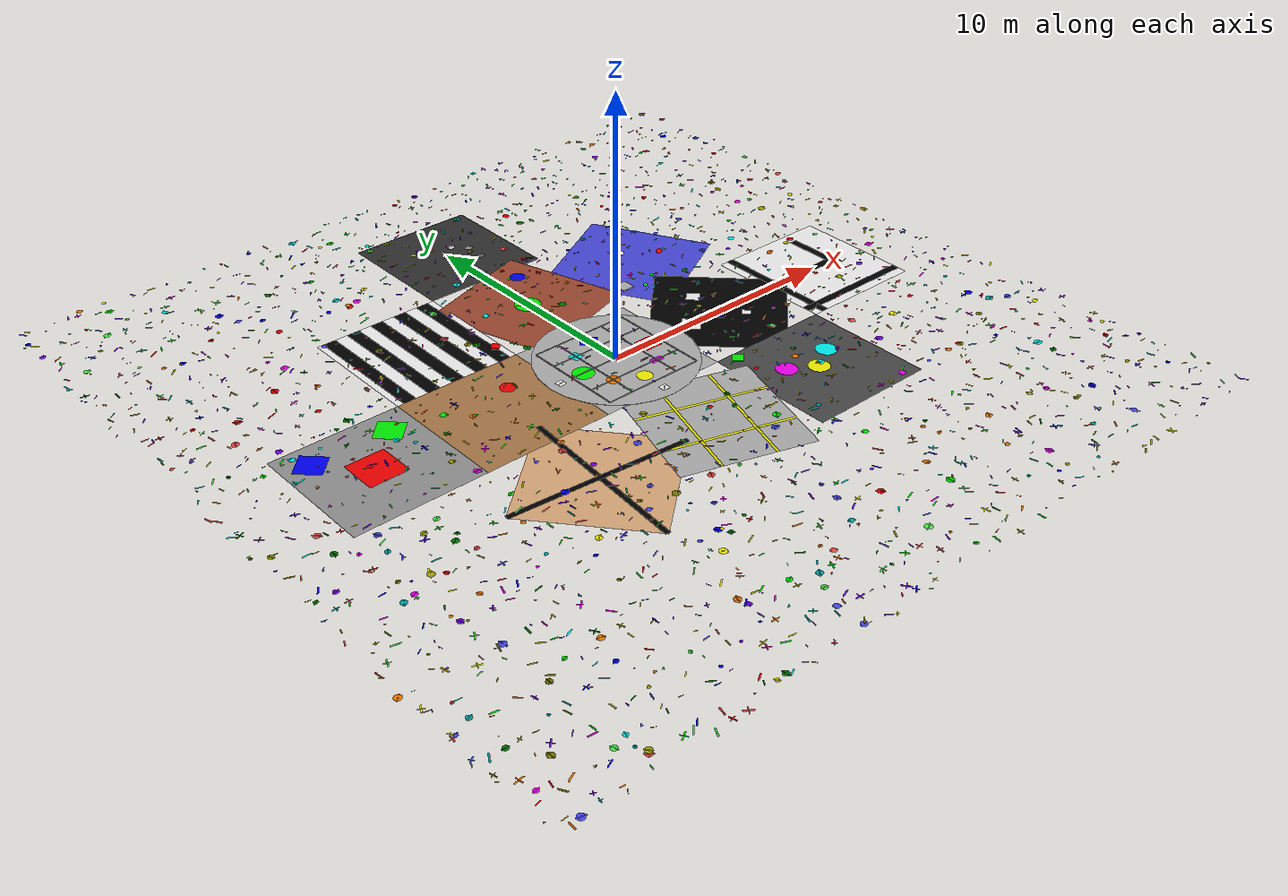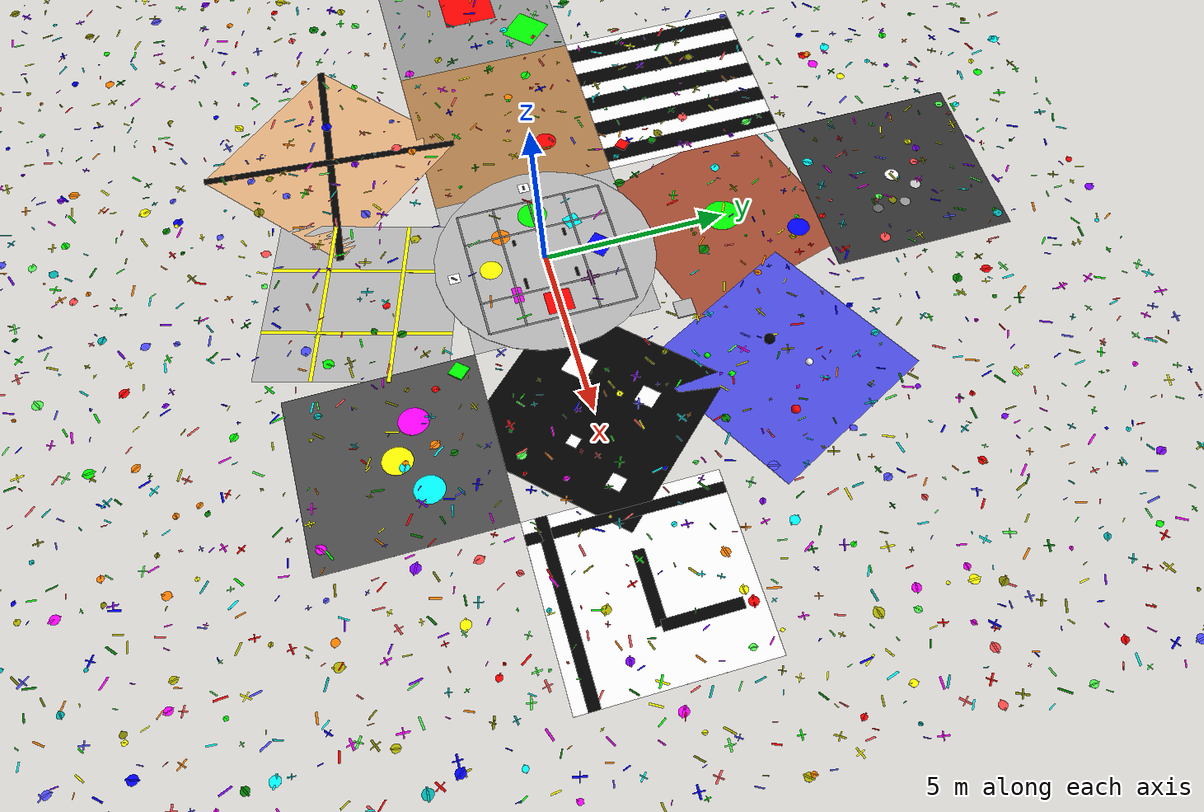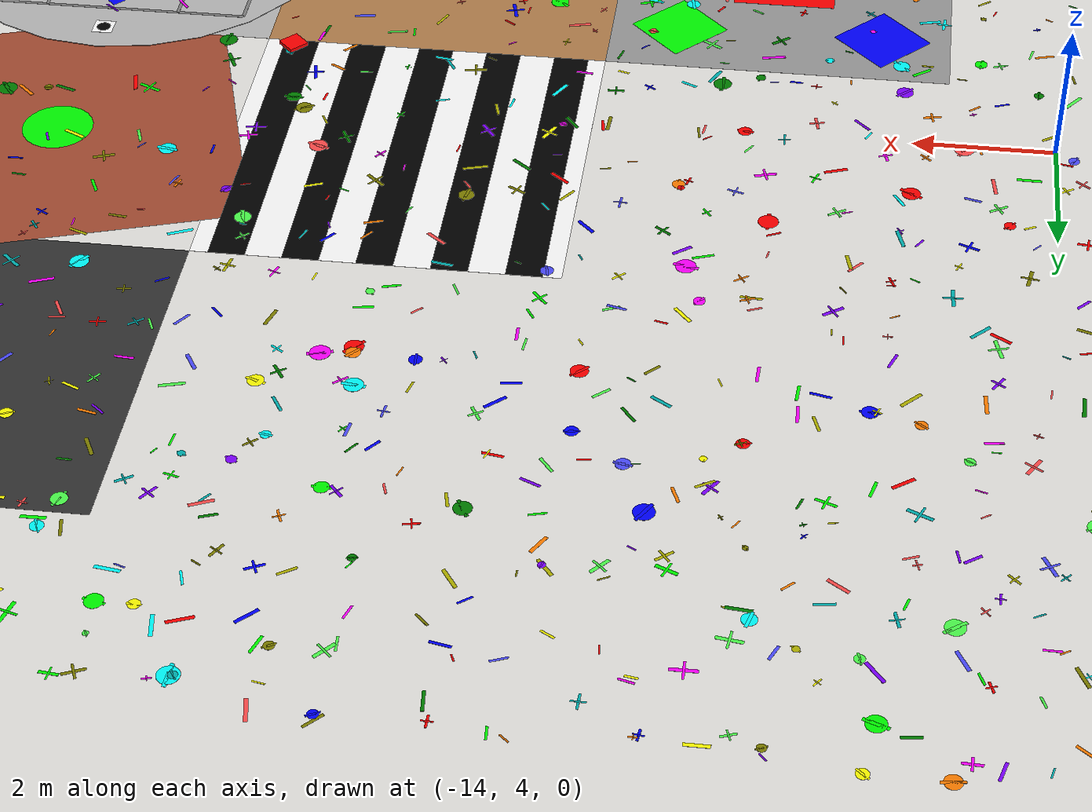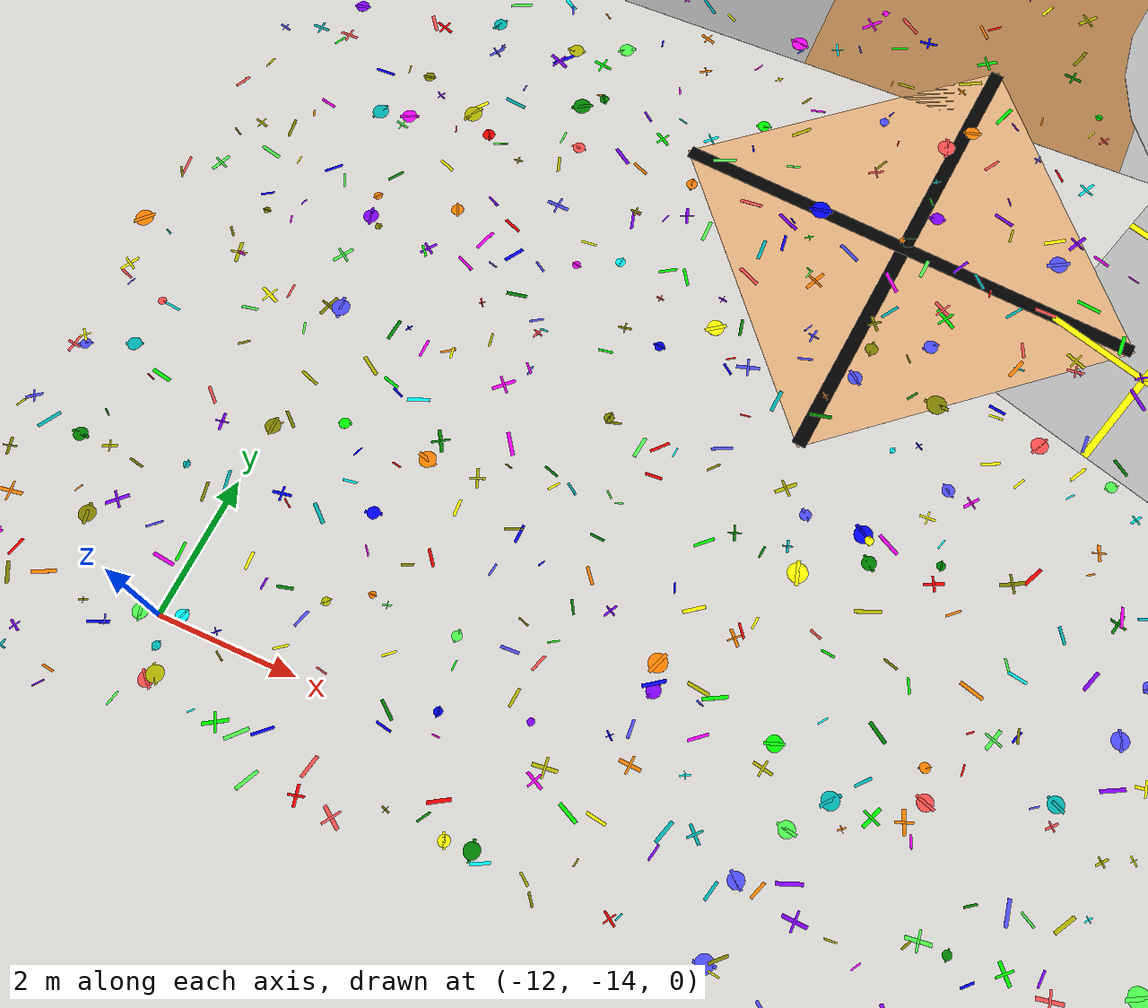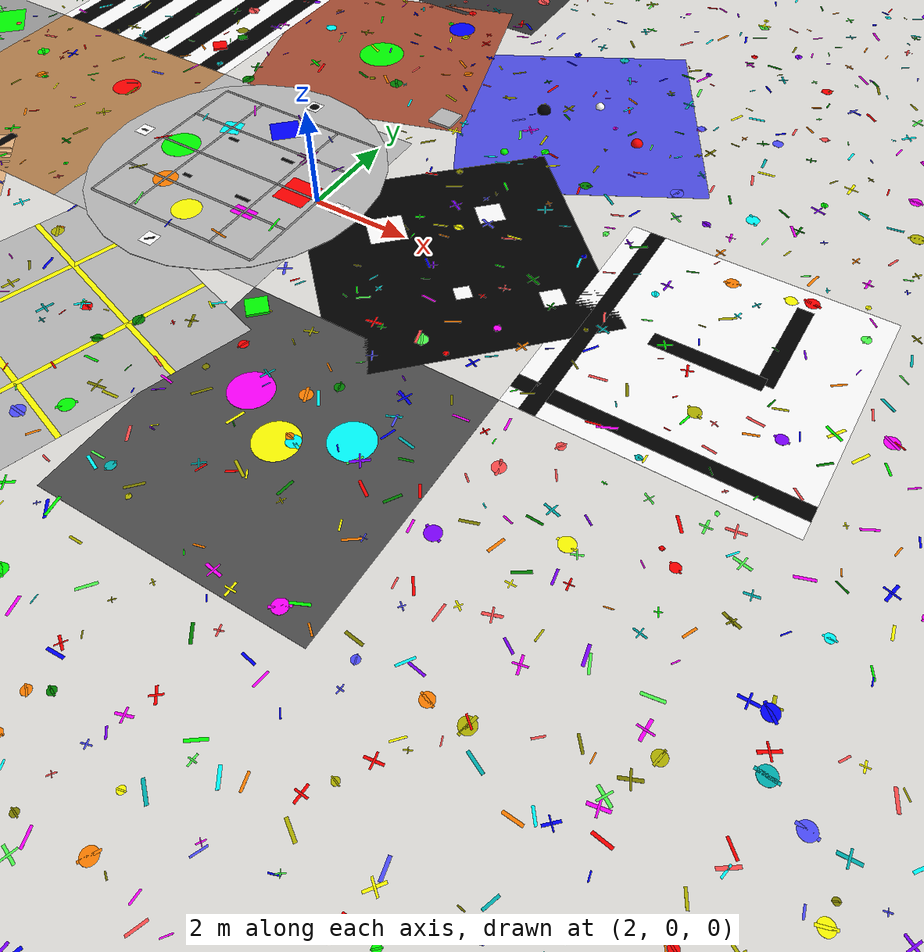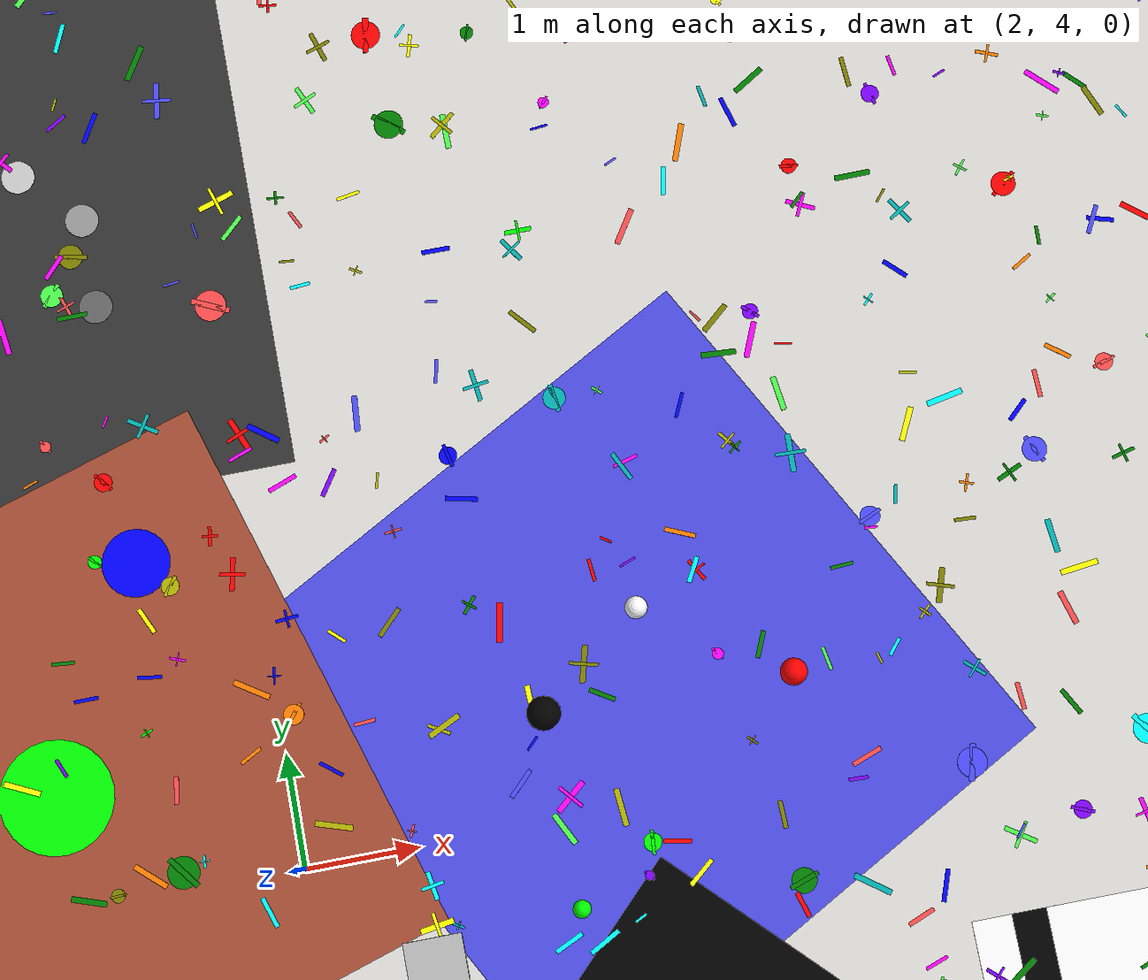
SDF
<sdf version="1.6">
 <world name="default">
  <physics type="ode">
   <ode>
    <solver><type>quick</type><iters>150</iters><sor>1.3</sor></solver>
    <constraints>
     <cfm>0.0</cfm>
     <erp>0.2</erp>
     <contact_max_correcting_vel>0.1</contact_max_correcting_vel>
     <contact_surface_layer>0.0</contact_surface_layer>
    </constraints>
   </ode>
   <real_time_update_rate>1000</real_time_update_rate>
   <max_step_size>0.001</max_step_size>
  </physics>
  <gravity>0 0 -9.8066</gravity>
  <magnetic_field>6e-06 2.3e-05 -4.2e-05</magnetic_field>
  <scene><ambient>0.8 0.8 0.8 1</ambient><background>0.9 0.95 1.0 1</background><shadows>true</shadows></scene>
  <light name="sun" type="directional">
   <pose>0 0 100 0 0 0</pose>
   <diffuse>1.0 1.0 1.0 1</diffuse>
   <specular>0.3 0.3 0.3 1</specular>
   <direction>-0.3 0.3 -0.9</direction>
  </light>
  <light name="aux_light" type="point">
   <pose>10 10 20 0 0 0</pose>
   <diffuse>0.5 0.5 0.5 1</diffuse>
   <specular>0.2 0.2 0.2 1</specular>
   <attenuation><range>50</range><constant>0.8</constant><linear>0.01</linear></attenuation>
  </light>
  <model name="ground_collision">
   <static>true</static>
   <link name="link">
    <collision name="collision">
     <geometry><plane><normal>0 0 1</normal><size>200 200</size></plane></geometry>
    </collision>
   </link>
  </model>
  <model name="sector_0_0">
   <static>true</static>
   <pose>0 0 0.001 0 0 0</pose>
   <link name="link">
    <visual name="visual">
     <geometry><box><size>5 5 0.001</size></box></geometry>
     <material>
      <script><uri>file://media/materials/scripts/gazebo.material</uri><name>Gazebo/Checkerboard</name></script>
     </material>
    </visual>
   </link>
  </model>
  <model name="sector_1_0">
   <static>true</static>
   <pose>5 0 0.001 0 0 0.785</pose>
   <link name="link">
    <visual name="visual">
     <geometry><box><size>5 5 0.001</size></box></geometry>
     <material><ambient>0 0 0 1</ambient><diffuse>0 0 0 1</diffuse></material>
    </visual>
    <visual name="qr1">
     <pose>1 1 0.001 0 0 0</pose>
     <geometry><box><size>0.5 0.5 0.001</size></box></geometry>
     <material><ambient>1 1 1 1</ambient><diffuse>1 1 1 1</diffuse></material>
    </visual>
    <visual name="qr2">
     <pose>-1 1 0.001 0 0 0</pose>
     <geometry><box><size>0.7 0.7 0.001</size></box></geometry>
     <material><ambient>1 1 1 1</ambient><diffuse>1 1 1 1</diffuse></material>
    </visual>
    <visual name="qr3">
     <pose>0 -1 0.001 0 0 0</pose>
     <geometry><box><size>0.3 0.3 0.001</size></box></geometry>
     <material><ambient>1 1 1 1</ambient><diffuse>1 1 1 1</diffuse></material>
    </visual>
    <visual name="qr4">
     <pose>1.5 -1.5 0.001 0 0 0</pose>
     <geometry><box><size>0.4 0.4 0.001</size></box></geometry>
     <material><ambient>1 1 1 1</ambient><diffuse>1 1 1 1</diffuse></material>
    </visual>
   </link>
  </model>
  <model name="sector_m1_0">
   <static>true</static>
   <pose>-5 0 0.001 0 0 0</pose>
   <link name="link">
    <visual name="visual">
     <geometry><box><size>5 5 0.001</size></box></geometry>
     <material>
      <script><uri>file://media/materials/scripts/gazebo.material</uri><name>Gazebo/Wood</name></script>
     </material>
    </visual>
    <visual name="marker_A">
     <pose>1 1 0.002 0 0 0</pose>
     <geometry><cylinder><radius>0.3</radius><length>0.001</length></cylinder></geometry>
     <material><ambient>1 0 0 1</ambient><diffuse>1 0 0 1</diffuse><emissive>0.2 0 0 1</emissive></material>
    </visual>
   </link>
  </model>
  <model name="sector_0_1">
   <static>true</static>
   <pose>0 5 0.001 0 0 0.3</pose>
   <link name="link">
    <visual name="visual">
     <geometry><box><size>5 5 0.001</size></box></geometry>
     <material>
      <script><uri>file://media/materials/scripts/gazebo.material</uri><name>Gazebo/Bricks</name></script>
     </material>
    </visual>
    <visual name="circle1">
     <pose>0 0 0.002 0 0 0</pose>
     <geometry><cylinder><radius>0.5</radius><length>0.001</length></cylinder></geometry>
     <material><ambient>0 1 0 1</ambient><diffuse>0 1 0 1</diffuse></material>
    </visual>
    <visual name="circle2">
     <pose>1.5 1.5 0.002 0 0 0</pose>
     <geometry><cylinder><radius>0.3</radius><length>0.001</length></cylinder></geometry>
     <material><ambient>0 0 1 1</ambient><diffuse>0 0 1 1</diffuse></material>
    </visual>
   </link>
  </model>
  <model name="sector_0_m1">
   <static>true</static>
   <pose>0 -5 0.001 0 0 -0.3</pose>
   <link name="link">
    <visual name="visual">
     <geometry><box><size>5 5 0.001</size></box></geometry>
     <material>
      <script><uri>file://media/materials/scripts/gazebo.material</uri><name>Gazebo/Rocky</name></script>
     </material>
    </visual>
    <visual name="grid_h1">
     <pose>0 -1 0.002 0 0 0</pose>
     <geometry><box><size>5 0.1 0.001</size></box></geometry>
     <material><ambient>1 1 0 1</ambient><diffuse>1 1 0 1</diffuse></material>
    </visual>
    <visual name="grid_h2">
     <pose>0 1 0.002 0 0 0</pose>
     <geometry><box><size>5 0.1 0.001</size></box></geometry>
     <material><ambient>1 1 0 1</ambient><diffuse>1 1 0 1</diffuse></material>
    </visual>
    <visual name="grid_v1">
     <pose>-1 0 0.002 0 0 0</pose>
     <geometry><box><size>0.1 5 0.001</size></box></geometry>
     <material><ambient>1 1 0 1</ambient><diffuse>1 1 0 1</diffuse></material>
    </visual>
    <visual name="grid_v2">
     <pose>1 0 0.002 0 0 0</pose>
     <geometry><box><size>0.1 5 0.001</size></box></geometry>
     <material><ambient>1 1 0 1</ambient><diffuse>1 1 0 1</diffuse></material>
    </visual>
   </link>
  </model>
  <model name="sector_1_1">
   <static>true</static>
   <pose>5 5 0.001 0 0 0.5</pose>
   <link name="link">
    <visual name="visual">
     <geometry><box><size>5 5 0.001</size></box></geometry>
     <material><ambient>0.2 0.2 0.8 1</ambient><diffuse>0.3 0.3 0.9 1</diffuse></material>
    </visual>
    <visual name="dot1">
     <pose>0.5 0.5 0.002 0 0 0</pose>
     <geometry><sphere><radius>0.1</radius></sphere></geometry>
     <material><ambient>1 1 1 1</ambient><diffuse>1 1 1 1</diffuse></material>
    </visual>
    <visual name="dot2">
     <pose>-0.7 0.3 0.002 0 0 0</pose>
     <geometry><sphere><radius>0.15</radius></sphere></geometry>
     <material><ambient>0 0 0 1</ambient><diffuse>0 0 0 1</diffuse></material>
    </visual>
    <visual name="dot3">
     <pose>1.2 -0.8 0.002 0 0 0</pose>
     <geometry><sphere><radius>0.12</radius></sphere></geometry>
     <material><ambient>1 0 0 1</ambient><diffuse>1 0 0 1</diffuse></material>
    </visual>
    <visual name="dot4">
     <pose>-1.5 -1.2 0.002 0 0 0</pose>
     <geometry><sphere><radius>0.08</radius></sphere></geometry>
     <material><ambient>0 1 0 1</ambient><diffuse>0 1 0 1</diffuse></material>
    </visual>
   </link>
  </model>
  <model name="sector_m1_1">
   <static>true</static>
   <pose>-5 5 0.001 0 0 0</pose>
   <link name="link">
    <visual name="base">
     <geometry><box><size>5 5 0.001</size></box></geometry>
     <material><ambient>1 1 1 1</ambient><diffuse>1 1 1 1</diffuse></material>
    </visual>
    <visual name="stripe1">
     <pose>-2 0 0.001 0 0 0</pose>
     <geometry><box><size>0.5 5 0.001</size></box></geometry>
     <material><ambient>0 0 0 1</ambient><diffuse>0 0 0 1</diffuse></material>
    </visual>
    <visual name="stripe2">
     <pose>-1 0 0.001 0 0 0</pose>
     <geometry><box><size>0.5 5 0.001</size></box></geometry>
     <material><ambient>0 0 0 1</ambient><diffuse>0 0 0 1</diffuse></material>
    </visual>
    <visual name="stripe3">
     <pose>0 0 0.001 0 0 0</pose>
     <geometry><box><size>0.5 5 0.001</size></box></geometry>
     <material><ambient>0 0 0 1</ambient><diffuse>0 0 0 1</diffuse></material>
    </visual>
    <visual name="stripe4">
     <pose>1 0 0.001 0 0 0</pose>
     <geometry><box><size>0.5 5 0.001</size></box></geometry>
     <material><ambient>0 0 0 1</ambient><diffuse>0 0 0 1</diffuse></material>
    </visual>
    <visual name="stripe5">
     <pose>2 0 0.001 0 0 0</pose>
     <geometry><box><size>0.5 5 0.001</size></box></geometry>
     <material><ambient>0 0 0 1</ambient><diffuse>0 0 0 1</diffuse></material>
    </visual>
   </link>
  </model>
  <model name="sector_1_m1">
   <static>true</static>
   <pose>5 -5 0.001 0 0 0</pose>
   <link name="link">
    <visual name="base">
     <geometry><box><size>5 5 0.001</size></box></geometry>
     <material><ambient>0.3 0.3 0.3 1</ambient><diffuse>0.3 0.3 0.3 1</diffuse></material>
    </visual>
    <visual name="hex1">
     <pose>0 0 0.002 0 0 0</pose>
     <geometry><cylinder><radius>0.4</radius><length>0.001</length></cylinder></geometry>
     <material><ambient>1 1 0 1</ambient><diffuse>1 1 0 1</diffuse></material>
    </visual>
    <visual name="hex2">
     <pose>1 0.6 0.002 0 0 0</pose>
     <geometry><cylinder><radius>0.4</radius><length>0.001</length></cylinder></geometry>
     <material><ambient>0 1 1 1</ambient><diffuse>0 1 1 1</diffuse></material>
    </visual>
    <visual name="hex3">
     <pose>-1 0.6 0.002 0 0 0</pose>
     <geometry><cylinder><radius>0.4</radius><length>0.001</length></cylinder></geometry>
     <material><ambient>1 0 1 1</ambient><diffuse>1 0 1 1</diffuse></material>
    </visual>
   </link>
  </model>
  <model name="sector_m1_m1">
   <static>true</static>
   <pose>-5 -5 0.001 0 0 0.7</pose>
   <link name="link">
    <visual name="visual">
     <geometry><box><size>5 5 0.001</size></box></geometry>
     <material><ambient>0.8 0.6 0.4 1</ambient><diffuse>0.9 0.7 0.5 1</diffuse></material>
    </visual>
    <visual name="line1">
     <pose>0 0 0.002 0 0 0.785</pose>
     <geometry><box><size>7 0.2 0.001</size></box></geometry>
     <material><ambient>0 0 0 1</ambient><diffuse>0 0 0 1</diffuse></material>
    </visual>
    <visual name="line2">
     <pose>0 0 0.002 0 0 -0.785</pose>
     <geometry><box><size>7 0.2 0.001</size></box></geometry>
     <material><ambient>0 0 0 1</ambient><diffuse>0 0 0 1</diffuse></material>
    </visual>
   </link>
  </model>
  <model name="sector_2_0">
   <static>true</static>
   <pose>10 0 0.001 0 0 0</pose>
   <link name="link">
    <visual name="base">
     <geometry><box><size>5 5 0.001</size></box></geometry>
     <material><ambient>0.9 0.9 0.9 1</ambient><diffuse>1 1 1 1</diffuse></material>
    </visual>
    <visual name="wall1">
     <pose>0 -2 0.002 0 0 0</pose>
     <geometry><box><size>5 0.3 0.001</size></box></geometry>
     <material><ambient>0 0 0 1</ambient><diffuse>0 0 0 1</diffuse></material>
    </visual>
    <visual name="wall2">
     <pose>-2 0 0.002 0 0 0</pose>
     <geometry><box><size>0.3 5 0.001</size></box></geometry>
     <material><ambient>0 0 0 1</ambient><diffuse>0 0 0 1</diffuse></material>
    </visual>
    <visual name="wall3">
     <pose>0 0 0.002 0 0 0</pose>
     <geometry><box><size>2 0.3 0.001</size></box></geometry>
     <material><ambient>0 0 0 1</ambient><diffuse>0 0 0 1</diffuse></material>
    </visual>
    <visual name="wall4">
     <pose>1 1 0.002 0 0 0</pose>
     <geometry><box><size>0.3 2 0.001</size></box></geometry>
     <material><ambient>0 0 0 1</ambient><diffuse>0 0 0 1</diffuse></material>
    </visual>
   </link>
  </model>
  <model name="sector_m2_0">
   <static>true</static>
   <pose>-10 0 0.001 0 0 0</pose>
   <link name="link">
    <visual name="base">
     <geometry><box><size>5 5 0.001</size></box></geometry>
     <material><ambient>0.5 0.5 0.5 1</ambient><diffuse>0.6 0.6 0.6 1</diffuse></material>
    </visual>
    <visual name="tri1">
     <pose>0 0 0.002 0 0 0</pose>
     <geometry><box><size>1.5 1.5 0.001</size></box></geometry>
     <material><ambient>1 0 0 1</ambient><diffuse>1 0 0 1</diffuse></material>
    </visual>
    <visual name="tri2">
     <pose>1.5 1.5 0.002 0 0 0.785</pose>
     <geometry><box><size>1 1 0.001</size></box></geometry>
     <material><ambient>0 1 0 1</ambient><diffuse>0 1 0 1</diffuse></material>
    </visual>
    <visual name="tri3">
     <pose>-1.5 1.5 0.002 0 0 -0.785</pose>
     <geometry><box><size>1 1 0.001</size></box></geometry>
     <material><ambient>0 0 1 1</ambient><diffuse>0 0 1 1</diffuse></material>
    </visual>
   </link>
  </model>
  <model name="sector_0_2">
   <static>true</static>
   <pose>0 10 0.001 0 0 0</pose>
   <link name="link">
    <visual name="base">
     <geometry><box><size>5 5 0.001</size></box></geometry>
     <material><ambient>0.1 0.1 0.1 1</ambient><diffuse>0.2 0.2 0.2 1</diffuse></material>
    </visual>
    <visual name="spiral1">
     <pose>0 0 0.002 0 0 0</pose>
     <geometry><cylinder><radius>0.2</radius><length>0.001</length></cylinder></geometry>
     <material><ambient>1 1 1 1</ambient><diffuse>1 1 1 1</diffuse></material>
    </visual>
    <visual name="spiral2">
     <pose>0.5 0.5 0.002 0 0 0</pose>
     <geometry><cylinder><radius>0.15</radius><length>0.001</length></cylinder></geometry>
     <material><ambient>0.8 0.8 0.8 1</ambient><diffuse>0.8 0.8 0.8 1</diffuse></material>
    </visual>
    <visual name="spiral3">
     <pose>1 0 0.002 0 0 0</pose>
     <geometry><cylinder><radius>0.15</radius><length>0.001</length></cylinder></geometry>
     <material><ambient>0.6 0.6 0.6 1</ambient><diffuse>0.6 0.6 0.6 1</diffuse></material>
    </visual>
    <visual name="spiral4">
     <pose>1 -0.8 0.002 0 0 0</pose>
     <geometry><cylinder><radius>0.15</radius><length>0.001</length></cylinder></geometry>
     <material><ambient>0.4 0.4 0.4 1</ambient><diffuse>0.4 0.4 0.4 1</diffuse></material>
    </visual>
   </link>
  </model>
  <model name="height_marker_1">
   <static>true</static>
   <pose>3 3 0.5 0 0 0</pose>
   <link name="link">
    <visual name="visual">
     <geometry><box><size>0.5 0.5 0.05</size></box></geometry>
     <material>
      <script><uri>file://media/materials/scripts/gazebo.material</uri><name>Gazebo/Checkerboard</name></script>
     </material>
    </visual>
   </link>
  </model>
  <model name="height_marker_2">
   <static>true</static>
   <pose>-3 3 0.3 0 0 0.785</pose>
   <link name="link">
    <visual name="visual">
     <geometry><box><size>0.3 0.3 0.05</size></box></geometry>
     <material><ambient>1 0 0 1</ambient><diffuse>1 0 0 1</diffuse></material>
    </visual>
   </link>
  </model>
  <model name="height_marker_3">
   <static>true</static>
   <pose>3 -3 0.2 0 0 -0.785</pose>
   <link name="link">
    <visual name="visual">
     <geometry><box><size>0.4 0.4 0.05</size></box></geometry>
     <material><ambient>0 1 0 1</ambient><diffuse>0 1 0 1</diffuse></material>
    </visual>
   </link>
  </model>
  <model name="ultra_landing_pad">
   <static>true</static>
   <pose>0 0 0.01 0 0 0</pose>
   <link name="link">
    <visual name="base">
     <geometry><cylinder><radius>3</radius><length>0.01</length></cylinder></geometry>
     <material>
      <script><uri>file://media/materials/scripts/gazebo.material</uri><name>Gazebo/Checkerboard</name></script>
     </material>
    </visual>
    <visual name="qr_base">
     <pose>0 0 0.001 0 0 0.785</pose>
     <geometry><box><size>4 4 0.001</size></box></geometry>
     <material><ambient>1 1 1 1</ambient><diffuse>1 1 1 1</diffuse></material>
    </visual>
    <visual name="qr_block1">
     <pose>-1 -1 0.002 0 0 0</pose>
     <geometry><box><size>0.8 0.8 0.001</size></box></geometry>
     <material><ambient>0 0 0 1</ambient><diffuse>0 0 0 1</diffuse></material>
    </visual>
    <visual name="qr_block2">
     <pose>1 -1 0.002 0 0 0</pose>
     <geometry><box><size>0.8 0.8 0.001</size></box></geometry>
     <material><ambient>0 0 0 1</ambient><diffuse>0 0 0 1</diffuse></material>
    </visual>
    <visual name="qr_block3">
     <pose>-1 1 0.002 0 0 0</pose>
     <geometry><box><size>0.8 0.8 0.001</size></box></geometry>
     <material><ambient>0 0 0 1</ambient><diffuse>0 0 0 1</diffuse></material>
    </visual>
    <visual name="aruco_center">
     <pose>0 0 0.003 0 0 0</pose>
     <geometry><box><size>1.2 1.2 0.001</size></box></geometry>
     <material><ambient>1 1 1 1</ambient><diffuse>1 1 1 1</diffuse></material>
    </visual>
    <visual name="aruco_pattern1">
     <pose>-0.3 -0.3 0.004 0 0 0</pose>
     <geometry><box><size>0.3 0.3 0.001</size></box></geometry>
     <material><ambient>0 0 0 1</ambient><diffuse>0 0 0 1</diffuse></material>
    </visual>
    <visual name="aruco_pattern2">
     <pose>0.3 0.3 0.004 0 0 0</pose>
     <geometry><box><size>0.3 0.3 0.001</size></box></geometry>
     <material><ambient>0 0 0 1</ambient><diffuse>0 0 0 1</diffuse></material>
    </visual>
    <visual name="aruco_pattern3">
     <pose>0 0 0.004 0 0 0</pose>
     <geometry><box><size>0.2 0.2 0.001</size></box></geometry>
     <material><ambient>0 0 0 1</ambient><diffuse>0 0 0 1</diffuse></material>
    </visual>
    <visual name="triangle_red">
     <pose>1.5 0 0.005 0 0 0</pose>
     <geometry><box><size>0.7 0.7 0.001</size></box></geometry>
     <material><ambient>1 0 0 1</ambient><diffuse>1 0 0 1</diffuse><emissive>0.2 0 0 1</emissive></material>
    </visual>
    <visual name="hex_green">
     <pose>-1.5 0 0.005 0 0 0</pose>
     <geometry><cylinder><radius>0.4</radius><length>0.001</length></cylinder></geometry>
     <material><ambient>0 1 0 1</ambient><diffuse>0 1 0 1</diffuse><emissive>0 0.2 0 1</emissive></material>
    </visual>
    <visual name="diamond_blue">
     <pose>0 1.5 0.005 0 0 0.785</pose>
     <geometry><box><size>0.6 0.6 0.001</size></box></geometry>
     <material><ambient>0 0 1 1</ambient><diffuse>0 0 1 1</diffuse><emissive>0 0 0.2 1</emissive></material>
    </visual>
    <visual name="star_yellow">
     <pose>0 -1.5 0.005 0 0 0</pose>
     <geometry><cylinder><radius>0.3</radius><length>0.001</length></cylinder></geometry>
     <material><ambient>1 1 0 1</ambient><diffuse>1 1 0 1</diffuse><emissive>0.2 0.2 0 1</emissive></material>
    </visual>
    <visual name="cross_purple_h">
     <pose>1 1 0.005 0 0 0</pose>
     <geometry><box><size>0.5 0.1 0.001</size></box></geometry>
     <material><ambient>0.6 0 0.6 1</ambient><diffuse>0.6 0 0.6 1</diffuse></material>
    </visual>
    <visual name="cross_purple_v">
     <pose>1 1 0.005 0 0 0</pose>
     <geometry><box><size>0.1 0.5 0.001</size></box></geometry>
     <material><ambient>0.6 0 0.6 1</ambient><diffuse>0.6 0 0.6 1</diffuse></material>
    </visual>
    <visual name="circle_orange1">
     <pose>-1 -1 0.005 0 0 0</pose>
     <geometry><cylinder><radius>0.25</radius><length>0.001</length></cylinder></geometry>
     <material><ambient>1 0.5 0 1</ambient><diffuse>1 0.5 0 1</diffuse></material>
    </visual>
    <visual name="square_cyan">
     <pose>-1 1 0.005 0 0 0.3</pose>
     <geometry><box><size>0.4 0.4 0.001</size></box></geometry>
     <material><ambient>0 1 1 1</ambient><diffuse>0 1 1 1</diffuse></material>
    </visual>
    <visual name="triangle_magenta">
     <pose>1 -1 0.005 0 0 0</pose>
     <geometry><box><size>0.5 0.25 0.001</size></box></geometry>
     <material><ambient>1 0 1 1</ambient><diffuse>1 0 1 1</diffuse></material>
    </visual>
    <visual name="grid_line1">
     <pose>0 -2 0.006 0 0 0</pose>
     <geometry><box><size>4 0.05 0.001</size></box></geometry>
     <material><ambient>0.5 0.5 0.5 1</ambient><diffuse>0.5 0.5 0.5 1</diffuse></material>
    </visual>
    <visual name="grid_line2">
     <pose>0 -1 0.006 0 0 0</pose>
     <geometry><box><size>4 0.05 0.001</size></box></geometry>
     <material><ambient>0.5 0.5 0.5 1</ambient><diffuse>0.5 0.5 0.5 1</diffuse></material>
    </visual>
    <visual name="grid_line3">
     <pose>0 0 0.006 0 0 0</pose>
     <geometry><box><size>4 0.05 0.001</size></box></geometry>
     <material><ambient>0.5 0.5 0.5 1</ambient><diffuse>0.5 0.5 0.5 1</diffuse></material>
    </visual>
    <visual name="grid_line4">
     <pose>0 1 0.006 0 0 0</pose>
     <geometry><box><size>4 0.05 0.001</size></box></geometry>
     <material><ambient>0.5 0.5 0.5 1</ambient><diffuse>0.5 0.5 0.5 1</diffuse></material>
    </visual>
    <visual name="grid_line5">
     <pose>0 2 0.006 0 0 0</pose>
     <geometry><box><size>4 0.05 0.001</size></box></geometry>
     <material><ambient>0.5 0.5 0.5 1</ambient><diffuse>0.5 0.5 0.5 1</diffuse></material>
    </visual>
    <visual name="grid_vline1">
     <pose>-2 0 0.006 0 0 0</pose>
     <geometry><box><size>0.05 4 0.001</size></box></geometry>
     <material><ambient>0.5 0.5 0.5 1</ambient><diffuse>0.5 0.5 0.5 1</diffuse></material>
    </visual>
    <visual name="grid_vline2">
     <pose>-1 0 0.006 0 0 0</pose>
     <geometry><box><size>0.05 4 0.001</size></box></geometry>
     <material><ambient>0.5 0.5 0.5 1</ambient><diffuse>0.5 0.5 0.5 1</diffuse></material>
    </visual>
    <visual name="grid_vline3">
     <pose>1 0 0.006 0 0 0</pose>
     <geometry><box><size>0.05 4 0.001</size></box></geometry>
     <material><ambient>0.5 0.5 0.5 1</ambient><diffuse>0.5 0.5 0.5 1</diffuse></material>
    </visual>
    <visual name="grid_vline4">
     <pose>2 0 0.006 0 0 0</pose>
     <geometry><box><size>0.05 4 0.001</size></box></geometry>
     <material><ambient>0.5 0.5 0.5 1</ambient><diffuse>0.5 0.5 0.5 1</diffuse></material>
    </visual>
    <visual name="text1">
     <pose>0.7 0.7 0.007 0 0 0</pose>
     <geometry><box><size>0.3 0.08 0.001</size></box></geometry>
     <material><ambient>0 0 0 1</ambient><diffuse>0 0 0 1</diffuse></material>
    </visual>
    <visual name="text2">
     <pose>-0.7 0.7 0.007 0 0 0</pose>
     <geometry><box><size>0.25 0.08 0.001</size></box></geometry>
     <material><ambient>0 0 0 1</ambient><diffuse>0 0 0 1</diffuse></material>
    </visual>
    <visual name="text3">
     <pose>0.7 -0.7 0.007 0 0 0</pose>
     <geometry><box><size>0.35 0.08 0.001</size></box></geometry>
     <material><ambient>0 0 0 1</ambient><diffuse>0 0 0 1</diffuse></material>
    </visual>
    <visual name="text4">
     <pose>-0.7 -0.7 0.007 0 0 0</pose>
     <geometry><box><size>0.2 0.08 0.001</size></box></geometry>
     <material><ambient>0 0 0 1</ambient><diffuse>0 0 0 1</diffuse></material>
    </visual>
    <visual name="number_1">
     <pose>2.5 0 0.008 0 0 0</pose>
     <geometry><box><size>0.3 0.3 0.001</size></box></geometry>
     <material><ambient>1 1 1 1</ambient><diffuse>1 1 1 1</diffuse></material>
    </visual>
    <visual name="number_1_text">
     <pose>2.5 0 0.009 0 0 0</pose>
     <geometry><box><size>0.1 0.2 0.001</size></box></geometry>
     <material><ambient>0 0 0 1</ambient><diffuse>0 0 0 1</diffuse></material>
    </visual>
    <visual name="number_2">
     <pose>0 2.5 0.008 0 0 0</pose>
     <geometry><box><size>0.3 0.3 0.001</size></box></geometry>
     <material><ambient>1 1 1 1</ambient><diffuse>1 1 1 1</diffuse></material>
    </visual>
    <visual name="number_2_text">
     <pose>0 2.5 0.009 0 0 0</pose>
     <geometry><cylinder><radius>0.1</radius><length>0.001</length></cylinder></geometry>
     <material><ambient>0 0 0 1</ambient><diffuse>0 0 0 1</diffuse></material>
    </visual>
    <visual name="number_3">
     <pose>-2.5 0 0.008 0 0 0</pose>
     <geometry><box><size>0.3 0.3 0.001</size></box></geometry>
     <material><ambient>1 1 1 1</ambient><diffuse>1 1 1 1</diffuse></material>
    </visual>
    <visual name="number_3_text">
     <pose>-2.5 0 0.009 0 0 0</pose>
     <geometry><box><size>0.15 0.05 0.001</size></box></geometry>
     <material><ambient>0 0 0 1</ambient><diffuse>0 0 0 1</diffuse></material>
    </visual>
    <visual name="number_4">
     <pose>0 -2.5 0.008 0 0 0</pose>
     <geometry><box><size>0.3 0.3 0.001</size></box></geometry>
     <material><ambient>1 1 1 1</ambient><diffuse>1 1 1 1</diffuse></material>
    </visual>
    <visual name="number_4_cross">
     <pose>0 -2.5 0.009 0 0 0.785</pose>
     <geometry><box><size>0.2 0.05 0.001</size></box></geometry>
     <material><ambient>0 0 0 1</ambient><diffuse>0 0 0 1</diffuse></material>
    </visual>
   </link>
  </model>
  <model name="letter_pad_0">
   <static>true</static>
   <pose>2.00 0.00 0.02 0 0 3.93</pose>
   <link name="link">
    <visual name="visual">
     <geometry><box><size>0.20826732701765038 0.02082673270176504 0.005</size></box></geometry>
     <material><ambient>1 0 0 1</ambient><diffuse>1 0 0 1</diffuse><emissive>0.2 0.0 0.0 1</emissive></material>
    </visual>
   </link>
  </model>
  <model name="letter_pad_1">
   <static>true</static>
   <pose>1.73 1.00 0.02 0 0 1.19</pose>
   <link name="link">
    <visual name="visual">
     <geometry><box><size>0.2737551352024328 0.02737551352024328 0.005</size></box></geometry>
     <material>
      <ambient>0.5 0 1 1</ambient>
      <diffuse>0.5 0 1 1</diffuse>
      <emissive>0.1 0.0 0.2 1</emissive>
     </material>
    </visual>
   </link>
  </model>
  <model name="letter_pad_2">
   <static>true</static>
   <pose>1.00 1.73 0.02 0 0 2.55</pose>
   <link name="link">
    <visual name="visual">
     <geometry><box><size>0.23543803813051306 0.02354380381305131 0.005</size></box></geometry>
     <material>
      <ambient>0.3 0.3 1 1</ambient>
      <diffuse>0.3 0.3 1 1</diffuse>
      <emissive>0.06 0.06 0.2 1</emissive>
     </material>
    </visual>
   </link>
  </model>
  <model name="letter_pad_3">
   <static>true</static>
   <pose>0.00 2.00 0.02 0 0 5.64</pose>
   <link name="link">
    <visual name="visual">
     <geometry><box><size>0.25826106271186444 0.025826106271186446 0.005</size></box></geometry>
     <material>
      <ambient>0.5 0 1 1</ambient>
      <diffuse>0.5 0 1 1</diffuse>
      <emissive>0.1 0.0 0.2 1</emissive>
     </material>
    </visual>
   </link>
  </model>
  <model name="letter_pad_4">
   <static>true</static>
   <pose>-1.00 1.73 0.02 0 0 2.28</pose>
   <link name="link">
    <visual name="visual">
     <geometry><box><size>0.37023480883030996 0.037023480883031 0.005</size></box></geometry>
     <material><ambient>1 0 1 1</ambient><diffuse>1 0 1 1</diffuse><emissive>0.2 0.0 0.2 1</emissive></material>
    </visual>
   </link>
  </model>
  <model name="letter_pad_5">
   <static>true</static>
   <pose>-1.73 1.00 0.02 0 0 1.90</pose>
   <link name="link">
    <visual name="visual">
     <geometry><box><size>0.2744019711188168 0.027440197111881684 0.005</size></box></geometry>
     <material><ambient>0 1 1 1</ambient><diffuse>0 1 1 1</diffuse><emissive>0.0 0.2 0.2 1</emissive></material>
    </visual>
   </link>
  </model>
  <model name="letter_pad_6">
   <static>true</static>
   <pose>-2.00 0.00 0.02 0 0 3.97</pose>
   <link name="link">
    <visual name="visual">
     <geometry><box><size>0.36563366224132915 0.036563366224132914 0.005</size></box></geometry>
     <material><ambient>1 0 0 1</ambient><diffuse>1 0 0 1</diffuse><emissive>0.2 0.0 0.0 1</emissive></material>
    </visual>
   </link>
  </model>
  <model name="letter_pad_7">
   <static>true</static>
   <pose>-1.73 -1.00 0.02 0 0 4.04</pose>
   <link name="link">
    <visual name="visual">
     <geometry><box><size>0.3510190871288871 0.03510190871288871 0.005</size></box></geometry>
     <material>
      <ambient>0.5 0.5 0 1</ambient>
      <diffuse>0.5 0.5 0 1</diffuse>
      <emissive>0.1 0.1 0.0 1</emissive>
     </material>
    </visual>
   </link>
  </model>
  <model name="letter_pad_8">
   <static>true</static>
   <pose>-1.00 -1.73 0.02 0 0 1.94</pose>
   <link name="link">
    <visual name="visual">
     <geometry><box><size>0.3631468944970183 0.036314689449701835 0.005</size></box></geometry>
     <material>
      <ambient>0.3 1 0.3 1</ambient>
      <diffuse>0.3 1 0.3 1</diffuse>
      <emissive>0.06 0.2 0.06 1</emissive>
     </material>
    </visual>
   </link>
  </model>
  <model name="letter_pad_9">
   <static>true</static>
   <pose>-0.00 -2.00 0.02 0 0 4.95</pose>
   <link name="link">
    <visual name="visual">
     <geometry><box><size>0.23431271848597487 0.023431271848597487 0.005</size></box></geometry>
     <material><ambient>0 0 1 1</ambient><diffuse>0 0 1 1</diffuse><emissive>0.0 0.0 0.2 1</emissive></material>
    </visual>
   </link>
  </model>
  <model name="letter_pad_10">
   <static>true</static>
   <pose>1.00 -1.73 0.02 0 0 3.00</pose>
   <link name="link">
    <visual name="visual">
     <geometry><box><size>0.3881083728409897 0.038810837284098974 0.005</size></box></geometry>
     <material>
      <ambient>1 0.5 0 1</ambient>
      <diffuse>1 0.5 0 1</diffuse>
      <emissive>0.2 0.1 0.0 1</emissive>
     </material>
    </visual>
   </link>
  </model>
  <model name="letter_pad_11">
   <static>true</static>
   <pose>1.73 -1.00 0.02 0 0 1.73</pose>
   <link name="link">
    <visual name="visual">
     <geometry><box><size>0.382036188963052 0.038203618896305205 0.005</size></box></geometry>
     <material><ambient>0 1 0 1</ambient><diffuse>0 1 0 1</diffuse><emissive>0.0 0.2 0.0 1</emissive></material>
    </visual>
   </link>
  </model>
  <model name="letter_J_12">
   <static>true</static>
   <pose>-14.68 -15.03 0.010 0 0 3.229</pose>
   <link name="link">
    <visual name="visual">
     <geometry><box><size>0.22 0.03 0.002</size></box></geometry>
     <material>
      <ambient>0.7 0.7 0.0 1</ambient>
      <diffuse>0.7 0.7 0.0 1</diffuse>
      <specular>0.1 0.1 0.1 1</specular>
     </material>
    </visual>
   </link>
  </model>
  <model name="letter_H_13">
   <static>true</static>
   <pose>-15.12 -14.78 0.005 0 0 2.308</pose>
   <link name="link">
    <visual name="visual">
     <geometry><box><size>0.10 0.02 0.002</size></box></geometry>
     <material>
      <ambient>0.0 0.5 0.0 1</ambient>
      <diffuse>0.0 0.5 0.0 1</diffuse>
      <specular>0.1 0.1 0.1 1</specular>
     </material>
    </visual>
    <visual name="visual2">
     <pose>0 0 0.001 0 0 1.57</pose>
     <geometry><box><size>0.08 0.01 0.001</size></box></geometry>
     <material><ambient>0.0 0.5 0.0 1</ambient><diffuse>0.0 0.5 0.0 1</diffuse></material>
    </visual>
   </link>
  </model>
  <model name="letter_N_14">
   <static>true</static>
   <pose>-14.69 -15.32 0.008 0 0 4.657</pose>
   <link name="link">
    <visual name="visual">
     <geometry><box><size>0.30 0.05 0.002</size></box></geometry>
     <material>
      <ambient>1.0 0.5 0.0 1</ambient>
      <diffuse>1.0 0.5 0.0 1</diffuse>
      <specular>0.1 0.1 0.1 1</specular>
     </material>
    </visual>
   </link>
  </model>
  <model name="letter_C_15">
   <static>true</static>
   <pose>-14.63 -13.87 0.008 0 0 3.273</pose>
   <link name="link">
    <visual name="visual">
     <geometry><box><size>0.24 0.04 0.002</size></box></geometry>
     <material>
      <ambient>1.0 0.0 1.0 1</ambient>
      <diffuse>1.0 0.0 1.0 1</diffuse>
      <specular>0.1 0.1 0.1 1</specular>
     </material>
    </visual>
    <visual name="visual2">
     <geometry><cylinder><radius>0.09</radius><length>0.002</length></cylinder></geometry>
     <material><ambient>1.0 0.0 1.0 1</ambient><diffuse>1.0 0.0 1.0 1</diffuse></material>
    </visual>
   </link>
  </model>
  <model name="letter_X_16">
   <static>true</static>
   <pose>-14.85 -14.22 0.008 0 0 3.390</pose>
   <link name="link">
    <visual name="visual">
     <geometry><box><size>0.22 0.03 0.002</size></box></geometry>
     <material>
      <ambient>1.0 0.0 0.0 1</ambient>
      <diffuse>1.0 0.0 0.0 1</diffuse>
      <specular>0.1 0.1 0.1 1</specular>
     </material>
    </visual>
   </link>
  </model>
  <model name="letter_I_17">
   <static>true</static>
   <pose>-15.12 -12.78 0.003 0 0 1.850</pose>
   <link name="link">
    <visual name="visual">
     <geometry><box><size>0.25 0.04 0.002</size></box></geometry>
     <material>
      <ambient>0.5 0.5 0.0 1</ambient>
      <diffuse>0.5 0.5 0.0 1</diffuse>
      <specular>0.1 0.1 0.1 1</specular>
     </material>
    </visual>
    <visual name="visual2">
     <pose>0 0 0.001 0 0 1.57</pose>
     <geometry><box><size>0.20 0.02 0.001</size></box></geometry>
     <material><ambient>0.5 0.5 0.0 1</ambient><diffuse>0.5 0.5 0.0 1</diffuse></material>
    </visual>
   </link>
  </model>
  <model name="letter_H_18">
   <static>true</static>
   <pose>-14.74 -13.33 0.005 0 0 0.158</pose>
   <link name="link">
    <visual name="visual">
     <geometry><box><size>0.35 0.05 0.002</size></box></geometry>
     <material>
      <ambient>1.0 0.5 0.0 1</ambient>
      <diffuse>1.0 0.5 0.0 1</diffuse>
      <specular>0.1 0.1 0.1 1</specular>
     </material>
    </visual>
    <visual name="visual2">
     <pose>0 0 0.001 0 0 1.57</pose>
     <geometry><box><size>0.28 0.03 0.001</size></box></geometry>
     <material><ambient>1.0 0.5 0.0 1</ambient><diffuse>1.0 0.5 0.0 1</diffuse></material>
    </visual>
   </link>
  </model>
  <model name="letter_V_19">
   <static>true</static>
   <pose>-15.19 -13.02 0.007 0 0 2.205</pose>
   <link name="link">
    <visual name="visual">
     <geometry><box><size>0.13 0.02 0.002</size></box></geometry>
     <material>
      <ambient>0.5 0.5 0.0 1</ambient>
      <diffuse>0.5 0.5 0.0 1</diffuse>
      <specular>0.1 0.1 0.1 1</specular>
     </material>
    </visual>
   </link>
  </model>
  <model name="letter_X_20">
   <static>true</static>
   <pose>-14.84 -12.24 0.009 0 0 1.045</pose>
   <link name="link">
    <visual name="visual">
     <geometry><box><size>0.34 0.05 0.002</size></box></geometry>
     <material>
      <ambient>0.0 0.7 0.7 1</ambient>
      <diffuse>0.0 0.7 0.7 1</diffuse>
      <specular>0.1 0.1 0.1 1</specular>
     </material>
    </visual>
   </link>
  </model>
  <model name="letter_T_21">
   <static>true</static>
   <pose>-15.23 -12.02 0.009 0 0 3.767</pose>
   <link name="link">
    <visual name="visual">
     <geometry><box><size>0.24 0.04 0.002</size></box></geometry>
     <material>
      <ambient>0.3 0.3 1.0 1</ambient>
      <diffuse>0.3 0.3 1.0 1</diffuse>
      <specular>0.1 0.1 0.1 1</specular>
     </material>
    </visual>
    <visual name="visual2">
     <pose>0 0 0.001 0 0 1.57</pose>
     <geometry><box><size>0.19 0.02 0.001</size></box></geometry>
     <material><ambient>0.3 0.3 1.0 1</ambient><diffuse>0.3 0.3 1.0 1</diffuse></material>
    </visual>
   </link>
  </model>
  <model name="letter_W_22">
   <static>true</static>
   <pose>-15.32 -12.13 0.008 0 0 1.135</pose>
   <link name="link">
    <visual name="visual">
     <geometry><box><size>0.23 0.03 0.002</size></box></geometry>
     <material>
      <ambient>0.7 0.7 0.0 1</ambient>
      <diffuse>0.7 0.7 0.0 1</diffuse>
      <specular>0.1 0.1 0.1 1</specular>
     </material>
    </visual>
   </link>
  </model>
  <model name="letter_G_23">
   <static>true</static>
   <pose>-15.02 -11.05 0.003 0 0 0.506</pose>
   <link name="link">
    <visual name="visual">
     <geometry><box><size>0.21 0.03 0.002</size></box></geometry>
     <material>
      <ambient>0.3 0.3 1.0 1</ambient>
      <diffuse>0.3 0.3 1.0 1</diffuse>
      <specular>0.1 0.1 0.1 1</specular>
     </material>
    </visual>
    <visual name="visual2">
     <geometry><cylinder><radius>0.08</radius><length>0.002</length></cylinder></geometry>
     <material><ambient>0.3 0.3 1.0 1</ambient><diffuse>0.3 0.3 1.0 1</diffuse></material>
    </visual>
   </link>
  </model>
  <model name="letter_F_24">
   <static>true</static>
   <pose>-15.16 -11.12 0.011 0 0 1.458</pose>
   <link name="link">
    <visual name="visual">
     <geometry><box><size>0.26 0.04 0.002</size></box></geometry>
     <material>
      <ambient>1.0 0.3 0.3 1</ambient>
      <diffuse>1.0 0.3 0.3 1</diffuse>
      <specular>0.1 0.1 0.1 1</specular>
     </material>
    </visual>
    <visual name="visual2">
     <pose>0 0 0.001 0 0 1.57</pose>
     <geometry><box><size>0.21 0.03 0.001</size></box></geometry>
     <material><ambient>1.0 0.3 0.3 1</ambient><diffuse>1.0 0.3 0.3 1</diffuse></material>
    </visual>
   </link>
  </model>
  <model name="letter_A_25">
   <static>true</static>
   <pose>-15.10 -10.94 0.011 0 0 5.431</pose>
   <link name="link">
    <visual name="visual">
     <geometry><box><size>0.20 0.03 0.002</size></box></geometry>
     <material>
      <ambient>1.0 1.0 0.0 1</ambient>
      <diffuse>1.0 1.0 0.0 1</diffuse>
      <specular>0.1 0.1 0.1 1</specular>
     </material>
    </visual>
    <visual name="visual2">
     <pose>0 0 0.001 0 0 1.57</pose>
     <geometry><box><size>0.16 0.02 0.001</size></box></geometry>
     <material><ambient>1.0 1.0 0.0 1</ambient><diffuse>1.0 1.0 0.0 1</diffuse></material>
    </visual>
   </link>
  </model>
  <model name="letter_L_26">
   <static>true</static>
   <pose>-15.14 -9.70 0.007 0 0 4.216</pose>
   <link name="link">
    <visual name="visual">
     <geometry><box><size>0.29 0.04 0.002</size></box></geometry>
     <material>
      <ambient>1.0 1.0 0.0 1</ambient>
      <diffuse>1.0 1.0 0.0 1</diffuse>
      <specular>0.1 0.1 0.1 1</specular>
     </material>
    </visual>
    <visual name="visual2">
     <pose>0 0 0.001 0 0 1.57</pose>
     <geometry><box><size>0.23 0.03 0.001</size></box></geometry>
     <material><ambient>1.0 1.0 0.0 1</ambient><diffuse>1.0 1.0 0.0 1</diffuse></material>
    </visual>
   </link>
  </model>
  <model name="letter_Y_27">
   <static>true</static>
   <pose>-14.96 -9.95 0.011 0 0 4.426</pose>
   <link name="link">
    <visual name="visual">
     <geometry><box><size>0.13 0.02 0.002</size></box></geometry>
     <material>
      <ambient>0.3 0.3 1.0 1</ambient>
      <diffuse>0.3 0.3 1.0 1</diffuse>
      <specular>0.1 0.1 0.1 1</specular>
     </material>
    </visual>
   </link>
  </model>
  <model name="letter_K_28">
   <static>true</static>
   <pose>-15.10 -9.86 0.005 0 0 5.945</pose>
   <link name="link">
    <visual name="visual">
     <geometry><box><size>0.23 0.03 0.002</size></box></geometry>
     <material>
      <ambient>1.0 0.3 0.3 1</ambient>
      <diffuse>1.0 0.3 0.3 1</diffuse>
      <specular>0.1 0.1 0.1 1</specular>
     </material>
    </visual>
   </link>
  </model>
  <model name="letter_Y_29">
   <static>true</static>
   <pose>-14.91 -9.02 0.005 0 0 2.710</pose>
   <link name="link">
    <visual name="visual">
     <geometry><box><size>0.11 0.02 0.002</size></box></geometry>
     <material>
      <ambient>0.0 0.7 0.7 1</ambient>
      <diffuse>0.0 0.7 0.7 1</diffuse>
      <specular>0.1 0.1 0.1 1</specular>
     </material>
    </visual>
   </link>
  </model>
  <model name="letter_O_30">
   <static>true</static>
   <pose>-15.36 -8.96 0.003 0 0 0.801</pose>
   <link name="link">
    <visual name="visual">
     <geometry><box><size>0.32 0.05 0.002</size></box></geometry>
     <material>
      <ambient>1.0 0.5 0.0 1</ambient>
      <diffuse>1.0 0.5 0.0 1</diffuse>
      <specular>0.1 0.1 0.1 1</specular>
     </material>
    </visual>
    <visual name="visual2">
     <geometry><cylinder><radius>0.13</radius><length>0.002</length></cylinder></geometry>
     <material><ambient>1.0 0.5 0.0 1</ambient><diffuse>1.0 0.5 0.0 1</diffuse></material>
    </visual>
   </link>
  </model>
  <model name="letter_E_31">
   <static>true</static>
   <pose>-14.82 -7.68 0.005 0 0 1.197</pose>
   <link name="link">
    <visual name="visual">
     <geometry><box><size>0.31 0.05 0.002</size></box></geometry>
     <material>
      <ambient>0.3 1.0 0.3 1</ambient>
      <diffuse>0.3 1.0 0.3 1</diffuse>
      <specular>0.1 0.1 0.1 1</specular>
     </material>
    </visual>
    <visual name="visual2">
     <pose>0 0 0.001 0 0 1.57</pose>
     <geometry><box><size>0.24 0.03 0.001</size></box></geometry>
     <material><ambient>0.3 1.0 0.3 1</ambient><diffuse>0.3 1.0 0.3 1</diffuse></material>
    </visual>
   </link>
  </model>
  <model name="letter_D_32">
   <static>true</static>
   <pose>-15.27 -8.06 0.009 0 0 2.228</pose>
   <link name="link">
    <visual name="visual">
     <geometry><box><size>0.19 0.03 0.002</size></box></geometry>
     <material>
      <ambient>0.5 0.5 0.0 1</ambient>
      <diffuse>0.5 0.5 0.0 1</diffuse>
      <specular>0.1 0.1 0.1 1</specular>
     </material>
    </visual>
   </link>
  </model>
  <model name="letter_N_33">
   <static>true</static>
   <pose>-15.26 -7.92 0.006 0 0 4.839</pose>
   <link name="link">
    <visual name="visual">
     <geometry><box><size>0.29 0.04 0.002</size></box></geometry>
     <material>
      <ambient>1.0 0.3 0.3 1</ambient>
      <diffuse>1.0 0.3 0.3 1</diffuse>
      <specular>0.1 0.1 0.1 1</specular>
     </material>
    </visual>
   </link>
  </model>
  <model name="letter_F_34">
   <static>true</static>
   <pose>-14.62 -6.82 0.006 0 0 2.882</pose>
   <link name="link">
    <visual name="visual">
     <geometry><box><size>0.22 0.03 0.002</size></box></geometry>
     <material>
      <ambient>0.7 0.7 0.0 1</ambient>
      <diffuse>0.7 0.7 0.0 1</diffuse>
      <specular>0.1 0.1 0.1 1</specular>
     </material>
    </visual>
    <visual name="visual2">
     <pose>0 0 0.001 0 0 1.57</pose>
     <geometry><box><size>0.18 0.02 0.001</size></box></geometry>
     <material><ambient>0.7 0.7 0.0 1</ambient><diffuse>0.7 0.7 0.0 1</diffuse></material>
    </visual>
   </link>
  </model>
  <model name="letter_V_35">
   <static>true</static>
   <pose>-14.87 -7.10 0.007 0 0 5.749</pose>
   <link name="link">
    <visual name="visual">
     <geometry><box><size>0.15 0.02 0.002</size></box></geometry>
     <material>
      <ambient>0.5 0.5 0.0 1</ambient>
      <diffuse>0.5 0.5 0.0 1</diffuse>
      <specular>0.1 0.1 0.1 1</specular>
     </material>
    </visual>
   </link>
  </model>
  <model name="letter_Z_36">
   <static>true</static>
   <pose>-15.25 -6.24 0.005 0 0 1.819</pose>
   <link name="link">
    <visual name="visual">
     <geometry><box><size>0.10 0.02 0.002</size></box></geometry>
     <material>
      <ambient>0.7 0.7 0.0 1</ambient>
      <diffuse>0.7 0.7 0.0 1</diffuse>
      <specular>0.1 0.1 0.1 1</specular>
     </material>
    </visual>
   </link>
  </model>
  <model name="letter_U_37">
   <static>true</static>
   <pose>-15.26 -6.27 0.011 0 0 4.283</pose>
   <link name="link">
    <visual name="visual">
     <geometry><box><size>0.24 0.04 0.002</size></box></geometry>
     <material>
      <ambient>1.0 0.3 0.3 1</ambient>
      <diffuse>1.0 0.3 0.3 1</diffuse>
      <specular>0.1 0.1 0.1 1</specular>
     </material>
    </visual>
   </link>
  </model>
  <model name="letter_P_38">
   <static>true</static>
   <pose>-15.06 -5.79 0.004 0 0 1.325</pose>
   <link name="link">
    <visual name="visual">
     <geometry><box><size>0.18 0.03 0.002</size></box></geometry>
     <material>
      <ambient>0.7 0.7 0.0 1</ambient>
      <diffuse>0.7 0.7 0.0 1</diffuse>
      <specular>0.1 0.1 0.1 1</specular>
     </material>
    </visual>
   </link>
  </model>
  <model name="letter_L_39">
   <static>true</static>
   <pose>-15.18 -5.11 0.009 0 0 2.905</pose>
   <link name="link">
    <visual name="visual">
     <geometry><box><size>0.18 0.03 0.002</size></box></geometry>
     <material>
      <ambient>0.3 0.3 1.0 1</ambient>
      <diffuse>0.3 0.3 1.0 1</diffuse>
      <specular>0.1 0.1 0.1 1</specular>
     </material>
    </visual>
    <visual name="visual2">
     <pose>0 0 0.001 0 0 1.57</pose>
     <geometry><box><size>0.14 0.02 0.001</size></box></geometry>
     <material><ambient>0.3 0.3 1.0 1</ambient><diffuse>0.3 0.3 1.0 1</diffuse></material>
    </visual>
   </link>
  </model>
  <model name="letter_A_40">
   <static>true</static>
   <pose>-14.66 -4.89 0.006 0 0 0.012</pose>
   <link name="link">
    <visual name="visual">
     <geometry><box><size>0.26 0.04 0.002</size></box></geometry>
     <material>
      <ambient>0.0 0.7 0.7 1</ambient>
      <diffuse>0.0 0.7 0.7 1</diffuse>
      <specular>0.1 0.1 0.1 1</specular>
     </material>
    </visual>
    <visual name="visual2">
     <pose>0 0 0.001 0 0 1.57</pose>
     <geometry><box><size>0.21 0.03 0.001</size></box></geometry>
     <material><ambient>0.0 0.7 0.7 1</ambient><diffuse>0.0 0.7 0.7 1</diffuse></material>
    </visual>
   </link>
  </model>
  <model name="letter_W_41">
   <static>true</static>
   <pose>-15.07 -4.09 0.008 0 0 6.066</pose>
   <link name="link">
    <visual name="visual">
     <geometry><box><size>0.16 0.02 0.002</size></box></geometry>
     <material>
      <ambient>0.5 0.5 0.0 1</ambient>
      <diffuse>0.5 0.5 0.0 1</diffuse>
      <specular>0.1 0.1 0.1 1</specular>
     </material>
    </visual>
   </link>
  </model>
  <model name="letter_R_42">
   <static>true</static>
   <pose>-14.61 -3.89 0.011 0 0 0.914</pose>
   <link name="link">
    <visual name="visual">
     <geometry><box><size>0.34 0.05 0.002</size></box></geometry>
     <material>
      <ambient>0.0 0.0 1.0 1</ambient>
      <diffuse>0.0 0.0 1.0 1</diffuse>
      <specular>0.1 0.1 0.1 1</specular>
     </material>
    </visual>
   </link>
  </model>
  <model name="letter_Q_43">
   <static>true</static>
   <pose>-14.93 -4.28 0.006 0 0 0.631</pose>
   <link name="link">
    <visual name="visual">
     <geometry><box><size>0.21 0.03 0.002</size></box></geometry>
     <material>
      <ambient>0.0 0.5 0.0 1</ambient>
      <diffuse>0.0 0.5 0.0 1</diffuse>
      <specular>0.1 0.1 0.1 1</specular>
     </material>
    </visual>
    <visual name="visual2">
     <geometry><cylinder><radius>0.08</radius><length>0.002</length></cylinder></geometry>
     <material><ambient>0.0 0.5 0.0 1</ambient><diffuse>0.0 0.5 0.0 1</diffuse></material>
    </visual>
   </link>
  </model>
  <model name="letter_Z_44">
   <static>true</static>
   <pose>-14.68 -3.08 0.006 0 0 1.091</pose>
   <link name="link">
    <visual name="visual">
     <geometry><box><size>0.24 0.04 0.002</size></box></geometry>
     <material>
      <ambient>1.0 0.3 0.3 1</ambient>
      <diffuse>1.0 0.3 0.3 1</diffuse>
      <specular>0.1 0.1 0.1 1</specular>
     </material>
    </visual>
   </link>
  </model>
  <model name="letter_S_45">
   <static>true</static>
   <pose>-14.92 -2.84 0.005 0 0 2.789</pose>
   <link name="link">
    <visual name="visual">
     <geometry><box><size>0.34 0.05 0.002</size></box></geometry>
     <material>
      <ambient>0.5 0.5 0.0 1</ambient>
      <diffuse>0.5 0.5 0.0 1</diffuse>
      <specular>0.1 0.1 0.1 1</specular>
     </material>
    </visual>
   </link>
  </model>
  <model name="letter_O_46">
   <static>true</static>
   <pose>-14.84 -1.69 0.010 0 0 2.019</pose>
   <link name="link">
    <visual name="visual">
     <geometry><box><size>0.27 0.04 0.002</size></box></geometry>
     <material>
      <ambient>0.7 0.7 0.0 1</ambient>
      <diffuse>0.7 0.7 0.0 1</diffuse>
      <specular>0.1 0.1 0.1 1</specular>
     </material>
    </visual>
    <visual name="visual2">
     <geometry><cylinder><radius>0.11</radius><length>0.002</length></cylinder></geometry>
     <material><ambient>0.7 0.7 0.0 1</ambient><diffuse>0.7 0.7 0.0 1</diffuse></material>
    </visual>
   </link>
  </model>
  <model name="letter_M_47">
   <static>true</static>
   <pose>-14.73 -1.64 0.007 0 0 6.056</pose>
   <link name="link">
    <visual name="visual">
     <geometry><box><size>0.28 0.04 0.002</size></box></geometry>
     <material>
      <ambient>0.0 1.0 0.0 1</ambient>
      <diffuse>0.0 1.0 0.0 1</diffuse>
      <specular>0.1 0.1 0.1 1</specular>
     </material>
    </visual>
   </link>
  </model>
  <model name="letter_F_48">
   <static>true</static>
   <pose>-15.07 -2.35 0.004 0 0 2.189</pose>
   <link name="link">
    <visual name="visual">
     <geometry><box><size>0.16 0.02 0.002</size></box></geometry>
     <material>
      <ambient>0.0 0.0 1.0 1</ambient>
      <diffuse>0.0 0.0 1.0 1</diffuse>
      <specular>0.1 0.1 0.1 1</specular>
     </material>
    </visual>
    <visual name="visual2">
     <pose>0 0 0.001 0 0 1.57</pose>
     <geometry><box><size>0.13 0.02 0.001</size></box></geometry>
     <material><ambient>0.0 0.0 1.0 1</ambient><diffuse>0.0 0.0 1.0 1</diffuse></material>
    </visual>
   </link>
  </model>
  <model name="letter_R_49">
   <static>true</static>
   <pose>-15.31 -1.25 0.010 0 0 3.256</pose>
   <link name="link">
    <visual name="visual">
     <geometry><box><size>0.17 0.02 0.002</size></box></geometry>
     <material>
      <ambient>0.3 1.0 0.3 1</ambient>
      <diffuse>0.3 1.0 0.3 1</diffuse>
      <specular>0.1 0.1 0.1 1</specular>
     </material>
    </visual>
   </link>
  </model>
  <model name="letter_G_50">
   <static>true</static>
   <pose>-15.33 -1.37 0.010 0 0 2.528</pose>
   <link name="link">
    <visual name="visual">
     <geometry><box><size>0.14 0.02 0.002</size></box></geometry>
     <material>
      <ambient>0.5 0.5 0.0 1</ambient>
      <diffuse>0.5 0.5 0.0 1</diffuse>
      <specular>0.1 0.1 0.1 1</specular>
     </material>
    </visual>
    <visual name="visual2">
     <geometry><cylinder><radius>0.06</radius><length>0.002</length></cylinder></geometry>
     <material><ambient>0.5 0.5 0.0 1</ambient><diffuse>0.5 0.5 0.0 1</diffuse></material>
    </visual>
   </link>
  </model>
  <model name="letter_T_51">
   <static>true</static>
   <pose>-14.68 -0.76 0.012 0 0 2.367</pose>
   <link name="link">
    <visual name="visual">
     <geometry><box><size>0.31 0.05 0.002</size></box></geometry>
     <material>
      <ambient>0.5 0.0 1.0 1</ambient>
      <diffuse>0.5 0.0 1.0 1</diffuse>
      <specular>0.1 0.1 0.1 1</specular>
     </material>
    </visual>
    <visual name="visual2">
     <pose>0 0 0.001 0 0 1.57</pose>
     <geometry><box><size>0.25 0.03 0.001</size></box></geometry>
     <material><ambient>0.5 0.0 1.0 1</ambient><diffuse>0.5 0.0 1.0 1</diffuse></material>
    </visual>
   </link>
  </model>
  <model name="letter_F_52">
   <static>true</static>
   <pose>-15.01 -0.20 0.011 0 0 3.553</pose>
   <link name="link">
    <visual name="visual">
     <geometry><box><size>0.34 0.05 0.002</size></box></geometry>
     <material>
      <ambient>0.0 0.5 0.0 1</ambient>
      <diffuse>0.0 0.5 0.0 1</diffuse>
      <specular>0.1 0.1 0.1 1</specular>
     </material>
    </visual>
    <visual name="visual2">
     <pose>0 0 0.001 0 0 1.57</pose>
     <geometry><box><size>0.27 0.03 0.001</size></box></geometry>
     <material><ambient>0.0 0.5 0.0 1</ambient><diffuse>0.0 0.5 0.0 1</diffuse></material>
    </visual>
   </link>
  </model>
  <model name="letter_N_53">
   <static>true</static>
   <pose>-15.26 -0.10 0.006 0 0 5.713</pose>
   <link name="link">
    <visual name="visual">
     <geometry><box><size>0.30 0.05 0.002</size></box></geometry>
     <material>
      <ambient>0.0 1.0 1.0 1</ambient>
      <diffuse>0.0 1.0 1.0 1</diffuse>
      <specular>0.1 0.1 0.1 1</specular>
     </material>
    </visual>
   </link>
  </model>
  <model name="letter_P_54">
   <static>true</static>
   <pose>-15.02 0.01 0.010 0 0 2.868</pose>
   <link name="link">
    <visual name="visual">
     <geometry><box><size>0.13 0.02 0.002</size></box></geometry>
     <material>
      <ambient>0.0 1.0 1.0 1</ambient>
      <diffuse>0.0 1.0 1.0 1</diffuse>
      <specular>0.1 0.1 0.1 1</specular>
     </material>
    </visual>
   </link>
  </model>
  <model name="letter_K_55">
   <static>true</static>
   <pose>-15.18 0.84 0.009 0 0 2.133</pose>
   <link name="link">
    <visual name="visual">
     <geometry><box><size>0.33 0.05 0.002</size></box></geometry>
     <material>
      <ambient>1.0 0.3 0.3 1</ambient>
      <diffuse>1.0 0.3 0.3 1</diffuse>
      <specular>0.1 0.1 0.1 1</specular>
     </material>
    </visual>
   </link>
  </model>
  <model name="letter_Y_56">
   <static>true</static>
   <pose>-15.36 1.09 0.010 0 0 4.982</pose>
   <link name="link">
    <visual name="visual">
     <geometry><box><size>0.33 0.05 0.002</size></box></geometry>
     <material>
      <ambient>1.0 0.3 0.3 1</ambient>
      <diffuse>1.0 0.3 0.3 1</diffuse>
      <specular>0.1 0.1 0.1 1</specular>
     </material>
    </visual>
   </link>
  </model>
  <model name="letter_P_57">
   <static>true</static>
   <pose>-14.72 1.70 0.008 0 0 5.253</pose>
   <link name="link">
    <visual name="visual">
     <geometry><box><size>0.26 0.04 0.002</size></box></geometry>
     <material>
      <ambient>1.0 0.5 0.0 1</ambient>
      <diffuse>1.0 0.5 0.0 1</diffuse>
      <specular>0.1 0.1 0.1 1</specular>
     </material>
    </visual>
   </link>
  </model>
  <model name="letter_R_58">
   <static>true</static>
   <pose>-15.14 2.11 0.008 0 0 0.988</pose>
   <link name="link">
    <visual name="visual">
     <geometry><box><size>0.24 0.04 0.002</size></box></geometry>
     <material>
      <ambient>0.0 0.7 0.7 1</ambient>
      <diffuse>0.0 0.7 0.7 1</diffuse>
      <specular>0.1 0.1 0.1 1</specular>
     </material>
    </visual>
   </link>
  </model>
  <model name="letter_Z_59">
   <static>true</static>
   <pose>-14.73 2.75 0.011 0 0 2.807</pose>
   <link name="link">
    <visual name="visual">
     <geometry><box><size>0.30 0.04 0.002</size></box></geometry>
     <material>
      <ambient>0.0 1.0 1.0 1</ambient>
      <diffuse>0.0 1.0 1.0 1</diffuse>
      <specular>0.1 0.1 0.1 1</specular>
     </material>
    </visual>
   </link>
  </model>
  <model name="letter_X_60">
   <static>true</static>
   <pose>-14.90 2.65 0.011 0 0 1.676</pose>
   <link name="link">
    <visual name="visual">
     <geometry><box><size>0.12 0.02 0.002</size></box></geometry>
     <material>
      <ambient>0.0 0.5 0.0 1</ambient>
      <diffuse>0.0 0.5 0.0 1</diffuse>
      <specular>0.1 0.1 0.1 1</specular>
     </material>
    </visual>
   </link>
  </model>
  <model name="letter_O_61">
   <static>true</static>
   <pose>-14.92 4.20 0.012 0 0 2.859</pose>
   <link name="link">
    <visual name="visual">
     <geometry><box><size>0.18 0.03 0.002</size></box></geometry>
     <material>
      <ambient>1.0 0.3 0.3 1</ambient>
      <diffuse>1.0 0.3 0.3 1</diffuse>
      <specular>0.1 0.1 0.1 1</specular>
     </material>
    </visual>
    <visual name="visual2">
     <geometry><cylinder><radius>0.07</radius><length>0.002</length></cylinder></geometry>
     <material><ambient>1.0 0.3 0.3 1</ambient><diffuse>1.0 0.3 0.3 1</diffuse></material>
    </visual>
   </link>
  </model>
  <model name="letter_H_62">
   <static>true</static>
   <pose>-14.64 3.75 0.008 0 0 0.247</pose>
   <link name="link">
    <visual name="visual">
     <geometry><box><size>0.14 0.02 0.002</size></box></geometry>
     <material>
      <ambient>0.3 1.0 0.3 1</ambient>
      <diffuse>0.3 1.0 0.3 1</diffuse>
      <specular>0.1 0.1 0.1 1</specular>
     </material>
    </visual>
    <visual name="visual2">
     <pose>0 0 0.001 0 0 1.57</pose>
     <geometry><box><size>0.12 0.01 0.001</size></box></geometry>
     <material><ambient>0.3 1.0 0.3 1</ambient><diffuse>0.3 1.0 0.3 1</diffuse></material>
    </visual>
   </link>
  </model>
  <model name="letter_S_63">
   <static>true</static>
   <pose>-14.96 4.90 0.006 0 0 1.690</pose>
   <link name="link">
    <visual name="visual">
     <geometry><box><size>0.32 0.05 0.002</size></box></geometry>
     <material>
      <ambient>0.0 0.7 0.7 1</ambient>
      <diffuse>0.0 0.7 0.7 1</diffuse>
      <specular>0.1 0.1 0.1 1</specular>
     </material>
    </visual>
   </link>
  </model>
  <model name="letter_U_64">
   <static>true</static>
   <pose>-15.00 4.65 0.004 0 0 1.554</pose>
   <link name="link">
    <visual name="visual">
     <geometry><box><size>0.19 0.03 0.002</size></box></geometry>
     <material>
      <ambient>0.5 0.5 0.0 1</ambient>
      <diffuse>0.5 0.5 0.0 1</diffuse>
      <specular>0.1 0.1 0.1 1</specular>
     </material>
    </visual>
   </link>
  </model>
  <model name="letter_S_65">
   <static>true</static>
   <pose>-14.63 6.02 0.012 0 0 1.501</pose>
   <link name="link">
    <visual name="visual">
     <geometry><box><size>0.23 0.03 0.002</size></box></geometry>
     <material>
      <ambient>0.5 0.0 1.0 1</ambient>
      <diffuse>0.5 0.0 1.0 1</diffuse>
      <specular>0.1 0.1 0.1 1</specular>
     </material>
    </visual>
   </link>
  </model>
  <model name="letter_M_66">
   <static>true</static>
   <pose>-14.80 6.21 0.011 0 0 6.264</pose>
   <link name="link">
    <visual name="visual">
     <geometry><box><size>0.27 0.04 0.002</size></box></geometry>
     <material>
      <ambient>1.0 0.3 0.3 1</ambient>
      <diffuse>1.0 0.3 0.3 1</diffuse>
      <specular>0.1 0.1 0.1 1</specular>
     </material>
    </visual>
   </link>
  </model>
  <model name="letter_K_67">
   <static>true</static>
   <pose>-14.78 5.87 0.004 0 0 0.232</pose>
   <link name="link">
    <visual name="visual">
     <geometry><box><size>0.27 0.04 0.002</size></box></geometry>
     <material>
      <ambient>1.0 0.0 0.0 1</ambient>
      <diffuse>1.0 0.0 0.0 1</diffuse>
      <specular>0.1 0.1 0.1 1</specular>
     </material>
    </visual>
   </link>
  </model>
  <model name="letter_Z_68">
   <static>true</static>
   <pose>-14.82 6.95 0.009 0 0 4.296</pose>
   <link name="link">
    <visual name="visual">
     <geometry><box><size>0.24 0.04 0.002</size></box></geometry>
     <material>
      <ambient>0.7 0.7 0.0 1</ambient>
      <diffuse>0.7 0.7 0.0 1</diffuse>
      <specular>0.1 0.1 0.1 1</specular>
     </material>
    </visual>
   </link>
  </model>
  <model name="letter_Y_69">
   <static>true</static>
   <pose>-15.38 7.04 0.006 0 0 3.974</pose>
   <link name="link">
    <visual name="visual">
     <geometry><box><size>0.13 0.02 0.002</size></box></geometry>
     <material>
      <ambient>1.0 0.0 1.0 1</ambient>
      <diffuse>1.0 0.0 1.0 1</diffuse>
      <specular>0.1 0.1 0.1 1</specular>
     </material>
    </visual>
   </link>
  </model>
  <model name="letter_X_70">
   <static>true</static>
   <pose>-15.13 8.00 0.010 0 0 4.986</pose>
   <link name="link">
    <visual name="visual">
     <geometry><box><size>0.29 0.04 0.002</size></box></geometry>
     <material>
      <ambient>0.5 0.5 0.0 1</ambient>
      <diffuse>0.5 0.5 0.0 1</diffuse>
      <specular>0.1 0.1 0.1 1</specular>
     </material>
    </visual>
   </link>
  </model>
  <model name="letter_H_71">
   <static>true</static>
   <pose>-15.34 7.62 0.004 0 0 3.576</pose>
   <link name="link">
    <visual name="visual">
     <geometry><box><size>0.18 0.03 0.002</size></box></geometry>
     <material>
      <ambient>0.0 1.0 0.0 1</ambient>
      <diffuse>0.0 1.0 0.0 1</diffuse>
      <specular>0.1 0.1 0.1 1</specular>
     </material>
    </visual>
    <visual name="visual2">
     <pose>0 0 0.001 0 0 1.57</pose>
     <geometry><box><size>0.14 0.02 0.001</size></box></geometry>
     <material><ambient>0.0 1.0 0.0 1</ambient><diffuse>0.0 1.0 0.0 1</diffuse></material>
    </visual>
   </link>
  </model>
  <model name="letter_J_72">
   <static>true</static>
   <pose>-14.93 8.25 0.008 0 0 0.635</pose>
   <link name="link">
    <visual name="visual">
     <geometry><box><size>0.27 0.04 0.002</size></box></geometry>
     <material>
      <ambient>0.0 0.7 0.7 1</ambient>
      <diffuse>0.0 0.7 0.7 1</diffuse>
      <specular>0.1 0.1 0.1 1</specular>
     </material>
    </visual>
   </link>
  </model>
  <model name="letter_I_73">
   <static>true</static>
   <pose>-15.07 9.14 0.006 0 0 4.610</pose>
   <link name="link">
    <visual name="visual">
     <geometry><box><size>0.11 0.02 0.002</size></box></geometry>
     <material>
      <ambient>1.0 0.5 0.0 1</ambient>
      <diffuse>1.0 0.5 0.0 1</diffuse>
      <specular>0.1 0.1 0.1 1</specular>
     </material>
    </visual>
    <visual name="visual2">
     <pose>0 0 0.001 0 0 1.57</pose>
     <geometry><box><size>0.09 0.01 0.001</size></box></geometry>
     <material><ambient>1.0 0.5 0.0 1</ambient><diffuse>1.0 0.5 0.0 1</diffuse></material>
    </visual>
   </link>
  </model>
  <model name="letter_A_74">
   <static>true</static>
   <pose>-14.86 8.99 0.005 0 0 5.111</pose>
   <link name="link">
    <visual name="visual">
     <geometry><box><size>0.19 0.03 0.002</size></box></geometry>
     <material>
      <ambient>1.0 0.5 0.0 1</ambient>
      <diffuse>1.0 0.5 0.0 1</diffuse>
      <specular>0.1 0.1 0.1 1</specular>
     </material>
    </visual>
    <visual name="visual2">
     <pose>0 0 0.001 0 0 1.57</pose>
     <geometry><box><size>0.15 0.02 0.001</size></box></geometry>
     <material><ambient>1.0 0.5 0.0 1</ambient><diffuse>1.0 0.5 0.0 1</diffuse></material>
    </visual>
   </link>
  </model>
  <model name="letter_H_75">
   <static>true</static>
   <pose>-15.11 9.92 0.009 0 0 6.105</pose>
   <link name="link">
    <visual name="visual">
     <geometry><box><size>0.33 0.05 0.002</size></box></geometry>
     <material>
      <ambient>0.0 0.5 0.0 1</ambient>
      <diffuse>0.0 0.5 0.0 1</diffuse>
      <specular>0.1 0.1 0.1 1</specular>
     </material>
    </visual>
    <visual name="visual2">
     <pose>0 0 0.001 0 0 1.57</pose>
     <geometry><box><size>0.26 0.03 0.001</size></box></geometry>
     <material><ambient>0.0 0.5 0.0 1</ambient><diffuse>0.0 0.5 0.0 1</diffuse></material>
    </visual>
   </link>
  </model>
  <model name="letter_U_76">
   <static>true</static>
   <pose>-14.86 9.63 0.012 0 0 3.933</pose>
   <link name="link">
    <visual name="visual">
     <geometry><box><size>0.22 0.03 0.002</size></box></geometry>
     <material>
      <ambient>1.0 0.0 1.0 1</ambient>
      <diffuse>1.0 0.0 1.0 1</diffuse>
      <specular>0.1 0.1 0.1 1</specular>
     </material>
    </visual>
   </link>
  </model>
  <model name="letter_T_77">
   <static>true</static>
   <pose>-15.28 9.65 0.003 0 0 5.283</pose>
   <link name="link">
    <visual name="visual">
     <geometry><box><size>0.22 0.03 0.002</size></box></geometry>
     <material>
      <ambient>0.0 0.0 1.0 1</ambient>
      <diffuse>0.0 0.0 1.0 1</diffuse>
      <specular>0.1 0.1 0.1 1</specular>
     </material>
    </visual>
    <visual name="visual2">
     <pose>0 0 0.001 0 0 1.57</pose>
     <geometry><box><size>0.18 0.02 0.001</size></box></geometry>
     <material><ambient>0.0 0.0 1.0 1</ambient><diffuse>0.0 0.0 1.0 1</diffuse></material>
    </visual>
   </link>
  </model>
  <model name="letter_J_78">
   <static>true</static>
   <pose>-15.36 10.86 0.010 0 0 4.804</pose>
   <link name="link">
    <visual name="visual">
     <geometry><box><size>0.24 0.04 0.002</size></box></geometry>
     <material>
      <ambient>0.0 0.7 0.7 1</ambient>
      <diffuse>0.0 0.7 0.7 1</diffuse>
      <specular>0.1 0.1 0.1 1</specular>
     </material>
    </visual>
   </link>
  </model>
  <model name="letter_L_79">
   <static>true</static>
   <pose>-15.33 10.64 0.009 0 0 6.050</pose>
   <link name="link">
    <visual name="visual">
     <geometry><box><size>0.25 0.04 0.002</size></box></geometry>
     <material>
      <ambient>0.0 1.0 1.0 1</ambient>
      <diffuse>0.0 1.0 1.0 1</diffuse>
      <specular>0.1 0.1 0.1 1</specular>
     </material>
    </visual>
    <visual name="visual2">
     <pose>0 0 0.001 0 0 1.57</pose>
     <geometry><box><size>0.20 0.03 0.001</size></box></geometry>
     <material><ambient>0.0 1.0 1.0 1</ambient><diffuse>0.0 1.0 1.0 1</diffuse></material>
    </visual>
   </link>
  </model>
  <model name="letter_K_80">
   <static>true</static>
   <pose>-15.12 11.29 0.006 0 0 5.213</pose>
   <link name="link">
    <visual name="visual">
     <geometry><box><size>0.26 0.04 0.002</size></box></geometry>
     <material>
      <ambient>1.0 0.0 0.0 1</ambient>
      <diffuse>1.0 0.0 0.0 1</diffuse>
      <specular>0.1 0.1 0.1 1</specular>
     </material>
    </visual>
   </link>
  </model>
  <model name="letter_H_81">
   <static>true</static>
   <pose>-14.83 12.39 0.005 0 0 4.503</pose>
   <link name="link">
    <visual name="visual">
     <geometry><box><size>0.30 0.05 0.002</size></box></geometry>
     <material>
      <ambient>0.0 1.0 0.0 1</ambient>
      <diffuse>0.0 1.0 0.0 1</diffuse>
      <specular>0.1 0.1 0.1 1</specular>
     </material>
    </visual>
    <visual name="visual2">
     <pose>0 0 0.001 0 0 1.57</pose>
     <geometry><box><size>0.24 0.03 0.001</size></box></geometry>
     <material><ambient>0.0 1.0 0.0 1</ambient><diffuse>0.0 1.0 0.0 1</diffuse></material>
    </visual>
   </link>
  </model>
  <model name="letter_W_82">
   <static>true</static>
   <pose>-14.98 12.09 0.005 0 0 3.850</pose>
   <link name="link">
    <visual name="visual">
     <geometry><box><size>0.26 0.04 0.002</size></box></geometry>
     <material>
      <ambient>1.0 0.0 1.0 1</ambient>
      <diffuse>1.0 0.0 1.0 1</diffuse>
      <specular>0.1 0.1 0.1 1</specular>
     </material>
    </visual>
   </link>
  </model>
  <model name="letter_Q_83">
   <static>true</static>
   <pose>-15.11 13.24 0.003 0 0 4.041</pose>
   <link name="link">
    <visual name="visual">
     <geometry><box><size>0.26 0.04 0.002</size></box></geometry>
     <material>
      <ambient>0.5 0.0 1.0 1</ambient>
      <diffuse>0.5 0.0 1.0 1</diffuse>
      <specular>0.1 0.1 0.1 1</specular>
     </material>
    </visual>
    <visual name="visual2">
     <geometry><cylinder><radius>0.10</radius><length>0.002</length></cylinder></geometry>
     <material><ambient>0.5 0.0 1.0 1</ambient><diffuse>0.5 0.0 1.0 1</diffuse></material>
    </visual>
   </link>
  </model>
  <model name="letter_X_84">
   <static>true</static>
   <pose>-14.88 12.73 0.011 0 0 5.380</pose>
   <link name="link">
    <visual name="visual">
     <geometry><box><size>0.12 0.02 0.002</size></box></geometry>
     <material>
      <ambient>1.0 0.0 0.0 1</ambient>
      <diffuse>1.0 0.0 0.0 1</diffuse>
      <specular>0.1 0.1 0.1 1</specular>
     </material>
    </visual>
   </link>
  </model>
  <model name="letter_V_85">
   <static>true</static>
   <pose>-14.78 12.76 0.007 0 0 3.602</pose>
   <link name="link">
    <visual name="visual">
     <geometry><box><size>0.32 0.05 0.002</size></box></geometry>
     <material>
      <ambient>0.7 0.7 0.0 1</ambient>
      <diffuse>0.7 0.7 0.0 1</diffuse>
      <specular>0.1 0.1 0.1 1</specular>
     </material>
    </visual>
   </link>
  </model>
  <model name="letter_M_86">
   <static>true</static>
   <pose>-15.01 14.09 0.009 0 0 5.541</pose>
   <link name="link">
    <visual name="visual">
     <geometry><box><size>0.29 0.04 0.002</size></box></geometry>
     <material>
      <ambient>1.0 1.0 0.0 1</ambient>
      <diffuse>1.0 1.0 0.0 1</diffuse>
      <specular>0.1 0.1 0.1 1</specular>
     </material>
    </visual>
   </link>
  </model>
  <model name="letter_O_87">
   <static>true</static>
   <pose>-15.15 14.36 0.007 0 0 1.856</pose>
   <link name="link">
    <visual name="visual">
     <geometry><box><size>0.25 0.04 0.002</size></box></geometry>
     <material>
      <ambient>0.0 0.0 1.0 1</ambient>
      <diffuse>0.0 0.0 1.0 1</diffuse>
      <specular>0.1 0.1 0.1 1</specular>
     </material>
    </visual>
    <visual name="visual2">
     <geometry><cylinder><radius>0.10</radius><length>0.002</length></cylinder></geometry>
     <material><ambient>0.0 0.0 1.0 1</ambient><diffuse>0.0 0.0 1.0 1</diffuse></material>
    </visual>
   </link>
  </model>
  <model name="letter_B_88">
   <static>true</static>
   <pose>-15.29 14.21 0.005 0 0 2.685</pose>
   <link name="link">
    <visual name="visual">
     <geometry><box><size>0.17 0.03 0.002</size></box></geometry>
     <material>
      <ambient>0.0 0.5 0.0 1</ambient>
      <diffuse>0.0 0.5 0.0 1</diffuse>
      <specular>0.1 0.1 0.1 1</specular>
     </material>
    </visual>
   </link>
  </model>
  <model name="letter_Y_89">
   <static>true</static>
   <pose>-14.99 15.13 0.004 0 0 2.151</pose>
   <link name="link">
    <visual name="visual">
     <geometry><box><size>0.33 0.05 0.002</size></box></geometry>
     <material>
      <ambient>0.3 0.3 1.0 1</ambient>
      <diffuse>0.3 0.3 1.0 1</diffuse>
      <specular>0.1 0.1 0.1 1</specular>
     </material>
    </visual>
   </link>
  </model>
  <model name="letter_S_90">
   <static>true</static>
   <pose>-14.82 15.27 0.006 0 0 2.311</pose>
   <link name="link">
    <visual name="visual">
     <geometry><box><size>0.26 0.04 0.002</size></box></geometry>
     <material>
      <ambient>1.0 1.0 0.0 1</ambient>
      <diffuse>1.0 1.0 0.0 1</diffuse>
      <specular>0.1 0.1 0.1 1</specular>
     </material>
    </visual>
   </link>
  </model>
  <model name="letter_I_91">
   <static>true</static>
   <pose>-14.76 15.13 0.007 0 0 5.548</pose>
   <link name="link">
    <visual name="visual">
     <geometry><box><size>0.15 0.02 0.002</size></box></geometry>
     <material>
      <ambient>0.0 1.0 1.0 1</ambient>
      <diffuse>0.0 1.0 1.0 1</diffuse>
      <specular>0.1 0.1 0.1 1</specular>
     </material>
    </visual>
    <visual name="visual2">
     <pose>0 0 0.001 0 0 1.57</pose>
     <geometry><box><size>0.12 0.02 0.001</size></box></geometry>
     <material><ambient>0.0 1.0 1.0 1</ambient><diffuse>0.0 1.0 1.0 1</diffuse></material>
    </visual>
   </link>
  </model>
  <model name="letter_L_92">
   <static>true</static>
   <pose>-13.64 -14.86 0.009 0 0 5.786</pose>
   <link name="link">
    <visual name="visual">
     <geometry><box><size>0.19 0.03 0.002</size></box></geometry>
     <material>
      <ambient>0.5 0.0 1.0 1</ambient>
      <diffuse>0.5 0.0 1.0 1</diffuse>
      <specular>0.1 0.1 0.1 1</specular>
     </material>
    </visual>
    <visual name="visual2">
     <pose>0 0 0.001 0 0 1.57</pose>
     <geometry><box><size>0.15 0.02 0.001</size></box></geometry>
     <material><ambient>0.5 0.0 1.0 1</ambient><diffuse>0.5 0.0 1.0 1</diffuse></material>
    </visual>
   </link>
  </model>
  <model name="letter_G_93">
   <static>true</static>
   <pose>-14.34 -15.24 0.006 0 0 5.975</pose>
   <link name="link">
    <visual name="visual">
     <geometry><box><size>0.32 0.05 0.002</size></box></geometry>
     <material>
      <ambient>0.3 0.3 1.0 1</ambient>
      <diffuse>0.3 0.3 1.0 1</diffuse>
      <specular>0.1 0.1 0.1 1</specular>
     </material>
    </visual>
    <visual name="visual2">
     <geometry><cylinder><radius>0.13</radius><length>0.002</length></cylinder></geometry>
     <material><ambient>0.3 0.3 1.0 1</ambient><diffuse>0.3 0.3 1.0 1</diffuse></material>
    </visual>
   </link>
  </model>
  <model name="letter_A_94">
   <static>true</static>
   <pose>-13.66 -15.15 0.010 0 0 1.398</pose>
   <link name="link">
    <visual name="visual">
     <geometry><box><size>0.18 0.03 0.002</size></box></geometry>
     <material>
      <ambient>0.0 0.7 0.7 1</ambient>
      <diffuse>0.0 0.7 0.7 1</diffuse>
      <specular>0.1 0.1 0.1 1</specular>
     </material>
    </visual>
    <visual name="visual2">
     <pose>0 0 0.001 0 0 1.57</pose>
     <geometry><box><size>0.15 0.02 0.001</size></box></geometry>
     <material><ambient>0.0 0.7 0.7 1</ambient><diffuse>0.0 0.7 0.7 1</diffuse></material>
    </visual>
   </link>
  </model>
  <model name="letter_V_95">
   <static>true</static>
   <pose>-13.70 -14.10 0.006 0 0 3.581</pose>
   <link name="link">
    <visual name="visual">
     <geometry><box><size>0.34 0.05 0.002</size></box></geometry>
     <material>
      <ambient>1.0 0.5 0.0 1</ambient>
      <diffuse>1.0 0.5 0.0 1</diffuse>
      <specular>0.1 0.1 0.1 1</specular>
     </material>
    </visual>
   </link>
  </model>
  <model name="letter_S_96">
   <static>true</static>
   <pose>-14.13 -14.30 0.003 0 0 5.231</pose>
   <link name="link">
    <visual name="visual">
     <geometry><box><size>0.31 0.05 0.002</size></box></geometry>
     <material>
      <ambient>0.5 0.5 0.0 1</ambient>
      <diffuse>0.5 0.5 0.0 1</diffuse>
      <specular>0.1 0.1 0.1 1</specular>
     </material>
    </visual>
   </link>
  </model>
  <model name="letter_P_97">
   <static>true</static>
   <pose>-14.23 -13.96 0.004 0 0 4.477</pose>
   <link name="link">
    <visual name="visual">
     <geometry><box><size>0.26 0.04 0.002</size></box></geometry>
     <material>
      <ambient>1.0 0.0 0.0 1</ambient>
      <diffuse>1.0 0.0 0.0 1</diffuse>
      <specular>0.1 0.1 0.1 1</specular>
     </material>
    </visual>
   </link>
  </model>
  <model name="letter_G_98">
   <static>true</static>
   <pose>-13.62 -13.19 0.006 0 0 1.784</pose>
   <link name="link">
    <visual name="visual">
     <geometry><box><size>0.30 0.05 0.002</size></box></geometry>
     <material>
      <ambient>0.5 0.5 0.0 1</ambient>
      <diffuse>0.5 0.5 0.0 1</diffuse>
      <specular>0.1 0.1 0.1 1</specular>
     </material>
    </visual>
    <visual name="visual2">
     <geometry><cylinder><radius>0.12</radius><length>0.002</length></cylinder></geometry>
     <material><ambient>0.5 0.5 0.0 1</ambient><diffuse>0.5 0.5 0.0 1</diffuse></material>
    </visual>
   </link>
  </model>
  <model name="letter_J_99">
   <static>true</static>
   <pose>-13.92 -12.93 0.011 0 0 4.288</pose>
   <link name="link">
    <visual name="visual">
     <geometry><box><size>0.12 0.02 0.002</size></box></geometry>
     <material>
      <ambient>1.0 0.5 0.0 1</ambient>
      <diffuse>1.0 0.5 0.0 1</diffuse>
      <specular>0.1 0.1 0.1 1</specular>
     </material>
    </visual>
   </link>
  </model>
  <model name="letter_I_100">
   <static>true</static>
   <pose>-13.87 -12.24 0.005 0 0 3.550</pose>
   <link name="link">
    <visual name="visual">
     <geometry><box><size>0.21 0.03 0.002</size></box></geometry>
     <material>
      <ambient>0.7 0.7 0.0 1</ambient>
      <diffuse>0.7 0.7 0.0 1</diffuse>
      <specular>0.1 0.1 0.1 1</specular>
     </material>
    </visual>
    <visual name="visual2">
     <pose>0 0 0.001 0 0 1.57</pose>
     <geometry><box><size>0.17 0.02 0.001</size></box></geometry>
     <material><ambient>0.7 0.7 0.0 1</ambient><diffuse>0.7 0.7 0.0 1</diffuse></material>
    </visual>
   </link>
  </model>
  <model name="letter_Q_101">
   <static>true</static>
   <pose>-14.33 -12.25 0.007 0 0 6.266</pose>
   <link name="link">
    <visual name="visual">
     <geometry><box><size>0.26 0.04 0.002</size></box></geometry>
     <material>
      <ambient>0.0 0.5 0.0 1</ambient>
      <diffuse>0.0 0.5 0.0 1</diffuse>
      <specular>0.1 0.1 0.1 1</specular>
     </material>
    </visual>
    <visual name="visual2">
     <geometry><cylinder><radius>0.10</radius><length>0.002</length></cylinder></geometry>
     <material><ambient>0.0 0.5 0.0 1</ambient><diffuse>0.0 0.5 0.0 1</diffuse></material>
    </visual>
   </link>
  </model>
  <model name="letter_Z_102">
   <static>true</static>
   <pose>-14.17 -11.83 0.008 0 0 2.502</pose>
   <link name="link">
    <visual name="visual">
     <geometry><box><size>0.12 0.02 0.002</size></box></geometry>
     <material>
      <ambient>0.0 0.5 0.0 1</ambient>
      <diffuse>0.0 0.5 0.0 1</diffuse>
      <specular>0.1 0.1 0.1 1</specular>
     </material>
    </visual>
   </link>
  </model>
  <model name="letter_Z_103">
   <static>true</static>
   <pose>-13.78 -11.05 0.012 0 0 6.109</pose>
   <link name="link">
    <visual name="visual">
     <geometry><box><size>0.31 0.05 0.002</size></box></geometry>
     <material>
      <ambient>0.0 1.0 0.0 1</ambient>
      <diffuse>0.0 1.0 0.0 1</diffuse>
      <specular>0.1 0.1 0.1 1</specular>
     </material>
    </visual>
   </link>
  </model>
  <model name="letter_M_104">
   <static>true</static>
   <pose>-13.91 -11.13 0.011 0 0 5.934</pose>
   <link name="link">
    <visual name="visual">
     <geometry><box><size>0.14 0.02 0.002</size></box></geometry>
     <material>
      <ambient>1.0 0.0 0.0 1</ambient>
      <diffuse>1.0 0.0 0.0 1</diffuse>
      <specular>0.1 0.1 0.1 1</specular>
     </material>
    </visual>
   </link>
  </model>
  <model name="letter_C_105">
   <static>true</static>
   <pose>-14.39 -10.78 0.010 0 0 3.511</pose>
   <link name="link">
    <visual name="visual">
     <geometry><box><size>0.25 0.04 0.002</size></box></geometry>
     <material>
      <ambient>0.0 0.7 0.7 1</ambient>
      <diffuse>0.0 0.7 0.7 1</diffuse>
      <specular>0.1 0.1 0.1 1</specular>
     </material>
    </visual>
    <visual name="visual2">
     <geometry><cylinder><radius>0.10</radius><length>0.002</length></cylinder></geometry>
     <material><ambient>0.0 0.7 0.7 1</ambient><diffuse>0.0 0.7 0.7 1</diffuse></material>
    </visual>
   </link>
  </model>
  <model name="letter_U_106">
   <static>true</static>
   <pose>-14.20 -10.06 0.012 0 0 3.020</pose>
   <link name="link">
    <visual name="visual">
     <geometry><box><size>0.23 0.03 0.002</size></box></geometry>
     <material>
      <ambient>0.0 1.0 1.0 1</ambient>
      <diffuse>0.0 1.0 1.0 1</diffuse>
      <specular>0.1 0.1 0.1 1</specular>
     </material>
    </visual>
   </link>
  </model>
  <model name="letter_C_107">
   <static>true</static>
   <pose>-14.39 -10.04 0.007 0 0 6.113</pose>
   <link name="link">
    <visual name="visual">
     <geometry><box><size>0.14 0.02 0.002</size></box></geometry>
     <material>
      <ambient>1.0 0.3 0.3 1</ambient>
      <diffuse>1.0 0.3 0.3 1</diffuse>
      <specular>0.1 0.1 0.1 1</specular>
     </material>
    </visual>
    <visual name="visual2">
     <geometry><cylinder><radius>0.06</radius><length>0.002</length></cylinder></geometry>
     <material><ambient>1.0 0.3 0.3 1</ambient><diffuse>1.0 0.3 0.3 1</diffuse></material>
    </visual>
   </link>
  </model>
  <model name="letter_F_108">
   <static>true</static>
   <pose>-13.80 -8.91 0.003 0 0 1.795</pose>
   <link name="link">
    <visual name="visual">
     <geometry><box><size>0.32 0.05 0.002</size></box></geometry>
     <material>
      <ambient>0.7 0.7 0.0 1</ambient>
      <diffuse>0.7 0.7 0.0 1</diffuse>
      <specular>0.1 0.1 0.1 1</specular>
     </material>
    </visual>
    <visual name="visual2">
     <pose>0 0 0.001 0 0 1.57</pose>
     <geometry><box><size>0.25 0.03 0.001</size></box></geometry>
     <material><ambient>0.7 0.7 0.0 1</ambient><diffuse>0.7 0.7 0.0 1</diffuse></material>
    </visual>
   </link>
  </model>
  <model name="letter_L_109">
   <static>true</static>
   <pose>-13.75 -8.91 0.006 0 0 6.090</pose>
   <link name="link">
    <visual name="visual">
     <geometry><box><size>0.12 0.02 0.002</size></box></geometry>
     <material>
      <ambient>1.0 0.0 1.0 1</ambient>
      <diffuse>1.0 0.0 1.0 1</diffuse>
      <specular>0.1 0.1 0.1 1</specular>
     </material>
    </visual>
    <visual name="visual2">
     <pose>0 0 0.001 0 0 1.57</pose>
     <geometry><box><size>0.09 0.01 0.001</size></box></geometry>
     <material><ambient>1.0 0.0 1.0 1</ambient><diffuse>1.0 0.0 1.0 1</diffuse></material>
    </visual>
   </link>
  </model>
  <model name="letter_J_110">
   <static>true</static>
   <pose>-14.06 -8.65 0.005 0 0 2.333</pose>
   <link name="link">
    <visual name="visual">
     <geometry><box><size>0.17 0.03 0.002</size></box></geometry>
     <material>
      <ambient>0.5 0.5 0.0 1</ambient>
      <diffuse>0.5 0.5 0.0 1</diffuse>
      <specular>0.1 0.1 0.1 1</specular>
     </material>
    </visual>
   </link>
  </model>
  <model name="letter_W_111">
   <static>true</static>
   <pose>-13.91 -7.88 0.012 0 0 3.731</pose>
   <link name="link">
    <visual name="visual">
     <geometry><box><size>0.20 0.03 0.002</size></box></geometry>
     <material>
      <ambient>0.0 0.0 1.0 1</ambient>
      <diffuse>0.0 0.0 1.0 1</diffuse>
      <specular>0.1 0.1 0.1 1</specular>
     </material>
    </visual>
   </link>
  </model>
  <model name="letter_G_112">
   <static>true</static>
   <pose>-13.78 -8.13 0.008 0 0 0.063</pose>
   <link name="link">
    <visual name="visual">
     <geometry><box><size>0.13 0.02 0.002</size></box></geometry>
     <material>
      <ambient>0.5 0.5 0.0 1</ambient>
      <diffuse>0.5 0.5 0.0 1</diffuse>
      <specular>0.1 0.1 0.1 1</specular>
     </material>
    </visual>
    <visual name="visual2">
     <geometry><cylinder><radius>0.05</radius><length>0.002</length></cylinder></geometry>
     <material><ambient>0.5 0.5 0.0 1</ambient><diffuse>0.5 0.5 0.0 1</diffuse></material>
    </visual>
   </link>
  </model>
  <model name="letter_M_113">
   <static>true</static>
   <pose>-14.15 -6.72 0.009 0 0 4.860</pose>
   <link name="link">
    <visual name="visual">
     <geometry><box><size>0.30 0.04 0.002</size></box></geometry>
     <material>
      <ambient>0.5 0.5 0.0 1</ambient>
      <diffuse>0.5 0.5 0.0 1</diffuse>
      <specular>0.1 0.1 0.1 1</specular>
     </material>
    </visual>
   </link>
  </model>
  <model name="letter_S_114">
   <static>true</static>
   <pose>-14.23 -7.22 0.008 0 0 2.916</pose>
   <link name="link">
    <visual name="visual">
     <geometry><box><size>0.34 0.05 0.002</size></box></geometry>
     <material>
      <ambient>0.3 1.0 0.3 1</ambient>
      <diffuse>0.3 1.0 0.3 1</diffuse>
      <specular>0.1 0.1 0.1 1</specular>
     </material>
    </visual>
   </link>
  </model>
  <model name="letter_D_115">
   <static>true</static>
   <pose>-13.77 -7.18 0.012 0 0 4.732</pose>
   <link name="link">
    <visual name="visual">
     <geometry><box><size>0.12 0.02 0.002</size></box></geometry>
     <material>
      <ambient>1.0 1.0 0.0 1</ambient>
      <diffuse>1.0 1.0 0.0 1</diffuse>
      <specular>0.1 0.1 0.1 1</specular>
     </material>
    </visual>
   </link>
  </model>
  <model name="letter_K_116">
   <static>true</static>
   <pose>-13.98 -6.35 0.010 0 0 5.159</pose>
   <link name="link">
    <visual name="visual">
     <geometry><box><size>0.11 0.02 0.002</size></box></geometry>
     <material>
      <ambient>1.0 0.5 0.0 1</ambient>
      <diffuse>1.0 0.5 0.0 1</diffuse>
      <specular>0.1 0.1 0.1 1</specular>
     </material>
    </visual>
   </link>
  </model>
  <model name="letter_Z_117">
   <static>true</static>
   <pose>-13.87 -6.10 0.005 0 0 2.912</pose>
   <link name="link">
    <visual name="visual">
     <geometry><box><size>0.26 0.04 0.002</size></box></geometry>
     <material>
      <ambient>1.0 0.0 1.0 1</ambient>
      <diffuse>1.0 0.0 1.0 1</diffuse>
      <specular>0.1 0.1 0.1 1</specular>
     </material>
    </visual>
   </link>
  </model>
  <model name="letter_I_118">
   <static>true</static>
   <pose>-14.19 -4.84 0.005 0 0 6.283</pose>
   <link name="link">
    <visual name="visual">
     <geometry><box><size>0.28 0.04 0.002</size></box></geometry>
     <material>
      <ambient>1.0 0.3 0.3 1</ambient>
      <diffuse>1.0 0.3 0.3 1</diffuse>
      <specular>0.1 0.1 0.1 1</specular>
     </material>
    </visual>
    <visual name="visual2">
     <pose>0 0 0.001 0 0 1.57</pose>
     <geometry><box><size>0.23 0.03 0.001</size></box></geometry>
     <material><ambient>1.0 0.3 0.3 1</ambient><diffuse>1.0 0.3 0.3 1</diffuse></material>
    </visual>
   </link>
  </model>
  <model name="letter_Z_119">
   <static>true</static>
   <pose>-14.27 -4.99 0.008 0 0 1.092</pose>
   <link name="link">
    <visual name="visual">
     <geometry><box><size>0.19 0.03 0.002</size></box></geometry>
     <material>
      <ambient>0.0 1.0 0.0 1</ambient>
      <diffuse>0.0 1.0 0.0 1</diffuse>
      <specular>0.1 0.1 0.1 1</specular>
     </material>
    </visual>
   </link>
  </model>
  <model name="letter_I_120">
   <static>true</static>
   <pose>-13.71 -3.71 0.005 0 0 5.758</pose>
   <link name="link">
    <visual name="visual">
     <geometry><box><size>0.14 0.02 0.002</size></box></geometry>
     <material>
      <ambient>1.0 0.5 0.0 1</ambient>
      <diffuse>1.0 0.5 0.0 1</diffuse>
      <specular>0.1 0.1 0.1 1</specular>
     </material>
    </visual>
    <visual name="visual2">
     <pose>0 0 0.001 0 0 1.57</pose>
     <geometry><box><size>0.11 0.01 0.001</size></box></geometry>
     <material><ambient>1.0 0.5 0.0 1</ambient><diffuse>1.0 0.5 0.0 1</diffuse></material>
    </visual>
   </link>
  </model>
  <model name="letter_G_121">
   <static>true</static>
   <pose>-14.26 -4.27 0.013 0 0 3.391</pose>
   <link name="link">
    <visual name="visual">
     <geometry><box><size>0.25 0.04 0.002</size></box></geometry>
     <material>
      <ambient>0.5 0.0 1.0 1</ambient>
      <diffuse>0.5 0.0 1.0 1</diffuse>
      <specular>0.1 0.1 0.1 1</specular>
     </material>
    </visual>
    <visual name="visual2">
     <geometry><cylinder><radius>0.10</radius><length>0.002</length></cylinder></geometry>
     <material><ambient>0.5 0.0 1.0 1</ambient><diffuse>0.5 0.0 1.0 1</diffuse></material>
    </visual>
   </link>
  </model>
  <model name="letter_J_122">
   <static>true</static>
   <pose>-13.99 -3.17 0.012 0 0 0.605</pose>
   <link name="link">
    <visual name="visual">
     <geometry><box><size>0.18 0.03 0.002</size></box></geometry>
     <material>
      <ambient>0.3 0.3 1.0 1</ambient>
      <diffuse>0.3 0.3 1.0 1</diffuse>
      <specular>0.1 0.1 0.1 1</specular>
     </material>
    </visual>
   </link>
  </model>
  <model name="letter_S_123">
   <static>true</static>
   <pose>-14.02 -3.24 0.009 0 0 3.276</pose>
   <link name="link">
    <visual name="visual">
     <geometry><box><size>0.13 0.02 0.002</size></box></geometry>
     <material>
      <ambient>0.0 1.0 0.0 1</ambient>
      <diffuse>0.0 1.0 0.0 1</diffuse>
      <specular>0.1 0.1 0.1 1</specular>
     </material>
    </visual>
   </link>
  </model>
  <model name="letter_Y_124">
   <static>true</static>
   <pose>-13.76 -2.38 0.013 0 0 6.184</pose>
   <link name="link">
    <visual name="visual">
     <geometry><box><size>0.23 0.03 0.002</size></box></geometry>
     <material>
      <ambient>0.7 0.7 0.0 1</ambient>
      <diffuse>0.7 0.7 0.0 1</diffuse>
      <specular>0.1 0.1 0.1 1</specular>
     </material>
    </visual>
   </link>
  </model>
  <model name="letter_W_125">
   <static>true</static>
   <pose>-14.00 -2.31 0.005 0 0 6.282</pose>
   <link name="link">
    <visual name="visual">
     <geometry><box><size>0.35 0.05 0.002</size></box></geometry>
     <material>
      <ambient>0.0 1.0 1.0 1</ambient>
      <diffuse>0.0 1.0 1.0 1</diffuse>
      <specular>0.1 0.1 0.1 1</specular>
     </material>
    </visual>
   </link>
  </model>
  <model name="letter_Y_126">
   <static>true</static>
   <pose>-13.98 -1.23 0.011 0 0 5.224</pose>
   <link name="link">
    <visual name="visual">
     <geometry><box><size>0.21 0.03 0.002</size></box></geometry>
     <material>
      <ambient>1.0 0.0 1.0 1</ambient>
      <diffuse>1.0 0.0 1.0 1</diffuse>
      <specular>0.1 0.1 0.1 1</specular>
     </material>
    </visual>
   </link>
  </model>
  <model name="letter_Y_127">
   <static>true</static>
   <pose>-13.91 -0.88 0.008 0 0 2.044</pose>
   <link name="link">
    <visual name="visual">
     <geometry><box><size>0.23 0.03 0.002</size></box></geometry>
     <material>
      <ambient>0.5 0.5 0.0 1</ambient>
      <diffuse>0.5 0.5 0.0 1</diffuse>
      <specular>0.1 0.1 0.1 1</specular>
     </material>
    </visual>
   </link>
  </model>
  <model name="letter_J_128">
   <static>true</static>
   <pose>-13.92 -1.34 0.008 0 0 2.401</pose>
   <link name="link">
    <visual name="visual">
     <geometry><box><size>0.24 0.04 0.002</size></box></geometry>
     <material>
      <ambient>0.5 0.0 1.0 1</ambient>
      <diffuse>0.5 0.0 1.0 1</diffuse>
      <specular>0.1 0.1 0.1 1</specular>
     </material>
    </visual>
   </link>
  </model>
  <model name="letter_K_129">
   <static>true</static>
   <pose>-14.11 -0.37 0.009 0 0 2.264</pose>
   <link name="link">
    <visual name="visual">
     <geometry><box><size>0.10 0.02 0.002</size></box></geometry>
     <material>
      <ambient>1.0 0.0 0.0 1</ambient>
      <diffuse>1.0 0.0 0.0 1</diffuse>
      <specular>0.1 0.1 0.1 1</specular>
     </material>
    </visual>
   </link>
  </model>
  <model name="letter_J_130">
   <static>true</static>
   <pose>-14.31 0.31 0.011 0 0 2.635</pose>
   <link name="link">
    <visual name="visual">
     <geometry><box><size>0.15 0.02 0.002</size></box></geometry>
     <material>
      <ambient>0.0 0.5 0.0 1</ambient>
      <diffuse>0.0 0.5 0.0 1</diffuse>
      <specular>0.1 0.1 0.1 1</specular>
     </material>
    </visual>
   </link>
  </model>
  <model name="letter_F_131">
   <static>true</static>
   <pose>-13.77 0.98 0.010 0 0 0.182</pose>
   <link name="link">
    <visual name="visual">
     <geometry><box><size>0.11 0.02 0.002</size></box></geometry>
     <material>
      <ambient>0.0 0.0 1.0 1</ambient>
      <diffuse>0.0 0.0 1.0 1</diffuse>
      <specular>0.1 0.1 0.1 1</specular>
     </material>
    </visual>
    <visual name="visual2">
     <pose>0 0 0.001 0 0 1.57</pose>
     <geometry><box><size>0.09 0.01 0.001</size></box></geometry>
     <material><ambient>0.0 0.0 1.0 1</ambient><diffuse>0.0 0.0 1.0 1</diffuse></material>
    </visual>
   </link>
  </model>
  <model name="letter_Y_132">
   <static>true</static>
   <pose>-13.95 0.71 0.007 0 0 2.653</pose>
   <link name="link">
    <visual name="visual">
     <geometry><box><size>0.11 0.02 0.002</size></box></geometry>
     <material>
      <ambient>1.0 0.5 0.0 1</ambient>
      <diffuse>1.0 0.5 0.0 1</diffuse>
      <specular>0.1 0.1 0.1 1</specular>
     </material>
    </visual>
   </link>
  </model>
  <model name="letter_S_133">
   <static>true</static>
   <pose>-13.87 1.67 0.006 0 0 0.287</pose>
   <link name="link">
    <visual name="visual">
     <geometry><box><size>0.28 0.04 0.002</size></box></geometry>
     <material>
      <ambient>1.0 0.5 0.0 1</ambient>
      <diffuse>1.0 0.5 0.0 1</diffuse>
      <specular>0.1 0.1 0.1 1</specular>
     </material>
    </visual>
   </link>
  </model>
  <model name="letter_Z_134">
   <static>true</static>
   <pose>-14.28 2.20 0.007 0 0 4.930</pose>
   <link name="link">
    <visual name="visual">
     <geometry><box><size>0.20 0.03 0.002</size></box></geometry>
     <material>
      <ambient>0.5 0.5 0.0 1</ambient>
      <diffuse>0.5 0.5 0.0 1</diffuse>
      <specular>0.1 0.1 0.1 1</specular>
     </material>
    </visual>
   </link>
  </model>
  <model name="letter_Z_135">
   <static>true</static>
   <pose>-13.68 1.64 0.006 0 0 1.307</pose>
   <link name="link">
    <visual name="visual">
     <geometry><box><size>0.23 0.03 0.002</size></box></geometry>
     <material>
      <ambient>0.3 1.0 0.3 1</ambient>
      <diffuse>0.3 1.0 0.3 1</diffuse>
      <specular>0.1 0.1 0.1 1</specular>
     </material>
    </visual>
   </link>
  </model>
  <model name="letter_W_136">
   <static>true</static>
   <pose>-14.27 2.76 0.004 0 0 4.040</pose>
   <link name="link">
    <visual name="visual">
     <geometry><box><size>0.34 0.05 0.002</size></box></geometry>
     <material>
      <ambient>0.3 1.0 0.3 1</ambient>
      <diffuse>0.3 1.0 0.3 1</diffuse>
      <specular>0.1 0.1 0.1 1</specular>
     </material>
    </visual>
   </link>
  </model>
  <model name="letter_C_137">
   <static>true</static>
   <pose>-13.78 2.65 0.004 0 0 1.509</pose>
   <link name="link">
    <visual name="visual">
     <geometry><box><size>0.18 0.03 0.002</size></box></geometry>
     <material>
      <ambient>0.0 0.5 0.0 1</ambient>
      <diffuse>0.0 0.5 0.0 1</diffuse>
      <specular>0.1 0.1 0.1 1</specular>
     </material>
    </visual>
    <visual name="visual2">
     <geometry><cylinder><radius>0.07</radius><length>0.002</length></cylinder></geometry>
     <material><ambient>0.0 0.5 0.0 1</ambient><diffuse>0.0 0.5 0.0 1</diffuse></material>
    </visual>
   </link>
  </model>
  <model name="letter_O_138">
   <static>true</static>
   <pose>-14.25 4.16 0.005 0 0 1.046</pose>
   <link name="link">
    <visual name="visual">
     <geometry><box><size>0.20 0.03 0.002</size></box></geometry>
     <material>
      <ambient>0.3 0.3 1.0 1</ambient>
      <diffuse>0.3 0.3 1.0 1</diffuse>
      <specular>0.1 0.1 0.1 1</specular>
     </material>
    </visual>
    <visual name="visual2">
     <geometry><cylinder><radius>0.08</radius><length>0.002</length></cylinder></geometry>
     <material><ambient>0.3 0.3 1.0 1</ambient><diffuse>0.3 0.3 1.0 1</diffuse></material>
    </visual>
   </link>
  </model>
  <model name="letter_V_139">
   <static>true</static>
   <pose>-13.93 3.66 0.012 0 0 3.728</pose>
   <link name="link">
    <visual name="visual">
     <geometry><box><size>0.28 0.04 0.002</size></box></geometry>
     <material>
      <ambient>0.7 0.7 0.0 1</ambient>
      <diffuse>0.7 0.7 0.0 1</diffuse>
      <specular>0.1 0.1 0.1 1</specular>
     </material>
    </visual>
   </link>
  </model>
  <model name="letter_Y_140">
   <static>true</static>
   <pose>-14.13 4.26 0.005 0 0 6.078</pose>
   <link name="link">
    <visual name="visual">
     <geometry><box><size>0.21 0.03 0.002</size></box></geometry>
     <material>
      <ambient>1.0 0.0 0.0 1</ambient>
      <diffuse>1.0 0.0 0.0 1</diffuse>
      <specular>0.1 0.1 0.1 1</specular>
     </material>
    </visual>
   </link>
  </model>
  <model name="letter_L_141">
   <static>true</static>
   <pose>-14.13 4.86 0.009 0 0 0.546</pose>
   <link name="link">
    <visual name="visual">
     <geometry><box><size>0.23 0.03 0.002</size></box></geometry>
     <material>
      <ambient>1.0 1.0 0.0 1</ambient>
      <diffuse>1.0 1.0 0.0 1</diffuse>
      <specular>0.1 0.1 0.1 1</specular>
     </material>
    </visual>
    <visual name="visual2">
     <pose>0 0 0.001 0 0 1.57</pose>
     <geometry><box><size>0.18 0.02 0.001</size></box></geometry>
     <material><ambient>1.0 1.0 0.0 1</ambient><diffuse>1.0 1.0 0.0 1</diffuse></material>
    </visual>
   </link>
  </model>
  <model name="letter_R_142">
   <static>true</static>
   <pose>-13.63 4.67 0.005 0 0 3.121</pose>
   <link name="link">
    <visual name="visual">
     <geometry><box><size>0.34 0.05 0.002</size></box></geometry>
     <material>
      <ambient>0.0 1.0 0.0 1</ambient>
      <diffuse>0.0 1.0 0.0 1</diffuse>
      <specular>0.1 0.1 0.1 1</specular>
     </material>
    </visual>
   </link>
  </model>
  <model name="letter_T_143">
   <static>true</static>
   <pose>-14.36 4.69 0.008 0 0 5.643</pose>
   <link name="link">
    <visual name="visual">
     <geometry><box><size>0.23 0.03 0.002</size></box></geometry>
     <material>
      <ambient>1.0 0.3 0.3 1</ambient>
      <diffuse>1.0 0.3 0.3 1</diffuse>
      <specular>0.1 0.1 0.1 1</specular>
     </material>
    </visual>
    <visual name="visual2">
     <pose>0 0 0.001 0 0 1.57</pose>
     <geometry><box><size>0.19 0.02 0.001</size></box></geometry>
     <material><ambient>1.0 0.3 0.3 1</ambient><diffuse>1.0 0.3 0.3 1</diffuse></material>
    </visual>
   </link>
  </model>
  <model name="letter_W_144">
   <static>true</static>
   <pose>-13.72 6.14 0.008 0 0 0.814</pose>
   <link name="link">
    <visual name="visual">
     <geometry><box><size>0.15 0.02 0.002</size></box></geometry>
     <material>
      <ambient>0.3 0.3 1.0 1</ambient>
      <diffuse>0.3 0.3 1.0 1</diffuse>
      <specular>0.1 0.1 0.1 1</specular>
     </material>
    </visual>
   </link>
  </model>
  <model name="letter_W_145">
   <static>true</static>
   <pose>-13.63 5.73 0.011 0 0 3.585</pose>
   <link name="link">
    <visual name="visual">
     <geometry><box><size>0.17 0.03 0.002</size></box></geometry>
     <material>
      <ambient>1.0 1.0 0.0 1</ambient>
      <diffuse>1.0 1.0 0.0 1</diffuse>
      <specular>0.1 0.1 0.1 1</specular>
     </material>
    </visual>
   </link>
  </model>
  <model name="letter_L_146">
   <static>true</static>
   <pose>-14.40 6.01 0.008 0 0 6.177</pose>
   <link name="link">
    <visual name="visual">
     <geometry><box><size>0.29 0.04 0.002</size></box></geometry>
     <material>
      <ambient>1.0 0.0 0.0 1</ambient>
      <diffuse>1.0 0.0 0.0 1</diffuse>
      <specular>0.1 0.1 0.1 1</specular>
     </material>
    </visual>
    <visual name="visual2">
     <pose>0 0 0.001 0 0 1.57</pose>
     <geometry><box><size>0.23 0.03 0.001</size></box></geometry>
     <material><ambient>1.0 0.0 0.0 1</ambient><diffuse>1.0 0.0 0.0 1</diffuse></material>
    </visual>
   </link>
  </model>
  <model name="letter_T_147">
   <static>true</static>
   <pose>-13.62 6.80 0.007 0 0 1.390</pose>
   <link name="link">
    <visual name="visual">
     <geometry><box><size>0.31 0.05 0.002</size></box></geometry>
     <material>
      <ambient>0.5 0.5 0.0 1</ambient>
      <diffuse>0.5 0.5 0.0 1</diffuse>
      <specular>0.1 0.1 0.1 1</specular>
     </material>
    </visual>
    <visual name="visual2">
     <pose>0 0 0.001 0 0 1.57</pose>
     <geometry><box><size>0.25 0.03 0.001</size></box></geometry>
     <material><ambient>0.5 0.5 0.0 1</ambient><diffuse>0.5 0.5 0.0 1</diffuse></material>
    </visual>
   </link>
  </model>
  <model name="letter_J_148">
   <static>true</static>
   <pose>-14.31 7.26 0.010 0 0 0.794</pose>
   <link name="link">
    <visual name="visual">
     <geometry><box><size>0.24 0.04 0.002</size></box></geometry>
     <material>
      <ambient>0.5 0.0 1.0 1</ambient>
      <diffuse>0.5 0.0 1.0 1</diffuse>
      <specular>0.1 0.1 0.1 1</specular>
     </material>
    </visual>
   </link>
  </model>
  <model name="letter_J_149">
   <static>true</static>
   <pose>-14.32 8.23 0.013 0 0 0.267</pose>
   <link name="link">
    <visual name="visual">
     <geometry><box><size>0.17 0.03 0.002</size></box></geometry>
     <material>
      <ambient>1.0 0.0 0.0 1</ambient>
      <diffuse>1.0 0.0 0.0 1</diffuse>
      <specular>0.1 0.1 0.1 1</specular>
     </material>
    </visual>
   </link>
  </model>
  <model name="letter_Z_150">
   <static>true</static>
   <pose>-14.36 7.80 0.004 0 0 5.964</pose>
   <link name="link">
    <visual name="visual">
     <geometry><box><size>0.31 0.05 0.002</size></box></geometry>
     <material>
      <ambient>0.5 0.5 0.0 1</ambient>
      <diffuse>0.5 0.5 0.0 1</diffuse>
      <specular>0.1 0.1 0.1 1</specular>
     </material>
    </visual>
   </link>
  </model>
  <model name="letter_W_151">
   <static>true</static>
   <pose>-14.07 8.33 0.010 0 0 5.882</pose>
   <link name="link">
    <visual name="visual">
     <geometry><box><size>0.12 0.02 0.002</size></box></geometry>
     <material>
      <ambient>0.0 0.7 0.7 1</ambient>
      <diffuse>0.0 0.7 0.7 1</diffuse>
      <specular>0.1 0.1 0.1 1</specular>
     </material>
    </visual>
   </link>
  </model>
  <model name="letter_J_152">
   <static>true</static>
   <pose>-13.87 9.06 0.011 0 0 1.491</pose>
   <link name="link">
    <visual name="visual">
     <geometry><box><size>0.16 0.02 0.002</size></box></geometry>
     <material>
      <ambient>1.0 0.3 0.3 1</ambient>
      <diffuse>1.0 0.3 0.3 1</diffuse>
      <specular>0.1 0.1 0.1 1</specular>
     </material>
    </visual>
   </link>
  </model>
  <model name="letter_R_153">
   <static>true</static>
   <pose>-14.27 9.25 0.010 0 0 1.534</pose>
   <link name="link">
    <visual name="visual">
     <geometry><box><size>0.34 0.05 0.002</size></box></geometry>
     <material>
      <ambient>0.0 0.5 0.0 1</ambient>
      <diffuse>0.0 0.5 0.0 1</diffuse>
      <specular>0.1 0.1 0.1 1</specular>
     </material>
    </visual>
   </link>
  </model>
  <model name="letter_A_154">
   <static>true</static>
   <pose>-13.64 10.39 0.007 0 0 1.010</pose>
   <link name="link">
    <visual name="visual">
     <geometry><box><size>0.31 0.05 0.002</size></box></geometry>
     <material>
      <ambient>1.0 0.3 0.3 1</ambient>
      <diffuse>1.0 0.3 0.3 1</diffuse>
      <specular>0.1 0.1 0.1 1</specular>
     </material>
    </visual>
    <visual name="visual2">
     <pose>0 0 0.001 0 0 1.57</pose>
     <geometry><box><size>0.25 0.03 0.001</size></box></geometry>
     <material><ambient>1.0 0.3 0.3 1</ambient><diffuse>1.0 0.3 0.3 1</diffuse></material>
    </visual>
   </link>
  </model>
  <model name="letter_T_155">
   <static>true</static>
   <pose>-13.70 9.83 0.004 0 0 5.922</pose>
   <link name="link">
    <visual name="visual">
     <geometry><box><size>0.14 0.02 0.002</size></box></geometry>
     <material>
      <ambient>1.0 0.3 0.3 1</ambient>
      <diffuse>1.0 0.3 0.3 1</diffuse>
      <specular>0.1 0.1 0.1 1</specular>
     </material>
    </visual>
    <visual name="visual2">
     <pose>0 0 0.001 0 0 1.57</pose>
     <geometry><box><size>0.11 0.01 0.001</size></box></geometry>
     <material><ambient>1.0 0.3 0.3 1</ambient><diffuse>1.0 0.3 0.3 1</diffuse></material>
    </visual>
   </link>
  </model>
  <model name="letter_O_156">
   <static>true</static>
   <pose>-14.37 11.33 0.005 0 0 3.629</pose>
   <link name="link">
    <visual name="visual">
     <geometry><box><size>0.29 0.04 0.002</size></box></geometry>
     <material>
      <ambient>0.3 1.0 0.3 1</ambient>
      <diffuse>0.3 1.0 0.3 1</diffuse>
      <specular>0.1 0.1 0.1 1</specular>
     </material>
    </visual>
    <visual name="visual2">
     <geometry><cylinder><radius>0.12</radius><length>0.002</length></cylinder></geometry>
     <material><ambient>0.3 1.0 0.3 1</ambient><diffuse>0.3 1.0 0.3 1</diffuse></material>
    </visual>
   </link>
  </model>
  <model name="letter_R_157">
   <static>true</static>
   <pose>-14.38 11.16 0.011 0 0 2.137</pose>
   <link name="link">
    <visual name="visual">
     <geometry><box><size>0.23 0.03 0.002</size></box></geometry>
     <material>
      <ambient>0.5 0.5 0.0 1</ambient>
      <diffuse>0.5 0.5 0.0 1</diffuse>
      <specular>0.1 0.1 0.1 1</specular>
     </material>
    </visual>
   </link>
  </model>
  <model name="letter_F_158">
   <static>true</static>
   <pose>-13.99 12.21 0.013 0 0 0.749</pose>
   <link name="link">
    <visual name="visual">
     <geometry><box><size>0.16 0.02 0.002</size></box></geometry>
     <material>
      <ambient>0.0 0.7 0.7 1</ambient>
      <diffuse>0.0 0.7 0.7 1</diffuse>
      <specular>0.1 0.1 0.1 1</specular>
     </material>
    </visual>
    <visual name="visual2">
     <pose>0 0 0.001 0 0 1.57</pose>
     <geometry><box><size>0.13 0.02 0.001</size></box></geometry>
     <material><ambient>0.0 0.7 0.7 1</ambient><diffuse>0.0 0.7 0.7 1</diffuse></material>
    </visual>
   </link>
  </model>
  <model name="letter_E_159">
   <static>true</static>
   <pose>-13.81 12.05 0.010 0 0 2.056</pose>
   <link name="link">
    <visual name="visual">
     <geometry><box><size>0.33 0.05 0.002</size></box></geometry>
     <material>
      <ambient>0.3 0.3 1.0 1</ambient>
      <diffuse>0.3 0.3 1.0 1</diffuse>
      <specular>0.1 0.1 0.1 1</specular>
     </material>
    </visual>
    <visual name="visual2">
     <pose>0 0 0.001 0 0 1.57</pose>
     <geometry><box><size>0.26 0.03 0.001</size></box></geometry>
     <material><ambient>0.3 0.3 1.0 1</ambient><diffuse>0.3 0.3 1.0 1</diffuse></material>
    </visual>
   </link>
  </model>
  <model name="letter_D_160">
   <static>true</static>
   <pose>-13.82 13.36 0.011 0 0 6.271</pose>
   <link name="link">
    <visual name="visual">
     <geometry><box><size>0.23 0.03 0.002</size></box></geometry>
     <material>
      <ambient>1.0 0.0 1.0 1</ambient>
      <diffuse>1.0 0.0 1.0 1</diffuse>
      <specular>0.1 0.1 0.1 1</specular>
     </material>
    </visual>
   </link>
  </model>
  <model name="letter_B_161">
   <static>true</static>
   <pose>-13.68 12.84 0.009 0 0 0.513</pose>
   <link name="link">
    <visual name="visual">
     <geometry><box><size>0.16 0.02 0.002</size></box></geometry>
     <material>
      <ambient>0.0 0.7 0.7 1</ambient>
      <diffuse>0.0 0.7 0.7 1</diffuse>
      <specular>0.1 0.1 0.1 1</specular>
     </material>
    </visual>
   </link>
  </model>
  <model name="letter_D_162">
   <static>true</static>
   <pose>-13.96 13.37 0.010 0 0 3.690</pose>
   <link name="link">
    <visual name="visual">
     <geometry><box><size>0.14 0.02 0.002</size></box></geometry>
     <material>
      <ambient>1.0 0.5 0.0 1</ambient>
      <diffuse>1.0 0.5 0.0 1</diffuse>
      <specular>0.1 0.1 0.1 1</specular>
     </material>
    </visual>
   </link>
  </model>
  <model name="letter_V_163">
   <static>true</static>
   <pose>-14.15 13.72 0.008 0 0 5.175</pose>
   <link name="link">
    <visual name="visual">
     <geometry><box><size>0.32 0.05 0.002</size></box></geometry>
     <material>
      <ambient>0.5 0.5 0.0 1</ambient>
      <diffuse>0.5 0.5 0.0 1</diffuse>
      <specular>0.1 0.1 0.1 1</specular>
     </material>
    </visual>
   </link>
  </model>
  <model name="letter_T_164">
   <static>true</static>
   <pose>-14.22 13.70 0.007 0 0 3.638</pose>
   <link name="link">
    <visual name="visual">
     <geometry><box><size>0.13 0.02 0.002</size></box></geometry>
     <material>
      <ambient>0.0 1.0 1.0 1</ambient>
      <diffuse>0.0 1.0 1.0 1</diffuse>
      <specular>0.1 0.1 0.1 1</specular>
     </material>
    </visual>
    <visual name="visual2">
     <pose>0 0 0.001 0 0 1.57</pose>
     <geometry><box><size>0.11 0.01 0.001</size></box></geometry>
     <material><ambient>0.0 1.0 1.0 1</ambient><diffuse>0.0 1.0 1.0 1</diffuse></material>
    </visual>
   </link>
  </model>
  <model name="letter_Z_165">
   <static>true</static>
   <pose>-13.71 14.13 0.005 0 0 1.953</pose>
   <link name="link">
    <visual name="visual">
     <geometry><box><size>0.17 0.03 0.002</size></box></geometry>
     <material>
      <ambient>0.3 1.0 0.3 1</ambient>
      <diffuse>0.3 1.0 0.3 1</diffuse>
      <specular>0.1 0.1 0.1 1</specular>
     </material>
    </visual>
   </link>
  </model>
  <model name="letter_P_166">
   <static>true</static>
   <pose>-14.17 14.80 0.007 0 0 5.635</pose>
   <link name="link">
    <visual name="visual">
     <geometry><box><size>0.29 0.04 0.002</size></box></geometry>
     <material>
      <ambient>1.0 0.5 0.0 1</ambient>
      <diffuse>1.0 0.5 0.0 1</diffuse>
      <specular>0.1 0.1 0.1 1</specular>
     </material>
    </visual>
   </link>
  </model>
  <model name="letter_P_167">
   <static>true</static>
   <pose>-13.80 15.12 0.006 0 0 1.297</pose>
   <link name="link">
    <visual name="visual">
     <geometry><box><size>0.15 0.02 0.002</size></box></geometry>
     <material>
      <ambient>0.0 0.7 0.7 1</ambient>
      <diffuse>0.0 0.7 0.7 1</diffuse>
      <specular>0.1 0.1 0.1 1</specular>
     </material>
    </visual>
   </link>
  </model>
  <model name="letter_S_168">
   <static>true</static>
   <pose>-12.95 -15.37 0.006 0 0 0.918</pose>
   <link name="link">
    <visual name="visual">
     <geometry><box><size>0.17 0.02 0.002</size></box></geometry>
     <material>
      <ambient>0.5 0.0 1.0 1</ambient>
      <diffuse>0.5 0.0 1.0 1</diffuse>
      <specular>0.1 0.1 0.1 1</specular>
     </material>
    </visual>
   </link>
  </model>
  <model name="letter_J_169">
   <static>true</static>
   <pose>-12.94 -15.16 0.003 0 0 3.016</pose>
   <link name="link">
    <visual name="visual">
     <geometry><box><size>0.18 0.03 0.002</size></box></geometry>
     <material>
      <ambient>1.0 0.5 0.0 1</ambient>
      <diffuse>1.0 0.5 0.0 1</diffuse>
      <specular>0.1 0.1 0.1 1</specular>
     </material>
    </visual>
   </link>
  </model>
  <model name="letter_R_170">
   <static>true</static>
   <pose>-12.62 -14.33 0.012 0 0 1.975</pose>
   <link name="link">
    <visual name="visual">
     <geometry><box><size>0.15 0.02 0.002</size></box></geometry>
     <material>
      <ambient>0.3 0.3 1.0 1</ambient>
      <diffuse>0.3 0.3 1.0 1</diffuse>
      <specular>0.1 0.1 0.1 1</specular>
     </material>
    </visual>
   </link>
  </model>
  <model name="letter_I_171">
   <static>true</static>
   <pose>-13.02 -14.22 0.004 0 0 0.409</pose>
   <link name="link">
    <visual name="visual">
     <geometry><box><size>0.12 0.02 0.002</size></box></geometry>
     <material>
      <ambient>0.5 0.5 0.0 1</ambient>
      <diffuse>0.5 0.5 0.0 1</diffuse>
      <specular>0.1 0.1 0.1 1</specular>
     </material>
    </visual>
    <visual name="visual2">
     <pose>0 0 0.001 0 0 1.57</pose>
     <geometry><box><size>0.10 0.01 0.001</size></box></geometry>
     <material><ambient>0.5 0.5 0.0 1</ambient><diffuse>0.5 0.5 0.0 1</diffuse></material>
    </visual>
   </link>
  </model>
  <model name="letter_D_172">
   <static>true</static>
   <pose>-12.68 -14.39 0.008 0 0 0.388</pose>
   <link name="link">
    <visual name="visual">
     <geometry><box><size>0.30 0.04 0.002</size></box></geometry>
     <material>
      <ambient>0.0 0.0 1.0 1</ambient>
      <diffuse>0.0 0.0 1.0 1</diffuse>
      <specular>0.1 0.1 0.1 1</specular>
     </material>
    </visual>
   </link>
  </model>
  <model name="letter_H_173">
   <static>true</static>
   <pose>-13.36 -12.86 0.006 0 0 0.772</pose>
   <link name="link">
    <visual name="visual">
     <geometry><box><size>0.33 0.05 0.002</size></box></geometry>
     <material>
      <ambient>0.5 0.0 1.0 1</ambient>
      <diffuse>0.5 0.0 1.0 1</diffuse>
      <specular>0.1 0.1 0.1 1</specular>
     </material>
    </visual>
    <visual name="visual2">
     <pose>0 0 0.001 0 0 1.57</pose>
     <geometry><box><size>0.26 0.03 0.001</size></box></geometry>
     <material><ambient>0.5 0.0 1.0 1</ambient><diffuse>0.5 0.0 1.0 1</diffuse></material>
    </visual>
   </link>
  </model>
  <model name="letter_M_174">
   <static>true</static>
   <pose>-12.72 -12.96 0.007 0 0 0.742</pose>
   <link name="link">
    <visual name="visual">
     <geometry><box><size>0.23 0.03 0.002</size></box></geometry>
     <material>
      <ambient>0.3 0.3 1.0 1</ambient>
      <diffuse>0.3 0.3 1.0 1</diffuse>
      <specular>0.1 0.1 0.1 1</specular>
     </material>
    </visual>
   </link>
  </model>
  <model name="letter_P_175">
   <static>true</static>
   <pose>-13.40 -12.31 0.013 0 0 2.941</pose>
   <link name="link">
    <visual name="visual">
     <geometry><box><size>0.23 0.03 0.002</size></box></geometry>
     <material>
      <ambient>0.5 0.5 0.0 1</ambient>
      <diffuse>0.5 0.5 0.0 1</diffuse>
      <specular>0.1 0.1 0.1 1</specular>
     </material>
    </visual>
   </link>
  </model>
  <model name="letter_Q_176">
   <static>true</static>
   <pose>-12.77 -12.06 0.013 0 0 1.626</pose>
   <link name="link">
    <visual name="visual">
     <geometry><box><size>0.13 0.02 0.002</size></box></geometry>
     <material>
      <ambient>0.0 0.7 0.7 1</ambient>
      <diffuse>0.0 0.7 0.7 1</diffuse>
      <specular>0.1 0.1 0.1 1</specular>
     </material>
    </visual>
    <visual name="visual2">
     <geometry><cylinder><radius>0.05</radius><length>0.002</length></cylinder></geometry>
     <material><ambient>0.0 0.7 0.7 1</ambient><diffuse>0.0 0.7 0.7 1</diffuse></material>
    </visual>
   </link>
  </model>
  <model name="letter_F_177">
   <static>true</static>
   <pose>-12.65 -11.32 0.012 0 0 1.744</pose>
   <link name="link">
    <visual name="visual">
     <geometry><box><size>0.25 0.04 0.002</size></box></geometry>
     <material>
      <ambient>0.5 0.0 1.0 1</ambient>
      <diffuse>0.5 0.0 1.0 1</diffuse>
      <specular>0.1 0.1 0.1 1</specular>
     </material>
    </visual>
    <visual name="visual2">
     <pose>0 0 0.001 0 0 1.57</pose>
     <geometry><box><size>0.20 0.02 0.001</size></box></geometry>
     <material><ambient>0.5 0.0 1.0 1</ambient><diffuse>0.5 0.0 1.0 1</diffuse></material>
    </visual>
   </link>
  </model>
  <model name="letter_D_178">
   <static>true</static>
   <pose>-12.98 -11.03 0.013 0 0 2.410</pose>
   <link name="link">
    <visual name="visual">
     <geometry><box><size>0.28 0.04 0.002</size></box></geometry>
     <material>
      <ambient>1.0 0.3 0.3 1</ambient>
      <diffuse>1.0 0.3 0.3 1</diffuse>
      <specular>0.1 0.1 0.1 1</specular>
     </material>
    </visual>
   </link>
  </model>
  <model name="letter_S_179">
   <static>true</static>
   <pose>-13.19 -9.64 0.009 0 0 0.189</pose>
   <link name="link">
    <visual name="visual">
     <geometry><box><size>0.24 0.04 0.002</size></box></geometry>
     <material>
      <ambient>0.3 1.0 0.3 1</ambient>
      <diffuse>0.3 1.0 0.3 1</diffuse>
      <specular>0.1 0.1 0.1 1</specular>
     </material>
    </visual>
   </link>
  </model>
  <model name="letter_D_180">
   <static>true</static>
   <pose>-12.99 -10.15 0.012 0 0 3.810</pose>
   <link name="link">
    <visual name="visual">
     <geometry><box><size>0.18 0.03 0.002</size></box></geometry>
     <material>
      <ambient>0.5 0.5 0.0 1</ambient>
      <diffuse>0.5 0.5 0.0 1</diffuse>
      <specular>0.1 0.1 0.1 1</specular>
     </material>
    </visual>
   </link>
  </model>
  <model name="letter_B_181">
   <static>true</static>
   <pose>-12.79 -9.17 0.007 0 0 1.597</pose>
   <link name="link">
    <visual name="visual">
     <geometry><box><size>0.23 0.03 0.002</size></box></geometry>
     <material>
      <ambient>1.0 0.3 0.3 1</ambient>
      <diffuse>1.0 0.3 0.3 1</diffuse>
      <specular>0.1 0.1 0.1 1</specular>
     </material>
    </visual>
   </link>
  </model>
  <model name="letter_E_182">
   <static>true</static>
   <pose>-13.04 -9.34 0.003 0 0 5.870</pose>
   <link name="link">
    <visual name="visual">
     <geometry><box><size>0.31 0.05 0.002</size></box></geometry>
     <material>
      <ambient>1.0 1.0 0.0 1</ambient>
      <diffuse>1.0 1.0 0.0 1</diffuse>
      <specular>0.1 0.1 0.1 1</specular>
     </material>
    </visual>
    <visual name="visual2">
     <pose>0 0 0.001 0 0 1.57</pose>
     <geometry><box><size>0.25 0.03 0.001</size></box></geometry>
     <material><ambient>1.0 1.0 0.0 1</ambient><diffuse>1.0 1.0 0.0 1</diffuse></material>
    </visual>
   </link>
  </model>
  <model name="letter_D_183">
   <static>true</static>
   <pose>-13.38 -8.12 0.004 0 0 1.930</pose>
   <link name="link">
    <visual name="visual">
     <geometry><box><size>0.13 0.02 0.002</size></box></geometry>
     <material>
      <ambient>1.0 0.0 1.0 1</ambient>
      <diffuse>1.0 0.0 1.0 1</diffuse>
      <specular>0.1 0.1 0.1 1</specular>
     </material>
    </visual>
   </link>
  </model>
  <model name="letter_J_184">
   <static>true</static>
   <pose>-13.35 -7.79 0.004 0 0 4.335</pose>
   <link name="link">
    <visual name="visual">
     <geometry><box><size>0.11 0.02 0.002</size></box></geometry>
     <material>
      <ambient>0.5 0.0 1.0 1</ambient>
      <diffuse>0.5 0.0 1.0 1</diffuse>
      <specular>0.1 0.1 0.1 1</specular>
     </material>
    </visual>
   </link>
  </model>
  <model name="letter_K_185">
   <static>true</static>
   <pose>-13.23 -7.10 0.008 0 0 3.936</pose>
   <link name="link">
    <visual name="visual">
     <geometry><box><size>0.27 0.04 0.002</size></box></geometry>
     <material>
      <ambient>0.0 0.0 1.0 1</ambient>
      <diffuse>0.0 0.0 1.0 1</diffuse>
      <specular>0.1 0.1 0.1 1</specular>
     </material>
    </visual>
   </link>
  </model>
  <model name="letter_U_186">
   <static>true</static>
   <pose>-12.98 -7.22 0.008 0 0 5.213</pose>
   <link name="link">
    <visual name="visual">
     <geometry><box><size>0.23 0.03 0.002</size></box></geometry>
     <material>
      <ambient>0.3 1.0 0.3 1</ambient>
      <diffuse>0.3 1.0 0.3 1</diffuse>
      <specular>0.1 0.1 0.1 1</specular>
     </material>
    </visual>
   </link>
  </model>
  <model name="letter_G_187">
   <static>true</static>
   <pose>-12.63 -5.82 0.004 0 0 3.551</pose>
   <link name="link">
    <visual name="visual">
     <geometry><box><size>0.28 0.04 0.002</size></box></geometry>
     <material>
      <ambient>1.0 0.0 1.0 1</ambient>
      <diffuse>1.0 0.0 1.0 1</diffuse>
      <specular>0.1 0.1 0.1 1</specular>
     </material>
    </visual>
    <visual name="visual2">
     <geometry><cylinder><radius>0.11</radius><length>0.002</length></cylinder></geometry>
     <material><ambient>1.0 0.0 1.0 1</ambient><diffuse>1.0 0.0 1.0 1</diffuse></material>
    </visual>
   </link>
  </model>
  <model name="letter_G_188">
   <static>true</static>
   <pose>-13.07 -5.92 0.007 0 0 1.215</pose>
   <link name="link">
    <visual name="visual">
     <geometry><box><size>0.29 0.04 0.002</size></box></geometry>
     <material>
      <ambient>0.0 0.7 0.7 1</ambient>
      <diffuse>0.0 0.7 0.7 1</diffuse>
      <specular>0.1 0.1 0.1 1</specular>
     </material>
    </visual>
    <visual name="visual2">
     <geometry><cylinder><radius>0.12</radius><length>0.002</length></cylinder></geometry>
     <material><ambient>0.0 0.7 0.7 1</ambient><diffuse>0.0 0.7 0.7 1</diffuse></material>
    </visual>
   </link>
  </model>
  <model name="letter_F_189">
   <static>true</static>
   <pose>-12.66 -6.00 0.005 0 0 2.945</pose>
   <link name="link">
    <visual name="visual">
     <geometry><box><size>0.20 0.03 0.002</size></box></geometry>
     <material>
      <ambient>0.3 1.0 0.3 1</ambient>
      <diffuse>0.3 1.0 0.3 1</diffuse>
      <specular>0.1 0.1 0.1 1</specular>
     </material>
    </visual>
    <visual name="visual2">
     <pose>0 0 0.001 0 0 1.57</pose>
     <geometry><box><size>0.16 0.02 0.001</size></box></geometry>
     <material><ambient>0.3 1.0 0.3 1</ambient><diffuse>0.3 1.0 0.3 1</diffuse></material>
    </visual>
   </link>
  </model>
  <model name="letter_X_190">
   <static>true</static>
   <pose>-13.02 -5.05 0.009 0 0 4.944</pose>
   <link name="link">
    <visual name="visual">
     <geometry><box><size>0.14 0.02 0.002</size></box></geometry>
     <material>
      <ambient>0.7 0.7 0.0 1</ambient>
      <diffuse>0.7 0.7 0.0 1</diffuse>
      <specular>0.1 0.1 0.1 1</specular>
     </material>
    </visual>
   </link>
  </model>
  <model name="letter_G_191">
   <static>true</static>
   <pose>-12.68 -5.05 0.005 0 0 3.312</pose>
   <link name="link">
    <visual name="visual">
     <geometry><box><size>0.19 0.03 0.002</size></box></geometry>
     <material>
      <ambient>0.5 0.5 0.0 1</ambient>
      <diffuse>0.5 0.5 0.0 1</diffuse>
      <specular>0.1 0.1 0.1 1</specular>
     </material>
    </visual>
    <visual name="visual2">
     <geometry><cylinder><radius>0.08</radius><length>0.002</length></cylinder></geometry>
     <material><ambient>0.5 0.5 0.0 1</ambient><diffuse>0.5 0.5 0.0 1</diffuse></material>
    </visual>
   </link>
  </model>
  <model name="letter_Y_192">
   <static>true</static>
   <pose>-13.34 -5.24 0.011 0 0 0.045</pose>
   <link name="link">
    <visual name="visual">
     <geometry><box><size>0.30 0.04 0.002</size></box></geometry>
     <material>
      <ambient>0.0 0.0 1.0 1</ambient>
      <diffuse>0.0 0.0 1.0 1</diffuse>
      <specular>0.1 0.1 0.1 1</specular>
     </material>
    </visual>
   </link>
  </model>
  <model name="letter_N_193">
   <static>true</static>
   <pose>-13.07 -4.11 0.011 0 0 2.240</pose>
   <link name="link">
    <visual name="visual">
     <geometry><box><size>0.30 0.05 0.002</size></box></geometry>
     <material>
      <ambient>1.0 0.3 0.3 1</ambient>
      <diffuse>1.0 0.3 0.3 1</diffuse>
      <specular>0.1 0.1 0.1 1</specular>
     </material>
    </visual>
   </link>
  </model>
  <model name="letter_A_194">
   <static>true</static>
   <pose>-12.89 -4.12 0.011 0 0 2.823</pose>
   <link name="link">
    <visual name="visual">
     <geometry><box><size>0.29 0.04 0.002</size></box></geometry>
     <material>
      <ambient>1.0 0.0 0.0 1</ambient>
      <diffuse>1.0 0.0 0.0 1</diffuse>
      <specular>0.1 0.1 0.1 1</specular>
     </material>
    </visual>
    <visual name="visual2">
     <pose>0 0 0.001 0 0 1.57</pose>
     <geometry><box><size>0.23 0.03 0.001</size></box></geometry>
     <material><ambient>1.0 0.0 0.0 1</ambient><diffuse>1.0 0.0 0.0 1</diffuse></material>
    </visual>
   </link>
  </model>
  <model name="letter_Q_195">
   <static>true</static>
   <pose>-12.82 -3.27 0.006 0 0 0.943</pose>
   <link name="link">
    <visual name="visual">
     <geometry><box><size>0.21 0.03 0.002</size></box></geometry>
     <material>
      <ambient>1.0 0.0 1.0 1</ambient>
      <diffuse>1.0 0.0 1.0 1</diffuse>
      <specular>0.1 0.1 0.1 1</specular>
     </material>
    </visual>
    <visual name="visual2">
     <geometry><cylinder><radius>0.08</radius><length>0.002</length></cylinder></geometry>
     <material><ambient>1.0 0.0 1.0 1</ambient><diffuse>1.0 0.0 1.0 1</diffuse></material>
    </visual>
   </link>
  </model>
  <model name="letter_Q_196">
   <static>true</static>
   <pose>-13.37 -2.78 0.005 0 0 1.442</pose>
   <link name="link">
    <visual name="visual">
     <geometry><box><size>0.30 0.04 0.002</size></box></geometry>
     <material>
      <ambient>0.0 0.5 0.0 1</ambient>
      <diffuse>0.0 0.5 0.0 1</diffuse>
      <specular>0.1 0.1 0.1 1</specular>
     </material>
    </visual>
    <visual name="visual2">
     <geometry><cylinder><radius>0.12</radius><length>0.002</length></cylinder></geometry>
     <material><ambient>0.0 0.5 0.0 1</ambient><diffuse>0.0 0.5 0.0 1</diffuse></material>
    </visual>
   </link>
  </model>
  <model name="letter_P_197">
   <static>true</static>
   <pose>-12.98 -3.04 0.012 0 0 1.567</pose>
   <link name="link">
    <visual name="visual">
     <geometry><box><size>0.13 0.02 0.002</size></box></geometry>
     <material>
      <ambient>1.0 0.0 1.0 1</ambient>
      <diffuse>1.0 0.0 1.0 1</diffuse>
      <specular>0.1 0.1 0.1 1</specular>
     </material>
    </visual>
   </link>
  </model>
  <model name="letter_H_198">
   <static>true</static>
   <pose>-12.63 -1.99 0.012 0 0 5.833</pose>
   <link name="link">
    <visual name="visual">
     <geometry><box><size>0.28 0.04 0.002</size></box></geometry>
     <material>
      <ambient>1.0 0.0 0.0 1</ambient>
      <diffuse>1.0 0.0 0.0 1</diffuse>
      <specular>0.1 0.1 0.1 1</specular>
     </material>
    </visual>
    <visual name="visual2">
     <pose>0 0 0.001 0 0 1.57</pose>
     <geometry><box><size>0.22 0.03 0.001</size></box></geometry>
     <material><ambient>1.0 0.0 0.0 1</ambient><diffuse>1.0 0.0 0.0 1</diffuse></material>
    </visual>
   </link>
  </model>
  <model name="letter_X_199">
   <static>true</static>
   <pose>-13.04 -1.83 0.009 0 0 1.746</pose>
   <link name="link">
    <visual name="visual">
     <geometry><box><size>0.25 0.04 0.002</size></box></geometry>
     <material>
      <ambient>0.0 0.5 0.0 1</ambient>
      <diffuse>0.0 0.5 0.0 1</diffuse>
      <specular>0.1 0.1 0.1 1</specular>
     </material>
    </visual>
   </link>
  </model>
  <model name="letter_Q_200">
   <static>true</static>
   <pose>-13.28 -1.71 0.008 0 0 5.415</pose>
   <link name="link">
    <visual name="visual">
     <geometry><box><size>0.34 0.05 0.002</size></box></geometry>
     <material>
      <ambient>1.0 0.3 0.3 1</ambient>
      <diffuse>1.0 0.3 0.3 1</diffuse>
      <specular>0.1 0.1 0.1 1</specular>
     </material>
    </visual>
    <visual name="visual2">
     <geometry><cylinder><radius>0.13</radius><length>0.002</length></cylinder></geometry>
     <material><ambient>1.0 0.3 0.3 1</ambient><diffuse>1.0 0.3 0.3 1</diffuse></material>
    </visual>
   </link>
  </model>
  <model name="letter_J_201">
   <static>true</static>
   <pose>-12.71 -1.34 0.004 0 0 2.025</pose>
   <link name="link">
    <visual name="visual">
     <geometry><box><size>0.24 0.04 0.002</size></box></geometry>
     <material>
      <ambient>1.0 0.5 0.0 1</ambient>
      <diffuse>1.0 0.5 0.0 1</diffuse>
      <specular>0.1 0.1 0.1 1</specular>
     </material>
    </visual>
   </link>
  </model>
  <model name="letter_V_202">
   <static>true</static>
   <pose>-13.08 -0.79 0.011 0 0 1.892</pose>
   <link name="link">
    <visual name="visual">
     <geometry><box><size>0.18 0.03 0.002</size></box></geometry>
     <material>
      <ambient>0.3 0.3 1.0 1</ambient>
      <diffuse>0.3 0.3 1.0 1</diffuse>
      <specular>0.1 0.1 0.1 1</specular>
     </material>
    </visual>
   </link>
  </model>
  <model name="letter_F_203">
   <static>true</static>
   <pose>-13.24 -0.39 0.006 0 0 2.691</pose>
   <link name="link">
    <visual name="visual">
     <geometry><box><size>0.32 0.05 0.002</size></box></geometry>
     <material>
      <ambient>0.5 0.0 1.0 1</ambient>
      <diffuse>0.5 0.0 1.0 1</diffuse>
      <specular>0.1 0.1 0.1 1</specular>
     </material>
    </visual>
    <visual name="visual2">
     <pose>0 0 0.001 0 0 1.57</pose>
     <geometry><box><size>0.26 0.03 0.001</size></box></geometry>
     <material><ambient>0.5 0.0 1.0 1</ambient><diffuse>0.5 0.0 1.0 1</diffuse></material>
    </visual>
   </link>
  </model>
  <model name="letter_J_204">
   <static>true</static>
   <pose>-12.99 0.36 0.004 0 0 0.655</pose>
   <link name="link">
    <visual name="visual">
     <geometry><box><size>0.22 0.03 0.002</size></box></geometry>
     <material>
      <ambient>0.7 0.7 0.0 1</ambient>
      <diffuse>0.7 0.7 0.0 1</diffuse>
      <specular>0.1 0.1 0.1 1</specular>
     </material>
    </visual>
   </link>
  </model>
  <model name="letter_Q_205">
   <static>true</static>
   <pose>-12.98 0.78 0.004 0 0 5.604</pose>
   <link name="link">
    <visual name="visual">
     <geometry><box><size>0.11 0.02 0.002</size></box></geometry>
     <material>
      <ambient>0.5 0.5 0.0 1</ambient>
      <diffuse>0.5 0.5 0.0 1</diffuse>
      <specular>0.1 0.1 0.1 1</specular>
     </material>
    </visual>
    <visual name="visual2">
     <geometry><cylinder><radius>0.04</radius><length>0.002</length></cylinder></geometry>
     <material><ambient>0.5 0.5 0.0 1</ambient><diffuse>0.5 0.5 0.0 1</diffuse></material>
    </visual>
   </link>
  </model>
  <model name="letter_J_206">
   <static>true</static>
   <pose>-13.15 0.63 0.010 0 0 4.335</pose>
   <link name="link">
    <visual name="visual">
     <geometry><box><size>0.13 0.02 0.002</size></box></geometry>
     <material>
      <ambient>1.0 0.0 0.0 1</ambient>
      <diffuse>1.0 0.0 0.0 1</diffuse>
      <specular>0.1 0.1 0.1 1</specular>
     </material>
    </visual>
   </link>
  </model>
  <model name="letter_C_207">
   <static>true</static>
   <pose>-12.95 1.97 0.010 0 0 4.525</pose>
   <link name="link">
    <visual name="visual">
     <geometry><box><size>0.22 0.03 0.002</size></box></geometry>
     <material>
      <ambient>0.0 1.0 0.0 1</ambient>
      <diffuse>0.0 1.0 0.0 1</diffuse>
      <specular>0.1 0.1 0.1 1</specular>
     </material>
    </visual>
    <visual name="visual2">
     <geometry><cylinder><radius>0.09</radius><length>0.002</length></cylinder></geometry>
     <material><ambient>0.0 1.0 0.0 1</ambient><diffuse>0.0 1.0 0.0 1</diffuse></material>
    </visual>
   </link>
  </model>
  <model name="letter_N_208">
   <static>true</static>
   <pose>-12.68 2.39 0.013 0 0 6.169</pose>
   <link name="link">
    <visual name="visual">
     <geometry><box><size>0.15 0.02 0.002</size></box></geometry>
     <material>
      <ambient>0.5 0.5 0.0 1</ambient>
      <diffuse>0.5 0.5 0.0 1</diffuse>
      <specular>0.1 0.1 0.1 1</specular>
     </material>
    </visual>
   </link>
  </model>
  <model name="letter_H_209">
   <static>true</static>
   <pose>-13.23 1.98 0.008 0 0 0.309</pose>
   <link name="link">
    <visual name="visual">
     <geometry><box><size>0.22 0.03 0.002</size></box></geometry>
     <material>
      <ambient>0.3 1.0 0.3 1</ambient>
      <diffuse>0.3 1.0 0.3 1</diffuse>
      <specular>0.1 0.1 0.1 1</specular>
     </material>
    </visual>
    <visual name="visual2">
     <pose>0 0 0.001 0 0 1.57</pose>
     <geometry><box><size>0.18 0.02 0.001</size></box></geometry>
     <material><ambient>0.3 1.0 0.3 1</ambient><diffuse>0.3 1.0 0.3 1</diffuse></material>
    </visual>
   </link>
  </model>
  <model name="letter_R_210">
   <static>true</static>
   <pose>-13.25 2.95 0.008 0 0 0.356</pose>
   <link name="link">
    <visual name="visual">
     <geometry><box><size>0.22 0.03 0.002</size></box></geometry>
     <material>
      <ambient>0.0 0.0 1.0 1</ambient>
      <diffuse>0.0 0.0 1.0 1</diffuse>
      <specular>0.1 0.1 0.1 1</specular>
     </material>
    </visual>
   </link>
  </model>
  <model name="letter_F_211">
   <static>true</static>
   <pose>-12.85 3.23 0.012 0 0 0.402</pose>
   <link name="link">
    <visual name="visual">
     <geometry><box><size>0.10 0.02 0.002</size></box></geometry>
     <material>
      <ambient>1.0 0.0 1.0 1</ambient>
      <diffuse>1.0 0.0 1.0 1</diffuse>
      <specular>0.1 0.1 0.1 1</specular>
     </material>
    </visual>
    <visual name="visual2">
     <pose>0 0 0.001 0 0 1.57</pose>
     <geometry><box><size>0.08 0.01 0.001</size></box></geometry>
     <material><ambient>1.0 0.0 1.0 1</ambient><diffuse>1.0 0.0 1.0 1</diffuse></material>
    </visual>
   </link>
  </model>
  <model name="letter_B_212">
   <static>true</static>
   <pose>-12.87 3.08 0.011 0 0 3.804</pose>
   <link name="link">
    <visual name="visual">
     <geometry><box><size>0.19 0.03 0.002</size></box></geometry>
     <material>
      <ambient>1.0 0.5 0.0 1</ambient>
      <diffuse>1.0 0.5 0.0 1</diffuse>
      <specular>0.1 0.1 0.1 1</specular>
     </material>
    </visual>
   </link>
  </model>
  <model name="letter_I_213">
   <static>true</static>
   <pose>-12.95 4.06 0.005 0 0 1.815</pose>
   <link name="link">
    <visual name="visual">
     <geometry><box><size>0.19 0.03 0.002</size></box></geometry>
     <material>
      <ambient>1.0 0.5 0.0 1</ambient>
      <diffuse>1.0 0.5 0.0 1</diffuse>
      <specular>0.1 0.1 0.1 1</specular>
     </material>
    </visual>
    <visual name="visual2">
     <pose>0 0 0.001 0 0 1.57</pose>
     <geometry><box><size>0.16 0.02 0.001</size></box></geometry>
     <material><ambient>1.0 0.5 0.0 1</ambient><diffuse>1.0 0.5 0.0 1</diffuse></material>
    </visual>
   </link>
  </model>
  <model name="letter_O_214">
   <static>true</static>
   <pose>-12.73 4.07 0.012 0 0 4.271</pose>
   <link name="link">
    <visual name="visual">
     <geometry><box><size>0.34 0.05 0.002</size></box></geometry>
     <material>
      <ambient>1.0 0.3 0.3 1</ambient>
      <diffuse>1.0 0.3 0.3 1</diffuse>
      <specular>0.1 0.1 0.1 1</specular>
     </material>
    </visual>
    <visual name="visual2">
     <geometry><cylinder><radius>0.14</radius><length>0.002</length></cylinder></geometry>
     <material><ambient>1.0 0.3 0.3 1</ambient><diffuse>1.0 0.3 0.3 1</diffuse></material>
    </visual>
   </link>
  </model>
  <model name="letter_V_215">
   <static>true</static>
   <pose>-13.15 4.87 0.011 0 0 4.846</pose>
   <link name="link">
    <visual name="visual">
     <geometry><box><size>0.33 0.05 0.002</size></box></geometry>
     <material>
      <ambient>1.0 0.3 0.3 1</ambient>
      <diffuse>1.0 0.3 0.3 1</diffuse>
      <specular>0.1 0.1 0.1 1</specular>
     </material>
    </visual>
   </link>
  </model>
  <model name="letter_J_216">
   <static>true</static>
   <pose>-12.86 5.20 0.008 0 0 2.882</pose>
   <link name="link">
    <visual name="visual">
     <geometry><box><size>0.25 0.04 0.002</size></box></geometry>
     <material>
      <ambient>0.3 0.3 1.0 1</ambient>
      <diffuse>0.3 0.3 1.0 1</diffuse>
      <specular>0.1 0.1 0.1 1</specular>
     </material>
    </visual>
   </link>
  </model>
  <model name="letter_I_217">
   <static>true</static>
   <pose>-13.21 5.36 0.006 0 0 0.524</pose>
   <link name="link">
    <visual name="visual">
     <geometry><box><size>0.28 0.04 0.002</size></box></geometry>
     <material>
      <ambient>0.3 1.0 0.3 1</ambient>
      <diffuse>0.3 1.0 0.3 1</diffuse>
      <specular>0.1 0.1 0.1 1</specular>
     </material>
    </visual>
    <visual name="visual2">
     <pose>0 0 0.001 0 0 1.57</pose>
     <geometry><box><size>0.23 0.03 0.001</size></box></geometry>
     <material><ambient>0.3 1.0 0.3 1</ambient><diffuse>0.3 1.0 0.3 1</diffuse></material>
    </visual>
   </link>
  </model>
  <model name="letter_G_218">
   <static>true</static>
   <pose>-13.36 5.72 0.011 0 0 0.750</pose>
   <link name="link">
    <visual name="visual">
     <geometry><box><size>0.21 0.03 0.002</size></box></geometry>
     <material>
      <ambient>1.0 0.0 0.0 1</ambient>
      <diffuse>1.0 0.0 0.0 1</diffuse>
      <specular>0.1 0.1 0.1 1</specular>
     </material>
    </visual>
    <visual name="visual2">
     <geometry><cylinder><radius>0.08</radius><length>0.002</length></cylinder></geometry>
     <material><ambient>1.0 0.0 0.0 1</ambient><diffuse>1.0 0.0 0.0 1</diffuse></material>
    </visual>
   </link>
  </model>
  <model name="letter_A_219">
   <static>true</static>
   <pose>-12.82 6.23 0.007 0 0 5.894</pose>
   <link name="link">
    <visual name="visual">
     <geometry><box><size>0.29 0.04 0.002</size></box></geometry>
     <material>
      <ambient>0.0 0.0 1.0 1</ambient>
      <diffuse>0.0 0.0 1.0 1</diffuse>
      <specular>0.1 0.1 0.1 1</specular>
     </material>
    </visual>
    <visual name="visual2">
     <pose>0 0 0.001 0 0 1.57</pose>
     <geometry><box><size>0.23 0.03 0.001</size></box></geometry>
     <material><ambient>0.0 0.0 1.0 1</ambient><diffuse>0.0 0.0 1.0 1</diffuse></material>
    </visual>
   </link>
  </model>
  <model name="letter_I_220">
   <static>true</static>
   <pose>-12.69 6.66 0.004 0 0 1.126</pose>
   <link name="link">
    <visual name="visual">
     <geometry><box><size>0.16 0.02 0.002</size></box></geometry>
     <material>
      <ambient>1.0 1.0 0.0 1</ambient>
      <diffuse>1.0 1.0 0.0 1</diffuse>
      <specular>0.1 0.1 0.1 1</specular>
     </material>
    </visual>
    <visual name="visual2">
     <pose>0 0 0.001 0 0 1.57</pose>
     <geometry><box><size>0.13 0.02 0.001</size></box></geometry>
     <material><ambient>1.0 1.0 0.0 1</ambient><diffuse>1.0 1.0 0.0 1</diffuse></material>
    </visual>
   </link>
  </model>
  <model name="letter_T_221">
   <static>true</static>
   <pose>-12.62 7.31 0.003 0 0 1.630</pose>
   <link name="link">
    <visual name="visual">
     <geometry><box><size>0.34 0.05 0.002</size></box></geometry>
     <material>
      <ambient>0.0 0.7 0.7 1</ambient>
      <diffuse>0.0 0.7 0.7 1</diffuse>
      <specular>0.1 0.1 0.1 1</specular>
     </material>
    </visual>
    <visual name="visual2">
     <pose>0 0 0.001 0 0 1.57</pose>
     <geometry><box><size>0.27 0.03 0.001</size></box></geometry>
     <material><ambient>0.0 0.7 0.7 1</ambient><diffuse>0.0 0.7 0.7 1</diffuse></material>
    </visual>
   </link>
  </model>
  <model name="letter_W_222">
   <static>true</static>
   <pose>-12.98 7.96 0.005 0 0 0.766</pose>
   <link name="link">
    <visual name="visual">
     <geometry><box><size>0.34 0.05 0.002</size></box></geometry>
     <material>
      <ambient>0.0 0.7 0.7 1</ambient>
      <diffuse>0.0 0.7 0.7 1</diffuse>
      <specular>0.1 0.1 0.1 1</specular>
     </material>
    </visual>
   </link>
  </model>
  <model name="letter_V_223">
   <static>true</static>
   <pose>-13.24 8.05 0.006 0 0 2.602</pose>
   <link name="link">
    <visual name="visual">
     <geometry><box><size>0.31 0.05 0.002</size></box></geometry>
     <material>
      <ambient>1.0 0.0 0.0 1</ambient>
      <diffuse>1.0 0.0 0.0 1</diffuse>
      <specular>0.1 0.1 0.1 1</specular>
     </material>
    </visual>
   </link>
  </model>
  <model name="letter_I_224">
   <static>true</static>
   <pose>-13.21 8.26 0.005 0 0 1.839</pose>
   <link name="link">
    <visual name="visual">
     <geometry><box><size>0.34 0.05 0.002</size></box></geometry>
     <material>
      <ambient>0.3 1.0 0.3 1</ambient>
      <diffuse>0.3 1.0 0.3 1</diffuse>
      <specular>0.1 0.1 0.1 1</specular>
     </material>
    </visual>
    <visual name="visual2">
     <pose>0 0 0.001 0 0 1.57</pose>
     <geometry><box><size>0.27 0.03 0.001</size></box></geometry>
     <material><ambient>0.3 1.0 0.3 1</ambient><diffuse>0.3 1.0 0.3 1</diffuse></material>
    </visual>
   </link>
  </model>
  <model name="letter_S_225">
   <static>true</static>
   <pose>-13.06 9.33 0.004 0 0 4.782</pose>
   <link name="link">
    <visual name="visual">
     <geometry><box><size>0.34 0.05 0.002</size></box></geometry>
     <material>
      <ambient>1.0 0.5 0.0 1</ambient>
      <diffuse>1.0 0.5 0.0 1</diffuse>
      <specular>0.1 0.1 0.1 1</specular>
     </material>
    </visual>
   </link>
  </model>
  <model name="letter_H_226">
   <static>true</static>
   <pose>-13.21 8.93 0.010 0 0 4.113</pose>
   <link name="link">
    <visual name="visual">
     <geometry><box><size>0.26 0.04 0.002</size></box></geometry>
     <material>
      <ambient>0.5 0.0 1.0 1</ambient>
      <diffuse>0.5 0.0 1.0 1</diffuse>
      <specular>0.1 0.1 0.1 1</specular>
     </material>
    </visual>
    <visual name="visual2">
     <pose>0 0 0.001 0 0 1.57</pose>
     <geometry><box><size>0.21 0.03 0.001</size></box></geometry>
     <material><ambient>0.5 0.0 1.0 1</ambient><diffuse>0.5 0.0 1.0 1</diffuse></material>
    </visual>
   </link>
  </model>
  <model name="letter_R_227">
   <static>true</static>
   <pose>-13.19 10.19 0.009 0 0 0.029</pose>
   <link name="link">
    <visual name="visual">
     <geometry><box><size>0.12 0.02 0.002</size></box></geometry>
     <material>
      <ambient>0.0 1.0 0.0 1</ambient>
      <diffuse>0.0 1.0 0.0 1</diffuse>
      <specular>0.1 0.1 0.1 1</specular>
     </material>
    </visual>
   </link>
  </model>
  <model name="letter_B_228">
   <static>true</static>
   <pose>-13.16 10.02 0.009 0 0 0.123</pose>
   <link name="link">
    <visual name="visual">
     <geometry><box><size>0.25 0.04 0.002</size></box></geometry>
     <material>
      <ambient>1.0 0.0 1.0 1</ambient>
      <diffuse>1.0 0.0 1.0 1</diffuse>
      <specular>0.1 0.1 0.1 1</specular>
     </material>
    </visual>
   </link>
  </model>
  <model name="letter_O_229">
   <static>true</static>
   <pose>-12.87 10.39 0.008 0 0 2.586</pose>
   <link name="link">
    <visual name="visual">
     <geometry><box><size>0.17 0.02 0.002</size></box></geometry>
     <material>
      <ambient>0.3 1.0 0.3 1</ambient>
      <diffuse>0.3 1.0 0.3 1</diffuse>
      <specular>0.1 0.1 0.1 1</specular>
     </material>
    </visual>
    <visual name="visual2">
     <geometry><cylinder><radius>0.07</radius><length>0.002</length></cylinder></geometry>
     <material><ambient>0.3 1.0 0.3 1</ambient><diffuse>0.3 1.0 0.3 1</diffuse></material>
    </visual>
   </link>
  </model>
  <model name="letter_K_230">
   <static>true</static>
   <pose>-13.01 10.89 0.011 0 0 5.993</pose>
   <link name="link">
    <visual name="visual">
     <geometry><box><size>0.15 0.02 0.002</size></box></geometry>
     <material>
      <ambient>1.0 0.0 1.0 1</ambient>
      <diffuse>1.0 0.0 1.0 1</diffuse>
      <specular>0.1 0.1 0.1 1</specular>
     </material>
    </visual>
   </link>
  </model>
  <model name="letter_M_231">
   <static>true</static>
   <pose>-13.07 11.30 0.007 0 0 3.717</pose>
   <link name="link">
    <visual name="visual">
     <geometry><box><size>0.14 0.02 0.002</size></box></geometry>
     <material>
      <ambient>1.0 0.3 0.3 1</ambient>
      <diffuse>1.0 0.3 0.3 1</diffuse>
      <specular>0.1 0.1 0.1 1</specular>
     </material>
    </visual>
   </link>
  </model>
  <model name="letter_S_232">
   <static>true</static>
   <pose>-12.92 12.03 0.006 0 0 0.599</pose>
   <link name="link">
    <visual name="visual">
     <geometry><box><size>0.25 0.04 0.002</size></box></geometry>
     <material>
      <ambient>0.5 0.0 1.0 1</ambient>
      <diffuse>0.5 0.0 1.0 1</diffuse>
      <specular>0.1 0.1 0.1 1</specular>
     </material>
    </visual>
   </link>
  </model>
  <model name="letter_V_233">
   <static>true</static>
   <pose>-12.75 12.00 0.004 0 0 1.797</pose>
   <link name="link">
    <visual name="visual">
     <geometry><box><size>0.20 0.03 0.002</size></box></geometry>
     <material>
      <ambient>0.5 0.0 1.0 1</ambient>
      <diffuse>0.5 0.0 1.0 1</diffuse>
      <specular>0.1 0.1 0.1 1</specular>
     </material>
    </visual>
   </link>
  </model>
  <model name="letter_F_234">
   <static>true</static>
   <pose>-13.40 12.30 0.009 0 0 5.539</pose>
   <link name="link">
    <visual name="visual">
     <geometry><box><size>0.20 0.03 0.002</size></box></geometry>
     <material>
      <ambient>0.7 0.7 0.0 1</ambient>
      <diffuse>0.7 0.7 0.0 1</diffuse>
      <specular>0.1 0.1 0.1 1</specular>
     </material>
    </visual>
    <visual name="visual2">
     <pose>0 0 0.001 0 0 1.57</pose>
     <geometry><box><size>0.16 0.02 0.001</size></box></geometry>
     <material><ambient>0.7 0.7 0.0 1</ambient><diffuse>0.7 0.7 0.0 1</diffuse></material>
    </visual>
   </link>
  </model>
  <model name="letter_I_235">
   <static>true</static>
   <pose>-13.24 12.63 0.009 0 0 1.536</pose>
   <link name="link">
    <visual name="visual">
     <geometry><box><size>0.17 0.03 0.002</size></box></geometry>
     <material>
      <ambient>0.5 0.0 1.0 1</ambient>
      <diffuse>0.5 0.0 1.0 1</diffuse>
      <specular>0.1 0.1 0.1 1</specular>
     </material>
    </visual>
    <visual name="visual2">
     <pose>0 0 0.001 0 0 1.57</pose>
     <geometry><box><size>0.14 0.02 0.001</size></box></geometry>
     <material><ambient>0.5 0.0 1.0 1</ambient><diffuse>0.5 0.0 1.0 1</diffuse></material>
    </visual>
   </link>
  </model>
  <model name="letter_C_236">
   <static>true</static>
   <pose>-12.73 13.13 0.008 0 0 3.757</pose>
   <link name="link">
    <visual name="visual">
     <geometry><box><size>0.33 0.05 0.002</size></box></geometry>
     <material>
      <ambient>0.3 1.0 0.3 1</ambient>
      <diffuse>0.3 1.0 0.3 1</diffuse>
      <specular>0.1 0.1 0.1 1</specular>
     </material>
    </visual>
    <visual name="visual2">
     <geometry><cylinder><radius>0.13</radius><length>0.002</length></cylinder></geometry>
     <material><ambient>0.3 1.0 0.3 1</ambient><diffuse>0.3 1.0 0.3 1</diffuse></material>
    </visual>
   </link>
  </model>
  <model name="letter_L_237">
   <static>true</static>
   <pose>-13.07 12.85 0.011 0 0 5.417</pose>
   <link name="link">
    <visual name="visual">
     <geometry><box><size>0.16 0.02 0.002</size></box></geometry>
     <material>
      <ambient>1.0 0.3 0.3 1</ambient>
      <diffuse>1.0 0.3 0.3 1</diffuse>
      <specular>0.1 0.1 0.1 1</specular>
     </material>
    </visual>
    <visual name="visual2">
     <pose>0 0 0.001 0 0 1.57</pose>
     <geometry><box><size>0.13 0.02 0.001</size></box></geometry>
     <material><ambient>1.0 0.3 0.3 1</ambient><diffuse>1.0 0.3 0.3 1</diffuse></material>
    </visual>
   </link>
  </model>
  <model name="letter_H_238">
   <static>true</static>
   <pose>-13.14 13.98 0.007 0 0 1.916</pose>
   <link name="link">
    <visual name="visual">
     <geometry><box><size>0.17 0.03 0.002</size></box></geometry>
     <material>
      <ambient>1.0 0.0 0.0 1</ambient>
      <diffuse>1.0 0.0 0.0 1</diffuse>
      <specular>0.1 0.1 0.1 1</specular>
     </material>
    </visual>
    <visual name="visual2">
     <pose>0 0 0.001 0 0 1.57</pose>
     <geometry><box><size>0.14 0.02 0.001</size></box></geometry>
     <material><ambient>1.0 0.0 0.0 1</ambient><diffuse>1.0 0.0 0.0 1</diffuse></material>
    </visual>
   </link>
  </model>
  <model name="letter_X_239">
   <static>true</static>
   <pose>-13.03 13.87 0.008 0 0 5.110</pose>
   <link name="link">
    <visual name="visual">
     <geometry><box><size>0.19 0.03 0.002</size></box></geometry>
     <material>
      <ambient>0.0 1.0 0.0 1</ambient>
      <diffuse>0.0 1.0 0.0 1</diffuse>
      <specular>0.1 0.1 0.1 1</specular>
     </material>
    </visual>
   </link>
  </model>
  <model name="letter_X_240">
   <static>true</static>
   <pose>-12.82 13.63 0.013 0 0 5.207</pose>
   <link name="link">
    <visual name="visual">
     <geometry><box><size>0.32 0.05 0.002</size></box></geometry>
     <material>
      <ambient>0.3 0.3 1.0 1</ambient>
      <diffuse>0.3 0.3 1.0 1</diffuse>
      <specular>0.1 0.1 0.1 1</specular>
     </material>
    </visual>
   </link>
  </model>
  <model name="letter_O_241">
   <static>true</static>
   <pose>-12.74 15.37 0.009 0 0 0.138</pose>
   <link name="link">
    <visual name="visual">
     <geometry><box><size>0.29 0.04 0.002</size></box></geometry>
     <material>
      <ambient>1.0 0.5 0.0 1</ambient>
      <diffuse>1.0 0.5 0.0 1</diffuse>
      <specular>0.1 0.1 0.1 1</specular>
     </material>
    </visual>
    <visual name="visual2">
     <geometry><cylinder><radius>0.11</radius><length>0.002</length></cylinder></geometry>
     <material><ambient>1.0 0.5 0.0 1</ambient><diffuse>1.0 0.5 0.0 1</diffuse></material>
    </visual>
   </link>
  </model>
  <model name="letter_W_242">
   <static>true</static>
   <pose>-13.27 15.17 0.011 0 0 1.272</pose>
   <link name="link">
    <visual name="visual">
     <geometry><box><size>0.28 0.04 0.002</size></box></geometry>
     <material>
      <ambient>0.5 0.0 1.0 1</ambient>
      <diffuse>0.5 0.0 1.0 1</diffuse>
      <specular>0.1 0.1 0.1 1</specular>
     </material>
    </visual>
   </link>
  </model>
  <model name="letter_E_243">
   <static>true</static>
   <pose>-12.94 15.10 0.007 0 0 6.239</pose>
   <link name="link">
    <visual name="visual">
     <geometry><box><size>0.25 0.04 0.002</size></box></geometry>
     <material>
      <ambient>1.0 0.0 1.0 1</ambient>
      <diffuse>1.0 0.0 1.0 1</diffuse>
      <specular>0.1 0.1 0.1 1</specular>
     </material>
    </visual>
    <visual name="visual2">
     <pose>0 0 0.001 0 0 1.57</pose>
     <geometry><box><size>0.20 0.03 0.001</size></box></geometry>
     <material><ambient>1.0 0.0 1.0 1</ambient><diffuse>1.0 0.0 1.0 1</diffuse></material>
    </visual>
   </link>
  </model>
  <model name="letter_V_244">
   <static>true</static>
   <pose>-11.98 -15.16 0.008 0 0 4.519</pose>
   <link name="link">
    <visual name="visual">
     <geometry><box><size>0.21 0.03 0.002</size></box></geometry>
     <material>
      <ambient>0.3 1.0 0.3 1</ambient>
      <diffuse>0.3 1.0 0.3 1</diffuse>
      <specular>0.1 0.1 0.1 1</specular>
     </material>
    </visual>
   </link>
  </model>
  <model name="letter_G_245">
   <static>true</static>
   <pose>-11.65 -14.68 0.011 0 0 2.213</pose>
   <link name="link">
    <visual name="visual">
     <geometry><box><size>0.29 0.04 0.002</size></box></geometry>
     <material>
      <ambient>0.7 0.7 0.0 1</ambient>
      <diffuse>0.7 0.7 0.0 1</diffuse>
      <specular>0.1 0.1 0.1 1</specular>
     </material>
    </visual>
    <visual name="visual2">
     <geometry><cylinder><radius>0.12</radius><length>0.002</length></cylinder></geometry>
     <material><ambient>0.7 0.7 0.0 1</ambient><diffuse>0.7 0.7 0.0 1</diffuse></material>
    </visual>
   </link>
  </model>
  <model name="letter_Q_246">
   <static>true</static>
   <pose>-11.72 -14.78 0.003 0 0 2.409</pose>
   <link name="link">
    <visual name="visual">
     <geometry><box><size>0.28 0.04 0.002</size></box></geometry>
     <material>
      <ambient>1.0 0.3 0.3 1</ambient>
      <diffuse>1.0 0.3 0.3 1</diffuse>
      <specular>0.1 0.1 0.1 1</specular>
     </material>
    </visual>
    <visual name="visual2">
     <geometry><cylinder><radius>0.11</radius><length>0.002</length></cylinder></geometry>
     <material><ambient>1.0 0.3 0.3 1</ambient><diffuse>1.0 0.3 0.3 1</diffuse></material>
    </visual>
   </link>
  </model>
  <model name="letter_O_247">
   <static>true</static>
   <pose>-12.26 -14.05 0.007 0 0 1.871</pose>
   <link name="link">
    <visual name="visual">
     <geometry><box><size>0.27 0.04 0.002</size></box></geometry>
     <material>
      <ambient>0.3 1.0 0.3 1</ambient>
      <diffuse>0.3 1.0 0.3 1</diffuse>
      <specular>0.1 0.1 0.1 1</specular>
     </material>
    </visual>
    <visual name="visual2">
     <geometry><cylinder><radius>0.11</radius><length>0.002</length></cylinder></geometry>
     <material><ambient>0.3 1.0 0.3 1</ambient><diffuse>0.3 1.0 0.3 1</diffuse></material>
    </visual>
   </link>
  </model>
  <model name="letter_C_248">
   <static>true</static>
   <pose>-11.83 -14.36 0.007 0 0 1.444</pose>
   <link name="link">
    <visual name="visual">
     <geometry><box><size>0.15 0.02 0.002</size></box></geometry>
     <material>
      <ambient>0.0 0.7 0.7 1</ambient>
      <diffuse>0.0 0.7 0.7 1</diffuse>
      <specular>0.1 0.1 0.1 1</specular>
     </material>
    </visual>
    <visual name="visual2">
     <geometry><cylinder><radius>0.06</radius><length>0.002</length></cylinder></geometry>
     <material><ambient>0.0 0.7 0.7 1</ambient><diffuse>0.0 0.7 0.7 1</diffuse></material>
    </visual>
   </link>
  </model>
  <model name="letter_O_249">
   <static>true</static>
   <pose>-11.73 -13.89 0.010 0 0 1.238</pose>
   <link name="link">
    <visual name="visual">
     <geometry><box><size>0.22 0.03 0.002</size></box></geometry>
     <material>
      <ambient>0.0 1.0 1.0 1</ambient>
      <diffuse>0.0 1.0 1.0 1</diffuse>
      <specular>0.1 0.1 0.1 1</specular>
     </material>
    </visual>
    <visual name="visual2">
     <geometry><cylinder><radius>0.09</radius><length>0.002</length></cylinder></geometry>
     <material><ambient>0.0 1.0 1.0 1</ambient><diffuse>0.0 1.0 1.0 1</diffuse></material>
    </visual>
   </link>
  </model>
  <model name="letter_V_250">
   <static>true</static>
   <pose>-12.35 -13.33 0.011 0 0 6.174</pose>
   <link name="link">
    <visual name="visual">
     <geometry><box><size>0.33 0.05 0.002</size></box></geometry>
     <material>
      <ambient>1.0 0.0 1.0 1</ambient>
      <diffuse>1.0 0.0 1.0 1</diffuse>
      <specular>0.1 0.1 0.1 1</specular>
     </material>
    </visual>
   </link>
  </model>
  <model name="letter_J_251">
   <static>true</static>
   <pose>-12.20 -13.15 0.004 0 0 4.776</pose>
   <link name="link">
    <visual name="visual">
     <geometry><box><size>0.27 0.04 0.002</size></box></geometry>
     <material>
      <ambient>0.0 1.0 0.0 1</ambient>
      <diffuse>0.0 1.0 0.0 1</diffuse>
      <specular>0.1 0.1 0.1 1</specular>
     </material>
    </visual>
   </link>
  </model>
  <model name="letter_S_252">
   <static>true</static>
   <pose>-12.15 -12.04 0.012 0 0 1.804</pose>
   <link name="link">
    <visual name="visual">
     <geometry><box><size>0.29 0.04 0.002</size></box></geometry>
     <material>
      <ambient>0.0 0.7 0.7 1</ambient>
      <diffuse>0.0 0.7 0.7 1</diffuse>
      <specular>0.1 0.1 0.1 1</specular>
     </material>
    </visual>
   </link>
  </model>
  <model name="letter_S_253">
   <static>true</static>
   <pose>-12.34 -12.30 0.012 0 0 1.778</pose>
   <link name="link">
    <visual name="visual">
     <geometry><box><size>0.28 0.04 0.002</size></box></geometry>
     <material>
      <ambient>0.5 0.5 0.0 1</ambient>
      <diffuse>0.5 0.5 0.0 1</diffuse>
      <specular>0.1 0.1 0.1 1</specular>
     </material>
    </visual>
   </link>
  </model>
  <model name="letter_V_254">
   <static>true</static>
   <pose>-11.81 -10.92 0.010 0 0 2.435</pose>
   <link name="link">
    <visual name="visual">
     <geometry><box><size>0.28 0.04 0.002</size></box></geometry>
     <material>
      <ambient>0.5 0.5 0.0 1</ambient>
      <diffuse>0.5 0.5 0.0 1</diffuse>
      <specular>0.1 0.1 0.1 1</specular>
     </material>
    </visual>
   </link>
  </model>
  <model name="letter_O_255">
   <static>true</static>
   <pose>-11.98 -11.10 0.011 0 0 4.723</pose>
   <link name="link">
    <visual name="visual">
     <geometry><box><size>0.27 0.04 0.002</size></box></geometry>
     <material>
      <ambient>0.5 0.5 0.0 1</ambient>
      <diffuse>0.5 0.5 0.0 1</diffuse>
      <specular>0.1 0.1 0.1 1</specular>
     </material>
    </visual>
    <visual name="visual2">
     <geometry><cylinder><radius>0.11</radius><length>0.002</length></cylinder></geometry>
     <material><ambient>0.5 0.5 0.0 1</ambient><diffuse>0.5 0.5 0.0 1</diffuse></material>
    </visual>
   </link>
  </model>
  <model name="letter_L_256">
   <static>true</static>
   <pose>-11.94 -11.05 0.005 0 0 5.427</pose>
   <link name="link">
    <visual name="visual">
     <geometry><box><size>0.20 0.03 0.002</size></box></geometry>
     <material>
      <ambient>1.0 0.5 0.0 1</ambient>
      <diffuse>1.0 0.5 0.0 1</diffuse>
      <specular>0.1 0.1 0.1 1</specular>
     </material>
    </visual>
    <visual name="visual2">
     <pose>0 0 0.001 0 0 1.57</pose>
     <geometry><box><size>0.16 0.02 0.001</size></box></geometry>
     <material><ambient>1.0 0.5 0.0 1</ambient><diffuse>1.0 0.5 0.0 1</diffuse></material>
    </visual>
   </link>
  </model>
  <model name="letter_S_257">
   <static>true</static>
   <pose>-12.33 -9.61 0.005 0 0 1.931</pose>
   <link name="link">
    <visual name="visual">
     <geometry><box><size>0.18 0.03 0.002</size></box></geometry>
     <material>
      <ambient>0.3 1.0 0.3 1</ambient>
      <diffuse>0.3 1.0 0.3 1</diffuse>
      <specular>0.1 0.1 0.1 1</specular>
     </material>
    </visual>
   </link>
  </model>
  <model name="letter_B_258">
   <static>true</static>
   <pose>-11.88 -10.26 0.003 0 0 5.948</pose>
   <link name="link">
    <visual name="visual">
     <geometry><box><size>0.30 0.04 0.002</size></box></geometry>
     <material>
      <ambient>0.7 0.7 0.0 1</ambient>
      <diffuse>0.7 0.7 0.0 1</diffuse>
      <specular>0.1 0.1 0.1 1</specular>
     </material>
    </visual>
   </link>
  </model>
  <model name="letter_T_259">
   <static>true</static>
   <pose>-12.18 -9.16 0.004 0 0 1.267</pose>
   <link name="link">
    <visual name="visual">
     <geometry><box><size>0.33 0.05 0.002</size></box></geometry>
     <material>
      <ambient>0.5 0.5 0.0 1</ambient>
      <diffuse>0.5 0.5 0.0 1</diffuse>
      <specular>0.1 0.1 0.1 1</specular>
     </material>
    </visual>
    <visual name="visual2">
     <pose>0 0 0.001 0 0 1.57</pose>
     <geometry><box><size>0.26 0.03 0.001</size></box></geometry>
     <material><ambient>0.5 0.5 0.0 1</ambient><diffuse>0.5 0.5 0.0 1</diffuse></material>
    </visual>
   </link>
  </model>
  <model name="letter_Q_260">
   <static>true</static>
   <pose>-12.01 -9.12 0.013 0 0 4.877</pose>
   <link name="link">
    <visual name="visual">
     <geometry><box><size>0.33 0.05 0.002</size></box></geometry>
     <material>
      <ambient>0.3 0.3 1.0 1</ambient>
      <diffuse>0.3 0.3 1.0 1</diffuse>
      <specular>0.1 0.1 0.1 1</specular>
     </material>
    </visual>
    <visual name="visual2">
     <geometry><cylinder><radius>0.13</radius><length>0.002</length></cylinder></geometry>
     <material><ambient>0.3 0.3 1.0 1</ambient><diffuse>0.3 0.3 1.0 1</diffuse></material>
    </visual>
   </link>
  </model>
  <model name="letter_T_261">
   <static>true</static>
   <pose>-12.39 -8.35 0.012 0 0 0.999</pose>
   <link name="link">
    <visual name="visual">
     <geometry><box><size>0.32 0.05 0.002</size></box></geometry>
     <material>
      <ambient>0.3 1.0 0.3 1</ambient>
      <diffuse>0.3 1.0 0.3 1</diffuse>
      <specular>0.1 0.1 0.1 1</specular>
     </material>
    </visual>
    <visual name="visual2">
     <pose>0 0 0.001 0 0 1.57</pose>
     <geometry><box><size>0.26 0.03 0.001</size></box></geometry>
     <material><ambient>0.3 1.0 0.3 1</ambient><diffuse>0.3 1.0 0.3 1</diffuse></material>
    </visual>
   </link>
  </model>
  <model name="letter_Q_262">
   <static>true</static>
   <pose>-12.15 -7.72 0.008 0 0 2.540</pose>
   <link name="link">
    <visual name="visual">
     <geometry><box><size>0.11 0.02 0.002</size></box></geometry>
     <material>
      <ambient>0.5 0.5 0.0 1</ambient>
      <diffuse>0.5 0.5 0.0 1</diffuse>
      <specular>0.1 0.1 0.1 1</specular>
     </material>
    </visual>
    <visual name="visual2">
     <geometry><cylinder><radius>0.05</radius><length>0.002</length></cylinder></geometry>
     <material><ambient>0.5 0.5 0.0 1</ambient><diffuse>0.5 0.5 0.0 1</diffuse></material>
    </visual>
   </link>
  </model>
  <model name="letter_G_263">
   <static>true</static>
   <pose>-12.33 -7.61 0.009 0 0 1.829</pose>
   <link name="link">
    <visual name="visual">
     <geometry><box><size>0.28 0.04 0.002</size></box></geometry>
     <material>
      <ambient>0.5 0.0 1.0 1</ambient>
      <diffuse>0.5 0.0 1.0 1</diffuse>
      <specular>0.1 0.1 0.1 1</specular>
     </material>
    </visual>
    <visual name="visual2">
     <geometry><cylinder><radius>0.11</radius><length>0.002</length></cylinder></geometry>
     <material><ambient>0.5 0.0 1.0 1</ambient><diffuse>0.5 0.0 1.0 1</diffuse></material>
    </visual>
   </link>
  </model>
  <model name="letter_G_264">
   <static>true</static>
   <pose>-12.40 -7.26 0.006 0 0 4.035</pose>
   <link name="link">
    <visual name="visual">
     <geometry><box><size>0.14 0.02 0.002</size></box></geometry>
     <material>
      <ambient>1.0 0.5 0.0 1</ambient>
      <diffuse>1.0 0.5 0.0 1</diffuse>
      <specular>0.1 0.1 0.1 1</specular>
     </material>
    </visual>
    <visual name="visual2">
     <geometry><cylinder><radius>0.06</radius><length>0.002</length></cylinder></geometry>
     <material><ambient>1.0 0.5 0.0 1</ambient><diffuse>1.0 0.5 0.0 1</diffuse></material>
    </visual>
   </link>
  </model>
  <model name="letter_X_265">
   <static>true</static>
   <pose>-12.32 -6.85 0.005 0 0 0.969</pose>
   <link name="link">
    <visual name="visual">
     <geometry><box><size>0.25 0.04 0.002</size></box></geometry>
     <material>
      <ambient>0.0 0.5 0.0 1</ambient>
      <diffuse>0.0 0.5 0.0 1</diffuse>
      <specular>0.1 0.1 0.1 1</specular>
     </material>
    </visual>
   </link>
  </model>
  <model name="letter_J_266">
   <static>true</static>
   <pose>-11.71 -6.38 0.003 0 0 2.779</pose>
   <link name="link">
    <visual name="visual">
     <geometry><box><size>0.25 0.04 0.002</size></box></geometry>
     <material>
      <ambient>1.0 1.0 0.0 1</ambient>
      <diffuse>1.0 1.0 0.0 1</diffuse>
      <specular>0.1 0.1 0.1 1</specular>
     </material>
    </visual>
   </link>
  </model>
  <model name="letter_Z_267">
   <static>true</static>
   <pose>-11.88 -5.74 0.003 0 0 5.107</pose>
   <link name="link">
    <visual name="visual">
     <geometry><box><size>0.12 0.02 0.002</size></box></geometry>
     <material>
      <ambient>1.0 0.0 0.0 1</ambient>
      <diffuse>1.0 0.0 0.0 1</diffuse>
      <specular>0.1 0.1 0.1 1</specular>
     </material>
    </visual>
   </link>
  </model>
  <model name="letter_M_268">
   <static>true</static>
   <pose>-11.75 -5.25 0.005 0 0 4.010</pose>
   <link name="link">
    <visual name="visual">
     <geometry><box><size>0.33 0.05 0.002</size></box></geometry>
     <material>
      <ambient>1.0 1.0 0.0 1</ambient>
      <diffuse>1.0 1.0 0.0 1</diffuse>
      <specular>0.1 0.1 0.1 1</specular>
     </material>
    </visual>
   </link>
  </model>
  <model name="letter_Q_269">
   <static>true</static>
   <pose>-11.76 -5.40 0.011 0 0 4.213</pose>
   <link name="link">
    <visual name="visual">
     <geometry><box><size>0.33 0.05 0.002</size></box></geometry>
     <material>
      <ambient>0.7 0.7 0.0 1</ambient>
      <diffuse>0.7 0.7 0.0 1</diffuse>
      <specular>0.1 0.1 0.1 1</specular>
     </material>
    </visual>
    <visual name="visual2">
     <geometry><cylinder><radius>0.13</radius><length>0.002</length></cylinder></geometry>
     <material><ambient>0.7 0.7 0.0 1</ambient><diffuse>0.7 0.7 0.0 1</diffuse></material>
    </visual>
   </link>
  </model>
  <model name="letter_T_270">
   <static>true</static>
   <pose>-12.36 -5.29 0.006 0 0 5.789</pose>
   <link name="link">
    <visual name="visual">
     <geometry><box><size>0.17 0.02 0.002</size></box></geometry>
     <material>
      <ambient>0.5 0.0 1.0 1</ambient>
      <diffuse>0.5 0.0 1.0 1</diffuse>
      <specular>0.1 0.1 0.1 1</specular>
     </material>
    </visual>
    <visual name="visual2">
     <pose>0 0 0.001 0 0 1.57</pose>
     <geometry><box><size>0.13 0.02 0.001</size></box></geometry>
     <material><ambient>0.5 0.0 1.0 1</ambient><diffuse>0.5 0.0 1.0 1</diffuse></material>
    </visual>
   </link>
  </model>
  <model name="letter_G_271">
   <static>true</static>
   <pose>-12.12 -3.72 0.011 0 0 1.028</pose>
   <link name="link">
    <visual name="visual">
     <geometry><box><size>0.26 0.04 0.002</size></box></geometry>
     <material>
      <ambient>0.0 0.7 0.7 1</ambient>
      <diffuse>0.0 0.7 0.7 1</diffuse>
      <specular>0.1 0.1 0.1 1</specular>
     </material>
    </visual>
    <visual name="visual2">
     <geometry><cylinder><radius>0.10</radius><length>0.002</length></cylinder></geometry>
     <material><ambient>0.0 0.7 0.7 1</ambient><diffuse>0.0 0.7 0.7 1</diffuse></material>
    </visual>
   </link>
  </model>
  <model name="letter_T_272">
   <static>true</static>
   <pose>-11.90 -4.08 0.007 0 0 1.398</pose>
   <link name="link">
    <visual name="visual">
     <geometry><box><size>0.11 0.02 0.002</size></box></geometry>
     <material>
      <ambient>0.3 0.3 1.0 1</ambient>
      <diffuse>0.3 0.3 1.0 1</diffuse>
      <specular>0.1 0.1 0.1 1</specular>
     </material>
    </visual>
    <visual name="visual2">
     <pose>0 0 0.001 0 0 1.57</pose>
     <geometry><box><size>0.09 0.01 0.001</size></box></geometry>
     <material><ambient>0.3 0.3 1.0 1</ambient><diffuse>0.3 0.3 1.0 1</diffuse></material>
    </visual>
   </link>
  </model>
  <model name="letter_T_273">
   <static>true</static>
   <pose>-11.94 -4.22 0.008 0 0 4.104</pose>
   <link name="link">
    <visual name="visual">
     <geometry><box><size>0.24 0.04 0.002</size></box></geometry>
     <material>
      <ambient>0.3 0.3 1.0 1</ambient>
      <diffuse>0.3 0.3 1.0 1</diffuse>
      <specular>0.1 0.1 0.1 1</specular>
     </material>
    </visual>
    <visual name="visual2">
     <pose>0 0 0.001 0 0 1.57</pose>
     <geometry><box><size>0.19 0.02 0.001</size></box></geometry>
     <material><ambient>0.3 0.3 1.0 1</ambient><diffuse>0.3 0.3 1.0 1</diffuse></material>
    </visual>
   </link>
  </model>
  <model name="letter_G_274">
   <static>true</static>
   <pose>-11.90 -2.85 0.003 0 0 2.017</pose>
   <link name="link">
    <visual name="visual">
     <geometry><box><size>0.31 0.05 0.002</size></box></geometry>
     <material>
      <ambient>0.3 0.3 1.0 1</ambient>
      <diffuse>0.3 0.3 1.0 1</diffuse>
      <specular>0.1 0.1 0.1 1</specular>
     </material>
    </visual>
    <visual name="visual2">
     <geometry><cylinder><radius>0.12</radius><length>0.002</length></cylinder></geometry>
     <material><ambient>0.3 0.3 1.0 1</ambient><diffuse>0.3 0.3 1.0 1</diffuse></material>
    </visual>
   </link>
  </model>
  <model name="letter_K_275">
   <static>true</static>
   <pose>-11.98 -3.24 0.003 0 0 3.598</pose>
   <link name="link">
    <visual name="visual">
     <geometry><box><size>0.32 0.05 0.002</size></box></geometry>
     <material>
      <ambient>0.3 1.0 0.3 1</ambient>
      <diffuse>0.3 1.0 0.3 1</diffuse>
      <specular>0.1 0.1 0.1 1</specular>
     </material>
    </visual>
   </link>
  </model>
  <model name="letter_K_276">
   <static>true</static>
   <pose>-11.91 -2.31 0.007 0 0 3.265</pose>
   <link name="link">
    <visual name="visual">
     <geometry><box><size>0.34 0.05 0.002</size></box></geometry>
     <material>
      <ambient>0.5 0.0 1.0 1</ambient>
      <diffuse>0.5 0.0 1.0 1</diffuse>
      <specular>0.1 0.1 0.1 1</specular>
     </material>
    </visual>
   </link>
  </model>
  <model name="letter_N_277">
   <static>true</static>
   <pose>-12.16 -2.02 0.004 0 0 6.159</pose>
   <link name="link">
    <visual name="visual">
     <geometry><box><size>0.22 0.03 0.002</size></box></geometry>
     <material>
      <ambient>1.0 1.0 0.0 1</ambient>
      <diffuse>1.0 1.0 0.0 1</diffuse>
      <specular>0.1 0.1 0.1 1</specular>
     </material>
    </visual>
   </link>
  </model>
  <model name="letter_Z_278">
   <static>true</static>
   <pose>-11.86 -0.88 0.010 0 0 1.445</pose>
   <link name="link">
    <visual name="visual">
     <geometry><box><size>0.12 0.02 0.002</size></box></geometry>
     <material>
      <ambient>0.5 0.5 0.0 1</ambient>
      <diffuse>0.5 0.5 0.0 1</diffuse>
      <specular>0.1 0.1 0.1 1</specular>
     </material>
    </visual>
   </link>
  </model>
  <model name="letter_A_279">
   <static>true</static>
   <pose>-12.19 -0.73 0.006 0 0 4.664</pose>
   <link name="link">
    <visual name="visual">
     <geometry><box><size>0.18 0.03 0.002</size></box></geometry>
     <material>
      <ambient>1.0 0.0 1.0 1</ambient>
      <diffuse>1.0 0.0 1.0 1</diffuse>
      <specular>0.1 0.1 0.1 1</specular>
     </material>
    </visual>
    <visual name="visual2">
     <pose>0 0 0.001 0 0 1.57</pose>
     <geometry><box><size>0.15 0.02 0.001</size></box></geometry>
     <material><ambient>1.0 0.0 1.0 1</ambient><diffuse>1.0 0.0 1.0 1</diffuse></material>
    </visual>
   </link>
  </model>
  <model name="letter_K_280">
   <static>true</static>
   <pose>-11.97 0.30 0.009 0 0 6.192</pose>
   <link name="link">
    <visual name="visual">
     <geometry><box><size>0.12 0.02 0.002</size></box></geometry>
     <material>
      <ambient>0.5 0.5 0.0 1</ambient>
      <diffuse>0.5 0.5 0.0 1</diffuse>
      <specular>0.1 0.1 0.1 1</specular>
     </material>
    </visual>
   </link>
  </model>
  <model name="letter_Q_281">
   <static>true</static>
   <pose>-11.96 0.37 0.005 0 0 5.978</pose>
   <link name="link">
    <visual name="visual">
     <geometry><box><size>0.13 0.02 0.002</size></box></geometry>
     <material>
      <ambient>1.0 0.5 0.0 1</ambient>
      <diffuse>1.0 0.5 0.0 1</diffuse>
      <specular>0.1 0.1 0.1 1</specular>
     </material>
    </visual>
    <visual name="visual2">
     <geometry><cylinder><radius>0.05</radius><length>0.002</length></cylinder></geometry>
     <material><ambient>1.0 0.5 0.0 1</ambient><diffuse>1.0 0.5 0.0 1</diffuse></material>
    </visual>
   </link>
  </model>
  <model name="letter_N_282">
   <static>true</static>
   <pose>-12.19 0.96 0.006 0 0 3.384</pose>
   <link name="link">
    <visual name="visual">
     <geometry><box><size>0.31 0.05 0.002</size></box></geometry>
     <material>
      <ambient>0.0 1.0 1.0 1</ambient>
      <diffuse>0.0 1.0 1.0 1</diffuse>
      <specular>0.1 0.1 0.1 1</specular>
     </material>
    </visual>
   </link>
  </model>
  <model name="letter_F_283">
   <static>true</static>
   <pose>-12.40 1.00 0.004 0 0 1.471</pose>
   <link name="link">
    <visual name="visual">
     <geometry><box><size>0.27 0.04 0.002</size></box></geometry>
     <material>
      <ambient>0.0 1.0 1.0 1</ambient>
      <diffuse>0.0 1.0 1.0 1</diffuse>
      <specular>0.1 0.1 0.1 1</specular>
     </material>
    </visual>
    <visual name="visual2">
     <pose>0 0 0.001 0 0 1.57</pose>
     <geometry><box><size>0.22 0.03 0.001</size></box></geometry>
     <material><ambient>0.0 1.0 1.0 1</ambient><diffuse>0.0 1.0 1.0 1</diffuse></material>
    </visual>
   </link>
  </model>
  <model name="letter_K_284">
   <static>true</static>
   <pose>-12.18 2.10 0.005 0 0 3.057</pose>
   <link name="link">
    <visual name="visual">
     <geometry><box><size>0.17 0.03 0.002</size></box></geometry>
     <material>
      <ambient>0.7 0.7 0.0 1</ambient>
      <diffuse>0.7 0.7 0.0 1</diffuse>
      <specular>0.1 0.1 0.1 1</specular>
     </material>
    </visual>
   </link>
  </model>
  <model name="letter_Q_285">
   <static>true</static>
   <pose>-11.80 2.15 0.009 0 0 2.346</pose>
   <link name="link">
    <visual name="visual">
     <geometry><box><size>0.31 0.05 0.002</size></box></geometry>
     <material>
      <ambient>0.0 1.0 1.0 1</ambient>
      <diffuse>0.0 1.0 1.0 1</diffuse>
      <specular>0.1 0.1 0.1 1</specular>
     </material>
    </visual>
    <visual name="visual2">
     <geometry><cylinder><radius>0.12</radius><length>0.002</length></cylinder></geometry>
     <material><ambient>0.0 1.0 1.0 1</ambient><diffuse>0.0 1.0 1.0 1</diffuse></material>
    </visual>
   </link>
  </model>
  <model name="letter_N_286">
   <static>true</static>
   <pose>-12.10 2.27 0.004 0 0 3.764</pose>
   <link name="link">
    <visual name="visual">
     <geometry><box><size>0.31 0.05 0.002</size></box></geometry>
     <material>
      <ambient>0.0 1.0 0.0 1</ambient>
      <diffuse>0.0 1.0 0.0 1</diffuse>
      <specular>0.1 0.1 0.1 1</specular>
     </material>
    </visual>
   </link>
  </model>
  <model name="letter_Q_287">
   <static>true</static>
   <pose>-11.87 2.80 0.012 0 0 0.729</pose>
   <link name="link">
    <visual name="visual">
     <geometry><box><size>0.30 0.04 0.002</size></box></geometry>
     <material>
      <ambient>0.5 0.0 1.0 1</ambient>
      <diffuse>0.5 0.0 1.0 1</diffuse>
      <specular>0.1 0.1 0.1 1</specular>
     </material>
    </visual>
    <visual name="visual2">
     <geometry><cylinder><radius>0.12</radius><length>0.002</length></cylinder></geometry>
     <material><ambient>0.5 0.0 1.0 1</ambient><diffuse>0.5 0.0 1.0 1</diffuse></material>
    </visual>
   </link>
  </model>
  <model name="letter_F_288">
   <static>true</static>
   <pose>-12.27 3.35 0.004 0 0 0.166</pose>
   <link name="link">
    <visual name="visual">
     <geometry><box><size>0.26 0.04 0.002</size></box></geometry>
     <material>
      <ambient>1.0 0.5 0.0 1</ambient>
      <diffuse>1.0 0.5 0.0 1</diffuse>
      <specular>0.1 0.1 0.1 1</specular>
     </material>
    </visual>
    <visual name="visual2">
     <pose>0 0 0.001 0 0 1.57</pose>
     <geometry><box><size>0.20 0.03 0.001</size></box></geometry>
     <material><ambient>1.0 0.5 0.0 1</ambient><diffuse>1.0 0.5 0.0 1</diffuse></material>
    </visual>
   </link>
  </model>
  <model name="letter_A_289">
   <static>true</static>
   <pose>-12.20 4.32 0.011 0 0 2.398</pose>
   <link name="link">
    <visual name="visual">
     <geometry><box><size>0.19 0.03 0.002</size></box></geometry>
     <material>
      <ambient>1.0 0.5 0.0 1</ambient>
      <diffuse>1.0 0.5 0.0 1</diffuse>
      <specular>0.1 0.1 0.1 1</specular>
     </material>
    </visual>
    <visual name="visual2">
     <pose>0 0 0.001 0 0 1.57</pose>
     <geometry><box><size>0.15 0.02 0.001</size></box></geometry>
     <material><ambient>1.0 0.5 0.0 1</ambient><diffuse>1.0 0.5 0.0 1</diffuse></material>
    </visual>
   </link>
  </model>
  <model name="letter_L_290">
   <static>true</static>
   <pose>-11.64 4.33 0.005 0 0 4.992</pose>
   <link name="link">
    <visual name="visual">
     <geometry><box><size>0.25 0.04 0.002</size></box></geometry>
     <material>
      <ambient>1.0 0.0 1.0 1</ambient>
      <diffuse>1.0 0.0 1.0 1</diffuse>
      <specular>0.1 0.1 0.1 1</specular>
     </material>
    </visual>
    <visual name="visual2">
     <pose>0 0 0.001 0 0 1.57</pose>
     <geometry><box><size>0.20 0.03 0.001</size></box></geometry>
     <material><ambient>1.0 0.0 1.0 1</ambient><diffuse>1.0 0.0 1.0 1</diffuse></material>
    </visual>
   </link>
  </model>
  <model name="letter_O_291">
   <static>true</static>
   <pose>-12.02 5.16 0.011 0 0 5.755</pose>
   <link name="link">
    <visual name="visual">
     <geometry><box><size>0.34 0.05 0.002</size></box></geometry>
     <material>
      <ambient>1.0 0.0 0.0 1</ambient>
      <diffuse>1.0 0.0 0.0 1</diffuse>
      <specular>0.1 0.1 0.1 1</specular>
     </material>
    </visual>
    <visual name="visual2">
     <geometry><cylinder><radius>0.13</radius><length>0.002</length></cylinder></geometry>
     <material><ambient>1.0 0.0 0.0 1</ambient><diffuse>1.0 0.0 0.0 1</diffuse></material>
    </visual>
   </link>
  </model>
  <model name="letter_V_292">
   <static>true</static>
   <pose>-11.86 5.33 0.012 0 0 5.283</pose>
   <link name="link">
    <visual name="visual">
     <geometry><box><size>0.27 0.04 0.002</size></box></geometry>
     <material>
      <ambient>0.0 1.0 1.0 1</ambient>
      <diffuse>0.0 1.0 1.0 1</diffuse>
      <specular>0.1 0.1 0.1 1</specular>
     </material>
    </visual>
   </link>
  </model>
  <model name="letter_P_293">
   <static>true</static>
   <pose>-11.90 6.16 0.012 0 0 1.872</pose>
   <link name="link">
    <visual name="visual">
     <geometry><box><size>0.34 0.05 0.002</size></box></geometry>
     <material>
      <ambient>0.0 0.7 0.7 1</ambient>
      <diffuse>0.0 0.7 0.7 1</diffuse>
      <specular>0.1 0.1 0.1 1</specular>
     </material>
    </visual>
   </link>
  </model>
  <model name="letter_B_294">
   <static>true</static>
   <pose>-12.16 6.23 0.010 0 0 4.109</pose>
   <link name="link">
    <visual name="visual">
     <geometry><box><size>0.18 0.03 0.002</size></box></geometry>
     <material>
      <ambient>0.5 0.0 1.0 1</ambient>
      <diffuse>0.5 0.0 1.0 1</diffuse>
      <specular>0.1 0.1 0.1 1</specular>
     </material>
    </visual>
   </link>
  </model>
  <model name="letter_L_295">
   <static>true</static>
   <pose>-11.89 6.00 0.011 0 0 5.188</pose>
   <link name="link">
    <visual name="visual">
     <geometry><box><size>0.15 0.02 0.002</size></box></geometry>
     <material>
      <ambient>0.5 0.0 1.0 1</ambient>
      <diffuse>0.5 0.0 1.0 1</diffuse>
      <specular>0.1 0.1 0.1 1</specular>
     </material>
    </visual>
    <visual name="visual2">
     <pose>0 0 0.001 0 0 1.57</pose>
     <geometry><box><size>0.12 0.02 0.001</size></box></geometry>
     <material><ambient>0.5 0.0 1.0 1</ambient><diffuse>0.5 0.0 1.0 1</diffuse></material>
    </visual>
   </link>
  </model>
  <model name="letter_Z_296">
   <static>true</static>
   <pose>-11.81 7.16 0.011 0 0 3.153</pose>
   <link name="link">
    <visual name="visual">
     <geometry><box><size>0.13 0.02 0.002</size></box></geometry>
     <material>
      <ambient>1.0 0.0 0.0 1</ambient>
      <diffuse>1.0 0.0 0.0 1</diffuse>
      <specular>0.1 0.1 0.1 1</specular>
     </material>
    </visual>
   </link>
  </model>
  <model name="letter_A_297">
   <static>true</static>
   <pose>-11.81 7.06 0.005 0 0 5.103</pose>
   <link name="link">
    <visual name="visual">
     <geometry><box><size>0.17 0.03 0.002</size></box></geometry>
     <material>
      <ambient>1.0 0.0 0.0 1</ambient>
      <diffuse>1.0 0.0 0.0 1</diffuse>
      <specular>0.1 0.1 0.1 1</specular>
     </material>
    </visual>
    <visual name="visual2">
     <pose>0 0 0.001 0 0 1.57</pose>
     <geometry><box><size>0.14 0.02 0.001</size></box></geometry>
     <material><ambient>1.0 0.0 0.0 1</ambient><diffuse>1.0 0.0 0.0 1</diffuse></material>
    </visual>
   </link>
  </model>
  <model name="letter_U_298">
   <static>true</static>
   <pose>-12.12 7.02 0.013 0 0 5.808</pose>
   <link name="link">
    <visual name="visual">
     <geometry><box><size>0.15 0.02 0.002</size></box></geometry>
     <material>
      <ambient>0.0 1.0 0.0 1</ambient>
      <diffuse>0.0 1.0 0.0 1</diffuse>
      <specular>0.1 0.1 0.1 1</specular>
     </material>
    </visual>
   </link>
  </model>
  <model name="letter_F_299">
   <static>true</static>
   <pose>-11.80 8.18 0.007 0 0 0.015</pose>
   <link name="link">
    <visual name="visual">
     <geometry><box><size>0.13 0.02 0.002</size></box></geometry>
     <material>
      <ambient>1.0 0.3 0.3 1</ambient>
      <diffuse>1.0 0.3 0.3 1</diffuse>
      <specular>0.1 0.1 0.1 1</specular>
     </material>
    </visual>
    <visual name="visual2">
     <pose>0 0 0.001 0 0 1.57</pose>
     <geometry><box><size>0.10 0.01 0.001</size></box></geometry>
     <material><ambient>1.0 0.3 0.3 1</ambient><diffuse>1.0 0.3 0.3 1</diffuse></material>
    </visual>
   </link>
  </model>
  <model name="letter_Y_300">
   <static>true</static>
   <pose>-11.88 7.78 0.009 0 0 0.478</pose>
   <link name="link">
    <visual name="visual">
     <geometry><box><size>0.14 0.02 0.002</size></box></geometry>
     <material>
      <ambient>1.0 0.5 0.0 1</ambient>
      <diffuse>1.0 0.5 0.0 1</diffuse>
      <specular>0.1 0.1 0.1 1</specular>
     </material>
    </visual>
   </link>
  </model>
  <model name="letter_Z_301">
   <static>true</static>
   <pose>-12.13 9.35 0.004 0 0 0.787</pose>
   <link name="link">
    <visual name="visual">
     <geometry><box><size>0.35 0.05 0.002</size></box></geometry>
     <material>
      <ambient>0.7 0.7 0.0 1</ambient>
      <diffuse>0.7 0.7 0.0 1</diffuse>
      <specular>0.1 0.1 0.1 1</specular>
     </material>
    </visual>
   </link>
  </model>
  <model name="letter_V_302">
   <static>true</static>
   <pose>-11.88 8.65 0.013 0 0 4.322</pose>
   <link name="link">
    <visual name="visual">
     <geometry><box><size>0.28 0.04 0.002</size></box></geometry>
     <material>
      <ambient>0.5 0.0 1.0 1</ambient>
      <diffuse>0.5 0.0 1.0 1</diffuse>
      <specular>0.1 0.1 0.1 1</specular>
     </material>
    </visual>
   </link>
  </model>
  <model name="letter_O_303">
   <static>true</static>
   <pose>-11.63 9.64 0.009 0 0 3.038</pose>
   <link name="link">
    <visual name="visual">
     <geometry><box><size>0.27 0.04 0.002</size></box></geometry>
     <material>
      <ambient>0.0 0.0 1.0 1</ambient>
      <diffuse>0.0 0.0 1.0 1</diffuse>
      <specular>0.1 0.1 0.1 1</specular>
     </material>
    </visual>
    <visual name="visual2">
     <geometry><cylinder><radius>0.11</radius><length>0.002</length></cylinder></geometry>
     <material><ambient>0.0 0.0 1.0 1</ambient><diffuse>0.0 0.0 1.0 1</diffuse></material>
    </visual>
   </link>
  </model>
  <model name="letter_E_304">
   <static>true</static>
   <pose>-11.72 9.63 0.012 0 0 4.301</pose>
   <link name="link">
    <visual name="visual">
     <geometry><box><size>0.16 0.02 0.002</size></box></geometry>
     <material>
      <ambient>1.0 1.0 0.0 1</ambient>
      <diffuse>1.0 1.0 0.0 1</diffuse>
      <specular>0.1 0.1 0.1 1</specular>
     </material>
    </visual>
    <visual name="visual2">
     <pose>0 0 0.001 0 0 1.57</pose>
     <geometry><box><size>0.13 0.02 0.001</size></box></geometry>
     <material><ambient>1.0 1.0 0.0 1</ambient><diffuse>1.0 1.0 0.0 1</diffuse></material>
    </visual>
   </link>
  </model>
  <model name="letter_C_305">
   <static>true</static>
   <pose>-12.27 9.80 0.007 0 0 2.528</pose>
   <link name="link">
    <visual name="visual">
     <geometry><box><size>0.21 0.03 0.002</size></box></geometry>
     <material>
      <ambient>1.0 0.5 0.0 1</ambient>
      <diffuse>1.0 0.5 0.0 1</diffuse>
      <specular>0.1 0.1 0.1 1</specular>
     </material>
    </visual>
    <visual name="visual2">
     <geometry><cylinder><radius>0.08</radius><length>0.002</length></cylinder></geometry>
     <material><ambient>1.0 0.5 0.0 1</ambient><diffuse>1.0 0.5 0.0 1</diffuse></material>
    </visual>
   </link>
  </model>
  <model name="letter_H_306">
   <static>true</static>
   <pose>-12.29 11.36 0.004 0 0 5.863</pose>
   <link name="link">
    <visual name="visual">
     <geometry><box><size>0.35 0.05 0.002</size></box></geometry>
     <material>
      <ambient>0.0 0.7 0.7 1</ambient>
      <diffuse>0.0 0.7 0.7 1</diffuse>
      <specular>0.1 0.1 0.1 1</specular>
     </material>
    </visual>
    <visual name="visual2">
     <pose>0 0 0.001 0 0 1.57</pose>
     <geometry><box><size>0.28 0.03 0.001</size></box></geometry>
     <material><ambient>0.0 0.7 0.7 1</ambient><diffuse>0.0 0.7 0.7 1</diffuse></material>
    </visual>
   </link>
  </model>
  <model name="letter_P_307">
   <static>true</static>
   <pose>-12.08 10.86 0.013 0 0 3.751</pose>
   <link name="link">
    <visual name="visual">
     <geometry><box><size>0.33 0.05 0.002</size></box></geometry>
     <material>
      <ambient>1.0 0.0 0.0 1</ambient>
      <diffuse>1.0 0.0 0.0 1</diffuse>
      <specular>0.1 0.1 0.1 1</specular>
     </material>
    </visual>
   </link>
  </model>
  <model name="letter_S_308">
   <static>true</static>
   <pose>-11.72 11.00 0.009 0 0 4.443</pose>
   <link name="link">
    <visual name="visual">
     <geometry><box><size>0.27 0.04 0.002</size></box></geometry>
     <material>
      <ambient>0.0 1.0 0.0 1</ambient>
      <diffuse>0.0 1.0 0.0 1</diffuse>
      <specular>0.1 0.1 0.1 1</specular>
     </material>
    </visual>
   </link>
  </model>
  <model name="letter_W_309">
   <static>true</static>
   <pose>-12.20 12.09 0.011 0 0 3.505</pose>
   <link name="link">
    <visual name="visual">
     <geometry><box><size>0.21 0.03 0.002</size></box></geometry>
     <material>
      <ambient>1.0 0.3 0.3 1</ambient>
      <diffuse>1.0 0.3 0.3 1</diffuse>
      <specular>0.1 0.1 0.1 1</specular>
     </material>
    </visual>
   </link>
  </model>
  <model name="letter_I_310">
   <static>true</static>
   <pose>-12.28 12.20 0.011 0 0 4.980</pose>
   <link name="link">
    <visual name="visual">
     <geometry><box><size>0.16 0.02 0.002</size></box></geometry>
     <material>
      <ambient>1.0 0.3 0.3 1</ambient>
      <diffuse>1.0 0.3 0.3 1</diffuse>
      <specular>0.1 0.1 0.1 1</specular>
     </material>
    </visual>
    <visual name="visual2">
     <pose>0 0 0.001 0 0 1.57</pose>
     <geometry><box><size>0.12 0.02 0.001</size></box></geometry>
     <material><ambient>1.0 0.3 0.3 1</ambient><diffuse>1.0 0.3 0.3 1</diffuse></material>
    </visual>
   </link>
  </model>
  <model name="letter_L_311">
   <static>true</static>
   <pose>-12.07 13.09 0.009 0 0 1.824</pose>
   <link name="link">
    <visual name="visual">
     <geometry><box><size>0.24 0.04 0.002</size></box></geometry>
     <material>
      <ambient>0.0 0.7 0.7 1</ambient>
      <diffuse>0.0 0.7 0.7 1</diffuse>
      <specular>0.1 0.1 0.1 1</specular>
     </material>
    </visual>
    <visual name="visual2">
     <pose>0 0 0.001 0 0 1.57</pose>
     <geometry><box><size>0.19 0.02 0.001</size></box></geometry>
     <material><ambient>0.0 0.7 0.7 1</ambient><diffuse>0.0 0.7 0.7 1</diffuse></material>
    </visual>
   </link>
  </model>
  <model name="letter_M_312">
   <static>true</static>
   <pose>-12.17 12.84 0.010 0 0 4.387</pose>
   <link name="link">
    <visual name="visual">
     <geometry><box><size>0.19 0.03 0.002</size></box></geometry>
     <material>
      <ambient>0.0 1.0 0.0 1</ambient>
      <diffuse>0.0 1.0 0.0 1</diffuse>
      <specular>0.1 0.1 0.1 1</specular>
     </material>
    </visual>
   </link>
  </model>
  <model name="letter_Y_313">
   <static>true</static>
   <pose>-11.85 13.91 0.008 0 0 2.245</pose>
   <link name="link">
    <visual name="visual">
     <geometry><box><size>0.35 0.05 0.002</size></box></geometry>
     <material>
      <ambient>0.5 0.0 1.0 1</ambient>
      <diffuse>0.5 0.0 1.0 1</diffuse>
      <specular>0.1 0.1 0.1 1</specular>
     </material>
    </visual>
   </link>
  </model>
  <model name="letter_O_314">
   <static>true</static>
   <pose>-11.67 13.73 0.010 0 0 1.831</pose>
   <link name="link">
    <visual name="visual">
     <geometry><box><size>0.18 0.03 0.002</size></box></geometry>
     <material>
      <ambient>0.3 1.0 0.3 1</ambient>
      <diffuse>0.3 1.0 0.3 1</diffuse>
      <specular>0.1 0.1 0.1 1</specular>
     </material>
    </visual>
    <visual name="visual2">
     <geometry><cylinder><radius>0.07</radius><length>0.002</length></cylinder></geometry>
     <material><ambient>0.3 1.0 0.3 1</ambient><diffuse>0.3 1.0 0.3 1</diffuse></material>
    </visual>
   </link>
  </model>
  <model name="letter_G_315">
   <static>true</static>
   <pose>-11.89 14.65 0.004 0 0 5.921</pose>
   <link name="link">
    <visual name="visual">
     <geometry><box><size>0.33 0.05 0.002</size></box></geometry>
     <material>
      <ambient>0.0 1.0 0.0 1</ambient>
      <diffuse>0.0 1.0 0.0 1</diffuse>
      <specular>0.1 0.1 0.1 1</specular>
     </material>
    </visual>
    <visual name="visual2">
     <geometry><cylinder><radius>0.13</radius><length>0.002</length></cylinder></geometry>
     <material><ambient>0.0 1.0 0.0 1</ambient><diffuse>0.0 1.0 0.0 1</diffuse></material>
    </visual>
   </link>
  </model>
  <model name="letter_R_316">
   <static>true</static>
   <pose>-12.28 14.80 0.005 0 0 3.265</pose>
   <link name="link">
    <visual name="visual">
     <geometry><box><size>0.25 0.04 0.002</size></box></geometry>
     <material>
      <ambient>0.0 0.5 0.0 1</ambient>
      <diffuse>0.0 0.5 0.0 1</diffuse>
      <specular>0.1 0.1 0.1 1</specular>
     </material>
    </visual>
   </link>
  </model>
  <model name="letter_C_317">
   <static>true</static>
   <pose>-11.77 15.37 0.010 0 0 5.566</pose>
   <link name="link">
    <visual name="visual">
     <geometry><box><size>0.20 0.03 0.002</size></box></geometry>
     <material>
      <ambient>1.0 1.0 0.0 1</ambient>
      <diffuse>1.0 1.0 0.0 1</diffuse>
      <specular>0.1 0.1 0.1 1</specular>
     </material>
    </visual>
    <visual name="visual2">
     <geometry><cylinder><radius>0.08</radius><length>0.002</length></cylinder></geometry>
     <material><ambient>1.0 1.0 0.0 1</ambient><diffuse>1.0 1.0 0.0 1</diffuse></material>
    </visual>
   </link>
  </model>
  <model name="letter_P_318">
   <static>true</static>
   <pose>-10.99 -14.90 0.012 0 0 0.812</pose>
   <link name="link">
    <visual name="visual">
     <geometry><box><size>0.11 0.02 0.002</size></box></geometry>
     <material>
      <ambient>0.0 1.0 1.0 1</ambient>
      <diffuse>0.0 1.0 1.0 1</diffuse>
      <specular>0.1 0.1 0.1 1</specular>
     </material>
    </visual>
   </link>
  </model>
  <model name="letter_I_319">
   <static>true</static>
   <pose>-10.64 -14.90 0.007 0 0 3.695</pose>
   <link name="link">
    <visual name="visual">
     <geometry><box><size>0.34 0.05 0.002</size></box></geometry>
     <material>
      <ambient>0.0 1.0 0.0 1</ambient>
      <diffuse>0.0 1.0 0.0 1</diffuse>
      <specular>0.1 0.1 0.1 1</specular>
     </material>
    </visual>
    <visual name="visual2">
     <pose>0 0 0.001 0 0 1.57</pose>
     <geometry><box><size>0.27 0.03 0.001</size></box></geometry>
     <material><ambient>0.0 1.0 0.0 1</ambient><diffuse>0.0 1.0 0.0 1</diffuse></material>
    </visual>
   </link>
  </model>
  <model name="letter_D_320">
   <static>true</static>
   <pose>-11.02 -14.16 0.007 0 0 2.601</pose>
   <link name="link">
    <visual name="visual">
     <geometry><box><size>0.16 0.02 0.002</size></box></geometry>
     <material>
      <ambient>0.5 0.5 0.0 1</ambient>
      <diffuse>0.5 0.5 0.0 1</diffuse>
      <specular>0.1 0.1 0.1 1</specular>
     </material>
    </visual>
   </link>
  </model>
  <model name="letter_T_321">
   <static>true</static>
   <pose>-11.22 -13.90 0.005 0 0 0.794</pose>
   <link name="link">
    <visual name="visual">
     <geometry><box><size>0.14 0.02 0.002</size></box></geometry>
     <material>
      <ambient>0.0 0.0 1.0 1</ambient>
      <diffuse>0.0 0.0 1.0 1</diffuse>
      <specular>0.1 0.1 0.1 1</specular>
     </material>
    </visual>
    <visual name="visual2">
     <pose>0 0 0.001 0 0 1.57</pose>
     <geometry><box><size>0.12 0.01 0.001</size></box></geometry>
     <material><ambient>0.0 0.0 1.0 1</ambient><diffuse>0.0 0.0 1.0 1</diffuse></material>
    </visual>
   </link>
  </model>
  <model name="letter_V_322">
   <static>true</static>
   <pose>-10.70 -13.03 0.005 0 0 0.253</pose>
   <link name="link">
    <visual name="visual">
     <geometry><box><size>0.23 0.04 0.002</size></box></geometry>
     <material>
      <ambient>0.0 0.5 0.0 1</ambient>
      <diffuse>0.0 0.5 0.0 1</diffuse>
      <specular>0.1 0.1 0.1 1</specular>
     </material>
    </visual>
   </link>
  </model>
  <model name="letter_X_323">
   <static>true</static>
   <pose>-10.98 -13.09 0.005 0 0 1.558</pose>
   <link name="link">
    <visual name="visual">
     <geometry><box><size>0.17 0.03 0.002</size></box></geometry>
     <material>
      <ambient>0.5 0.0 1.0 1</ambient>
      <diffuse>0.5 0.0 1.0 1</diffuse>
      <specular>0.1 0.1 0.1 1</specular>
     </material>
    </visual>
   </link>
  </model>
  <model name="letter_R_324">
   <static>true</static>
   <pose>-11.31 -12.90 0.009 0 0 4.782</pose>
   <link name="link">
    <visual name="visual">
     <geometry><box><size>0.25 0.04 0.002</size></box></geometry>
     <material>
      <ambient>1.0 1.0 0.0 1</ambient>
      <diffuse>1.0 1.0 0.0 1</diffuse>
      <specular>0.1 0.1 0.1 1</specular>
     </material>
    </visual>
   </link>
  </model>
  <model name="letter_B_325">
   <static>true</static>
   <pose>-10.79 -11.96 0.013 0 0 2.434</pose>
   <link name="link">
    <visual name="visual">
     <geometry><box><size>0.32 0.05 0.002</size></box></geometry>
     <material>
      <ambient>0.0 0.7 0.7 1</ambient>
      <diffuse>0.0 0.7 0.7 1</diffuse>
      <specular>0.1 0.1 0.1 1</specular>
     </material>
    </visual>
   </link>
  </model>
  <model name="letter_J_326">
   <static>true</static>
   <pose>-11.25 -12.00 0.008 0 0 2.530</pose>
   <link name="link">
    <visual name="visual">
     <geometry><box><size>0.16 0.02 0.002</size></box></geometry>
     <material>
      <ambient>1.0 0.0 0.0 1</ambient>
      <diffuse>1.0 0.0 0.0 1</diffuse>
      <specular>0.1 0.1 0.1 1</specular>
     </material>
    </visual>
   </link>
  </model>
  <model name="letter_A_327">
   <static>true</static>
   <pose>-11.38 -11.91 0.009 0 0 3.310</pose>
   <link name="link">
    <visual name="visual">
     <geometry><box><size>0.27 0.04 0.002</size></box></geometry>
     <material>
      <ambient>0.0 0.0 1.0 1</ambient>
      <diffuse>0.0 0.0 1.0 1</diffuse>
      <specular>0.1 0.1 0.1 1</specular>
     </material>
    </visual>
    <visual name="visual2">
     <pose>0 0 0.001 0 0 1.57</pose>
     <geometry><box><size>0.21 0.03 0.001</size></box></geometry>
     <material><ambient>0.0 0.0 1.0 1</ambient><diffuse>0.0 0.0 1.0 1</diffuse></material>
    </visual>
   </link>
  </model>
  <model name="letter_Z_328">
   <static>true</static>
   <pose>-10.63 -11.39 0.012 0 0 3.294</pose>
   <link name="link">
    <visual name="visual">
     <geometry><box><size>0.21 0.03 0.002</size></box></geometry>
     <material>
      <ambient>0.0 1.0 1.0 1</ambient>
      <diffuse>0.0 1.0 1.0 1</diffuse>
      <specular>0.1 0.1 0.1 1</specular>
     </material>
    </visual>
   </link>
  </model>
  <model name="letter_C_329">
   <static>true</static>
   <pose>-11.10 -10.67 0.008 0 0 0.286</pose>
   <link name="link">
    <visual name="visual">
     <geometry><box><size>0.19 0.03 0.002</size></box></geometry>
     <material>
      <ambient>0.0 1.0 0.0 1</ambient>
      <diffuse>0.0 1.0 0.0 1</diffuse>
      <specular>0.1 0.1 0.1 1</specular>
     </material>
    </visual>
    <visual name="visual2">
     <geometry><cylinder><radius>0.08</radius><length>0.002</length></cylinder></geometry>
     <material><ambient>0.0 1.0 0.0 1</ambient><diffuse>0.0 1.0 0.0 1</diffuse></material>
    </visual>
   </link>
  </model>
  <model name="letter_V_330">
   <static>true</static>
   <pose>-10.74 -10.97 0.006 0 0 1.248</pose>
   <link name="link">
    <visual name="visual">
     <geometry><box><size>0.15 0.02 0.002</size></box></geometry>
     <material>
      <ambient>0.0 0.0 1.0 1</ambient>
      <diffuse>0.0 0.0 1.0 1</diffuse>
      <specular>0.1 0.1 0.1 1</specular>
     </material>
    </visual>
   </link>
  </model>
  <model name="letter_M_331">
   <static>true</static>
   <pose>-10.65 -9.97 0.007 0 0 2.727</pose>
   <link name="link">
    <visual name="visual">
     <geometry><box><size>0.18 0.03 0.002</size></box></geometry>
     <material>
      <ambient>0.0 0.0 1.0 1</ambient>
      <diffuse>0.0 0.0 1.0 1</diffuse>
      <specular>0.1 0.1 0.1 1</specular>
     </material>
    </visual>
   </link>
  </model>
  <model name="letter_X_332">
   <static>true</static>
   <pose>-11.19 -9.76 0.008 0 0 2.570</pose>
   <link name="link">
    <visual name="visual">
     <geometry><box><size>0.33 0.05 0.002</size></box></geometry>
     <material>
      <ambient>0.7 0.7 0.0 1</ambient>
      <diffuse>0.7 0.7 0.0 1</diffuse>
      <specular>0.1 0.1 0.1 1</specular>
     </material>
    </visual>
   </link>
  </model>
  <model name="letter_Z_333">
   <static>true</static>
   <pose>-10.81 -9.87 0.009 0 0 2.873</pose>
   <link name="link">
    <visual name="visual">
     <geometry><box><size>0.26 0.04 0.002</size></box></geometry>
     <material>
      <ambient>0.0 1.0 0.0 1</ambient>
      <diffuse>0.0 1.0 0.0 1</diffuse>
      <specular>0.1 0.1 0.1 1</specular>
     </material>
    </visual>
   </link>
  </model>
  <model name="letter_N_334">
   <static>true</static>
   <pose>-10.63 -9.22 0.007 0 0 1.571</pose>
   <link name="link">
    <visual name="visual">
     <geometry><box><size>0.27 0.04 0.002</size></box></geometry>
     <material>
      <ambient>1.0 0.0 1.0 1</ambient>
      <diffuse>1.0 0.0 1.0 1</diffuse>
      <specular>0.1 0.1 0.1 1</specular>
     </material>
    </visual>
   </link>
  </model>
  <model name="letter_L_335">
   <static>true</static>
   <pose>-10.97 -9.02 0.008 0 0 4.144</pose>
   <link name="link">
    <visual name="visual">
     <geometry><box><size>0.11 0.02 0.002</size></box></geometry>
     <material>
      <ambient>0.0 0.0 1.0 1</ambient>
      <diffuse>0.0 0.0 1.0 1</diffuse>
      <specular>0.1 0.1 0.1 1</specular>
     </material>
    </visual>
    <visual name="visual2">
     <pose>0 0 0.001 0 0 1.57</pose>
     <geometry><box><size>0.09 0.01 0.001</size></box></geometry>
     <material><ambient>0.0 0.0 1.0 1</ambient><diffuse>0.0 0.0 1.0 1</diffuse></material>
    </visual>
   </link>
  </model>
  <model name="letter_U_336">
   <static>true</static>
   <pose>-11.15 -9.13 0.006 0 0 4.622</pose>
   <link name="link">
    <visual name="visual">
     <geometry><box><size>0.32 0.05 0.002</size></box></geometry>
     <material>
      <ambient>0.0 0.5 0.0 1</ambient>
      <diffuse>0.0 0.5 0.0 1</diffuse>
      <specular>0.1 0.1 0.1 1</specular>
     </material>
    </visual>
   </link>
  </model>
  <model name="letter_B_337">
   <static>true</static>
   <pose>-10.71 -7.77 0.009 0 0 5.861</pose>
   <link name="link">
    <visual name="visual">
     <geometry><box><size>0.29 0.04 0.002</size></box></geometry>
     <material>
      <ambient>1.0 0.0 1.0 1</ambient>
      <diffuse>1.0 0.0 1.0 1</diffuse>
      <specular>0.1 0.1 0.1 1</specular>
     </material>
    </visual>
   </link>
  </model>
  <model name="letter_E_338">
   <static>true</static>
   <pose>-11.31 -7.76 0.009 0 0 4.112</pose>
   <link name="link">
    <visual name="visual">
     <geometry><box><size>0.26 0.04 0.002</size></box></geometry>
     <material>
      <ambient>0.5 0.0 1.0 1</ambient>
      <diffuse>0.5 0.0 1.0 1</diffuse>
      <specular>0.1 0.1 0.1 1</specular>
     </material>
    </visual>
    <visual name="visual2">
     <pose>0 0 0.001 0 0 1.57</pose>
     <geometry><box><size>0.21 0.03 0.001</size></box></geometry>
     <material><ambient>0.5 0.0 1.0 1</ambient><diffuse>0.5 0.0 1.0 1</diffuse></material>
    </visual>
   </link>
  </model>
  <model name="letter_Y_339">
   <static>true</static>
   <pose>-11.35 -7.82 0.010 0 0 2.299</pose>
   <link name="link">
    <visual name="visual">
     <geometry><box><size>0.20 0.03 0.002</size></box></geometry>
     <material>
      <ambient>0.0 1.0 0.0 1</ambient>
      <diffuse>0.0 1.0 0.0 1</diffuse>
      <specular>0.1 0.1 0.1 1</specular>
     </material>
    </visual>
   </link>
  </model>
  <model name="letter_S_340">
   <static>true</static>
   <pose>-10.62 -7.31 0.008 0 0 1.270</pose>
   <link name="link">
    <visual name="visual">
     <geometry><box><size>0.33 0.05 0.002</size></box></geometry>
     <material>
      <ambient>1.0 0.0 1.0 1</ambient>
      <diffuse>1.0 0.0 1.0 1</diffuse>
      <specular>0.1 0.1 0.1 1</specular>
     </material>
    </visual>
   </link>
  </model>
  <model name="letter_S_341">
   <static>true</static>
   <pose>-10.80 -6.67 0.010 0 0 2.697</pose>
   <link name="link">
    <visual name="visual">
     <geometry><box><size>0.20 0.03 0.002</size></box></geometry>
     <material>
      <ambient>0.5 0.0 1.0 1</ambient>
      <diffuse>0.5 0.0 1.0 1</diffuse>
      <specular>0.1 0.1 0.1 1</specular>
     </material>
    </visual>
   </link>
  </model>
  <model name="letter_Q_342">
   <static>true</static>
   <pose>-11.22 -7.01 0.010 0 0 2.040</pose>
   <link name="link">
    <visual name="visual">
     <geometry><box><size>0.22 0.03 0.002</size></box></geometry>
     <material>
      <ambient>1.0 0.5 0.0 1</ambient>
      <diffuse>1.0 0.5 0.0 1</diffuse>
      <specular>0.1 0.1 0.1 1</specular>
     </material>
    </visual>
    <visual name="visual2">
     <geometry><cylinder><radius>0.09</radius><length>0.002</length></cylinder></geometry>
     <material><ambient>1.0 0.5 0.0 1</ambient><diffuse>1.0 0.5 0.0 1</diffuse></material>
    </visual>
   </link>
  </model>
  <model name="letter_H_343">
   <static>true</static>
   <pose>-10.77 -5.88 0.012 0 0 3.333</pose>
   <link name="link">
    <visual name="visual">
     <geometry><box><size>0.15 0.02 0.002</size></box></geometry>
     <material>
      <ambient>0.5 0.5 0.0 1</ambient>
      <diffuse>0.5 0.5 0.0 1</diffuse>
      <specular>0.1 0.1 0.1 1</specular>
     </material>
    </visual>
    <visual name="visual2">
     <pose>0 0 0.001 0 0 1.57</pose>
     <geometry><box><size>0.12 0.02 0.001</size></box></geometry>
     <material><ambient>0.5 0.5 0.0 1</ambient><diffuse>0.5 0.5 0.0 1</diffuse></material>
    </visual>
   </link>
  </model>
  <model name="letter_G_344">
   <static>true</static>
   <pose>-11.38 -5.64 0.004 0 0 5.374</pose>
   <link name="link">
    <visual name="visual">
     <geometry><box><size>0.21 0.03 0.002</size></box></geometry>
     <material>
      <ambient>1.0 0.0 0.0 1</ambient>
      <diffuse>1.0 0.0 0.0 1</diffuse>
      <specular>0.1 0.1 0.1 1</specular>
     </material>
    </visual>
    <visual name="visual2">
     <geometry><cylinder><radius>0.09</radius><length>0.002</length></cylinder></geometry>
     <material><ambient>1.0 0.0 0.0 1</ambient><diffuse>1.0 0.0 0.0 1</diffuse></material>
    </visual>
   </link>
  </model>
  <model name="letter_U_345">
   <static>true</static>
   <pose>-11.15 -5.71 0.005 0 0 0.422</pose>
   <link name="link">
    <visual name="visual">
     <geometry><box><size>0.22 0.03 0.002</size></box></geometry>
     <material>
      <ambient>0.3 1.0 0.3 1</ambient>
      <diffuse>0.3 1.0 0.3 1</diffuse>
      <specular>0.1 0.1 0.1 1</specular>
     </material>
    </visual>
   </link>
  </model>
  <model name="letter_X_346">
   <static>true</static>
   <pose>-11.26 -4.96 0.005 0 0 6.169</pose>
   <link name="link">
    <visual name="visual">
     <geometry><box><size>0.33 0.05 0.002</size></box></geometry>
     <material>
      <ambient>0.0 0.7 0.7 1</ambient>
      <diffuse>0.0 0.7 0.7 1</diffuse>
      <specular>0.1 0.1 0.1 1</specular>
     </material>
    </visual>
   </link>
  </model>
  <model name="letter_Z_347">
   <static>true</static>
   <pose>-11.25 -4.65 0.003 0 0 4.681</pose>
   <link name="link">
    <visual name="visual">
     <geometry><box><size>0.11 0.02 0.002</size></box></geometry>
     <material>
      <ambient>0.3 0.3 1.0 1</ambient>
      <diffuse>0.3 0.3 1.0 1</diffuse>
      <specular>0.1 0.1 0.1 1</specular>
     </material>
    </visual>
   </link>
  </model>
  <model name="letter_L_348">
   <static>true</static>
   <pose>-10.98 -3.99 0.010 0 0 2.761</pose>
   <link name="link">
    <visual name="visual">
     <geometry><box><size>0.33 0.05 0.002</size></box></geometry>
     <material>
      <ambient>0.5 0.0 1.0 1</ambient>
      <diffuse>0.5 0.0 1.0 1</diffuse>
      <specular>0.1 0.1 0.1 1</specular>
     </material>
    </visual>
    <visual name="visual2">
     <pose>0 0 0.001 0 0 1.57</pose>
     <geometry><box><size>0.26 0.03 0.001</size></box></geometry>
     <material><ambient>0.5 0.0 1.0 1</ambient><diffuse>0.5 0.0 1.0 1</diffuse></material>
    </visual>
   </link>
  </model>
  <model name="letter_J_349">
   <static>true</static>
   <pose>-10.93 -3.94 0.010 0 0 0.842</pose>
   <link name="link">
    <visual name="visual">
     <geometry><box><size>0.34 0.05 0.002</size></box></geometry>
     <material>
      <ambient>0.0 0.0 1.0 1</ambient>
      <diffuse>0.0 0.0 1.0 1</diffuse>
      <specular>0.1 0.1 0.1 1</specular>
     </material>
    </visual>
   </link>
  </model>
  <model name="letter_Q_350">
   <static>true</static>
   <pose>-10.82 -3.70 0.008 0 0 3.322</pose>
   <link name="link">
    <visual name="visual">
     <geometry><box><size>0.28 0.04 0.002</size></box></geometry>
     <material>
      <ambient>0.7 0.7 0.0 1</ambient>
      <diffuse>0.7 0.7 0.0 1</diffuse>
      <specular>0.1 0.1 0.1 1</specular>
     </material>
    </visual>
    <visual name="visual2">
     <geometry><cylinder><radius>0.11</radius><length>0.002</length></cylinder></geometry>
     <material><ambient>0.7 0.7 0.0 1</ambient><diffuse>0.7 0.7 0.0 1</diffuse></material>
    </visual>
   </link>
  </model>
  <model name="letter_V_351">
   <static>true</static>
   <pose>-10.64 -2.90 0.009 0 0 5.726</pose>
   <link name="link">
    <visual name="visual">
     <geometry><box><size>0.13 0.02 0.002</size></box></geometry>
     <material>
      <ambient>1.0 0.5 0.0 1</ambient>
      <diffuse>1.0 0.5 0.0 1</diffuse>
      <specular>0.1 0.1 0.1 1</specular>
     </material>
    </visual>
   </link>
  </model>
  <model name="letter_X_352">
   <static>true</static>
   <pose>-11.19 -3.02 0.011 0 0 5.113</pose>
   <link name="link">
    <visual name="visual">
     <geometry><box><size>0.15 0.02 0.002</size></box></geometry>
     <material>
      <ambient>0.3 0.3 1.0 1</ambient>
      <diffuse>0.3 0.3 1.0 1</diffuse>
      <specular>0.1 0.1 0.1 1</specular>
     </material>
    </visual>
   </link>
  </model>
  <model name="letter_J_353">
   <static>true</static>
   <pose>-11.31 -2.90 0.006 0 0 2.592</pose>
   <link name="link">
    <visual name="visual">
     <geometry><box><size>0.32 0.05 0.002</size></box></geometry>
     <material>
      <ambient>0.0 1.0 1.0 1</ambient>
      <diffuse>0.0 1.0 1.0 1</diffuse>
      <specular>0.1 0.1 0.1 1</specular>
     </material>
    </visual>
   </link>
  </model>
  <model name="letter_B_354">
   <static>true</static>
   <pose>-10.80 -1.93 0.005 0 0 4.569</pose>
   <link name="link">
    <visual name="visual">
     <geometry><box><size>0.23 0.04 0.002</size></box></geometry>
     <material>
      <ambient>0.3 1.0 0.3 1</ambient>
      <diffuse>0.3 1.0 0.3 1</diffuse>
      <specular>0.1 0.1 0.1 1</specular>
     </material>
    </visual>
   </link>
  </model>
  <model name="letter_E_355">
   <static>true</static>
   <pose>-11.27 -2.26 0.008 0 0 1.086</pose>
   <link name="link">
    <visual name="visual">
     <geometry><box><size>0.18 0.03 0.002</size></box></geometry>
     <material>
      <ambient>0.5 0.5 0.0 1</ambient>
      <diffuse>0.5 0.5 0.0 1</diffuse>
      <specular>0.1 0.1 0.1 1</specular>
     </material>
    </visual>
    <visual name="visual2">
     <pose>0 0 0.001 0 0 1.57</pose>
     <geometry><box><size>0.14 0.02 0.001</size></box></geometry>
     <material><ambient>0.5 0.5 0.0 1</ambient><diffuse>0.5 0.5 0.0 1</diffuse></material>
    </visual>
   </link>
  </model>
  <model name="letter_X_356">
   <static>true</static>
   <pose>-11.12 -0.95 0.008 0 0 5.029</pose>
   <link name="link">
    <visual name="visual">
     <geometry><box><size>0.15 0.02 0.002</size></box></geometry>
     <material>
      <ambient>0.0 1.0 1.0 1</ambient>
      <diffuse>0.0 1.0 1.0 1</diffuse>
      <specular>0.1 0.1 0.1 1</specular>
     </material>
    </visual>
   </link>
  </model>
  <model name="letter_K_357">
   <static>true</static>
   <pose>-11.36 -1.18 0.007 0 0 5.325</pose>
   <link name="link">
    <visual name="visual">
     <geometry><box><size>0.14 0.02 0.002</size></box></geometry>
     <material>
      <ambient>1.0 0.0 1.0 1</ambient>
      <diffuse>1.0 0.0 1.0 1</diffuse>
      <specular>0.1 0.1 0.1 1</specular>
     </material>
    </visual>
   </link>
  </model>
  <model name="letter_F_358">
   <static>true</static>
   <pose>-10.98 0.23 0.006 0 0 3.476</pose>
   <link name="link">
    <visual name="visual">
     <geometry><box><size>0.16 0.02 0.002</size></box></geometry>
     <material>
      <ambient>1.0 0.3 0.3 1</ambient>
      <diffuse>1.0 0.3 0.3 1</diffuse>
      <specular>0.1 0.1 0.1 1</specular>
     </material>
    </visual>
    <visual name="visual2">
     <pose>0 0 0.001 0 0 1.57</pose>
     <geometry><box><size>0.13 0.02 0.001</size></box></geometry>
     <material><ambient>1.0 0.3 0.3 1</ambient><diffuse>1.0 0.3 0.3 1</diffuse></material>
    </visual>
   </link>
  </model>
  <model name="letter_I_359">
   <static>true</static>
   <pose>-10.81 -0.01 0.005 0 0 1.336</pose>
   <link name="link">
    <visual name="visual">
     <geometry><box><size>0.21 0.03 0.002</size></box></geometry>
     <material>
      <ambient>0.3 0.3 1.0 1</ambient>
      <diffuse>0.3 0.3 1.0 1</diffuse>
      <specular>0.1 0.1 0.1 1</specular>
     </material>
    </visual>
    <visual name="visual2">
     <pose>0 0 0.001 0 0 1.57</pose>
     <geometry><box><size>0.17 0.02 0.001</size></box></geometry>
     <material><ambient>0.3 0.3 1.0 1</ambient><diffuse>0.3 0.3 1.0 1</diffuse></material>
    </visual>
   </link>
  </model>
  <model name="letter_Q_360">
   <static>true</static>
   <pose>-11.36 1.30 0.006 0 0 6.208</pose>
   <link name="link">
    <visual name="visual">
     <geometry><box><size>0.10 0.02 0.002</size></box></geometry>
     <material>
      <ambient>1.0 0.0 1.0 1</ambient>
      <diffuse>1.0 0.0 1.0 1</diffuse>
      <specular>0.1 0.1 0.1 1</specular>
     </material>
    </visual>
    <visual name="visual2">
     <geometry><cylinder><radius>0.04</radius><length>0.002</length></cylinder></geometry>
     <material><ambient>1.0 0.0 1.0 1</ambient><diffuse>1.0 0.0 1.0 1</diffuse></material>
    </visual>
   </link>
  </model>
  <model name="letter_E_361">
   <static>true</static>
   <pose>-11.31 0.84 0.009 0 0 5.613</pose>
   <link name="link">
    <visual name="visual">
     <geometry><box><size>0.18 0.03 0.002</size></box></geometry>
     <material>
      <ambient>0.0 0.7 0.7 1</ambient>
      <diffuse>0.0 0.7 0.7 1</diffuse>
      <specular>0.1 0.1 0.1 1</specular>
     </material>
    </visual>
    <visual name="visual2">
     <pose>0 0 0.001 0 0 1.57</pose>
     <geometry><box><size>0.15 0.02 0.001</size></box></geometry>
     <material><ambient>0.0 0.7 0.7 1</ambient><diffuse>0.0 0.7 0.7 1</diffuse></material>
    </visual>
   </link>
  </model>
  <model name="letter_Q_362">
   <static>true</static>
   <pose>-10.76 2.12 0.008 0 0 3.183</pose>
   <link name="link">
    <visual name="visual">
     <geometry><box><size>0.14 0.02 0.002</size></box></geometry>
     <material>
      <ambient>0.0 1.0 1.0 1</ambient>
      <diffuse>0.0 1.0 1.0 1</diffuse>
      <specular>0.1 0.1 0.1 1</specular>
     </material>
    </visual>
    <visual name="visual2">
     <geometry><cylinder><radius>0.06</radius><length>0.002</length></cylinder></geometry>
     <material><ambient>0.0 1.0 1.0 1</ambient><diffuse>0.0 1.0 1.0 1</diffuse></material>
    </visual>
   </link>
  </model>
  <model name="letter_U_363">
   <static>true</static>
   <pose>-11.03 1.87 0.008 0 0 2.850</pose>
   <link name="link">
    <visual name="visual">
     <geometry><box><size>0.13 0.02 0.002</size></box></geometry>
     <material>
      <ambient>0.0 0.5 0.0 1</ambient>
      <diffuse>0.0 0.5 0.0 1</diffuse>
      <specular>0.1 0.1 0.1 1</specular>
     </material>
    </visual>
   </link>
  </model>
  <model name="letter_F_364">
   <static>true</static>
   <pose>-10.60 2.79 0.005 0 0 6.189</pose>
   <link name="link">
    <visual name="visual">
     <geometry><box><size>0.15 0.02 0.002</size></box></geometry>
     <material>
      <ambient>1.0 0.0 0.0 1</ambient>
      <diffuse>1.0 0.0 0.0 1</diffuse>
      <specular>0.1 0.1 0.1 1</specular>
     </material>
    </visual>
    <visual name="visual2">
     <pose>0 0 0.001 0 0 1.57</pose>
     <geometry><box><size>0.12 0.01 0.001</size></box></geometry>
     <material><ambient>1.0 0.0 0.0 1</ambient><diffuse>1.0 0.0 0.0 1</diffuse></material>
    </visual>
   </link>
  </model>
  <model name="letter_H_365">
   <static>true</static>
   <pose>-10.88 3.17 0.006 0 0 5.649</pose>
   <link name="link">
    <visual name="visual">
     <geometry><box><size>0.11 0.02 0.002</size></box></geometry>
     <material>
      <ambient>1.0 1.0 0.0 1</ambient>
      <diffuse>1.0 1.0 0.0 1</diffuse>
      <specular>0.1 0.1 0.1 1</specular>
     </material>
    </visual>
    <visual name="visual2">
     <pose>0 0 0.001 0 0 1.57</pose>
     <geometry><box><size>0.09 0.01 0.001</size></box></geometry>
     <material><ambient>1.0 1.0 0.0 1</ambient><diffuse>1.0 1.0 0.0 1</diffuse></material>
    </visual>
   </link>
  </model>
  <model name="letter_I_366">
   <static>true</static>
   <pose>-11.09 2.64 0.011 0 0 1.695</pose>
   <link name="link">
    <visual name="visual">
     <geometry><box><size>0.13 0.02 0.002</size></box></geometry>
     <material>
      <ambient>1.0 0.5 0.0 1</ambient>
      <diffuse>1.0 0.5 0.0 1</diffuse>
      <specular>0.1 0.1 0.1 1</specular>
     </material>
    </visual>
    <visual name="visual2">
     <pose>0 0 0.001 0 0 1.57</pose>
     <geometry><box><size>0.10 0.01 0.001</size></box></geometry>
     <material><ambient>1.0 0.5 0.0 1</ambient><diffuse>1.0 0.5 0.0 1</diffuse></material>
    </visual>
   </link>
  </model>
  <model name="letter_H_367">
   <static>true</static>
   <pose>-10.65 3.68 0.007 0 0 4.908</pose>
   <link name="link">
    <visual name="visual">
     <geometry><box><size>0.26 0.04 0.002</size></box></geometry>
     <material>
      <ambient>1.0 0.3 0.3 1</ambient>
      <diffuse>1.0 0.3 0.3 1</diffuse>
      <specular>0.1 0.1 0.1 1</specular>
     </material>
    </visual>
    <visual name="visual2">
     <pose>0 0 0.001 0 0 1.57</pose>
     <geometry><box><size>0.21 0.03 0.001</size></box></geometry>
     <material><ambient>1.0 0.3 0.3 1</ambient><diffuse>1.0 0.3 0.3 1</diffuse></material>
    </visual>
   </link>
  </model>
  <model name="letter_Z_368">
   <static>true</static>
   <pose>-11.29 3.65 0.008 0 0 5.500</pose>
   <link name="link">
    <visual name="visual">
     <geometry><box><size>0.30 0.04 0.002</size></box></geometry>
     <material>
      <ambient>0.5 0.0 1.0 1</ambient>
      <diffuse>0.5 0.0 1.0 1</diffuse>
      <specular>0.1 0.1 0.1 1</specular>
     </material>
    </visual>
   </link>
  </model>
  <model name="letter_X_369">
   <static>true</static>
   <pose>-11.39 3.90 0.012 0 0 1.068</pose>
   <link name="link">
    <visual name="visual">
     <geometry><box><size>0.18 0.03 0.002</size></box></geometry>
     <material>
      <ambient>0.0 1.0 1.0 1</ambient>
      <diffuse>0.0 1.0 1.0 1</diffuse>
      <specular>0.1 0.1 0.1 1</specular>
     </material>
    </visual>
   </link>
  </model>
  <model name="letter_X_370">
   <static>true</static>
   <pose>-10.97 4.76 0.008 0 0 0.342</pose>
   <link name="link">
    <visual name="visual">
     <geometry><box><size>0.33 0.05 0.002</size></box></geometry>
     <material>
      <ambient>1.0 0.0 0.0 1</ambient>
      <diffuse>1.0 0.0 0.0 1</diffuse>
      <specular>0.1 0.1 0.1 1</specular>
     </material>
    </visual>
   </link>
  </model>
  <model name="letter_T_371">
   <static>true</static>
   <pose>-10.70 4.96 0.009 0 0 4.333</pose>
   <link name="link">
    <visual name="visual">
     <geometry><box><size>0.22 0.03 0.002</size></box></geometry>
     <material>
      <ambient>0.0 1.0 0.0 1</ambient>
      <diffuse>0.0 1.0 0.0 1</diffuse>
      <specular>0.1 0.1 0.1 1</specular>
     </material>
    </visual>
    <visual name="visual2">
     <pose>0 0 0.001 0 0 1.57</pose>
     <geometry><box><size>0.18 0.02 0.001</size></box></geometry>
     <material><ambient>0.0 1.0 0.0 1</ambient><diffuse>0.0 1.0 0.0 1</diffuse></material>
    </visual>
   </link>
  </model>
  <model name="letter_J_372">
   <static>true</static>
   <pose>-11.17 5.68 0.012 0 0 0.376</pose>
   <link name="link">
    <visual name="visual">
     <geometry><box><size>0.15 0.02 0.002</size></box></geometry>
     <material>
      <ambient>1.0 0.0 1.0 1</ambient>
      <diffuse>1.0 0.0 1.0 1</diffuse>
      <specular>0.1 0.1 0.1 1</specular>
     </material>
    </visual>
   </link>
  </model>
  <model name="letter_E_373">
   <static>true</static>
   <pose>-11.03 5.69 0.009 0 0 3.669</pose>
   <link name="link">
    <visual name="visual">
     <geometry><box><size>0.27 0.04 0.002</size></box></geometry>
     <material>
      <ambient>0.3 1.0 0.3 1</ambient>
      <diffuse>0.3 1.0 0.3 1</diffuse>
      <specular>0.1 0.1 0.1 1</specular>
     </material>
    </visual>
    <visual name="visual2">
     <pose>0 0 0.001 0 0 1.57</pose>
     <geometry><box><size>0.22 0.03 0.001</size></box></geometry>
     <material><ambient>0.3 1.0 0.3 1</ambient><diffuse>0.3 1.0 0.3 1</diffuse></material>
    </visual>
   </link>
  </model>
  <model name="letter_W_374">
   <static>true</static>
   <pose>-11.24 6.75 0.012 0 0 1.807</pose>
   <link name="link">
    <visual name="visual">
     <geometry><box><size>0.30 0.05 0.002</size></box></geometry>
     <material>
      <ambient>0.7 0.7 0.0 1</ambient>
      <diffuse>0.7 0.7 0.0 1</diffuse>
      <specular>0.1 0.1 0.1 1</specular>
     </material>
    </visual>
   </link>
  </model>
  <model name="letter_K_375">
   <static>true</static>
   <pose>-11.19 7.32 0.006 0 0 2.223</pose>
   <link name="link">
    <visual name="visual">
     <geometry><box><size>0.15 0.02 0.002</size></box></geometry>
     <material>
      <ambient>0.5 0.5 0.0 1</ambient>
      <diffuse>0.5 0.5 0.0 1</diffuse>
      <specular>0.1 0.1 0.1 1</specular>
     </material>
    </visual>
   </link>
  </model>
  <model name="letter_K_376">
   <static>true</static>
   <pose>-11.33 6.83 0.012 0 0 0.845</pose>
   <link name="link">
    <visual name="visual">
     <geometry><box><size>0.27 0.04 0.002</size></box></geometry>
     <material>
      <ambient>1.0 0.3 0.3 1</ambient>
      <diffuse>1.0 0.3 0.3 1</diffuse>
      <specular>0.1 0.1 0.1 1</specular>
     </material>
    </visual>
   </link>
  </model>
  <model name="letter_E_377">
   <static>true</static>
   <pose>-11.08 7.77 0.012 0 0 3.738</pose>
   <link name="link">
    <visual name="visual">
     <geometry><box><size>0.31 0.05 0.002</size></box></geometry>
     <material>
      <ambient>0.5 0.0 1.0 1</ambient>
      <diffuse>0.5 0.0 1.0 1</diffuse>
      <specular>0.1 0.1 0.1 1</specular>
     </material>
    </visual>
    <visual name="visual2">
     <pose>0 0 0.001 0 0 1.57</pose>
     <geometry><box><size>0.25 0.03 0.001</size></box></geometry>
     <material><ambient>0.5 0.0 1.0 1</ambient><diffuse>0.5 0.0 1.0 1</diffuse></material>
    </visual>
   </link>
  </model>
  <model name="letter_M_378">
   <static>true</static>
   <pose>-11.24 8.33 0.011 0 0 1.651</pose>
   <link name="link">
    <visual name="visual">
     <geometry><box><size>0.16 0.02 0.002</size></box></geometry>
     <material>
      <ambient>1.0 0.0 0.0 1</ambient>
      <diffuse>1.0 0.0 0.0 1</diffuse>
      <specular>0.1 0.1 0.1 1</specular>
     </material>
    </visual>
   </link>
  </model>
  <model name="letter_N_379">
   <static>true</static>
   <pose>-11.08 8.18 0.010 0 0 4.803</pose>
   <link name="link">
    <visual name="visual">
     <geometry><box><size>0.11 0.02 0.002</size></box></geometry>
     <material>
      <ambient>0.7 0.7 0.0 1</ambient>
      <diffuse>0.7 0.7 0.0 1</diffuse>
      <specular>0.1 0.1 0.1 1</specular>
     </material>
    </visual>
   </link>
  </model>
  <model name="letter_K_380">
   <static>true</static>
   <pose>-11.01 9.40 0.010 0 0 6.056</pose>
   <link name="link">
    <visual name="visual">
     <geometry><box><size>0.29 0.04 0.002</size></box></geometry>
     <material>
      <ambient>0.0 0.0 1.0 1</ambient>
      <diffuse>0.0 0.0 1.0 1</diffuse>
      <specular>0.1 0.1 0.1 1</specular>
     </material>
    </visual>
   </link>
  </model>
  <model name="letter_D_381">
   <static>true</static>
   <pose>-10.72 9.39 0.013 0 0 1.503</pose>
   <link name="link">
    <visual name="visual">
     <geometry><box><size>0.28 0.04 0.002</size></box></geometry>
     <material>
      <ambient>0.0 1.0 0.0 1</ambient>
      <diffuse>0.0 1.0 0.0 1</diffuse>
      <specular>0.1 0.1 0.1 1</specular>
     </material>
    </visual>
   </link>
  </model>
  <model name="letter_P_382">
   <static>true</static>
   <pose>-10.74 9.78 0.012 0 0 4.749</pose>
   <link name="link">
    <visual name="visual">
     <geometry><box><size>0.30 0.04 0.002</size></box></geometry>
     <material>
      <ambient>1.0 0.0 1.0 1</ambient>
      <diffuse>1.0 0.0 1.0 1</diffuse>
      <specular>0.1 0.1 0.1 1</specular>
     </material>
    </visual>
   </link>
  </model>
  <model name="letter_X_383">
   <static>true</static>
   <pose>-10.98 9.93 0.013 0 0 5.044</pose>
   <link name="link">
    <visual name="visual">
     <geometry><box><size>0.27 0.04 0.002</size></box></geometry>
     <material>
      <ambient>0.7 0.7 0.0 1</ambient>
      <diffuse>0.7 0.7 0.0 1</diffuse>
      <specular>0.1 0.1 0.1 1</specular>
     </material>
    </visual>
   </link>
  </model>
  <model name="letter_F_384">
   <static>true</static>
   <pose>-11.17 11.29 0.007 0 0 5.918</pose>
   <link name="link">
    <visual name="visual">
     <geometry><box><size>0.29 0.04 0.002</size></box></geometry>
     <material>
      <ambient>0.0 1.0 0.0 1</ambient>
      <diffuse>0.0 1.0 0.0 1</diffuse>
      <specular>0.1 0.1 0.1 1</specular>
     </material>
    </visual>
    <visual name="visual2">
     <pose>0 0 0.001 0 0 1.57</pose>
     <geometry><box><size>0.23 0.03 0.001</size></box></geometry>
     <material><ambient>0.0 1.0 0.0 1</ambient><diffuse>0.0 1.0 0.0 1</diffuse></material>
    </visual>
   </link>
  </model>
  <model name="letter_R_385">
   <static>true</static>
   <pose>-10.86 11.35 0.013 0 0 1.218</pose>
   <link name="link">
    <visual name="visual">
     <geometry><box><size>0.19 0.03 0.002</size></box></geometry>
     <material>
      <ambient>0.0 0.5 0.0 1</ambient>
      <diffuse>0.0 0.5 0.0 1</diffuse>
      <specular>0.1 0.1 0.1 1</specular>
     </material>
    </visual>
   </link>
  </model>
  <model name="letter_L_386">
   <static>true</static>
   <pose>-10.94 11.88 0.006 0 0 3.983</pose>
   <link name="link">
    <visual name="visual">
     <geometry><box><size>0.11 0.02 0.002</size></box></geometry>
     <material>
      <ambient>0.0 0.0 1.0 1</ambient>
      <diffuse>0.0 0.0 1.0 1</diffuse>
      <specular>0.1 0.1 0.1 1</specular>
     </material>
    </visual>
    <visual name="visual2">
     <pose>0 0 0.001 0 0 1.57</pose>
     <geometry><box><size>0.09 0.01 0.001</size></box></geometry>
     <material><ambient>0.0 0.0 1.0 1</ambient><diffuse>0.0 0.0 1.0 1</diffuse></material>
    </visual>
   </link>
  </model>
  <model name="letter_T_387">
   <static>true</static>
   <pose>-10.92 11.69 0.004 0 0 0.412</pose>
   <link name="link">
    <visual name="visual">
     <geometry><box><size>0.10 0.02 0.002</size></box></geometry>
     <material>
      <ambient>0.0 0.5 0.0 1</ambient>
      <diffuse>0.0 0.5 0.0 1</diffuse>
      <specular>0.1 0.1 0.1 1</specular>
     </material>
    </visual>
    <visual name="visual2">
     <pose>0 0 0.001 0 0 1.57</pose>
     <geometry><box><size>0.08 0.01 0.001</size></box></geometry>
     <material><ambient>0.0 0.5 0.0 1</ambient><diffuse>0.0 0.5 0.0 1</diffuse></material>
    </visual>
   </link>
  </model>
  <model name="letter_Z_388">
   <static>true</static>
   <pose>-11.27 11.62 0.006 0 0 3.355</pose>
   <link name="link">
    <visual name="visual">
     <geometry><box><size>0.13 0.02 0.002</size></box></geometry>
     <material>
      <ambient>0.7 0.7 0.0 1</ambient>
      <diffuse>0.7 0.7 0.0 1</diffuse>
      <specular>0.1 0.1 0.1 1</specular>
     </material>
    </visual>
   </link>
  </model>
  <model name="letter_V_389">
   <static>true</static>
   <pose>-10.80 12.71 0.011 0 0 3.894</pose>
   <link name="link">
    <visual name="visual">
     <geometry><box><size>0.20 0.03 0.002</size></box></geometry>
     <material>
      <ambient>1.0 0.5 0.0 1</ambient>
      <diffuse>1.0 0.5 0.0 1</diffuse>
      <specular>0.1 0.1 0.1 1</specular>
     </material>
    </visual>
   </link>
  </model>
  <model name="letter_Y_390">
   <static>true</static>
   <pose>-11.24 12.94 0.006 0 0 0.137</pose>
   <link name="link">
    <visual name="visual">
     <geometry><box><size>0.27 0.04 0.002</size></box></geometry>
     <material>
      <ambient>0.0 0.7 0.7 1</ambient>
      <diffuse>0.0 0.7 0.7 1</diffuse>
      <specular>0.1 0.1 0.1 1</specular>
     </material>
    </visual>
   </link>
  </model>
  <model name="letter_R_391">
   <static>true</static>
   <pose>-11.38 12.64 0.011 0 0 2.548</pose>
   <link name="link">
    <visual name="visual">
     <geometry><box><size>0.32 0.05 0.002</size></box></geometry>
     <material>
      <ambient>1.0 0.3 0.3 1</ambient>
      <diffuse>1.0 0.3 0.3 1</diffuse>
      <specular>0.1 0.1 0.1 1</specular>
     </material>
    </visual>
   </link>
  </model>
  <model name="letter_M_392">
   <static>true</static>
   <pose>-10.71 13.75 0.009 0 0 4.270</pose>
   <link name="link">
    <visual name="visual">
     <geometry><box><size>0.24 0.04 0.002</size></box></geometry>
     <material>
      <ambient>0.3 0.3 1.0 1</ambient>
      <diffuse>0.3 0.3 1.0 1</diffuse>
      <specular>0.1 0.1 0.1 1</specular>
     </material>
    </visual>
   </link>
  </model>
  <model name="letter_A_393">
   <static>true</static>
   <pose>-11.22 14.13 0.008 0 0 0.886</pose>
   <link name="link">
    <visual name="visual">
     <geometry><box><size>0.14 0.02 0.002</size></box></geometry>
     <material>
      <ambient>1.0 1.0 0.0 1</ambient>
      <diffuse>1.0 1.0 0.0 1</diffuse>
      <specular>0.1 0.1 0.1 1</specular>
     </material>
    </visual>
    <visual name="visual2">
     <pose>0 0 0.001 0 0 1.57</pose>
     <geometry><box><size>0.11 0.01 0.001</size></box></geometry>
     <material><ambient>1.0 1.0 0.0 1</ambient><diffuse>1.0 1.0 0.0 1</diffuse></material>
    </visual>
   </link>
  </model>
  <model name="letter_G_394">
   <static>true</static>
   <pose>-10.95 13.66 0.008 0 0 2.500</pose>
   <link name="link">
    <visual name="visual">
     <geometry><box><size>0.14 0.02 0.002</size></box></geometry>
     <material>
      <ambient>0.7 0.7 0.0 1</ambient>
      <diffuse>0.7 0.7 0.0 1</diffuse>
      <specular>0.1 0.1 0.1 1</specular>
     </material>
    </visual>
    <visual name="visual2">
     <geometry><cylinder><radius>0.05</radius><length>0.002</length></cylinder></geometry>
     <material><ambient>0.7 0.7 0.0 1</ambient><diffuse>0.7 0.7 0.0 1</diffuse></material>
    </visual>
   </link>
  </model>
  <model name="letter_V_395">
   <static>true</static>
   <pose>-10.69 15.26 0.004 0 0 2.338</pose>
   <link name="link">
    <visual name="visual">
     <geometry><box><size>0.13 0.02 0.002</size></box></geometry>
     <material>
      <ambient>0.5 0.0 1.0 1</ambient>
      <diffuse>0.5 0.0 1.0 1</diffuse>
      <specular>0.1 0.1 0.1 1</specular>
     </material>
    </visual>
   </link>
  </model>
  <model name="letter_G_396">
   <static>true</static>
   <pose>-10.67 15.14 0.012 0 0 3.539</pose>
   <link name="link">
    <visual name="visual">
     <geometry><box><size>0.15 0.02 0.002</size></box></geometry>
     <material>
      <ambient>0.5 0.5 0.0 1</ambient>
      <diffuse>0.5 0.5 0.0 1</diffuse>
      <specular>0.1 0.1 0.1 1</specular>
     </material>
    </visual>
    <visual name="visual2">
     <geometry><cylinder><radius>0.06</radius><length>0.002</length></cylinder></geometry>
     <material><ambient>0.5 0.5 0.0 1</ambient><diffuse>0.5 0.5 0.0 1</diffuse></material>
    </visual>
   </link>
  </model>
  <model name="letter_D_397">
   <static>true</static>
   <pose>-10.32 -14.92 0.013 0 0 3.955</pose>
   <link name="link">
    <visual name="visual">
     <geometry><box><size>0.33 0.05 0.002</size></box></geometry>
     <material>
      <ambient>0.3 1.0 0.3 1</ambient>
      <diffuse>0.3 1.0 0.3 1</diffuse>
      <specular>0.1 0.1 0.1 1</specular>
     </material>
    </visual>
   </link>
  </model>
  <model name="letter_Z_398">
   <static>true</static>
   <pose>-10.04 -14.76 0.007 0 0 0.742</pose>
   <link name="link">
    <visual name="visual">
     <geometry><box><size>0.30 0.04 0.002</size></box></geometry>
     <material>
      <ambient>0.0 0.0 1.0 1</ambient>
      <diffuse>0.0 0.0 1.0 1</diffuse>
      <specular>0.1 0.1 0.1 1</specular>
     </material>
    </visual>
   </link>
  </model>
  <model name="letter_K_399">
   <static>true</static>
   <pose>-9.92 -15.36 0.006 0 0 4.268</pose>
   <link name="link">
    <visual name="visual">
     <geometry><box><size>0.33 0.05 0.002</size></box></geometry>
     <material>
      <ambient>0.3 1.0 0.3 1</ambient>
      <diffuse>0.3 1.0 0.3 1</diffuse>
      <specular>0.1 0.1 0.1 1</specular>
     </material>
    </visual>
   </link>
  </model>
  <model name="letter_V_400">
   <static>true</static>
   <pose>-10.35 -13.96 0.006 0 0 4.314</pose>
   <link name="link">
    <visual name="visual">
     <geometry><box><size>0.21 0.03 0.002</size></box></geometry>
     <material>
      <ambient>0.0 0.5 0.0 1</ambient>
      <diffuse>0.0 0.5 0.0 1</diffuse>
      <specular>0.1 0.1 0.1 1</specular>
     </material>
    </visual>
   </link>
  </model>
  <model name="letter_U_401">
   <static>true</static>
   <pose>-10.36 -13.74 0.012 0 0 0.647</pose>
   <link name="link">
    <visual name="visual">
     <geometry><box><size>0.21 0.03 0.002</size></box></geometry>
     <material>
      <ambient>1.0 1.0 0.0 1</ambient>
      <diffuse>1.0 1.0 0.0 1</diffuse>
      <specular>0.1 0.1 0.1 1</specular>
     </material>
    </visual>
   </link>
  </model>
  <model name="letter_Y_402">
   <static>true</static>
   <pose>-9.73 -13.80 0.013 0 0 6.102</pose>
   <link name="link">
    <visual name="visual">
     <geometry><box><size>0.16 0.02 0.002</size></box></geometry>
     <material>
      <ambient>1.0 0.3 0.3 1</ambient>
      <diffuse>1.0 0.3 0.3 1</diffuse>
      <specular>0.1 0.1 0.1 1</specular>
     </material>
    </visual>
   </link>
  </model>
  <model name="letter_C_403">
   <static>true</static>
   <pose>-9.61 -12.66 0.012 0 0 0.028</pose>
   <link name="link">
    <visual name="visual">
     <geometry><box><size>0.12 0.02 0.002</size></box></geometry>
     <material>
      <ambient>1.0 0.5 0.0 1</ambient>
      <diffuse>1.0 0.5 0.0 1</diffuse>
      <specular>0.1 0.1 0.1 1</specular>
     </material>
    </visual>
    <visual name="visual2">
     <geometry><cylinder><radius>0.05</radius><length>0.002</length></cylinder></geometry>
     <material><ambient>1.0 0.5 0.0 1</ambient><diffuse>1.0 0.5 0.0 1</diffuse></material>
    </visual>
   </link>
  </model>
  <model name="letter_X_404">
   <static>true</static>
   <pose>-10.30 -13.31 0.012 0 0 4.432</pose>
   <link name="link">
    <visual name="visual">
     <geometry><box><size>0.25 0.04 0.002</size></box></geometry>
     <material>
      <ambient>0.3 0.3 1.0 1</ambient>
      <diffuse>0.3 0.3 1.0 1</diffuse>
      <specular>0.1 0.1 0.1 1</specular>
     </material>
    </visual>
   </link>
  </model>
  <model name="letter_C_405">
   <static>true</static>
   <pose>-10.12 -12.98 0.009 0 0 3.937</pose>
   <link name="link">
    <visual name="visual">
     <geometry><box><size>0.16 0.02 0.002</size></box></geometry>
     <material>
      <ambient>0.7 0.7 0.0 1</ambient>
      <diffuse>0.7 0.7 0.0 1</diffuse>
      <specular>0.1 0.1 0.1 1</specular>
     </material>
    </visual>
    <visual name="visual2">
     <geometry><cylinder><radius>0.06</radius><length>0.002</length></cylinder></geometry>
     <material><ambient>0.7 0.7 0.0 1</ambient><diffuse>0.7 0.7 0.0 1</diffuse></material>
    </visual>
   </link>
  </model>
  <model name="letter_K_406">
   <static>true</static>
   <pose>-9.96 -12.16 0.006 0 0 5.417</pose>
   <link name="link">
    <visual name="visual">
     <geometry><box><size>0.16 0.02 0.002</size></box></geometry>
     <material>
      <ambient>1.0 0.0 1.0 1</ambient>
      <diffuse>1.0 0.0 1.0 1</diffuse>
      <specular>0.1 0.1 0.1 1</specular>
     </material>
    </visual>
   </link>
  </model>
  <model name="letter_O_407">
   <static>true</static>
   <pose>-10.13 -11.66 0.004 0 0 3.379</pose>
   <link name="link">
    <visual name="visual">
     <geometry><box><size>0.24 0.04 0.002</size></box></geometry>
     <material>
      <ambient>0.0 0.0 1.0 1</ambient>
      <diffuse>0.0 0.0 1.0 1</diffuse>
      <specular>0.1 0.1 0.1 1</specular>
     </material>
    </visual>
    <visual name="visual2">
     <geometry><cylinder><radius>0.09</radius><length>0.002</length></cylinder></geometry>
     <material><ambient>0.0 0.0 1.0 1</ambient><diffuse>0.0 0.0 1.0 1</diffuse></material>
    </visual>
   </link>
  </model>
  <model name="letter_P_408">
   <static>true</static>
   <pose>-10.17 -10.93 0.009 0 0 2.951</pose>
   <link name="link">
    <visual name="visual">
     <geometry><box><size>0.14 0.02 0.002</size></box></geometry>
     <material>
      <ambient>1.0 0.0 0.0 1</ambient>
      <diffuse>1.0 0.0 0.0 1</diffuse>
      <specular>0.1 0.1 0.1 1</specular>
     </material>
    </visual>
   </link>
  </model>
  <model name="letter_G_409">
   <static>true</static>
   <pose>-9.82 -10.69 0.008 0 0 6.027</pose>
   <link name="link">
    <visual name="visual">
     <geometry><box><size>0.30 0.05 0.002</size></box></geometry>
     <material>
      <ambient>1.0 0.5 0.0 1</ambient>
      <diffuse>1.0 0.5 0.0 1</diffuse>
      <specular>0.1 0.1 0.1 1</specular>
     </material>
    </visual>
    <visual name="visual2">
     <geometry><cylinder><radius>0.12</radius><length>0.002</length></cylinder></geometry>
     <material><ambient>1.0 0.5 0.0 1</ambient><diffuse>1.0 0.5 0.0 1</diffuse></material>
    </visual>
   </link>
  </model>
  <model name="letter_A_410">
   <static>true</static>
   <pose>-9.78 -10.38 0.011 0 0 2.140</pose>
   <link name="link">
    <visual name="visual">
     <geometry><box><size>0.33 0.05 0.002</size></box></geometry>
     <material>
      <ambient>0.0 0.5 0.0 1</ambient>
      <diffuse>0.0 0.5 0.0 1</diffuse>
      <specular>0.1 0.1 0.1 1</specular>
     </material>
    </visual>
    <visual name="visual2">
     <pose>0 0 0.001 0 0 1.57</pose>
     <geometry><box><size>0.26 0.03 0.001</size></box></geometry>
     <material><ambient>0.0 0.5 0.0 1</ambient><diffuse>0.0 0.5 0.0 1</diffuse></material>
    </visual>
   </link>
  </model>
  <model name="letter_D_411">
   <static>true</static>
   <pose>-10.34 -9.95 0.005 0 0 3.515</pose>
   <link name="link">
    <visual name="visual">
     <geometry><box><size>0.32 0.05 0.002</size></box></geometry>
     <material>
      <ambient>0.0 1.0 1.0 1</ambient>
      <diffuse>0.0 1.0 1.0 1</diffuse>
      <specular>0.1 0.1 0.1 1</specular>
     </material>
    </visual>
   </link>
  </model>
  <model name="letter_B_412">
   <static>true</static>
   <pose>-10.30 -9.12 0.011 0 0 0.617</pose>
   <link name="link">
    <visual name="visual">
     <geometry><box><size>0.21 0.03 0.002</size></box></geometry>
     <material>
      <ambient>1.0 0.5 0.0 1</ambient>
      <diffuse>1.0 0.5 0.0 1</diffuse>
      <specular>0.1 0.1 0.1 1</specular>
     </material>
    </visual>
   </link>
  </model>
  <model name="letter_Y_413">
   <static>true</static>
   <pose>-10.24 -9.13 0.012 0 0 1.759</pose>
   <link name="link">
    <visual name="visual">
     <geometry><box><size>0.17 0.03 0.002</size></box></geometry>
     <material>
      <ambient>1.0 1.0 0.0 1</ambient>
      <diffuse>1.0 1.0 0.0 1</diffuse>
      <specular>0.1 0.1 0.1 1</specular>
     </material>
    </visual>
   </link>
  </model>
  <model name="letter_Z_414">
   <static>true</static>
   <pose>-9.83 -8.73 0.009 0 0 1.753</pose>
   <link name="link">
    <visual name="visual">
     <geometry><box><size>0.21 0.03 0.002</size></box></geometry>
     <material>
      <ambient>0.7 0.7 0.0 1</ambient>
      <diffuse>0.7 0.7 0.0 1</diffuse>
      <specular>0.1 0.1 0.1 1</specular>
     </material>
    </visual>
   </link>
  </model>
  <model name="letter_T_415">
   <static>true</static>
   <pose>-10.21 -8.25 0.008 0 0 2.203</pose>
   <link name="link">
    <visual name="visual">
     <geometry><box><size>0.14 0.02 0.002</size></box></geometry>
     <material>
      <ambient>1.0 0.0 0.0 1</ambient>
      <diffuse>1.0 0.0 0.0 1</diffuse>
      <specular>0.1 0.1 0.1 1</specular>
     </material>
    </visual>
    <visual name="visual2">
     <pose>0 0 0.001 0 0 1.57</pose>
     <geometry><box><size>0.11 0.01 0.001</size></box></geometry>
     <material><ambient>1.0 0.0 0.0 1</ambient><diffuse>1.0 0.0 0.0 1</diffuse></material>
    </visual>
   </link>
  </model>
  <model name="letter_Z_416">
   <static>true</static>
   <pose>-10.34 -7.63 0.008 0 0 6.004</pose>
   <link name="link">
    <visual name="visual">
     <geometry><box><size>0.14 0.02 0.002</size></box></geometry>
     <material>
      <ambient>0.3 0.3 1.0 1</ambient>
      <diffuse>0.3 0.3 1.0 1</diffuse>
      <specular>0.1 0.1 0.1 1</specular>
     </material>
    </visual>
   </link>
  </model>
  <model name="letter_X_417">
   <static>true</static>
   <pose>-9.81 -7.93 0.004 0 0 3.332</pose>
   <link name="link">
    <visual name="visual">
     <geometry><box><size>0.30 0.05 0.002</size></box></geometry>
     <material>
      <ambient>0.0 0.5 0.0 1</ambient>
      <diffuse>0.0 0.5 0.0 1</diffuse>
      <specular>0.1 0.1 0.1 1</specular>
     </material>
    </visual>
   </link>
  </model>
  <model name="letter_W_418">
   <static>true</static>
   <pose>-10.13 -7.36 0.005 0 0 1.017</pose>
   <link name="link">
    <visual name="visual">
     <geometry><box><size>0.30 0.05 0.002</size></box></geometry>
     <material>
      <ambient>0.0 0.0 1.0 1</ambient>
      <diffuse>0.0 0.0 1.0 1</diffuse>
      <specular>0.1 0.1 0.1 1</specular>
     </material>
    </visual>
   </link>
  </model>
  <model name="letter_B_419">
   <static>true</static>
   <pose>-10.36 -6.93 0.007 0 0 2.784</pose>
   <link name="link">
    <visual name="visual">
     <geometry><box><size>0.28 0.04 0.002</size></box></geometry>
     <material>
      <ambient>1.0 0.0 0.0 1</ambient>
      <diffuse>1.0 0.0 0.0 1</diffuse>
      <specular>0.1 0.1 0.1 1</specular>
     </material>
    </visual>
   </link>
  </model>
  <model name="letter_K_420">
   <static>true</static>
   <pose>-9.70 -7.39 0.012 0 0 2.569</pose>
   <link name="link">
    <visual name="visual">
     <geometry><box><size>0.19 0.03 0.002</size></box></geometry>
     <material>
      <ambient>0.3 0.3 1.0 1</ambient>
      <diffuse>0.3 0.3 1.0 1</diffuse>
      <specular>0.1 0.1 0.1 1</specular>
     </material>
    </visual>
   </link>
  </model>
  <model name="letter_U_421">
   <static>true</static>
   <pose>-10.19 -5.70 0.009 0 0 5.040</pose>
   <link name="link">
    <visual name="visual">
     <geometry><box><size>0.26 0.04 0.002</size></box></geometry>
     <material>
      <ambient>0.7 0.7 0.0 1</ambient>
      <diffuse>0.7 0.7 0.0 1</diffuse>
      <specular>0.1 0.1 0.1 1</specular>
     </material>
    </visual>
   </link>
  </model>
  <model name="letter_H_422">
   <static>true</static>
   <pose>-9.90 -6.35 0.003 0 0 6.237</pose>
   <link name="link">
    <visual name="visual">
     <geometry><box><size>0.33 0.05 0.002</size></box></geometry>
     <material>
      <ambient>0.3 0.3 1.0 1</ambient>
      <diffuse>0.3 0.3 1.0 1</diffuse>
      <specular>0.1 0.1 0.1 1</specular>
     </material>
    </visual>
    <visual name="visual2">
     <pose>0 0 0.001 0 0 1.57</pose>
     <geometry><box><size>0.26 0.03 0.001</size></box></geometry>
     <material><ambient>0.3 0.3 1.0 1</ambient><diffuse>0.3 0.3 1.0 1</diffuse></material>
    </visual>
   </link>
  </model>
  <model name="letter_G_423">
   <static>true</static>
   <pose>-10.31 -4.61 0.006 0 0 0.526</pose>
   <link name="link">
    <visual name="visual">
     <geometry><box><size>0.32 0.05 0.002</size></box></geometry>
     <material>
      <ambient>0.0 0.5 0.0 1</ambient>
      <diffuse>0.0 0.5 0.0 1</diffuse>
      <specular>0.1 0.1 0.1 1</specular>
     </material>
    </visual>
    <visual name="visual2">
     <geometry><cylinder><radius>0.13</radius><length>0.002</length></cylinder></geometry>
     <material><ambient>0.0 0.5 0.0 1</ambient><diffuse>0.0 0.5 0.0 1</diffuse></material>
    </visual>
   </link>
  </model>
  <model name="letter_J_424">
   <static>true</static>
   <pose>-10.33 -5.24 0.005 0 0 4.730</pose>
   <link name="link">
    <visual name="visual">
     <geometry><box><size>0.20 0.03 0.002</size></box></geometry>
     <material>
      <ambient>0.3 1.0 0.3 1</ambient>
      <diffuse>0.3 1.0 0.3 1</diffuse>
      <specular>0.1 0.1 0.1 1</specular>
     </material>
    </visual>
   </link>
  </model>
  <model name="letter_O_425">
   <static>true</static>
   <pose>-10.04 -5.31 0.007 0 0 0.050</pose>
   <link name="link">
    <visual name="visual">
     <geometry><box><size>0.23 0.03 0.002</size></box></geometry>
     <material>
      <ambient>1.0 0.3 0.3 1</ambient>
      <diffuse>1.0 0.3 0.3 1</diffuse>
      <specular>0.1 0.1 0.1 1</specular>
     </material>
    </visual>
    <visual name="visual2">
     <geometry><cylinder><radius>0.09</radius><length>0.002</length></cylinder></geometry>
     <material><ambient>1.0 0.3 0.3 1</ambient><diffuse>1.0 0.3 0.3 1</diffuse></material>
    </visual>
   </link>
  </model>
  <model name="letter_A_426">
   <static>true</static>
   <pose>-10.33 -3.79 0.011 0 0 3.023</pose>
   <link name="link">
    <visual name="visual">
     <geometry><box><size>0.29 0.04 0.002</size></box></geometry>
     <material>
      <ambient>0.0 1.0 0.0 1</ambient>
      <diffuse>0.0 1.0 0.0 1</diffuse>
      <specular>0.1 0.1 0.1 1</specular>
     </material>
    </visual>
    <visual name="visual2">
     <pose>0 0 0.001 0 0 1.57</pose>
     <geometry><box><size>0.24 0.03 0.001</size></box></geometry>
     <material><ambient>0.0 1.0 0.0 1</ambient><diffuse>0.0 1.0 0.0 1</diffuse></material>
    </visual>
   </link>
  </model>
  <model name="letter_G_427">
   <static>true</static>
   <pose>-10.05 -4.36 0.008 0 0 5.341</pose>
   <link name="link">
    <visual name="visual">
     <geometry><box><size>0.18 0.03 0.002</size></box></geometry>
     <material>
      <ambient>0.0 0.5 0.0 1</ambient>
      <diffuse>0.0 0.5 0.0 1</diffuse>
      <specular>0.1 0.1 0.1 1</specular>
     </material>
    </visual>
    <visual name="visual2">
     <geometry><cylinder><radius>0.07</radius><length>0.002</length></cylinder></geometry>
     <material><ambient>0.0 0.5 0.0 1</ambient><diffuse>0.0 0.5 0.0 1</diffuse></material>
    </visual>
   </link>
  </model>
  <model name="letter_S_428">
   <static>true</static>
   <pose>-10.14 -4.32 0.012 0 0 3.425</pose>
   <link name="link">
    <visual name="visual">
     <geometry><box><size>0.10 0.02 0.002</size></box></geometry>
     <material>
      <ambient>1.0 0.5 0.0 1</ambient>
      <diffuse>1.0 0.5 0.0 1</diffuse>
      <specular>0.1 0.1 0.1 1</specular>
     </material>
    </visual>
   </link>
  </model>
  <model name="letter_S_429">
   <static>true</static>
   <pose>-9.65 -3.04 0.013 0 0 4.974</pose>
   <link name="link">
    <visual name="visual">
     <geometry><box><size>0.12 0.02 0.002</size></box></geometry>
     <material>
      <ambient>0.0 0.0 1.0 1</ambient>
      <diffuse>0.0 0.0 1.0 1</diffuse>
      <specular>0.1 0.1 0.1 1</specular>
     </material>
    </visual>
   </link>
  </model>
  <model name="letter_C_430">
   <static>true</static>
   <pose>-10.11 -3.38 0.010 0 0 3.726</pose>
   <link name="link">
    <visual name="visual">
     <geometry><box><size>0.28 0.04 0.002</size></box></geometry>
     <material>
      <ambient>0.3 1.0 0.3 1</ambient>
      <diffuse>0.3 1.0 0.3 1</diffuse>
      <specular>0.1 0.1 0.1 1</specular>
     </material>
    </visual>
    <visual name="visual2">
     <geometry><cylinder><radius>0.11</radius><length>0.002</length></cylinder></geometry>
     <material><ambient>0.3 1.0 0.3 1</ambient><diffuse>0.3 1.0 0.3 1</diffuse></material>
    </visual>
   </link>
  </model>
  <model name="letter_R_431">
   <static>true</static>
   <pose>-10.26 -2.03 0.005 0 0 0.760</pose>
   <link name="link">
    <visual name="visual">
     <geometry><box><size>0.12 0.02 0.002</size></box></geometry>
     <material>
      <ambient>0.0 1.0 1.0 1</ambient>
      <diffuse>0.0 1.0 1.0 1</diffuse>
      <specular>0.1 0.1 0.1 1</specular>
     </material>
    </visual>
   </link>
  </model>
  <model name="letter_E_432">
   <static>true</static>
   <pose>-9.65 -2.11 0.008 0 0 6.195</pose>
   <link name="link">
    <visual name="visual">
     <geometry><box><size>0.14 0.02 0.002</size></box></geometry>
     <material>
      <ambient>1.0 0.0 1.0 1</ambient>
      <diffuse>1.0 0.0 1.0 1</diffuse>
      <specular>0.1 0.1 0.1 1</specular>
     </material>
    </visual>
    <visual name="visual2">
     <pose>0 0 0.001 0 0 1.57</pose>
     <geometry><box><size>0.11 0.01 0.001</size></box></geometry>
     <material><ambient>1.0 0.0 1.0 1</ambient><diffuse>1.0 0.0 1.0 1</diffuse></material>
    </visual>
   </link>
  </model>
  <model name="letter_B_433">
   <static>true</static>
   <pose>-10.35 -1.31 0.004 0 0 3.849</pose>
   <link name="link">
    <visual name="visual">
     <geometry><box><size>0.22 0.03 0.002</size></box></geometry>
     <material>
      <ambient>1.0 0.0 1.0 1</ambient>
      <diffuse>1.0 0.0 1.0 1</diffuse>
      <specular>0.1 0.1 0.1 1</specular>
     </material>
    </visual>
   </link>
  </model>
  <model name="letter_D_434">
   <static>true</static>
   <pose>-9.98 -1.15 0.006 0 0 6.059</pose>
   <link name="link">
    <visual name="visual">
     <geometry><box><size>0.24 0.04 0.002</size></box></geometry>
     <material>
      <ambient>1.0 1.0 0.0 1</ambient>
      <diffuse>1.0 1.0 0.0 1</diffuse>
      <specular>0.1 0.1 0.1 1</specular>
     </material>
    </visual>
   </link>
  </model>
  <model name="letter_L_435">
   <static>true</static>
   <pose>-10.16 -0.69 0.012 0 0 5.335</pose>
   <link name="link">
    <visual name="visual">
     <geometry><box><size>0.14 0.02 0.002</size></box></geometry>
     <material>
      <ambient>1.0 0.5 0.0 1</ambient>
      <diffuse>1.0 0.5 0.0 1</diffuse>
      <specular>0.1 0.1 0.1 1</specular>
     </material>
    </visual>
    <visual name="visual2">
     <pose>0 0 0.001 0 0 1.57</pose>
     <geometry><box><size>0.11 0.01 0.001</size></box></geometry>
     <material><ambient>1.0 0.5 0.0 1</ambient><diffuse>1.0 0.5 0.0 1</diffuse></material>
    </visual>
   </link>
  </model>
  <model name="letter_S_436">
   <static>true</static>
   <pose>-10.21 0.20 0.013 0 0 2.676</pose>
   <link name="link">
    <visual name="visual">
     <geometry><box><size>0.30 0.05 0.002</size></box></geometry>
     <material>
      <ambient>1.0 0.5 0.0 1</ambient>
      <diffuse>1.0 0.5 0.0 1</diffuse>
      <specular>0.1 0.1 0.1 1</specular>
     </material>
    </visual>
   </link>
  </model>
  <model name="letter_K_437">
   <static>true</static>
   <pose>-10.01 0.26 0.005 0 0 5.897</pose>
   <link name="link">
    <visual name="visual">
     <geometry><box><size>0.30 0.04 0.002</size></box></geometry>
     <material>
      <ambient>0.5 0.0 1.0 1</ambient>
      <diffuse>0.5 0.0 1.0 1</diffuse>
      <specular>0.1 0.1 0.1 1</specular>
     </material>
    </visual>
   </link>
  </model>
  <model name="letter_N_438">
   <static>true</static>
   <pose>-9.63 0.02 0.011 0 0 1.316</pose>
   <link name="link">
    <visual name="visual">
     <geometry><box><size>0.34 0.05 0.002</size></box></geometry>
     <material>
      <ambient>0.0 0.0 1.0 1</ambient>
      <diffuse>0.0 0.0 1.0 1</diffuse>
      <specular>0.1 0.1 0.1 1</specular>
     </material>
    </visual>
   </link>
  </model>
  <model name="letter_L_439">
   <static>true</static>
   <pose>-10.31 0.92 0.004 0 0 4.399</pose>
   <link name="link">
    <visual name="visual">
     <geometry><box><size>0.17 0.03 0.002</size></box></geometry>
     <material>
      <ambient>1.0 0.0 0.0 1</ambient>
      <diffuse>1.0 0.0 0.0 1</diffuse>
      <specular>0.1 0.1 0.1 1</specular>
     </material>
    </visual>
    <visual name="visual2">
     <pose>0 0 0.001 0 0 1.57</pose>
     <geometry><box><size>0.13 0.02 0.001</size></box></geometry>
     <material><ambient>1.0 0.0 0.0 1</ambient><diffuse>1.0 0.0 0.0 1</diffuse></material>
    </visual>
   </link>
  </model>
  <model name="letter_B_440">
   <static>true</static>
   <pose>-9.63 0.98 0.011 0 0 5.786</pose>
   <link name="link">
    <visual name="visual">
     <geometry><box><size>0.19 0.03 0.002</size></box></geometry>
     <material>
      <ambient>0.3 1.0 0.3 1</ambient>
      <diffuse>0.3 1.0 0.3 1</diffuse>
      <specular>0.1 0.1 0.1 1</specular>
     </material>
    </visual>
   </link>
  </model>
  <model name="letter_T_441">
   <static>true</static>
   <pose>-10.02 1.69 0.004 0 0 3.780</pose>
   <link name="link">
    <visual name="visual">
     <geometry><box><size>0.30 0.05 0.002</size></box></geometry>
     <material>
      <ambient>0.0 0.5 0.0 1</ambient>
      <diffuse>0.0 0.5 0.0 1</diffuse>
      <specular>0.1 0.1 0.1 1</specular>
     </material>
    </visual>
    <visual name="visual2">
     <pose>0 0 0.001 0 0 1.57</pose>
     <geometry><box><size>0.24 0.03 0.001</size></box></geometry>
     <material><ambient>0.0 0.5 0.0 1</ambient><diffuse>0.0 0.5 0.0 1</diffuse></material>
    </visual>
   </link>
  </model>
  <model name="letter_J_442">
   <static>true</static>
   <pose>-9.94 2.14 0.011 0 0 3.348</pose>
   <link name="link">
    <visual name="visual">
     <geometry><box><size>0.34 0.05 0.002</size></box></geometry>
     <material>
      <ambient>1.0 0.0 1.0 1</ambient>
      <diffuse>1.0 0.0 1.0 1</diffuse>
      <specular>0.1 0.1 0.1 1</specular>
     </material>
    </visual>
   </link>
  </model>
  <model name="letter_G_443">
   <static>true</static>
   <pose>-9.79 2.67 0.010 0 0 4.339</pose>
   <link name="link">
    <visual name="visual">
     <geometry><box><size>0.17 0.03 0.002</size></box></geometry>
     <material>
      <ambient>0.0 0.5 0.0 1</ambient>
      <diffuse>0.0 0.5 0.0 1</diffuse>
      <specular>0.1 0.1 0.1 1</specular>
     </material>
    </visual>
    <visual name="visual2">
     <geometry><cylinder><radius>0.07</radius><length>0.002</length></cylinder></geometry>
     <material><ambient>0.0 0.5 0.0 1</ambient><diffuse>0.0 0.5 0.0 1</diffuse></material>
    </visual>
   </link>
  </model>
  <model name="letter_R_444">
   <static>true</static>
   <pose>-9.99 2.75 0.006 0 0 0.124</pose>
   <link name="link">
    <visual name="visual">
     <geometry><box><size>0.12 0.02 0.002</size></box></geometry>
     <material>
      <ambient>0.3 0.3 1.0 1</ambient>
      <diffuse>0.3 0.3 1.0 1</diffuse>
      <specular>0.1 0.1 0.1 1</specular>
     </material>
    </visual>
   </link>
  </model>
  <model name="letter_P_445">
   <static>true</static>
   <pose>-10.31 2.73 0.013 0 0 6.193</pose>
   <link name="link">
    <visual name="visual">
     <geometry><box><size>0.19 0.03 0.002</size></box></geometry>
     <material>
      <ambient>0.0 0.0 1.0 1</ambient>
      <diffuse>0.0 0.0 1.0 1</diffuse>
      <specular>0.1 0.1 0.1 1</specular>
     </material>
    </visual>
   </link>
  </model>
  <model name="letter_M_446">
   <static>true</static>
   <pose>-9.74 4.39 0.005 0 0 0.993</pose>
   <link name="link">
    <visual name="visual">
     <geometry><box><size>0.20 0.03 0.002</size></box></geometry>
     <material>
      <ambient>0.3 1.0 0.3 1</ambient>
      <diffuse>0.3 1.0 0.3 1</diffuse>
      <specular>0.1 0.1 0.1 1</specular>
     </material>
    </visual>
   </link>
  </model>
  <model name="letter_I_447">
   <static>true</static>
   <pose>-10.22 4.12 0.007 0 0 1.623</pose>
   <link name="link">
    <visual name="visual">
     <geometry><box><size>0.23 0.03 0.002</size></box></geometry>
     <material>
      <ambient>0.0 0.7 0.7 1</ambient>
      <diffuse>0.0 0.7 0.7 1</diffuse>
      <specular>0.1 0.1 0.1 1</specular>
     </material>
    </visual>
    <visual name="visual2">
     <pose>0 0 0.001 0 0 1.57</pose>
     <geometry><box><size>0.18 0.02 0.001</size></box></geometry>
     <material><ambient>0.0 0.7 0.7 1</ambient><diffuse>0.0 0.7 0.7 1</diffuse></material>
    </visual>
   </link>
  </model>
  <model name="letter_G_448">
   <static>true</static>
   <pose>-9.66 3.99 0.009 0 0 2.994</pose>
   <link name="link">
    <visual name="visual">
     <geometry><box><size>0.24 0.04 0.002</size></box></geometry>
     <material>
      <ambient>1.0 0.0 0.0 1</ambient>
      <diffuse>1.0 0.0 0.0 1</diffuse>
      <specular>0.1 0.1 0.1 1</specular>
     </material>
    </visual>
    <visual name="visual2">
     <geometry><cylinder><radius>0.10</radius><length>0.002</length></cylinder></geometry>
     <material><ambient>1.0 0.0 0.0 1</ambient><diffuse>1.0 0.0 0.0 1</diffuse></material>
    </visual>
   </link>
  </model>
  <model name="letter_A_449">
   <static>true</static>
   <pose>-10.01 4.96 0.004 0 0 3.429</pose>
   <link name="link">
    <visual name="visual">
     <geometry><box><size>0.31 0.05 0.002</size></box></geometry>
     <material>
      <ambient>1.0 0.0 1.0 1</ambient>
      <diffuse>1.0 0.0 1.0 1</diffuse>
      <specular>0.1 0.1 0.1 1</specular>
     </material>
    </visual>
    <visual name="visual2">
     <pose>0 0 0.001 0 0 1.57</pose>
     <geometry><box><size>0.25 0.03 0.001</size></box></geometry>
     <material><ambient>1.0 0.0 1.0 1</ambient><diffuse>1.0 0.0 1.0 1</diffuse></material>
    </visual>
   </link>
  </model>
  <model name="letter_E_450">
   <static>true</static>
   <pose>-9.63 5.39 0.011 0 0 5.982</pose>
   <link name="link">
    <visual name="visual">
     <geometry><box><size>0.23 0.03 0.002</size></box></geometry>
     <material>
      <ambient>0.3 0.3 1.0 1</ambient>
      <diffuse>0.3 0.3 1.0 1</diffuse>
      <specular>0.1 0.1 0.1 1</specular>
     </material>
    </visual>
    <visual name="visual2">
     <pose>0 0 0.001 0 0 1.57</pose>
     <geometry><box><size>0.19 0.02 0.001</size></box></geometry>
     <material><ambient>0.3 0.3 1.0 1</ambient><diffuse>0.3 0.3 1.0 1</diffuse></material>
    </visual>
   </link>
  </model>
  <model name="letter_Q_451">
   <static>true</static>
   <pose>-10.12 6.00 0.010 0 0 1.554</pose>
   <link name="link">
    <visual name="visual">
     <geometry><box><size>0.34 0.05 0.002</size></box></geometry>
     <material>
      <ambient>1.0 0.0 0.0 1</ambient>
      <diffuse>1.0 0.0 0.0 1</diffuse>
      <specular>0.1 0.1 0.1 1</specular>
     </material>
    </visual>
    <visual name="visual2">
     <geometry><cylinder><radius>0.14</radius><length>0.002</length></cylinder></geometry>
     <material><ambient>1.0 0.0 0.0 1</ambient><diffuse>1.0 0.0 0.0 1</diffuse></material>
    </visual>
   </link>
  </model>
  <model name="letter_X_452">
   <static>true</static>
   <pose>-10.21 6.26 0.010 0 0 3.580</pose>
   <link name="link">
    <visual name="visual">
     <geometry><box><size>0.21 0.03 0.002</size></box></geometry>
     <material>
      <ambient>1.0 0.0 0.0 1</ambient>
      <diffuse>1.0 0.0 0.0 1</diffuse>
      <specular>0.1 0.1 0.1 1</specular>
     </material>
    </visual>
   </link>
  </model>
  <model name="letter_X_453">
   <static>true</static>
   <pose>-10.16 6.70 0.006 0 0 1.390</pose>
   <link name="link">
    <visual name="visual">
     <geometry><box><size>0.14 0.02 0.002</size></box></geometry>
     <material>
      <ambient>1.0 0.3 0.3 1</ambient>
      <diffuse>1.0 0.3 0.3 1</diffuse>
      <specular>0.1 0.1 0.1 1</specular>
     </material>
    </visual>
   </link>
  </model>
  <model name="letter_A_454">
   <static>true</static>
   <pose>-9.85 7.23 0.003 0 0 0.588</pose>
   <link name="link">
    <visual name="visual">
     <geometry><box><size>0.23 0.03 0.002</size></box></geometry>
     <material>
      <ambient>1.0 0.5 0.0 1</ambient>
      <diffuse>1.0 0.5 0.0 1</diffuse>
      <specular>0.1 0.1 0.1 1</specular>
     </material>
    </visual>
    <visual name="visual2">
     <pose>0 0 0.001 0 0 1.57</pose>
     <geometry><box><size>0.18 0.02 0.001</size></box></geometry>
     <material><ambient>1.0 0.5 0.0 1</ambient><diffuse>1.0 0.5 0.0 1</diffuse></material>
    </visual>
   </link>
  </model>
  <model name="letter_K_455">
   <static>true</static>
   <pose>-10.01 7.61 0.003 0 0 3.063</pose>
   <link name="link">
    <visual name="visual">
     <geometry><box><size>0.30 0.04 0.002</size></box></geometry>
     <material>
      <ambient>0.7 0.7 0.0 1</ambient>
      <diffuse>0.7 0.7 0.0 1</diffuse>
      <specular>0.1 0.1 0.1 1</specular>
     </material>
    </visual>
   </link>
  </model>
  <model name="letter_K_456">
   <static>true</static>
   <pose>-10.07 7.84 0.012 0 0 0.391</pose>
   <link name="link">
    <visual name="visual">
     <geometry><box><size>0.20 0.03 0.002</size></box></geometry>
     <material>
      <ambient>1.0 0.3 0.3 1</ambient>
      <diffuse>1.0 0.3 0.3 1</diffuse>
      <specular>0.1 0.1 0.1 1</specular>
     </material>
    </visual>
   </link>
  </model>
  <model name="letter_A_457">
   <static>true</static>
   <pose>-9.96 7.65 0.004 0 0 3.494</pose>
   <link name="link">
    <visual name="visual">
     <geometry><box><size>0.21 0.03 0.002</size></box></geometry>
     <material>
      <ambient>1.0 0.5 0.0 1</ambient>
      <diffuse>1.0 0.5 0.0 1</diffuse>
      <specular>0.1 0.1 0.1 1</specular>
     </material>
    </visual>
    <visual name="visual2">
     <pose>0 0 0.001 0 0 1.57</pose>
     <geometry><box><size>0.17 0.02 0.001</size></box></geometry>
     <material><ambient>1.0 0.5 0.0 1</ambient><diffuse>1.0 0.5 0.0 1</diffuse></material>
    </visual>
   </link>
  </model>
  <model name="letter_K_458">
   <static>true</static>
   <pose>-10.20 9.10 0.011 0 0 1.527</pose>
   <link name="link">
    <visual name="visual">
     <geometry><box><size>0.28 0.04 0.002</size></box></geometry>
     <material>
      <ambient>1.0 0.0 1.0 1</ambient>
      <diffuse>1.0 0.0 1.0 1</diffuse>
      <specular>0.1 0.1 0.1 1</specular>
     </material>
    </visual>
   </link>
  </model>
  <model name="letter_W_459">
   <static>true</static>
   <pose>-9.74 9.31 0.012 0 0 1.970</pose>
   <link name="link">
    <visual name="visual">
     <geometry><box><size>0.15 0.02 0.002</size></box></geometry>
     <material>
      <ambient>1.0 1.0 0.0 1</ambient>
      <diffuse>1.0 1.0 0.0 1</diffuse>
      <specular>0.1 0.1 0.1 1</specular>
     </material>
    </visual>
   </link>
  </model>
  <model name="letter_I_460">
   <static>true</static>
   <pose>-10.08 10.38 0.005 0 0 0.419</pose>
   <link name="link">
    <visual name="visual">
     <geometry><box><size>0.16 0.02 0.002</size></box></geometry>
     <material>
      <ambient>0.5 0.5 0.0 1</ambient>
      <diffuse>0.5 0.5 0.0 1</diffuse>
      <specular>0.1 0.1 0.1 1</specular>
     </material>
    </visual>
    <visual name="visual2">
     <pose>0 0 0.001 0 0 1.57</pose>
     <geometry><box><size>0.13 0.02 0.001</size></box></geometry>
     <material><ambient>0.5 0.5 0.0 1</ambient><diffuse>0.5 0.5 0.0 1</diffuse></material>
    </visual>
   </link>
  </model>
  <model name="letter_O_461">
   <static>true</static>
   <pose>-10.11 10.38 0.004 0 0 0.231</pose>
   <link name="link">
    <visual name="visual">
     <geometry><box><size>0.22 0.03 0.002</size></box></geometry>
     <material>
      <ambient>1.0 0.0 0.0 1</ambient>
      <diffuse>1.0 0.0 0.0 1</diffuse>
      <specular>0.1 0.1 0.1 1</specular>
     </material>
    </visual>
    <visual name="visual2">
     <geometry><cylinder><radius>0.09</radius><length>0.002</length></cylinder></geometry>
     <material><ambient>1.0 0.0 0.0 1</ambient><diffuse>1.0 0.0 0.0 1</diffuse></material>
    </visual>
   </link>
  </model>
  <model name="letter_G_462">
   <static>true</static>
   <pose>-9.65 10.70 0.004 0 0 1.880</pose>
   <link name="link">
    <visual name="visual">
     <geometry><box><size>0.12 0.02 0.002</size></box></geometry>
     <material>
      <ambient>1.0 1.0 0.0 1</ambient>
      <diffuse>1.0 1.0 0.0 1</diffuse>
      <specular>0.1 0.1 0.1 1</specular>
     </material>
    </visual>
    <visual name="visual2">
     <geometry><cylinder><radius>0.05</radius><length>0.002</length></cylinder></geometry>
     <material><ambient>1.0 1.0 0.0 1</ambient><diffuse>1.0 1.0 0.0 1</diffuse></material>
    </visual>
   </link>
  </model>
  <model name="letter_B_463">
   <static>true</static>
   <pose>-9.71 11.14 0.008 0 0 3.667</pose>
   <link name="link">
    <visual name="visual">
     <geometry><box><size>0.27 0.04 0.002</size></box></geometry>
     <material>
      <ambient>0.7 0.7 0.0 1</ambient>
      <diffuse>0.7 0.7 0.0 1</diffuse>
      <specular>0.1 0.1 0.1 1</specular>
     </material>
    </visual>
   </link>
  </model>
  <model name="letter_L_464">
   <static>true</static>
   <pose>-9.78 11.19 0.004 0 0 4.088</pose>
   <link name="link">
    <visual name="visual">
     <geometry><box><size>0.30 0.05 0.002</size></box></geometry>
     <material>
      <ambient>0.5 0.0 1.0 1</ambient>
      <diffuse>0.5 0.0 1.0 1</diffuse>
      <specular>0.1 0.1 0.1 1</specular>
     </material>
    </visual>
    <visual name="visual2">
     <pose>0 0 0.001 0 0 1.57</pose>
     <geometry><box><size>0.24 0.03 0.001</size></box></geometry>
     <material><ambient>0.5 0.0 1.0 1</ambient><diffuse>0.5 0.0 1.0 1</diffuse></material>
    </visual>
   </link>
  </model>
  <model name="letter_H_465">
   <static>true</static>
   <pose>-9.94 11.68 0.007 0 0 5.300</pose>
   <link name="link">
    <visual name="visual">
     <geometry><box><size>0.10 0.02 0.002</size></box></geometry>
     <material>
      <ambient>0.5 0.5 0.0 1</ambient>
      <diffuse>0.5 0.5 0.0 1</diffuse>
      <specular>0.1 0.1 0.1 1</specular>
     </material>
    </visual>
    <visual name="visual2">
     <pose>0 0 0.001 0 0 1.57</pose>
     <geometry><box><size>0.08 0.01 0.001</size></box></geometry>
     <material><ambient>0.5 0.5 0.0 1</ambient><diffuse>0.5 0.5 0.0 1</diffuse></material>
    </visual>
   </link>
  </model>
  <model name="letter_D_466">
   <static>true</static>
   <pose>-10.13 11.78 0.010 0 0 0.993</pose>
   <link name="link">
    <visual name="visual">
     <geometry><box><size>0.15 0.02 0.002</size></box></geometry>
     <material>
      <ambient>1.0 0.5 0.0 1</ambient>
      <diffuse>1.0 0.5 0.0 1</diffuse>
      <specular>0.1 0.1 0.1 1</specular>
     </material>
    </visual>
   </link>
  </model>
  <model name="letter_Q_467">
   <static>true</static>
   <pose>-10.27 12.15 0.008 0 0 5.452</pose>
   <link name="link">
    <visual name="visual">
     <geometry><box><size>0.10 0.02 0.002</size></box></geometry>
     <material>
      <ambient>0.5 0.5 0.0 1</ambient>
      <diffuse>0.5 0.5 0.0 1</diffuse>
      <specular>0.1 0.1 0.1 1</specular>
     </material>
    </visual>
    <visual name="visual2">
     <geometry><cylinder><radius>0.04</radius><length>0.002</length></cylinder></geometry>
     <material><ambient>0.5 0.5 0.0 1</ambient><diffuse>0.5 0.5 0.0 1</diffuse></material>
    </visual>
   </link>
  </model>
  <model name="letter_M_468">
   <static>true</static>
   <pose>-10.27 13.13 0.006 0 0 3.044</pose>
   <link name="link">
    <visual name="visual">
     <geometry><box><size>0.33 0.05 0.002</size></box></geometry>
     <material>
      <ambient>0.0 0.5 0.0 1</ambient>
      <diffuse>0.0 0.5 0.0 1</diffuse>
      <specular>0.1 0.1 0.1 1</specular>
     </material>
    </visual>
   </link>
  </model>
  <model name="letter_G_469">
   <static>true</static>
   <pose>-10.40 13.28 0.012 0 0 4.449</pose>
   <link name="link">
    <visual name="visual">
     <geometry><box><size>0.25 0.04 0.002</size></box></geometry>
     <material>
      <ambient>0.0 1.0 1.0 1</ambient>
      <diffuse>0.0 1.0 1.0 1</diffuse>
      <specular>0.1 0.1 0.1 1</specular>
     </material>
    </visual>
    <visual name="visual2">
     <geometry><cylinder><radius>0.10</radius><length>0.002</length></cylinder></geometry>
     <material><ambient>0.0 1.0 1.0 1</ambient><diffuse>0.0 1.0 1.0 1</diffuse></material>
    </visual>
   </link>
  </model>
  <model name="letter_V_470">
   <static>true</static>
   <pose>-10.11 13.12 0.005 0 0 2.933</pose>
   <link name="link">
    <visual name="visual">
     <geometry><box><size>0.10 0.02 0.002</size></box></geometry>
     <material>
      <ambient>0.7 0.7 0.0 1</ambient>
      <diffuse>0.7 0.7 0.0 1</diffuse>
      <specular>0.1 0.1 0.1 1</specular>
     </material>
    </visual>
   </link>
  </model>
  <model name="letter_H_471">
   <static>true</static>
   <pose>-9.73 14.12 0.004 0 0 0.005</pose>
   <link name="link">
    <visual name="visual">
     <geometry><box><size>0.34 0.05 0.002</size></box></geometry>
     <material>
      <ambient>1.0 0.0 1.0 1</ambient>
      <diffuse>1.0 0.0 1.0 1</diffuse>
      <specular>0.1 0.1 0.1 1</specular>
     </material>
    </visual>
    <visual name="visual2">
     <pose>0 0 0.001 0 0 1.57</pose>
     <geometry><box><size>0.27 0.03 0.001</size></box></geometry>
     <material><ambient>1.0 0.0 1.0 1</ambient><diffuse>1.0 0.0 1.0 1</diffuse></material>
    </visual>
   </link>
  </model>
  <model name="letter_I_472">
   <static>true</static>
   <pose>-10.20 13.61 0.006 0 0 3.001</pose>
   <link name="link">
    <visual name="visual">
     <geometry><box><size>0.34 0.05 0.002</size></box></geometry>
     <material>
      <ambient>0.3 1.0 0.3 1</ambient>
      <diffuse>0.3 1.0 0.3 1</diffuse>
      <specular>0.1 0.1 0.1 1</specular>
     </material>
    </visual>
    <visual name="visual2">
     <pose>0 0 0.001 0 0 1.57</pose>
     <geometry><box><size>0.27 0.03 0.001</size></box></geometry>
     <material><ambient>0.3 1.0 0.3 1</ambient><diffuse>0.3 1.0 0.3 1</diffuse></material>
    </visual>
   </link>
  </model>
  <model name="letter_U_473">
   <static>true</static>
   <pose>-9.97 15.18 0.003 0 0 0.002</pose>
   <link name="link">
    <visual name="visual">
     <geometry><box><size>0.31 0.05 0.002</size></box></geometry>
     <material>
      <ambient>1.0 1.0 0.0 1</ambient>
      <diffuse>1.0 1.0 0.0 1</diffuse>
      <specular>0.1 0.1 0.1 1</specular>
     </material>
    </visual>
   </link>
  </model>
  <model name="letter_E_474">
   <static>true</static>
   <pose>-10.30 15.00 0.009 0 0 3.479</pose>
   <link name="link">
    <visual name="visual">
     <geometry><box><size>0.20 0.03 0.002</size></box></geometry>
     <material>
      <ambient>0.3 1.0 0.3 1</ambient>
      <diffuse>0.3 1.0 0.3 1</diffuse>
      <specular>0.1 0.1 0.1 1</specular>
     </material>
    </visual>
    <visual name="visual2">
     <pose>0 0 0.001 0 0 1.57</pose>
     <geometry><box><size>0.16 0.02 0.001</size></box></geometry>
     <material><ambient>0.3 1.0 0.3 1</ambient><diffuse>0.3 1.0 0.3 1</diffuse></material>
    </visual>
   </link>
  </model>
  <model name="letter_E_475">
   <static>true</static>
   <pose>-8.75 -15.34 0.011 0 0 2.558</pose>
   <link name="link">
    <visual name="visual">
     <geometry><box><size>0.34 0.05 0.002</size></box></geometry>
     <material>
      <ambient>1.0 0.3 0.3 1</ambient>
      <diffuse>1.0 0.3 0.3 1</diffuse>
      <specular>0.1 0.1 0.1 1</specular>
     </material>
    </visual>
    <visual name="visual2">
     <pose>0 0 0.001 0 0 1.57</pose>
     <geometry><box><size>0.27 0.03 0.001</size></box></geometry>
     <material><ambient>1.0 0.3 0.3 1</ambient><diffuse>1.0 0.3 0.3 1</diffuse></material>
    </visual>
   </link>
  </model>
  <model name="letter_K_476">
   <static>true</static>
   <pose>-9.29 -14.91 0.010 0 0 4.516</pose>
   <link name="link">
    <visual name="visual">
     <geometry><box><size>0.31 0.05 0.002</size></box></geometry>
     <material>
      <ambient>1.0 0.3 0.3 1</ambient>
      <diffuse>1.0 0.3 0.3 1</diffuse>
      <specular>0.1 0.1 0.1 1</specular>
     </material>
    </visual>
   </link>
  </model>
  <model name="letter_T_477">
   <static>true</static>
   <pose>-9.27 -15.28 0.004 0 0 1.833</pose>
   <link name="link">
    <visual name="visual">
     <geometry><box><size>0.28 0.04 0.002</size></box></geometry>
     <material>
      <ambient>1.0 0.0 0.0 1</ambient>
      <diffuse>1.0 0.0 0.0 1</diffuse>
      <specular>0.1 0.1 0.1 1</specular>
     </material>
    </visual>
    <visual name="visual2">
     <pose>0 0 0.001 0 0 1.57</pose>
     <geometry><box><size>0.22 0.03 0.001</size></box></geometry>
     <material><ambient>1.0 0.0 0.0 1</ambient><diffuse>1.0 0.0 0.0 1</diffuse></material>
    </visual>
   </link>
  </model>
  <model name="letter_R_478">
   <static>true</static>
   <pose>-8.74 -13.91 0.011 0 0 5.638</pose>
   <link name="link">
    <visual name="visual">
     <geometry><box><size>0.30 0.04 0.002</size></box></geometry>
     <material>
      <ambient>0.0 0.5 0.0 1</ambient>
      <diffuse>0.0 0.5 0.0 1</diffuse>
      <specular>0.1 0.1 0.1 1</specular>
     </material>
    </visual>
   </link>
  </model>
  <model name="letter_D_479">
   <static>true</static>
   <pose>-8.68 -14.11 0.009 0 0 6.097</pose>
   <link name="link">
    <visual name="visual">
     <geometry><box><size>0.23 0.03 0.002</size></box></geometry>
     <material>
      <ambient>0.0 0.0 1.0 1</ambient>
      <diffuse>0.0 0.0 1.0 1</diffuse>
      <specular>0.1 0.1 0.1 1</specular>
     </material>
    </visual>
   </link>
  </model>
  <model name="letter_N_480">
   <static>true</static>
   <pose>-9.05 -13.26 0.006 0 0 3.874</pose>
   <link name="link">
    <visual name="visual">
     <geometry><box><size>0.20 0.03 0.002</size></box></geometry>
     <material>
      <ambient>1.0 1.0 0.0 1</ambient>
      <diffuse>1.0 1.0 0.0 1</diffuse>
      <specular>0.1 0.1 0.1 1</specular>
     </material>
    </visual>
   </link>
  </model>
  <model name="letter_T_481">
   <static>true</static>
   <pose>-9.37 -12.71 0.010 0 0 3.420</pose>
   <link name="link">
    <visual name="visual">
     <geometry><box><size>0.12 0.02 0.002</size></box></geometry>
     <material>
      <ambient>0.3 1.0 0.3 1</ambient>
      <diffuse>0.3 1.0 0.3 1</diffuse>
      <specular>0.1 0.1 0.1 1</specular>
     </material>
    </visual>
    <visual name="visual2">
     <pose>0 0 0.001 0 0 1.57</pose>
     <geometry><box><size>0.10 0.01 0.001</size></box></geometry>
     <material><ambient>0.3 1.0 0.3 1</ambient><diffuse>0.3 1.0 0.3 1</diffuse></material>
    </visual>
   </link>
  </model>
  <model name="letter_J_482">
   <static>true</static>
   <pose>-9.38 -12.12 0.009 0 0 0.400</pose>
   <link name="link">
    <visual name="visual">
     <geometry><box><size>0.17 0.03 0.002</size></box></geometry>
     <material>
      <ambient>0.5 0.5 0.0 1</ambient>
      <diffuse>0.5 0.5 0.0 1</diffuse>
      <specular>0.1 0.1 0.1 1</specular>
     </material>
    </visual>
   </link>
  </model>
  <model name="letter_V_483">
   <static>true</static>
   <pose>-9.14 -11.91 0.011 0 0 5.403</pose>
   <link name="link">
    <visual name="visual">
     <geometry><box><size>0.26 0.04 0.002</size></box></geometry>
     <material>
      <ambient>1.0 0.0 0.0 1</ambient>
      <diffuse>1.0 0.0 0.0 1</diffuse>
      <specular>0.1 0.1 0.1 1</specular>
     </material>
    </visual>
   </link>
  </model>
  <model name="letter_R_484">
   <static>true</static>
   <pose>-9.14 -11.15 0.006 0 0 1.639</pose>
   <link name="link">
    <visual name="visual">
     <geometry><box><size>0.24 0.04 0.002</size></box></geometry>
     <material>
      <ambient>1.0 1.0 0.0 1</ambient>
      <diffuse>1.0 1.0 0.0 1</diffuse>
      <specular>0.1 0.1 0.1 1</specular>
     </material>
    </visual>
   </link>
  </model>
  <model name="letter_E_485">
   <static>true</static>
   <pose>-9.08 -10.67 0.009 0 0 1.958</pose>
   <link name="link">
    <visual name="visual">
     <geometry><box><size>0.28 0.04 0.002</size></box></geometry>
     <material>
      <ambient>0.7 0.7 0.0 1</ambient>
      <diffuse>0.7 0.7 0.0 1</diffuse>
      <specular>0.1 0.1 0.1 1</specular>
     </material>
    </visual>
    <visual name="visual2">
     <pose>0 0 0.001 0 0 1.57</pose>
     <geometry><box><size>0.22 0.03 0.001</size></box></geometry>
     <material><ambient>0.7 0.7 0.0 1</ambient><diffuse>0.7 0.7 0.0 1</diffuse></material>
    </visual>
   </link>
  </model>
  <model name="letter_M_486">
   <static>true</static>
   <pose>-8.89 -10.04 0.012 0 0 5.351</pose>
   <link name="link">
    <visual name="visual">
     <geometry><box><size>0.35 0.05 0.002</size></box></geometry>
     <material>
      <ambient>1.0 0.0 1.0 1</ambient>
      <diffuse>1.0 0.0 1.0 1</diffuse>
      <specular>0.1 0.1 0.1 1</specular>
     </material>
    </visual>
   </link>
  </model>
  <model name="letter_D_487">
   <static>true</static>
   <pose>-8.77 -10.34 0.004 0 0 6.072</pose>
   <link name="link">
    <visual name="visual">
     <geometry><box><size>0.11 0.02 0.002</size></box></geometry>
     <material>
      <ambient>0.5 0.5 0.0 1</ambient>
      <diffuse>0.5 0.5 0.0 1</diffuse>
      <specular>0.1 0.1 0.1 1</specular>
     </material>
    </visual>
   </link>
  </model>
  <model name="letter_Z_488">
   <static>true</static>
   <pose>-9.12 -8.93 0.004 0 0 4.571</pose>
   <link name="link">
    <visual name="visual">
     <geometry><box><size>0.15 0.02 0.002</size></box></geometry>
     <material>
      <ambient>0.3 0.3 1.0 1</ambient>
      <diffuse>0.3 0.3 1.0 1</diffuse>
      <specular>0.1 0.1 0.1 1</specular>
     </material>
    </visual>
   </link>
  </model>
  <model name="letter_T_489">
   <static>true</static>
   <pose>-9.36 -9.28 0.012 0 0 0.762</pose>
   <link name="link">
    <visual name="visual">
     <geometry><box><size>0.34 0.05 0.002</size></box></geometry>
     <material>
      <ambient>1.0 0.0 1.0 1</ambient>
      <diffuse>1.0 0.0 1.0 1</diffuse>
      <specular>0.1 0.1 0.1 1</specular>
     </material>
    </visual>
    <visual name="visual2">
     <pose>0 0 0.001 0 0 1.57</pose>
     <geometry><box><size>0.27 0.03 0.001</size></box></geometry>
     <material><ambient>1.0 0.0 1.0 1</ambient><diffuse>1.0 0.0 1.0 1</diffuse></material>
    </visual>
   </link>
  </model>
  <model name="letter_W_490">
   <static>true</static>
   <pose>-9.15 -8.91 0.007 0 0 2.348</pose>
   <link name="link">
    <visual name="visual">
     <geometry><box><size>0.18 0.03 0.002</size></box></geometry>
     <material>
      <ambient>1.0 0.0 1.0 1</ambient>
      <diffuse>1.0 0.0 1.0 1</diffuse>
      <specular>0.1 0.1 0.1 1</specular>
     </material>
    </visual>
   </link>
  </model>
  <model name="letter_K_491">
   <static>true</static>
   <pose>-9.38 -8.19 0.005 0 0 3.725</pose>
   <link name="link">
    <visual name="visual">
     <geometry><box><size>0.20 0.03 0.002</size></box></geometry>
     <material>
      <ambient>0.3 0.3 1.0 1</ambient>
      <diffuse>0.3 0.3 1.0 1</diffuse>
      <specular>0.1 0.1 0.1 1</specular>
     </material>
    </visual>
   </link>
  </model>
  <model name="letter_A_492">
   <static>true</static>
   <pose>-9.27 -8.36 0.004 0 0 4.324</pose>
   <link name="link">
    <visual name="visual">
     <geometry><box><size>0.19 0.03 0.002</size></box></geometry>
     <material>
      <ambient>1.0 0.3 0.3 1</ambient>
      <diffuse>1.0 0.3 0.3 1</diffuse>
      <specular>0.1 0.1 0.1 1</specular>
     </material>
    </visual>
    <visual name="visual2">
     <pose>0 0 0.001 0 0 1.57</pose>
     <geometry><box><size>0.15 0.02 0.001</size></box></geometry>
     <material><ambient>1.0 0.3 0.3 1</ambient><diffuse>1.0 0.3 0.3 1</diffuse></material>
    </visual>
   </link>
  </model>
  <model name="letter_Y_493">
   <static>true</static>
   <pose>-9.21 -8.29 0.007 0 0 3.171</pose>
   <link name="link">
    <visual name="visual">
     <geometry><box><size>0.12 0.02 0.002</size></box></geometry>
     <material>
      <ambient>0.0 1.0 1.0 1</ambient>
      <diffuse>0.0 1.0 1.0 1</diffuse>
      <specular>0.1 0.1 0.1 1</specular>
     </material>
    </visual>
   </link>
  </model>
  <model name="letter_C_494">
   <static>true</static>
   <pose>-8.67 -6.86 0.008 0 0 4.747</pose>
   <link name="link">
    <visual name="visual">
     <geometry><box><size>0.16 0.02 0.002</size></box></geometry>
     <material>
      <ambient>0.0 1.0 1.0 1</ambient>
      <diffuse>0.0 1.0 1.0 1</diffuse>
      <specular>0.1 0.1 0.1 1</specular>
     </material>
    </visual>
    <visual name="visual2">
     <geometry><cylinder><radius>0.07</radius><length>0.002</length></cylinder></geometry>
     <material><ambient>0.0 1.0 1.0 1</ambient><diffuse>0.0 1.0 1.0 1</diffuse></material>
    </visual>
   </link>
  </model>
  <model name="letter_X_495">
   <static>true</static>
   <pose>-9.22 -6.75 0.004 0 0 0.092</pose>
   <link name="link">
    <visual name="visual">
     <geometry><box><size>0.23 0.03 0.002</size></box></geometry>
     <material>
      <ambient>1.0 1.0 0.0 1</ambient>
      <diffuse>1.0 1.0 0.0 1</diffuse>
      <specular>0.1 0.1 0.1 1</specular>
     </material>
    </visual>
   </link>
  </model>
  <model name="letter_O_496">
   <static>true</static>
   <pose>-9.23 -7.15 0.010 0 0 2.959</pose>
   <link name="link">
    <visual name="visual">
     <geometry><box><size>0.15 0.02 0.002</size></box></geometry>
     <material>
      <ambient>1.0 0.0 1.0 1</ambient>
      <diffuse>1.0 0.0 1.0 1</diffuse>
      <specular>0.1 0.1 0.1 1</specular>
     </material>
    </visual>
    <visual name="visual2">
     <geometry><cylinder><radius>0.06</radius><length>0.002</length></cylinder></geometry>
     <material><ambient>1.0 0.0 1.0 1</ambient><diffuse>1.0 0.0 1.0 1</diffuse></material>
    </visual>
   </link>
  </model>
  <model name="letter_P_497">
   <static>true</static>
   <pose>-8.79 -6.15 0.008 0 0 1.856</pose>
   <link name="link">
    <visual name="visual">
     <geometry><box><size>0.28 0.04 0.002</size></box></geometry>
     <material>
      <ambient>0.5 0.0 1.0 1</ambient>
      <diffuse>0.5 0.0 1.0 1</diffuse>
      <specular>0.1 0.1 0.1 1</specular>
     </material>
    </visual>
   </link>
  </model>
  <model name="letter_E_498">
   <static>true</static>
   <pose>-8.81 -5.99 0.011 0 0 3.155</pose>
   <link name="link">
    <visual name="visual">
     <geometry><box><size>0.17 0.03 0.002</size></box></geometry>
     <material>
      <ambient>0.5 0.5 0.0 1</ambient>
      <diffuse>0.5 0.5 0.0 1</diffuse>
      <specular>0.1 0.1 0.1 1</specular>
     </material>
    </visual>
    <visual name="visual2">
     <pose>0 0 0.001 0 0 1.57</pose>
     <geometry><box><size>0.14 0.02 0.001</size></box></geometry>
     <material><ambient>0.5 0.5 0.0 1</ambient><diffuse>0.5 0.5 0.0 1</diffuse></material>
    </visual>
   </link>
  </model>
  <model name="letter_M_499">
   <static>true</static>
   <pose>-8.79 -6.01 0.009 0 0 2.912</pose>
   <link name="link">
    <visual name="visual">
     <geometry><box><size>0.14 0.02 0.002</size></box></geometry>
     <material>
      <ambient>1.0 0.3 0.3 1</ambient>
      <diffuse>1.0 0.3 0.3 1</diffuse>
      <specular>0.1 0.1 0.1 1</specular>
     </material>
    </visual>
   </link>
  </model>
  <model name="letter_W_500">
   <static>true</static>
   <pose>-9.05 -5.28 0.003 0 0 2.748</pose>
   <link name="link">
    <visual name="visual">
     <geometry><box><size>0.26 0.04 0.002</size></box></geometry>
     <material>
      <ambient>1.0 0.5 0.0 1</ambient>
      <diffuse>1.0 0.5 0.0 1</diffuse>
      <specular>0.1 0.1 0.1 1</specular>
     </material>
    </visual>
   </link>
  </model>
  <model name="letter_U_501">
   <static>true</static>
   <pose>-9.38 -5.19 0.007 0 0 2.563</pose>
   <link name="link">
    <visual name="visual">
     <geometry><box><size>0.31 0.05 0.002</size></box></geometry>
     <material>
      <ambient>0.5 0.0 1.0 1</ambient>
      <diffuse>0.5 0.0 1.0 1</diffuse>
      <specular>0.1 0.1 0.1 1</specular>
     </material>
    </visual>
   </link>
  </model>
  <model name="letter_L_502">
   <static>true</static>
   <pose>-8.95 -4.67 0.009 0 0 2.610</pose>
   <link name="link">
    <visual name="visual">
     <geometry><box><size>0.27 0.04 0.002</size></box></geometry>
     <material>
      <ambient>0.0 1.0 0.0 1</ambient>
      <diffuse>0.0 1.0 0.0 1</diffuse>
      <specular>0.1 0.1 0.1 1</specular>
     </material>
    </visual>
    <visual name="visual2">
     <pose>0 0 0.001 0 0 1.57</pose>
     <geometry><box><size>0.22 0.03 0.001</size></box></geometry>
     <material><ambient>0.0 1.0 0.0 1</ambient><diffuse>0.0 1.0 0.0 1</diffuse></material>
    </visual>
   </link>
  </model>
  <model name="letter_W_503">
   <static>true</static>
   <pose>-9.06 -3.75 0.007 0 0 1.997</pose>
   <link name="link">
    <visual name="visual">
     <geometry><box><size>0.14 0.02 0.002</size></box></geometry>
     <material>
      <ambient>1.0 0.0 1.0 1</ambient>
      <diffuse>1.0 0.0 1.0 1</diffuse>
      <specular>0.1 0.1 0.1 1</specular>
     </material>
    </visual>
   </link>
  </model>
  <model name="letter_J_504">
   <static>true</static>
   <pose>-8.79 -4.25 0.010 0 0 5.977</pose>
   <link name="link">
    <visual name="visual">
     <geometry><box><size>0.14 0.02 0.002</size></box></geometry>
     <material>
      <ambient>0.0 1.0 1.0 1</ambient>
      <diffuse>0.0 1.0 1.0 1</diffuse>
      <specular>0.1 0.1 0.1 1</specular>
     </material>
    </visual>
   </link>
  </model>
  <model name="letter_Z_505">
   <static>true</static>
   <pose>-9.31 -4.39 0.013 0 0 2.475</pose>
   <link name="link">
    <visual name="visual">
     <geometry><box><size>0.20 0.03 0.002</size></box></geometry>
     <material>
      <ambient>0.5 0.0 1.0 1</ambient>
      <diffuse>0.5 0.0 1.0 1</diffuse>
      <specular>0.1 0.1 0.1 1</specular>
     </material>
    </visual>
   </link>
  </model>
  <model name="letter_E_506">
   <static>true</static>
   <pose>-9.04 -2.68 0.012 0 0 5.972</pose>
   <link name="link">
    <visual name="visual">
     <geometry><box><size>0.24 0.04 0.002</size></box></geometry>
     <material>
      <ambient>1.0 0.5 0.0 1</ambient>
      <diffuse>1.0 0.5 0.0 1</diffuse>
      <specular>0.1 0.1 0.1 1</specular>
     </material>
    </visual>
    <visual name="visual2">
     <pose>0 0 0.001 0 0 1.57</pose>
     <geometry><box><size>0.19 0.02 0.001</size></box></geometry>
     <material><ambient>1.0 0.5 0.0 1</ambient><diffuse>1.0 0.5 0.0 1</diffuse></material>
    </visual>
   </link>
  </model>
  <model name="letter_T_507">
   <static>true</static>
   <pose>-8.83 -3.26 0.011 0 0 0.571</pose>
   <link name="link">
    <visual name="visual">
     <geometry><box><size>0.20 0.03 0.002</size></box></geometry>
     <material>
      <ambient>1.0 0.5 0.0 1</ambient>
      <diffuse>1.0 0.5 0.0 1</diffuse>
      <specular>0.1 0.1 0.1 1</specular>
     </material>
    </visual>
    <visual name="visual2">
     <pose>0 0 0.001 0 0 1.57</pose>
     <geometry><box><size>0.16 0.02 0.001</size></box></geometry>
     <material><ambient>1.0 0.5 0.0 1</ambient><diffuse>1.0 0.5 0.0 1</diffuse></material>
    </visual>
   </link>
  </model>
  <model name="letter_U_508">
   <static>true</static>
   <pose>-8.86 -2.15 0.013 0 0 5.791</pose>
   <link name="link">
    <visual name="visual">
     <geometry><box><size>0.17 0.03 0.002</size></box></geometry>
     <material>
      <ambient>1.0 1.0 0.0 1</ambient>
      <diffuse>1.0 1.0 0.0 1</diffuse>
      <specular>0.1 0.1 0.1 1</specular>
     </material>
    </visual>
   </link>
  </model>
  <model name="letter_N_509">
   <static>true</static>
   <pose>-9.25 -2.09 0.013 0 0 5.627</pose>
   <link name="link">
    <visual name="visual">
     <geometry><box><size>0.30 0.04 0.002</size></box></geometry>
     <material>
      <ambient>0.0 0.7 0.7 1</ambient>
      <diffuse>0.0 0.7 0.7 1</diffuse>
      <specular>0.1 0.1 0.1 1</specular>
     </material>
    </visual>
   </link>
  </model>
  <model name="letter_J_510">
   <static>true</static>
   <pose>-9.31 -0.65 0.007 0 0 3.906</pose>
   <link name="link">
    <visual name="visual">
     <geometry><box><size>0.30 0.04 0.002</size></box></geometry>
     <material>
      <ambient>0.0 0.7 0.7 1</ambient>
      <diffuse>0.0 0.7 0.7 1</diffuse>
      <specular>0.1 0.1 0.1 1</specular>
     </material>
    </visual>
   </link>
  </model>
  <model name="letter_L_511">
   <static>true</static>
   <pose>-8.83 -1.37 0.011 0 0 3.029</pose>
   <link name="link">
    <visual name="visual">
     <geometry><box><size>0.16 0.02 0.002</size></box></geometry>
     <material>
      <ambient>0.0 0.5 0.0 1</ambient>
      <diffuse>0.0 0.5 0.0 1</diffuse>
      <specular>0.1 0.1 0.1 1</specular>
     </material>
    </visual>
    <visual name="visual2">
     <pose>0 0 0.001 0 0 1.57</pose>
     <geometry><box><size>0.12 0.02 0.001</size></box></geometry>
     <material><ambient>0.0 0.5 0.0 1</ambient><diffuse>0.0 0.5 0.0 1</diffuse></material>
    </visual>
   </link>
  </model>
  <model name="letter_D_512">
   <static>true</static>
   <pose>-9.09 -1.22 0.009 0 0 3.260</pose>
   <link name="link">
    <visual name="visual">
     <geometry><box><size>0.14 0.02 0.002</size></box></geometry>
     <material>
      <ambient>0.0 1.0 1.0 1</ambient>
      <diffuse>0.0 1.0 1.0 1</diffuse>
      <specular>0.1 0.1 0.1 1</specular>
     </material>
    </visual>
   </link>
  </model>
  <model name="letter_W_513">
   <static>true</static>
   <pose>-8.61 0.37 0.010 0 0 3.726</pose>
   <link name="link">
    <visual name="visual">
     <geometry><box><size>0.12 0.02 0.002</size></box></geometry>
     <material>
      <ambient>1.0 0.0 0.0 1</ambient>
      <diffuse>1.0 0.0 0.0 1</diffuse>
      <specular>0.1 0.1 0.1 1</specular>
     </material>
    </visual>
   </link>
  </model>
  <model name="letter_V_514">
   <static>true</static>
   <pose>-8.60 -0.15 0.005 0 0 5.535</pose>
   <link name="link">
    <visual name="visual">
     <geometry><box><size>0.24 0.04 0.002</size></box></geometry>
     <material>
      <ambient>0.0 0.5 0.0 1</ambient>
      <diffuse>0.0 0.5 0.0 1</diffuse>
      <specular>0.1 0.1 0.1 1</specular>
     </material>
    </visual>
   </link>
  </model>
  <model name="letter_S_515">
   <static>true</static>
   <pose>-9.27 -0.05 0.006 0 0 6.173</pose>
   <link name="link">
    <visual name="visual">
     <geometry><box><size>0.26 0.04 0.002</size></box></geometry>
     <material>
      <ambient>1.0 0.5 0.0 1</ambient>
      <diffuse>1.0 0.5 0.0 1</diffuse>
      <specular>0.1 0.1 0.1 1</specular>
     </material>
    </visual>
   </link>
  </model>
  <model name="letter_G_516">
   <static>true</static>
   <pose>-8.65 0.88 0.005 0 0 1.758</pose>
   <link name="link">
    <visual name="visual">
     <geometry><box><size>0.25 0.04 0.002</size></box></geometry>
     <material>
      <ambient>0.0 1.0 1.0 1</ambient>
      <diffuse>0.0 1.0 1.0 1</diffuse>
      <specular>0.1 0.1 0.1 1</specular>
     </material>
    </visual>
    <visual name="visual2">
     <geometry><cylinder><radius>0.10</radius><length>0.002</length></cylinder></geometry>
     <material><ambient>0.0 1.0 1.0 1</ambient><diffuse>0.0 1.0 1.0 1</diffuse></material>
    </visual>
   </link>
  </model>
  <model name="letter_M_517">
   <static>true</static>
   <pose>-9.09 0.66 0.012 0 0 2.127</pose>
   <link name="link">
    <visual name="visual">
     <geometry><box><size>0.24 0.04 0.002</size></box></geometry>
     <material>
      <ambient>1.0 0.3 0.3 1</ambient>
      <diffuse>1.0 0.3 0.3 1</diffuse>
      <specular>0.1 0.1 0.1 1</specular>
     </material>
    </visual>
   </link>
  </model>
  <model name="letter_Z_518">
   <static>true</static>
   <pose>-9.08 0.97 0.012 0 0 1.001</pose>
   <link name="link">
    <visual name="visual">
     <geometry><box><size>0.17 0.03 0.002</size></box></geometry>
     <material>
      <ambient>1.0 0.0 0.0 1</ambient>
      <diffuse>1.0 0.0 0.0 1</diffuse>
      <specular>0.1 0.1 0.1 1</specular>
     </material>
    </visual>
   </link>
  </model>
  <model name="letter_S_519">
   <static>true</static>
   <pose>-9.28 1.78 0.007 0 0 0.169</pose>
   <link name="link">
    <visual name="visual">
     <geometry><box><size>0.14 0.02 0.002</size></box></geometry>
     <material>
      <ambient>0.5 0.5 0.0 1</ambient>
      <diffuse>0.5 0.5 0.0 1</diffuse>
      <specular>0.1 0.1 0.1 1</specular>
     </material>
    </visual>
   </link>
  </model>
  <model name="letter_U_520">
   <static>true</static>
   <pose>-9.24 2.36 0.008 0 0 3.115</pose>
   <link name="link">
    <visual name="visual">
     <geometry><box><size>0.14 0.02 0.002</size></box></geometry>
     <material>
      <ambient>0.3 1.0 0.3 1</ambient>
      <diffuse>0.3 1.0 0.3 1</diffuse>
      <specular>0.1 0.1 0.1 1</specular>
     </material>
    </visual>
   </link>
  </model>
  <model name="letter_A_521">
   <static>true</static>
   <pose>-9.02 1.90 0.004 0 0 5.728</pose>
   <link name="link">
    <visual name="visual">
     <geometry><box><size>0.32 0.05 0.002</size></box></geometry>
     <material>
      <ambient>0.3 1.0 0.3 1</ambient>
      <diffuse>0.3 1.0 0.3 1</diffuse>
      <specular>0.1 0.1 0.1 1</specular>
     </material>
    </visual>
    <visual name="visual2">
     <pose>0 0 0.001 0 0 1.57</pose>
     <geometry><box><size>0.26 0.03 0.001</size></box></geometry>
     <material><ambient>0.3 1.0 0.3 1</ambient><diffuse>0.3 1.0 0.3 1</diffuse></material>
    </visual>
   </link>
  </model>
  <model name="letter_Q_522">
   <static>true</static>
   <pose>-9.25 2.89 0.013 0 0 4.674</pose>
   <link name="link">
    <visual name="visual">
     <geometry><box><size>0.33 0.05 0.002</size></box></geometry>
     <material>
      <ambient>0.0 0.5 0.0 1</ambient>
      <diffuse>0.0 0.5 0.0 1</diffuse>
      <specular>0.1 0.1 0.1 1</specular>
     </material>
    </visual>
    <visual name="visual2">
     <geometry><cylinder><radius>0.13</radius><length>0.002</length></cylinder></geometry>
     <material><ambient>0.0 0.5 0.0 1</ambient><diffuse>0.0 0.5 0.0 1</diffuse></material>
    </visual>
   </link>
  </model>
  <model name="letter_R_523">
   <static>true</static>
   <pose>-8.77 2.95 0.008 0 0 2.687</pose>
   <link name="link">
    <visual name="visual">
     <geometry><box><size>0.24 0.04 0.002</size></box></geometry>
     <material>
      <ambient>0.0 1.0 1.0 1</ambient>
      <diffuse>0.0 1.0 1.0 1</diffuse>
      <specular>0.1 0.1 0.1 1</specular>
     </material>
    </visual>
   </link>
  </model>
  <model name="letter_S_524">
   <static>true</static>
   <pose>-9.13 2.71 0.004 0 0 4.263</pose>
   <link name="link">
    <visual name="visual">
     <geometry><box><size>0.33 0.05 0.002</size></box></geometry>
     <material>
      <ambient>0.0 0.7 0.7 1</ambient>
      <diffuse>0.0 0.7 0.7 1</diffuse>
      <specular>0.1 0.1 0.1 1</specular>
     </material>
    </visual>
   </link>
  </model>
  <model name="letter_P_525">
   <static>true</static>
   <pose>-9.01 4.09 0.006 0 0 4.855</pose>
   <link name="link">
    <visual name="visual">
     <geometry><box><size>0.23 0.03 0.002</size></box></geometry>
     <material>
      <ambient>0.5 0.5 0.0 1</ambient>
      <diffuse>0.5 0.5 0.0 1</diffuse>
      <specular>0.1 0.1 0.1 1</specular>
     </material>
    </visual>
   </link>
  </model>
  <model name="letter_R_526">
   <static>true</static>
   <pose>-9.08 4.01 0.005 0 0 1.447</pose>
   <link name="link">
    <visual name="visual">
     <geometry><box><size>0.21 0.03 0.002</size></box></geometry>
     <material>
      <ambient>1.0 0.3 0.3 1</ambient>
      <diffuse>1.0 0.3 0.3 1</diffuse>
      <specular>0.1 0.1 0.1 1</specular>
     </material>
    </visual>
   </link>
  </model>
  <model name="letter_M_527">
   <static>true</static>
   <pose>-9.14 4.21 0.009 0 0 0.643</pose>
   <link name="link">
    <visual name="visual">
     <geometry><box><size>0.15 0.02 0.002</size></box></geometry>
     <material>
      <ambient>1.0 0.0 0.0 1</ambient>
      <diffuse>1.0 0.0 0.0 1</diffuse>
      <specular>0.1 0.1 0.1 1</specular>
     </material>
    </visual>
   </link>
  </model>
  <model name="letter_G_528">
   <static>true</static>
   <pose>-8.84 5.31 0.006 0 0 1.570</pose>
   <link name="link">
    <visual name="visual">
     <geometry><box><size>0.23 0.03 0.002</size></box></geometry>
     <material>
      <ambient>1.0 0.5 0.0 1</ambient>
      <diffuse>1.0 0.5 0.0 1</diffuse>
      <specular>0.1 0.1 0.1 1</specular>
     </material>
    </visual>
    <visual name="visual2">
     <geometry><cylinder><radius>0.09</radius><length>0.002</length></cylinder></geometry>
     <material><ambient>1.0 0.5 0.0 1</ambient><diffuse>1.0 0.5 0.0 1</diffuse></material>
    </visual>
   </link>
  </model>
  <model name="letter_O_529">
   <static>true</static>
   <pose>-8.88 5.39 0.011 0 0 1.613</pose>
   <link name="link">
    <visual name="visual">
     <geometry><box><size>0.11 0.02 0.002</size></box></geometry>
     <material>
      <ambient>1.0 0.0 0.0 1</ambient>
      <diffuse>1.0 0.0 0.0 1</diffuse>
      <specular>0.1 0.1 0.1 1</specular>
     </material>
    </visual>
    <visual name="visual2">
     <geometry><cylinder><radius>0.05</radius><length>0.002</length></cylinder></geometry>
     <material><ambient>1.0 0.0 0.0 1</ambient><diffuse>1.0 0.0 0.0 1</diffuse></material>
    </visual>
   </link>
  </model>
  <model name="letter_I_530">
   <static>true</static>
   <pose>-8.97 5.22 0.005 0 0 4.407</pose>
   <link name="link">
    <visual name="visual">
     <geometry><box><size>0.17 0.03 0.002</size></box></geometry>
     <material>
      <ambient>1.0 0.0 0.0 1</ambient>
      <diffuse>1.0 0.0 0.0 1</diffuse>
      <specular>0.1 0.1 0.1 1</specular>
     </material>
    </visual>
    <visual name="visual2">
     <pose>0 0 0.001 0 0 1.57</pose>
     <geometry><box><size>0.14 0.02 0.001</size></box></geometry>
     <material><ambient>1.0 0.0 0.0 1</ambient><diffuse>1.0 0.0 0.0 1</diffuse></material>
    </visual>
   </link>
  </model>
  <model name="letter_T_531">
   <static>true</static>
   <pose>-8.73 6.36 0.013 0 0 5.659</pose>
   <link name="link">
    <visual name="visual">
     <geometry><box><size>0.26 0.04 0.002</size></box></geometry>
     <material>
      <ambient>0.0 0.5 0.0 1</ambient>
      <diffuse>0.0 0.5 0.0 1</diffuse>
      <specular>0.1 0.1 0.1 1</specular>
     </material>
    </visual>
    <visual name="visual2">
     <pose>0 0 0.001 0 0 1.57</pose>
     <geometry><box><size>0.21 0.03 0.001</size></box></geometry>
     <material><ambient>0.0 0.5 0.0 1</ambient><diffuse>0.0 0.5 0.0 1</diffuse></material>
    </visual>
   </link>
  </model>
  <model name="letter_A_532">
   <static>true</static>
   <pose>-9.28 5.89 0.007 0 0 5.333</pose>
   <link name="link">
    <visual name="visual">
     <geometry><box><size>0.18 0.03 0.002</size></box></geometry>
     <material>
      <ambient>0.0 1.0 0.0 1</ambient>
      <diffuse>0.0 1.0 0.0 1</diffuse>
      <specular>0.1 0.1 0.1 1</specular>
     </material>
    </visual>
    <visual name="visual2">
     <pose>0 0 0.001 0 0 1.57</pose>
     <geometry><box><size>0.14 0.02 0.001</size></box></geometry>
     <material><ambient>0.0 1.0 0.0 1</ambient><diffuse>0.0 1.0 0.0 1</diffuse></material>
    </visual>
   </link>
  </model>
  <model name="letter_V_533">
   <static>true</static>
   <pose>-9.02 6.74 0.007 0 0 0.642</pose>
   <link name="link">
    <visual name="visual">
     <geometry><box><size>0.30 0.05 0.002</size></box></geometry>
     <material>
      <ambient>0.5 0.0 1.0 1</ambient>
      <diffuse>0.5 0.0 1.0 1</diffuse>
      <specular>0.1 0.1 0.1 1</specular>
     </material>
    </visual>
   </link>
  </model>
  <model name="letter_G_534">
   <static>true</static>
   <pose>-9.10 7.06 0.003 0 0 2.937</pose>
   <link name="link">
    <visual name="visual">
     <geometry><box><size>0.35 0.05 0.002</size></box></geometry>
     <material>
      <ambient>1.0 0.0 1.0 1</ambient>
      <diffuse>1.0 0.0 1.0 1</diffuse>
      <specular>0.1 0.1 0.1 1</specular>
     </material>
    </visual>
    <visual name="visual2">
     <geometry><cylinder><radius>0.14</radius><length>0.002</length></cylinder></geometry>
     <material><ambient>1.0 0.0 1.0 1</ambient><diffuse>1.0 0.0 1.0 1</diffuse></material>
    </visual>
   </link>
  </model>
  <model name="letter_K_535">
   <static>true</static>
   <pose>-9.31 6.84 0.007 0 0 3.472</pose>
   <link name="link">
    <visual name="visual">
     <geometry><box><size>0.30 0.04 0.002</size></box></geometry>
     <material>
      <ambient>0.0 1.0 0.0 1</ambient>
      <diffuse>0.0 1.0 0.0 1</diffuse>
      <specular>0.1 0.1 0.1 1</specular>
     </material>
    </visual>
   </link>
  </model>
  <model name="letter_X_536">
   <static>true</static>
   <pose>-9.15 8.05 0.003 0 0 5.437</pose>
   <link name="link">
    <visual name="visual">
     <geometry><box><size>0.33 0.05 0.002</size></box></geometry>
     <material>
      <ambient>1.0 1.0 0.0 1</ambient>
      <diffuse>1.0 1.0 0.0 1</diffuse>
      <specular>0.1 0.1 0.1 1</specular>
     </material>
    </visual>
   </link>
  </model>
  <model name="letter_D_537">
   <static>true</static>
   <pose>-8.89 8.23 0.006 0 0 6.036</pose>
   <link name="link">
    <visual name="visual">
     <geometry><box><size>0.18 0.03 0.002</size></box></geometry>
     <material>
      <ambient>1.0 0.0 0.0 1</ambient>
      <diffuse>1.0 0.0 0.0 1</diffuse>
      <specular>0.1 0.1 0.1 1</specular>
     </material>
    </visual>
   </link>
  </model>
  <model name="letter_Q_538">
   <static>true</static>
   <pose>-9.34 7.76 0.009 0 0 4.039</pose>
   <link name="link">
    <visual name="visual">
     <geometry><box><size>0.19 0.03 0.002</size></box></geometry>
     <material>
      <ambient>1.0 0.0 1.0 1</ambient>
      <diffuse>1.0 0.0 1.0 1</diffuse>
      <specular>0.1 0.1 0.1 1</specular>
     </material>
    </visual>
    <visual name="visual2">
     <geometry><cylinder><radius>0.08</radius><length>0.002</length></cylinder></geometry>
     <material><ambient>1.0 0.0 1.0 1</ambient><diffuse>1.0 0.0 1.0 1</diffuse></material>
    </visual>
   </link>
  </model>
  <model name="letter_R_539">
   <static>true</static>
   <pose>-8.63 9.38 0.010 0 0 2.602</pose>
   <link name="link">
    <visual name="visual">
     <geometry><box><size>0.14 0.02 0.002</size></box></geometry>
     <material>
      <ambient>0.0 0.5 0.0 1</ambient>
      <diffuse>0.0 0.5 0.0 1</diffuse>
      <specular>0.1 0.1 0.1 1</specular>
     </material>
    </visual>
   </link>
  </model>
  <model name="letter_J_540">
   <static>true</static>
   <pose>-8.87 9.17 0.008 0 0 3.907</pose>
   <link name="link">
    <visual name="visual">
     <geometry><box><size>0.25 0.04 0.002</size></box></geometry>
     <material>
      <ambient>0.5 0.5 0.0 1</ambient>
      <diffuse>0.5 0.5 0.0 1</diffuse>
      <specular>0.1 0.1 0.1 1</specular>
     </material>
    </visual>
   </link>
  </model>
  <model name="letter_N_541">
   <static>true</static>
   <pose>-9.04 9.74 0.005 0 0 2.578</pose>
   <link name="link">
    <visual name="visual">
     <geometry><box><size>0.31 0.05 0.002</size></box></geometry>
     <material>
      <ambient>0.0 0.7 0.7 1</ambient>
      <diffuse>0.0 0.7 0.7 1</diffuse>
      <specular>0.1 0.1 0.1 1</specular>
     </material>
    </visual>
   </link>
  </model>
  <model name="letter_W_542">
   <static>true</static>
   <pose>-8.66 10.03 0.013 0 0 2.237</pose>
   <link name="link">
    <visual name="visual">
     <geometry><box><size>0.30 0.04 0.002</size></box></geometry>
     <material>
      <ambient>0.0 0.5 0.0 1</ambient>
      <diffuse>0.0 0.5 0.0 1</diffuse>
      <specular>0.1 0.1 0.1 1</specular>
     </material>
    </visual>
   </link>
  </model>
  <model name="letter_J_543">
   <static>true</static>
   <pose>-8.85 10.89 0.010 0 0 3.290</pose>
   <link name="link">
    <visual name="visual">
     <geometry><box><size>0.11 0.02 0.002</size></box></geometry>
     <material>
      <ambient>0.0 0.5 0.0 1</ambient>
      <diffuse>0.0 0.5 0.0 1</diffuse>
      <specular>0.1 0.1 0.1 1</specular>
     </material>
    </visual>
   </link>
  </model>
  <model name="letter_C_544">
   <static>true</static>
   <pose>-8.69 10.91 0.011 0 0 6.091</pose>
   <link name="link">
    <visual name="visual">
     <geometry><box><size>0.25 0.04 0.002</size></box></geometry>
     <material>
      <ambient>0.3 0.3 1.0 1</ambient>
      <diffuse>0.3 0.3 1.0 1</diffuse>
      <specular>0.1 0.1 0.1 1</specular>
     </material>
    </visual>
    <visual name="visual2">
     <geometry><cylinder><radius>0.10</radius><length>0.002</length></cylinder></geometry>
     <material><ambient>0.3 0.3 1.0 1</ambient><diffuse>0.3 0.3 1.0 1</diffuse></material>
    </visual>
   </link>
  </model>
  <model name="letter_N_545">
   <static>true</static>
   <pose>-9.37 11.36 0.003 0 0 1.976</pose>
   <link name="link">
    <visual name="visual">
     <geometry><box><size>0.27 0.04 0.002</size></box></geometry>
     <material>
      <ambient>1.0 0.5 0.0 1</ambient>
      <diffuse>1.0 0.5 0.0 1</diffuse>
      <specular>0.1 0.1 0.1 1</specular>
     </material>
    </visual>
   </link>
  </model>
  <model name="letter_G_546">
   <static>true</static>
   <pose>-9.03 11.70 0.010 0 0 4.159</pose>
   <link name="link">
    <visual name="visual">
     <geometry><box><size>0.34 0.05 0.002</size></box></geometry>
     <material>
      <ambient>0.0 0.0 1.0 1</ambient>
      <diffuse>0.0 0.0 1.0 1</diffuse>
      <specular>0.1 0.1 0.1 1</specular>
     </material>
    </visual>
    <visual name="visual2">
     <geometry><cylinder><radius>0.14</radius><length>0.002</length></cylinder></geometry>
     <material><ambient>0.0 0.0 1.0 1</ambient><diffuse>0.0 0.0 1.0 1</diffuse></material>
    </visual>
   </link>
  </model>
  <model name="letter_H_547">
   <static>true</static>
   <pose>-9.34 12.39 0.007 0 0 0.660</pose>
   <link name="link">
    <visual name="visual">
     <geometry><box><size>0.26 0.04 0.002</size></box></geometry>
     <material>
      <ambient>0.7 0.7 0.0 1</ambient>
      <diffuse>0.7 0.7 0.0 1</diffuse>
      <specular>0.1 0.1 0.1 1</specular>
     </material>
    </visual>
    <visual name="visual2">
     <pose>0 0 0.001 0 0 1.57</pose>
     <geometry><box><size>0.21 0.03 0.001</size></box></geometry>
     <material><ambient>0.7 0.7 0.0 1</ambient><diffuse>0.7 0.7 0.0 1</diffuse></material>
    </visual>
   </link>
  </model>
  <model name="letter_D_548">
   <static>true</static>
   <pose>-8.95 12.31 0.011 0 0 5.806</pose>
   <link name="link">
    <visual name="visual">
     <geometry><box><size>0.12 0.02 0.002</size></box></geometry>
     <material>
      <ambient>0.5 0.0 1.0 1</ambient>
      <diffuse>0.5 0.0 1.0 1</diffuse>
      <specular>0.1 0.1 0.1 1</specular>
     </material>
    </visual>
   </link>
  </model>
  <model name="letter_E_549">
   <static>true</static>
   <pose>-9.39 12.61 0.009 0 0 5.881</pose>
   <link name="link">
    <visual name="visual">
     <geometry><box><size>0.30 0.05 0.002</size></box></geometry>
     <material>
      <ambient>0.0 1.0 0.0 1</ambient>
      <diffuse>0.0 1.0 0.0 1</diffuse>
      <specular>0.1 0.1 0.1 1</specular>
     </material>
    </visual>
    <visual name="visual2">
     <pose>0 0 0.001 0 0 1.57</pose>
     <geometry><box><size>0.24 0.03 0.001</size></box></geometry>
     <material><ambient>0.0 1.0 0.0 1</ambient><diffuse>0.0 1.0 0.0 1</diffuse></material>
    </visual>
   </link>
  </model>
  <model name="letter_L_550">
   <static>true</static>
   <pose>-8.61 12.64 0.009 0 0 0.827</pose>
   <link name="link">
    <visual name="visual">
     <geometry><box><size>0.30 0.05 0.002</size></box></geometry>
     <material>
      <ambient>0.3 1.0 0.3 1</ambient>
      <diffuse>0.3 1.0 0.3 1</diffuse>
      <specular>0.1 0.1 0.1 1</specular>
     </material>
    </visual>
    <visual name="visual2">
     <pose>0 0 0.001 0 0 1.57</pose>
     <geometry><box><size>0.24 0.03 0.001</size></box></geometry>
     <material><ambient>0.3 1.0 0.3 1</ambient><diffuse>0.3 1.0 0.3 1</diffuse></material>
    </visual>
   </link>
  </model>
  <model name="letter_D_551">
   <static>true</static>
   <pose>-8.68 12.83 0.010 0 0 3.617</pose>
   <link name="link">
    <visual name="visual">
     <geometry><box><size>0.16 0.02 0.002</size></box></geometry>
     <material>
      <ambient>0.5 0.5 0.0 1</ambient>
      <diffuse>0.5 0.5 0.0 1</diffuse>
      <specular>0.1 0.1 0.1 1</specular>
     </material>
    </visual>
   </link>
  </model>
  <model name="letter_V_552">
   <static>true</static>
   <pose>-9.16 14.29 0.004 0 0 2.985</pose>
   <link name="link">
    <visual name="visual">
     <geometry><box><size>0.17 0.03 0.002</size></box></geometry>
     <material>
      <ambient>1.0 1.0 0.0 1</ambient>
      <diffuse>1.0 1.0 0.0 1</diffuse>
      <specular>0.1 0.1 0.1 1</specular>
     </material>
    </visual>
   </link>
  </model>
  <model name="letter_J_553">
   <static>true</static>
   <pose>-9.11 14.36 0.012 0 0 6.032</pose>
   <link name="link">
    <visual name="visual">
     <geometry><box><size>0.21 0.03 0.002</size></box></geometry>
     <material>
      <ambient>1.0 0.0 1.0 1</ambient>
      <diffuse>1.0 0.0 1.0 1</diffuse>
      <specular>0.1 0.1 0.1 1</specular>
     </material>
    </visual>
   </link>
  </model>
  <model name="letter_M_554">
   <static>true</static>
   <pose>-8.76 13.93 0.008 0 0 4.804</pose>
   <link name="link">
    <visual name="visual">
     <geometry><box><size>0.14 0.02 0.002</size></box></geometry>
     <material>
      <ambient>1.0 0.0 0.0 1</ambient>
      <diffuse>1.0 0.0 0.0 1</diffuse>
      <specular>0.1 0.1 0.1 1</specular>
     </material>
    </visual>
   </link>
  </model>
  <model name="letter_T_555">
   <static>true</static>
   <pose>-9.27 15.15 0.011 0 0 6.234</pose>
   <link name="link">
    <visual name="visual">
     <geometry><box><size>0.11 0.02 0.002</size></box></geometry>
     <material>
      <ambient>1.0 0.5 0.0 1</ambient>
      <diffuse>1.0 0.5 0.0 1</diffuse>
      <specular>0.1 0.1 0.1 1</specular>
     </material>
    </visual>
    <visual name="visual2">
     <pose>0 0 0.001 0 0 1.57</pose>
     <geometry><box><size>0.09 0.01 0.001</size></box></geometry>
     <material><ambient>1.0 0.5 0.0 1</ambient><diffuse>1.0 0.5 0.0 1</diffuse></material>
    </visual>
   </link>
  </model>
  <model name="letter_F_556">
   <static>true</static>
   <pose>-8.62 14.71 0.003 0 0 4.676</pose>
   <link name="link">
    <visual name="visual">
     <geometry><box><size>0.23 0.03 0.002</size></box></geometry>
     <material>
      <ambient>0.0 0.7 0.7 1</ambient>
      <diffuse>0.0 0.7 0.7 1</diffuse>
      <specular>0.1 0.1 0.1 1</specular>
     </material>
    </visual>
    <visual name="visual2">
     <pose>0 0 0.001 0 0 1.57</pose>
     <geometry><box><size>0.19 0.02 0.001</size></box></geometry>
     <material><ambient>0.0 0.7 0.7 1</ambient><diffuse>0.0 0.7 0.7 1</diffuse></material>
    </visual>
   </link>
  </model>
  <model name="letter_I_557">
   <static>true</static>
   <pose>-9.33 15.11 0.006 0 0 1.427</pose>
   <link name="link">
    <visual name="visual">
     <geometry><box><size>0.17 0.03 0.002</size></box></geometry>
     <material>
      <ambient>0.0 0.0 1.0 1</ambient>
      <diffuse>0.0 0.0 1.0 1</diffuse>
      <specular>0.1 0.1 0.1 1</specular>
     </material>
    </visual>
    <visual name="visual2">
     <pose>0 0 0.001 0 0 1.57</pose>
     <geometry><box><size>0.14 0.02 0.001</size></box></geometry>
     <material><ambient>0.0 0.0 1.0 1</ambient><diffuse>0.0 0.0 1.0 1</diffuse></material>
    </visual>
   </link>
  </model>
  <model name="letter_R_558">
   <static>true</static>
   <pose>-7.64 -14.64 0.005 0 0 0.542</pose>
   <link name="link">
    <visual name="visual">
     <geometry><box><size>0.31 0.05 0.002</size></box></geometry>
     <material>
      <ambient>1.0 0.0 0.0 1</ambient>
      <diffuse>1.0 0.0 0.0 1</diffuse>
      <specular>0.1 0.1 0.1 1</specular>
     </material>
    </visual>
   </link>
  </model>
  <model name="letter_I_559">
   <static>true</static>
   <pose>-8.19 -14.99 0.004 0 0 5.973</pose>
   <link name="link">
    <visual name="visual">
     <geometry><box><size>0.12 0.02 0.002</size></box></geometry>
     <material>
      <ambient>0.5 0.5 0.0 1</ambient>
      <diffuse>0.5 0.5 0.0 1</diffuse>
      <specular>0.1 0.1 0.1 1</specular>
     </material>
    </visual>
    <visual name="visual2">
     <pose>0 0 0.001 0 0 1.57</pose>
     <geometry><box><size>0.10 0.01 0.001</size></box></geometry>
     <material><ambient>0.5 0.5 0.0 1</ambient><diffuse>0.5 0.5 0.0 1</diffuse></material>
    </visual>
   </link>
  </model>
  <model name="letter_B_560">
   <static>true</static>
   <pose>-7.72 -14.88 0.013 0 0 4.148</pose>
   <link name="link">
    <visual name="visual">
     <geometry><box><size>0.19 0.03 0.002</size></box></geometry>
     <material>
      <ambient>0.0 0.5 0.0 1</ambient>
      <diffuse>0.0 0.5 0.0 1</diffuse>
      <specular>0.1 0.1 0.1 1</specular>
     </material>
    </visual>
   </link>
  </model>
  <model name="letter_Z_561">
   <static>true</static>
   <pose>-8.03 -13.95 0.009 0 0 3.139</pose>
   <link name="link">
    <visual name="visual">
     <geometry><box><size>0.11 0.02 0.002</size></box></geometry>
     <material>
      <ambient>1.0 0.0 1.0 1</ambient>
      <diffuse>1.0 0.0 1.0 1</diffuse>
      <specular>0.1 0.1 0.1 1</specular>
     </material>
    </visual>
   </link>
  </model>
  <model name="letter_C_562">
   <static>true</static>
   <pose>-8.14 -13.67 0.011 0 0 4.882</pose>
   <link name="link">
    <visual name="visual">
     <geometry><box><size>0.15 0.02 0.002</size></box></geometry>
     <material>
      <ambient>0.0 0.0 1.0 1</ambient>
      <diffuse>0.0 0.0 1.0 1</diffuse>
      <specular>0.1 0.1 0.1 1</specular>
     </material>
    </visual>
    <visual name="visual2">
     <geometry><cylinder><radius>0.06</radius><length>0.002</length></cylinder></geometry>
     <material><ambient>0.0 0.0 1.0 1</ambient><diffuse>0.0 0.0 1.0 1</diffuse></material>
    </visual>
   </link>
  </model>
  <model name="letter_R_563">
   <static>true</static>
   <pose>-7.66 -12.60 0.007 0 0 0.038</pose>
   <link name="link">
    <visual name="visual">
     <geometry><box><size>0.26 0.04 0.002</size></box></geometry>
     <material>
      <ambient>0.3 0.3 1.0 1</ambient>
      <diffuse>0.3 0.3 1.0 1</diffuse>
      <specular>0.1 0.1 0.1 1</specular>
     </material>
    </visual>
   </link>
  </model>
  <model name="letter_G_564">
   <static>true</static>
   <pose>-8.36 -12.71 0.008 0 0 4.737</pose>
   <link name="link">
    <visual name="visual">
     <geometry><box><size>0.18 0.03 0.002</size></box></geometry>
     <material>
      <ambient>0.3 1.0 0.3 1</ambient>
      <diffuse>0.3 1.0 0.3 1</diffuse>
      <specular>0.1 0.1 0.1 1</specular>
     </material>
    </visual>
    <visual name="visual2">
     <geometry><cylinder><radius>0.07</radius><length>0.002</length></cylinder></geometry>
     <material><ambient>0.3 1.0 0.3 1</ambient><diffuse>0.3 1.0 0.3 1</diffuse></material>
    </visual>
   </link>
  </model>
  <model name="letter_K_565">
   <static>true</static>
   <pose>-8.22 -13.07 0.008 0 0 1.591</pose>
   <link name="link">
    <visual name="visual">
     <geometry><box><size>0.15 0.02 0.002</size></box></geometry>
     <material>
      <ambient>0.0 1.0 0.0 1</ambient>
      <diffuse>0.0 1.0 0.0 1</diffuse>
      <specular>0.1 0.1 0.1 1</specular>
     </material>
    </visual>
   </link>
  </model>
  <model name="letter_W_566">
   <static>true</static>
   <pose>-8.33 -11.73 0.004 0 0 1.441</pose>
   <link name="link">
    <visual name="visual">
     <geometry><box><size>0.18 0.03 0.002</size></box></geometry>
     <material>
      <ambient>0.3 0.3 1.0 1</ambient>
      <diffuse>0.3 0.3 1.0 1</diffuse>
      <specular>0.1 0.1 0.1 1</specular>
     </material>
    </visual>
   </link>
  </model>
  <model name="letter_S_567">
   <static>true</static>
   <pose>-7.66 -12.20 0.013 0 0 2.816</pose>
   <link name="link">
    <visual name="visual">
     <geometry><box><size>0.17 0.02 0.002</size></box></geometry>
     <material>
      <ambient>0.5 0.5 0.0 1</ambient>
      <diffuse>0.5 0.5 0.0 1</diffuse>
      <specular>0.1 0.1 0.1 1</specular>
     </material>
    </visual>
   </link>
  </model>
  <model name="letter_D_568">
   <static>true</static>
   <pose>-8.32 -11.12 0.011 0 0 0.411</pose>
   <link name="link">
    <visual name="visual">
     <geometry><box><size>0.24 0.04 0.002</size></box></geometry>
     <material>
      <ambient>0.5 0.5 0.0 1</ambient>
      <diffuse>0.5 0.5 0.0 1</diffuse>
      <specular>0.1 0.1 0.1 1</specular>
     </material>
    </visual>
   </link>
  </model>
  <model name="letter_D_569">
   <static>true</static>
   <pose>-8.22 -11.15 0.011 0 0 1.547</pose>
   <link name="link">
    <visual name="visual">
     <geometry><box><size>0.26 0.04 0.002</size></box></geometry>
     <material>
      <ambient>0.0 0.0 1.0 1</ambient>
      <diffuse>0.0 0.0 1.0 1</diffuse>
      <specular>0.1 0.1 0.1 1</specular>
     </material>
    </visual>
   </link>
  </model>
  <model name="letter_J_570">
   <static>true</static>
   <pose>-7.78 -11.40 0.007 0 0 4.199</pose>
   <link name="link">
    <visual name="visual">
     <geometry><box><size>0.10 0.02 0.002</size></box></geometry>
     <material>
      <ambient>0.0 0.0 1.0 1</ambient>
      <diffuse>0.0 0.0 1.0 1</diffuse>
      <specular>0.1 0.1 0.1 1</specular>
     </material>
    </visual>
   </link>
  </model>
  <model name="letter_X_571">
   <static>true</static>
   <pose>-8.09 -10.36 0.011 0 0 4.076</pose>
   <link name="link">
    <visual name="visual">
     <geometry><box><size>0.18 0.03 0.002</size></box></geometry>
     <material>
      <ambient>1.0 1.0 0.0 1</ambient>
      <diffuse>1.0 1.0 0.0 1</diffuse>
      <specular>0.1 0.1 0.1 1</specular>
     </material>
    </visual>
   </link>
  </model>
  <model name="letter_B_572">
   <static>true</static>
   <pose>-7.85 -10.30 0.011 0 0 5.693</pose>
   <link name="link">
    <visual name="visual">
     <geometry><box><size>0.20 0.03 0.002</size></box></geometry>
     <material>
      <ambient>0.0 0.7 0.7 1</ambient>
      <diffuse>0.0 0.7 0.7 1</diffuse>
      <specular>0.1 0.1 0.1 1</specular>
     </material>
    </visual>
   </link>
  </model>
  <model name="letter_Z_573">
   <static>true</static>
   <pose>-8.21 -10.18 0.009 0 0 2.834</pose>
   <link name="link">
    <visual name="visual">
     <geometry><box><size>0.23 0.03 0.002</size></box></geometry>
     <material>
      <ambient>0.0 0.5 0.0 1</ambient>
      <diffuse>0.0 0.5 0.0 1</diffuse>
      <specular>0.1 0.1 0.1 1</specular>
     </material>
    </visual>
   </link>
  </model>
  <model name="letter_Z_574">
   <static>true</static>
   <pose>-7.72 -9.19 0.006 0 0 3.455</pose>
   <link name="link">
    <visual name="visual">
     <geometry><box><size>0.19 0.03 0.002</size></box></geometry>
     <material>
      <ambient>0.5 0.5 0.0 1</ambient>
      <diffuse>0.5 0.5 0.0 1</diffuse>
      <specular>0.1 0.1 0.1 1</specular>
     </material>
    </visual>
   </link>
  </model>
  <model name="letter_G_575">
   <static>true</static>
   <pose>-7.82 -9.15 0.010 0 0 1.559</pose>
   <link name="link">
    <visual name="visual">
     <geometry><box><size>0.18 0.03 0.002</size></box></geometry>
     <material>
      <ambient>0.5 0.5 0.0 1</ambient>
      <diffuse>0.5 0.5 0.0 1</diffuse>
      <specular>0.1 0.1 0.1 1</specular>
     </material>
    </visual>
    <visual name="visual2">
     <geometry><cylinder><radius>0.07</radius><length>0.002</length></cylinder></geometry>
     <material><ambient>0.5 0.5 0.0 1</ambient><diffuse>0.5 0.5 0.0 1</diffuse></material>
    </visual>
   </link>
  </model>
  <model name="letter_U_576">
   <static>true</static>
   <pose>-8.28 -8.24 0.006 0 0 0.170</pose>
   <link name="link">
    <visual name="visual">
     <geometry><box><size>0.21 0.03 0.002</size></box></geometry>
     <material>
      <ambient>0.0 1.0 0.0 1</ambient>
      <diffuse>0.0 1.0 0.0 1</diffuse>
      <specular>0.1 0.1 0.1 1</specular>
     </material>
    </visual>
   </link>
  </model>
  <model name="letter_L_577">
   <static>true</static>
   <pose>-8.18 -7.80 0.007 0 0 3.326</pose>
   <link name="link">
    <visual name="visual">
     <geometry><box><size>0.19 0.03 0.002</size></box></geometry>
     <material>
      <ambient>0.5 0.5 0.0 1</ambient>
      <diffuse>0.5 0.5 0.0 1</diffuse>
      <specular>0.1 0.1 0.1 1</specular>
     </material>
    </visual>
    <visual name="visual2">
     <pose>0 0 0.001 0 0 1.57</pose>
     <geometry><box><size>0.15 0.02 0.001</size></box></geometry>
     <material><ambient>0.5 0.5 0.0 1</ambient><diffuse>0.5 0.5 0.0 1</diffuse></material>
    </visual>
   </link>
  </model>
  <model name="letter_G_578">
   <static>true</static>
   <pose>-7.62 -7.87 0.004 0 0 3.096</pose>
   <link name="link">
    <visual name="visual">
     <geometry><box><size>0.18 0.03 0.002</size></box></geometry>
     <material>
      <ambient>0.0 0.0 1.0 1</ambient>
      <diffuse>0.0 0.0 1.0 1</diffuse>
      <specular>0.1 0.1 0.1 1</specular>
     </material>
    </visual>
    <visual name="visual2">
     <geometry><cylinder><radius>0.07</radius><length>0.002</length></cylinder></geometry>
     <material><ambient>0.0 0.0 1.0 1</ambient><diffuse>0.0 0.0 1.0 1</diffuse></material>
    </visual>
   </link>
  </model>
  <model name="letter_M_579">
   <static>true</static>
   <pose>-7.71 -6.71 0.012 0 0 5.305</pose>
   <link name="link">
    <visual name="visual">
     <geometry><box><size>0.28 0.04 0.002</size></box></geometry>
     <material>
      <ambient>0.0 1.0 0.0 1</ambient>
      <diffuse>0.0 1.0 0.0 1</diffuse>
      <specular>0.1 0.1 0.1 1</specular>
     </material>
    </visual>
   </link>
  </model>
  <model name="letter_L_580">
   <static>true</static>
   <pose>-7.91 -7.17 0.010 0 0 6.184</pose>
   <link name="link">
    <visual name="visual">
     <geometry><box><size>0.12 0.02 0.002</size></box></geometry>
     <material>
      <ambient>1.0 0.3 0.3 1</ambient>
      <diffuse>1.0 0.3 0.3 1</diffuse>
      <specular>0.1 0.1 0.1 1</specular>
     </material>
    </visual>
    <visual name="visual2">
     <pose>0 0 0.001 0 0 1.57</pose>
     <geometry><box><size>0.10 0.01 0.001</size></box></geometry>
     <material><ambient>1.0 0.3 0.3 1</ambient><diffuse>1.0 0.3 0.3 1</diffuse></material>
    </visual>
   </link>
  </model>
  <model name="letter_P_581">
   <static>true</static>
   <pose>-7.99 -6.71 0.006 0 0 0.587</pose>
   <link name="link">
    <visual name="visual">
     <geometry><box><size>0.27 0.04 0.002</size></box></geometry>
     <material>
      <ambient>0.0 1.0 0.0 1</ambient>
      <diffuse>0.0 1.0 0.0 1</diffuse>
      <specular>0.1 0.1 0.1 1</specular>
     </material>
    </visual>
   </link>
  </model>
  <model name="letter_S_582">
   <static>true</static>
   <pose>-8.36 -5.93 0.013 0 0 4.425</pose>
   <link name="link">
    <visual name="visual">
     <geometry><box><size>0.14 0.02 0.002</size></box></geometry>
     <material>
      <ambient>0.5 0.0 1.0 1</ambient>
      <diffuse>0.5 0.0 1.0 1</diffuse>
      <specular>0.1 0.1 0.1 1</specular>
     </material>
    </visual>
   </link>
  </model>
  <model name="letter_E_583">
   <static>true</static>
   <pose>-8.09 -5.76 0.012 0 0 5.101</pose>
   <link name="link">
    <visual name="visual">
     <geometry><box><size>0.25 0.04 0.002</size></box></geometry>
     <material>
      <ambient>0.5 0.0 1.0 1</ambient>
      <diffuse>0.5 0.0 1.0 1</diffuse>
      <specular>0.1 0.1 0.1 1</specular>
     </material>
    </visual>
    <visual name="visual2">
     <pose>0 0 0.001 0 0 1.57</pose>
     <geometry><box><size>0.20 0.02 0.001</size></box></geometry>
     <material><ambient>0.5 0.0 1.0 1</ambient><diffuse>0.5 0.0 1.0 1</diffuse></material>
    </visual>
   </link>
  </model>
  <model name="letter_B_584">
   <static>true</static>
   <pose>-7.73 -5.88 0.008 0 0 1.576</pose>
   <link name="link">
    <visual name="visual">
     <geometry><box><size>0.33 0.05 0.002</size></box></geometry>
     <material>
      <ambient>0.3 1.0 0.3 1</ambient>
      <diffuse>0.3 1.0 0.3 1</diffuse>
      <specular>0.1 0.1 0.1 1</specular>
     </material>
    </visual>
   </link>
  </model>
  <model name="letter_C_585">
   <static>true</static>
   <pose>-8.24 -5.23 0.010 0 0 1.744</pose>
   <link name="link">
    <visual name="visual">
     <geometry><box><size>0.20 0.03 0.002</size></box></geometry>
     <material>
      <ambient>1.0 0.5 0.0 1</ambient>
      <diffuse>1.0 0.5 0.0 1</diffuse>
      <specular>0.1 0.1 0.1 1</specular>
     </material>
    </visual>
    <visual name="visual2">
     <geometry><cylinder><radius>0.08</radius><length>0.002</length></cylinder></geometry>
     <material><ambient>1.0 0.5 0.0 1</ambient><diffuse>1.0 0.5 0.0 1</diffuse></material>
    </visual>
   </link>
  </model>
  <model name="letter_M_586">
   <static>true</static>
   <pose>-7.95 -4.64 0.007 0 0 0.395</pose>
   <link name="link">
    <visual name="visual">
     <geometry><box><size>0.34 0.05 0.002</size></box></geometry>
     <material>
      <ambient>0.3 1.0 0.3 1</ambient>
      <diffuse>0.3 1.0 0.3 1</diffuse>
      <specular>0.1 0.1 0.1 1</specular>
     </material>
    </visual>
   </link>
  </model>
  <model name="letter_H_587">
   <static>true</static>
   <pose>-8.28 -4.38 0.003 0 0 3.931</pose>
   <link name="link">
    <visual name="visual">
     <geometry><box><size>0.24 0.04 0.002</size></box></geometry>
     <material>
      <ambient>0.0 1.0 1.0 1</ambient>
      <diffuse>0.0 1.0 1.0 1</diffuse>
      <specular>0.1 0.1 0.1 1</specular>
     </material>
    </visual>
    <visual name="visual2">
     <pose>0 0 0.001 0 0 1.57</pose>
     <geometry><box><size>0.20 0.02 0.001</size></box></geometry>
     <material><ambient>0.0 1.0 1.0 1</ambient><diffuse>0.0 1.0 1.0 1</diffuse></material>
    </visual>
   </link>
  </model>
  <model name="letter_O_588">
   <static>true</static>
   <pose>-7.64 -3.85 0.013 0 0 0.286</pose>
   <link name="link">
    <visual name="visual">
     <geometry><box><size>0.23 0.03 0.002</size></box></geometry>
     <material>
      <ambient>0.0 1.0 0.0 1</ambient>
      <diffuse>0.0 1.0 0.0 1</diffuse>
      <specular>0.1 0.1 0.1 1</specular>
     </material>
    </visual>
    <visual name="visual2">
     <geometry><cylinder><radius>0.09</radius><length>0.002</length></cylinder></geometry>
     <material><ambient>0.0 1.0 0.0 1</ambient><diffuse>0.0 1.0 0.0 1</diffuse></material>
    </visual>
   </link>
  </model>
  <model name="letter_Y_589">
   <static>true</static>
   <pose>-7.64 -4.28 0.003 0 0 2.078</pose>
   <link name="link">
    <visual name="visual">
     <geometry><box><size>0.11 0.02 0.002</size></box></geometry>
     <material>
      <ambient>0.0 0.0 1.0 1</ambient>
      <diffuse>0.0 0.0 1.0 1</diffuse>
      <specular>0.1 0.1 0.1 1</specular>
     </material>
    </visual>
   </link>
  </model>
  <model name="letter_Z_590">
   <static>true</static>
   <pose>-8.11 -2.87 0.006 0 0 1.052</pose>
   <link name="link">
    <visual name="visual">
     <geometry><box><size>0.16 0.02 0.002</size></box></geometry>
     <material>
      <ambient>1.0 0.0 1.0 1</ambient>
      <diffuse>1.0 0.0 1.0 1</diffuse>
      <specular>0.1 0.1 0.1 1</specular>
     </material>
    </visual>
   </link>
  </model>
  <model name="letter_A_591">
   <static>true</static>
   <pose>-7.74 -2.95 0.006 0 0 3.874</pose>
   <link name="link">
    <visual name="visual">
     <geometry><box><size>0.13 0.02 0.002</size></box></geometry>
     <material>
      <ambient>1.0 1.0 0.0 1</ambient>
      <diffuse>1.0 1.0 0.0 1</diffuse>
      <specular>0.1 0.1 0.1 1</specular>
     </material>
    </visual>
    <visual name="visual2">
     <pose>0 0 0.001 0 0 1.57</pose>
     <geometry><box><size>0.10 0.01 0.001</size></box></geometry>
     <material><ambient>1.0 1.0 0.0 1</ambient><diffuse>1.0 1.0 0.0 1</diffuse></material>
    </visual>
   </link>
  </model>
  <model name="letter_R_592">
   <static>true</static>
   <pose>-7.63 -2.33 0.011 0 0 4.072</pose>
   <link name="link">
    <visual name="visual">
     <geometry><box><size>0.11 0.02 0.002</size></box></geometry>
     <material>
      <ambient>0.3 0.3 1.0 1</ambient>
      <diffuse>0.3 0.3 1.0 1</diffuse>
      <specular>0.1 0.1 0.1 1</specular>
     </material>
    </visual>
   </link>
  </model>
  <model name="letter_O_593">
   <static>true</static>
   <pose>-7.70 -2.19 0.005 0 0 6.172</pose>
   <link name="link">
    <visual name="visual">
     <geometry><box><size>0.30 0.04 0.002</size></box></geometry>
     <material>
      <ambient>1.0 0.0 1.0 1</ambient>
      <diffuse>1.0 0.0 1.0 1</diffuse>
      <specular>0.1 0.1 0.1 1</specular>
     </material>
    </visual>
    <visual name="visual2">
     <geometry><cylinder><radius>0.12</radius><length>0.002</length></cylinder></geometry>
     <material><ambient>1.0 0.0 1.0 1</ambient><diffuse>1.0 0.0 1.0 1</diffuse></material>
    </visual>
   </link>
  </model>
  <model name="letter_K_594">
   <static>true</static>
   <pose>-7.74 -0.97 0.007 0 0 5.191</pose>
   <link name="link">
    <visual name="visual">
     <geometry><box><size>0.22 0.03 0.002</size></box></geometry>
     <material>
      <ambient>0.0 0.5 0.0 1</ambient>
      <diffuse>0.0 0.5 0.0 1</diffuse>
      <specular>0.1 0.1 0.1 1</specular>
     </material>
    </visual>
   </link>
  </model>
  <model name="letter_H_595">
   <static>true</static>
   <pose>-7.84 -0.87 0.012 0 0 4.782</pose>
   <link name="link">
    <visual name="visual">
     <geometry><box><size>0.30 0.04 0.002</size></box></geometry>
     <material>
      <ambient>0.0 0.5 0.0 1</ambient>
      <diffuse>0.0 0.5 0.0 1</diffuse>
      <specular>0.1 0.1 0.1 1</specular>
     </material>
    </visual>
    <visual name="visual2">
     <pose>0 0 0.001 0 0 1.57</pose>
     <geometry><box><size>0.24 0.03 0.001</size></box></geometry>
     <material><ambient>0.0 0.5 0.0 1</ambient><diffuse>0.0 0.5 0.0 1</diffuse></material>
    </visual>
   </link>
  </model>
  <model name="letter_G_596">
   <static>true</static>
   <pose>-8.00 -1.27 0.008 0 0 2.595</pose>
   <link name="link">
    <visual name="visual">
     <geometry><box><size>0.24 0.04 0.002</size></box></geometry>
     <material>
      <ambient>0.7 0.7 0.0 1</ambient>
      <diffuse>0.7 0.7 0.0 1</diffuse>
      <specular>0.1 0.1 0.1 1</specular>
     </material>
    </visual>
    <visual name="visual2">
     <geometry><cylinder><radius>0.10</radius><length>0.002</length></cylinder></geometry>
     <material><ambient>0.7 0.7 0.0 1</ambient><diffuse>0.7 0.7 0.0 1</diffuse></material>
    </visual>
   </link>
  </model>
  <model name="letter_H_597">
   <static>true</static>
   <pose>-8.22 -0.07 0.010 0 0 1.555</pose>
   <link name="link">
    <visual name="visual">
     <geometry><box><size>0.35 0.05 0.002</size></box></geometry>
     <material>
      <ambient>0.0 0.0 1.0 1</ambient>
      <diffuse>0.0 0.0 1.0 1</diffuse>
      <specular>0.1 0.1 0.1 1</specular>
     </material>
    </visual>
    <visual name="visual2">
     <pose>0 0 0.001 0 0 1.57</pose>
     <geometry><box><size>0.28 0.03 0.001</size></box></geometry>
     <material><ambient>0.0 0.0 1.0 1</ambient><diffuse>0.0 0.0 1.0 1</diffuse></material>
    </visual>
   </link>
  </model>
  <model name="letter_C_598">
   <static>true</static>
   <pose>-8.27 0.36 0.011 0 0 4.316</pose>
   <link name="link">
    <visual name="visual">
     <geometry><box><size>0.18 0.03 0.002</size></box></geometry>
     <material>
      <ambient>0.0 0.7 0.7 1</ambient>
      <diffuse>0.0 0.7 0.7 1</diffuse>
      <specular>0.1 0.1 0.1 1</specular>
     </material>
    </visual>
    <visual name="visual2">
     <geometry><cylinder><radius>0.07</radius><length>0.002</length></cylinder></geometry>
     <material><ambient>0.0 0.7 0.7 1</ambient><diffuse>0.0 0.7 0.7 1</diffuse></material>
    </visual>
   </link>
  </model>
  <model name="letter_T_599">
   <static>true</static>
   <pose>-8.01 0.91 0.010 0 0 3.448</pose>
   <link name="link">
    <visual name="visual">
     <geometry><box><size>0.32 0.05 0.002</size></box></geometry>
     <material>
      <ambient>0.0 1.0 0.0 1</ambient>
      <diffuse>0.0 1.0 0.0 1</diffuse>
      <specular>0.1 0.1 0.1 1</specular>
     </material>
    </visual>
    <visual name="visual2">
     <pose>0 0 0.001 0 0 1.57</pose>
     <geometry><box><size>0.25 0.03 0.001</size></box></geometry>
     <material><ambient>0.0 1.0 0.0 1</ambient><diffuse>0.0 1.0 0.0 1</diffuse></material>
    </visual>
   </link>
  </model>
  <model name="letter_P_600">
   <static>true</static>
   <pose>-8.08 0.87 0.012 0 0 6.055</pose>
   <link name="link">
    <visual name="visual">
     <geometry><box><size>0.25 0.04 0.002</size></box></geometry>
     <material>
      <ambient>0.0 1.0 1.0 1</ambient>
      <diffuse>0.0 1.0 1.0 1</diffuse>
      <specular>0.1 0.1 0.1 1</specular>
     </material>
    </visual>
   </link>
  </model>
  <model name="letter_O_601">
   <static>true</static>
   <pose>-8.12 1.65 0.003 0 0 6.093</pose>
   <link name="link">
    <visual name="visual">
     <geometry><box><size>0.16 0.02 0.002</size></box></geometry>
     <material>
      <ambient>1.0 0.3 0.3 1</ambient>
      <diffuse>1.0 0.3 0.3 1</diffuse>
      <specular>0.1 0.1 0.1 1</specular>
     </material>
    </visual>
    <visual name="visual2">
     <geometry><cylinder><radius>0.06</radius><length>0.002</length></cylinder></geometry>
     <material><ambient>1.0 0.3 0.3 1</ambient><diffuse>1.0 0.3 0.3 1</diffuse></material>
    </visual>
   </link>
  </model>
  <model name="letter_W_602">
   <static>true</static>
   <pose>-7.71 2.32 0.005 0 0 1.278</pose>
   <link name="link">
    <visual name="visual">
     <geometry><box><size>0.22 0.03 0.002</size></box></geometry>
     <material>
      <ambient>0.0 0.5 0.0 1</ambient>
      <diffuse>0.0 0.5 0.0 1</diffuse>
      <specular>0.1 0.1 0.1 1</specular>
     </material>
    </visual>
   </link>
  </model>
  <model name="letter_U_603">
   <static>true</static>
   <pose>-8.05 2.07 0.004 0 0 0.780</pose>
   <link name="link">
    <visual name="visual">
     <geometry><box><size>0.15 0.02 0.002</size></box></geometry>
     <material>
      <ambient>0.0 0.0 1.0 1</ambient>
      <diffuse>0.0 0.0 1.0 1</diffuse>
      <specular>0.1 0.1 0.1 1</specular>
     </material>
    </visual>
   </link>
  </model>
  <model name="letter_H_604">
   <static>true</static>
   <pose>-7.74 3.22 0.005 0 0 3.174</pose>
   <link name="link">
    <visual name="visual">
     <geometry><box><size>0.24 0.04 0.002</size></box></geometry>
     <material>
      <ambient>0.0 0.5 0.0 1</ambient>
      <diffuse>0.0 0.5 0.0 1</diffuse>
      <specular>0.1 0.1 0.1 1</specular>
     </material>
    </visual>
    <visual name="visual2">
     <pose>0 0 0.001 0 0 1.57</pose>
     <geometry><box><size>0.19 0.02 0.001</size></box></geometry>
     <material><ambient>0.0 0.5 0.0 1</ambient><diffuse>0.0 0.5 0.0 1</diffuse></material>
    </visual>
   </link>
  </model>
  <model name="letter_E_605">
   <static>true</static>
   <pose>-8.22 3.09 0.011 0 0 2.595</pose>
   <link name="link">
    <visual name="visual">
     <geometry><box><size>0.18 0.03 0.002</size></box></geometry>
     <material>
      <ambient>0.0 0.0 1.0 1</ambient>
      <diffuse>0.0 0.0 1.0 1</diffuse>
      <specular>0.1 0.1 0.1 1</specular>
     </material>
    </visual>
    <visual name="visual2">
     <pose>0 0 0.001 0 0 1.57</pose>
     <geometry><box><size>0.14 0.02 0.001</size></box></geometry>
     <material><ambient>0.0 0.0 1.0 1</ambient><diffuse>0.0 0.0 1.0 1</diffuse></material>
    </visual>
   </link>
  </model>
  <model name="letter_V_606">
   <static>true</static>
   <pose>-7.80 2.75 0.004 0 0 5.983</pose>
   <link name="link">
    <visual name="visual">
     <geometry><box><size>0.17 0.03 0.002</size></box></geometry>
     <material>
      <ambient>1.0 1.0 0.0 1</ambient>
      <diffuse>1.0 1.0 0.0 1</diffuse>
      <specular>0.1 0.1 0.1 1</specular>
     </material>
    </visual>
   </link>
  </model>
  <model name="letter_W_607">
   <static>true</static>
   <pose>-7.65 4.08 0.004 0 0 1.733</pose>
   <link name="link">
    <visual name="visual">
     <geometry><box><size>0.25 0.04 0.002</size></box></geometry>
     <material>
      <ambient>1.0 0.0 0.0 1</ambient>
      <diffuse>1.0 0.0 0.0 1</diffuse>
      <specular>0.1 0.1 0.1 1</specular>
     </material>
    </visual>
   </link>
  </model>
  <model name="letter_Z_608">
   <static>true</static>
   <pose>-7.73 4.02 0.007 0 0 1.525</pose>
   <link name="link">
    <visual name="visual">
     <geometry><box><size>0.31 0.05 0.002</size></box></geometry>
     <material>
      <ambient>0.5 0.5 0.0 1</ambient>
      <diffuse>0.5 0.5 0.0 1</diffuse>
      <specular>0.1 0.1 0.1 1</specular>
     </material>
    </visual>
   </link>
  </model>
  <model name="letter_V_609">
   <static>true</static>
   <pose>-7.80 5.08 0.012 0 0 0.164</pose>
   <link name="link">
    <visual name="visual">
     <geometry><box><size>0.15 0.02 0.002</size></box></geometry>
     <material>
      <ambient>0.5 0.5 0.0 1</ambient>
      <diffuse>0.5 0.5 0.0 1</diffuse>
      <specular>0.1 0.1 0.1 1</specular>
     </material>
    </visual>
   </link>
  </model>
  <model name="letter_R_610">
   <static>true</static>
   <pose>-8.16 4.88 0.011 0 0 0.228</pose>
   <link name="link">
    <visual name="visual">
     <geometry><box><size>0.14 0.02 0.002</size></box></geometry>
     <material>
      <ambient>1.0 0.5 0.0 1</ambient>
      <diffuse>1.0 0.5 0.0 1</diffuse>
      <specular>0.1 0.1 0.1 1</specular>
     </material>
    </visual>
   </link>
  </model>
  <model name="letter_P_611">
   <static>true</static>
   <pose>-7.69 6.39 0.010 0 0 5.503</pose>
   <link name="link">
    <visual name="visual">
     <geometry><box><size>0.31 0.05 0.002</size></box></geometry>
     <material>
      <ambient>0.0 0.0 1.0 1</ambient>
      <diffuse>0.0 0.0 1.0 1</diffuse>
      <specular>0.1 0.1 0.1 1</specular>
     </material>
    </visual>
   </link>
  </model>
  <model name="letter_H_612">
   <static>true</static>
   <pose>-8.09 5.80 0.005 0 0 1.489</pose>
   <link name="link">
    <visual name="visual">
     <geometry><box><size>0.23 0.03 0.002</size></box></geometry>
     <material>
      <ambient>0.3 0.3 1.0 1</ambient>
      <diffuse>0.3 0.3 1.0 1</diffuse>
      <specular>0.1 0.1 0.1 1</specular>
     </material>
    </visual>
    <visual name="visual2">
     <pose>0 0 0.001 0 0 1.57</pose>
     <geometry><box><size>0.19 0.02 0.001</size></box></geometry>
     <material><ambient>0.3 0.3 1.0 1</ambient><diffuse>0.3 0.3 1.0 1</diffuse></material>
    </visual>
   </link>
  </model>
  <model name="letter_K_613">
   <static>true</static>
   <pose>-7.70 7.05 0.011 0 0 5.222</pose>
   <link name="link">
    <visual name="visual">
     <geometry><box><size>0.13 0.02 0.002</size></box></geometry>
     <material>
      <ambient>0.0 0.7 0.7 1</ambient>
      <diffuse>0.0 0.7 0.7 1</diffuse>
      <specular>0.1 0.1 0.1 1</specular>
     </material>
    </visual>
   </link>
  </model>
  <model name="letter_A_614">
   <static>true</static>
   <pose>-8.24 7.37 0.005 0 0 3.842</pose>
   <link name="link">
    <visual name="visual">
     <geometry><box><size>0.21 0.03 0.002</size></box></geometry>
     <material>
      <ambient>1.0 1.0 0.0 1</ambient>
      <diffuse>1.0 1.0 0.0 1</diffuse>
      <specular>0.1 0.1 0.1 1</specular>
     </material>
    </visual>
    <visual name="visual2">
     <pose>0 0 0.001 0 0 1.57</pose>
     <geometry><box><size>0.17 0.02 0.001</size></box></geometry>
     <material><ambient>1.0 1.0 0.0 1</ambient><diffuse>1.0 1.0 0.0 1</diffuse></material>
    </visual>
   </link>
  </model>
  <model name="letter_Y_615">
   <static>true</static>
   <pose>-8.22 8.03 0.003 0 0 0.401</pose>
   <link name="link">
    <visual name="visual">
     <geometry><box><size>0.24 0.04 0.002</size></box></geometry>
     <material>
      <ambient>0.3 1.0 0.3 1</ambient>
      <diffuse>0.3 1.0 0.3 1</diffuse>
      <specular>0.1 0.1 0.1 1</specular>
     </material>
    </visual>
   </link>
  </model>
  <model name="letter_M_616">
   <static>true</static>
   <pose>-8.29 8.01 0.009 0 0 2.898</pose>
   <link name="link">
    <visual name="visual">
     <geometry><box><size>0.27 0.04 0.002</size></box></geometry>
     <material>
      <ambient>0.3 0.3 1.0 1</ambient>
      <diffuse>0.3 0.3 1.0 1</diffuse>
      <specular>0.1 0.1 0.1 1</specular>
     </material>
    </visual>
   </link>
  </model>
  <model name="letter_W_617">
   <static>true</static>
   <pose>-7.91 8.74 0.005 0 0 2.168</pose>
   <link name="link">
    <visual name="visual">
     <geometry><box><size>0.13 0.02 0.002</size></box></geometry>
     <material>
      <ambient>1.0 1.0 0.0 1</ambient>
      <diffuse>1.0 1.0 0.0 1</diffuse>
      <specular>0.1 0.1 0.1 1</specular>
     </material>
    </visual>
   </link>
  </model>
  <model name="letter_O_618">
   <static>true</static>
   <pose>-7.96 9.30 0.013 0 0 3.846</pose>
   <link name="link">
    <visual name="visual">
     <geometry><box><size>0.29 0.04 0.002</size></box></geometry>
     <material>
      <ambient>1.0 0.0 0.0 1</ambient>
      <diffuse>1.0 0.0 0.0 1</diffuse>
      <specular>0.1 0.1 0.1 1</specular>
     </material>
    </visual>
    <visual name="visual2">
     <geometry><cylinder><radius>0.12</radius><length>0.002</length></cylinder></geometry>
     <material><ambient>1.0 0.0 0.0 1</ambient><diffuse>1.0 0.0 0.0 1</diffuse></material>
    </visual>
   </link>
  </model>
  <model name="letter_W_619">
   <static>true</static>
   <pose>-8.28 9.67 0.004 0 0 0.692</pose>
   <link name="link">
    <visual name="visual">
     <geometry><box><size>0.27 0.04 0.002</size></box></geometry>
     <material>
      <ambient>0.3 1.0 0.3 1</ambient>
      <diffuse>0.3 1.0 0.3 1</diffuse>
      <specular>0.1 0.1 0.1 1</specular>
     </material>
    </visual>
   </link>
  </model>
  <model name="letter_C_620">
   <static>true</static>
   <pose>-8.00 10.40 0.007 0 0 3.250</pose>
   <link name="link">
    <visual name="visual">
     <geometry><box><size>0.21 0.03 0.002</size></box></geometry>
     <material>
      <ambient>0.0 0.0 1.0 1</ambient>
      <diffuse>0.0 0.0 1.0 1</diffuse>
      <specular>0.1 0.1 0.1 1</specular>
     </material>
    </visual>
    <visual name="visual2">
     <geometry><cylinder><radius>0.09</radius><length>0.002</length></cylinder></geometry>
     <material><ambient>0.0 0.0 1.0 1</ambient><diffuse>0.0 0.0 1.0 1</diffuse></material>
    </visual>
   </link>
  </model>
  <model name="letter_P_621">
   <static>true</static>
   <pose>-7.77 11.03 0.006 0 0 2.249</pose>
   <link name="link">
    <visual name="visual">
     <geometry><box><size>0.28 0.04 0.002</size></box></geometry>
     <material>
      <ambient>0.3 1.0 0.3 1</ambient>
      <diffuse>0.3 1.0 0.3 1</diffuse>
      <specular>0.1 0.1 0.1 1</specular>
     </material>
    </visual>
   </link>
  </model>
  <model name="letter_Y_622">
   <static>true</static>
   <pose>-7.62 11.35 0.005 0 0 5.870</pose>
   <link name="link">
    <visual name="visual">
     <geometry><box><size>0.29 0.04 0.002</size></box></geometry>
     <material>
      <ambient>0.5 0.0 1.0 1</ambient>
      <diffuse>0.5 0.0 1.0 1</diffuse>
      <specular>0.1 0.1 0.1 1</specular>
     </material>
    </visual>
   </link>
  </model>
  <model name="letter_U_623">
   <static>true</static>
   <pose>-8.21 10.89 0.008 0 0 3.250</pose>
   <link name="link">
    <visual name="visual">
     <geometry><box><size>0.18 0.03 0.002</size></box></geometry>
     <material>
      <ambient>1.0 0.0 0.0 1</ambient>
      <diffuse>1.0 0.0 0.0 1</diffuse>
      <specular>0.1 0.1 0.1 1</specular>
     </material>
    </visual>
   </link>
  </model>
  <model name="letter_W_624">
   <static>true</static>
   <pose>-7.86 12.38 0.013 0 0 1.025</pose>
   <link name="link">
    <visual name="visual">
     <geometry><box><size>0.31 0.05 0.002</size></box></geometry>
     <material>
      <ambient>1.0 0.5 0.0 1</ambient>
      <diffuse>1.0 0.5 0.0 1</diffuse>
      <specular>0.1 0.1 0.1 1</specular>
     </material>
    </visual>
   </link>
  </model>
  <model name="letter_Y_625">
   <static>true</static>
   <pose>-7.78 11.87 0.004 0 0 0.249</pose>
   <link name="link">
    <visual name="visual">
     <geometry><box><size>0.23 0.03 0.002</size></box></geometry>
     <material>
      <ambient>0.0 1.0 0.0 1</ambient>
      <diffuse>0.0 1.0 0.0 1</diffuse>
      <specular>0.1 0.1 0.1 1</specular>
     </material>
    </visual>
   </link>
  </model>
  <model name="letter_Q_626">
   <static>true</static>
   <pose>-7.94 12.70 0.012 0 0 1.272</pose>
   <link name="link">
    <visual name="visual">
     <geometry><box><size>0.12 0.02 0.002</size></box></geometry>
     <material>
      <ambient>0.5 0.0 1.0 1</ambient>
      <diffuse>0.5 0.0 1.0 1</diffuse>
      <specular>0.1 0.1 0.1 1</specular>
     </material>
    </visual>
    <visual name="visual2">
     <geometry><cylinder><radius>0.05</radius><length>0.002</length></cylinder></geometry>
     <material><ambient>0.5 0.0 1.0 1</ambient><diffuse>0.5 0.0 1.0 1</diffuse></material>
    </visual>
   </link>
  </model>
  <model name="letter_S_627">
   <static>true</static>
   <pose>-7.67 12.87 0.011 0 0 1.555</pose>
   <link name="link">
    <visual name="visual">
     <geometry><box><size>0.10 0.02 0.002</size></box></geometry>
     <material>
      <ambient>0.5 0.5 0.0 1</ambient>
      <diffuse>0.5 0.5 0.0 1</diffuse>
      <specular>0.1 0.1 0.1 1</specular>
     </material>
    </visual>
   </link>
  </model>
  <model name="letter_K_628">
   <static>true</static>
   <pose>-7.98 12.73 0.004 0 0 2.261</pose>
   <link name="link">
    <visual name="visual">
     <geometry><box><size>0.31 0.05 0.002</size></box></geometry>
     <material>
      <ambient>0.7 0.7 0.0 1</ambient>
      <diffuse>0.7 0.7 0.0 1</diffuse>
      <specular>0.1 0.1 0.1 1</specular>
     </material>
    </visual>
   </link>
  </model>
  <model name="letter_R_629">
   <static>true</static>
   <pose>-7.66 14.20 0.006 0 0 3.518</pose>
   <link name="link">
    <visual name="visual">
     <geometry><box><size>0.23 0.03 0.002</size></box></geometry>
     <material>
      <ambient>0.3 0.3 1.0 1</ambient>
      <diffuse>0.3 0.3 1.0 1</diffuse>
      <specular>0.1 0.1 0.1 1</specular>
     </material>
    </visual>
   </link>
  </model>
  <model name="letter_U_630">
   <static>true</static>
   <pose>-8.15 13.77 0.013 0 0 2.623</pose>
   <link name="link">
    <visual name="visual">
     <geometry><box><size>0.20 0.03 0.002</size></box></geometry>
     <material>
      <ambient>1.0 1.0 0.0 1</ambient>
      <diffuse>1.0 1.0 0.0 1</diffuse>
      <specular>0.1 0.1 0.1 1</specular>
     </material>
    </visual>
   </link>
  </model>
  <model name="letter_Y_631">
   <static>true</static>
   <pose>-7.68 15.27 0.004 0 0 1.632</pose>
   <link name="link">
    <visual name="visual">
     <geometry><box><size>0.19 0.03 0.002</size></box></geometry>
     <material>
      <ambient>0.0 1.0 0.0 1</ambient>
      <diffuse>0.0 1.0 0.0 1</diffuse>
      <specular>0.1 0.1 0.1 1</specular>
     </material>
    </visual>
   </link>
  </model>
  <model name="letter_R_632">
   <static>true</static>
   <pose>-7.88 15.33 0.012 0 0 5.587</pose>
   <link name="link">
    <visual name="visual">
     <geometry><box><size>0.15 0.02 0.002</size></box></geometry>
     <material>
      <ambient>1.0 0.5 0.0 1</ambient>
      <diffuse>1.0 0.5 0.0 1</diffuse>
      <specular>0.1 0.1 0.1 1</specular>
     </material>
    </visual>
   </link>
  </model>
  <model name="letter_G_633">
   <static>true</static>
   <pose>-7.37 -15.03 0.003 0 0 5.201</pose>
   <link name="link">
    <visual name="visual">
     <geometry><box><size>0.21 0.03 0.002</size></box></geometry>
     <material>
      <ambient>1.0 1.0 0.0 1</ambient>
      <diffuse>1.0 1.0 0.0 1</diffuse>
      <specular>0.1 0.1 0.1 1</specular>
     </material>
    </visual>
    <visual name="visual2">
     <geometry><cylinder><radius>0.08</radius><length>0.002</length></cylinder></geometry>
     <material><ambient>1.0 1.0 0.0 1</ambient><diffuse>1.0 1.0 0.0 1</diffuse></material>
    </visual>
   </link>
  </model>
  <model name="letter_S_634">
   <static>true</static>
   <pose>-6.85 -15.09 0.003 0 0 0.463</pose>
   <link name="link">
    <visual name="visual">
     <geometry><box><size>0.26 0.04 0.002</size></box></geometry>
     <material>
      <ambient>0.0 1.0 1.0 1</ambient>
      <diffuse>0.0 1.0 1.0 1</diffuse>
      <specular>0.1 0.1 0.1 1</specular>
     </material>
    </visual>
   </link>
  </model>
  <model name="letter_C_635">
   <static>true</static>
   <pose>-7.01 -15.00 0.003 0 0 1.755</pose>
   <link name="link">
    <visual name="visual">
     <geometry><box><size>0.29 0.04 0.002</size></box></geometry>
     <material>
      <ambient>0.0 0.5 0.0 1</ambient>
      <diffuse>0.0 0.5 0.0 1</diffuse>
      <specular>0.1 0.1 0.1 1</specular>
     </material>
    </visual>
    <visual name="visual2">
     <geometry><cylinder><radius>0.11</radius><length>0.002</length></cylinder></geometry>
     <material><ambient>0.0 0.5 0.0 1</ambient><diffuse>0.0 0.5 0.0 1</diffuse></material>
    </visual>
   </link>
  </model>
  <model name="letter_T_636">
   <static>true</static>
   <pose>-6.67 -13.95 0.011 0 0 5.831</pose>
   <link name="link">
    <visual name="visual">
     <geometry><box><size>0.28 0.04 0.002</size></box></geometry>
     <material>
      <ambient>1.0 0.0 1.0 1</ambient>
      <diffuse>1.0 0.0 1.0 1</diffuse>
      <specular>0.1 0.1 0.1 1</specular>
     </material>
    </visual>
    <visual name="visual2">
     <pose>0 0 0.001 0 0 1.57</pose>
     <geometry><box><size>0.22 0.03 0.001</size></box></geometry>
     <material><ambient>1.0 0.0 1.0 1</ambient><diffuse>1.0 0.0 1.0 1</diffuse></material>
    </visual>
   </link>
  </model>
  <model name="letter_A_637">
   <static>true</static>
   <pose>-6.62 -13.76 0.009 0 0 3.270</pose>
   <link name="link">
    <visual name="visual">
     <geometry><box><size>0.34 0.05 0.002</size></box></geometry>
     <material>
      <ambient>0.7 0.7 0.0 1</ambient>
      <diffuse>0.7 0.7 0.0 1</diffuse>
      <specular>0.1 0.1 0.1 1</specular>
     </material>
    </visual>
    <visual name="visual2">
     <pose>0 0 0.001 0 0 1.57</pose>
     <geometry><box><size>0.27 0.03 0.001</size></box></geometry>
     <material><ambient>0.7 0.7 0.0 1</ambient><diffuse>0.7 0.7 0.0 1</diffuse></material>
    </visual>
   </link>
  </model>
  <model name="letter_R_638">
   <static>true</static>
   <pose>-7.34 -13.13 0.008 0 0 4.639</pose>
   <link name="link">
    <visual name="visual">
     <geometry><box><size>0.26 0.04 0.002</size></box></geometry>
     <material>
      <ambient>0.7 0.7 0.0 1</ambient>
      <diffuse>0.7 0.7 0.0 1</diffuse>
      <specular>0.1 0.1 0.1 1</specular>
     </material>
    </visual>
   </link>
  </model>
  <model name="letter_Q_639">
   <static>true</static>
   <pose>-7.02 -13.32 0.009 0 0 4.771</pose>
   <link name="link">
    <visual name="visual">
     <geometry><box><size>0.11 0.02 0.002</size></box></geometry>
     <material>
      <ambient>0.5 0.0 1.0 1</ambient>
      <diffuse>0.5 0.0 1.0 1</diffuse>
      <specular>0.1 0.1 0.1 1</specular>
     </material>
    </visual>
    <visual name="visual2">
     <geometry><cylinder><radius>0.05</radius><length>0.002</length></cylinder></geometry>
     <material><ambient>0.5 0.0 1.0 1</ambient><diffuse>0.5 0.0 1.0 1</diffuse></material>
    </visual>
   </link>
  </model>
  <model name="letter_S_640">
   <static>true</static>
   <pose>-7.25 -12.61 0.012 0 0 4.393</pose>
   <link name="link">
    <visual name="visual">
     <geometry><box><size>0.24 0.04 0.002</size></box></geometry>
     <material>
      <ambient>1.0 0.3 0.3 1</ambient>
      <diffuse>1.0 0.3 0.3 1</diffuse>
      <specular>0.1 0.1 0.1 1</specular>
     </material>
    </visual>
   </link>
  </model>
  <model name="letter_T_641">
   <static>true</static>
   <pose>-6.69 -11.62 0.009 0 0 1.092</pose>
   <link name="link">
    <visual name="visual">
     <geometry><box><size>0.21 0.03 0.002</size></box></geometry>
     <material>
      <ambient>0.5 0.0 1.0 1</ambient>
      <diffuse>0.5 0.0 1.0 1</diffuse>
      <specular>0.1 0.1 0.1 1</specular>
     </material>
    </visual>
    <visual name="visual2">
     <pose>0 0 0.001 0 0 1.57</pose>
     <geometry><box><size>0.17 0.02 0.001</size></box></geometry>
     <material><ambient>0.5 0.0 1.0 1</ambient><diffuse>0.5 0.0 1.0 1</diffuse></material>
    </visual>
   </link>
  </model>
  <model name="letter_B_642">
   <static>true</static>
   <pose>-7.16 -11.77 0.007 0 0 5.259</pose>
   <link name="link">
    <visual name="visual">
     <geometry><box><size>0.21 0.03 0.002</size></box></geometry>
     <material>
      <ambient>0.0 0.5 0.0 1</ambient>
      <diffuse>0.0 0.5 0.0 1</diffuse>
      <specular>0.1 0.1 0.1 1</specular>
     </material>
    </visual>
   </link>
  </model>
  <model name="letter_V_643">
   <static>true</static>
   <pose>-7.19 -12.28 0.013 0 0 3.693</pose>
   <link name="link">
    <visual name="visual">
     <geometry><box><size>0.16 0.02 0.002</size></box></geometry>
     <material>
      <ambient>0.0 1.0 0.0 1</ambient>
      <diffuse>0.0 1.0 0.0 1</diffuse>
      <specular>0.1 0.1 0.1 1</specular>
     </material>
    </visual>
   </link>
  </model>
  <model name="letter_S_644">
   <static>true</static>
   <pose>-7.26 -10.78 0.004 0 0 3.080</pose>
   <link name="link">
    <visual name="visual">
     <geometry><box><size>0.21 0.03 0.002</size></box></geometry>
     <material>
      <ambient>0.0 0.5 0.0 1</ambient>
      <diffuse>0.0 0.5 0.0 1</diffuse>
      <specular>0.1 0.1 0.1 1</specular>
     </material>
    </visual>
   </link>
  </model>
  <model name="letter_K_645">
   <static>true</static>
   <pose>-7.13 -11.30 0.011 0 0 5.412</pose>
   <link name="link">
    <visual name="visual">
     <geometry><box><size>0.26 0.04 0.002</size></box></geometry>
     <material>
      <ambient>1.0 0.5 0.0 1</ambient>
      <diffuse>1.0 0.5 0.0 1</diffuse>
      <specular>0.1 0.1 0.1 1</specular>
     </material>
    </visual>
   </link>
  </model>
  <model name="letter_K_646">
   <static>true</static>
   <pose>-6.92 -9.69 0.009 0 0 0.079</pose>
   <link name="link">
    <visual name="visual">
     <geometry><box><size>0.24 0.04 0.002</size></box></geometry>
     <material>
      <ambient>1.0 0.0 0.0 1</ambient>
      <diffuse>1.0 0.0 0.0 1</diffuse>
      <specular>0.1 0.1 0.1 1</specular>
     </material>
    </visual>
   </link>
  </model>
  <model name="letter_M_647">
   <static>true</static>
   <pose>-7.36 -10.17 0.008 0 0 2.425</pose>
   <link name="link">
    <visual name="visual">
     <geometry><box><size>0.13 0.02 0.002</size></box></geometry>
     <material>
      <ambient>0.3 1.0 0.3 1</ambient>
      <diffuse>0.3 1.0 0.3 1</diffuse>
      <specular>0.1 0.1 0.1 1</specular>
     </material>
    </visual>
   </link>
  </model>
  <model name="letter_P_648">
   <static>true</static>
   <pose>-7.19 -10.23 0.011 0 0 0.273</pose>
   <link name="link">
    <visual name="visual">
     <geometry><box><size>0.11 0.02 0.002</size></box></geometry>
     <material>
      <ambient>0.3 1.0 0.3 1</ambient>
      <diffuse>0.3 1.0 0.3 1</diffuse>
      <specular>0.1 0.1 0.1 1</specular>
     </material>
    </visual>
   </link>
  </model>
  <model name="letter_Y_649">
   <static>true</static>
   <pose>-7.01 -9.27 0.006 0 0 0.827</pose>
   <link name="link">
    <visual name="visual">
     <geometry><box><size>0.28 0.04 0.002</size></box></geometry>
     <material>
      <ambient>1.0 0.0 0.0 1</ambient>
      <diffuse>1.0 0.0 0.0 1</diffuse>
      <specular>0.1 0.1 0.1 1</specular>
     </material>
    </visual>
   </link>
  </model>
  <model name="letter_W_650">
   <static>true</static>
   <pose>-7.26 -9.38 0.007 0 0 1.453</pose>
   <link name="link">
    <visual name="visual">
     <geometry><box><size>0.31 0.05 0.002</size></box></geometry>
     <material>
      <ambient>0.3 1.0 0.3 1</ambient>
      <diffuse>0.3 1.0 0.3 1</diffuse>
      <specular>0.1 0.1 0.1 1</specular>
     </material>
    </visual>
   </link>
  </model>
  <model name="letter_M_651">
   <static>true</static>
   <pose>-6.79 -9.26 0.011 0 0 4.630</pose>
   <link name="link">
    <visual name="visual">
     <geometry><box><size>0.14 0.02 0.002</size></box></geometry>
     <material>
      <ambient>0.0 1.0 1.0 1</ambient>
      <diffuse>0.0 1.0 1.0 1</diffuse>
      <specular>0.1 0.1 0.1 1</specular>
     </material>
    </visual>
   </link>
  </model>
  <model name="letter_J_652">
   <static>true</static>
   <pose>-6.63 -7.65 0.010 0 0 0.579</pose>
   <link name="link">
    <visual name="visual">
     <geometry><box><size>0.14 0.02 0.002</size></box></geometry>
     <material>
      <ambient>1.0 0.0 0.0 1</ambient>
      <diffuse>1.0 0.0 0.0 1</diffuse>
      <specular>0.1 0.1 0.1 1</specular>
     </material>
    </visual>
   </link>
  </model>
  <model name="letter_M_653">
   <static>true</static>
   <pose>-6.61 -7.82 0.011 0 0 5.635</pose>
   <link name="link">
    <visual name="visual">
     <geometry><box><size>0.19 0.03 0.002</size></box></geometry>
     <material>
      <ambient>0.0 0.0 1.0 1</ambient>
      <diffuse>0.0 0.0 1.0 1</diffuse>
      <specular>0.1 0.1 0.1 1</specular>
     </material>
    </visual>
   </link>
  </model>
  <model name="letter_P_654">
   <static>true</static>
   <pose>-6.68 -7.14 0.010 0 0 1.801</pose>
   <link name="link">
    <visual name="visual">
     <geometry><box><size>0.26 0.04 0.002</size></box></geometry>
     <material>
      <ambient>0.0 0.5 0.0 1</ambient>
      <diffuse>0.0 0.5 0.0 1</diffuse>
      <specular>0.1 0.1 0.1 1</specular>
     </material>
    </visual>
   </link>
  </model>
  <model name="letter_T_655">
   <static>true</static>
   <pose>-7.09 -6.83 0.008 0 0 6.130</pose>
   <link name="link">
    <visual name="visual">
     <geometry><box><size>0.13 0.02 0.002</size></box></geometry>
     <material>
      <ambient>0.5 0.0 1.0 1</ambient>
      <diffuse>0.5 0.0 1.0 1</diffuse>
      <specular>0.1 0.1 0.1 1</specular>
     </material>
    </visual>
    <visual name="visual2">
     <pose>0 0 0.001 0 0 1.57</pose>
     <geometry><box><size>0.11 0.01 0.001</size></box></geometry>
     <material><ambient>0.5 0.0 1.0 1</ambient><diffuse>0.5 0.0 1.0 1</diffuse></material>
    </visual>
   </link>
  </model>
  <model name="letter_C_656">
   <static>true</static>
   <pose>-7.01 -7.29 0.007 0 0 0.625</pose>
   <link name="link">
    <visual name="visual">
     <geometry><box><size>0.31 0.05 0.002</size></box></geometry>
     <material>
      <ambient>1.0 1.0 0.0 1</ambient>
      <diffuse>1.0 1.0 0.0 1</diffuse>
      <specular>0.1 0.1 0.1 1</specular>
     </material>
    </visual>
    <visual name="visual2">
     <geometry><cylinder><radius>0.12</radius><length>0.002</length></cylinder></geometry>
     <material><ambient>1.0 1.0 0.0 1</ambient><diffuse>1.0 1.0 0.0 1</diffuse></material>
    </visual>
   </link>
  </model>
  <model name="letter_Y_657">
   <static>true</static>
   <pose>-6.88 -5.85 0.012 0 0 4.757</pose>
   <link name="link">
    <visual name="visual">
     <geometry><box><size>0.32 0.05 0.002</size></box></geometry>
     <material>
      <ambient>0.0 0.7 0.7 1</ambient>
      <diffuse>0.0 0.7 0.7 1</diffuse>
      <specular>0.1 0.1 0.1 1</specular>
     </material>
    </visual>
   </link>
  </model>
  <model name="letter_J_658">
   <static>true</static>
   <pose>-6.89 -6.33 0.009 0 0 5.860</pose>
   <link name="link">
    <visual name="visual">
     <geometry><box><size>0.35 0.05 0.002</size></box></geometry>
     <material>
      <ambient>1.0 0.3 0.3 1</ambient>
      <diffuse>1.0 0.3 0.3 1</diffuse>
      <specular>0.1 0.1 0.1 1</specular>
     </material>
    </visual>
   </link>
  </model>
  <model name="letter_B_659">
   <static>true</static>
   <pose>-6.63 -5.62 0.006 0 0 1.692</pose>
   <link name="link">
    <visual name="visual">
     <geometry><box><size>0.26 0.04 0.002</size></box></geometry>
     <material>
      <ambient>0.0 0.0 1.0 1</ambient>
      <diffuse>0.0 0.0 1.0 1</diffuse>
      <specular>0.1 0.1 0.1 1</specular>
     </material>
    </visual>
   </link>
  </model>
  <model name="letter_M_660">
   <static>true</static>
   <pose>-6.64 -5.22 0.012 0 0 5.676</pose>
   <link name="link">
    <visual name="visual">
     <geometry><box><size>0.11 0.02 0.002</size></box></geometry>
     <material>
      <ambient>0.0 0.0 1.0 1</ambient>
      <diffuse>0.0 0.0 1.0 1</diffuse>
      <specular>0.1 0.1 0.1 1</specular>
     </material>
    </visual>
   </link>
  </model>
  <model name="letter_W_661">
   <static>true</static>
   <pose>-6.70 -5.26 0.007 0 0 5.828</pose>
   <link name="link">
    <visual name="visual">
     <geometry><box><size>0.35 0.05 0.002</size></box></geometry>
     <material>
      <ambient>0.5 0.0 1.0 1</ambient>
      <diffuse>0.5 0.0 1.0 1</diffuse>
      <specular>0.1 0.1 0.1 1</specular>
     </material>
    </visual>
   </link>
  </model>
  <model name="letter_Y_662">
   <static>true</static>
   <pose>-7.31 -5.18 0.009 0 0 0.097</pose>
   <link name="link">
    <visual name="visual">
     <geometry><box><size>0.33 0.05 0.002</size></box></geometry>
     <material>
      <ambient>1.0 0.3 0.3 1</ambient>
      <diffuse>1.0 0.3 0.3 1</diffuse>
      <specular>0.1 0.1 0.1 1</specular>
     </material>
    </visual>
   </link>
  </model>
  <model name="letter_R_663">
   <static>true</static>
   <pose>-7.08 -3.72 0.010 0 0 3.956</pose>
   <link name="link">
    <visual name="visual">
     <geometry><box><size>0.31 0.05 0.002</size></box></geometry>
     <material>
      <ambient>0.7 0.7 0.0 1</ambient>
      <diffuse>0.7 0.7 0.0 1</diffuse>
      <specular>0.1 0.1 0.1 1</specular>
     </material>
    </visual>
   </link>
  </model>
  <model name="letter_S_664">
   <static>true</static>
   <pose>-6.97 -4.34 0.012 0 0 3.401</pose>
   <link name="link">
    <visual name="visual">
     <geometry><box><size>0.20 0.03 0.002</size></box></geometry>
     <material>
      <ambient>0.3 1.0 0.3 1</ambient>
      <diffuse>0.3 1.0 0.3 1</diffuse>
      <specular>0.1 0.1 0.1 1</specular>
     </material>
    </visual>
   </link>
  </model>
  <model name="letter_Y_665">
   <static>true</static>
   <pose>-7.21 -3.15 0.009 0 0 4.195</pose>
   <link name="link">
    <visual name="visual">
     <geometry><box><size>0.18 0.03 0.002</size></box></geometry>
     <material>
      <ambient>0.5 0.5 0.0 1</ambient>
      <diffuse>0.5 0.5 0.0 1</diffuse>
      <specular>0.1 0.1 0.1 1</specular>
     </material>
    </visual>
   </link>
  </model>
  <model name="letter_B_666">
   <static>true</static>
   <pose>-6.99 -3.26 0.007 0 0 3.402</pose>
   <link name="link">
    <visual name="visual">
     <geometry><box><size>0.22 0.03 0.002</size></box></geometry>
     <material>
      <ambient>1.0 0.0 1.0 1</ambient>
      <diffuse>1.0 0.0 1.0 1</diffuse>
      <specular>0.1 0.1 0.1 1</specular>
     </material>
    </visual>
   </link>
  </model>
  <model name="letter_N_667">
   <static>true</static>
   <pose>-6.80 -1.92 0.007 0 0 2.167</pose>
   <link name="link">
    <visual name="visual">
     <geometry><box><size>0.13 0.02 0.002</size></box></geometry>
     <material>
      <ambient>0.3 0.3 1.0 1</ambient>
      <diffuse>0.3 0.3 1.0 1</diffuse>
      <specular>0.1 0.1 0.1 1</specular>
     </material>
    </visual>
   </link>
  </model>
  <model name="letter_H_668">
   <static>true</static>
   <pose>-7.12 -2.07 0.009 0 0 5.162</pose>
   <link name="link">
    <visual name="visual">
     <geometry><box><size>0.22 0.03 0.002</size></box></geometry>
     <material>
      <ambient>0.0 1.0 1.0 1</ambient>
      <diffuse>0.0 1.0 1.0 1</diffuse>
      <specular>0.1 0.1 0.1 1</specular>
     </material>
    </visual>
    <visual name="visual2">
     <pose>0 0 0.001 0 0 1.57</pose>
     <geometry><box><size>0.17 0.02 0.001</size></box></geometry>
     <material><ambient>0.0 1.0 1.0 1</ambient><diffuse>0.0 1.0 1.0 1</diffuse></material>
    </visual>
   </link>
  </model>
  <model name="letter_Q_669">
   <static>true</static>
   <pose>-6.67 -1.10 0.004 0 0 0.475</pose>
   <link name="link">
    <visual name="visual">
     <geometry><box><size>0.13 0.02 0.002</size></box></geometry>
     <material>
      <ambient>1.0 0.0 1.0 1</ambient>
      <diffuse>1.0 0.0 1.0 1</diffuse>
      <specular>0.1 0.1 0.1 1</specular>
     </material>
    </visual>
    <visual name="visual2">
     <geometry><cylinder><radius>0.05</radius><length>0.002</length></cylinder></geometry>
     <material><ambient>1.0 0.0 1.0 1</ambient><diffuse>1.0 0.0 1.0 1</diffuse></material>
    </visual>
   </link>
  </model>
  <model name="letter_H_670">
   <static>true</static>
   <pose>-6.79 -1.40 0.011 0 0 3.967</pose>
   <link name="link">
    <visual name="visual">
     <geometry><box><size>0.33 0.05 0.002</size></box></geometry>
     <material>
      <ambient>1.0 0.0 1.0 1</ambient>
      <diffuse>1.0 0.0 1.0 1</diffuse>
      <specular>0.1 0.1 0.1 1</specular>
     </material>
    </visual>
    <visual name="visual2">
     <pose>0 0 0.001 0 0 1.57</pose>
     <geometry><box><size>0.26 0.03 0.001</size></box></geometry>
     <material><ambient>1.0 0.0 1.0 1</ambient><diffuse>1.0 0.0 1.0 1</diffuse></material>
    </visual>
   </link>
  </model>
  <model name="letter_W_671">
   <static>true</static>
   <pose>-7.04 -0.70 0.005 0 0 4.789</pose>
   <link name="link">
    <visual name="visual">
     <geometry><box><size>0.32 0.05 0.002</size></box></geometry>
     <material>
      <ambient>1.0 1.0 0.0 1</ambient>
      <diffuse>1.0 1.0 0.0 1</diffuse>
      <specular>0.1 0.1 0.1 1</specular>
     </material>
    </visual>
   </link>
  </model>
  <model name="letter_L_672">
   <static>true</static>
   <pose>-7.17 0.04 0.006 0 0 6.167</pose>
   <link name="link">
    <visual name="visual">
     <geometry><box><size>0.28 0.04 0.002</size></box></geometry>
     <material>
      <ambient>0.0 0.5 0.0 1</ambient>
      <diffuse>0.0 0.5 0.0 1</diffuse>
      <specular>0.1 0.1 0.1 1</specular>
     </material>
    </visual>
    <visual name="visual2">
     <pose>0 0 0.001 0 0 1.57</pose>
     <geometry><box><size>0.23 0.03 0.001</size></box></geometry>
     <material><ambient>0.0 0.5 0.0 1</ambient><diffuse>0.0 0.5 0.0 1</diffuse></material>
    </visual>
   </link>
  </model>
  <model name="letter_E_673">
   <static>true</static>
   <pose>-7.22 0.14 0.004 0 0 0.123</pose>
   <link name="link">
    <visual name="visual">
     <geometry><box><size>0.26 0.04 0.002</size></box></geometry>
     <material>
      <ambient>0.0 1.0 0.0 1</ambient>
      <diffuse>0.0 1.0 0.0 1</diffuse>
      <specular>0.1 0.1 0.1 1</specular>
     </material>
    </visual>
    <visual name="visual2">
     <pose>0 0 0.001 0 0 1.57</pose>
     <geometry><box><size>0.21 0.03 0.001</size></box></geometry>
     <material><ambient>0.0 1.0 0.0 1</ambient><diffuse>0.0 1.0 0.0 1</diffuse></material>
    </visual>
   </link>
  </model>
  <model name="letter_O_674">
   <static>true</static>
   <pose>-6.65 1.06 0.011 0 0 5.652</pose>
   <link name="link">
    <visual name="visual">
     <geometry><box><size>0.33 0.05 0.002</size></box></geometry>
     <material>
      <ambient>0.0 1.0 0.0 1</ambient>
      <diffuse>0.0 1.0 0.0 1</diffuse>
      <specular>0.1 0.1 0.1 1</specular>
     </material>
    </visual>
    <visual name="visual2">
     <geometry><cylinder><radius>0.13</radius><length>0.002</length></cylinder></geometry>
     <material><ambient>0.0 1.0 0.0 1</ambient><diffuse>0.0 1.0 0.0 1</diffuse></material>
    </visual>
   </link>
  </model>
  <model name="letter_T_675">
   <static>true</static>
   <pose>-7.33 1.19 0.011 0 0 4.112</pose>
   <link name="link">
    <visual name="visual">
     <geometry><box><size>0.14 0.02 0.002</size></box></geometry>
     <material>
      <ambient>1.0 0.3 0.3 1</ambient>
      <diffuse>1.0 0.3 0.3 1</diffuse>
      <specular>0.1 0.1 0.1 1</specular>
     </material>
    </visual>
    <visual name="visual2">
     <pose>0 0 0.001 0 0 1.57</pose>
     <geometry><box><size>0.11 0.01 0.001</size></box></geometry>
     <material><ambient>1.0 0.3 0.3 1</ambient><diffuse>1.0 0.3 0.3 1</diffuse></material>
    </visual>
   </link>
  </model>
  <model name="letter_H_676">
   <static>true</static>
   <pose>-7.26 1.76 0.013 0 0 5.427</pose>
   <link name="link">
    <visual name="visual">
     <geometry><box><size>0.11 0.02 0.002</size></box></geometry>
     <material>
      <ambient>1.0 0.3 0.3 1</ambient>
      <diffuse>1.0 0.3 0.3 1</diffuse>
      <specular>0.1 0.1 0.1 1</specular>
     </material>
    </visual>
    <visual name="visual2">
     <pose>0 0 0.001 0 0 1.57</pose>
     <geometry><box><size>0.09 0.01 0.001</size></box></geometry>
     <material><ambient>1.0 0.3 0.3 1</ambient><diffuse>1.0 0.3 0.3 1</diffuse></material>
    </visual>
   </link>
  </model>
  <model name="letter_E_677">
   <static>true</static>
   <pose>-6.88 2.08 0.004 0 0 1.398</pose>
   <link name="link">
    <visual name="visual">
     <geometry><box><size>0.16 0.02 0.002</size></box></geometry>
     <material>
      <ambient>0.7 0.7 0.0 1</ambient>
      <diffuse>0.7 0.7 0.0 1</diffuse>
      <specular>0.1 0.1 0.1 1</specular>
     </material>
    </visual>
    <visual name="visual2">
     <pose>0 0 0.001 0 0 1.57</pose>
     <geometry><box><size>0.13 0.02 0.001</size></box></geometry>
     <material><ambient>0.7 0.7 0.0 1</ambient><diffuse>0.7 0.7 0.0 1</diffuse></material>
    </visual>
   </link>
  </model>
  <model name="letter_J_678">
   <static>true</static>
   <pose>-7.02 1.63 0.012 0 0 3.380</pose>
   <link name="link">
    <visual name="visual">
     <geometry><box><size>0.32 0.05 0.002</size></box></geometry>
     <material>
      <ambient>1.0 0.3 0.3 1</ambient>
      <diffuse>1.0 0.3 0.3 1</diffuse>
      <specular>0.1 0.1 0.1 1</specular>
     </material>
    </visual>
   </link>
  </model>
  <model name="letter_S_679">
   <static>true</static>
   <pose>-6.94 3.31 0.009 0 0 4.183</pose>
   <link name="link">
    <visual name="visual">
     <geometry><box><size>0.33 0.05 0.002</size></box></geometry>
     <material>
      <ambient>0.0 1.0 1.0 1</ambient>
      <diffuse>0.0 1.0 1.0 1</diffuse>
      <specular>0.1 0.1 0.1 1</specular>
     </material>
    </visual>
   </link>
  </model>
  <model name="letter_N_680">
   <static>true</static>
   <pose>-7.24 2.84 0.012 0 0 6.165</pose>
   <link name="link">
    <visual name="visual">
     <geometry><box><size>0.24 0.04 0.002</size></box></geometry>
     <material>
      <ambient>1.0 0.0 1.0 1</ambient>
      <diffuse>1.0 0.0 1.0 1</diffuse>
      <specular>0.1 0.1 0.1 1</specular>
     </material>
    </visual>
   </link>
  </model>
  <model name="letter_E_681">
   <static>true</static>
   <pose>-6.92 4.33 0.004 0 0 4.242</pose>
   <link name="link">
    <visual name="visual">
     <geometry><box><size>0.32 0.05 0.002</size></box></geometry>
     <material>
      <ambient>1.0 1.0 0.0 1</ambient>
      <diffuse>1.0 1.0 0.0 1</diffuse>
      <specular>0.1 0.1 0.1 1</specular>
     </material>
    </visual>
    <visual name="visual2">
     <pose>0 0 0.001 0 0 1.57</pose>
     <geometry><box><size>0.26 0.03 0.001</size></box></geometry>
     <material><ambient>1.0 1.0 0.0 1</ambient><diffuse>1.0 1.0 0.0 1</diffuse></material>
    </visual>
   </link>
  </model>
  <model name="letter_Q_682">
   <static>true</static>
   <pose>-7.09 4.12 0.011 0 0 5.936</pose>
   <link name="link">
    <visual name="visual">
     <geometry><box><size>0.12 0.02 0.002</size></box></geometry>
     <material>
      <ambient>1.0 0.0 1.0 1</ambient>
      <diffuse>1.0 0.0 1.0 1</diffuse>
      <specular>0.1 0.1 0.1 1</specular>
     </material>
    </visual>
    <visual name="visual2">
     <geometry><cylinder><radius>0.05</radius><length>0.002</length></cylinder></geometry>
     <material><ambient>1.0 0.0 1.0 1</ambient><diffuse>1.0 0.0 1.0 1</diffuse></material>
    </visual>
   </link>
  </model>
  <model name="letter_D_683">
   <static>true</static>
   <pose>-7.21 4.07 0.010 0 0 2.238</pose>
   <link name="link">
    <visual name="visual">
     <geometry><box><size>0.30 0.05 0.002</size></box></geometry>
     <material>
      <ambient>0.0 0.5 0.0 1</ambient>
      <diffuse>0.0 0.5 0.0 1</diffuse>
      <specular>0.1 0.1 0.1 1</specular>
     </material>
    </visual>
   </link>
  </model>
  <model name="letter_Z_684">
   <static>true</static>
   <pose>-7.20 5.36 0.006 0 0 2.467</pose>
   <link name="link">
    <visual name="visual">
     <geometry><box><size>0.33 0.05 0.002</size></box></geometry>
     <material>
      <ambient>1.0 0.0 0.0 1</ambient>
      <diffuse>1.0 0.0 0.0 1</diffuse>
      <specular>0.1 0.1 0.1 1</specular>
     </material>
    </visual>
   </link>
  </model>
  <model name="letter_D_685">
   <static>true</static>
   <pose>-6.64 5.12 0.004 0 0 5.613</pose>
   <link name="link">
    <visual name="visual">
     <geometry><box><size>0.33 0.05 0.002</size></box></geometry>
     <material>
      <ambient>0.0 0.5 0.0 1</ambient>
      <diffuse>0.0 0.5 0.0 1</diffuse>
      <specular>0.1 0.1 0.1 1</specular>
     </material>
    </visual>
   </link>
  </model>
  <model name="letter_J_686">
   <static>true</static>
   <pose>-7.10 4.83 0.006 0 0 3.317</pose>
   <link name="link">
    <visual name="visual">
     <geometry><box><size>0.13 0.02 0.002</size></box></geometry>
     <material>
      <ambient>0.5 0.0 1.0 1</ambient>
      <diffuse>0.5 0.0 1.0 1</diffuse>
      <specular>0.1 0.1 0.1 1</specular>
     </material>
    </visual>
   </link>
  </model>
  <model name="letter_H_687">
   <static>true</static>
   <pose>-6.65 5.69 0.005 0 0 5.792</pose>
   <link name="link">
    <visual name="visual">
     <geometry><box><size>0.27 0.04 0.002</size></box></geometry>
     <material>
      <ambient>0.5 0.5 0.0 1</ambient>
      <diffuse>0.5 0.5 0.0 1</diffuse>
      <specular>0.1 0.1 0.1 1</specular>
     </material>
    </visual>
    <visual name="visual2">
     <pose>0 0 0.001 0 0 1.57</pose>
     <geometry><box><size>0.21 0.03 0.001</size></box></geometry>
     <material><ambient>0.5 0.5 0.0 1</ambient><diffuse>0.5 0.5 0.0 1</diffuse></material>
    </visual>
   </link>
  </model>
  <model name="letter_Y_688">
   <static>true</static>
   <pose>-7.09 6.02 0.012 0 0 2.248</pose>
   <link name="link">
    <visual name="visual">
     <geometry><box><size>0.18 0.03 0.002</size></box></geometry>
     <material>
      <ambient>0.0 1.0 1.0 1</ambient>
      <diffuse>0.0 1.0 1.0 1</diffuse>
      <specular>0.1 0.1 0.1 1</specular>
     </material>
    </visual>
   </link>
  </model>
  <model name="letter_N_689">
   <static>true</static>
   <pose>-7.35 5.74 0.007 0 0 4.071</pose>
   <link name="link">
    <visual name="visual">
     <geometry><box><size>0.28 0.04 0.002</size></box></geometry>
     <material>
      <ambient>0.7 0.7 0.0 1</ambient>
      <diffuse>0.7 0.7 0.0 1</diffuse>
      <specular>0.1 0.1 0.1 1</specular>
     </material>
    </visual>
   </link>
  </model>
  <model name="letter_G_690">
   <static>true</static>
   <pose>-7.29 7.37 0.007 0 0 1.784</pose>
   <link name="link">
    <visual name="visual">
     <geometry><box><size>0.22 0.03 0.002</size></box></geometry>
     <material>
      <ambient>0.3 0.3 1.0 1</ambient>
      <diffuse>0.3 0.3 1.0 1</diffuse>
      <specular>0.1 0.1 0.1 1</specular>
     </material>
    </visual>
    <visual name="visual2">
     <geometry><cylinder><radius>0.09</radius><length>0.002</length></cylinder></geometry>
     <material><ambient>0.3 0.3 1.0 1</ambient><diffuse>0.3 0.3 1.0 1</diffuse></material>
    </visual>
   </link>
  </model>
  <model name="letter_X_691">
   <static>true</static>
   <pose>-6.89 7.25 0.012 0 0 5.875</pose>
   <link name="link">
    <visual name="visual">
     <geometry><box><size>0.11 0.02 0.002</size></box></geometry>
     <material>
      <ambient>0.0 0.5 0.0 1</ambient>
      <diffuse>0.0 0.5 0.0 1</diffuse>
      <specular>0.1 0.1 0.1 1</specular>
     </material>
    </visual>
   </link>
  </model>
  <model name="letter_R_692">
   <static>true</static>
   <pose>-7.19 8.26 0.010 0 0 2.147</pose>
   <link name="link">
    <visual name="visual">
     <geometry><box><size>0.20 0.03 0.002</size></box></geometry>
     <material>
      <ambient>0.0 1.0 0.0 1</ambient>
      <diffuse>0.0 1.0 0.0 1</diffuse>
      <specular>0.1 0.1 0.1 1</specular>
     </material>
    </visual>
   </link>
  </model>
  <model name="letter_F_693">
   <static>true</static>
   <pose>-7.27 7.93 0.005 0 0 2.302</pose>
   <link name="link">
    <visual name="visual">
     <geometry><box><size>0.29 0.04 0.002</size></box></geometry>
     <material>
      <ambient>0.0 1.0 0.0 1</ambient>
      <diffuse>0.0 1.0 0.0 1</diffuse>
      <specular>0.1 0.1 0.1 1</specular>
     </material>
    </visual>
    <visual name="visual2">
     <pose>0 0 0.001 0 0 1.57</pose>
     <geometry><box><size>0.23 0.03 0.001</size></box></geometry>
     <material><ambient>0.0 1.0 0.0 1</ambient><diffuse>0.0 1.0 0.0 1</diffuse></material>
    </visual>
   </link>
  </model>
  <model name="letter_R_694">
   <static>true</static>
   <pose>-7.08 8.68 0.008 0 0 4.748</pose>
   <link name="link">
    <visual name="visual">
     <geometry><box><size>0.24 0.04 0.002</size></box></geometry>
     <material>
      <ambient>1.0 0.0 1.0 1</ambient>
      <diffuse>1.0 0.0 1.0 1</diffuse>
      <specular>0.1 0.1 0.1 1</specular>
     </material>
    </visual>
   </link>
  </model>
  <model name="letter_N_695">
   <static>true</static>
   <pose>-6.61 9.14 0.009 0 0 1.992</pose>
   <link name="link">
    <visual name="visual">
     <geometry><box><size>0.15 0.02 0.002</size></box></geometry>
     <material>
      <ambient>0.0 0.7 0.7 1</ambient>
      <diffuse>0.0 0.7 0.7 1</diffuse>
      <specular>0.1 0.1 0.1 1</specular>
     </material>
    </visual>
   </link>
  </model>
  <model name="letter_B_696">
   <static>true</static>
   <pose>-7.20 8.86 0.006 0 0 1.464</pose>
   <link name="link">
    <visual name="visual">
     <geometry><box><size>0.23 0.03 0.002</size></box></geometry>
     <material>
      <ambient>0.3 1.0 0.3 1</ambient>
      <diffuse>0.3 1.0 0.3 1</diffuse>
      <specular>0.1 0.1 0.1 1</specular>
     </material>
    </visual>
   </link>
  </model>
  <model name="letter_T_697">
   <static>true</static>
   <pose>-6.78 10.22 0.005 0 0 5.243</pose>
   <link name="link">
    <visual name="visual">
     <geometry><box><size>0.26 0.04 0.002</size></box></geometry>
     <material>
      <ambient>0.3 1.0 0.3 1</ambient>
      <diffuse>0.3 1.0 0.3 1</diffuse>
      <specular>0.1 0.1 0.1 1</specular>
     </material>
    </visual>
    <visual name="visual2">
     <pose>0 0 0.001 0 0 1.57</pose>
     <geometry><box><size>0.21 0.03 0.001</size></box></geometry>
     <material><ambient>0.3 1.0 0.3 1</ambient><diffuse>0.3 1.0 0.3 1</diffuse></material>
    </visual>
   </link>
  </model>
  <model name="letter_P_698">
   <static>true</static>
   <pose>-6.99 9.99 0.008 0 0 0.719</pose>
   <link name="link">
    <visual name="visual">
     <geometry><box><size>0.34 0.05 0.002</size></box></geometry>
     <material>
      <ambient>0.0 0.0 1.0 1</ambient>
      <diffuse>0.0 0.0 1.0 1</diffuse>
      <specular>0.1 0.1 0.1 1</specular>
     </material>
    </visual>
   </link>
  </model>
  <model name="letter_P_699">
   <static>true</static>
   <pose>-7.14 9.61 0.003 0 0 0.115</pose>
   <link name="link">
    <visual name="visual">
     <geometry><box><size>0.28 0.04 0.002</size></box></geometry>
     <material>
      <ambient>0.0 0.0 1.0 1</ambient>
      <diffuse>0.0 0.0 1.0 1</diffuse>
      <specular>0.1 0.1 0.1 1</specular>
     </material>
    </visual>
   </link>
  </model>
  <model name="letter_B_700">
   <static>true</static>
   <pose>-7.03 10.92 0.011 0 0 1.209</pose>
   <link name="link">
    <visual name="visual">
     <geometry><box><size>0.17 0.02 0.002</size></box></geometry>
     <material>
      <ambient>1.0 1.0 0.0 1</ambient>
      <diffuse>1.0 1.0 0.0 1</diffuse>
      <specular>0.1 0.1 0.1 1</specular>
     </material>
    </visual>
   </link>
  </model>
  <model name="letter_P_701">
   <static>true</static>
   <pose>-7.10 10.93 0.008 0 0 6.111</pose>
   <link name="link">
    <visual name="visual">
     <geometry><box><size>0.29 0.04 0.002</size></box></geometry>
     <material>
      <ambient>1.0 0.0 0.0 1</ambient>
      <diffuse>1.0 0.0 0.0 1</diffuse>
      <specular>0.1 0.1 0.1 1</specular>
     </material>
    </visual>
   </link>
  </model>
  <model name="letter_P_702">
   <static>true</static>
   <pose>-6.67 11.76 0.003 0 0 4.957</pose>
   <link name="link">
    <visual name="visual">
     <geometry><box><size>0.24 0.04 0.002</size></box></geometry>
     <material>
      <ambient>0.7 0.7 0.0 1</ambient>
      <diffuse>0.7 0.7 0.0 1</diffuse>
      <specular>0.1 0.1 0.1 1</specular>
     </material>
    </visual>
   </link>
  </model>
  <model name="letter_Q_703">
   <static>true</static>
   <pose>-6.88 11.88 0.005 0 0 2.076</pose>
   <link name="link">
    <visual name="visual">
     <geometry><box><size>0.30 0.05 0.002</size></box></geometry>
     <material>
      <ambient>0.0 0.5 0.0 1</ambient>
      <diffuse>0.0 0.5 0.0 1</diffuse>
      <specular>0.1 0.1 0.1 1</specular>
     </material>
    </visual>
    <visual name="visual2">
     <geometry><cylinder><radius>0.12</radius><length>0.002</length></cylinder></geometry>
     <material><ambient>0.0 0.5 0.0 1</ambient><diffuse>0.0 0.5 0.0 1</diffuse></material>
    </visual>
   </link>
  </model>
  <model name="letter_B_704">
   <static>true</static>
   <pose>-7.14 13.35 0.005 0 0 3.778</pose>
   <link name="link">
    <visual name="visual">
     <geometry><box><size>0.21 0.03 0.002</size></box></geometry>
     <material>
      <ambient>0.0 0.0 1.0 1</ambient>
      <diffuse>0.0 0.0 1.0 1</diffuse>
      <specular>0.1 0.1 0.1 1</specular>
     </material>
    </visual>
   </link>
  </model>
  <model name="letter_V_705">
   <static>true</static>
   <pose>-6.91 13.04 0.009 0 0 2.192</pose>
   <link name="link">
    <visual name="visual">
     <geometry><box><size>0.33 0.05 0.002</size></box></geometry>
     <material>
      <ambient>0.7 0.7 0.0 1</ambient>
      <diffuse>0.7 0.7 0.0 1</diffuse>
      <specular>0.1 0.1 0.1 1</specular>
     </material>
    </visual>
   </link>
  </model>
  <model name="letter_S_706">
   <static>true</static>
   <pose>-7.14 14.24 0.006 0 0 1.998</pose>
   <link name="link">
    <visual name="visual">
     <geometry><box><size>0.11 0.02 0.002</size></box></geometry>
     <material>
      <ambient>1.0 0.0 0.0 1</ambient>
      <diffuse>1.0 0.0 0.0 1</diffuse>
      <specular>0.1 0.1 0.1 1</specular>
     </material>
    </visual>
   </link>
  </model>
  <model name="letter_M_707">
   <static>true</static>
   <pose>-6.97 14.05 0.003 0 0 2.941</pose>
   <link name="link">
    <visual name="visual">
     <geometry><box><size>0.28 0.04 0.002</size></box></geometry>
     <material>
      <ambient>0.0 0.0 1.0 1</ambient>
      <diffuse>0.0 0.0 1.0 1</diffuse>
      <specular>0.1 0.1 0.1 1</specular>
     </material>
    </visual>
   </link>
  </model>
  <model name="letter_N_708">
   <static>true</static>
   <pose>-6.70 13.71 0.010 0 0 5.516</pose>
   <link name="link">
    <visual name="visual">
     <geometry><box><size>0.23 0.03 0.002</size></box></geometry>
     <material>
      <ambient>0.5 0.5 0.0 1</ambient>
      <diffuse>0.5 0.5 0.0 1</diffuse>
      <specular>0.1 0.1 0.1 1</specular>
     </material>
    </visual>
   </link>
  </model>
  <model name="letter_M_709">
   <static>true</static>
   <pose>-6.92 14.90 0.007 0 0 4.807</pose>
   <link name="link">
    <visual name="visual">
     <geometry><box><size>0.30 0.04 0.002</size></box></geometry>
     <material>
      <ambient>0.0 0.5 0.0 1</ambient>
      <diffuse>0.0 0.5 0.0 1</diffuse>
      <specular>0.1 0.1 0.1 1</specular>
     </material>
    </visual>
   </link>
  </model>
  <model name="letter_E_710">
   <static>true</static>
   <pose>-7.01 15.18 0.004 0 0 4.688</pose>
   <link name="link">
    <visual name="visual">
     <geometry><box><size>0.19 0.03 0.002</size></box></geometry>
     <material>
      <ambient>1.0 0.0 0.0 1</ambient>
      <diffuse>1.0 0.0 0.0 1</diffuse>
      <specular>0.1 0.1 0.1 1</specular>
     </material>
    </visual>
    <visual name="visual2">
     <pose>0 0 0.001 0 0 1.57</pose>
     <geometry><box><size>0.15 0.02 0.001</size></box></geometry>
     <material><ambient>1.0 0.0 0.0 1</ambient><diffuse>1.0 0.0 0.0 1</diffuse></material>
    </visual>
   </link>
  </model>
  <model name="letter_P_711">
   <static>true</static>
   <pose>-6.29 -15.04 0.007 0 0 2.524</pose>
   <link name="link">
    <visual name="visual">
     <geometry><box><size>0.19 0.03 0.002</size></box></geometry>
     <material>
      <ambient>0.7 0.7 0.0 1</ambient>
      <diffuse>0.7 0.7 0.0 1</diffuse>
      <specular>0.1 0.1 0.1 1</specular>
     </material>
    </visual>
   </link>
  </model>
  <model name="letter_D_712">
   <static>true</static>
   <pose>-6.12 -15.22 0.012 0 0 5.402</pose>
   <link name="link">
    <visual name="visual">
     <geometry><box><size>0.18 0.03 0.002</size></box></geometry>
     <material>
      <ambient>0.5 0.5 0.0 1</ambient>
      <diffuse>0.5 0.5 0.0 1</diffuse>
      <specular>0.1 0.1 0.1 1</specular>
     </material>
    </visual>
   </link>
  </model>
  <model name="letter_V_713">
   <static>true</static>
   <pose>-5.80 -14.62 0.004 0 0 1.417</pose>
   <link name="link">
    <visual name="visual">
     <geometry><box><size>0.11 0.02 0.002</size></box></geometry>
     <material>
      <ambient>0.5 0.5 0.0 1</ambient>
      <diffuse>0.5 0.5 0.0 1</diffuse>
      <specular>0.1 0.1 0.1 1</specular>
     </material>
    </visual>
   </link>
  </model>
  <model name="letter_N_714">
   <static>true</static>
   <pose>-5.79 -14.06 0.010 0 0 2.998</pose>
   <link name="link">
    <visual name="visual">
     <geometry><box><size>0.28 0.04 0.002</size></box></geometry>
     <material>
      <ambient>1.0 1.0 0.0 1</ambient>
      <diffuse>1.0 1.0 0.0 1</diffuse>
      <specular>0.1 0.1 0.1 1</specular>
     </material>
    </visual>
   </link>
  </model>
  <model name="letter_X_715">
   <static>true</static>
   <pose>-6.13 -14.14 0.012 0 0 5.852</pose>
   <link name="link">
    <visual name="visual">
     <geometry><box><size>0.31 0.05 0.002</size></box></geometry>
     <material>
      <ambient>0.0 1.0 0.0 1</ambient>
      <diffuse>0.0 1.0 0.0 1</diffuse>
      <specular>0.1 0.1 0.1 1</specular>
     </material>
    </visual>
   </link>
  </model>
  <model name="letter_E_716">
   <static>true</static>
   <pose>-6.05 -13.08 0.003 0 0 2.395</pose>
   <link name="link">
    <visual name="visual">
     <geometry><box><size>0.14 0.02 0.002</size></box></geometry>
     <material>
      <ambient>0.0 0.0 1.0 1</ambient>
      <diffuse>0.0 0.0 1.0 1</diffuse>
      <specular>0.1 0.1 0.1 1</specular>
     </material>
    </visual>
    <visual name="visual2">
     <pose>0 0 0.001 0 0 1.57</pose>
     <geometry><box><size>0.11 0.01 0.001</size></box></geometry>
     <material><ambient>0.0 0.0 1.0 1</ambient><diffuse>0.0 0.0 1.0 1</diffuse></material>
    </visual>
   </link>
  </model>
  <model name="letter_I_717">
   <static>true</static>
   <pose>-5.67 -13.31 0.009 0 0 3.086</pose>
   <link name="link">
    <visual name="visual">
     <geometry><box><size>0.30 0.05 0.002</size></box></geometry>
     <material>
      <ambient>1.0 0.5 0.0 1</ambient>
      <diffuse>1.0 0.5 0.0 1</diffuse>
      <specular>0.1 0.1 0.1 1</specular>
     </material>
    </visual>
    <visual name="visual2">
     <pose>0 0 0.001 0 0 1.57</pose>
     <geometry><box><size>0.24 0.03 0.001</size></box></geometry>
     <material><ambient>1.0 0.5 0.0 1</ambient><diffuse>1.0 0.5 0.0 1</diffuse></material>
    </visual>
   </link>
  </model>
  <model name="letter_D_718">
   <static>true</static>
   <pose>-5.84 -12.90 0.007 0 0 4.791</pose>
   <link name="link">
    <visual name="visual">
     <geometry><box><size>0.25 0.04 0.002</size></box></geometry>
     <material>
      <ambient>0.3 0.3 1.0 1</ambient>
      <diffuse>0.3 0.3 1.0 1</diffuse>
      <specular>0.1 0.1 0.1 1</specular>
     </material>
    </visual>
   </link>
  </model>
  <model name="letter_Q_719">
   <static>true</static>
   <pose>-5.77 -12.35 0.007 0 0 4.379</pose>
   <link name="link">
    <visual name="visual">
     <geometry><box><size>0.24 0.04 0.002</size></box></geometry>
     <material>
      <ambient>0.5 0.0 1.0 1</ambient>
      <diffuse>0.5 0.0 1.0 1</diffuse>
      <specular>0.1 0.1 0.1 1</specular>
     </material>
    </visual>
    <visual name="visual2">
     <geometry><cylinder><radius>0.10</radius><length>0.002</length></cylinder></geometry>
     <material><ambient>0.5 0.0 1.0 1</ambient><diffuse>0.5 0.0 1.0 1</diffuse></material>
    </visual>
   </link>
  </model>
  <model name="letter_V_720">
   <static>true</static>
   <pose>-5.80 -12.26 0.009 0 0 3.761</pose>
   <link name="link">
    <visual name="visual">
     <geometry><box><size>0.32 0.05 0.002</size></box></geometry>
     <material>
      <ambient>0.0 0.0 1.0 1</ambient>
      <diffuse>0.0 0.0 1.0 1</diffuse>
      <specular>0.1 0.1 0.1 1</specular>
     </material>
    </visual>
   </link>
  </model>
  <model name="letter_Q_721">
   <static>true</static>
   <pose>-5.86 -12.00 0.007 0 0 4.351</pose>
   <link name="link">
    <visual name="visual">
     <geometry><box><size>0.32 0.05 0.002</size></box></geometry>
     <material>
      <ambient>1.0 0.5 0.0 1</ambient>
      <diffuse>1.0 0.5 0.0 1</diffuse>
      <specular>0.1 0.1 0.1 1</specular>
     </material>
    </visual>
    <visual name="visual2">
     <geometry><cylinder><radius>0.13</radius><length>0.002</length></cylinder></geometry>
     <material><ambient>1.0 0.5 0.0 1</ambient><diffuse>1.0 0.5 0.0 1</diffuse></material>
    </visual>
   </link>
  </model>
  <model name="letter_W_722">
   <static>true</static>
   <pose>-6.05 -11.01 0.012 0 0 1.910</pose>
   <link name="link">
    <visual name="visual">
     <geometry><box><size>0.16 0.02 0.002</size></box></geometry>
     <material>
      <ambient>0.0 0.0 1.0 1</ambient>
      <diffuse>0.0 0.0 1.0 1</diffuse>
      <specular>0.1 0.1 0.1 1</specular>
     </material>
    </visual>
   </link>
  </model>
  <model name="letter_U_723">
   <static>true</static>
   <pose>-5.71 -11.17 0.007 0 0 3.780</pose>
   <link name="link">
    <visual name="visual">
     <geometry><box><size>0.31 0.05 0.002</size></box></geometry>
     <material>
      <ambient>1.0 1.0 0.0 1</ambient>
      <diffuse>1.0 1.0 0.0 1</diffuse>
      <specular>0.1 0.1 0.1 1</specular>
     </material>
    </visual>
   </link>
  </model>
  <model name="letter_J_724">
   <static>true</static>
   <pose>-5.94 -10.28 0.009 0 0 3.894</pose>
   <link name="link">
    <visual name="visual">
     <geometry><box><size>0.29 0.04 0.002</size></box></geometry>
     <material>
      <ambient>0.0 1.0 0.0 1</ambient>
      <diffuse>0.0 1.0 0.0 1</diffuse>
      <specular>0.1 0.1 0.1 1</specular>
     </material>
    </visual>
   </link>
  </model>
  <model name="letter_A_725">
   <static>true</static>
   <pose>-5.62 -10.00 0.010 0 0 1.906</pose>
   <link name="link">
    <visual name="visual">
     <geometry><box><size>0.23 0.03 0.002</size></box></geometry>
     <material>
      <ambient>0.0 0.5 0.0 1</ambient>
      <diffuse>0.0 0.5 0.0 1</diffuse>
      <specular>0.1 0.1 0.1 1</specular>
     </material>
    </visual>
    <visual name="visual2">
     <pose>0 0 0.001 0 0 1.57</pose>
     <geometry><box><size>0.19 0.02 0.001</size></box></geometry>
     <material><ambient>0.0 0.5 0.0 1</ambient><diffuse>0.0 0.5 0.0 1</diffuse></material>
    </visual>
   </link>
  </model>
  <model name="letter_W_726">
   <static>true</static>
   <pose>-6.23 -8.95 0.011 0 0 0.451</pose>
   <link name="link">
    <visual name="visual">
     <geometry><box><size>0.30 0.04 0.002</size></box></geometry>
     <material>
      <ambient>0.3 0.3 1.0 1</ambient>
      <diffuse>0.3 0.3 1.0 1</diffuse>
      <specular>0.1 0.1 0.1 1</specular>
     </material>
    </visual>
   </link>
  </model>
  <model name="letter_M_727">
   <static>true</static>
   <pose>-6.23 -9.25 0.007 0 0 3.988</pose>
   <link name="link">
    <visual name="visual">
     <geometry><box><size>0.20 0.03 0.002</size></box></geometry>
     <material>
      <ambient>0.5 0.5 0.0 1</ambient>
      <diffuse>0.5 0.5 0.0 1</diffuse>
      <specular>0.1 0.1 0.1 1</specular>
     </material>
    </visual>
   </link>
  </model>
  <model name="letter_P_728">
   <static>true</static>
   <pose>-5.81 -8.00 0.008 0 0 4.635</pose>
   <link name="link">
    <visual name="visual">
     <geometry><box><size>0.33 0.05 0.002</size></box></geometry>
     <material>
      <ambient>0.0 0.7 0.7 1</ambient>
      <diffuse>0.0 0.7 0.7 1</diffuse>
      <specular>0.1 0.1 0.1 1</specular>
     </material>
    </visual>
   </link>
  </model>
  <model name="letter_A_729">
   <static>true</static>
   <pose>-6.36 -7.68 0.008 0 0 0.306</pose>
   <link name="link">
    <visual name="visual">
     <geometry><box><size>0.33 0.05 0.002</size></box></geometry>
     <material>
      <ambient>0.3 0.3 1.0 1</ambient>
      <diffuse>0.3 0.3 1.0 1</diffuse>
      <specular>0.1 0.1 0.1 1</specular>
     </material>
    </visual>
    <visual name="visual2">
     <pose>0 0 0.001 0 0 1.57</pose>
     <geometry><box><size>0.26 0.03 0.001</size></box></geometry>
     <material><ambient>0.3 0.3 1.0 1</ambient><diffuse>0.3 0.3 1.0 1</diffuse></material>
    </visual>
   </link>
  </model>
  <model name="letter_B_730">
   <static>true</static>
   <pose>-6.12 -8.37 0.003 0 0 0.136</pose>
   <link name="link">
    <visual name="visual">
     <geometry><box><size>0.16 0.02 0.002</size></box></geometry>
     <material>
      <ambient>1.0 0.0 0.0 1</ambient>
      <diffuse>1.0 0.0 0.0 1</diffuse>
      <specular>0.1 0.1 0.1 1</specular>
     </material>
    </visual>
   </link>
  </model>
  <model name="letter_V_731">
   <static>true</static>
   <pose>-5.81 -6.77 0.007 0 0 1.095</pose>
   <link name="link">
    <visual name="visual">
     <geometry><box><size>0.14 0.02 0.002</size></box></geometry>
     <material>
      <ambient>0.3 0.3 1.0 1</ambient>
      <diffuse>0.3 0.3 1.0 1</diffuse>
      <specular>0.1 0.1 0.1 1</specular>
     </material>
    </visual>
   </link>
  </model>
  <model name="letter_E_732">
   <static>true</static>
   <pose>-5.70 -6.86 0.012 0 0 1.419</pose>
   <link name="link">
    <visual name="visual">
     <geometry><box><size>0.21 0.03 0.002</size></box></geometry>
     <material>
      <ambient>0.3 0.3 1.0 1</ambient>
      <diffuse>0.3 0.3 1.0 1</diffuse>
      <specular>0.1 0.1 0.1 1</specular>
     </material>
    </visual>
    <visual name="visual2">
     <pose>0 0 0.001 0 0 1.57</pose>
     <geometry><box><size>0.17 0.02 0.001</size></box></geometry>
     <material><ambient>0.3 0.3 1.0 1</ambient><diffuse>0.3 0.3 1.0 1</diffuse></material>
    </visual>
   </link>
  </model>
  <model name="letter_U_733">
   <static>true</static>
   <pose>-5.68 -7.24 0.011 0 0 3.437</pose>
   <link name="link">
    <visual name="visual">
     <geometry><box><size>0.21 0.03 0.002</size></box></geometry>
     <material>
      <ambient>0.3 0.3 1.0 1</ambient>
      <diffuse>0.3 0.3 1.0 1</diffuse>
      <specular>0.1 0.1 0.1 1</specular>
     </material>
    </visual>
   </link>
  </model>
  <model name="letter_K_734">
   <static>true</static>
   <pose>-6.11 -5.95 0.012 0 0 1.370</pose>
   <link name="link">
    <visual name="visual">
     <geometry><box><size>0.14 0.02 0.002</size></box></geometry>
     <material>
      <ambient>0.3 1.0 0.3 1</ambient>
      <diffuse>0.3 1.0 0.3 1</diffuse>
      <specular>0.1 0.1 0.1 1</specular>
     </material>
    </visual>
   </link>
  </model>
  <model name="letter_E_735">
   <static>true</static>
   <pose>-5.99 -6.02 0.006 0 0 4.285</pose>
   <link name="link">
    <visual name="visual">
     <geometry><box><size>0.34 0.05 0.002</size></box></geometry>
     <material>
      <ambient>1.0 0.5 0.0 1</ambient>
      <diffuse>1.0 0.5 0.0 1</diffuse>
      <specular>0.1 0.1 0.1 1</specular>
     </material>
    </visual>
    <visual name="visual2">
     <pose>0 0 0.001 0 0 1.57</pose>
     <geometry><box><size>0.27 0.03 0.001</size></box></geometry>
     <material><ambient>1.0 0.5 0.0 1</ambient><diffuse>1.0 0.5 0.0 1</diffuse></material>
    </visual>
   </link>
  </model>
  <model name="letter_B_736">
   <static>true</static>
   <pose>-6.13 -5.88 0.003 0 0 2.812</pose>
   <link name="link">
    <visual name="visual">
     <geometry><box><size>0.11 0.02 0.002</size></box></geometry>
     <material>
      <ambient>0.0 1.0 0.0 1</ambient>
      <diffuse>0.0 1.0 0.0 1</diffuse>
      <specular>0.1 0.1 0.1 1</specular>
     </material>
    </visual>
   </link>
  </model>
  <model name="letter_C_737">
   <static>true</static>
   <pose>-6.33 -4.88 0.007 0 0 3.368</pose>
   <link name="link">
    <visual name="visual">
     <geometry><box><size>0.35 0.05 0.002</size></box></geometry>
     <material>
      <ambient>0.0 0.0 1.0 1</ambient>
      <diffuse>0.0 0.0 1.0 1</diffuse>
      <specular>0.1 0.1 0.1 1</specular>
     </material>
    </visual>
    <visual name="visual2">
     <geometry><cylinder><radius>0.14</radius><length>0.002</length></cylinder></geometry>
     <material><ambient>0.0 0.0 1.0 1</ambient><diffuse>0.0 0.0 1.0 1</diffuse></material>
    </visual>
   </link>
  </model>
  <model name="letter_E_738">
   <static>true</static>
   <pose>-6.33 -5.38 0.005 0 0 3.710</pose>
   <link name="link">
    <visual name="visual">
     <geometry><box><size>0.13 0.02 0.002</size></box></geometry>
     <material>
      <ambient>0.0 1.0 0.0 1</ambient>
      <diffuse>0.0 1.0 0.0 1</diffuse>
      <specular>0.1 0.1 0.1 1</specular>
     </material>
    </visual>
    <visual name="visual2">
     <pose>0 0 0.001 0 0 1.57</pose>
     <geometry><box><size>0.10 0.01 0.001</size></box></geometry>
     <material><ambient>0.0 1.0 0.0 1</ambient><diffuse>0.0 1.0 0.0 1</diffuse></material>
    </visual>
   </link>
  </model>
  <model name="letter_X_739">
   <static>true</static>
   <pose>-5.70 -5.39 0.004 0 0 2.696</pose>
   <link name="link">
    <visual name="visual">
     <geometry><box><size>0.34 0.05 0.002</size></box></geometry>
     <material>
      <ambient>0.3 0.3 1.0 1</ambient>
      <diffuse>0.3 0.3 1.0 1</diffuse>
      <specular>0.1 0.1 0.1 1</specular>
     </material>
    </visual>
   </link>
  </model>
  <model name="letter_E_740">
   <static>true</static>
   <pose>-5.81 -3.94 0.009 0 0 0.511</pose>
   <link name="link">
    <visual name="visual">
     <geometry><box><size>0.23 0.03 0.002</size></box></geometry>
     <material>
      <ambient>1.0 0.3 0.3 1</ambient>
      <diffuse>1.0 0.3 0.3 1</diffuse>
      <specular>0.1 0.1 0.1 1</specular>
     </material>
    </visual>
    <visual name="visual2">
     <pose>0 0 0.001 0 0 1.57</pose>
     <geometry><box><size>0.18 0.02 0.001</size></box></geometry>
     <material><ambient>1.0 0.3 0.3 1</ambient><diffuse>1.0 0.3 0.3 1</diffuse></material>
    </visual>
   </link>
  </model>
  <model name="letter_P_741">
   <static>true</static>
   <pose>-5.78 -3.79 0.005 0 0 4.275</pose>
   <link name="link">
    <visual name="visual">
     <geometry><box><size>0.22 0.03 0.002</size></box></geometry>
     <material>
      <ambient>0.5 0.5 0.0 1</ambient>
      <diffuse>0.5 0.5 0.0 1</diffuse>
      <specular>0.1 0.1 0.1 1</specular>
     </material>
    </visual>
   </link>
  </model>
  <model name="letter_D_742">
   <static>true</static>
   <pose>-5.95 -2.87 0.007 0 0 1.237</pose>
   <link name="link">
    <visual name="visual">
     <geometry><box><size>0.11 0.02 0.002</size></box></geometry>
     <material>
      <ambient>0.3 0.3 1.0 1</ambient>
      <diffuse>0.3 0.3 1.0 1</diffuse>
      <specular>0.1 0.1 0.1 1</specular>
     </material>
    </visual>
   </link>
  </model>
  <model name="letter_J_743">
   <static>true</static>
   <pose>-5.68 -3.33 0.010 0 0 1.649</pose>
   <link name="link">
    <visual name="visual">
     <geometry><box><size>0.11 0.02 0.002</size></box></geometry>
     <material>
      <ambient>1.0 0.0 0.0 1</ambient>
      <diffuse>1.0 0.0 0.0 1</diffuse>
      <specular>0.1 0.1 0.1 1</specular>
     </material>
    </visual>
   </link>
  </model>
  <model name="letter_Q_744">
   <static>true</static>
   <pose>-6.00 -3.05 0.009 0 0 1.803</pose>
   <link name="link">
    <visual name="visual">
     <geometry><box><size>0.17 0.02 0.002</size></box></geometry>
     <material>
      <ambient>0.3 0.3 1.0 1</ambient>
      <diffuse>0.3 0.3 1.0 1</diffuse>
      <specular>0.1 0.1 0.1 1</specular>
     </material>
    </visual>
    <visual name="visual2">
     <geometry><cylinder><radius>0.07</radius><length>0.002</length></cylinder></geometry>
     <material><ambient>0.3 0.3 1.0 1</ambient><diffuse>0.3 0.3 1.0 1</diffuse></material>
    </visual>
   </link>
  </model>
  <model name="letter_R_745">
   <static>true</static>
   <pose>-5.92 -2.28 0.004 0 0 3.197</pose>
   <link name="link">
    <visual name="visual">
     <geometry><box><size>0.25 0.04 0.002</size></box></geometry>
     <material>
      <ambient>0.7 0.7 0.0 1</ambient>
      <diffuse>0.7 0.7 0.0 1</diffuse>
      <specular>0.1 0.1 0.1 1</specular>
     </material>
    </visual>
   </link>
  </model>
  <model name="letter_Y_746">
   <static>true</static>
   <pose>-6.24 -1.66 0.010 0 0 0.406</pose>
   <link name="link">
    <visual name="visual">
     <geometry><box><size>0.26 0.04 0.002</size></box></geometry>
     <material>
      <ambient>0.0 1.0 0.0 1</ambient>
      <diffuse>0.0 1.0 0.0 1</diffuse>
      <specular>0.1 0.1 0.1 1</specular>
     </material>
    </visual>
   </link>
  </model>
  <model name="letter_N_747">
   <static>true</static>
   <pose>-6.13 -2.33 0.009 0 0 1.617</pose>
   <link name="link">
    <visual name="visual">
     <geometry><box><size>0.11 0.02 0.002</size></box></geometry>
     <material>
      <ambient>1.0 0.5 0.0 1</ambient>
      <diffuse>1.0 0.5 0.0 1</diffuse>
      <specular>0.1 0.1 0.1 1</specular>
     </material>
    </visual>
   </link>
  </model>
  <model name="letter_F_748">
   <static>true</static>
   <pose>-5.86 -1.39 0.013 0 0 0.138</pose>
   <link name="link">
    <visual name="visual">
     <geometry><box><size>0.26 0.04 0.002</size></box></geometry>
     <material>
      <ambient>0.0 0.0 1.0 1</ambient>
      <diffuse>0.0 0.0 1.0 1</diffuse>
      <specular>0.1 0.1 0.1 1</specular>
     </material>
    </visual>
    <visual name="visual2">
     <pose>0 0 0.001 0 0 1.57</pose>
     <geometry><box><size>0.21 0.03 0.001</size></box></geometry>
     <material><ambient>0.0 0.0 1.0 1</ambient><diffuse>0.0 0.0 1.0 1</diffuse></material>
    </visual>
   </link>
  </model>
  <model name="letter_B_749">
   <static>true</static>
   <pose>-6.24 -1.18 0.008 0 0 5.710</pose>
   <link name="link">
    <visual name="visual">
     <geometry><box><size>0.35 0.05 0.002</size></box></geometry>
     <material>
      <ambient>1.0 0.3 0.3 1</ambient>
      <diffuse>1.0 0.3 0.3 1</diffuse>
      <specular>0.1 0.1 0.1 1</specular>
     </material>
    </visual>
   </link>
  </model>
  <model name="letter_Q_750">
   <static>true</static>
   <pose>-5.83 0.35 0.007 0 0 0.573</pose>
   <link name="link">
    <visual name="visual">
     <geometry><box><size>0.15 0.02 0.002</size></box></geometry>
     <material>
      <ambient>0.0 1.0 0.0 1</ambient>
      <diffuse>0.0 1.0 0.0 1</diffuse>
      <specular>0.1 0.1 0.1 1</specular>
     </material>
    </visual>
    <visual name="visual2">
     <geometry><cylinder><radius>0.06</radius><length>0.002</length></cylinder></geometry>
     <material><ambient>0.0 1.0 0.0 1</ambient><diffuse>0.0 1.0 0.0 1</diffuse></material>
    </visual>
   </link>
  </model>
  <model name="letter_G_751">
   <static>true</static>
   <pose>-5.96 0.37 0.007 0 0 0.997</pose>
   <link name="link">
    <visual name="visual">
     <geometry><box><size>0.26 0.04 0.002</size></box></geometry>
     <material>
      <ambient>1.0 0.5 0.0 1</ambient>
      <diffuse>1.0 0.5 0.0 1</diffuse>
      <specular>0.1 0.1 0.1 1</specular>
     </material>
    </visual>
    <visual name="visual2">
     <geometry><cylinder><radius>0.11</radius><length>0.002</length></cylinder></geometry>
     <material><ambient>1.0 0.5 0.0 1</ambient><diffuse>1.0 0.5 0.0 1</diffuse></material>
    </visual>
   </link>
  </model>
  <model name="letter_Z_752">
   <static>true</static>
   <pose>-6.21 -0.14 0.012 0 0 1.467</pose>
   <link name="link">
    <visual name="visual">
     <geometry><box><size>0.25 0.04 0.002</size></box></geometry>
     <material>
      <ambient>0.5 0.5 0.0 1</ambient>
      <diffuse>0.5 0.5 0.0 1</diffuse>
      <specular>0.1 0.1 0.1 1</specular>
     </material>
    </visual>
   </link>
  </model>
  <model name="letter_X_753">
   <static>true</static>
   <pose>-6.22 1.32 0.004 0 0 4.600</pose>
   <link name="link">
    <visual name="visual">
     <geometry><box><size>0.16 0.02 0.002</size></box></geometry>
     <material>
      <ambient>1.0 0.0 0.0 1</ambient>
      <diffuse>1.0 0.0 0.0 1</diffuse>
      <specular>0.1 0.1 0.1 1</specular>
     </material>
    </visual>
   </link>
  </model>
  <model name="letter_H_754">
   <static>true</static>
   <pose>-6.10 1.10 0.012 0 0 1.965</pose>
   <link name="link">
    <visual name="visual">
     <geometry><box><size>0.16 0.02 0.002</size></box></geometry>
     <material>
      <ambient>1.0 0.0 0.0 1</ambient>
      <diffuse>1.0 0.0 0.0 1</diffuse>
      <specular>0.1 0.1 0.1 1</specular>
     </material>
    </visual>
    <visual name="visual2">
     <pose>0 0 0.001 0 0 1.57</pose>
     <geometry><box><size>0.13 0.02 0.001</size></box></geometry>
     <material><ambient>1.0 0.0 0.0 1</ambient><diffuse>1.0 0.0 0.0 1</diffuse></material>
    </visual>
   </link>
  </model>
  <model name="letter_H_755">
   <static>true</static>
   <pose>-6.01 1.35 0.007 0 0 4.958</pose>
   <link name="link">
    <visual name="visual">
     <geometry><box><size>0.34 0.05 0.002</size></box></geometry>
     <material>
      <ambient>0.0 0.0 1.0 1</ambient>
      <diffuse>0.0 0.0 1.0 1</diffuse>
      <specular>0.1 0.1 0.1 1</specular>
     </material>
    </visual>
    <visual name="visual2">
     <pose>0 0 0.001 0 0 1.57</pose>
     <geometry><box><size>0.27 0.03 0.001</size></box></geometry>
     <material><ambient>0.0 0.0 1.0 1</ambient><diffuse>0.0 0.0 1.0 1</diffuse></material>
    </visual>
   </link>
  </model>
  <model name="letter_Y_756">
   <static>true</static>
   <pose>-6.09 2.21 0.006 0 0 3.770</pose>
   <link name="link">
    <visual name="visual">
     <geometry><box><size>0.13 0.02 0.002</size></box></geometry>
     <material>
      <ambient>1.0 0.0 1.0 1</ambient>
      <diffuse>1.0 0.0 1.0 1</diffuse>
      <specular>0.1 0.1 0.1 1</specular>
     </material>
    </visual>
   </link>
  </model>
  <model name="letter_J_757">
   <static>true</static>
   <pose>-5.98 1.69 0.012 0 0 5.661</pose>
   <link name="link">
    <visual name="visual">
     <geometry><box><size>0.19 0.03 0.002</size></box></geometry>
     <material>
      <ambient>1.0 0.0 0.0 1</ambient>
      <diffuse>1.0 0.0 0.0 1</diffuse>
      <specular>0.1 0.1 0.1 1</specular>
     </material>
    </visual>
   </link>
  </model>
  <model name="letter_K_758">
   <static>true</static>
   <pose>-5.86 2.64 0.006 0 0 5.798</pose>
   <link name="link">
    <visual name="visual">
     <geometry><box><size>0.15 0.02 0.002</size></box></geometry>
     <material>
      <ambient>0.5 0.5 0.0 1</ambient>
      <diffuse>0.5 0.5 0.0 1</diffuse>
      <specular>0.1 0.1 0.1 1</specular>
     </material>
    </visual>
   </link>
  </model>
  <model name="letter_I_759">
   <static>true</static>
   <pose>-5.66 2.95 0.007 0 0 3.282</pose>
   <link name="link">
    <visual name="visual">
     <geometry><box><size>0.32 0.05 0.002</size></box></geometry>
     <material>
      <ambient>0.5 0.5 0.0 1</ambient>
      <diffuse>0.5 0.5 0.0 1</diffuse>
      <specular>0.1 0.1 0.1 1</specular>
     </material>
    </visual>
    <visual name="visual2">
     <pose>0 0 0.001 0 0 1.57</pose>
     <geometry><box><size>0.26 0.03 0.001</size></box></geometry>
     <material><ambient>0.5 0.5 0.0 1</ambient><diffuse>0.5 0.5 0.0 1</diffuse></material>
    </visual>
   </link>
  </model>
  <model name="letter_R_760">
   <static>true</static>
   <pose>-6.11 3.87 0.007 0 0 4.984</pose>
   <link name="link">
    <visual name="visual">
     <geometry><box><size>0.26 0.04 0.002</size></box></geometry>
     <material>
      <ambient>0.7 0.7 0.0 1</ambient>
      <diffuse>0.7 0.7 0.0 1</diffuse>
      <specular>0.1 0.1 0.1 1</specular>
     </material>
    </visual>
   </link>
  </model>
  <model name="letter_F_761">
   <static>true</static>
   <pose>-6.06 4.39 0.012 0 0 2.201</pose>
   <link name="link">
    <visual name="visual">
     <geometry><box><size>0.31 0.05 0.002</size></box></geometry>
     <material>
      <ambient>0.5 0.0 1.0 1</ambient>
      <diffuse>0.5 0.0 1.0 1</diffuse>
      <specular>0.1 0.1 0.1 1</specular>
     </material>
    </visual>
    <visual name="visual2">
     <pose>0 0 0.001 0 0 1.57</pose>
     <geometry><box><size>0.25 0.03 0.001</size></box></geometry>
     <material><ambient>0.5 0.0 1.0 1</ambient><diffuse>0.5 0.0 1.0 1</diffuse></material>
    </visual>
   </link>
  </model>
  <model name="letter_W_762">
   <static>true</static>
   <pose>-6.30 3.70 0.008 0 0 4.548</pose>
   <link name="link">
    <visual name="visual">
     <geometry><box><size>0.21 0.03 0.002</size></box></geometry>
     <material>
      <ambient>0.0 1.0 1.0 1</ambient>
      <diffuse>0.0 1.0 1.0 1</diffuse>
      <specular>0.1 0.1 0.1 1</specular>
     </material>
    </visual>
   </link>
  </model>
  <model name="letter_D_763">
   <static>true</static>
   <pose>-5.71 4.86 0.011 0 0 1.399</pose>
   <link name="link">
    <visual name="visual">
     <geometry><box><size>0.16 0.02 0.002</size></box></geometry>
     <material>
      <ambient>1.0 0.0 0.0 1</ambient>
      <diffuse>1.0 0.0 0.0 1</diffuse>
      <specular>0.1 0.1 0.1 1</specular>
     </material>
    </visual>
   </link>
  </model>
  <model name="letter_Z_764">
   <static>true</static>
   <pose>-6.01 5.26 0.008 0 0 0.278</pose>
   <link name="link">
    <visual name="visual">
     <geometry><box><size>0.35 0.05 0.002</size></box></geometry>
     <material>
      <ambient>0.7 0.7 0.0 1</ambient>
      <diffuse>0.7 0.7 0.0 1</diffuse>
      <specular>0.1 0.1 0.1 1</specular>
     </material>
    </visual>
   </link>
  </model>
  <model name="letter_G_765">
   <static>true</static>
   <pose>-5.98 5.88 0.004 0 0 1.370</pose>
   <link name="link">
    <visual name="visual">
     <geometry><box><size>0.28 0.04 0.002</size></box></geometry>
     <material>
      <ambient>0.5 0.5 0.0 1</ambient>
      <diffuse>0.5 0.5 0.0 1</diffuse>
      <specular>0.1 0.1 0.1 1</specular>
     </material>
    </visual>
    <visual name="visual2">
     <geometry><cylinder><radius>0.11</radius><length>0.002</length></cylinder></geometry>
     <material><ambient>0.5 0.5 0.0 1</ambient><diffuse>0.5 0.5 0.0 1</diffuse></material>
    </visual>
   </link>
  </model>
  <model name="letter_X_766">
   <static>true</static>
   <pose>-5.96 5.65 0.003 0 0 2.214</pose>
   <link name="link">
    <visual name="visual">
     <geometry><box><size>0.19 0.03 0.002</size></box></geometry>
     <material>
      <ambient>1.0 0.3 0.3 1</ambient>
      <diffuse>1.0 0.3 0.3 1</diffuse>
      <specular>0.1 0.1 0.1 1</specular>
     </material>
    </visual>
   </link>
  </model>
  <model name="letter_P_767">
   <static>true</static>
   <pose>-5.89 7.38 0.005 0 0 6.110</pose>
   <link name="link">
    <visual name="visual">
     <geometry><box><size>0.30 0.05 0.002</size></box></geometry>
     <material>
      <ambient>0.0 0.7 0.7 1</ambient>
      <diffuse>0.0 0.7 0.7 1</diffuse>
      <specular>0.1 0.1 0.1 1</specular>
     </material>
    </visual>
   </link>
  </model>
  <model name="letter_S_768">
   <static>true</static>
   <pose>-5.73 6.87 0.007 0 0 5.615</pose>
   <link name="link">
    <visual name="visual">
     <geometry><box><size>0.33 0.05 0.002</size></box></geometry>
     <material>
      <ambient>1.0 0.3 0.3 1</ambient>
      <diffuse>1.0 0.3 0.3 1</diffuse>
      <specular>0.1 0.1 0.1 1</specular>
     </material>
    </visual>
   </link>
  </model>
  <model name="letter_D_769">
   <static>true</static>
   <pose>-5.72 8.37 0.008 0 0 3.900</pose>
   <link name="link">
    <visual name="visual">
     <geometry><box><size>0.18 0.03 0.002</size></box></geometry>
     <material>
      <ambient>1.0 0.3 0.3 1</ambient>
      <diffuse>1.0 0.3 0.3 1</diffuse>
      <specular>0.1 0.1 0.1 1</specular>
     </material>
    </visual>
   </link>
  </model>
  <model name="letter_B_770">
   <static>true</static>
   <pose>-6.16 7.89 0.011 0 0 2.042</pose>
   <link name="link">
    <visual name="visual">
     <geometry><box><size>0.22 0.03 0.002</size></box></geometry>
     <material>
      <ambient>0.3 1.0 0.3 1</ambient>
      <diffuse>0.3 1.0 0.3 1</diffuse>
      <specular>0.1 0.1 0.1 1</specular>
     </material>
    </visual>
   </link>
  </model>
  <model name="letter_E_771">
   <static>true</static>
   <pose>-6.23 9.29 0.010 0 0 2.259</pose>
   <link name="link">
    <visual name="visual">
     <geometry><box><size>0.14 0.02 0.002</size></box></geometry>
     <material>
      <ambient>0.5 0.0 1.0 1</ambient>
      <diffuse>0.5 0.0 1.0 1</diffuse>
      <specular>0.1 0.1 0.1 1</specular>
     </material>
    </visual>
    <visual name="visual2">
     <pose>0 0 0.001 0 0 1.57</pose>
     <geometry><box><size>0.11 0.01 0.001</size></box></geometry>
     <material><ambient>0.5 0.0 1.0 1</ambient><diffuse>0.5 0.0 1.0 1</diffuse></material>
    </visual>
   </link>
  </model>
  <model name="letter_O_772">
   <static>true</static>
   <pose>-5.87 9.32 0.012 0 0 4.763</pose>
   <link name="link">
    <visual name="visual">
     <geometry><box><size>0.23 0.03 0.002</size></box></geometry>
     <material>
      <ambient>0.0 0.0 1.0 1</ambient>
      <diffuse>0.0 0.0 1.0 1</diffuse>
      <specular>0.1 0.1 0.1 1</specular>
     </material>
    </visual>
    <visual name="visual2">
     <geometry><cylinder><radius>0.09</radius><length>0.002</length></cylinder></geometry>
     <material><ambient>0.0 0.0 1.0 1</ambient><diffuse>0.0 0.0 1.0 1</diffuse></material>
    </visual>
   </link>
  </model>
  <model name="letter_J_773">
   <static>true</static>
   <pose>-5.89 9.84 0.011 0 0 4.458</pose>
   <link name="link">
    <visual name="visual">
     <geometry><box><size>0.21 0.03 0.002</size></box></geometry>
     <material>
      <ambient>0.7 0.7 0.0 1</ambient>
      <diffuse>0.7 0.7 0.0 1</diffuse>
      <specular>0.1 0.1 0.1 1</specular>
     </material>
    </visual>
   </link>
  </model>
  <model name="letter_F_774">
   <static>true</static>
   <pose>-5.64 10.31 0.003 0 0 4.586</pose>
   <link name="link">
    <visual name="visual">
     <geometry><box><size>0.21 0.03 0.002</size></box></geometry>
     <material>
      <ambient>0.3 0.3 1.0 1</ambient>
      <diffuse>0.3 0.3 1.0 1</diffuse>
      <specular>0.1 0.1 0.1 1</specular>
     </material>
    </visual>
    <visual name="visual2">
     <pose>0 0 0.001 0 0 1.57</pose>
     <geometry><box><size>0.17 0.02 0.001</size></box></geometry>
     <material><ambient>0.3 0.3 1.0 1</ambient><diffuse>0.3 0.3 1.0 1</diffuse></material>
    </visual>
   </link>
  </model>
  <model name="letter_K_775">
   <static>true</static>
   <pose>-6.03 11.35 0.010 0 0 4.357</pose>
   <link name="link">
    <visual name="visual">
     <geometry><box><size>0.16 0.02 0.002</size></box></geometry>
     <material>
      <ambient>1.0 0.5 0.0 1</ambient>
      <diffuse>1.0 0.5 0.0 1</diffuse>
      <specular>0.1 0.1 0.1 1</specular>
     </material>
    </visual>
   </link>
  </model>
  <model name="letter_B_776">
   <static>true</static>
   <pose>-5.62 10.94 0.007 0 0 0.877</pose>
   <link name="link">
    <visual name="visual">
     <geometry><box><size>0.24 0.04 0.002</size></box></geometry>
     <material>
      <ambient>0.0 0.0 1.0 1</ambient>
      <diffuse>0.0 0.0 1.0 1</diffuse>
      <specular>0.1 0.1 0.1 1</specular>
     </material>
    </visual>
   </link>
  </model>
  <model name="letter_N_777">
   <static>true</static>
   <pose>-5.90 11.66 0.005 0 0 5.057</pose>
   <link name="link">
    <visual name="visual">
     <geometry><box><size>0.18 0.03 0.002</size></box></geometry>
     <material>
      <ambient>1.0 0.3 0.3 1</ambient>
      <diffuse>1.0 0.3 0.3 1</diffuse>
      <specular>0.1 0.1 0.1 1</specular>
     </material>
    </visual>
   </link>
  </model>
  <model name="letter_E_778">
   <static>true</static>
   <pose>-6.32 12.21 0.007 0 0 3.324</pose>
   <link name="link">
    <visual name="visual">
     <geometry><box><size>0.22 0.03 0.002</size></box></geometry>
     <material>
      <ambient>1.0 0.0 0.0 1</ambient>
      <diffuse>1.0 0.0 0.0 1</diffuse>
      <specular>0.1 0.1 0.1 1</specular>
     </material>
    </visual>
    <visual name="visual2">
     <pose>0 0 0.001 0 0 1.57</pose>
     <geometry><box><size>0.17 0.02 0.001</size></box></geometry>
     <material><ambient>1.0 0.0 0.0 1</ambient><diffuse>1.0 0.0 0.0 1</diffuse></material>
    </visual>
   </link>
  </model>
  <model name="letter_O_779">
   <static>true</static>
   <pose>-5.73 12.84 0.010 0 0 3.217</pose>
   <link name="link">
    <visual name="visual">
     <geometry><box><size>0.14 0.02 0.002</size></box></geometry>
     <material>
      <ambient>0.0 0.5 0.0 1</ambient>
      <diffuse>0.0 0.5 0.0 1</diffuse>
      <specular>0.1 0.1 0.1 1</specular>
     </material>
    </visual>
    <visual name="visual2">
     <geometry><cylinder><radius>0.06</radius><length>0.002</length></cylinder></geometry>
     <material><ambient>0.0 0.5 0.0 1</ambient><diffuse>0.0 0.5 0.0 1</diffuse></material>
    </visual>
   </link>
  </model>
  <model name="letter_R_780">
   <static>true</static>
   <pose>-5.72 12.95 0.006 0 0 4.212</pose>
   <link name="link">
    <visual name="visual">
     <geometry><box><size>0.13 0.02 0.002</size></box></geometry>
     <material>
      <ambient>0.0 1.0 0.0 1</ambient>
      <diffuse>0.0 1.0 0.0 1</diffuse>
      <specular>0.1 0.1 0.1 1</specular>
     </material>
    </visual>
   </link>
  </model>
  <model name="letter_R_781">
   <static>true</static>
   <pose>-5.81 14.18 0.005 0 0 4.775</pose>
   <link name="link">
    <visual name="visual">
     <geometry><box><size>0.22 0.03 0.002</size></box></geometry>
     <material>
      <ambient>0.3 1.0 0.3 1</ambient>
      <diffuse>0.3 1.0 0.3 1</diffuse>
      <specular>0.1 0.1 0.1 1</specular>
     </material>
    </visual>
   </link>
  </model>
  <model name="letter_I_782">
   <static>true</static>
   <pose>-5.69 14.30 0.010 0 0 0.815</pose>
   <link name="link">
    <visual name="visual">
     <geometry><box><size>0.31 0.05 0.002</size></box></geometry>
     <material>
      <ambient>0.3 1.0 0.3 1</ambient>
      <diffuse>0.3 1.0 0.3 1</diffuse>
      <specular>0.1 0.1 0.1 1</specular>
     </material>
    </visual>
    <visual name="visual2">
     <pose>0 0 0.001 0 0 1.57</pose>
     <geometry><box><size>0.25 0.03 0.001</size></box></geometry>
     <material><ambient>0.3 1.0 0.3 1</ambient><diffuse>0.3 1.0 0.3 1</diffuse></material>
    </visual>
   </link>
  </model>
  <model name="letter_M_783">
   <static>true</static>
   <pose>-5.84 13.69 0.008 0 0 1.246</pose>
   <link name="link">
    <visual name="visual">
     <geometry><box><size>0.22 0.03 0.002</size></box></geometry>
     <material>
      <ambient>1.0 0.0 1.0 1</ambient>
      <diffuse>1.0 0.0 1.0 1</diffuse>
      <specular>0.1 0.1 0.1 1</specular>
     </material>
    </visual>
   </link>
  </model>
  <model name="letter_O_784">
   <static>true</static>
   <pose>-5.75 15.23 0.009 0 0 3.569</pose>
   <link name="link">
    <visual name="visual">
     <geometry><box><size>0.18 0.03 0.002</size></box></geometry>
     <material>
      <ambient>0.0 0.0 1.0 1</ambient>
      <diffuse>0.0 0.0 1.0 1</diffuse>
      <specular>0.1 0.1 0.1 1</specular>
     </material>
    </visual>
    <visual name="visual2">
     <geometry><cylinder><radius>0.07</radius><length>0.002</length></cylinder></geometry>
     <material><ambient>0.0 0.0 1.0 1</ambient><diffuse>0.0 0.0 1.0 1</diffuse></material>
    </visual>
   </link>
  </model>
  <model name="letter_B_785">
   <static>true</static>
   <pose>-5.77 15.32 0.005 0 0 3.928</pose>
   <link name="link">
    <visual name="visual">
     <geometry><box><size>0.29 0.04 0.002</size></box></geometry>
     <material>
      <ambient>0.5 0.5 0.0 1</ambient>
      <diffuse>0.5 0.5 0.0 1</diffuse>
      <specular>0.1 0.1 0.1 1</specular>
     </material>
    </visual>
   </link>
  </model>
  <model name="letter_L_786">
   <static>true</static>
   <pose>-5.17 -15.04 0.006 0 0 5.712</pose>
   <link name="link">
    <visual name="visual">
     <geometry><box><size>0.22 0.03 0.002</size></box></geometry>
     <material>
      <ambient>1.0 0.0 0.0 1</ambient>
      <diffuse>1.0 0.0 0.0 1</diffuse>
      <specular>0.1 0.1 0.1 1</specular>
     </material>
    </visual>
    <visual name="visual2">
     <pose>0 0 0.001 0 0 1.57</pose>
     <geometry><box><size>0.18 0.02 0.001</size></box></geometry>
     <material><ambient>1.0 0.0 0.0 1</ambient><diffuse>1.0 0.0 0.0 1</diffuse></material>
    </visual>
   </link>
  </model>
  <model name="letter_V_787">
   <static>true</static>
   <pose>-5.08 -14.98 0.012 0 0 1.154</pose>
   <link name="link">
    <visual name="visual">
     <geometry><box><size>0.11 0.02 0.002</size></box></geometry>
     <material>
      <ambient>0.0 0.7 0.7 1</ambient>
      <diffuse>0.0 0.7 0.7 1</diffuse>
      <specular>0.1 0.1 0.1 1</specular>
     </material>
    </visual>
   </link>
  </model>
  <model name="letter_M_788">
   <static>true</static>
   <pose>-4.97 -13.87 0.004 0 0 1.273</pose>
   <link name="link">
    <visual name="visual">
     <geometry><box><size>0.32 0.05 0.002</size></box></geometry>
     <material>
      <ambient>0.0 0.7 0.7 1</ambient>
      <diffuse>0.0 0.7 0.7 1</diffuse>
      <specular>0.1 0.1 0.1 1</specular>
     </material>
    </visual>
   </link>
  </model>
  <model name="letter_H_789">
   <static>true</static>
   <pose>-4.62 -13.75 0.013 0 0 2.368</pose>
   <link name="link">
    <visual name="visual">
     <geometry><box><size>0.27 0.04 0.002</size></box></geometry>
     <material>
      <ambient>0.0 0.7 0.7 1</ambient>
      <diffuse>0.0 0.7 0.7 1</diffuse>
      <specular>0.1 0.1 0.1 1</specular>
     </material>
    </visual>
    <visual name="visual2">
     <pose>0 0 0.001 0 0 1.57</pose>
     <geometry><box><size>0.22 0.03 0.001</size></box></geometry>
     <material><ambient>0.0 0.7 0.7 1</ambient><diffuse>0.0 0.7 0.7 1</diffuse></material>
    </visual>
   </link>
  </model>
  <model name="letter_N_790">
   <static>true</static>
   <pose>-4.99 -14.14 0.011 0 0 1.359</pose>
   <link name="link">
    <visual name="visual">
     <geometry><box><size>0.22 0.03 0.002</size></box></geometry>
     <material>
      <ambient>0.5 0.0 1.0 1</ambient>
      <diffuse>0.5 0.0 1.0 1</diffuse>
      <specular>0.1 0.1 0.1 1</specular>
     </material>
    </visual>
   </link>
  </model>
  <model name="letter_R_791">
   <static>true</static>
   <pose>-5.03 -12.66 0.011 0 0 3.837</pose>
   <link name="link">
    <visual name="visual">
     <geometry><box><size>0.28 0.04 0.002</size></box></geometry>
     <material>
      <ambient>1.0 0.0 1.0 1</ambient>
      <diffuse>1.0 0.0 1.0 1</diffuse>
      <specular>0.1 0.1 0.1 1</specular>
     </material>
    </visual>
   </link>
  </model>
  <model name="letter_L_792">
   <static>true</static>
   <pose>-5.00 -13.15 0.010 0 0 0.509</pose>
   <link name="link">
    <visual name="visual">
     <geometry><box><size>0.14 0.02 0.002</size></box></geometry>
     <material>
      <ambient>0.0 1.0 1.0 1</ambient>
      <diffuse>0.0 1.0 1.0 1</diffuse>
      <specular>0.1 0.1 0.1 1</specular>
     </material>
    </visual>
    <visual name="visual2">
     <pose>0 0 0.001 0 0 1.57</pose>
     <geometry><box><size>0.11 0.01 0.001</size></box></geometry>
     <material><ambient>0.0 1.0 1.0 1</ambient><diffuse>0.0 1.0 1.0 1</diffuse></material>
    </visual>
   </link>
  </model>
  <model name="letter_Y_793">
   <static>true</static>
   <pose>-5.17 -12.26 0.012 0 0 2.798</pose>
   <link name="link">
    <visual name="visual">
     <geometry><box><size>0.11 0.02 0.002</size></box></geometry>
     <material>
      <ambient>0.3 0.3 1.0 1</ambient>
      <diffuse>0.3 0.3 1.0 1</diffuse>
      <specular>0.1 0.1 0.1 1</specular>
     </material>
    </visual>
   </link>
  </model>
  <model name="letter_P_794">
   <static>true</static>
   <pose>-5.26 -12.10 0.010 0 0 3.012</pose>
   <link name="link">
    <visual name="visual">
     <geometry><box><size>0.31 0.05 0.002</size></box></geometry>
     <material>
      <ambient>0.7 0.7 0.0 1</ambient>
      <diffuse>0.7 0.7 0.0 1</diffuse>
      <specular>0.1 0.1 0.1 1</specular>
     </material>
    </visual>
   </link>
  </model>
  <model name="letter_Z_795">
   <static>true</static>
   <pose>-5.02 -12.12 0.004 0 0 3.632</pose>
   <link name="link">
    <visual name="visual">
     <geometry><box><size>0.34 0.05 0.002</size></box></geometry>
     <material>
      <ambient>0.0 1.0 0.0 1</ambient>
      <diffuse>0.0 1.0 0.0 1</diffuse>
      <specular>0.1 0.1 0.1 1</specular>
     </material>
    </visual>
   </link>
  </model>
  <model name="letter_F_796">
   <static>true</static>
   <pose>-5.09 -11.31 0.009 0 0 5.470</pose>
   <link name="link">
    <visual name="visual">
     <geometry><box><size>0.25 0.04 0.002</size></box></geometry>
     <material>
      <ambient>1.0 0.5 0.0 1</ambient>
      <diffuse>1.0 0.5 0.0 1</diffuse>
      <specular>0.1 0.1 0.1 1</specular>
     </material>
    </visual>
    <visual name="visual2">
     <pose>0 0 0.001 0 0 1.57</pose>
     <geometry><box><size>0.20 0.02 0.001</size></box></geometry>
     <material><ambient>1.0 0.5 0.0 1</ambient><diffuse>1.0 0.5 0.0 1</diffuse></material>
    </visual>
   </link>
  </model>
  <model name="letter_K_797">
   <static>true</static>
   <pose>-4.92 -11.02 0.003 0 0 1.458</pose>
   <link name="link">
    <visual name="visual">
     <geometry><box><size>0.17 0.03 0.002</size></box></geometry>
     <material>
      <ambient>1.0 1.0 0.0 1</ambient>
      <diffuse>1.0 1.0 0.0 1</diffuse>
      <specular>0.1 0.1 0.1 1</specular>
     </material>
    </visual>
   </link>
  </model>
  <model name="letter_U_798">
   <static>true</static>
   <pose>-5.04 -11.19 0.009 0 0 2.240</pose>
   <link name="link">
    <visual name="visual">
     <geometry><box><size>0.22 0.03 0.002</size></box></geometry>
     <material>
      <ambient>1.0 0.0 0.0 1</ambient>
      <diffuse>1.0 0.0 0.0 1</diffuse>
      <specular>0.1 0.1 0.1 1</specular>
     </material>
    </visual>
   </link>
  </model>
  <model name="letter_Q_799">
   <static>true</static>
   <pose>-4.66 -10.18 0.012 0 0 4.972</pose>
   <link name="link">
    <visual name="visual">
     <geometry><box><size>0.34 0.05 0.002</size></box></geometry>
     <material>
      <ambient>1.0 1.0 0.0 1</ambient>
      <diffuse>1.0 1.0 0.0 1</diffuse>
      <specular>0.1 0.1 0.1 1</specular>
     </material>
    </visual>
    <visual name="visual2">
     <geometry><cylinder><radius>0.14</radius><length>0.002</length></cylinder></geometry>
     <material><ambient>1.0 1.0 0.0 1</ambient><diffuse>1.0 1.0 0.0 1</diffuse></material>
    </visual>
   </link>
  </model>
  <model name="letter_T_800">
   <static>true</static>
   <pose>-4.91 -9.89 0.008 0 0 1.855</pose>
   <link name="link">
    <visual name="visual">
     <geometry><box><size>0.17 0.03 0.002</size></box></geometry>
     <material>
      <ambient>0.0 0.7 0.7 1</ambient>
      <diffuse>0.0 0.7 0.7 1</diffuse>
      <specular>0.1 0.1 0.1 1</specular>
     </material>
    </visual>
    <visual name="visual2">
     <pose>0 0 0.001 0 0 1.57</pose>
     <geometry><box><size>0.14 0.02 0.001</size></box></geometry>
     <material><ambient>0.0 0.7 0.7 1</ambient><diffuse>0.0 0.7 0.7 1</diffuse></material>
    </visual>
   </link>
  </model>
  <model name="letter_R_801">
   <static>true</static>
   <pose>-5.19 -10.10 0.012 0 0 1.459</pose>
   <link name="link">
    <visual name="visual">
     <geometry><box><size>0.17 0.03 0.002</size></box></geometry>
     <material>
      <ambient>0.0 0.5 0.0 1</ambient>
      <diffuse>0.0 0.5 0.0 1</diffuse>
      <specular>0.1 0.1 0.1 1</specular>
     </material>
    </visual>
   </link>
  </model>
  <model name="letter_G_802">
   <static>true</static>
   <pose>-4.85 -9.39 0.012 0 0 5.504</pose>
   <link name="link">
    <visual name="visual">
     <geometry><box><size>0.20 0.03 0.002</size></box></geometry>
     <material>
      <ambient>0.3 0.3 1.0 1</ambient>
      <diffuse>0.3 0.3 1.0 1</diffuse>
      <specular>0.1 0.1 0.1 1</specular>
     </material>
    </visual>
    <visual name="visual2">
     <geometry><cylinder><radius>0.08</radius><length>0.002</length></cylinder></geometry>
     <material><ambient>0.3 0.3 1.0 1</ambient><diffuse>0.3 0.3 1.0 1</diffuse></material>
    </visual>
   </link>
  </model>
  <model name="letter_E_803">
   <static>true</static>
   <pose>-5.23 -9.14 0.013 0 0 0.776</pose>
   <link name="link">
    <visual name="visual">
     <geometry><box><size>0.32 0.05 0.002</size></box></geometry>
     <material>
      <ambient>0.7 0.7 0.0 1</ambient>
      <diffuse>0.7 0.7 0.0 1</diffuse>
      <specular>0.1 0.1 0.1 1</specular>
     </material>
    </visual>
    <visual name="visual2">
     <pose>0 0 0.001 0 0 1.57</pose>
     <geometry><box><size>0.25 0.03 0.001</size></box></geometry>
     <material><ambient>0.7 0.7 0.0 1</ambient><diffuse>0.7 0.7 0.0 1</diffuse></material>
    </visual>
   </link>
  </model>
  <model name="letter_T_804">
   <static>true</static>
   <pose>-5.22 -7.66 0.005 0 0 5.565</pose>
   <link name="link">
    <visual name="visual">
     <geometry><box><size>0.14 0.02 0.002</size></box></geometry>
     <material>
      <ambient>1.0 0.5 0.0 1</ambient>
      <diffuse>1.0 0.5 0.0 1</diffuse>
      <specular>0.1 0.1 0.1 1</specular>
     </material>
    </visual>
    <visual name="visual2">
     <pose>0 0 0.001 0 0 1.57</pose>
     <geometry><box><size>0.11 0.01 0.001</size></box></geometry>
     <material><ambient>1.0 0.5 0.0 1</ambient><diffuse>1.0 0.5 0.0 1</diffuse></material>
    </visual>
   </link>
  </model>
  <model name="letter_W_805">
   <static>true</static>
   <pose>-5.18 -7.96 0.005 0 0 3.367</pose>
   <link name="link">
    <visual name="visual">
     <geometry><box><size>0.31 0.05 0.002</size></box></geometry>
     <material>
      <ambient>0.0 0.5 0.0 1</ambient>
      <diffuse>0.0 0.5 0.0 1</diffuse>
      <specular>0.1 0.1 0.1 1</specular>
     </material>
    </visual>
   </link>
  </model>
  <model name="letter_Q_806">
   <static>true</static>
   <pose>-4.94 -7.23 0.005 0 0 5.639</pose>
   <link name="link">
    <visual name="visual">
     <geometry><box><size>0.26 0.04 0.002</size></box></geometry>
     <material>
      <ambient>0.3 0.3 1.0 1</ambient>
      <diffuse>0.3 0.3 1.0 1</diffuse>
      <specular>0.1 0.1 0.1 1</specular>
     </material>
    </visual>
    <visual name="visual2">
     <geometry><cylinder><radius>0.10</radius><length>0.002</length></cylinder></geometry>
     <material><ambient>0.3 0.3 1.0 1</ambient><diffuse>0.3 0.3 1.0 1</diffuse></material>
    </visual>
   </link>
  </model>
  <model name="letter_O_807">
   <static>true</static>
   <pose>-4.88 -6.72 0.005 0 0 4.823</pose>
   <link name="link">
    <visual name="visual">
     <geometry><box><size>0.23 0.03 0.002</size></box></geometry>
     <material>
      <ambient>0.5 0.5 0.0 1</ambient>
      <diffuse>0.5 0.5 0.0 1</diffuse>
      <specular>0.1 0.1 0.1 1</specular>
     </material>
    </visual>
    <visual name="visual2">
     <geometry><cylinder><radius>0.09</radius><length>0.002</length></cylinder></geometry>
     <material><ambient>0.5 0.5 0.0 1</ambient><diffuse>0.5 0.5 0.0 1</diffuse></material>
    </visual>
   </link>
  </model>
  <model name="letter_D_808">
   <static>true</static>
   <pose>-4.84 -6.07 0.008 0 0 4.141</pose>
   <link name="link">
    <visual name="visual">
     <geometry><box><size>0.28 0.04 0.002</size></box></geometry>
     <material>
      <ambient>0.0 0.7 0.7 1</ambient>
      <diffuse>0.0 0.7 0.7 1</diffuse>
      <specular>0.1 0.1 0.1 1</specular>
     </material>
    </visual>
   </link>
  </model>
  <model name="letter_P_809">
   <static>true</static>
   <pose>-4.98 -5.61 0.011 0 0 2.367</pose>
   <link name="link">
    <visual name="visual">
     <geometry><box><size>0.34 0.05 0.002</size></box></geometry>
     <material>
      <ambient>1.0 0.0 1.0 1</ambient>
      <diffuse>1.0 0.0 1.0 1</diffuse>
      <specular>0.1 0.1 0.1 1</specular>
     </material>
    </visual>
   </link>
  </model>
  <model name="letter_E_810">
   <static>true</static>
   <pose>-4.98 -6.33 0.013 0 0 5.400</pose>
   <link name="link">
    <visual name="visual">
     <geometry><box><size>0.25 0.04 0.002</size></box></geometry>
     <material>
      <ambient>0.5 0.5 0.0 1</ambient>
      <diffuse>0.5 0.5 0.0 1</diffuse>
      <specular>0.1 0.1 0.1 1</specular>
     </material>
    </visual>
    <visual name="visual2">
     <pose>0 0 0.001 0 0 1.57</pose>
     <geometry><box><size>0.20 0.03 0.001</size></box></geometry>
     <material><ambient>0.5 0.5 0.0 1</ambient><diffuse>0.5 0.5 0.0 1</diffuse></material>
    </visual>
   </link>
  </model>
  <model name="letter_M_811">
   <static>true</static>
   <pose>-4.62 -5.21 0.013 0 0 1.484</pose>
   <link name="link">
    <visual name="visual">
     <geometry><box><size>0.30 0.05 0.002</size></box></geometry>
     <material>
      <ambient>0.3 1.0 0.3 1</ambient>
      <diffuse>0.3 1.0 0.3 1</diffuse>
      <specular>0.1 0.1 0.1 1</specular>
     </material>
    </visual>
   </link>
  </model>
  <model name="letter_C_812">
   <static>true</static>
   <pose>-5.07 -4.89 0.013 0 0 4.519</pose>
   <link name="link">
    <visual name="visual">
     <geometry><box><size>0.11 0.02 0.002</size></box></geometry>
     <material>
      <ambient>1.0 0.5 0.0 1</ambient>
      <diffuse>1.0 0.5 0.0 1</diffuse>
      <specular>0.1 0.1 0.1 1</specular>
     </material>
    </visual>
    <visual name="visual2">
     <geometry><cylinder><radius>0.04</radius><length>0.002</length></cylinder></geometry>
     <material><ambient>1.0 0.5 0.0 1</ambient><diffuse>1.0 0.5 0.0 1</diffuse></material>
    </visual>
   </link>
  </model>
  <model name="letter_B_813">
   <static>true</static>
   <pose>-4.96 -4.80 0.008 0 0 3.561</pose>
   <link name="link">
    <visual name="visual">
     <geometry><box><size>0.15 0.02 0.002</size></box></geometry>
     <material>
      <ambient>0.0 0.5 0.0 1</ambient>
      <diffuse>0.0 0.5 0.0 1</diffuse>
      <specular>0.1 0.1 0.1 1</specular>
     </material>
    </visual>
   </link>
  </model>
  <model name="letter_C_814">
   <static>true</static>
   <pose>-4.72 -4.34 0.005 0 0 0.212</pose>
   <link name="link">
    <visual name="visual">
     <geometry><box><size>0.24 0.04 0.002</size></box></geometry>
     <material>
      <ambient>0.5 0.0 1.0 1</ambient>
      <diffuse>0.5 0.0 1.0 1</diffuse>
      <specular>0.1 0.1 0.1 1</specular>
     </material>
    </visual>
    <visual name="visual2">
     <geometry><cylinder><radius>0.10</radius><length>0.002</length></cylinder></geometry>
     <material><ambient>0.5 0.0 1.0 1</ambient><diffuse>0.5 0.0 1.0 1</diffuse></material>
    </visual>
   </link>
  </model>
  <model name="letter_J_815">
   <static>true</static>
   <pose>-4.89 -4.10 0.010 0 0 5.403</pose>
   <link name="link">
    <visual name="visual">
     <geometry><box><size>0.13 0.02 0.002</size></box></geometry>
     <material>
      <ambient>0.0 1.0 0.0 1</ambient>
      <diffuse>0.0 1.0 0.0 1</diffuse>
      <specular>0.1 0.1 0.1 1</specular>
     </material>
    </visual>
   </link>
  </model>
  <model name="letter_E_816">
   <static>true</static>
   <pose>-4.93 -3.74 0.003 0 0 0.592</pose>
   <link name="link">
    <visual name="visual">
     <geometry><box><size>0.12 0.02 0.002</size></box></geometry>
     <material>
      <ambient>0.0 1.0 1.0 1</ambient>
      <diffuse>0.0 1.0 1.0 1</diffuse>
      <specular>0.1 0.1 0.1 1</specular>
     </material>
    </visual>
    <visual name="visual2">
     <pose>0 0 0.001 0 0 1.57</pose>
     <geometry><box><size>0.10 0.01 0.001</size></box></geometry>
     <material><ambient>0.0 1.0 1.0 1</ambient><diffuse>0.0 1.0 1.0 1</diffuse></material>
    </visual>
   </link>
  </model>
  <model name="letter_G_817">
   <static>true</static>
   <pose>-4.99 -3.11 0.005 0 0 4.944</pose>
   <link name="link">
    <visual name="visual">
     <geometry><box><size>0.33 0.05 0.002</size></box></geometry>
     <material>
      <ambient>1.0 0.3 0.3 1</ambient>
      <diffuse>1.0 0.3 0.3 1</diffuse>
      <specular>0.1 0.1 0.1 1</specular>
     </material>
    </visual>
    <visual name="visual2">
     <geometry><cylinder><radius>0.13</radius><length>0.002</length></cylinder></geometry>
     <material><ambient>1.0 0.3 0.3 1</ambient><diffuse>1.0 0.3 0.3 1</diffuse></material>
    </visual>
   </link>
  </model>
  <model name="letter_Q_818">
   <static>true</static>
   <pose>-4.72 -2.71 0.012 0 0 3.392</pose>
   <link name="link">
    <visual name="visual">
     <geometry><box><size>0.27 0.04 0.002</size></box></geometry>
     <material>
      <ambient>1.0 0.5 0.0 1</ambient>
      <diffuse>1.0 0.5 0.0 1</diffuse>
      <specular>0.1 0.1 0.1 1</specular>
     </material>
    </visual>
    <visual name="visual2">
     <geometry><cylinder><radius>0.11</radius><length>0.002</length></cylinder></geometry>
     <material><ambient>1.0 0.5 0.0 1</ambient><diffuse>1.0 0.5 0.0 1</diffuse></material>
    </visual>
   </link>
  </model>
  <model name="letter_D_819">
   <static>true</static>
   <pose>-5.03 -1.85 0.010 0 0 0.510</pose>
   <link name="link">
    <visual name="visual">
     <geometry><box><size>0.35 0.05 0.002</size></box></geometry>
     <material>
      <ambient>0.7 0.7 0.0 1</ambient>
      <diffuse>0.7 0.7 0.0 1</diffuse>
      <specular>0.1 0.1 0.1 1</specular>
     </material>
    </visual>
   </link>
  </model>
  <model name="letter_H_820">
   <static>true</static>
   <pose>-5.10 -2.05 0.010 0 0 2.690</pose>
   <link name="link">
    <visual name="visual">
     <geometry><box><size>0.16 0.02 0.002</size></box></geometry>
     <material>
      <ambient>1.0 0.5 0.0 1</ambient>
      <diffuse>1.0 0.5 0.0 1</diffuse>
      <specular>0.1 0.1 0.1 1</specular>
     </material>
    </visual>
    <visual name="visual2">
     <pose>0 0 0.001 0 0 1.57</pose>
     <geometry><box><size>0.13 0.02 0.001</size></box></geometry>
     <material><ambient>1.0 0.5 0.0 1</ambient><diffuse>1.0 0.5 0.0 1</diffuse></material>
    </visual>
   </link>
  </model>
  <model name="letter_V_821">
   <static>true</static>
   <pose>-5.14 -0.84 0.011 0 0 2.274</pose>
   <link name="link">
    <visual name="visual">
     <geometry><box><size>0.27 0.04 0.002</size></box></geometry>
     <material>
      <ambient>1.0 0.5 0.0 1</ambient>
      <diffuse>1.0 0.5 0.0 1</diffuse>
      <specular>0.1 0.1 0.1 1</specular>
     </material>
    </visual>
   </link>
  </model>
  <model name="letter_B_822">
   <static>true</static>
   <pose>-5.01 -0.71 0.012 0 0 0.699</pose>
   <link name="link">
    <visual name="visual">
     <geometry><box><size>0.22 0.03 0.002</size></box></geometry>
     <material>
      <ambient>1.0 0.0 0.0 1</ambient>
      <diffuse>1.0 0.0 0.0 1</diffuse>
      <specular>0.1 0.1 0.1 1</specular>
     </material>
    </visual>
   </link>
  </model>
  <model name="letter_I_823">
   <static>true</static>
   <pose>-4.91 -1.39 0.010 0 0 0.601</pose>
   <link name="link">
    <visual name="visual">
     <geometry><box><size>0.31 0.05 0.002</size></box></geometry>
     <material>
      <ambient>0.0 1.0 0.0 1</ambient>
      <diffuse>0.0 1.0 0.0 1</diffuse>
      <specular>0.1 0.1 0.1 1</specular>
     </material>
    </visual>
    <visual name="visual2">
     <pose>0 0 0.001 0 0 1.57</pose>
     <geometry><box><size>0.25 0.03 0.001</size></box></geometry>
     <material><ambient>0.0 1.0 0.0 1</ambient><diffuse>0.0 1.0 0.0 1</diffuse></material>
    </visual>
   </link>
  </model>
  <model name="letter_K_824">
   <static>true</static>
   <pose>-5.35 0.22 0.003 0 0 5.141</pose>
   <link name="link">
    <visual name="visual">
     <geometry><box><size>0.21 0.03 0.002</size></box></geometry>
     <material>
      <ambient>1.0 1.0 0.0 1</ambient>
      <diffuse>1.0 1.0 0.0 1</diffuse>
      <specular>0.1 0.1 0.1 1</specular>
     </material>
    </visual>
   </link>
  </model>
  <model name="letter_H_825">
   <static>true</static>
   <pose>-4.68 0.08 0.012 0 0 0.301</pose>
   <link name="link">
    <visual name="visual">
     <geometry><box><size>0.14 0.02 0.002</size></box></geometry>
     <material>
      <ambient>1.0 0.0 1.0 1</ambient>
      <diffuse>1.0 0.0 1.0 1</diffuse>
      <specular>0.1 0.1 0.1 1</specular>
     </material>
    </visual>
    <visual name="visual2">
     <pose>0 0 0.001 0 0 1.57</pose>
     <geometry><box><size>0.11 0.01 0.001</size></box></geometry>
     <material><ambient>1.0 0.0 1.0 1</ambient><diffuse>1.0 0.0 1.0 1</diffuse></material>
    </visual>
   </link>
  </model>
  <model name="letter_J_826">
   <static>true</static>
   <pose>-4.99 0.97 0.009 0 0 0.939</pose>
   <link name="link">
    <visual name="visual">
     <geometry><box><size>0.23 0.03 0.002</size></box></geometry>
     <material>
      <ambient>0.0 1.0 0.0 1</ambient>
      <diffuse>0.0 1.0 0.0 1</diffuse>
      <specular>0.1 0.1 0.1 1</specular>
     </material>
    </visual>
   </link>
  </model>
  <model name="letter_K_827">
   <static>true</static>
   <pose>-4.83 0.80 0.012 0 0 3.077</pose>
   <link name="link">
    <visual name="visual">
     <geometry><box><size>0.11 0.02 0.002</size></box></geometry>
     <material>
      <ambient>0.0 1.0 0.0 1</ambient>
      <diffuse>0.0 1.0 0.0 1</diffuse>
      <specular>0.1 0.1 0.1 1</specular>
     </material>
    </visual>
   </link>
  </model>
  <model name="letter_T_828">
   <static>true</static>
   <pose>-5.17 1.23 0.009 0 0 0.403</pose>
   <link name="link">
    <visual name="visual">
     <geometry><box><size>0.13 0.02 0.002</size></box></geometry>
     <material>
      <ambient>1.0 0.3 0.3 1</ambient>
      <diffuse>1.0 0.3 0.3 1</diffuse>
      <specular>0.1 0.1 0.1 1</specular>
     </material>
    </visual>
    <visual name="visual2">
     <pose>0 0 0.001 0 0 1.57</pose>
     <geometry><box><size>0.10 0.01 0.001</size></box></geometry>
     <material><ambient>1.0 0.3 0.3 1</ambient><diffuse>1.0 0.3 0.3 1</diffuse></material>
    </visual>
   </link>
  </model>
  <model name="letter_W_829">
   <static>true</static>
   <pose>-4.97 1.72 0.006 0 0 1.121</pose>
   <link name="link">
    <visual name="visual">
     <geometry><box><size>0.29 0.04 0.002</size></box></geometry>
     <material>
      <ambient>0.7 0.7 0.0 1</ambient>
      <diffuse>0.7 0.7 0.0 1</diffuse>
      <specular>0.1 0.1 0.1 1</specular>
     </material>
    </visual>
   </link>
  </model>
  <model name="letter_U_830">
   <static>true</static>
   <pose>-4.61 2.10 0.012 0 0 1.701</pose>
   <link name="link">
    <visual name="visual">
     <geometry><box><size>0.17 0.03 0.002</size></box></geometry>
     <material>
      <ambient>0.0 1.0 0.0 1</ambient>
      <diffuse>0.0 1.0 0.0 1</diffuse>
      <specular>0.1 0.1 0.1 1</specular>
     </material>
    </visual>
   </link>
  </model>
  <model name="letter_L_831">
   <static>true</static>
   <pose>-4.67 2.99 0.009 0 0 4.597</pose>
   <link name="link">
    <visual name="visual">
     <geometry><box><size>0.11 0.02 0.002</size></box></geometry>
     <material>
      <ambient>0.0 1.0 0.0 1</ambient>
      <diffuse>0.0 1.0 0.0 1</diffuse>
      <specular>0.1 0.1 0.1 1</specular>
     </material>
    </visual>
    <visual name="visual2">
     <pose>0 0 0.001 0 0 1.57</pose>
     <geometry><box><size>0.09 0.01 0.001</size></box></geometry>
     <material><ambient>0.0 1.0 0.0 1</ambient><diffuse>0.0 1.0 0.0 1</diffuse></material>
    </visual>
   </link>
  </model>
  <model name="letter_S_832">
   <static>true</static>
   <pose>-5.16 2.72 0.012 0 0 6.111</pose>
   <link name="link">
    <visual name="visual">
     <geometry><box><size>0.27 0.04 0.002</size></box></geometry>
     <material>
      <ambient>0.0 1.0 1.0 1</ambient>
      <diffuse>0.0 1.0 1.0 1</diffuse>
      <specular>0.1 0.1 0.1 1</specular>
     </material>
    </visual>
   </link>
  </model>
  <model name="letter_P_833">
   <static>true</static>
   <pose>-5.27 2.84 0.005 0 0 2.151</pose>
   <link name="link">
    <visual name="visual">
     <geometry><box><size>0.28 0.04 0.002</size></box></geometry>
     <material>
      <ambient>0.0 0.7 0.7 1</ambient>
      <diffuse>0.0 0.7 0.7 1</diffuse>
      <specular>0.1 0.1 0.1 1</specular>
     </material>
    </visual>
   </link>
  </model>
  <model name="letter_R_834">
   <static>true</static>
   <pose>-5.30 3.74 0.006 0 0 0.289</pose>
   <link name="link">
    <visual name="visual">
     <geometry><box><size>0.20 0.03 0.002</size></box></geometry>
     <material>
      <ambient>0.0 1.0 1.0 1</ambient>
      <diffuse>0.0 1.0 1.0 1</diffuse>
      <specular>0.1 0.1 0.1 1</specular>
     </material>
    </visual>
   </link>
  </model>
  <model name="letter_L_835">
   <static>true</static>
   <pose>-4.77 4.17 0.013 0 0 4.207</pose>
   <link name="link">
    <visual name="visual">
     <geometry><box><size>0.17 0.02 0.002</size></box></geometry>
     <material>
      <ambient>0.0 1.0 0.0 1</ambient>
      <diffuse>0.0 1.0 0.0 1</diffuse>
      <specular>0.1 0.1 0.1 1</specular>
     </material>
    </visual>
    <visual name="visual2">
     <pose>0 0 0.001 0 0 1.57</pose>
     <geometry><box><size>0.13 0.02 0.001</size></box></geometry>
     <material><ambient>0.0 1.0 0.0 1</ambient><diffuse>0.0 1.0 0.0 1</diffuse></material>
    </visual>
   </link>
  </model>
  <model name="letter_W_836">
   <static>true</static>
   <pose>-5.03 5.38 0.011 0 0 1.573</pose>
   <link name="link">
    <visual name="visual">
     <geometry><box><size>0.13 0.02 0.002</size></box></geometry>
     <material>
      <ambient>1.0 0.0 1.0 1</ambient>
      <diffuse>1.0 0.0 1.0 1</diffuse>
      <specular>0.1 0.1 0.1 1</specular>
     </material>
    </visual>
   </link>
  </model>
  <model name="letter_L_837">
   <static>true</static>
   <pose>-4.65 5.11 0.012 0 0 4.017</pose>
   <link name="link">
    <visual name="visual">
     <geometry><box><size>0.19 0.03 0.002</size></box></geometry>
     <material>
      <ambient>1.0 0.0 1.0 1</ambient>
      <diffuse>1.0 0.0 1.0 1</diffuse>
      <specular>0.1 0.1 0.1 1</specular>
     </material>
    </visual>
    <visual name="visual2">
     <pose>0 0 0.001 0 0 1.57</pose>
     <geometry><box><size>0.15 0.02 0.001</size></box></geometry>
     <material><ambient>1.0 0.0 1.0 1</ambient><diffuse>1.0 0.0 1.0 1</diffuse></material>
    </visual>
   </link>
  </model>
  <model name="letter_Y_838">
   <static>true</static>
   <pose>-5.26 6.30 0.007 0 0 1.109</pose>
   <link name="link">
    <visual name="visual">
     <geometry><box><size>0.15 0.02 0.002</size></box></geometry>
     <material>
      <ambient>0.3 1.0 0.3 1</ambient>
      <diffuse>0.3 1.0 0.3 1</diffuse>
      <specular>0.1 0.1 0.1 1</specular>
     </material>
    </visual>
   </link>
  </model>
  <model name="letter_E_839">
   <static>true</static>
   <pose>-4.69 5.70 0.004 0 0 2.438</pose>
   <link name="link">
    <visual name="visual">
     <geometry><box><size>0.33 0.05 0.002</size></box></geometry>
     <material>
      <ambient>0.5 0.5 0.0 1</ambient>
      <diffuse>0.5 0.5 0.0 1</diffuse>
      <specular>0.1 0.1 0.1 1</specular>
     </material>
    </visual>
    <visual name="visual2">
     <pose>0 0 0.001 0 0 1.57</pose>
     <geometry><box><size>0.26 0.03 0.001</size></box></geometry>
     <material><ambient>0.5 0.5 0.0 1</ambient><diffuse>0.5 0.5 0.0 1</diffuse></material>
    </visual>
   </link>
  </model>
  <model name="letter_V_840">
   <static>true</static>
   <pose>-4.79 6.91 0.010 0 0 4.068</pose>
   <link name="link">
    <visual name="visual">
     <geometry><box><size>0.21 0.03 0.002</size></box></geometry>
     <material>
      <ambient>1.0 0.5 0.0 1</ambient>
      <diffuse>1.0 0.5 0.0 1</diffuse>
      <specular>0.1 0.1 0.1 1</specular>
     </material>
    </visual>
   </link>
  </model>
  <model name="letter_J_841">
   <static>true</static>
   <pose>-4.83 6.62 0.011 0 0 0.296</pose>
   <link name="link">
    <visual name="visual">
     <geometry><box><size>0.27 0.04 0.002</size></box></geometry>
     <material>
      <ambient>1.0 0.5 0.0 1</ambient>
      <diffuse>1.0 0.5 0.0 1</diffuse>
      <specular>0.1 0.1 0.1 1</specular>
     </material>
    </visual>
   </link>
  </model>
  <model name="letter_K_842">
   <static>true</static>
   <pose>-5.31 7.92 0.010 0 0 0.261</pose>
   <link name="link">
    <visual name="visual">
     <geometry><box><size>0.25 0.04 0.002</size></box></geometry>
     <material>
      <ambient>0.0 1.0 0.0 1</ambient>
      <diffuse>0.0 1.0 0.0 1</diffuse>
      <specular>0.1 0.1 0.1 1</specular>
     </material>
    </visual>
   </link>
  </model>
  <model name="letter_O_843">
   <static>true</static>
   <pose>-5.05 8.05 0.004 0 0 2.233</pose>
   <link name="link">
    <visual name="visual">
     <geometry><box><size>0.16 0.02 0.002</size></box></geometry>
     <material>
      <ambient>0.3 1.0 0.3 1</ambient>
      <diffuse>0.3 1.0 0.3 1</diffuse>
      <specular>0.1 0.1 0.1 1</specular>
     </material>
    </visual>
    <visual name="visual2">
     <geometry><cylinder><radius>0.06</radius><length>0.002</length></cylinder></geometry>
     <material><ambient>0.3 1.0 0.3 1</ambient><diffuse>0.3 1.0 0.3 1</diffuse></material>
    </visual>
   </link>
  </model>
  <model name="letter_W_844">
   <static>true</static>
   <pose>-5.02 8.38 0.006 0 0 0.149</pose>
   <link name="link">
    <visual name="visual">
     <geometry><box><size>0.28 0.04 0.002</size></box></geometry>
     <material>
      <ambient>0.0 1.0 0.0 1</ambient>
      <diffuse>0.0 1.0 0.0 1</diffuse>
      <specular>0.1 0.1 0.1 1</specular>
     </material>
    </visual>
   </link>
  </model>
  <model name="letter_C_845">
   <static>true</static>
   <pose>-5.06 9.28 0.013 0 0 3.937</pose>
   <link name="link">
    <visual name="visual">
     <geometry><box><size>0.24 0.04 0.002</size></box></geometry>
     <material>
      <ambient>1.0 0.5 0.0 1</ambient>
      <diffuse>1.0 0.5 0.0 1</diffuse>
      <specular>0.1 0.1 0.1 1</specular>
     </material>
    </visual>
    <visual name="visual2">
     <geometry><cylinder><radius>0.10</radius><length>0.002</length></cylinder></geometry>
     <material><ambient>1.0 0.5 0.0 1</ambient><diffuse>1.0 0.5 0.0 1</diffuse></material>
    </visual>
   </link>
  </model>
  <model name="letter_G_846">
   <static>true</static>
   <pose>-4.64 9.32 0.005 0 0 0.253</pose>
   <link name="link">
    <visual name="visual">
     <geometry><box><size>0.34 0.05 0.002</size></box></geometry>
     <material>
      <ambient>1.0 0.0 1.0 1</ambient>
      <diffuse>1.0 0.0 1.0 1</diffuse>
      <specular>0.1 0.1 0.1 1</specular>
     </material>
    </visual>
    <visual name="visual2">
     <geometry><cylinder><radius>0.14</radius><length>0.002</length></cylinder></geometry>
     <material><ambient>1.0 0.0 1.0 1</ambient><diffuse>1.0 0.0 1.0 1</diffuse></material>
    </visual>
   </link>
  </model>
  <model name="letter_Q_847">
   <static>true</static>
   <pose>-5.05 9.16 0.006 0 0 3.943</pose>
   <link name="link">
    <visual name="visual">
     <geometry><box><size>0.34 0.05 0.002</size></box></geometry>
     <material>
      <ambient>1.0 0.0 0.0 1</ambient>
      <diffuse>1.0 0.0 0.0 1</diffuse>
      <specular>0.1 0.1 0.1 1</specular>
     </material>
    </visual>
    <visual name="visual2">
     <geometry><cylinder><radius>0.13</radius><length>0.002</length></cylinder></geometry>
     <material><ambient>1.0 0.0 0.0 1</ambient><diffuse>1.0 0.0 0.0 1</diffuse></material>
    </visual>
   </link>
  </model>
  <model name="letter_Q_848">
   <static>true</static>
   <pose>-5.18 9.88 0.011 0 0 3.016</pose>
   <link name="link">
    <visual name="visual">
     <geometry><box><size>0.32 0.05 0.002</size></box></geometry>
     <material>
      <ambient>0.0 1.0 1.0 1</ambient>
      <diffuse>0.0 1.0 1.0 1</diffuse>
      <specular>0.1 0.1 0.1 1</specular>
     </material>
    </visual>
    <visual name="visual2">
     <geometry><cylinder><radius>0.13</radius><length>0.002</length></cylinder></geometry>
     <material><ambient>0.0 1.0 1.0 1</ambient><diffuse>0.0 1.0 1.0 1</diffuse></material>
    </visual>
   </link>
  </model>
  <model name="letter_A_849">
   <static>true</static>
   <pose>-5.00 9.81 0.008 0 0 3.810</pose>
   <link name="link">
    <visual name="visual">
     <geometry><box><size>0.22 0.03 0.002</size></box></geometry>
     <material>
      <ambient>1.0 0.0 1.0 1</ambient>
      <diffuse>1.0 0.0 1.0 1</diffuse>
      <specular>0.1 0.1 0.1 1</specular>
     </material>
    </visual>
    <visual name="visual2">
     <pose>0 0 0.001 0 0 1.57</pose>
     <geometry><box><size>0.17 0.02 0.001</size></box></geometry>
     <material><ambient>1.0 0.0 1.0 1</ambient><diffuse>1.0 0.0 1.0 1</diffuse></material>
    </visual>
   </link>
  </model>
  <model name="letter_R_850">
   <static>true</static>
   <pose>-5.37 11.01 0.012 0 0 4.093</pose>
   <link name="link">
    <visual name="visual">
     <geometry><box><size>0.21 0.03 0.002</size></box></geometry>
     <material>
      <ambient>0.0 0.5 0.0 1</ambient>
      <diffuse>0.0 0.5 0.0 1</diffuse>
      <specular>0.1 0.1 0.1 1</specular>
     </material>
    </visual>
   </link>
  </model>
  <model name="letter_L_851">
   <static>true</static>
   <pose>-5.20 10.68 0.005 0 0 0.892</pose>
   <link name="link">
    <visual name="visual">
     <geometry><box><size>0.14 0.02 0.002</size></box></geometry>
     <material>
      <ambient>0.0 1.0 0.0 1</ambient>
      <diffuse>0.0 1.0 0.0 1</diffuse>
      <specular>0.1 0.1 0.1 1</specular>
     </material>
    </visual>
    <visual name="visual2">
     <pose>0 0 0.001 0 0 1.57</pose>
     <geometry><box><size>0.12 0.01 0.001</size></box></geometry>
     <material><ambient>0.0 1.0 0.0 1</ambient><diffuse>0.0 1.0 0.0 1</diffuse></material>
    </visual>
   </link>
  </model>
  <model name="letter_S_852">
   <static>true</static>
   <pose>-5.26 10.69 0.006 0 0 1.427</pose>
   <link name="link">
    <visual name="visual">
     <geometry><box><size>0.24 0.04 0.002</size></box></geometry>
     <material>
      <ambient>0.3 0.3 1.0 1</ambient>
      <diffuse>0.3 0.3 1.0 1</diffuse>
      <specular>0.1 0.1 0.1 1</specular>
     </material>
    </visual>
   </link>
  </model>
  <model name="letter_Q_853">
   <static>true</static>
   <pose>-5.14 11.72 0.003 0 0 3.083</pose>
   <link name="link">
    <visual name="visual">
     <geometry><box><size>0.25 0.04 0.002</size></box></geometry>
     <material>
      <ambient>0.0 1.0 0.0 1</ambient>
      <diffuse>0.0 1.0 0.0 1</diffuse>
      <specular>0.1 0.1 0.1 1</specular>
     </material>
    </visual>
    <visual name="visual2">
     <geometry><cylinder><radius>0.10</radius><length>0.002</length></cylinder></geometry>
     <material><ambient>0.0 1.0 0.0 1</ambient><diffuse>0.0 1.0 0.0 1</diffuse></material>
    </visual>
   </link>
  </model>
  <model name="letter_A_854">
   <static>true</static>
   <pose>-5.33 11.77 0.008 0 0 5.457</pose>
   <link name="link">
    <visual name="visual">
     <geometry><box><size>0.24 0.04 0.002</size></box></geometry>
     <material>
      <ambient>0.5 0.0 1.0 1</ambient>
      <diffuse>0.5 0.0 1.0 1</diffuse>
      <specular>0.1 0.1 0.1 1</specular>
     </material>
    </visual>
    <visual name="visual2">
     <pose>0 0 0.001 0 0 1.57</pose>
     <geometry><box><size>0.19 0.02 0.001</size></box></geometry>
     <material><ambient>0.5 0.0 1.0 1</ambient><diffuse>0.5 0.0 1.0 1</diffuse></material>
    </visual>
   </link>
  </model>
  <model name="letter_H_855">
   <static>true</static>
   <pose>-4.74 12.26 0.009 0 0 1.978</pose>
   <link name="link">
    <visual name="visual">
     <geometry><box><size>0.21 0.03 0.002</size></box></geometry>
     <material>
      <ambient>1.0 0.5 0.0 1</ambient>
      <diffuse>1.0 0.5 0.0 1</diffuse>
      <specular>0.1 0.1 0.1 1</specular>
     </material>
    </visual>
    <visual name="visual2">
     <pose>0 0 0.001 0 0 1.57</pose>
     <geometry><box><size>0.17 0.02 0.001</size></box></geometry>
     <material><ambient>1.0 0.5 0.0 1</ambient><diffuse>1.0 0.5 0.0 1</diffuse></material>
    </visual>
   </link>
  </model>
  <model name="letter_S_856">
   <static>true</static>
   <pose>-5.02 13.14 0.011 0 0 3.697</pose>
   <link name="link">
    <visual name="visual">
     <geometry><box><size>0.26 0.04 0.002</size></box></geometry>
     <material>
      <ambient>0.7 0.7 0.0 1</ambient>
      <diffuse>0.7 0.7 0.0 1</diffuse>
      <specular>0.1 0.1 0.1 1</specular>
     </material>
    </visual>
   </link>
  </model>
  <model name="letter_F_857">
   <static>true</static>
   <pose>-4.63 13.11 0.004 0 0 3.575</pose>
   <link name="link">
    <visual name="visual">
     <geometry><box><size>0.26 0.04 0.002</size></box></geometry>
     <material>
      <ambient>0.0 0.0 1.0 1</ambient>
      <diffuse>0.0 0.0 1.0 1</diffuse>
      <specular>0.1 0.1 0.1 1</specular>
     </material>
    </visual>
    <visual name="visual2">
     <pose>0 0 0.001 0 0 1.57</pose>
     <geometry><box><size>0.21 0.03 0.001</size></box></geometry>
     <material><ambient>0.0 0.0 1.0 1</ambient><diffuse>0.0 0.0 1.0 1</diffuse></material>
    </visual>
   </link>
  </model>
  <model name="letter_V_858">
   <static>true</static>
   <pose>-4.91 14.30 0.012 0 0 4.375</pose>
   <link name="link">
    <visual name="visual">
     <geometry><box><size>0.28 0.04 0.002</size></box></geometry>
     <material>
      <ambient>0.0 1.0 0.0 1</ambient>
      <diffuse>0.0 1.0 0.0 1</diffuse>
      <specular>0.1 0.1 0.1 1</specular>
     </material>
    </visual>
   </link>
  </model>
  <model name="letter_S_859">
   <static>true</static>
   <pose>-4.71 13.88 0.005 0 0 0.770</pose>
   <link name="link">
    <visual name="visual">
     <geometry><box><size>0.33 0.05 0.002</size></box></geometry>
     <material>
      <ambient>0.0 0.0 1.0 1</ambient>
      <diffuse>0.0 0.0 1.0 1</diffuse>
      <specular>0.1 0.1 0.1 1</specular>
     </material>
    </visual>
   </link>
  </model>
  <model name="letter_O_860">
   <static>true</static>
   <pose>-5.06 14.30 0.013 0 0 3.637</pose>
   <link name="link">
    <visual name="visual">
     <geometry><box><size>0.18 0.03 0.002</size></box></geometry>
     <material>
      <ambient>0.5 0.5 0.0 1</ambient>
      <diffuse>0.5 0.5 0.0 1</diffuse>
      <specular>0.1 0.1 0.1 1</specular>
     </material>
    </visual>
    <visual name="visual2">
     <geometry><cylinder><radius>0.07</radius><length>0.002</length></cylinder></geometry>
     <material><ambient>0.5 0.5 0.0 1</ambient><diffuse>0.5 0.5 0.0 1</diffuse></material>
    </visual>
   </link>
  </model>
  <model name="letter_V_861">
   <static>true</static>
   <pose>-5.06 14.85 0.008 0 0 6.102</pose>
   <link name="link">
    <visual name="visual">
     <geometry><box><size>0.16 0.02 0.002</size></box></geometry>
     <material>
      <ambient>1.0 1.0 0.0 1</ambient>
      <diffuse>1.0 1.0 0.0 1</diffuse>
      <specular>0.1 0.1 0.1 1</specular>
     </material>
    </visual>
   </link>
  </model>
  <model name="letter_S_862">
   <static>true</static>
   <pose>-5.01 15.26 0.009 0 0 1.758</pose>
   <link name="link">
    <visual name="visual">
     <geometry><box><size>0.34 0.05 0.002</size></box></geometry>
     <material>
      <ambient>1.0 0.3 0.3 1</ambient>
      <diffuse>1.0 0.3 0.3 1</diffuse>
      <specular>0.1 0.1 0.1 1</specular>
     </material>
    </visual>
   </link>
  </model>
  <model name="letter_P_863">
   <static>true</static>
   <pose>-3.81 -15.11 0.012 0 0 3.016</pose>
   <link name="link">
    <visual name="visual">
     <geometry><box><size>0.16 0.02 0.002</size></box></geometry>
     <material>
      <ambient>1.0 1.0 0.0 1</ambient>
      <diffuse>1.0 1.0 0.0 1</diffuse>
      <specular>0.1 0.1 0.1 1</specular>
     </material>
    </visual>
   </link>
  </model>
  <model name="letter_G_864">
   <static>true</static>
   <pose>-3.95 -15.05 0.003 0 0 3.299</pose>
   <link name="link">
    <visual name="visual">
     <geometry><box><size>0.29 0.04 0.002</size></box></geometry>
     <material>
      <ambient>0.3 0.3 1.0 1</ambient>
      <diffuse>0.3 0.3 1.0 1</diffuse>
      <specular>0.1 0.1 0.1 1</specular>
     </material>
    </visual>
    <visual name="visual2">
     <geometry><cylinder><radius>0.12</radius><length>0.002</length></cylinder></geometry>
     <material><ambient>0.3 0.3 1.0 1</ambient><diffuse>0.3 0.3 1.0 1</diffuse></material>
    </visual>
   </link>
  </model>
  <model name="letter_P_865">
   <static>true</static>
   <pose>-3.82 -14.94 0.010 0 0 3.917</pose>
   <link name="link">
    <visual name="visual">
     <geometry><box><size>0.26 0.04 0.002</size></box></geometry>
     <material>
      <ambient>0.5 0.5 0.0 1</ambient>
      <diffuse>0.5 0.5 0.0 1</diffuse>
      <specular>0.1 0.1 0.1 1</specular>
     </material>
    </visual>
   </link>
  </model>
  <model name="letter_O_866">
   <static>true</static>
   <pose>-3.96 -14.04 0.008 0 0 2.433</pose>
   <link name="link">
    <visual name="visual">
     <geometry><box><size>0.27 0.04 0.002</size></box></geometry>
     <material>
      <ambient>0.3 0.3 1.0 1</ambient>
      <diffuse>0.3 0.3 1.0 1</diffuse>
      <specular>0.1 0.1 0.1 1</specular>
     </material>
    </visual>
    <visual name="visual2">
     <geometry><cylinder><radius>0.11</radius><length>0.002</length></cylinder></geometry>
     <material><ambient>0.3 0.3 1.0 1</ambient><diffuse>0.3 0.3 1.0 1</diffuse></material>
    </visual>
   </link>
  </model>
  <model name="letter_V_867">
   <static>true</static>
   <pose>-3.68 -14.04 0.010 0 0 1.211</pose>
   <link name="link">
    <visual name="visual">
     <geometry><box><size>0.24 0.04 0.002</size></box></geometry>
     <material>
      <ambient>1.0 0.5 0.0 1</ambient>
      <diffuse>1.0 0.5 0.0 1</diffuse>
      <specular>0.1 0.1 0.1 1</specular>
     </material>
    </visual>
   </link>
  </model>
  <model name="letter_Y_868">
   <static>true</static>
   <pose>-4.19 -14.27 0.010 0 0 1.332</pose>
   <link name="link">
    <visual name="visual">
     <geometry><box><size>0.26 0.04 0.002</size></box></geometry>
     <material>
      <ambient>0.0 0.7 0.7 1</ambient>
      <diffuse>0.0 0.7 0.7 1</diffuse>
      <specular>0.1 0.1 0.1 1</specular>
     </material>
    </visual>
   </link>
  </model>
  <model name="letter_T_869">
   <static>true</static>
   <pose>-4.15 -12.69 0.013 0 0 6.107</pose>
   <link name="link">
    <visual name="visual">
     <geometry><box><size>0.28 0.04 0.002</size></box></geometry>
     <material>
      <ambient>0.7 0.7 0.0 1</ambient>
      <diffuse>0.7 0.7 0.0 1</diffuse>
      <specular>0.1 0.1 0.1 1</specular>
     </material>
    </visual>
    <visual name="visual2">
     <pose>0 0 0.001 0 0 1.57</pose>
     <geometry><box><size>0.22 0.03 0.001</size></box></geometry>
     <material><ambient>0.7 0.7 0.0 1</ambient><diffuse>0.7 0.7 0.0 1</diffuse></material>
    </visual>
   </link>
  </model>
  <model name="letter_Q_870">
   <static>true</static>
   <pose>-3.62 -13.25 0.011 0 0 2.964</pose>
   <link name="link">
    <visual name="visual">
     <geometry><box><size>0.28 0.04 0.002</size></box></geometry>
     <material>
      <ambient>0.3 1.0 0.3 1</ambient>
      <diffuse>0.3 1.0 0.3 1</diffuse>
      <specular>0.1 0.1 0.1 1</specular>
     </material>
    </visual>
    <visual name="visual2">
     <geometry><cylinder><radius>0.11</radius><length>0.002</length></cylinder></geometry>
     <material><ambient>0.3 1.0 0.3 1</ambient><diffuse>0.3 1.0 0.3 1</diffuse></material>
    </visual>
   </link>
  </model>
  <model name="letter_C_871">
   <static>true</static>
   <pose>-4.13 -12.35 0.005 0 0 0.344</pose>
   <link name="link">
    <visual name="visual">
     <geometry><box><size>0.27 0.04 0.002</size></box></geometry>
     <material>
      <ambient>0.0 1.0 0.0 1</ambient>
      <diffuse>0.0 1.0 0.0 1</diffuse>
      <specular>0.1 0.1 0.1 1</specular>
     </material>
    </visual>
    <visual name="visual2">
     <geometry><cylinder><radius>0.11</radius><length>0.002</length></cylinder></geometry>
     <material><ambient>0.0 1.0 0.0 1</ambient><diffuse>0.0 1.0 0.0 1</diffuse></material>
    </visual>
   </link>
  </model>
  <model name="letter_S_872">
   <static>true</static>
   <pose>-3.68 -11.85 0.011 0 0 0.944</pose>
   <link name="link">
    <visual name="visual">
     <geometry><box><size>0.15 0.02 0.002</size></box></geometry>
     <material>
      <ambient>0.0 1.0 1.0 1</ambient>
      <diffuse>0.0 1.0 1.0 1</diffuse>
      <specular>0.1 0.1 0.1 1</specular>
     </material>
    </visual>
   </link>
  </model>
  <model name="letter_J_873">
   <static>true</static>
   <pose>-3.92 -11.02 0.005 0 0 6.167</pose>
   <link name="link">
    <visual name="visual">
     <geometry><box><size>0.19 0.03 0.002</size></box></geometry>
     <material>
      <ambient>0.0 1.0 0.0 1</ambient>
      <diffuse>0.0 1.0 0.0 1</diffuse>
      <specular>0.1 0.1 0.1 1</specular>
     </material>
    </visual>
   </link>
  </model>
  <model name="letter_P_874">
   <static>true</static>
   <pose>-4.15 -10.85 0.004 0 0 5.942</pose>
   <link name="link">
    <visual name="visual">
     <geometry><box><size>0.18 0.03 0.002</size></box></geometry>
     <material>
      <ambient>1.0 0.3 0.3 1</ambient>
      <diffuse>1.0 0.3 0.3 1</diffuse>
      <specular>0.1 0.1 0.1 1</specular>
     </material>
    </visual>
   </link>
  </model>
  <model name="letter_Y_875">
   <static>true</static>
   <pose>-3.64 -10.30 0.010 0 0 3.519</pose>
   <link name="link">
    <visual name="visual">
     <geometry><box><size>0.35 0.05 0.002</size></box></geometry>
     <material>
      <ambient>0.7 0.7 0.0 1</ambient>
      <diffuse>0.7 0.7 0.0 1</diffuse>
      <specular>0.1 0.1 0.1 1</specular>
     </material>
    </visual>
   </link>
  </model>
  <model name="letter_G_876">
   <static>true</static>
   <pose>-3.85 -9.68 0.009 0 0 5.555</pose>
   <link name="link">
    <visual name="visual">
     <geometry><box><size>0.25 0.04 0.002</size></box></geometry>
     <material>
      <ambient>0.0 0.5 0.0 1</ambient>
      <diffuse>0.0 0.5 0.0 1</diffuse>
      <specular>0.1 0.1 0.1 1</specular>
     </material>
    </visual>
    <visual name="visual2">
     <geometry><cylinder><radius>0.10</radius><length>0.002</length></cylinder></geometry>
     <material><ambient>0.0 0.5 0.0 1</ambient><diffuse>0.0 0.5 0.0 1</diffuse></material>
    </visual>
   </link>
  </model>
  <model name="letter_U_877">
   <static>true</static>
   <pose>-3.70 -9.34 0.011 0 0 2.649</pose>
   <link name="link">
    <visual name="visual">
     <geometry><box><size>0.34 0.05 0.002</size></box></geometry>
     <material>
      <ambient>1.0 0.0 1.0 1</ambient>
      <diffuse>1.0 0.0 1.0 1</diffuse>
      <specular>0.1 0.1 0.1 1</specular>
     </material>
    </visual>
   </link>
  </model>
  <model name="letter_G_878">
   <static>true</static>
   <pose>-3.95 -9.39 0.011 0 0 4.843</pose>
   <link name="link">
    <visual name="visual">
     <geometry><box><size>0.14 0.02 0.002</size></box></geometry>
     <material>
      <ambient>1.0 1.0 0.0 1</ambient>
      <diffuse>1.0 1.0 0.0 1</diffuse>
      <specular>0.1 0.1 0.1 1</specular>
     </material>
    </visual>
    <visual name="visual2">
     <geometry><cylinder><radius>0.06</radius><length>0.002</length></cylinder></geometry>
     <material><ambient>1.0 1.0 0.0 1</ambient><diffuse>1.0 1.0 0.0 1</diffuse></material>
    </visual>
   </link>
  </model>
  <model name="letter_O_879">
   <static>true</static>
   <pose>-4.05 -9.34 0.008 0 0 5.630</pose>
   <link name="link">
    <visual name="visual">
     <geometry><box><size>0.33 0.05 0.002</size></box></geometry>
     <material>
      <ambient>0.0 0.0 1.0 1</ambient>
      <diffuse>0.0 0.0 1.0 1</diffuse>
      <specular>0.1 0.1 0.1 1</specular>
     </material>
    </visual>
    <visual name="visual2">
     <geometry><cylinder><radius>0.13</radius><length>0.002</length></cylinder></geometry>
     <material><ambient>0.0 0.0 1.0 1</ambient><diffuse>0.0 0.0 1.0 1</diffuse></material>
    </visual>
   </link>
  </model>
  <model name="letter_G_880">
   <static>true</static>
   <pose>-4.10 -8.05 0.004 0 0 1.299</pose>
   <link name="link">
    <visual name="visual">
     <geometry><box><size>0.10 0.02 0.002</size></box></geometry>
     <material>
      <ambient>0.0 1.0 1.0 1</ambient>
      <diffuse>0.0 1.0 1.0 1</diffuse>
      <specular>0.1 0.1 0.1 1</specular>
     </material>
    </visual>
    <visual name="visual2">
     <geometry><cylinder><radius>0.04</radius><length>0.002</length></cylinder></geometry>
     <material><ambient>0.0 1.0 1.0 1</ambient><diffuse>0.0 1.0 1.0 1</diffuse></material>
    </visual>
   </link>
  </model>
  <model name="letter_T_881">
   <static>true</static>
   <pose>-3.79 -7.85 0.008 0 0 2.578</pose>
   <link name="link">
    <visual name="visual">
     <geometry><box><size>0.13 0.02 0.002</size></box></geometry>
     <material>
      <ambient>0.0 0.0 1.0 1</ambient>
      <diffuse>0.0 0.0 1.0 1</diffuse>
      <specular>0.1 0.1 0.1 1</specular>
     </material>
    </visual>
    <visual name="visual2">
     <pose>0 0 0.001 0 0 1.57</pose>
     <geometry><box><size>0.11 0.01 0.001</size></box></geometry>
     <material><ambient>0.0 0.0 1.0 1</ambient><diffuse>0.0 0.0 1.0 1</diffuse></material>
    </visual>
   </link>
  </model>
  <model name="letter_C_882">
   <static>true</static>
   <pose>-3.77 -7.17 0.006 0 0 6.253</pose>
   <link name="link">
    <visual name="visual">
     <geometry><box><size>0.35 0.05 0.002</size></box></geometry>
     <material>
      <ambient>0.5 0.5 0.0 1</ambient>
      <diffuse>0.5 0.5 0.0 1</diffuse>
      <specular>0.1 0.1 0.1 1</specular>
     </material>
    </visual>
    <visual name="visual2">
     <geometry><cylinder><radius>0.14</radius><length>0.002</length></cylinder></geometry>
     <material><ambient>0.5 0.5 0.0 1</ambient><diffuse>0.5 0.5 0.0 1</diffuse></material>
    </visual>
   </link>
  </model>
  <model name="letter_J_883">
   <static>true</static>
   <pose>-4.36 -6.66 0.012 0 0 2.301</pose>
   <link name="link">
    <visual name="visual">
     <geometry><box><size>0.14 0.02 0.002</size></box></geometry>
     <material>
      <ambient>0.5 0.5 0.0 1</ambient>
      <diffuse>0.5 0.5 0.0 1</diffuse>
      <specular>0.1 0.1 0.1 1</specular>
     </material>
    </visual>
   </link>
  </model>
  <model name="letter_D_884">
   <static>true</static>
   <pose>-4.12 -7.18 0.008 0 0 0.970</pose>
   <link name="link">
    <visual name="visual">
     <geometry><box><size>0.17 0.03 0.002</size></box></geometry>
     <material>
      <ambient>0.0 0.5 0.0 1</ambient>
      <diffuse>0.0 0.5 0.0 1</diffuse>
      <specular>0.1 0.1 0.1 1</specular>
     </material>
    </visual>
   </link>
  </model>
  <model name="letter_G_885">
   <static>true</static>
   <pose>-4.13 -6.36 0.009 0 0 0.669</pose>
   <link name="link">
    <visual name="visual">
     <geometry><box><size>0.24 0.04 0.002</size></box></geometry>
     <material>
      <ambient>0.3 0.3 1.0 1</ambient>
      <diffuse>0.3 0.3 1.0 1</diffuse>
      <specular>0.1 0.1 0.1 1</specular>
     </material>
    </visual>
    <visual name="visual2">
     <geometry><cylinder><radius>0.10</radius><length>0.002</length></cylinder></geometry>
     <material><ambient>0.3 0.3 1.0 1</ambient><diffuse>0.3 0.3 1.0 1</diffuse></material>
    </visual>
   </link>
  </model>
  <model name="letter_H_886">
   <static>true</static>
   <pose>-4.08 -5.86 0.009 0 0 2.572</pose>
   <link name="link">
    <visual name="visual">
     <geometry><box><size>0.35 0.05 0.002</size></box></geometry>
     <material>
      <ambient>0.0 1.0 0.0 1</ambient>
      <diffuse>0.0 1.0 0.0 1</diffuse>
      <specular>0.1 0.1 0.1 1</specular>
     </material>
    </visual>
    <visual name="visual2">
     <pose>0 0 0.001 0 0 1.57</pose>
     <geometry><box><size>0.28 0.03 0.001</size></box></geometry>
     <material><ambient>0.0 1.0 0.0 1</ambient><diffuse>0.0 1.0 0.0 1</diffuse></material>
    </visual>
   </link>
  </model>
  <model name="letter_H_887">
   <static>true</static>
   <pose>-4.16 -5.74 0.009 0 0 5.769</pose>
   <link name="link">
    <visual name="visual">
     <geometry><box><size>0.32 0.05 0.002</size></box></geometry>
     <material>
      <ambient>1.0 0.3 0.3 1</ambient>
      <diffuse>1.0 0.3 0.3 1</diffuse>
      <specular>0.1 0.1 0.1 1</specular>
     </material>
    </visual>
    <visual name="visual2">
     <pose>0 0 0.001 0 0 1.57</pose>
     <geometry><box><size>0.26 0.03 0.001</size></box></geometry>
     <material><ambient>1.0 0.3 0.3 1</ambient><diffuse>1.0 0.3 0.3 1</diffuse></material>
    </visual>
   </link>
  </model>
  <model name="letter_D_888">
   <static>true</static>
   <pose>-3.83 -5.09 0.006 0 0 5.504</pose>
   <link name="link">
    <visual name="visual">
     <geometry><box><size>0.26 0.04 0.002</size></box></geometry>
     <material>
      <ambient>0.0 0.7 0.7 1</ambient>
      <diffuse>0.0 0.7 0.7 1</diffuse>
      <specular>0.1 0.1 0.1 1</specular>
     </material>
    </visual>
   </link>
  </model>
  <model name="letter_D_889">
   <static>true</static>
   <pose>-3.63 -5.22 0.009 0 0 4.827</pose>
   <link name="link">
    <visual name="visual">
     <geometry><box><size>0.13 0.02 0.002</size></box></geometry>
     <material>
      <ambient>1.0 0.0 0.0 1</ambient>
      <diffuse>1.0 0.0 0.0 1</diffuse>
      <specular>0.1 0.1 0.1 1</specular>
     </material>
    </visual>
   </link>
  </model>
  <model name="letter_D_890">
   <static>true</static>
   <pose>-4.15 -4.98 0.009 0 0 4.220</pose>
   <link name="link">
    <visual name="visual">
     <geometry><box><size>0.29 0.04 0.002</size></box></geometry>
     <material>
      <ambient>0.5 0.0 1.0 1</ambient>
      <diffuse>0.5 0.0 1.0 1</diffuse>
      <specular>0.1 0.1 0.1 1</specular>
     </material>
    </visual>
   </link>
  </model>
  <model name="letter_J_891">
   <static>true</static>
   <pose>-3.64 -4.18 0.005 0 0 4.777</pose>
   <link name="link">
    <visual name="visual">
     <geometry><box><size>0.22 0.03 0.002</size></box></geometry>
     <material>
      <ambient>0.7 0.7 0.0 1</ambient>
      <diffuse>0.7 0.7 0.0 1</diffuse>
      <specular>0.1 0.1 0.1 1</specular>
     </material>
    </visual>
   </link>
  </model>
  <model name="letter_S_892">
   <static>true</static>
   <pose>-3.82 -3.97 0.007 0 0 6.000</pose>
   <link name="link">
    <visual name="visual">
     <geometry><box><size>0.30 0.05 0.002</size></box></geometry>
     <material>
      <ambient>0.5 0.0 1.0 1</ambient>
      <diffuse>0.5 0.0 1.0 1</diffuse>
      <specular>0.1 0.1 0.1 1</specular>
     </material>
    </visual>
   </link>
  </model>
  <model name="letter_W_893">
   <static>true</static>
   <pose>-3.84 -3.64 0.007 0 0 5.332</pose>
   <link name="link">
    <visual name="visual">
     <geometry><box><size>0.14 0.02 0.002</size></box></geometry>
     <material>
      <ambient>0.5 0.0 1.0 1</ambient>
      <diffuse>0.5 0.0 1.0 1</diffuse>
      <specular>0.1 0.1 0.1 1</specular>
     </material>
    </visual>
   </link>
  </model>
  <model name="letter_R_894">
   <static>true</static>
   <pose>-4.27 -3.14 0.008 0 0 1.018</pose>
   <link name="link">
    <visual name="visual">
     <geometry><box><size>0.27 0.04 0.002</size></box></geometry>
     <material>
      <ambient>1.0 0.3 0.3 1</ambient>
      <diffuse>1.0 0.3 0.3 1</diffuse>
      <specular>0.1 0.1 0.1 1</specular>
     </material>
    </visual>
   </link>
  </model>
  <model name="letter_A_895">
   <static>true</static>
   <pose>-3.67 -2.77 0.004 0 0 1.361</pose>
   <link name="link">
    <visual name="visual">
     <geometry><box><size>0.15 0.02 0.002</size></box></geometry>
     <material>
      <ambient>0.3 0.3 1.0 1</ambient>
      <diffuse>0.3 0.3 1.0 1</diffuse>
      <specular>0.1 0.1 0.1 1</specular>
     </material>
    </visual>
    <visual name="visual2">
     <pose>0 0 0.001 0 0 1.57</pose>
     <geometry><box><size>0.12 0.02 0.001</size></box></geometry>
     <material><ambient>0.3 0.3 1.0 1</ambient><diffuse>0.3 0.3 1.0 1</diffuse></material>
    </visual>
   </link>
  </model>
  <model name="letter_U_896">
   <static>true</static>
   <pose>-3.82 -2.09 0.012 0 0 1.693</pose>
   <link name="link">
    <visual name="visual">
     <geometry><box><size>0.16 0.02 0.002</size></box></geometry>
     <material>
      <ambient>1.0 0.5 0.0 1</ambient>
      <diffuse>1.0 0.5 0.0 1</diffuse>
      <specular>0.1 0.1 0.1 1</specular>
     </material>
    </visual>
   </link>
  </model>
  <model name="letter_X_897">
   <static>true</static>
   <pose>-4.37 -2.23 0.009 0 0 1.227</pose>
   <link name="link">
    <visual name="visual">
     <geometry><box><size>0.35 0.05 0.002</size></box></geometry>
     <material>
      <ambient>0.0 1.0 0.0 1</ambient>
      <diffuse>0.0 1.0 0.0 1</diffuse>
      <specular>0.1 0.1 0.1 1</specular>
     </material>
    </visual>
   </link>
  </model>
  <model name="letter_W_898">
   <static>true</static>
   <pose>-4.16 -2.34 0.004 0 0 5.685</pose>
   <link name="link">
    <visual name="visual">
     <geometry><box><size>0.16 0.02 0.002</size></box></geometry>
     <material>
      <ambient>0.5 0.0 1.0 1</ambient>
      <diffuse>0.5 0.0 1.0 1</diffuse>
      <specular>0.1 0.1 0.1 1</specular>
     </material>
    </visual>
   </link>
  </model>
  <model name="letter_H_899">
   <static>true</static>
   <pose>-3.62 -1.12 0.009 0 0 6.147</pose>
   <link name="link">
    <visual name="visual">
     <geometry><box><size>0.27 0.04 0.002</size></box></geometry>
     <material>
      <ambient>0.0 0.5 0.0 1</ambient>
      <diffuse>0.0 0.5 0.0 1</diffuse>
      <specular>0.1 0.1 0.1 1</specular>
     </material>
    </visual>
    <visual name="visual2">
     <pose>0 0 0.001 0 0 1.57</pose>
     <geometry><box><size>0.22 0.03 0.001</size></box></geometry>
     <material><ambient>0.0 0.5 0.0 1</ambient><diffuse>0.0 0.5 0.0 1</diffuse></material>
    </visual>
   </link>
  </model>
  <model name="letter_Y_900">
   <static>true</static>
   <pose>-3.62 -0.73 0.010 0 0 1.268</pose>
   <link name="link">
    <visual name="visual">
     <geometry><box><size>0.32 0.05 0.002</size></box></geometry>
     <material>
      <ambient>0.5 0.5 0.0 1</ambient>
      <diffuse>0.5 0.5 0.0 1</diffuse>
      <specular>0.1 0.1 0.1 1</specular>
     </material>
    </visual>
   </link>
  </model>
  <model name="letter_T_901">
   <static>true</static>
   <pose>-3.72 0.03 0.008 0 0 0.838</pose>
   <link name="link">
    <visual name="visual">
     <geometry><box><size>0.32 0.05 0.002</size></box></geometry>
     <material>
      <ambient>0.7 0.7 0.0 1</ambient>
      <diffuse>0.7 0.7 0.0 1</diffuse>
      <specular>0.1 0.1 0.1 1</specular>
     </material>
    </visual>
    <visual name="visual2">
     <pose>0 0 0.001 0 0 1.57</pose>
     <geometry><box><size>0.26 0.03 0.001</size></box></geometry>
     <material><ambient>0.7 0.7 0.0 1</ambient><diffuse>0.7 0.7 0.0 1</diffuse></material>
    </visual>
   </link>
  </model>
  <model name="letter_V_902">
   <static>true</static>
   <pose>-4.35 -0.04 0.008 0 0 4.298</pose>
   <link name="link">
    <visual name="visual">
     <geometry><box><size>0.24 0.04 0.002</size></box></geometry>
     <material>
      <ambient>1.0 1.0 0.0 1</ambient>
      <diffuse>1.0 1.0 0.0 1</diffuse>
      <specular>0.1 0.1 0.1 1</specular>
     </material>
    </visual>
   </link>
  </model>
  <model name="letter_W_903">
   <static>true</static>
   <pose>-4.00 1.17 0.010 0 0 0.469</pose>
   <link name="link">
    <visual name="visual">
     <geometry><box><size>0.24 0.04 0.002</size></box></geometry>
     <material>
      <ambient>1.0 0.3 0.3 1</ambient>
      <diffuse>1.0 0.3 0.3 1</diffuse>
      <specular>0.1 0.1 0.1 1</specular>
     </material>
    </visual>
   </link>
  </model>
  <model name="letter_Y_904">
   <static>true</static>
   <pose>-3.77 0.91 0.009 0 0 4.649</pose>
   <link name="link">
    <visual name="visual">
     <geometry><box><size>0.32 0.05 0.002</size></box></geometry>
     <material>
      <ambient>0.5 0.5 0.0 1</ambient>
      <diffuse>0.5 0.5 0.0 1</diffuse>
      <specular>0.1 0.1 0.1 1</specular>
     </material>
    </visual>
   </link>
  </model>
  <model name="letter_N_905">
   <static>true</static>
   <pose>-3.79 1.06 0.013 0 0 1.338</pose>
   <link name="link">
    <visual name="visual">
     <geometry><box><size>0.12 0.02 0.002</size></box></geometry>
     <material>
      <ambient>1.0 0.5 0.0 1</ambient>
      <diffuse>1.0 0.5 0.0 1</diffuse>
      <specular>0.1 0.1 0.1 1</specular>
     </material>
    </visual>
   </link>
  </model>
  <model name="letter_B_906">
   <static>true</static>
   <pose>-3.80 1.76 0.011 0 0 0.151</pose>
   <link name="link">
    <visual name="visual">
     <geometry><box><size>0.30 0.05 0.002</size></box></geometry>
     <material>
      <ambient>0.3 0.3 1.0 1</ambient>
      <diffuse>0.3 0.3 1.0 1</diffuse>
      <specular>0.1 0.1 0.1 1</specular>
     </material>
    </visual>
   </link>
  </model>
  <model name="letter_P_907">
   <static>true</static>
   <pose>-4.36 2.12 0.011 0 0 0.205</pose>
   <link name="link">
    <visual name="visual">
     <geometry><box><size>0.30 0.04 0.002</size></box></geometry>
     <material>
      <ambient>0.3 1.0 0.3 1</ambient>
      <diffuse>0.3 1.0 0.3 1</diffuse>
      <specular>0.1 0.1 0.1 1</specular>
     </material>
    </visual>
   </link>
  </model>
  <model name="letter_V_908">
   <static>true</static>
   <pose>-3.75 2.61 0.012 0 0 3.943</pose>
   <link name="link">
    <visual name="visual">
     <geometry><box><size>0.24 0.04 0.002</size></box></geometry>
     <material>
      <ambient>1.0 0.5 0.0 1</ambient>
      <diffuse>1.0 0.5 0.0 1</diffuse>
      <specular>0.1 0.1 0.1 1</specular>
     </material>
    </visual>
   </link>
  </model>
  <model name="letter_V_909">
   <static>true</static>
   <pose>-4.09 3.18 0.006 0 0 3.199</pose>
   <link name="link">
    <visual name="visual">
     <geometry><box><size>0.18 0.03 0.002</size></box></geometry>
     <material>
      <ambient>0.3 1.0 0.3 1</ambient>
      <diffuse>0.3 1.0 0.3 1</diffuse>
      <specular>0.1 0.1 0.1 1</specular>
     </material>
    </visual>
   </link>
  </model>
  <model name="letter_Y_910">
   <static>true</static>
   <pose>-3.66 3.11 0.008 0 0 2.622</pose>
   <link name="link">
    <visual name="visual">
     <geometry><box><size>0.25 0.04 0.002</size></box></geometry>
     <material>
      <ambient>1.0 0.5 0.0 1</ambient>
      <diffuse>1.0 0.5 0.0 1</diffuse>
      <specular>0.1 0.1 0.1 1</specular>
     </material>
    </visual>
   </link>
  </model>
  <model name="letter_X_911">
   <static>true</static>
   <pose>-3.62 3.85 0.009 0 0 4.572</pose>
   <link name="link">
    <visual name="visual">
     <geometry><box><size>0.17 0.03 0.002</size></box></geometry>
     <material>
      <ambient>1.0 0.0 0.0 1</ambient>
      <diffuse>1.0 0.0 0.0 1</diffuse>
      <specular>0.1 0.1 0.1 1</specular>
     </material>
    </visual>
   </link>
  </model>
  <model name="letter_X_912">
   <static>true</static>
   <pose>-3.72 4.40 0.006 0 0 5.196</pose>
   <link name="link">
    <visual name="visual">
     <geometry><box><size>0.19 0.03 0.002</size></box></geometry>
     <material>
      <ambient>0.7 0.7 0.0 1</ambient>
      <diffuse>0.7 0.7 0.0 1</diffuse>
      <specular>0.1 0.1 0.1 1</specular>
     </material>
    </visual>
   </link>
  </model>
  <model name="letter_Q_913">
   <static>true</static>
   <pose>-3.75 5.01 0.006 0 0 5.933</pose>
   <link name="link">
    <visual name="visual">
     <geometry><box><size>0.33 0.05 0.002</size></box></geometry>
     <material>
      <ambient>1.0 0.3 0.3 1</ambient>
      <diffuse>1.0 0.3 0.3 1</diffuse>
      <specular>0.1 0.1 0.1 1</specular>
     </material>
    </visual>
    <visual name="visual2">
     <geometry><cylinder><radius>0.13</radius><length>0.002</length></cylinder></geometry>
     <material><ambient>1.0 0.3 0.3 1</ambient><diffuse>1.0 0.3 0.3 1</diffuse></material>
    </visual>
   </link>
  </model>
  <model name="letter_I_914">
   <static>true</static>
   <pose>-4.10 4.77 0.012 0 0 2.064</pose>
   <link name="link">
    <visual name="visual">
     <geometry><box><size>0.29 0.04 0.002</size></box></geometry>
     <material>
      <ambient>0.0 0.5 0.0 1</ambient>
      <diffuse>0.0 0.5 0.0 1</diffuse>
      <specular>0.1 0.1 0.1 1</specular>
     </material>
    </visual>
    <visual name="visual2">
     <pose>0 0 0.001 0 0 1.57</pose>
     <geometry><box><size>0.23 0.03 0.001</size></box></geometry>
     <material><ambient>0.0 0.5 0.0 1</ambient><diffuse>0.0 0.5 0.0 1</diffuse></material>
    </visual>
   </link>
  </model>
  <model name="letter_Y_915">
   <static>true</static>
   <pose>-4.11 6.15 0.004 0 0 1.351</pose>
   <link name="link">
    <visual name="visual">
     <geometry><box><size>0.11 0.02 0.002</size></box></geometry>
     <material>
      <ambient>1.0 0.0 0.0 1</ambient>
      <diffuse>1.0 0.0 0.0 1</diffuse>
      <specular>0.1 0.1 0.1 1</specular>
     </material>
    </visual>
   </link>
  </model>
  <model name="letter_P_916">
   <static>true</static>
   <pose>-3.86 5.91 0.010 0 0 3.499</pose>
   <link name="link">
    <visual name="visual">
     <geometry><box><size>0.26 0.04 0.002</size></box></geometry>
     <material>
      <ambient>1.0 1.0 0.0 1</ambient>
      <diffuse>1.0 1.0 0.0 1</diffuse>
      <specular>0.1 0.1 0.1 1</specular>
     </material>
    </visual>
   </link>
  </model>
  <model name="letter_Z_917">
   <static>true</static>
   <pose>-4.30 5.97 0.013 0 0 5.905</pose>
   <link name="link">
    <visual name="visual">
     <geometry><box><size>0.15 0.02 0.002</size></box></geometry>
     <material>
      <ambient>0.0 1.0 0.0 1</ambient>
      <diffuse>0.0 1.0 0.0 1</diffuse>
      <specular>0.1 0.1 0.1 1</specular>
     </material>
    </visual>
   </link>
  </model>
  <model name="letter_R_918">
   <static>true</static>
   <pose>-4.28 7.01 0.006 0 0 4.000</pose>
   <link name="link">
    <visual name="visual">
     <geometry><box><size>0.25 0.04 0.002</size></box></geometry>
     <material>
      <ambient>0.0 0.0 1.0 1</ambient>
      <diffuse>0.0 0.0 1.0 1</diffuse>
      <specular>0.1 0.1 0.1 1</specular>
     </material>
    </visual>
   </link>
  </model>
  <model name="letter_R_919">
   <static>true</static>
   <pose>-3.94 6.99 0.010 0 0 4.359</pose>
   <link name="link">
    <visual name="visual">
     <geometry><box><size>0.20 0.03 0.002</size></box></geometry>
     <material>
      <ambient>0.0 0.7 0.7 1</ambient>
      <diffuse>0.0 0.7 0.7 1</diffuse>
      <specular>0.1 0.1 0.1 1</specular>
     </material>
    </visual>
   </link>
  </model>
  <model name="letter_M_920">
   <static>true</static>
   <pose>-4.25 6.76 0.011 0 0 1.981</pose>
   <link name="link">
    <visual name="visual">
     <geometry><box><size>0.14 0.02 0.002</size></box></geometry>
     <material>
      <ambient>0.5 0.0 1.0 1</ambient>
      <diffuse>0.5 0.0 1.0 1</diffuse>
      <specular>0.1 0.1 0.1 1</specular>
     </material>
    </visual>
   </link>
  </model>
  <model name="letter_P_921">
   <static>true</static>
   <pose>-4.27 7.84 0.009 0 0 1.361</pose>
   <link name="link">
    <visual name="visual">
     <geometry><box><size>0.15 0.02 0.002</size></box></geometry>
     <material>
      <ambient>1.0 1.0 0.0 1</ambient>
      <diffuse>1.0 1.0 0.0 1</diffuse>
      <specular>0.1 0.1 0.1 1</specular>
     </material>
    </visual>
   </link>
  </model>
  <model name="letter_I_922">
   <static>true</static>
   <pose>-3.72 7.80 0.003 0 0 4.356</pose>
   <link name="link">
    <visual name="visual">
     <geometry><box><size>0.22 0.03 0.002</size></box></geometry>
     <material>
      <ambient>1.0 0.0 1.0 1</ambient>
      <diffuse>1.0 0.0 1.0 1</diffuse>
      <specular>0.1 0.1 0.1 1</specular>
     </material>
    </visual>
    <visual name="visual2">
     <pose>0 0 0.001 0 0 1.57</pose>
     <geometry><box><size>0.18 0.02 0.001</size></box></geometry>
     <material><ambient>1.0 0.0 1.0 1</ambient><diffuse>1.0 0.0 1.0 1</diffuse></material>
    </visual>
   </link>
  </model>
  <model name="letter_T_923">
   <static>true</static>
   <pose>-4.08 9.31 0.006 0 0 2.566</pose>
   <link name="link">
    <visual name="visual">
     <geometry><box><size>0.20 0.03 0.002</size></box></geometry>
     <material>
      <ambient>0.0 1.0 1.0 1</ambient>
      <diffuse>0.0 1.0 1.0 1</diffuse>
      <specular>0.1 0.1 0.1 1</specular>
     </material>
    </visual>
    <visual name="visual2">
     <pose>0 0 0.001 0 0 1.57</pose>
     <geometry><box><size>0.16 0.02 0.001</size></box></geometry>
     <material><ambient>0.0 1.0 1.0 1</ambient><diffuse>0.0 1.0 1.0 1</diffuse></material>
    </visual>
   </link>
  </model>
  <model name="letter_S_924">
   <static>true</static>
   <pose>-3.87 8.72 0.008 0 0 1.259</pose>
   <link name="link">
    <visual name="visual">
     <geometry><box><size>0.31 0.05 0.002</size></box></geometry>
     <material>
      <ambient>0.5 0.5 0.0 1</ambient>
      <diffuse>0.5 0.5 0.0 1</diffuse>
      <specular>0.1 0.1 0.1 1</specular>
     </material>
    </visual>
   </link>
  </model>
  <model name="letter_Z_925">
   <static>true</static>
   <pose>-4.30 10.33 0.005 0 0 2.139</pose>
   <link name="link">
    <visual name="visual">
     <geometry><box><size>0.29 0.04 0.002</size></box></geometry>
     <material>
      <ambient>0.0 0.7 0.7 1</ambient>
      <diffuse>0.0 0.7 0.7 1</diffuse>
      <specular>0.1 0.1 0.1 1</specular>
     </material>
    </visual>
   </link>
  </model>
  <model name="letter_Q_926">
   <static>true</static>
   <pose>-3.94 9.93 0.003 0 0 2.802</pose>
   <link name="link">
    <visual name="visual">
     <geometry><box><size>0.28 0.04 0.002</size></box></geometry>
     <material>
      <ambient>1.0 1.0 0.0 1</ambient>
      <diffuse>1.0 1.0 0.0 1</diffuse>
      <specular>0.1 0.1 0.1 1</specular>
     </material>
    </visual>
    <visual name="visual2">
     <geometry><cylinder><radius>0.11</radius><length>0.002</length></cylinder></geometry>
     <material><ambient>1.0 1.0 0.0 1</ambient><diffuse>1.0 1.0 0.0 1</diffuse></material>
    </visual>
   </link>
  </model>
  <model name="letter_I_927">
   <static>true</static>
   <pose>-4.19 9.74 0.012 0 0 2.165</pose>
   <link name="link">
    <visual name="visual">
     <geometry><box><size>0.27 0.04 0.002</size></box></geometry>
     <material>
      <ambient>0.0 0.5 0.0 1</ambient>
      <diffuse>0.0 0.5 0.0 1</diffuse>
      <specular>0.1 0.1 0.1 1</specular>
     </material>
    </visual>
    <visual name="visual2">
     <pose>0 0 0.001 0 0 1.57</pose>
     <geometry><box><size>0.22 0.03 0.001</size></box></geometry>
     <material><ambient>0.0 0.5 0.0 1</ambient><diffuse>0.0 0.5 0.0 1</diffuse></material>
    </visual>
   </link>
  </model>
  <model name="letter_Q_928">
   <static>true</static>
   <pose>-3.96 11.38 0.012 0 0 5.766</pose>
   <link name="link">
    <visual name="visual">
     <geometry><box><size>0.18 0.03 0.002</size></box></geometry>
     <material>
      <ambient>0.5 0.0 1.0 1</ambient>
      <diffuse>0.5 0.0 1.0 1</diffuse>
      <specular>0.1 0.1 0.1 1</specular>
     </material>
    </visual>
    <visual name="visual2">
     <geometry><cylinder><radius>0.07</radius><length>0.002</length></cylinder></geometry>
     <material><ambient>0.5 0.0 1.0 1</ambient><diffuse>0.5 0.0 1.0 1</diffuse></material>
    </visual>
   </link>
  </model>
  <model name="letter_T_929">
   <static>true</static>
   <pose>-4.12 11.05 0.004 0 0 0.676</pose>
   <link name="link">
    <visual name="visual">
     <geometry><box><size>0.21 0.03 0.002</size></box></geometry>
     <material>
      <ambient>0.5 0.5 0.0 1</ambient>
      <diffuse>0.5 0.5 0.0 1</diffuse>
      <specular>0.1 0.1 0.1 1</specular>
     </material>
    </visual>
    <visual name="visual2">
     <pose>0 0 0.001 0 0 1.57</pose>
     <geometry><box><size>0.17 0.02 0.001</size></box></geometry>
     <material><ambient>0.5 0.5 0.0 1</ambient><diffuse>0.5 0.5 0.0 1</diffuse></material>
    </visual>
   </link>
  </model>
  <model name="letter_Q_930">
   <static>true</static>
   <pose>-4.28 10.90 0.012 0 0 2.988</pose>
   <link name="link">
    <visual name="visual">
     <geometry><box><size>0.18 0.03 0.002</size></box></geometry>
     <material>
      <ambient>0.0 1.0 1.0 1</ambient>
      <diffuse>0.0 1.0 1.0 1</diffuse>
      <specular>0.1 0.1 0.1 1</specular>
     </material>
    </visual>
    <visual name="visual2">
     <geometry><cylinder><radius>0.07</radius><length>0.002</length></cylinder></geometry>
     <material><ambient>0.0 1.0 1.0 1</ambient><diffuse>0.0 1.0 1.0 1</diffuse></material>
    </visual>
   </link>
  </model>
  <model name="letter_Y_931">
   <static>true</static>
   <pose>-3.79 12.06 0.004 0 0 4.058</pose>
   <link name="link">
    <visual name="visual">
     <geometry><box><size>0.18 0.03 0.002</size></box></geometry>
     <material>
      <ambient>0.0 0.7 0.7 1</ambient>
      <diffuse>0.0 0.7 0.7 1</diffuse>
      <specular>0.1 0.1 0.1 1</specular>
     </material>
    </visual>
   </link>
  </model>
  <model name="letter_P_932">
   <static>true</static>
   <pose>-3.77 12.15 0.007 0 0 3.541</pose>
   <link name="link">
    <visual name="visual">
     <geometry><box><size>0.32 0.05 0.002</size></box></geometry>
     <material>
      <ambient>1.0 0.3 0.3 1</ambient>
      <diffuse>1.0 0.3 0.3 1</diffuse>
      <specular>0.1 0.1 0.1 1</specular>
     </material>
    </visual>
   </link>
  </model>
  <model name="letter_Y_933">
   <static>true</static>
   <pose>-3.90 12.35 0.004 0 0 3.486</pose>
   <link name="link">
    <visual name="visual">
     <geometry><box><size>0.24 0.04 0.002</size></box></geometry>
     <material>
      <ambient>0.0 0.5 0.0 1</ambient>
      <diffuse>0.0 0.5 0.0 1</diffuse>
      <specular>0.1 0.1 0.1 1</specular>
     </material>
    </visual>
   </link>
  </model>
  <model name="letter_N_934">
   <static>true</static>
   <pose>-3.83 13.38 0.004 0 0 5.041</pose>
   <link name="link">
    <visual name="visual">
     <geometry><box><size>0.23 0.03 0.002</size></box></geometry>
     <material>
      <ambient>0.0 1.0 1.0 1</ambient>
      <diffuse>0.0 1.0 1.0 1</diffuse>
      <specular>0.1 0.1 0.1 1</specular>
     </material>
    </visual>
   </link>
  </model>
  <model name="letter_L_935">
   <static>true</static>
   <pose>-4.13 12.90 0.003 0 0 1.003</pose>
   <link name="link">
    <visual name="visual">
     <geometry><box><size>0.24 0.04 0.002</size></box></geometry>
     <material>
      <ambient>0.5 0.5 0.0 1</ambient>
      <diffuse>0.5 0.5 0.0 1</diffuse>
      <specular>0.1 0.1 0.1 1</specular>
     </material>
    </visual>
    <visual name="visual2">
     <pose>0 0 0.001 0 0 1.57</pose>
     <geometry><box><size>0.19 0.02 0.001</size></box></geometry>
     <material><ambient>0.5 0.5 0.0 1</ambient><diffuse>0.5 0.5 0.0 1</diffuse></material>
    </visual>
   </link>
  </model>
  <model name="letter_X_936">
   <static>true</static>
   <pose>-3.94 13.13 0.012 0 0 2.612</pose>
   <link name="link">
    <visual name="visual">
     <geometry><box><size>0.15 0.02 0.002</size></box></geometry>
     <material>
      <ambient>0.5 0.5 0.0 1</ambient>
      <diffuse>0.5 0.5 0.0 1</diffuse>
      <specular>0.1 0.1 0.1 1</specular>
     </material>
    </visual>
   </link>
  </model>
  <model name="letter_P_937">
   <static>true</static>
   <pose>-3.67 14.15 0.011 0 0 4.885</pose>
   <link name="link">
    <visual name="visual">
     <geometry><box><size>0.34 0.05 0.002</size></box></geometry>
     <material>
      <ambient>0.0 1.0 1.0 1</ambient>
      <diffuse>0.0 1.0 1.0 1</diffuse>
      <specular>0.1 0.1 0.1 1</specular>
     </material>
    </visual>
   </link>
  </model>
  <model name="letter_R_938">
   <static>true</static>
   <pose>-3.97 14.03 0.012 0 0 0.372</pose>
   <link name="link">
    <visual name="visual">
     <geometry><box><size>0.34 0.05 0.002</size></box></geometry>
     <material>
      <ambient>1.0 0.0 0.0 1</ambient>
      <diffuse>1.0 0.0 0.0 1</diffuse>
      <specular>0.1 0.1 0.1 1</specular>
     </material>
    </visual>
   </link>
  </model>
  <model name="letter_O_939">
   <static>true</static>
   <pose>-4.04 14.86 0.009 0 0 4.654</pose>
   <link name="link">
    <visual name="visual">
     <geometry><box><size>0.35 0.05 0.002</size></box></geometry>
     <material>
      <ambient>0.0 1.0 1.0 1</ambient>
      <diffuse>0.0 1.0 1.0 1</diffuse>
      <specular>0.1 0.1 0.1 1</specular>
     </material>
    </visual>
    <visual name="visual2">
     <geometry><cylinder><radius>0.14</radius><length>0.002</length></cylinder></geometry>
     <material><ambient>0.0 1.0 1.0 1</ambient><diffuse>0.0 1.0 1.0 1</diffuse></material>
    </visual>
   </link>
  </model>
  <model name="letter_E_940">
   <static>true</static>
   <pose>-3.81 14.93 0.004 0 0 3.435</pose>
   <link name="link">
    <visual name="visual">
     <geometry><box><size>0.12 0.02 0.002</size></box></geometry>
     <material>
      <ambient>1.0 0.0 1.0 1</ambient>
      <diffuse>1.0 0.0 1.0 1</diffuse>
      <specular>0.1 0.1 0.1 1</specular>
     </material>
    </visual>
    <visual name="visual2">
     <pose>0 0 0.001 0 0 1.57</pose>
     <geometry><box><size>0.09 0.01 0.001</size></box></geometry>
     <material><ambient>1.0 0.0 1.0 1</ambient><diffuse>1.0 0.0 1.0 1</diffuse></material>
    </visual>
   </link>
  </model>
  <model name="letter_Q_941">
   <static>true</static>
   <pose>-4.09 14.85 0.011 0 0 5.298</pose>
   <link name="link">
    <visual name="visual">
     <geometry><box><size>0.16 0.02 0.002</size></box></geometry>
     <material>
      <ambient>0.0 0.7 0.7 1</ambient>
      <diffuse>0.0 0.7 0.7 1</diffuse>
      <specular>0.1 0.1 0.1 1</specular>
     </material>
    </visual>
    <visual name="visual2">
     <geometry><cylinder><radius>0.06</radius><length>0.002</length></cylinder></geometry>
     <material><ambient>0.0 0.7 0.7 1</ambient><diffuse>0.0 0.7 0.7 1</diffuse></material>
    </visual>
   </link>
  </model>
  <model name="letter_A_942">
   <static>true</static>
   <pose>-2.93 -15.37 0.011 0 0 3.813</pose>
   <link name="link">
    <visual name="visual">
     <geometry><box><size>0.20 0.03 0.002</size></box></geometry>
     <material>
      <ambient>1.0 1.0 0.0 1</ambient>
      <diffuse>1.0 1.0 0.0 1</diffuse>
      <specular>0.1 0.1 0.1 1</specular>
     </material>
    </visual>
    <visual name="visual2">
     <pose>0 0 0.001 0 0 1.57</pose>
     <geometry><box><size>0.16 0.02 0.001</size></box></geometry>
     <material><ambient>1.0 1.0 0.0 1</ambient><diffuse>1.0 1.0 0.0 1</diffuse></material>
    </visual>
   </link>
  </model>
  <model name="letter_Z_943">
   <static>true</static>
   <pose>-3.14 -15.25 0.011 0 0 2.513</pose>
   <link name="link">
    <visual name="visual">
     <geometry><box><size>0.27 0.04 0.002</size></box></geometry>
     <material>
      <ambient>0.3 0.3 1.0 1</ambient>
      <diffuse>0.3 0.3 1.0 1</diffuse>
      <specular>0.1 0.1 0.1 1</specular>
     </material>
    </visual>
   </link>
  </model>
  <model name="letter_W_944">
   <static>true</static>
   <pose>-2.69 -14.22 0.004 0 0 3.229</pose>
   <link name="link">
    <visual name="visual">
     <geometry><box><size>0.16 0.02 0.002</size></box></geometry>
     <material>
      <ambient>0.7 0.7 0.0 1</ambient>
      <diffuse>0.7 0.7 0.0 1</diffuse>
      <specular>0.1 0.1 0.1 1</specular>
     </material>
    </visual>
   </link>
  </model>
  <model name="letter_F_945">
   <static>true</static>
   <pose>-3.15 -14.19 0.004 0 0 6.253</pose>
   <link name="link">
    <visual name="visual">
     <geometry><box><size>0.33 0.05 0.002</size></box></geometry>
     <material>
      <ambient>0.5 0.0 1.0 1</ambient>
      <diffuse>0.5 0.0 1.0 1</diffuse>
      <specular>0.1 0.1 0.1 1</specular>
     </material>
    </visual>
    <visual name="visual2">
     <pose>0 0 0.001 0 0 1.57</pose>
     <geometry><box><size>0.27 0.03 0.001</size></box></geometry>
     <material><ambient>0.5 0.0 1.0 1</ambient><diffuse>0.5 0.0 1.0 1</diffuse></material>
    </visual>
   </link>
  </model>
  <model name="letter_P_946">
   <static>true</static>
   <pose>-3.36 -13.82 0.006 0 0 3.514</pose>
   <link name="link">
    <visual name="visual">
     <geometry><box><size>0.34 0.05 0.002</size></box></geometry>
     <material>
      <ambient>0.5 0.0 1.0 1</ambient>
      <diffuse>0.5 0.0 1.0 1</diffuse>
      <specular>0.1 0.1 0.1 1</specular>
     </material>
    </visual>
   </link>
  </model>
  <model name="letter_O_947">
   <static>true</static>
   <pose>-3.25 -12.72 0.007 0 0 4.002</pose>
   <link name="link">
    <visual name="visual">
     <geometry><box><size>0.30 0.05 0.002</size></box></geometry>
     <material>
      <ambient>0.0 0.7 0.7 1</ambient>
      <diffuse>0.0 0.7 0.7 1</diffuse>
      <specular>0.1 0.1 0.1 1</specular>
     </material>
    </visual>
    <visual name="visual2">
     <geometry><cylinder><radius>0.12</radius><length>0.002</length></cylinder></geometry>
     <material><ambient>0.0 0.7 0.7 1</ambient><diffuse>0.0 0.7 0.7 1</diffuse></material>
    </visual>
   </link>
  </model>
  <model name="letter_F_948">
   <static>true</static>
   <pose>-3.01 -12.98 0.011 0 0 0.682</pose>
   <link name="link">
    <visual name="visual">
     <geometry><box><size>0.11 0.02 0.002</size></box></geometry>
     <material>
      <ambient>1.0 0.5 0.0 1</ambient>
      <diffuse>1.0 0.5 0.0 1</diffuse>
      <specular>0.1 0.1 0.1 1</specular>
     </material>
    </visual>
    <visual name="visual2">
     <pose>0 0 0.001 0 0 1.57</pose>
     <geometry><box><size>0.09 0.01 0.001</size></box></geometry>
     <material><ambient>1.0 0.5 0.0 1</ambient><diffuse>1.0 0.5 0.0 1</diffuse></material>
    </visual>
   </link>
  </model>
  <model name="letter_H_949">
   <static>true</static>
   <pose>-2.72 -12.71 0.011 0 0 1.179</pose>
   <link name="link">
    <visual name="visual">
     <geometry><box><size>0.31 0.05 0.002</size></box></geometry>
     <material>
      <ambient>0.0 1.0 0.0 1</ambient>
      <diffuse>0.0 1.0 0.0 1</diffuse>
      <specular>0.1 0.1 0.1 1</specular>
     </material>
    </visual>
    <visual name="visual2">
     <pose>0 0 0.001 0 0 1.57</pose>
     <geometry><box><size>0.25 0.03 0.001</size></box></geometry>
     <material><ambient>0.0 1.0 0.0 1</ambient><diffuse>0.0 1.0 0.0 1</diffuse></material>
    </visual>
   </link>
  </model>
  <model name="letter_D_950">
   <static>true</static>
   <pose>-2.96 -12.35 0.004 0 0 3.982</pose>
   <link name="link">
    <visual name="visual">
     <geometry><box><size>0.24 0.04 0.002</size></box></geometry>
     <material>
      <ambient>0.0 0.7 0.7 1</ambient>
      <diffuse>0.0 0.7 0.7 1</diffuse>
      <specular>0.1 0.1 0.1 1</specular>
     </material>
    </visual>
   </link>
  </model>
  <model name="letter_P_951">
   <static>true</static>
   <pose>-3.00 -11.71 0.004 0 0 5.700</pose>
   <link name="link">
    <visual name="visual">
     <geometry><box><size>0.32 0.05 0.002</size></box></geometry>
     <material>
      <ambient>0.0 0.5 0.0 1</ambient>
      <diffuse>0.0 0.5 0.0 1</diffuse>
      <specular>0.1 0.1 0.1 1</specular>
     </material>
    </visual>
   </link>
  </model>
  <model name="letter_R_952">
   <static>true</static>
   <pose>-3.14 -10.83 0.007 0 0 2.841</pose>
   <link name="link">
    <visual name="visual">
     <geometry><box><size>0.21 0.03 0.002</size></box></geometry>
     <material>
      <ambient>0.5 0.5 0.0 1</ambient>
      <diffuse>0.5 0.5 0.0 1</diffuse>
      <specular>0.1 0.1 0.1 1</specular>
     </material>
    </visual>
   </link>
  </model>
  <model name="letter_M_953">
   <static>true</static>
   <pose>-2.84 -11.00 0.009 0 0 5.139</pose>
   <link name="link">
    <visual name="visual">
     <geometry><box><size>0.22 0.03 0.002</size></box></geometry>
     <material>
      <ambient>0.0 1.0 0.0 1</ambient>
      <diffuse>0.0 1.0 0.0 1</diffuse>
      <specular>0.1 0.1 0.1 1</specular>
     </material>
    </visual>
   </link>
  </model>
  <model name="letter_E_954">
   <static>true</static>
   <pose>-2.98 -9.61 0.004 0 0 3.583</pose>
   <link name="link">
    <visual name="visual">
     <geometry><box><size>0.28 0.04 0.002</size></box></geometry>
     <material>
      <ambient>1.0 0.0 0.0 1</ambient>
      <diffuse>1.0 0.0 0.0 1</diffuse>
      <specular>0.1 0.1 0.1 1</specular>
     </material>
    </visual>
    <visual name="visual2">
     <pose>0 0 0.001 0 0 1.57</pose>
     <geometry><box><size>0.22 0.03 0.001</size></box></geometry>
     <material><ambient>1.0 0.0 0.0 1</ambient><diffuse>1.0 0.0 0.0 1</diffuse></material>
    </visual>
   </link>
  </model>
  <model name="letter_W_955">
   <static>true</static>
   <pose>-2.62 -9.88 0.004 0 0 0.727</pose>
   <link name="link">
    <visual name="visual">
     <geometry><box><size>0.22 0.03 0.002</size></box></geometry>
     <material>
      <ambient>1.0 0.5 0.0 1</ambient>
      <diffuse>1.0 0.5 0.0 1</diffuse>
      <specular>0.1 0.1 0.1 1</specular>
     </material>
    </visual>
   </link>
  </model>
  <model name="letter_T_956">
   <static>true</static>
   <pose>-3.35 -8.78 0.009 0 0 3.196</pose>
   <link name="link">
    <visual name="visual">
     <geometry><box><size>0.22 0.03 0.002</size></box></geometry>
     <material>
      <ambient>1.0 1.0 0.0 1</ambient>
      <diffuse>1.0 1.0 0.0 1</diffuse>
      <specular>0.1 0.1 0.1 1</specular>
     </material>
    </visual>
    <visual name="visual2">
     <pose>0 0 0.001 0 0 1.57</pose>
     <geometry><box><size>0.18 0.02 0.001</size></box></geometry>
     <material><ambient>1.0 1.0 0.0 1</ambient><diffuse>1.0 1.0 0.0 1</diffuse></material>
    </visual>
   </link>
  </model>
  <model name="letter_V_957">
   <static>true</static>
   <pose>-3.06 -9.05 0.005 0 0 1.260</pose>
   <link name="link">
    <visual name="visual">
     <geometry><box><size>0.15 0.02 0.002</size></box></geometry>
     <material>
      <ambient>0.0 1.0 1.0 1</ambient>
      <diffuse>0.0 1.0 1.0 1</diffuse>
      <specular>0.1 0.1 0.1 1</specular>
     </material>
    </visual>
   </link>
  </model>
  <model name="letter_Q_958">
   <static>true</static>
   <pose>-2.97 -9.34 0.005 0 0 1.713</pose>
   <link name="link">
    <visual name="visual">
     <geometry><box><size>0.15 0.02 0.002</size></box></geometry>
     <material>
      <ambient>0.0 0.5 0.0 1</ambient>
      <diffuse>0.0 0.5 0.0 1</diffuse>
      <specular>0.1 0.1 0.1 1</specular>
     </material>
    </visual>
    <visual name="visual2">
     <geometry><cylinder><radius>0.06</radius><length>0.002</length></cylinder></geometry>
     <material><ambient>0.0 0.5 0.0 1</ambient><diffuse>0.0 0.5 0.0 1</diffuse></material>
    </visual>
   </link>
  </model>
  <model name="letter_V_959">
   <static>true</static>
   <pose>-2.82 -7.71 0.011 0 0 0.456</pose>
   <link name="link">
    <visual name="visual">
     <geometry><box><size>0.26 0.04 0.002</size></box></geometry>
     <material>
      <ambient>1.0 1.0 0.0 1</ambient>
      <diffuse>1.0 1.0 0.0 1</diffuse>
      <specular>0.1 0.1 0.1 1</specular>
     </material>
    </visual>
   </link>
  </model>
  <model name="letter_G_960">
   <static>true</static>
   <pose>-3.22 -8.30 0.006 0 0 2.496</pose>
   <link name="link">
    <visual name="visual">
     <geometry><box><size>0.23 0.03 0.002</size></box></geometry>
     <material>
      <ambient>0.3 0.3 1.0 1</ambient>
      <diffuse>0.3 0.3 1.0 1</diffuse>
      <specular>0.1 0.1 0.1 1</specular>
     </material>
    </visual>
    <visual name="visual2">
     <geometry><cylinder><radius>0.09</radius><length>0.002</length></cylinder></geometry>
     <material><ambient>0.3 0.3 1.0 1</ambient><diffuse>0.3 0.3 1.0 1</diffuse></material>
    </visual>
   </link>
  </model>
  <model name="letter_I_961">
   <static>true</static>
   <pose>-2.88 -8.35 0.012 0 0 4.034</pose>
   <link name="link">
    <visual name="visual">
     <geometry><box><size>0.24 0.04 0.002</size></box></geometry>
     <material>
      <ambient>1.0 0.0 1.0 1</ambient>
      <diffuse>1.0 0.0 1.0 1</diffuse>
      <specular>0.1 0.1 0.1 1</specular>
     </material>
    </visual>
    <visual name="visual2">
     <pose>0 0 0.001 0 0 1.57</pose>
     <geometry><box><size>0.19 0.02 0.001</size></box></geometry>
     <material><ambient>1.0 0.0 1.0 1</ambient><diffuse>1.0 0.0 1.0 1</diffuse></material>
    </visual>
   </link>
  </model>
  <model name="letter_X_962">
   <static>true</static>
   <pose>-2.96 -7.02 0.004 0 0 0.024</pose>
   <link name="link">
    <visual name="visual">
     <geometry><box><size>0.20 0.03 0.002</size></box></geometry>
     <material>
      <ambient>1.0 1.0 0.0 1</ambient>
      <diffuse>1.0 1.0 0.0 1</diffuse>
      <specular>0.1 0.1 0.1 1</specular>
     </material>
    </visual>
   </link>
  </model>
  <model name="letter_U_963">
   <static>true</static>
   <pose>-2.98 -6.91 0.008 0 0 6.122</pose>
   <link name="link">
    <visual name="visual">
     <geometry><box><size>0.24 0.04 0.002</size></box></geometry>
     <material>
      <ambient>0.0 0.0 1.0 1</ambient>
      <diffuse>0.0 0.0 1.0 1</diffuse>
      <specular>0.1 0.1 0.1 1</specular>
     </material>
    </visual>
   </link>
  </model>
  <model name="letter_B_964">
   <static>true</static>
   <pose>-2.93 -6.21 0.008 0 0 4.381</pose>
   <link name="link">
    <visual name="visual">
     <geometry><box><size>0.30 0.05 0.002</size></box></geometry>
     <material>
      <ambient>1.0 0.5 0.0 1</ambient>
      <diffuse>1.0 0.5 0.0 1</diffuse>
      <specular>0.1 0.1 0.1 1</specular>
     </material>
    </visual>
   </link>
  </model>
  <model name="letter_W_965">
   <static>true</static>
   <pose>-2.93 -5.90 0.012 0 0 1.985</pose>
   <link name="link">
    <visual name="visual">
     <geometry><box><size>0.24 0.04 0.002</size></box></geometry>
     <material>
      <ambient>1.0 0.3 0.3 1</ambient>
      <diffuse>1.0 0.3 0.3 1</diffuse>
      <specular>0.1 0.1 0.1 1</specular>
     </material>
    </visual>
   </link>
  </model>
  <model name="letter_X_966">
   <static>true</static>
   <pose>-2.89 -6.19 0.005 0 0 0.048</pose>
   <link name="link">
    <visual name="visual">
     <geometry><box><size>0.15 0.02 0.002</size></box></geometry>
     <material>
      <ambient>0.0 1.0 1.0 1</ambient>
      <diffuse>0.0 1.0 1.0 1</diffuse>
      <specular>0.1 0.1 0.1 1</specular>
     </material>
    </visual>
   </link>
  </model>
  <model name="letter_X_967">
   <static>true</static>
   <pose>-2.81 -5.20 0.013 0 0 6.263</pose>
   <link name="link">
    <visual name="visual">
     <geometry><box><size>0.31 0.05 0.002</size></box></geometry>
     <material>
      <ambient>1.0 0.3 0.3 1</ambient>
      <diffuse>1.0 0.3 0.3 1</diffuse>
      <specular>0.1 0.1 0.1 1</specular>
     </material>
    </visual>
   </link>
  </model>
  <model name="letter_M_968">
   <static>true</static>
   <pose>-3.22 -5.38 0.006 0 0 4.109</pose>
   <link name="link">
    <visual name="visual">
     <geometry><box><size>0.28 0.04 0.002</size></box></geometry>
     <material>
      <ambient>0.0 0.7 0.7 1</ambient>
      <diffuse>0.0 0.7 0.7 1</diffuse>
      <specular>0.1 0.1 0.1 1</specular>
     </material>
    </visual>
   </link>
  </model>
  <model name="letter_I_969">
   <static>true</static>
   <pose>-2.72 -3.93 0.010 0 0 1.070</pose>
   <link name="link">
    <visual name="visual">
     <geometry><box><size>0.32 0.05 0.002</size></box></geometry>
     <material>
      <ambient>0.5 0.0 1.0 1</ambient>
      <diffuse>0.5 0.0 1.0 1</diffuse>
      <specular>0.1 0.1 0.1 1</specular>
     </material>
    </visual>
    <visual name="visual2">
     <pose>0 0 0.001 0 0 1.57</pose>
     <geometry><box><size>0.25 0.03 0.001</size></box></geometry>
     <material><ambient>0.5 0.0 1.0 1</ambient><diffuse>0.5 0.0 1.0 1</diffuse></material>
    </visual>
   </link>
  </model>
  <model name="letter_P_970">
   <static>true</static>
   <pose>-3.03 -4.03 0.011 0 0 3.718</pose>
   <link name="link">
    <visual name="visual">
     <geometry><box><size>0.32 0.05 0.002</size></box></geometry>
     <material>
      <ambient>1.0 1.0 0.0 1</ambient>
      <diffuse>1.0 1.0 0.0 1</diffuse>
      <specular>0.1 0.1 0.1 1</specular>
     </material>
    </visual>
   </link>
  </model>
  <model name="letter_Q_971">
   <static>true</static>
   <pose>-2.87 -4.37 0.007 0 0 3.658</pose>
   <link name="link">
    <visual name="visual">
     <geometry><box><size>0.34 0.05 0.002</size></box></geometry>
     <material>
      <ambient>0.3 0.3 1.0 1</ambient>
      <diffuse>0.3 0.3 1.0 1</diffuse>
      <specular>0.1 0.1 0.1 1</specular>
     </material>
    </visual>
    <visual name="visual2">
     <geometry><cylinder><radius>0.13</radius><length>0.002</length></cylinder></geometry>
     <material><ambient>0.3 0.3 1.0 1</ambient><diffuse>0.3 0.3 1.0 1</diffuse></material>
    </visual>
   </link>
  </model>
  <model name="letter_E_972">
   <static>true</static>
   <pose>-2.86 -2.99 0.004 0 0 4.237</pose>
   <link name="link">
    <visual name="visual">
     <geometry><box><size>0.30 0.04 0.002</size></box></geometry>
     <material>
      <ambient>0.0 1.0 1.0 1</ambient>
      <diffuse>0.0 1.0 1.0 1</diffuse>
      <specular>0.1 0.1 0.1 1</specular>
     </material>
    </visual>
    <visual name="visual2">
     <pose>0 0 0.001 0 0 1.57</pose>
     <geometry><box><size>0.24 0.03 0.001</size></box></geometry>
     <material><ambient>0.0 1.0 1.0 1</ambient><diffuse>0.0 1.0 1.0 1</diffuse></material>
    </visual>
   </link>
  </model>
  <model name="letter_J_973">
   <static>true</static>
   <pose>-3.30 -2.91 0.006 0 0 2.327</pose>
   <link name="link">
    <visual name="visual">
     <geometry><box><size>0.22 0.03 0.002</size></box></geometry>
     <material>
      <ambient>1.0 0.0 0.0 1</ambient>
      <diffuse>1.0 0.0 0.0 1</diffuse>
      <specular>0.1 0.1 0.1 1</specular>
     </material>
    </visual>
   </link>
  </model>
  <model name="letter_F_974">
   <static>true</static>
   <pose>-2.86 -2.05 0.003 0 0 0.999</pose>
   <link name="link">
    <visual name="visual">
     <geometry><box><size>0.18 0.03 0.002</size></box></geometry>
     <material>
      <ambient>1.0 0.3 0.3 1</ambient>
      <diffuse>1.0 0.3 0.3 1</diffuse>
      <specular>0.1 0.1 0.1 1</specular>
     </material>
    </visual>
    <visual name="visual2">
     <pose>0 0 0.001 0 0 1.57</pose>
     <geometry><box><size>0.15 0.02 0.001</size></box></geometry>
     <material><ambient>1.0 0.3 0.3 1</ambient><diffuse>1.0 0.3 0.3 1</diffuse></material>
    </visual>
   </link>
  </model>
  <model name="letter_B_975">
   <static>true</static>
   <pose>-3.07 -2.02 0.005 0 0 1.128</pose>
   <link name="link">
    <visual name="visual">
     <geometry><box><size>0.14 0.02 0.002</size></box></geometry>
     <material>
      <ambient>1.0 1.0 0.0 1</ambient>
      <diffuse>1.0 1.0 0.0 1</diffuse>
      <specular>0.1 0.1 0.1 1</specular>
     </material>
    </visual>
   </link>
  </model>
  <model name="letter_O_976">
   <static>true</static>
   <pose>-3.05 -1.67 0.010 0 0 6.012</pose>
   <link name="link">
    <visual name="visual">
     <geometry><box><size>0.11 0.02 0.002</size></box></geometry>
     <material>
      <ambient>0.0 1.0 0.0 1</ambient>
      <diffuse>0.0 1.0 0.0 1</diffuse>
      <specular>0.1 0.1 0.1 1</specular>
     </material>
    </visual>
    <visual name="visual2">
     <geometry><cylinder><radius>0.05</radius><length>0.002</length></cylinder></geometry>
     <material><ambient>0.0 1.0 0.0 1</ambient><diffuse>0.0 1.0 0.0 1</diffuse></material>
    </visual>
   </link>
  </model>
  <model name="letter_J_977">
   <static>true</static>
   <pose>-3.31 2.22 0.008 0 0 1.397</pose>
   <link name="link">
    <visual name="visual">
     <geometry><box><size>0.30 0.04 0.002</size></box></geometry>
     <material>
      <ambient>0.0 0.5 0.0 1</ambient>
      <diffuse>0.0 0.5 0.0 1</diffuse>
      <specular>0.1 0.1 0.1 1</specular>
     </material>
    </visual>
   </link>
  </model>
  <model name="letter_K_978">
   <static>true</static>
   <pose>-2.78 1.92 0.011 0 0 3.673</pose>
   <link name="link">
    <visual name="visual">
     <geometry><box><size>0.11 0.02 0.002</size></box></geometry>
     <material>
      <ambient>1.0 0.0 0.0 1</ambient>
      <diffuse>1.0 0.0 0.0 1</diffuse>
      <specular>0.1 0.1 0.1 1</specular>
     </material>
    </visual>
   </link>
  </model>
  <model name="letter_Y_979">
   <static>true</static>
   <pose>-3.27 2.36 0.010 0 0 4.545</pose>
   <link name="link">
    <visual name="visual">
     <geometry><box><size>0.24 0.04 0.002</size></box></geometry>
     <material>
      <ambient>1.0 0.0 1.0 1</ambient>
      <diffuse>1.0 0.0 1.0 1</diffuse>
      <specular>0.1 0.1 0.1 1</specular>
     </material>
    </visual>
   </link>
  </model>
  <model name="letter_L_980">
   <static>true</static>
   <pose>-3.36 3.27 0.009 0 0 1.770</pose>
   <link name="link">
    <visual name="visual">
     <geometry><box><size>0.32 0.05 0.002</size></box></geometry>
     <material>
      <ambient>0.0 0.0 1.0 1</ambient>
      <diffuse>0.0 0.0 1.0 1</diffuse>
      <specular>0.1 0.1 0.1 1</specular>
     </material>
    </visual>
    <visual name="visual2">
     <pose>0 0 0.001 0 0 1.57</pose>
     <geometry><box><size>0.25 0.03 0.001</size></box></geometry>
     <material><ambient>0.0 0.0 1.0 1</ambient><diffuse>0.0 0.0 1.0 1</diffuse></material>
    </visual>
   </link>
  </model>
  <model name="letter_O_981">
   <static>true</static>
   <pose>-2.88 2.78 0.008 0 0 5.152</pose>
   <link name="link">
    <visual name="visual">
     <geometry><box><size>0.19 0.03 0.002</size></box></geometry>
     <material>
      <ambient>0.0 0.7 0.7 1</ambient>
      <diffuse>0.0 0.7 0.7 1</diffuse>
      <specular>0.1 0.1 0.1 1</specular>
     </material>
    </visual>
    <visual name="visual2">
     <geometry><cylinder><radius>0.07</radius><length>0.002</length></cylinder></geometry>
     <material><ambient>0.0 0.7 0.7 1</ambient><diffuse>0.0 0.7 0.7 1</diffuse></material>
    </visual>
   </link>
  </model>
  <model name="letter_Q_982">
   <static>true</static>
   <pose>-3.17 3.91 0.011 0 0 3.089</pose>
   <link name="link">
    <visual name="visual">
     <geometry><box><size>0.28 0.04 0.002</size></box></geometry>
     <material>
      <ambient>0.0 0.5 0.0 1</ambient>
      <diffuse>0.0 0.5 0.0 1</diffuse>
      <specular>0.1 0.1 0.1 1</specular>
     </material>
    </visual>
    <visual name="visual2">
     <geometry><cylinder><radius>0.11</radius><length>0.002</length></cylinder></geometry>
     <material><ambient>0.0 0.5 0.0 1</ambient><diffuse>0.0 0.5 0.0 1</diffuse></material>
    </visual>
   </link>
  </model>
  <model name="letter_N_983">
   <static>true</static>
   <pose>-3.33 3.66 0.006 0 0 5.376</pose>
   <link name="link">
    <visual name="visual">
     <geometry><box><size>0.15 0.02 0.002</size></box></geometry>
     <material>
      <ambient>0.3 1.0 0.3 1</ambient>
      <diffuse>0.3 1.0 0.3 1</diffuse>
      <specular>0.1 0.1 0.1 1</specular>
     </material>
    </visual>
   </link>
  </model>
  <model name="letter_O_984">
   <static>true</static>
   <pose>-3.37 4.15 0.008 0 0 3.655</pose>
   <link name="link">
    <visual name="visual">
     <geometry><box><size>0.30 0.04 0.002</size></box></geometry>
     <material>
      <ambient>0.5 0.5 0.0 1</ambient>
      <diffuse>0.5 0.5 0.0 1</diffuse>
      <specular>0.1 0.1 0.1 1</specular>
     </material>
    </visual>
    <visual name="visual2">
     <geometry><cylinder><radius>0.12</radius><length>0.002</length></cylinder></geometry>
     <material><ambient>0.5 0.5 0.0 1</ambient><diffuse>0.5 0.5 0.0 1</diffuse></material>
    </visual>
   </link>
  </model>
  <model name="letter_L_985">
   <static>true</static>
   <pose>-2.72 4.88 0.003 0 0 3.409</pose>
   <link name="link">
    <visual name="visual">
     <geometry><box><size>0.25 0.04 0.002</size></box></geometry>
     <material>
      <ambient>1.0 0.0 1.0 1</ambient>
      <diffuse>1.0 0.0 1.0 1</diffuse>
      <specular>0.1 0.1 0.1 1</specular>
     </material>
    </visual>
    <visual name="visual2">
     <pose>0 0 0.001 0 0 1.57</pose>
     <geometry><box><size>0.20 0.03 0.001</size></box></geometry>
     <material><ambient>1.0 0.0 1.0 1</ambient><diffuse>1.0 0.0 1.0 1</diffuse></material>
    </visual>
   </link>
  </model>
  <model name="letter_A_986">
   <static>true</static>
   <pose>-2.79 4.68 0.007 0 0 0.113</pose>
   <link name="link">
    <visual name="visual">
     <geometry><box><size>0.29 0.04 0.002</size></box></geometry>
     <material>
      <ambient>0.5 0.0 1.0 1</ambient>
      <diffuse>0.5 0.0 1.0 1</diffuse>
      <specular>0.1 0.1 0.1 1</specular>
     </material>
    </visual>
    <visual name="visual2">
     <pose>0 0 0.001 0 0 1.57</pose>
     <geometry><box><size>0.24 0.03 0.001</size></box></geometry>
     <material><ambient>0.5 0.0 1.0 1</ambient><diffuse>0.5 0.0 1.0 1</diffuse></material>
    </visual>
   </link>
  </model>
  <model name="letter_X_987">
   <static>true</static>
   <pose>-2.93 6.00 0.012 0 0 3.421</pose>
   <link name="link">
    <visual name="visual">
     <geometry><box><size>0.13 0.02 0.002</size></box></geometry>
     <material>
      <ambient>1.0 0.0 0.0 1</ambient>
      <diffuse>1.0 0.0 0.0 1</diffuse>
      <specular>0.1 0.1 0.1 1</specular>
     </material>
    </visual>
   </link>
  </model>
  <model name="letter_G_988">
   <static>true</static>
   <pose>-2.69 6.13 0.008 0 0 3.938</pose>
   <link name="link">
    <visual name="visual">
     <geometry><box><size>0.18 0.03 0.002</size></box></geometry>
     <material>
      <ambient>0.5 0.0 1.0 1</ambient>
      <diffuse>0.5 0.0 1.0 1</diffuse>
      <specular>0.1 0.1 0.1 1</specular>
     </material>
    </visual>
    <visual name="visual2">
     <geometry><cylinder><radius>0.07</radius><length>0.002</length></cylinder></geometry>
     <material><ambient>0.5 0.0 1.0 1</ambient><diffuse>0.5 0.0 1.0 1</diffuse></material>
    </visual>
   </link>
  </model>
  <model name="letter_M_989">
   <static>true</static>
   <pose>-3.09 6.87 0.011 0 0 2.916</pose>
   <link name="link">
    <visual name="visual">
     <geometry><box><size>0.10 0.02 0.002</size></box></geometry>
     <material>
      <ambient>0.0 1.0 1.0 1</ambient>
      <diffuse>0.0 1.0 1.0 1</diffuse>
      <specular>0.1 0.1 0.1 1</specular>
     </material>
    </visual>
   </link>
  </model>
  <model name="letter_A_990">
   <static>true</static>
   <pose>-3.14 7.12 0.011 0 0 3.819</pose>
   <link name="link">
    <visual name="visual">
     <geometry><box><size>0.21 0.03 0.002</size></box></geometry>
     <material>
      <ambient>0.3 1.0 0.3 1</ambient>
      <diffuse>0.3 1.0 0.3 1</diffuse>
      <specular>0.1 0.1 0.1 1</specular>
     </material>
    </visual>
    <visual name="visual2">
     <pose>0 0 0.001 0 0 1.57</pose>
     <geometry><box><size>0.17 0.02 0.001</size></box></geometry>
     <material><ambient>0.3 1.0 0.3 1</ambient><diffuse>0.3 1.0 0.3 1</diffuse></material>
    </visual>
   </link>
  </model>
  <model name="letter_Q_991">
   <static>true</static>
   <pose>-3.05 6.71 0.004 0 0 4.948</pose>
   <link name="link">
    <visual name="visual">
     <geometry><box><size>0.31 0.05 0.002</size></box></geometry>
     <material>
      <ambient>0.3 1.0 0.3 1</ambient>
      <diffuse>0.3 1.0 0.3 1</diffuse>
      <specular>0.1 0.1 0.1 1</specular>
     </material>
    </visual>
    <visual name="visual2">
     <geometry><cylinder><radius>0.12</radius><length>0.002</length></cylinder></geometry>
     <material><ambient>0.3 1.0 0.3 1</ambient><diffuse>0.3 1.0 0.3 1</diffuse></material>
    </visual>
   </link>
  </model>
  <model name="letter_A_992">
   <static>true</static>
   <pose>-2.96 7.83 0.009 0 0 5.712</pose>
   <link name="link">
    <visual name="visual">
     <geometry><box><size>0.14 0.02 0.002</size></box></geometry>
     <material>
      <ambient>0.5 0.5 0.0 1</ambient>
      <diffuse>0.5 0.5 0.0 1</diffuse>
      <specular>0.1 0.1 0.1 1</specular>
     </material>
    </visual>
    <visual name="visual2">
     <pose>0 0 0.001 0 0 1.57</pose>
     <geometry><box><size>0.11 0.01 0.001</size></box></geometry>
     <material><ambient>0.5 0.5 0.0 1</ambient><diffuse>0.5 0.5 0.0 1</diffuse></material>
    </visual>
   </link>
  </model>
  <model name="letter_L_993">
   <static>true</static>
   <pose>-3.08 7.74 0.008 0 0 1.380</pose>
   <link name="link">
    <visual name="visual">
     <geometry><box><size>0.27 0.04 0.002</size></box></geometry>
     <material>
      <ambient>0.7 0.7 0.0 1</ambient>
      <diffuse>0.7 0.7 0.0 1</diffuse>
      <specular>0.1 0.1 0.1 1</specular>
     </material>
    </visual>
    <visual name="visual2">
     <pose>0 0 0.001 0 0 1.57</pose>
     <geometry><box><size>0.22 0.03 0.001</size></box></geometry>
     <material><ambient>0.7 0.7 0.0 1</ambient><diffuse>0.7 0.7 0.0 1</diffuse></material>
    </visual>
   </link>
  </model>
  <model name="letter_M_994">
   <static>true</static>
   <pose>-3.16 8.70 0.011 0 0 2.329</pose>
   <link name="link">
    <visual name="visual">
     <geometry><box><size>0.23 0.03 0.002</size></box></geometry>
     <material>
      <ambient>0.0 0.0 1.0 1</ambient>
      <diffuse>0.0 0.0 1.0 1</diffuse>
      <specular>0.1 0.1 0.1 1</specular>
     </material>
    </visual>
   </link>
  </model>
  <model name="letter_V_995">
   <static>true</static>
   <pose>-2.74 8.89 0.004 0 0 4.089</pose>
   <link name="link">
    <visual name="visual">
     <geometry><box><size>0.26 0.04 0.002</size></box></geometry>
     <material>
      <ambient>0.3 0.3 1.0 1</ambient>
      <diffuse>0.3 0.3 1.0 1</diffuse>
      <specular>0.1 0.1 0.1 1</specular>
     </material>
    </visual>
   </link>
  </model>
  <model name="letter_X_996">
   <static>true</static>
   <pose>-3.05 9.68 0.003 0 0 5.277</pose>
   <link name="link">
    <visual name="visual">
     <geometry><box><size>0.31 0.05 0.002</size></box></geometry>
     <material>
      <ambient>0.3 0.3 1.0 1</ambient>
      <diffuse>0.3 0.3 1.0 1</diffuse>
      <specular>0.1 0.1 0.1 1</specular>
     </material>
    </visual>
   </link>
  </model>
  <model name="letter_S_997">
   <static>true</static>
   <pose>-2.91 10.13 0.005 0 0 3.406</pose>
   <link name="link">
    <visual name="visual">
     <geometry><box><size>0.34 0.05 0.002</size></box></geometry>
     <material>
      <ambient>0.3 1.0 0.3 1</ambient>
      <diffuse>0.3 1.0 0.3 1</diffuse>
      <specular>0.1 0.1 0.1 1</specular>
     </material>
    </visual>
   </link>
  </model>
  <model name="letter_M_998">
   <static>true</static>
   <pose>-3.16 11.12 0.007 0 0 4.607</pose>
   <link name="link">
    <visual name="visual">
     <geometry><box><size>0.22 0.03 0.002</size></box></geometry>
     <material>
      <ambient>0.0 1.0 0.0 1</ambient>
      <diffuse>0.0 1.0 0.0 1</diffuse>
      <specular>0.1 0.1 0.1 1</specular>
     </material>
    </visual>
   </link>
  </model>
  <model name="letter_Q_999">
   <static>true</static>
   <pose>-3.33 11.34 0.004 0 0 2.718</pose>
   <link name="link">
    <visual name="visual">
     <geometry><box><size>0.14 0.02 0.002</size></box></geometry>
     <material>
      <ambient>0.0 0.7 0.7 1</ambient>
      <diffuse>0.0 0.7 0.7 1</diffuse>
      <specular>0.1 0.1 0.1 1</specular>
     </material>
    </visual>
    <visual name="visual2">
     <geometry><cylinder><radius>0.05</radius><length>0.002</length></cylinder></geometry>
     <material><ambient>0.0 0.7 0.7 1</ambient><diffuse>0.0 0.7 0.7 1</diffuse></material>
    </visual>
   </link>
  </model>
  <model name="letter_S_1000">
   <static>true</static>
   <pose>-2.99 11.34 0.013 0 0 1.016</pose>
   <link name="link">
    <visual name="visual">
     <geometry><box><size>0.11 0.02 0.002</size></box></geometry>
     <material>
      <ambient>0.0 1.0 0.0 1</ambient>
      <diffuse>0.0 1.0 0.0 1</diffuse>
      <specular>0.1 0.1 0.1 1</specular>
     </material>
    </visual>
   </link>
  </model>
  <model name="letter_E_1001">
   <static>true</static>
   <pose>-3.30 11.73 0.009 0 0 6.027</pose>
   <link name="link">
    <visual name="visual">
     <geometry><box><size>0.21 0.03 0.002</size></box></geometry>
     <material>
      <ambient>0.0 1.0 0.0 1</ambient>
      <diffuse>0.0 1.0 0.0 1</diffuse>
      <specular>0.1 0.1 0.1 1</specular>
     </material>
    </visual>
    <visual name="visual2">
     <pose>0 0 0.001 0 0 1.57</pose>
     <geometry><box><size>0.17 0.02 0.001</size></box></geometry>
     <material><ambient>0.0 1.0 0.0 1</ambient><diffuse>0.0 1.0 0.0 1</diffuse></material>
    </visual>
   </link>
  </model>
  <model name="letter_A_1002">
   <static>true</static>
   <pose>-2.75 11.86 0.009 0 0 3.680</pose>
   <link name="link">
    <visual name="visual">
     <geometry><box><size>0.24 0.04 0.002</size></box></geometry>
     <material>
      <ambient>0.0 0.7 0.7 1</ambient>
      <diffuse>0.0 0.7 0.7 1</diffuse>
      <specular>0.1 0.1 0.1 1</specular>
     </material>
    </visual>
    <visual name="visual2">
     <pose>0 0 0.001 0 0 1.57</pose>
     <geometry><box><size>0.19 0.02 0.001</size></box></geometry>
     <material><ambient>0.0 0.7 0.7 1</ambient><diffuse>0.0 0.7 0.7 1</diffuse></material>
    </visual>
   </link>
  </model>
  <model name="letter_H_1003">
   <static>true</static>
   <pose>-3.10 12.06 0.011 0 0 0.919</pose>
   <link name="link">
    <visual name="visual">
     <geometry><box><size>0.27 0.04 0.002</size></box></geometry>
     <material>
      <ambient>0.5 0.0 1.0 1</ambient>
      <diffuse>0.5 0.0 1.0 1</diffuse>
      <specular>0.1 0.1 0.1 1</specular>
     </material>
    </visual>
    <visual name="visual2">
     <pose>0 0 0.001 0 0 1.57</pose>
     <geometry><box><size>0.22 0.03 0.001</size></box></geometry>
     <material><ambient>0.5 0.0 1.0 1</ambient><diffuse>0.5 0.0 1.0 1</diffuse></material>
    </visual>
   </link>
  </model>
  <model name="letter_D_1004">
   <static>true</static>
   <pose>-3.07 13.28 0.012 0 0 5.943</pose>
   <link name="link">
    <visual name="visual">
     <geometry><box><size>0.16 0.02 0.002</size></box></geometry>
     <material>
      <ambient>0.3 0.3 1.0 1</ambient>
      <diffuse>0.3 0.3 1.0 1</diffuse>
      <specular>0.1 0.1 0.1 1</specular>
     </material>
    </visual>
   </link>
  </model>
  <model name="letter_B_1005">
   <static>true</static>
   <pose>-2.94 13.34 0.005 0 0 3.003</pose>
   <link name="link">
    <visual name="visual">
     <geometry><box><size>0.33 0.05 0.002</size></box></geometry>
     <material>
      <ambient>0.0 1.0 1.0 1</ambient>
      <diffuse>0.0 1.0 1.0 1</diffuse>
      <specular>0.1 0.1 0.1 1</specular>
     </material>
    </visual>
   </link>
  </model>
  <model name="letter_Q_1006">
   <static>true</static>
   <pose>-2.92 13.86 0.011 0 0 2.900</pose>
   <link name="link">
    <visual name="visual">
     <geometry><box><size>0.29 0.04 0.002</size></box></geometry>
     <material>
      <ambient>0.0 1.0 0.0 1</ambient>
      <diffuse>0.0 1.0 0.0 1</diffuse>
      <specular>0.1 0.1 0.1 1</specular>
     </material>
    </visual>
    <visual name="visual2">
     <geometry><cylinder><radius>0.12</radius><length>0.002</length></cylinder></geometry>
     <material><ambient>0.0 1.0 0.0 1</ambient><diffuse>0.0 1.0 0.0 1</diffuse></material>
    </visual>
   </link>
  </model>
  <model name="letter_C_1007">
   <static>true</static>
   <pose>-3.39 13.85 0.008 0 0 3.086</pose>
   <link name="link">
    <visual name="visual">
     <geometry><box><size>0.19 0.03 0.002</size></box></geometry>
     <material>
      <ambient>1.0 1.0 0.0 1</ambient>
      <diffuse>1.0 1.0 0.0 1</diffuse>
      <specular>0.1 0.1 0.1 1</specular>
     </material>
    </visual>
    <visual name="visual2">
     <geometry><cylinder><radius>0.08</radius><length>0.002</length></cylinder></geometry>
     <material><ambient>1.0 1.0 0.0 1</ambient><diffuse>1.0 1.0 0.0 1</diffuse></material>
    </visual>
   </link>
  </model>
  <model name="letter_Q_1008">
   <static>true</static>
   <pose>-2.96 14.35 0.006 0 0 5.243</pose>
   <link name="link">
    <visual name="visual">
     <geometry><box><size>0.11 0.02 0.002</size></box></geometry>
     <material>
      <ambient>0.3 1.0 0.3 1</ambient>
      <diffuse>0.3 1.0 0.3 1</diffuse>
      <specular>0.1 0.1 0.1 1</specular>
     </material>
    </visual>
    <visual name="visual2">
     <geometry><cylinder><radius>0.04</radius><length>0.002</length></cylinder></geometry>
     <material><ambient>0.3 1.0 0.3 1</ambient><diffuse>0.3 1.0 0.3 1</diffuse></material>
    </visual>
   </link>
  </model>
  <model name="letter_E_1009">
   <static>true</static>
   <pose>-2.98 14.93 0.009 0 0 3.552</pose>
   <link name="link">
    <visual name="visual">
     <geometry><box><size>0.29 0.04 0.002</size></box></geometry>
     <material>
      <ambient>0.5 0.5 0.0 1</ambient>
      <diffuse>0.5 0.5 0.0 1</diffuse>
      <specular>0.1 0.1 0.1 1</specular>
     </material>
    </visual>
    <visual name="visual2">
     <pose>0 0 0.001 0 0 1.57</pose>
     <geometry><box><size>0.23 0.03 0.001</size></box></geometry>
     <material><ambient>0.5 0.5 0.0 1</ambient><diffuse>0.5 0.5 0.0 1</diffuse></material>
    </visual>
   </link>
  </model>
  <model name="letter_A_1010">
   <static>true</static>
   <pose>-2.71 14.99 0.013 0 0 6.191</pose>
   <link name="link">
    <visual name="visual">
     <geometry><box><size>0.24 0.04 0.002</size></box></geometry>
     <material>
      <ambient>0.0 1.0 0.0 1</ambient>
      <diffuse>0.0 1.0 0.0 1</diffuse>
      <specular>0.1 0.1 0.1 1</specular>
     </material>
    </visual>
    <visual name="visual2">
     <pose>0 0 0.001 0 0 1.57</pose>
     <geometry><box><size>0.19 0.02 0.001</size></box></geometry>
     <material><ambient>0.0 1.0 0.0 1</ambient><diffuse>0.0 1.0 0.0 1</diffuse></material>
    </visual>
   </link>
  </model>
  <model name="letter_Z_1011">
   <static>true</static>
   <pose>-2.20 -14.92 0.011 0 0 0.932</pose>
   <link name="link">
    <visual name="visual">
     <geometry><box><size>0.20 0.03 0.002</size></box></geometry>
     <material>
      <ambient>1.0 0.0 0.0 1</ambient>
      <diffuse>1.0 0.0 0.0 1</diffuse>
      <specular>0.1 0.1 0.1 1</specular>
     </material>
    </visual>
   </link>
  </model>
  <model name="letter_A_1012">
   <static>true</static>
   <pose>-1.71 -15.04 0.010 0 0 0.622</pose>
   <link name="link">
    <visual name="visual">
     <geometry><box><size>0.31 0.05 0.002</size></box></geometry>
     <material>
      <ambient>0.0 0.0 1.0 1</ambient>
      <diffuse>0.0 0.0 1.0 1</diffuse>
      <specular>0.1 0.1 0.1 1</specular>
     </material>
    </visual>
    <visual name="visual2">
     <pose>0 0 0.001 0 0 1.57</pose>
     <geometry><box><size>0.25 0.03 0.001</size></box></geometry>
     <material><ambient>0.0 0.0 1.0 1</ambient><diffuse>0.0 0.0 1.0 1</diffuse></material>
    </visual>
   </link>
  </model>
  <model name="letter_E_1013">
   <static>true</static>
   <pose>-1.81 -14.76 0.008 0 0 5.359</pose>
   <link name="link">
    <visual name="visual">
     <geometry><box><size>0.34 0.05 0.002</size></box></geometry>
     <material>
      <ambient>0.5 0.0 1.0 1</ambient>
      <diffuse>0.5 0.0 1.0 1</diffuse>
      <specular>0.1 0.1 0.1 1</specular>
     </material>
    </visual>
    <visual name="visual2">
     <pose>0 0 0.001 0 0 1.57</pose>
     <geometry><box><size>0.27 0.03 0.001</size></box></geometry>
     <material><ambient>0.5 0.0 1.0 1</ambient><diffuse>0.5 0.0 1.0 1</diffuse></material>
    </visual>
   </link>
  </model>
  <model name="letter_D_1014">
   <static>true</static>
   <pose>-1.85 -13.90 0.006 0 0 1.064</pose>
   <link name="link">
    <visual name="visual">
     <geometry><box><size>0.17 0.03 0.002</size></box></geometry>
     <material>
      <ambient>0.5 0.5 0.0 1</ambient>
      <diffuse>0.5 0.5 0.0 1</diffuse>
      <specular>0.1 0.1 0.1 1</specular>
     </material>
    </visual>
   </link>
  </model>
  <model name="letter_F_1015">
   <static>true</static>
   <pose>-1.74 -13.81 0.007 0 0 0.124</pose>
   <link name="link">
    <visual name="visual">
     <geometry><box><size>0.33 0.05 0.002</size></box></geometry>
     <material>
      <ambient>0.3 1.0 0.3 1</ambient>
      <diffuse>0.3 1.0 0.3 1</diffuse>
      <specular>0.1 0.1 0.1 1</specular>
     </material>
    </visual>
    <visual name="visual2">
     <pose>0 0 0.001 0 0 1.57</pose>
     <geometry><box><size>0.27 0.03 0.001</size></box></geometry>
     <material><ambient>0.3 1.0 0.3 1</ambient><diffuse>0.3 1.0 0.3 1</diffuse></material>
    </visual>
   </link>
  </model>
  <model name="letter_P_1016">
   <static>true</static>
   <pose>-2.32 -14.37 0.011 0 0 0.993</pose>
   <link name="link">
    <visual name="visual">
     <geometry><box><size>0.14 0.02 0.002</size></box></geometry>
     <material>
      <ambient>1.0 0.0 1.0 1</ambient>
      <diffuse>1.0 0.0 1.0 1</diffuse>
      <specular>0.1 0.1 0.1 1</specular>
     </material>
    </visual>
   </link>
  </model>
  <model name="letter_M_1017">
   <static>true</static>
   <pose>-2.19 -12.78 0.012 0 0 5.116</pose>
   <link name="link">
    <visual name="visual">
     <geometry><box><size>0.17 0.03 0.002</size></box></geometry>
     <material>
      <ambient>1.0 0.0 1.0 1</ambient>
      <diffuse>1.0 0.0 1.0 1</diffuse>
      <specular>0.1 0.1 0.1 1</specular>
     </material>
    </visual>
   </link>
  </model>
  <model name="letter_T_1018">
   <static>true</static>
   <pose>-2.34 -12.60 0.004 0 0 5.076</pose>
   <link name="link">
    <visual name="visual">
     <geometry><box><size>0.31 0.05 0.002</size></box></geometry>
     <material>
      <ambient>1.0 0.5 0.0 1</ambient>
      <diffuse>1.0 0.5 0.0 1</diffuse>
      <specular>0.1 0.1 0.1 1</specular>
     </material>
    </visual>
    <visual name="visual2">
     <pose>0 0 0.001 0 0 1.57</pose>
     <geometry><box><size>0.24 0.03 0.001</size></box></geometry>
     <material><ambient>1.0 0.5 0.0 1</ambient><diffuse>1.0 0.5 0.0 1</diffuse></material>
    </visual>
   </link>
  </model>
  <model name="letter_N_1019">
   <static>true</static>
   <pose>-1.88 -11.72 0.006 0 0 4.748</pose>
   <link name="link">
    <visual name="visual">
     <geometry><box><size>0.16 0.02 0.002</size></box></geometry>
     <material>
      <ambient>1.0 0.0 0.0 1</ambient>
      <diffuse>1.0 0.0 0.0 1</diffuse>
      <specular>0.1 0.1 0.1 1</specular>
     </material>
    </visual>
   </link>
  </model>
  <model name="letter_Q_1020">
   <static>true</static>
   <pose>-2.32 -11.88 0.009 0 0 0.466</pose>
   <link name="link">
    <visual name="visual">
     <geometry><box><size>0.17 0.02 0.002</size></box></geometry>
     <material>
      <ambient>1.0 0.5 0.0 1</ambient>
      <diffuse>1.0 0.5 0.0 1</diffuse>
      <specular>0.1 0.1 0.1 1</specular>
     </material>
    </visual>
    <visual name="visual2">
     <geometry><cylinder><radius>0.07</radius><length>0.002</length></cylinder></geometry>
     <material><ambient>1.0 0.5 0.0 1</ambient><diffuse>1.0 0.5 0.0 1</diffuse></material>
    </visual>
   </link>
  </model>
  <model name="letter_C_1021">
   <static>true</static>
   <pose>-2.18 -12.28 0.008 0 0 2.822</pose>
   <link name="link">
    <visual name="visual">
     <geometry><box><size>0.28 0.04 0.002</size></box></geometry>
     <material>
      <ambient>1.0 0.3 0.3 1</ambient>
      <diffuse>1.0 0.3 0.3 1</diffuse>
      <specular>0.1 0.1 0.1 1</specular>
     </material>
    </visual>
    <visual name="visual2">
     <geometry><cylinder><radius>0.11</radius><length>0.002</length></cylinder></geometry>
     <material><ambient>1.0 0.3 0.3 1</ambient><diffuse>1.0 0.3 0.3 1</diffuse></material>
    </visual>
   </link>
  </model>
  <model name="letter_R_1022">
   <static>true</static>
   <pose>-2.09 -10.74 0.004 0 0 2.871</pose>
   <link name="link">
    <visual name="visual">
     <geometry><box><size>0.34 0.05 0.002</size></box></geometry>
     <material>
      <ambient>1.0 0.5 0.0 1</ambient>
      <diffuse>1.0 0.5 0.0 1</diffuse>
      <specular>0.1 0.1 0.1 1</specular>
     </material>
    </visual>
   </link>
  </model>
  <model name="letter_W_1023">
   <static>true</static>
   <pose>-1.94 -11.25 0.004 0 0 0.677</pose>
   <link name="link">
    <visual name="visual">
     <geometry><box><size>0.11 0.02 0.002</size></box></geometry>
     <material>
      <ambient>1.0 0.0 0.0 1</ambient>
      <diffuse>1.0 0.0 0.0 1</diffuse>
      <specular>0.1 0.1 0.1 1</specular>
     </material>
    </visual>
   </link>
  </model>
  <model name="letter_L_1024">
   <static>true</static>
   <pose>-1.65 -11.22 0.011 0 0 4.391</pose>
   <link name="link">
    <visual name="visual">
     <geometry><box><size>0.31 0.05 0.002</size></box></geometry>
     <material>
      <ambient>0.3 1.0 0.3 1</ambient>
      <diffuse>0.3 1.0 0.3 1</diffuse>
      <specular>0.1 0.1 0.1 1</specular>
     </material>
    </visual>
    <visual name="visual2">
     <pose>0 0 0.001 0 0 1.57</pose>
     <geometry><box><size>0.25 0.03 0.001</size></box></geometry>
     <material><ambient>0.3 1.0 0.3 1</ambient><diffuse>0.3 1.0 0.3 1</diffuse></material>
    </visual>
   </link>
  </model>
  <model name="letter_K_1025">
   <static>true</static>
   <pose>-1.61 -10.35 0.003 0 0 6.108</pose>
   <link name="link">
    <visual name="visual">
     <geometry><box><size>0.27 0.04 0.002</size></box></geometry>
     <material>
      <ambient>0.0 1.0 1.0 1</ambient>
      <diffuse>0.0 1.0 1.0 1</diffuse>
      <specular>0.1 0.1 0.1 1</specular>
     </material>
    </visual>
   </link>
  </model>
  <model name="letter_N_1026">
   <static>true</static>
   <pose>-1.78 -10.25 0.006 0 0 2.117</pose>
   <link name="link">
    <visual name="visual">
     <geometry><box><size>0.17 0.03 0.002</size></box></geometry>
     <material>
      <ambient>0.3 1.0 0.3 1</ambient>
      <diffuse>0.3 1.0 0.3 1</diffuse>
      <specular>0.1 0.1 0.1 1</specular>
     </material>
    </visual>
   </link>
  </model>
  <model name="letter_F_1027">
   <static>true</static>
   <pose>-2.04 -9.20 0.007 0 0 0.499</pose>
   <link name="link">
    <visual name="visual">
     <geometry><box><size>0.34 0.05 0.002</size></box></geometry>
     <material>
      <ambient>0.5 0.5 0.0 1</ambient>
      <diffuse>0.5 0.5 0.0 1</diffuse>
      <specular>0.1 0.1 0.1 1</specular>
     </material>
    </visual>
    <visual name="visual2">
     <pose>0 0 0.001 0 0 1.57</pose>
     <geometry><box><size>0.27 0.03 0.001</size></box></geometry>
     <material><ambient>0.5 0.5 0.0 1</ambient><diffuse>0.5 0.5 0.0 1</diffuse></material>
    </visual>
   </link>
  </model>
  <model name="letter_N_1028">
   <static>true</static>
   <pose>-1.82 -9.00 0.005 0 0 4.258</pose>
   <link name="link">
    <visual name="visual">
     <geometry><box><size>0.31 0.05 0.002</size></box></geometry>
     <material>
      <ambient>1.0 0.0 0.0 1</ambient>
      <diffuse>1.0 0.0 0.0 1</diffuse>
      <specular>0.1 0.1 0.1 1</specular>
     </material>
    </visual>
   </link>
  </model>
  <model name="letter_X_1029">
   <static>true</static>
   <pose>-1.70 -7.74 0.009 0 0 4.043</pose>
   <link name="link">
    <visual name="visual">
     <geometry><box><size>0.14 0.02 0.002</size></box></geometry>
     <material>
      <ambient>0.0 1.0 1.0 1</ambient>
      <diffuse>0.0 1.0 1.0 1</diffuse>
      <specular>0.1 0.1 0.1 1</specular>
     </material>
    </visual>
   </link>
  </model>
  <model name="letter_D_1030">
   <static>true</static>
   <pose>-2.38 -7.83 0.008 0 0 4.209</pose>
   <link name="link">
    <visual name="visual">
     <geometry><box><size>0.19 0.03 0.002</size></box></geometry>
     <material>
      <ambient>1.0 1.0 0.0 1</ambient>
      <diffuse>1.0 1.0 0.0 1</diffuse>
      <specular>0.1 0.1 0.1 1</specular>
     </material>
    </visual>
   </link>
  </model>
  <model name="letter_G_1031">
   <static>true</static>
   <pose>-2.29 -7.19 0.009 0 0 4.254</pose>
   <link name="link">
    <visual name="visual">
     <geometry><box><size>0.30 0.04 0.002</size></box></geometry>
     <material>
      <ambient>1.0 0.3 0.3 1</ambient>
      <diffuse>1.0 0.3 0.3 1</diffuse>
      <specular>0.1 0.1 0.1 1</specular>
     </material>
    </visual>
    <visual name="visual2">
     <geometry><cylinder><radius>0.12</radius><length>0.002</length></cylinder></geometry>
     <material><ambient>1.0 0.3 0.3 1</ambient><diffuse>1.0 0.3 0.3 1</diffuse></material>
    </visual>
   </link>
  </model>
  <model name="letter_W_1032">
   <static>true</static>
   <pose>-1.69 -7.38 0.005 0 0 4.199</pose>
   <link name="link">
    <visual name="visual">
     <geometry><box><size>0.28 0.04 0.002</size></box></geometry>
     <material>
      <ambient>1.0 1.0 0.0 1</ambient>
      <diffuse>1.0 1.0 0.0 1</diffuse>
      <specular>0.1 0.1 0.1 1</specular>
     </material>
    </visual>
   </link>
  </model>
  <model name="letter_Z_1033">
   <static>true</static>
   <pose>-1.73 -6.92 0.010 0 0 4.723</pose>
   <link name="link">
    <visual name="visual">
     <geometry><box><size>0.26 0.04 0.002</size></box></geometry>
     <material>
      <ambient>0.3 0.3 1.0 1</ambient>
      <diffuse>0.3 0.3 1.0 1</diffuse>
      <specular>0.1 0.1 0.1 1</specular>
     </material>
    </visual>
   </link>
  </model>
  <model name="letter_H_1034">
   <static>true</static>
   <pose>-2.16 -5.92 0.010 0 0 3.263</pose>
   <link name="link">
    <visual name="visual">
     <geometry><box><size>0.24 0.04 0.002</size></box></geometry>
     <material>
      <ambient>1.0 0.3 0.3 1</ambient>
      <diffuse>1.0 0.3 0.3 1</diffuse>
      <specular>0.1 0.1 0.1 1</specular>
     </material>
    </visual>
    <visual name="visual2">
     <pose>0 0 0.001 0 0 1.57</pose>
     <geometry><box><size>0.19 0.02 0.001</size></box></geometry>
     <material><ambient>1.0 0.3 0.3 1</ambient><diffuse>1.0 0.3 0.3 1</diffuse></material>
    </visual>
   </link>
  </model>
  <model name="letter_W_1035">
   <static>true</static>
   <pose>-2.09 -5.92 0.007 0 0 5.010</pose>
   <link name="link">
    <visual name="visual">
     <geometry><box><size>0.10 0.02 0.002</size></box></geometry>
     <material>
      <ambient>0.3 0.3 1.0 1</ambient>
      <diffuse>0.3 0.3 1.0 1</diffuse>
      <specular>0.1 0.1 0.1 1</specular>
     </material>
    </visual>
   </link>
  </model>
  <model name="letter_E_1036">
   <static>true</static>
   <pose>-2.20 -5.76 0.011 0 0 2.751</pose>
   <link name="link">
    <visual name="visual">
     <geometry><box><size>0.31 0.05 0.002</size></box></geometry>
     <material>
      <ambient>0.7 0.7 0.0 1</ambient>
      <diffuse>0.7 0.7 0.0 1</diffuse>
      <specular>0.1 0.1 0.1 1</specular>
     </material>
    </visual>
    <visual name="visual2">
     <pose>0 0 0.001 0 0 1.57</pose>
     <geometry><box><size>0.25 0.03 0.001</size></box></geometry>
     <material><ambient>0.7 0.7 0.0 1</ambient><diffuse>0.7 0.7 0.0 1</diffuse></material>
    </visual>
   </link>
  </model>
  <model name="letter_K_1037">
   <static>true</static>
   <pose>-1.68 -5.27 0.010 0 0 4.737</pose>
   <link name="link">
    <visual name="visual">
     <geometry><box><size>0.31 0.05 0.002</size></box></geometry>
     <material>
      <ambient>0.0 1.0 0.0 1</ambient>
      <diffuse>0.0 1.0 0.0 1</diffuse>
      <specular>0.1 0.1 0.1 1</specular>
     </material>
    </visual>
   </link>
  </model>
  <model name="letter_U_1038">
   <static>true</static>
   <pose>-2.28 -4.86 0.012 0 0 6.154</pose>
   <link name="link">
    <visual name="visual">
     <geometry><box><size>0.35 0.05 0.002</size></box></geometry>
     <material>
      <ambient>0.0 1.0 0.0 1</ambient>
      <diffuse>0.0 1.0 0.0 1</diffuse>
      <specular>0.1 0.1 0.1 1</specular>
     </material>
    </visual>
   </link>
  </model>
  <model name="letter_K_1039">
   <static>true</static>
   <pose>-1.81 -4.18 0.007 0 0 2.861</pose>
   <link name="link">
    <visual name="visual">
     <geometry><box><size>0.17 0.02 0.002</size></box></geometry>
     <material>
      <ambient>1.0 0.0 1.0 1</ambient>
      <diffuse>1.0 0.0 1.0 1</diffuse>
      <specular>0.1 0.1 0.1 1</specular>
     </material>
    </visual>
   </link>
  </model>
  <model name="letter_X_1040">
   <static>true</static>
   <pose>-2.32 -4.07 0.008 0 0 5.964</pose>
   <link name="link">
    <visual name="visual">
     <geometry><box><size>0.25 0.04 0.002</size></box></geometry>
     <material>
      <ambient>1.0 0.0 1.0 1</ambient>
      <diffuse>1.0 0.0 1.0 1</diffuse>
      <specular>0.1 0.1 0.1 1</specular>
     </material>
    </visual>
   </link>
  </model>
  <model name="letter_M_1041">
   <static>true</static>
   <pose>-1.65 -3.12 0.012 0 0 0.325</pose>
   <link name="link">
    <visual name="visual">
     <geometry><box><size>0.17 0.03 0.002</size></box></geometry>
     <material>
      <ambient>1.0 0.5 0.0 1</ambient>
      <diffuse>1.0 0.5 0.0 1</diffuse>
      <specular>0.1 0.1 0.1 1</specular>
     </material>
    </visual>
   </link>
  </model>
  <model name="letter_X_1042">
   <static>true</static>
   <pose>-1.89 -2.61 0.004 0 0 1.528</pose>
   <link name="link">
    <visual name="visual">
     <geometry><box><size>0.22 0.03 0.002</size></box></geometry>
     <material>
      <ambient>0.0 0.0 1.0 1</ambient>
      <diffuse>0.0 0.0 1.0 1</diffuse>
      <specular>0.1 0.1 0.1 1</specular>
     </material>
    </visual>
   </link>
  </model>
  <model name="letter_G_1043">
   <static>true</static>
   <pose>-1.61 -3.24 0.012 0 0 2.242</pose>
   <link name="link">
    <visual name="visual">
     <geometry><box><size>0.30 0.05 0.002</size></box></geometry>
     <material>
      <ambient>0.7 0.7 0.0 1</ambient>
      <diffuse>0.7 0.7 0.0 1</diffuse>
      <specular>0.1 0.1 0.1 1</specular>
     </material>
    </visual>
    <visual name="visual2">
     <geometry><cylinder><radius>0.12</radius><length>0.002</length></cylinder></geometry>
     <material><ambient>0.7 0.7 0.0 1</ambient><diffuse>0.7 0.7 0.0 1</diffuse></material>
    </visual>
   </link>
  </model>
  <model name="letter_A_1044">
   <static>true</static>
   <pose>-2.08 3.10 0.005 0 0 5.168</pose>
   <link name="link">
    <visual name="visual">
     <geometry><box><size>0.34 0.05 0.002</size></box></geometry>
     <material>
      <ambient>0.0 0.5 0.0 1</ambient>
      <diffuse>0.0 0.5 0.0 1</diffuse>
      <specular>0.1 0.1 0.1 1</specular>
     </material>
    </visual>
    <visual name="visual2">
     <pose>0 0 0.001 0 0 1.57</pose>
     <geometry><box><size>0.27 0.03 0.001</size></box></geometry>
     <material><ambient>0.0 0.5 0.0 1</ambient><diffuse>0.0 0.5 0.0 1</diffuse></material>
    </visual>
   </link>
  </model>
  <model name="letter_C_1045">
   <static>true</static>
   <pose>-1.92 2.61 0.007 0 0 4.651</pose>
   <link name="link">
    <visual name="visual">
     <geometry><box><size>0.33 0.05 0.002</size></box></geometry>
     <material>
      <ambient>0.0 0.5 0.0 1</ambient>
      <diffuse>0.0 0.5 0.0 1</diffuse>
      <specular>0.1 0.1 0.1 1</specular>
     </material>
    </visual>
    <visual name="visual2">
     <geometry><cylinder><radius>0.13</radius><length>0.002</length></cylinder></geometry>
     <material><ambient>0.0 0.5 0.0 1</ambient><diffuse>0.0 0.5 0.0 1</diffuse></material>
    </visual>
   </link>
  </model>
  <model name="letter_W_1046">
   <static>true</static>
   <pose>-2.21 3.65 0.011 0 0 2.469</pose>
   <link name="link">
    <visual name="visual">
     <geometry><box><size>0.17 0.02 0.002</size></box></geometry>
     <material>
      <ambient>1.0 0.0 1.0 1</ambient>
      <diffuse>1.0 0.0 1.0 1</diffuse>
      <specular>0.1 0.1 0.1 1</specular>
     </material>
    </visual>
   </link>
  </model>
  <model name="letter_W_1047">
   <static>true</static>
   <pose>-1.87 3.87 0.011 0 0 4.179</pose>
   <link name="link">
    <visual name="visual">
     <geometry><box><size>0.13 0.02 0.002</size></box></geometry>
     <material>
      <ambient>0.5 0.0 1.0 1</ambient>
      <diffuse>0.5 0.0 1.0 1</diffuse>
      <specular>0.1 0.1 0.1 1</specular>
     </material>
    </visual>
   </link>
  </model>
  <model name="letter_G_1048">
   <static>true</static>
   <pose>-1.67 5.33 0.012 0 0 2.952</pose>
   <link name="link">
    <visual name="visual">
     <geometry><box><size>0.30 0.05 0.002</size></box></geometry>
     <material>
      <ambient>0.0 1.0 1.0 1</ambient>
      <diffuse>0.0 1.0 1.0 1</diffuse>
      <specular>0.1 0.1 0.1 1</specular>
     </material>
    </visual>
    <visual name="visual2">
     <geometry><cylinder><radius>0.12</radius><length>0.002</length></cylinder></geometry>
     <material><ambient>0.0 1.0 1.0 1</ambient><diffuse>0.0 1.0 1.0 1</diffuse></material>
    </visual>
   </link>
  </model>
  <model name="letter_M_1049">
   <static>true</static>
   <pose>-2.30 5.27 0.012 0 0 4.699</pose>
   <link name="link">
    <visual name="visual">
     <geometry><box><size>0.19 0.03 0.002</size></box></geometry>
     <material>
      <ambient>0.0 0.0 1.0 1</ambient>
      <diffuse>0.0 0.0 1.0 1</diffuse>
      <specular>0.1 0.1 0.1 1</specular>
     </material>
    </visual>
   </link>
  </model>
  <model name="letter_V_1050">
   <static>true</static>
   <pose>-1.93 6.02 0.006 0 0 1.186</pose>
   <link name="link">
    <visual name="visual">
     <geometry><box><size>0.23 0.03 0.002</size></box></geometry>
     <material>
      <ambient>0.3 0.3 1.0 1</ambient>
      <diffuse>0.3 0.3 1.0 1</diffuse>
      <specular>0.1 0.1 0.1 1</specular>
     </material>
    </visual>
   </link>
  </model>
  <model name="letter_I_1051">
   <static>true</static>
   <pose>-2.00 6.08 0.005 0 0 1.288</pose>
   <link name="link">
    <visual name="visual">
     <geometry><box><size>0.17 0.03 0.002</size></box></geometry>
     <material>
      <ambient>1.0 0.5 0.0 1</ambient>
      <diffuse>1.0 0.5 0.0 1</diffuse>
      <specular>0.1 0.1 0.1 1</specular>
     </material>
    </visual>
    <visual name="visual2">
     <pose>0 0 0.001 0 0 1.57</pose>
     <geometry><box><size>0.14 0.02 0.001</size></box></geometry>
     <material><ambient>1.0 0.5 0.0 1</ambient><diffuse>1.0 0.5 0.0 1</diffuse></material>
    </visual>
   </link>
  </model>
  <model name="letter_D_1052">
   <static>true</static>
   <pose>-1.64 6.71 0.010 0 0 3.220</pose>
   <link name="link">
    <visual name="visual">
     <geometry><box><size>0.11 0.02 0.002</size></box></geometry>
     <material>
      <ambient>1.0 0.3 0.3 1</ambient>
      <diffuse>1.0 0.3 0.3 1</diffuse>
      <specular>0.1 0.1 0.1 1</specular>
     </material>
    </visual>
   </link>
  </model>
  <model name="letter_Z_1053">
   <static>true</static>
   <pose>-2.29 7.13 0.011 0 0 3.548</pose>
   <link name="link">
    <visual name="visual">
     <geometry><box><size>0.35 0.05 0.002</size></box></geometry>
     <material>
      <ambient>0.0 1.0 1.0 1</ambient>
      <diffuse>0.0 1.0 1.0 1</diffuse>
      <specular>0.1 0.1 0.1 1</specular>
     </material>
    </visual>
   </link>
  </model>
  <model name="letter_T_1054">
   <static>true</static>
   <pose>-1.84 8.38 0.010 0 0 3.263</pose>
   <link name="link">
    <visual name="visual">
     <geometry><box><size>0.19 0.03 0.002</size></box></geometry>
     <material>
      <ambient>0.5 0.5 0.0 1</ambient>
      <diffuse>0.5 0.5 0.0 1</diffuse>
      <specular>0.1 0.1 0.1 1</specular>
     </material>
    </visual>
    <visual name="visual2">
     <pose>0 0 0.001 0 0 1.57</pose>
     <geometry><box><size>0.15 0.02 0.001</size></box></geometry>
     <material><ambient>0.5 0.5 0.0 1</ambient><diffuse>0.5 0.5 0.0 1</diffuse></material>
    </visual>
   </link>
  </model>
  <model name="letter_X_1055">
   <static>true</static>
   <pose>-2.29 8.13 0.003 0 0 0.538</pose>
   <link name="link">
    <visual name="visual">
     <geometry><box><size>0.20 0.03 0.002</size></box></geometry>
     <material>
      <ambient>0.0 0.0 1.0 1</ambient>
      <diffuse>0.0 0.0 1.0 1</diffuse>
      <specular>0.1 0.1 0.1 1</specular>
     </material>
    </visual>
   </link>
  </model>
  <model name="letter_Z_1056">
   <static>true</static>
   <pose>-2.36 9.02 0.004 0 0 5.157</pose>
   <link name="link">
    <visual name="visual">
     <geometry><box><size>0.22 0.03 0.002</size></box></geometry>
     <material>
      <ambient>0.3 1.0 0.3 1</ambient>
      <diffuse>0.3 1.0 0.3 1</diffuse>
      <specular>0.1 0.1 0.1 1</specular>
     </material>
    </visual>
   </link>
  </model>
  <model name="letter_L_1057">
   <static>true</static>
   <pose>-1.67 9.06 0.006 0 0 0.122</pose>
   <link name="link">
    <visual name="visual">
     <geometry><box><size>0.22 0.03 0.002</size></box></geometry>
     <material>
      <ambient>1.0 0.0 0.0 1</ambient>
      <diffuse>1.0 0.0 0.0 1</diffuse>
      <specular>0.1 0.1 0.1 1</specular>
     </material>
    </visual>
    <visual name="visual2">
     <pose>0 0 0.001 0 0 1.57</pose>
     <geometry><box><size>0.18 0.02 0.001</size></box></geometry>
     <material><ambient>1.0 0.0 0.0 1</ambient><diffuse>1.0 0.0 0.0 1</diffuse></material>
    </visual>
   </link>
  </model>
  <model name="letter_E_1058">
   <static>true</static>
   <pose>-2.16 9.00 0.003 0 0 3.809</pose>
   <link name="link">
    <visual name="visual">
     <geometry><box><size>0.23 0.03 0.002</size></box></geometry>
     <material>
      <ambient>0.0 0.7 0.7 1</ambient>
      <diffuse>0.0 0.7 0.7 1</diffuse>
      <specular>0.1 0.1 0.1 1</specular>
     </material>
    </visual>
    <visual name="visual2">
     <pose>0 0 0.001 0 0 1.57</pose>
     <geometry><box><size>0.18 0.02 0.001</size></box></geometry>
     <material><ambient>0.0 0.7 0.7 1</ambient><diffuse>0.0 0.7 0.7 1</diffuse></material>
    </visual>
   </link>
  </model>
  <model name="letter_A_1059">
   <static>true</static>
   <pose>-1.91 10.12 0.005 0 0 4.090</pose>
   <link name="link">
    <visual name="visual">
     <geometry><box><size>0.21 0.03 0.002</size></box></geometry>
     <material>
      <ambient>0.3 1.0 0.3 1</ambient>
      <diffuse>0.3 1.0 0.3 1</diffuse>
      <specular>0.1 0.1 0.1 1</specular>
     </material>
    </visual>
    <visual name="visual2">
     <pose>0 0 0.001 0 0 1.57</pose>
     <geometry><box><size>0.17 0.02 0.001</size></box></geometry>
     <material><ambient>0.3 1.0 0.3 1</ambient><diffuse>0.3 1.0 0.3 1</diffuse></material>
    </visual>
   </link>
  </model>
  <model name="letter_Z_1060">
   <static>true</static>
   <pose>-1.66 10.30 0.007 0 0 2.729</pose>
   <link name="link">
    <visual name="visual">
     <geometry><box><size>0.25 0.04 0.002</size></box></geometry>
     <material>
      <ambient>1.0 1.0 0.0 1</ambient>
      <diffuse>1.0 1.0 0.0 1</diffuse>
      <specular>0.1 0.1 0.1 1</specular>
     </material>
    </visual>
   </link>
  </model>
  <model name="letter_K_1061">
   <static>true</static>
   <pose>-2.19 9.70 0.011 0 0 6.211</pose>
   <link name="link">
    <visual name="visual">
     <geometry><box><size>0.26 0.04 0.002</size></box></geometry>
     <material>
      <ambient>1.0 0.0 1.0 1</ambient>
      <diffuse>1.0 0.0 1.0 1</diffuse>
      <specular>0.1 0.1 0.1 1</specular>
     </material>
    </visual>
   </link>
  </model>
  <model name="letter_J_1062">
   <static>true</static>
   <pose>-2.18 11.35 0.005 0 0 5.207</pose>
   <link name="link">
    <visual name="visual">
     <geometry><box><size>0.32 0.05 0.002</size></box></geometry>
     <material>
      <ambient>0.5 0.5 0.0 1</ambient>
      <diffuse>0.5 0.5 0.0 1</diffuse>
      <specular>0.1 0.1 0.1 1</specular>
     </material>
    </visual>
   </link>
  </model>
  <model name="letter_V_1063">
   <static>true</static>
   <pose>-1.99 10.74 0.006 0 0 6.066</pose>
   <link name="link">
    <visual name="visual">
     <geometry><box><size>0.26 0.04 0.002</size></box></geometry>
     <material>
      <ambient>1.0 0.5 0.0 1</ambient>
      <diffuse>1.0 0.5 0.0 1</diffuse>
      <specular>0.1 0.1 0.1 1</specular>
     </material>
    </visual>
   </link>
  </model>
  <model name="letter_Y_1064">
   <static>true</static>
   <pose>-2.11 10.68 0.005 0 0 5.608</pose>
   <link name="link">
    <visual name="visual">
     <geometry><box><size>0.23 0.03 0.002</size></box></geometry>
     <material>
      <ambient>0.5 0.0 1.0 1</ambient>
      <diffuse>0.5 0.0 1.0 1</diffuse>
      <specular>0.1 0.1 0.1 1</specular>
     </material>
    </visual>
   </link>
  </model>
  <model name="letter_O_1065">
   <static>true</static>
   <pose>-2.07 12.28 0.010 0 0 1.176</pose>
   <link name="link">
    <visual name="visual">
     <geometry><box><size>0.28 0.04 0.002</size></box></geometry>
     <material>
      <ambient>0.3 1.0 0.3 1</ambient>
      <diffuse>0.3 1.0 0.3 1</diffuse>
      <specular>0.1 0.1 0.1 1</specular>
     </material>
    </visual>
    <visual name="visual2">
     <geometry><cylinder><radius>0.11</radius><length>0.002</length></cylinder></geometry>
     <material><ambient>0.3 1.0 0.3 1</ambient><diffuse>0.3 1.0 0.3 1</diffuse></material>
    </visual>
   </link>
  </model>
  <model name="letter_R_1066">
   <static>true</static>
   <pose>-1.94 11.60 0.003 0 0 6.237</pose>
   <link name="link">
    <visual name="visual">
     <geometry><box><size>0.19 0.03 0.002</size></box></geometry>
     <material>
      <ambient>0.0 0.5 0.0 1</ambient>
      <diffuse>0.0 0.5 0.0 1</diffuse>
      <specular>0.1 0.1 0.1 1</specular>
     </material>
    </visual>
   </link>
  </model>
  <model name="letter_I_1067">
   <static>true</static>
   <pose>-1.65 12.39 0.012 0 0 4.436</pose>
   <link name="link">
    <visual name="visual">
     <geometry><box><size>0.17 0.03 0.002</size></box></geometry>
     <material>
      <ambient>1.0 0.3 0.3 1</ambient>
      <diffuse>1.0 0.3 0.3 1</diffuse>
      <specular>0.1 0.1 0.1 1</specular>
     </material>
    </visual>
    <visual name="visual2">
     <pose>0 0 0.001 0 0 1.57</pose>
     <geometry><box><size>0.14 0.02 0.001</size></box></geometry>
     <material><ambient>1.0 0.3 0.3 1</ambient><diffuse>1.0 0.3 0.3 1</diffuse></material>
    </visual>
   </link>
  </model>
  <model name="letter_K_1068">
   <static>true</static>
   <pose>-2.22 12.75 0.006 0 0 1.777</pose>
   <link name="link">
    <visual name="visual">
     <geometry><box><size>0.27 0.04 0.002</size></box></geometry>
     <material>
      <ambient>0.5 0.5 0.0 1</ambient>
      <diffuse>0.5 0.5 0.0 1</diffuse>
      <specular>0.1 0.1 0.1 1</specular>
     </material>
    </visual>
   </link>
  </model>
  <model name="letter_G_1069">
   <static>true</static>
   <pose>-1.93 12.75 0.005 0 0 5.164</pose>
   <link name="link">
    <visual name="visual">
     <geometry><box><size>0.23 0.03 0.002</size></box></geometry>
     <material>
      <ambient>0.0 1.0 1.0 1</ambient>
      <diffuse>0.0 1.0 1.0 1</diffuse>
      <specular>0.1 0.1 0.1 1</specular>
     </material>
    </visual>
    <visual name="visual2">
     <geometry><cylinder><radius>0.09</radius><length>0.002</length></cylinder></geometry>
     <material><ambient>0.0 1.0 1.0 1</ambient><diffuse>0.0 1.0 1.0 1</diffuse></material>
    </visual>
   </link>
  </model>
  <model name="letter_J_1070">
   <static>true</static>
   <pose>-1.85 12.62 0.010 0 0 0.019</pose>
   <link name="link">
    <visual name="visual">
     <geometry><box><size>0.32 0.05 0.002</size></box></geometry>
     <material>
      <ambient>0.0 1.0 0.0 1</ambient>
      <diffuse>0.0 1.0 0.0 1</diffuse>
      <specular>0.1 0.1 0.1 1</specular>
     </material>
    </visual>
   </link>
  </model>
  <model name="letter_I_1071">
   <static>true</static>
   <pose>-1.98 14.13 0.005 0 0 1.290</pose>
   <link name="link">
    <visual name="visual">
     <geometry><box><size>0.33 0.05 0.002</size></box></geometry>
     <material>
      <ambient>0.0 1.0 0.0 1</ambient>
      <diffuse>0.0 1.0 0.0 1</diffuse>
      <specular>0.1 0.1 0.1 1</specular>
     </material>
    </visual>
    <visual name="visual2">
     <pose>0 0 0.001 0 0 1.57</pose>
     <geometry><box><size>0.27 0.03 0.001</size></box></geometry>
     <material><ambient>0.0 1.0 0.0 1</ambient><diffuse>0.0 1.0 0.0 1</diffuse></material>
    </visual>
   </link>
  </model>
  <model name="letter_W_1072">
   <static>true</static>
   <pose>-1.74 13.89 0.007 0 0 0.888</pose>
   <link name="link">
    <visual name="visual">
     <geometry><box><size>0.27 0.04 0.002</size></box></geometry>
     <material>
      <ambient>1.0 1.0 0.0 1</ambient>
      <diffuse>1.0 1.0 0.0 1</diffuse>
      <specular>0.1 0.1 0.1 1</specular>
     </material>
    </visual>
   </link>
  </model>
  <model name="letter_Z_1073">
   <static>true</static>
   <pose>-2.14 15.38 0.011 0 0 2.842</pose>
   <link name="link">
    <visual name="visual">
     <geometry><box><size>0.21 0.03 0.002</size></box></geometry>
     <material>
      <ambient>0.0 1.0 0.0 1</ambient>
      <diffuse>0.0 1.0 0.0 1</diffuse>
      <specular>0.1 0.1 0.1 1</specular>
     </material>
    </visual>
   </link>
  </model>
  <model name="letter_P_1074">
   <static>true</static>
   <pose>-1.64 15.14 0.005 0 0 1.542</pose>
   <link name="link">
    <visual name="visual">
     <geometry><box><size>0.13 0.02 0.002</size></box></geometry>
     <material>
      <ambient>0.3 1.0 0.3 1</ambient>
      <diffuse>0.3 1.0 0.3 1</diffuse>
      <specular>0.1 0.1 0.1 1</specular>
     </material>
    </visual>
   </link>
  </model>
  <model name="letter_W_1075">
   <static>true</static>
   <pose>-1.36 -15.30 0.005 0 0 2.252</pose>
   <link name="link">
    <visual name="visual">
     <geometry><box><size>0.14 0.02 0.002</size></box></geometry>
     <material>
      <ambient>0.3 1.0 0.3 1</ambient>
      <diffuse>0.3 1.0 0.3 1</diffuse>
      <specular>0.1 0.1 0.1 1</specular>
     </material>
    </visual>
   </link>
  </model>
  <model name="letter_T_1076">
   <static>true</static>
   <pose>-0.97 -15.10 0.005 0 0 3.293</pose>
   <link name="link">
    <visual name="visual">
     <geometry><box><size>0.23 0.03 0.002</size></box></geometry>
     <material>
      <ambient>1.0 1.0 0.0 1</ambient>
      <diffuse>1.0 1.0 0.0 1</diffuse>
      <specular>0.1 0.1 0.1 1</specular>
     </material>
    </visual>
    <visual name="visual2">
     <pose>0 0 0.001 0 0 1.57</pose>
     <geometry><box><size>0.18 0.02 0.001</size></box></geometry>
     <material><ambient>1.0 1.0 0.0 1</ambient><diffuse>1.0 1.0 0.0 1</diffuse></material>
    </visual>
   </link>
  </model>
  <model name="letter_P_1077">
   <static>true</static>
   <pose>-0.84 -14.84 0.004 0 0 5.916</pose>
   <link name="link">
    <visual name="visual">
     <geometry><box><size>0.10 0.02 0.002</size></box></geometry>
     <material>
      <ambient>0.0 1.0 1.0 1</ambient>
      <diffuse>0.0 1.0 1.0 1</diffuse>
      <specular>0.1 0.1 0.1 1</specular>
     </material>
    </visual>
   </link>
  </model>
  <model name="letter_C_1078">
   <static>true</static>
   <pose>-1.38 -13.82 0.006 0 0 1.606</pose>
   <link name="link">
    <visual name="visual">
     <geometry><box><size>0.16 0.02 0.002</size></box></geometry>
     <material>
      <ambient>0.0 0.5 0.0 1</ambient>
      <diffuse>0.0 0.5 0.0 1</diffuse>
      <specular>0.1 0.1 0.1 1</specular>
     </material>
    </visual>
    <visual name="visual2">
     <geometry><cylinder><radius>0.06</radius><length>0.002</length></cylinder></geometry>
     <material><ambient>0.0 0.5 0.0 1</ambient><diffuse>0.0 0.5 0.0 1</diffuse></material>
    </visual>
   </link>
  </model>
  <model name="letter_T_1079">
   <static>true</static>
   <pose>-0.70 -13.75 0.012 0 0 2.307</pose>
   <link name="link">
    <visual name="visual">
     <geometry><box><size>0.30 0.05 0.002</size></box></geometry>
     <material>
      <ambient>0.0 1.0 0.0 1</ambient>
      <diffuse>0.0 1.0 0.0 1</diffuse>
      <specular>0.1 0.1 0.1 1</specular>
     </material>
    </visual>
    <visual name="visual2">
     <pose>0 0 0.001 0 0 1.57</pose>
     <geometry><box><size>0.24 0.03 0.001</size></box></geometry>
     <material><ambient>0.0 1.0 0.0 1</ambient><diffuse>0.0 1.0 0.0 1</diffuse></material>
    </visual>
   </link>
  </model>
  <model name="letter_S_1080">
   <static>true</static>
   <pose>-1.06 -14.04 0.005 0 0 0.770</pose>
   <link name="link">
    <visual name="visual">
     <geometry><box><size>0.18 0.03 0.002</size></box></geometry>
     <material>
      <ambient>0.0 0.0 1.0 1</ambient>
      <diffuse>0.0 0.0 1.0 1</diffuse>
      <specular>0.1 0.1 0.1 1</specular>
     </material>
    </visual>
   </link>
  </model>
  <model name="letter_B_1081">
   <static>true</static>
   <pose>-1.30 -13.19 0.011 0 0 0.616</pose>
   <link name="link">
    <visual name="visual">
     <geometry><box><size>0.17 0.03 0.002</size></box></geometry>
     <material>
      <ambient>0.0 0.5 0.0 1</ambient>
      <diffuse>0.0 0.5 0.0 1</diffuse>
      <specular>0.1 0.1 0.1 1</specular>
     </material>
    </visual>
   </link>
  </model>
  <model name="letter_V_1082">
   <static>true</static>
   <pose>-0.63 -13.07 0.009 0 0 5.781</pose>
   <link name="link">
    <visual name="visual">
     <geometry><box><size>0.22 0.03 0.002</size></box></geometry>
     <material>
      <ambient>0.3 1.0 0.3 1</ambient>
      <diffuse>0.3 1.0 0.3 1</diffuse>
      <specular>0.1 0.1 0.1 1</specular>
     </material>
    </visual>
   </link>
  </model>
  <model name="letter_Y_1083">
   <static>true</static>
   <pose>-0.87 -13.09 0.006 0 0 4.865</pose>
   <link name="link">
    <visual name="visual">
     <geometry><box><size>0.34 0.05 0.002</size></box></geometry>
     <material>
      <ambient>0.3 0.3 1.0 1</ambient>
      <diffuse>0.3 0.3 1.0 1</diffuse>
      <specular>0.1 0.1 0.1 1</specular>
     </material>
    </visual>
   </link>
  </model>
  <model name="letter_B_1084">
   <static>true</static>
   <pose>-0.94 -11.80 0.008 0 0 0.625</pose>
   <link name="link">
    <visual name="visual">
     <geometry><box><size>0.14 0.02 0.002</size></box></geometry>
     <material>
      <ambient>0.3 0.3 1.0 1</ambient>
      <diffuse>0.3 0.3 1.0 1</diffuse>
      <specular>0.1 0.1 0.1 1</specular>
     </material>
    </visual>
   </link>
  </model>
  <model name="letter_C_1085">
   <static>true</static>
   <pose>-0.71 -11.66 0.007 0 0 2.717</pose>
   <link name="link">
    <visual name="visual">
     <geometry><box><size>0.27 0.04 0.002</size></box></geometry>
     <material>
      <ambient>0.0 0.7 0.7 1</ambient>
      <diffuse>0.0 0.7 0.7 1</diffuse>
      <specular>0.1 0.1 0.1 1</specular>
     </material>
    </visual>
    <visual name="visual2">
     <geometry><cylinder><radius>0.11</radius><length>0.002</length></cylinder></geometry>
     <material><ambient>0.0 0.7 0.7 1</ambient><diffuse>0.0 0.7 0.7 1</diffuse></material>
    </visual>
   </link>
  </model>
  <model name="letter_A_1086">
   <static>true</static>
   <pose>-0.68 -11.93 0.004 0 0 3.930</pose>
   <link name="link">
    <visual name="visual">
     <geometry><box><size>0.18 0.03 0.002</size></box></geometry>
     <material>
      <ambient>1.0 0.3 0.3 1</ambient>
      <diffuse>1.0 0.3 0.3 1</diffuse>
      <specular>0.1 0.1 0.1 1</specular>
     </material>
    </visual>
    <visual name="visual2">
     <pose>0 0 0.001 0 0 1.57</pose>
     <geometry><box><size>0.14 0.02 0.001</size></box></geometry>
     <material><ambient>1.0 0.3 0.3 1</ambient><diffuse>1.0 0.3 0.3 1</diffuse></material>
    </visual>
   </link>
  </model>
  <model name="letter_M_1087">
   <static>true</static>
   <pose>-1.38 -11.05 0.011 0 0 4.903</pose>
   <link name="link">
    <visual name="visual">
     <geometry><box><size>0.20 0.03 0.002</size></box></geometry>
     <material>
      <ambient>0.5 0.5 0.0 1</ambient>
      <diffuse>0.5 0.5 0.0 1</diffuse>
      <specular>0.1 0.1 0.1 1</specular>
     </material>
    </visual>
   </link>
  </model>
  <model name="letter_M_1088">
   <static>true</static>
   <pose>-1.39 -11.07 0.007 0 0 4.314</pose>
   <link name="link">
    <visual name="visual">
     <geometry><box><size>0.18 0.03 0.002</size></box></geometry>
     <material>
      <ambient>0.0 0.0 1.0 1</ambient>
      <diffuse>0.0 0.0 1.0 1</diffuse>
      <specular>0.1 0.1 0.1 1</specular>
     </material>
    </visual>
   </link>
  </model>
  <model name="letter_D_1089">
   <static>true</static>
   <pose>-1.25 -9.60 0.006 0 0 2.148</pose>
   <link name="link">
    <visual name="visual">
     <geometry><box><size>0.24 0.04 0.002</size></box></geometry>
     <material>
      <ambient>0.0 0.7 0.7 1</ambient>
      <diffuse>0.0 0.7 0.7 1</diffuse>
      <specular>0.1 0.1 0.1 1</specular>
     </material>
    </visual>
   </link>
  </model>
  <model name="letter_B_1090">
   <static>true</static>
   <pose>-0.74 -10.02 0.004 0 0 1.212</pose>
   <link name="link">
    <visual name="visual">
     <geometry><box><size>0.31 0.05 0.002</size></box></geometry>
     <material>
      <ambient>0.5 0.0 1.0 1</ambient>
      <diffuse>0.5 0.0 1.0 1</diffuse>
      <specular>0.1 0.1 0.1 1</specular>
     </material>
    </visual>
   </link>
  </model>
  <model name="letter_H_1091">
   <static>true</static>
   <pose>-0.63 -9.17 0.004 0 0 1.307</pose>
   <link name="link">
    <visual name="visual">
     <geometry><box><size>0.29 0.04 0.002</size></box></geometry>
     <material>
      <ambient>0.0 0.5 0.0 1</ambient>
      <diffuse>0.0 0.5 0.0 1</diffuse>
      <specular>0.1 0.1 0.1 1</specular>
     </material>
    </visual>
    <visual name="visual2">
     <pose>0 0 0.001 0 0 1.57</pose>
     <geometry><box><size>0.23 0.03 0.001</size></box></geometry>
     <material><ambient>0.0 0.5 0.0 1</ambient><diffuse>0.0 0.5 0.0 1</diffuse></material>
    </visual>
   </link>
  </model>
  <model name="letter_R_1092">
   <static>true</static>
   <pose>-0.61 -9.06 0.012 0 0 4.923</pose>
   <link name="link">
    <visual name="visual">
     <geometry><box><size>0.28 0.04 0.002</size></box></geometry>
     <material>
      <ambient>1.0 0.0 1.0 1</ambient>
      <diffuse>1.0 0.0 1.0 1</diffuse>
      <specular>0.1 0.1 0.1 1</specular>
     </material>
    </visual>
   </link>
  </model>
  <model name="letter_W_1093">
   <static>true</static>
   <pose>-1.14 -8.67 0.010 0 0 0.590</pose>
   <link name="link">
    <visual name="visual">
     <geometry><box><size>0.11 0.02 0.002</size></box></geometry>
     <material>
      <ambient>1.0 0.5 0.0 1</ambient>
      <diffuse>1.0 0.5 0.0 1</diffuse>
      <specular>0.1 0.1 0.1 1</specular>
     </material>
    </visual>
   </link>
  </model>
  <model name="letter_L_1094">
   <static>true</static>
   <pose>-1.12 -8.34 0.004 0 0 1.900</pose>
   <link name="link">
    <visual name="visual">
     <geometry><box><size>0.23 0.04 0.002</size></box></geometry>
     <material>
      <ambient>1.0 0.5 0.0 1</ambient>
      <diffuse>1.0 0.5 0.0 1</diffuse>
      <specular>0.1 0.1 0.1 1</specular>
     </material>
    </visual>
    <visual name="visual2">
     <pose>0 0 0.001 0 0 1.57</pose>
     <geometry><box><size>0.19 0.02 0.001</size></box></geometry>
     <material><ambient>1.0 0.5 0.0 1</ambient><diffuse>1.0 0.5 0.0 1</diffuse></material>
    </visual>
   </link>
  </model>
  <model name="letter_E_1095">
   <static>true</static>
   <pose>-0.80 -7.70 0.004 0 0 0.979</pose>
   <link name="link">
    <visual name="visual">
     <geometry><box><size>0.17 0.03 0.002</size></box></geometry>
     <material>
      <ambient>0.0 1.0 1.0 1</ambient>
      <diffuse>0.0 1.0 1.0 1</diffuse>
      <specular>0.1 0.1 0.1 1</specular>
     </material>
    </visual>
    <visual name="visual2">
     <pose>0 0 0.001 0 0 1.57</pose>
     <geometry><box><size>0.14 0.02 0.001</size></box></geometry>
     <material><ambient>0.0 1.0 1.0 1</ambient><diffuse>0.0 1.0 1.0 1</diffuse></material>
    </visual>
   </link>
  </model>
  <model name="letter_C_1096">
   <static>true</static>
   <pose>-1.23 -7.38 0.004 0 0 0.644</pose>
   <link name="link">
    <visual name="visual">
     <geometry><box><size>0.20 0.03 0.002</size></box></geometry>
     <material>
      <ambient>0.3 1.0 0.3 1</ambient>
      <diffuse>0.3 1.0 0.3 1</diffuse>
      <specular>0.1 0.1 0.1 1</specular>
     </material>
    </visual>
    <visual name="visual2">
     <geometry><cylinder><radius>0.08</radius><length>0.002</length></cylinder></geometry>
     <material><ambient>0.3 1.0 0.3 1</ambient><diffuse>0.3 1.0 0.3 1</diffuse></material>
    </visual>
   </link>
  </model>
  <model name="letter_Z_1097">
   <static>true</static>
   <pose>-1.19 -7.06 0.006 0 0 2.522</pose>
   <link name="link">
    <visual name="visual">
     <geometry><box><size>0.27 0.04 0.002</size></box></geometry>
     <material>
      <ambient>0.0 0.5 0.0 1</ambient>
      <diffuse>0.0 0.5 0.0 1</diffuse>
      <specular>0.1 0.1 0.1 1</specular>
     </material>
    </visual>
   </link>
  </model>
  <model name="letter_P_1098">
   <static>true</static>
   <pose>-1.25 -5.99 0.007 0 0 2.396</pose>
   <link name="link">
    <visual name="visual">
     <geometry><box><size>0.35 0.05 0.002</size></box></geometry>
     <material>
      <ambient>0.5 0.0 1.0 1</ambient>
      <diffuse>0.5 0.0 1.0 1</diffuse>
      <specular>0.1 0.1 0.1 1</specular>
     </material>
    </visual>
   </link>
  </model>
  <model name="letter_V_1099">
   <static>true</static>
   <pose>-0.78 -6.09 0.012 0 0 5.762</pose>
   <link name="link">
    <visual name="visual">
     <geometry><box><size>0.31 0.05 0.002</size></box></geometry>
     <material>
      <ambient>0.5 0.5 0.0 1</ambient>
      <diffuse>0.5 0.5 0.0 1</diffuse>
      <specular>0.1 0.1 0.1 1</specular>
     </material>
    </visual>
   </link>
  </model>
  <model name="letter_H_1100">
   <static>true</static>
   <pose>-1.29 -5.65 0.008 0 0 0.588</pose>
   <link name="link">
    <visual name="visual">
     <geometry><box><size>0.19 0.03 0.002</size></box></geometry>
     <material>
      <ambient>0.5 0.0 1.0 1</ambient>
      <diffuse>0.5 0.0 1.0 1</diffuse>
      <specular>0.1 0.1 0.1 1</specular>
     </material>
    </visual>
    <visual name="visual2">
     <pose>0 0 0.001 0 0 1.57</pose>
     <geometry><box><size>0.15 0.02 0.001</size></box></geometry>
     <material><ambient>0.5 0.0 1.0 1</ambient><diffuse>0.5 0.0 1.0 1</diffuse></material>
    </visual>
   </link>
  </model>
  <model name="letter_U_1101">
   <static>true</static>
   <pose>-1.19 -4.89 0.012 0 0 0.555</pose>
   <link name="link">
    <visual name="visual">
     <geometry><box><size>0.20 0.03 0.002</size></box></geometry>
     <material>
      <ambient>1.0 0.0 1.0 1</ambient>
      <diffuse>1.0 0.0 1.0 1</diffuse>
      <specular>0.1 0.1 0.1 1</specular>
     </material>
    </visual>
   </link>
  </model>
  <model name="letter_E_1102">
   <static>true</static>
   <pose>-1.25 -4.68 0.009 0 0 4.414</pose>
   <link name="link">
    <visual name="visual">
     <geometry><box><size>0.33 0.05 0.002</size></box></geometry>
     <material>
      <ambient>0.7 0.7 0.0 1</ambient>
      <diffuse>0.7 0.7 0.0 1</diffuse>
      <specular>0.1 0.1 0.1 1</specular>
     </material>
    </visual>
    <visual name="visual2">
     <pose>0 0 0.001 0 0 1.57</pose>
     <geometry><box><size>0.26 0.03 0.001</size></box></geometry>
     <material><ambient>0.7 0.7 0.0 1</ambient><diffuse>0.7 0.7 0.0 1</diffuse></material>
    </visual>
   </link>
  </model>
  <model name="letter_B_1103">
   <static>true</static>
   <pose>-1.34 -4.17 0.008 0 0 5.574</pose>
   <link name="link">
    <visual name="visual">
     <geometry><box><size>0.26 0.04 0.002</size></box></geometry>
     <material>
      <ambient>0.5 0.5 0.0 1</ambient>
      <diffuse>0.5 0.5 0.0 1</diffuse>
      <specular>0.1 0.1 0.1 1</specular>
     </material>
    </visual>
   </link>
  </model>
  <model name="letter_U_1104">
   <static>true</static>
   <pose>-1.09 -3.96 0.006 0 0 1.813</pose>
   <link name="link">
    <visual name="visual">
     <geometry><box><size>0.31 0.05 0.002</size></box></geometry>
     <material>
      <ambient>0.0 0.0 1.0 1</ambient>
      <diffuse>0.0 0.0 1.0 1</diffuse>
      <specular>0.1 0.1 0.1 1</specular>
     </material>
    </visual>
   </link>
  </model>
  <model name="letter_W_1105">
   <static>true</static>
   <pose>-0.82 3.82 0.004 0 0 4.963</pose>
   <link name="link">
    <visual name="visual">
     <geometry><box><size>0.35 0.05 0.002</size></box></geometry>
     <material>
      <ambient>1.0 0.0 0.0 1</ambient>
      <diffuse>1.0 0.0 0.0 1</diffuse>
      <specular>0.1 0.1 0.1 1</specular>
     </material>
    </visual>
   </link>
  </model>
  <model name="letter_T_1106">
   <static>true</static>
   <pose>-1.06 3.92 0.008 0 0 2.724</pose>
   <link name="link">
    <visual name="visual">
     <geometry><box><size>0.34 0.05 0.002</size></box></geometry>
     <material>
      <ambient>0.0 1.0 0.0 1</ambient>
      <diffuse>0.0 1.0 0.0 1</diffuse>
      <specular>0.1 0.1 0.1 1</specular>
     </material>
    </visual>
    <visual name="visual2">
     <pose>0 0 0.001 0 0 1.57</pose>
     <geometry><box><size>0.27 0.03 0.001</size></box></geometry>
     <material><ambient>0.0 1.0 0.0 1</ambient><diffuse>0.0 1.0 0.0 1</diffuse></material>
    </visual>
   </link>
  </model>
  <model name="letter_W_1107">
   <static>true</static>
   <pose>-1.29 5.29 0.010 0 0 0.958</pose>
   <link name="link">
    <visual name="visual">
     <geometry><box><size>0.15 0.02 0.002</size></box></geometry>
     <material>
      <ambient>0.3 0.3 1.0 1</ambient>
      <diffuse>0.3 0.3 1.0 1</diffuse>
      <specular>0.1 0.1 0.1 1</specular>
     </material>
    </visual>
   </link>
  </model>
  <model name="letter_K_1108">
   <static>true</static>
   <pose>-1.20 5.07 0.006 0 0 5.076</pose>
   <link name="link">
    <visual name="visual">
     <geometry><box><size>0.28 0.04 0.002</size></box></geometry>
     <material>
      <ambient>0.3 1.0 0.3 1</ambient>
      <diffuse>0.3 1.0 0.3 1</diffuse>
      <specular>0.1 0.1 0.1 1</specular>
     </material>
    </visual>
   </link>
  </model>
  <model name="letter_X_1109">
   <static>true</static>
   <pose>-0.87 6.26 0.008 0 0 5.192</pose>
   <link name="link">
    <visual name="visual">
     <geometry><box><size>0.27 0.04 0.002</size></box></geometry>
     <material>
      <ambient>0.0 1.0 0.0 1</ambient>
      <diffuse>0.0 1.0 0.0 1</diffuse>
      <specular>0.1 0.1 0.1 1</specular>
     </material>
    </visual>
   </link>
  </model>
  <model name="letter_E_1110">
   <static>true</static>
   <pose>-0.83 5.60 0.012 0 0 0.327</pose>
   <link name="link">
    <visual name="visual">
     <geometry><box><size>0.30 0.05 0.002</size></box></geometry>
     <material>
      <ambient>0.5 0.5 0.0 1</ambient>
      <diffuse>0.5 0.5 0.0 1</diffuse>
      <specular>0.1 0.1 0.1 1</specular>
     </material>
    </visual>
    <visual name="visual2">
     <pose>0 0 0.001 0 0 1.57</pose>
     <geometry><box><size>0.24 0.03 0.001</size></box></geometry>
     <material><ambient>0.5 0.5 0.0 1</ambient><diffuse>0.5 0.5 0.0 1</diffuse></material>
    </visual>
   </link>
  </model>
  <model name="letter_P_1111">
   <static>true</static>
   <pose>-1.36 6.88 0.006 0 0 6.178</pose>
   <link name="link">
    <visual name="visual">
     <geometry><box><size>0.25 0.04 0.002</size></box></geometry>
     <material>
      <ambient>0.5 0.5 0.0 1</ambient>
      <diffuse>0.5 0.5 0.0 1</diffuse>
      <specular>0.1 0.1 0.1 1</specular>
     </material>
    </visual>
   </link>
  </model>
  <model name="letter_Y_1112">
   <static>true</static>
   <pose>-0.80 7.08 0.007 0 0 1.585</pose>
   <link name="link">
    <visual name="visual">
     <geometry><box><size>0.15 0.02 0.002</size></box></geometry>
     <material>
      <ambient>1.0 0.0 1.0 1</ambient>
      <diffuse>1.0 0.0 1.0 1</diffuse>
      <specular>0.1 0.1 0.1 1</specular>
     </material>
    </visual>
   </link>
  </model>
  <model name="letter_D_1113">
   <static>true</static>
   <pose>-0.93 7.28 0.011 0 0 2.779</pose>
   <link name="link">
    <visual name="visual">
     <geometry><box><size>0.28 0.04 0.002</size></box></geometry>
     <material>
      <ambient>0.7 0.7 0.0 1</ambient>
      <diffuse>0.7 0.7 0.0 1</diffuse>
      <specular>0.1 0.1 0.1 1</specular>
     </material>
    </visual>
   </link>
  </model>
  <model name="letter_G_1114">
   <static>true</static>
   <pose>-1.11 7.89 0.007 0 0 0.935</pose>
   <link name="link">
    <visual name="visual">
     <geometry><box><size>0.32 0.05 0.002</size></box></geometry>
     <material>
      <ambient>0.0 1.0 1.0 1</ambient>
      <diffuse>0.0 1.0 1.0 1</diffuse>
      <specular>0.1 0.1 0.1 1</specular>
     </material>
    </visual>
    <visual name="visual2">
     <geometry><cylinder><radius>0.13</radius><length>0.002</length></cylinder></geometry>
     <material><ambient>0.0 1.0 1.0 1</ambient><diffuse>0.0 1.0 1.0 1</diffuse></material>
    </visual>
   </link>
  </model>
  <model name="letter_V_1115">
   <static>true</static>
   <pose>-0.72 8.33 0.009 0 0 0.348</pose>
   <link name="link">
    <visual name="visual">
     <geometry><box><size>0.34 0.05 0.002</size></box></geometry>
     <material>
      <ambient>1.0 0.0 1.0 1</ambient>
      <diffuse>1.0 0.0 1.0 1</diffuse>
      <specular>0.1 0.1 0.1 1</specular>
     </material>
    </visual>
   </link>
  </model>
  <model name="letter_X_1116">
   <static>true</static>
   <pose>-1.15 9.34 0.008 0 0 4.419</pose>
   <link name="link">
    <visual name="visual">
     <geometry><box><size>0.14 0.02 0.002</size></box></geometry>
     <material>
      <ambient>1.0 0.5 0.0 1</ambient>
      <diffuse>1.0 0.5 0.0 1</diffuse>
      <specular>0.1 0.1 0.1 1</specular>
     </material>
    </visual>
   </link>
  </model>
  <model name="letter_Z_1117">
   <static>true</static>
   <pose>-1.13 9.03 0.012 0 0 3.238</pose>
   <link name="link">
    <visual name="visual">
     <geometry><box><size>0.22 0.03 0.002</size></box></geometry>
     <material>
      <ambient>1.0 0.3 0.3 1</ambient>
      <diffuse>1.0 0.3 0.3 1</diffuse>
      <specular>0.1 0.1 0.1 1</specular>
     </material>
    </visual>
   </link>
  </model>
  <model name="letter_Y_1118">
   <static>true</static>
   <pose>-1.10 8.85 0.009 0 0 2.084</pose>
   <link name="link">
    <visual name="visual">
     <geometry><box><size>0.29 0.04 0.002</size></box></geometry>
     <material>
      <ambient>1.0 0.3 0.3 1</ambient>
      <diffuse>1.0 0.3 0.3 1</diffuse>
      <specular>0.1 0.1 0.1 1</specular>
     </material>
    </visual>
   </link>
  </model>
  <model name="letter_E_1119">
   <static>true</static>
   <pose>-1.37 10.25 0.013 0 0 5.059</pose>
   <link name="link">
    <visual name="visual">
     <geometry><box><size>0.15 0.02 0.002</size></box></geometry>
     <material>
      <ambient>0.7 0.7 0.0 1</ambient>
      <diffuse>0.7 0.7 0.0 1</diffuse>
      <specular>0.1 0.1 0.1 1</specular>
     </material>
    </visual>
    <visual name="visual2">
     <pose>0 0 0.001 0 0 1.57</pose>
     <geometry><box><size>0.12 0.01 0.001</size></box></geometry>
     <material><ambient>0.7 0.7 0.0 1</ambient><diffuse>0.7 0.7 0.0 1</diffuse></material>
    </visual>
   </link>
  </model>
  <model name="letter_S_1120">
   <static>true</static>
   <pose>-0.67 9.91 0.011 0 0 4.098</pose>
   <link name="link">
    <visual name="visual">
     <geometry><box><size>0.30 0.05 0.002</size></box></geometry>
     <material>
      <ambient>0.3 0.3 1.0 1</ambient>
      <diffuse>0.3 0.3 1.0 1</diffuse>
      <specular>0.1 0.1 0.1 1</specular>
     </material>
    </visual>
   </link>
  </model>
  <model name="letter_C_1121">
   <static>true</static>
   <pose>-0.71 11.01 0.009 0 0 6.247</pose>
   <link name="link">
    <visual name="visual">
     <geometry><box><size>0.26 0.04 0.002</size></box></geometry>
     <material>
      <ambient>0.5 0.0 1.0 1</ambient>
      <diffuse>0.5 0.0 1.0 1</diffuse>
      <specular>0.1 0.1 0.1 1</specular>
     </material>
    </visual>
    <visual name="visual2">
     <geometry><cylinder><radius>0.10</radius><length>0.002</length></cylinder></geometry>
     <material><ambient>0.5 0.0 1.0 1</ambient><diffuse>0.5 0.0 1.0 1</diffuse></material>
    </visual>
   </link>
  </model>
  <model name="letter_O_1122">
   <static>true</static>
   <pose>-1.00 10.88 0.003 0 0 0.343</pose>
   <link name="link">
    <visual name="visual">
     <geometry><box><size>0.23 0.03 0.002</size></box></geometry>
     <material>
      <ambient>1.0 1.0 0.0 1</ambient>
      <diffuse>1.0 1.0 0.0 1</diffuse>
      <specular>0.1 0.1 0.1 1</specular>
     </material>
    </visual>
    <visual name="visual2">
     <geometry><cylinder><radius>0.09</radius><length>0.002</length></cylinder></geometry>
     <material><ambient>1.0 1.0 0.0 1</ambient><diffuse>1.0 1.0 0.0 1</diffuse></material>
    </visual>
   </link>
  </model>
  <model name="letter_D_1123">
   <static>true</static>
   <pose>-0.70 11.69 0.009 0 0 3.979</pose>
   <link name="link">
    <visual name="visual">
     <geometry><box><size>0.22 0.03 0.002</size></box></geometry>
     <material>
      <ambient>1.0 1.0 0.0 1</ambient>
      <diffuse>1.0 1.0 0.0 1</diffuse>
      <specular>0.1 0.1 0.1 1</specular>
     </material>
    </visual>
   </link>
  </model>
  <model name="letter_L_1124">
   <static>true</static>
   <pose>-1.26 12.34 0.013 0 0 0.016</pose>
   <link name="link">
    <visual name="visual">
     <geometry><box><size>0.32 0.05 0.002</size></box></geometry>
     <material>
      <ambient>1.0 1.0 0.0 1</ambient>
      <diffuse>1.0 1.0 0.0 1</diffuse>
      <specular>0.1 0.1 0.1 1</specular>
     </material>
    </visual>
    <visual name="visual2">
     <pose>0 0 0.001 0 0 1.57</pose>
     <geometry><box><size>0.26 0.03 0.001</size></box></geometry>
     <material><ambient>1.0 1.0 0.0 1</ambient><diffuse>1.0 1.0 0.0 1</diffuse></material>
    </visual>
   </link>
  </model>
  <model name="letter_M_1125">
   <static>true</static>
   <pose>-1.00 12.24 0.007 0 0 1.072</pose>
   <link name="link">
    <visual name="visual">
     <geometry><box><size>0.14 0.02 0.002</size></box></geometry>
     <material>
      <ambient>1.0 1.0 0.0 1</ambient>
      <diffuse>1.0 1.0 0.0 1</diffuse>
      <specular>0.1 0.1 0.1 1</specular>
     </material>
    </visual>
   </link>
  </model>
  <model name="letter_F_1126">
   <static>true</static>
   <pose>-1.20 13.11 0.011 0 0 2.937</pose>
   <link name="link">
    <visual name="visual">
     <geometry><box><size>0.10 0.02 0.002</size></box></geometry>
     <material>
      <ambient>0.0 0.7 0.7 1</ambient>
      <diffuse>0.0 0.7 0.7 1</diffuse>
      <specular>0.1 0.1 0.1 1</specular>
     </material>
    </visual>
    <visual name="visual2">
     <pose>0 0 0.001 0 0 1.57</pose>
     <geometry><box><size>0.08 0.01 0.001</size></box></geometry>
     <material><ambient>0.0 0.7 0.7 1</ambient><diffuse>0.0 0.7 0.7 1</diffuse></material>
    </visual>
   </link>
  </model>
  <model name="letter_V_1127">
   <static>true</static>
   <pose>-0.81 13.04 0.007 0 0 5.063</pose>
   <link name="link">
    <visual name="visual">
     <geometry><box><size>0.27 0.04 0.002</size></box></geometry>
     <material>
      <ambient>0.0 1.0 0.0 1</ambient>
      <diffuse>0.0 1.0 0.0 1</diffuse>
      <specular>0.1 0.1 0.1 1</specular>
     </material>
    </visual>
   </link>
  </model>
  <model name="letter_B_1128">
   <static>true</static>
   <pose>-0.60 12.62 0.009 0 0 0.471</pose>
   <link name="link">
    <visual name="visual">
     <geometry><box><size>0.34 0.05 0.002</size></box></geometry>
     <material>
      <ambient>0.5 0.0 1.0 1</ambient>
      <diffuse>0.5 0.0 1.0 1</diffuse>
      <specular>0.1 0.1 0.1 1</specular>
     </material>
    </visual>
   </link>
  </model>
  <model name="letter_M_1129">
   <static>true</static>
   <pose>-0.68 13.97 0.012 0 0 4.232</pose>
   <link name="link">
    <visual name="visual">
     <geometry><box><size>0.33 0.05 0.002</size></box></geometry>
     <material>
      <ambient>0.0 0.0 1.0 1</ambient>
      <diffuse>0.0 0.0 1.0 1</diffuse>
      <specular>0.1 0.1 0.1 1</specular>
     </material>
    </visual>
   </link>
  </model>
  <model name="letter_M_1130">
   <static>true</static>
   <pose>-1.04 13.65 0.008 0 0 2.477</pose>
   <link name="link">
    <visual name="visual">
     <geometry><box><size>0.15 0.02 0.002</size></box></geometry>
     <material>
      <ambient>0.5 0.0 1.0 1</ambient>
      <diffuse>0.5 0.0 1.0 1</diffuse>
      <specular>0.1 0.1 0.1 1</specular>
     </material>
    </visual>
   </link>
  </model>
  <model name="letter_S_1131">
   <static>true</static>
   <pose>-1.26 15.37 0.010 0 0 3.236</pose>
   <link name="link">
    <visual name="visual">
     <geometry><box><size>0.27 0.04 0.002</size></box></geometry>
     <material>
      <ambient>0.3 1.0 0.3 1</ambient>
      <diffuse>0.3 1.0 0.3 1</diffuse>
      <specular>0.1 0.1 0.1 1</specular>
     </material>
    </visual>
   </link>
  </model>
  <model name="letter_M_1132">
   <static>true</static>
   <pose>-0.65 15.23 0.009 0 0 2.782</pose>
   <link name="link">
    <visual name="visual">
     <geometry><box><size>0.33 0.05 0.002</size></box></geometry>
     <material>
      <ambient>0.0 0.5 0.0 1</ambient>
      <diffuse>0.0 0.5 0.0 1</diffuse>
      <specular>0.1 0.1 0.1 1</specular>
     </material>
    </visual>
   </link>
  </model>
  <model name="letter_L_1133">
   <static>true</static>
   <pose>-0.95 14.96 0.004 0 0 4.505</pose>
   <link name="link">
    <visual name="visual">
     <geometry><box><size>0.32 0.05 0.002</size></box></geometry>
     <material>
      <ambient>0.0 0.7 0.7 1</ambient>
      <diffuse>0.0 0.7 0.7 1</diffuse>
      <specular>0.1 0.1 0.1 1</specular>
     </material>
    </visual>
    <visual name="visual2">
     <pose>0 0 0.001 0 0 1.57</pose>
     <geometry><box><size>0.25 0.03 0.001</size></box></geometry>
     <material><ambient>0.0 0.7 0.7 1</ambient><diffuse>0.0 0.7 0.7 1</diffuse></material>
    </visual>
   </link>
  </model>
  <model name="letter_N_1134">
   <static>true</static>
   <pose>0.28 -15.00 0.005 0 0 0.611</pose>
   <link name="link">
    <visual name="visual">
     <geometry><box><size>0.21 0.03 0.002</size></box></geometry>
     <material>
      <ambient>0.0 1.0 1.0 1</ambient>
      <diffuse>0.0 1.0 1.0 1</diffuse>
      <specular>0.1 0.1 0.1 1</specular>
     </material>
    </visual>
   </link>
  </model>
  <model name="letter_E_1135">
   <static>true</static>
   <pose>-0.28 -14.64 0.009 0 0 3.171</pose>
   <link name="link">
    <visual name="visual">
     <geometry><box><size>0.11 0.02 0.002</size></box></geometry>
     <material>
      <ambient>1.0 0.3 0.3 1</ambient>
      <diffuse>1.0 0.3 0.3 1</diffuse>
      <specular>0.1 0.1 0.1 1</specular>
     </material>
    </visual>
    <visual name="visual2">
     <pose>0 0 0.001 0 0 1.57</pose>
     <geometry><box><size>0.09 0.01 0.001</size></box></geometry>
     <material><ambient>1.0 0.3 0.3 1</ambient><diffuse>1.0 0.3 0.3 1</diffuse></material>
    </visual>
   </link>
  </model>
  <model name="letter_R_1136">
   <static>true</static>
   <pose>-0.29 -13.63 0.005 0 0 1.480</pose>
   <link name="link">
    <visual name="visual">
     <geometry><box><size>0.22 0.03 0.002</size></box></geometry>
     <material>
      <ambient>0.5 0.0 1.0 1</ambient>
      <diffuse>0.5 0.0 1.0 1</diffuse>
      <specular>0.1 0.1 0.1 1</specular>
     </material>
    </visual>
   </link>
  </model>
  <model name="letter_T_1137">
   <static>true</static>
   <pose>-0.13 -13.82 0.013 0 0 3.331</pose>
   <link name="link">
    <visual name="visual">
     <geometry><box><size>0.34 0.05 0.002</size></box></geometry>
     <material>
      <ambient>1.0 0.3 0.3 1</ambient>
      <diffuse>1.0 0.3 0.3 1</diffuse>
      <specular>0.1 0.1 0.1 1</specular>
     </material>
    </visual>
    <visual name="visual2">
     <pose>0 0 0.001 0 0 1.57</pose>
     <geometry><box><size>0.27 0.03 0.001</size></box></geometry>
     <material><ambient>1.0 0.3 0.3 1</ambient><diffuse>1.0 0.3 0.3 1</diffuse></material>
    </visual>
   </link>
  </model>
  <model name="letter_E_1138">
   <static>true</static>
   <pose>0.22 -14.31 0.004 0 0 1.448</pose>
   <link name="link">
    <visual name="visual">
     <geometry><box><size>0.32 0.05 0.002</size></box></geometry>
     <material>
      <ambient>1.0 0.3 0.3 1</ambient>
      <diffuse>1.0 0.3 0.3 1</diffuse>
      <specular>0.1 0.1 0.1 1</specular>
     </material>
    </visual>
    <visual name="visual2">
     <pose>0 0 0.001 0 0 1.57</pose>
     <geometry><box><size>0.26 0.03 0.001</size></box></geometry>
     <material><ambient>1.0 0.3 0.3 1</ambient><diffuse>1.0 0.3 0.3 1</diffuse></material>
    </visual>
   </link>
  </model>
  <model name="letter_B_1139">
   <static>true</static>
   <pose>-0.21 -12.95 0.006 0 0 4.158</pose>
   <link name="link">
    <visual name="visual">
     <geometry><box><size>0.32 0.05 0.002</size></box></geometry>
     <material>
      <ambient>0.7 0.7 0.0 1</ambient>
      <diffuse>0.7 0.7 0.0 1</diffuse>
      <specular>0.1 0.1 0.1 1</specular>
     </material>
    </visual>
   </link>
  </model>
  <model name="letter_I_1140">
   <static>true</static>
   <pose>0.03 -12.78 0.006 0 0 0.884</pose>
   <link name="link">
    <visual name="visual">
     <geometry><box><size>0.11 0.02 0.002</size></box></geometry>
     <material>
      <ambient>0.0 1.0 1.0 1</ambient>
      <diffuse>0.0 1.0 1.0 1</diffuse>
      <specular>0.1 0.1 0.1 1</specular>
     </material>
    </visual>
    <visual name="visual2">
     <pose>0 0 0.001 0 0 1.57</pose>
     <geometry><box><size>0.09 0.01 0.001</size></box></geometry>
     <material><ambient>0.0 1.0 1.0 1</ambient><diffuse>0.0 1.0 1.0 1</diffuse></material>
    </visual>
   </link>
  </model>
  <model name="letter_H_1141">
   <static>true</static>
   <pose>-0.01 -12.09 0.009 0 0 0.829</pose>
   <link name="link">
    <visual name="visual">
     <geometry><box><size>0.18 0.03 0.002</size></box></geometry>
     <material>
      <ambient>0.7 0.7 0.0 1</ambient>
      <diffuse>0.7 0.7 0.0 1</diffuse>
      <specular>0.1 0.1 0.1 1</specular>
     </material>
    </visual>
    <visual name="visual2">
     <pose>0 0 0.001 0 0 1.57</pose>
     <geometry><box><size>0.15 0.02 0.001</size></box></geometry>
     <material><ambient>0.7 0.7 0.0 1</ambient><diffuse>0.7 0.7 0.0 1</diffuse></material>
    </visual>
   </link>
  </model>
  <model name="letter_A_1142">
   <static>true</static>
   <pose>0.34 -11.92 0.008 0 0 2.406</pose>
   <link name="link">
    <visual name="visual">
     <geometry><box><size>0.14 0.02 0.002</size></box></geometry>
     <material>
      <ambient>1.0 1.0 0.0 1</ambient>
      <diffuse>1.0 1.0 0.0 1</diffuse>
      <specular>0.1 0.1 0.1 1</specular>
     </material>
    </visual>
    <visual name="visual2">
     <pose>0 0 0.001 0 0 1.57</pose>
     <geometry><box><size>0.11 0.01 0.001</size></box></geometry>
     <material><ambient>1.0 1.0 0.0 1</ambient><diffuse>1.0 1.0 0.0 1</diffuse></material>
    </visual>
   </link>
  </model>
  <model name="letter_H_1143">
   <static>true</static>
   <pose>0.25 -11.04 0.010 0 0 3.326</pose>
   <link name="link">
    <visual name="visual">
     <geometry><box><size>0.27 0.04 0.002</size></box></geometry>
     <material>
      <ambient>1.0 1.0 0.0 1</ambient>
      <diffuse>1.0 1.0 0.0 1</diffuse>
      <specular>0.1 0.1 0.1 1</specular>
     </material>
    </visual>
    <visual name="visual2">
     <pose>0 0 0.001 0 0 1.57</pose>
     <geometry><box><size>0.22 0.03 0.001</size></box></geometry>
     <material><ambient>1.0 1.0 0.0 1</ambient><diffuse>1.0 1.0 0.0 1</diffuse></material>
    </visual>
   </link>
  </model>
  <model name="letter_C_1144">
   <static>true</static>
   <pose>-0.20 -10.60 0.011 0 0 1.933</pose>
   <link name="link">
    <visual name="visual">
     <geometry><box><size>0.29 0.04 0.002</size></box></geometry>
     <material>
      <ambient>0.3 0.3 1.0 1</ambient>
      <diffuse>0.3 0.3 1.0 1</diffuse>
      <specular>0.1 0.1 0.1 1</specular>
     </material>
    </visual>
    <visual name="visual2">
     <geometry><cylinder><radius>0.12</radius><length>0.002</length></cylinder></geometry>
     <material><ambient>0.3 0.3 1.0 1</ambient><diffuse>0.3 0.3 1.0 1</diffuse></material>
    </visual>
   </link>
  </model>
  <model name="letter_X_1145">
   <static>true</static>
   <pose>-0.12 -11.22 0.009 0 0 0.476</pose>
   <link name="link">
    <visual name="visual">
     <geometry><box><size>0.33 0.05 0.002</size></box></geometry>
     <material>
      <ambient>0.5 0.0 1.0 1</ambient>
      <diffuse>0.5 0.0 1.0 1</diffuse>
      <specular>0.1 0.1 0.1 1</specular>
     </material>
    </visual>
   </link>
  </model>
  <model name="letter_L_1146">
   <static>true</static>
   <pose>0.35 -10.07 0.004 0 0 0.269</pose>
   <link name="link">
    <visual name="visual">
     <geometry><box><size>0.27 0.04 0.002</size></box></geometry>
     <material>
      <ambient>0.0 1.0 0.0 1</ambient>
      <diffuse>0.0 1.0 0.0 1</diffuse>
      <specular>0.1 0.1 0.1 1</specular>
     </material>
    </visual>
    <visual name="visual2">
     <pose>0 0 0.001 0 0 1.57</pose>
     <geometry><box><size>0.22 0.03 0.001</size></box></geometry>
     <material><ambient>0.0 1.0 0.0 1</ambient><diffuse>0.0 1.0 0.0 1</diffuse></material>
    </visual>
   </link>
  </model>
  <model name="letter_C_1147">
   <static>true</static>
   <pose>-0.05 -9.81 0.005 0 0 1.140</pose>
   <link name="link">
    <visual name="visual">
     <geometry><box><size>0.20 0.03 0.002</size></box></geometry>
     <material>
      <ambient>0.3 0.3 1.0 1</ambient>
      <diffuse>0.3 0.3 1.0 1</diffuse>
      <specular>0.1 0.1 0.1 1</specular>
     </material>
    </visual>
    <visual name="visual2">
     <geometry><cylinder><radius>0.08</radius><length>0.002</length></cylinder></geometry>
     <material><ambient>0.3 0.3 1.0 1</ambient><diffuse>0.3 0.3 1.0 1</diffuse></material>
    </visual>
   </link>
  </model>
  <model name="letter_V_1148">
   <static>true</static>
   <pose>-0.28 -8.94 0.008 0 0 3.580</pose>
   <link name="link">
    <visual name="visual">
     <geometry><box><size>0.30 0.04 0.002</size></box></geometry>
     <material>
      <ambient>0.0 0.7 0.7 1</ambient>
      <diffuse>0.0 0.7 0.7 1</diffuse>
      <specular>0.1 0.1 0.1 1</specular>
     </material>
    </visual>
   </link>
  </model>
  <model name="letter_B_1149">
   <static>true</static>
   <pose>0.11 -8.99 0.004 0 0 2.879</pose>
   <link name="link">
    <visual name="visual">
     <geometry><box><size>0.33 0.05 0.002</size></box></geometry>
     <material>
      <ambient>0.3 0.3 1.0 1</ambient>
      <diffuse>0.3 0.3 1.0 1</diffuse>
      <specular>0.1 0.1 0.1 1</specular>
     </material>
    </visual>
   </link>
  </model>
  <model name="letter_K_1150">
   <static>true</static>
   <pose>-0.27 -7.94 0.009 0 0 4.877</pose>
   <link name="link">
    <visual name="visual">
     <geometry><box><size>0.11 0.02 0.002</size></box></geometry>
     <material>
      <ambient>0.5 0.0 1.0 1</ambient>
      <diffuse>0.5 0.0 1.0 1</diffuse>
      <specular>0.1 0.1 0.1 1</specular>
     </material>
    </visual>
   </link>
  </model>
  <model name="letter_V_1151">
   <static>true</static>
   <pose>-0.34 -8.34 0.006 0 0 3.324</pose>
   <link name="link">
    <visual name="visual">
     <geometry><box><size>0.15 0.02 0.002</size></box></geometry>
     <material>
      <ambient>1.0 0.0 0.0 1</ambient>
      <diffuse>1.0 0.0 0.0 1</diffuse>
      <specular>0.1 0.1 0.1 1</specular>
     </material>
    </visual>
   </link>
  </model>
  <model name="letter_T_1152">
   <static>true</static>
   <pose>-0.11 -8.02 0.006 0 0 1.967</pose>
   <link name="link">
    <visual name="visual">
     <geometry><box><size>0.28 0.04 0.002</size></box></geometry>
     <material>
      <ambient>0.0 0.5 0.0 1</ambient>
      <diffuse>0.0 0.5 0.0 1</diffuse>
      <specular>0.1 0.1 0.1 1</specular>
     </material>
    </visual>
    <visual name="visual2">
     <pose>0 0 0.001 0 0 1.57</pose>
     <geometry><box><size>0.22 0.03 0.001</size></box></geometry>
     <material><ambient>0.0 0.5 0.0 1</ambient><diffuse>0.0 0.5 0.0 1</diffuse></material>
    </visual>
   </link>
  </model>
  <model name="letter_L_1153">
   <static>true</static>
   <pose>-0.40 -7.19 0.012 0 0 5.349</pose>
   <link name="link">
    <visual name="visual">
     <geometry><box><size>0.23 0.03 0.002</size></box></geometry>
     <material>
      <ambient>0.0 0.0 1.0 1</ambient>
      <diffuse>0.0 0.0 1.0 1</diffuse>
      <specular>0.1 0.1 0.1 1</specular>
     </material>
    </visual>
    <visual name="visual2">
     <pose>0 0 0.001 0 0 1.57</pose>
     <geometry><box><size>0.19 0.02 0.001</size></box></geometry>
     <material><ambient>0.0 0.0 1.0 1</ambient><diffuse>0.0 0.0 1.0 1</diffuse></material>
    </visual>
   </link>
  </model>
  <model name="letter_Z_1154">
   <static>true</static>
   <pose>0.12 -7.26 0.008 0 0 0.698</pose>
   <link name="link">
    <visual name="visual">
     <geometry><box><size>0.30 0.05 0.002</size></box></geometry>
     <material>
      <ambient>0.0 0.0 1.0 1</ambient>
      <diffuse>0.0 0.0 1.0 1</diffuse>
      <specular>0.1 0.1 0.1 1</specular>
     </material>
    </visual>
   </link>
  </model>
  <model name="letter_R_1155">
   <static>true</static>
   <pose>0.24 -6.11 0.009 0 0 5.073</pose>
   <link name="link">
    <visual name="visual">
     <geometry><box><size>0.16 0.02 0.002</size></box></geometry>
     <material>
      <ambient>1.0 0.0 0.0 1</ambient>
      <diffuse>1.0 0.0 0.0 1</diffuse>
      <specular>0.1 0.1 0.1 1</specular>
     </material>
    </visual>
   </link>
  </model>
  <model name="letter_J_1156">
   <static>true</static>
   <pose>-0.21 -6.36 0.010 0 0 3.346</pose>
   <link name="link">
    <visual name="visual">
     <geometry><box><size>0.28 0.04 0.002</size></box></geometry>
     <material>
      <ambient>1.0 0.3 0.3 1</ambient>
      <diffuse>1.0 0.3 0.3 1</diffuse>
      <specular>0.1 0.1 0.1 1</specular>
     </material>
    </visual>
   </link>
  </model>
  <model name="letter_L_1157">
   <static>true</static>
   <pose>-0.09 -5.03 0.003 0 0 6.059</pose>
   <link name="link">
    <visual name="visual">
     <geometry><box><size>0.16 0.02 0.002</size></box></geometry>
     <material>
      <ambient>0.0 0.7 0.7 1</ambient>
      <diffuse>0.0 0.7 0.7 1</diffuse>
      <specular>0.1 0.1 0.1 1</specular>
     </material>
    </visual>
    <visual name="visual2">
     <pose>0 0 0.001 0 0 1.57</pose>
     <geometry><box><size>0.13 0.02 0.001</size></box></geometry>
     <material><ambient>0.0 0.7 0.7 1</ambient><diffuse>0.0 0.7 0.7 1</diffuse></material>
    </visual>
   </link>
  </model>
  <model name="letter_E_1158">
   <static>true</static>
   <pose>-0.26 -4.80 0.013 0 0 4.401</pose>
   <link name="link">
    <visual name="visual">
     <geometry><box><size>0.32 0.05 0.002</size></box></geometry>
     <material>
      <ambient>0.0 0.7 0.7 1</ambient>
      <diffuse>0.0 0.7 0.7 1</diffuse>
      <specular>0.1 0.1 0.1 1</specular>
     </material>
    </visual>
    <visual name="visual2">
     <pose>0 0 0.001 0 0 1.57</pose>
     <geometry><box><size>0.26 0.03 0.001</size></box></geometry>
     <material><ambient>0.0 0.7 0.7 1</ambient><diffuse>0.0 0.7 0.7 1</diffuse></material>
    </visual>
   </link>
  </model>
  <model name="letter_Y_1159">
   <static>true</static>
   <pose>0.08 -4.72 0.008 0 0 1.545</pose>
   <link name="link">
    <visual name="visual">
     <geometry><box><size>0.14 0.02 0.002</size></box></geometry>
     <material>
      <ambient>1.0 0.0 0.0 1</ambient>
      <diffuse>1.0 0.0 0.0 1</diffuse>
      <specular>0.1 0.1 0.1 1</specular>
     </material>
    </visual>
   </link>
  </model>
  <model name="letter_I_1160">
   <static>true</static>
   <pose>0.22 -4.39 0.009 0 0 0.605</pose>
   <link name="link">
    <visual name="visual">
     <geometry><box><size>0.29 0.04 0.002</size></box></geometry>
     <material>
      <ambient>0.0 1.0 1.0 1</ambient>
      <diffuse>0.0 1.0 1.0 1</diffuse>
      <specular>0.1 0.1 0.1 1</specular>
     </material>
    </visual>
    <visual name="visual2">
     <pose>0 0 0.001 0 0 1.57</pose>
     <geometry><box><size>0.23 0.03 0.001</size></box></geometry>
     <material><ambient>0.0 1.0 1.0 1</ambient><diffuse>0.0 1.0 1.0 1</diffuse></material>
    </visual>
   </link>
  </model>
  <model name="letter_I_1161">
   <static>true</static>
   <pose>0.21 -4.34 0.012 0 0 1.056</pose>
   <link name="link">
    <visual name="visual">
     <geometry><box><size>0.11 0.02 0.002</size></box></geometry>
     <material>
      <ambient>0.0 1.0 0.0 1</ambient>
      <diffuse>0.0 1.0 0.0 1</diffuse>
      <specular>0.1 0.1 0.1 1</specular>
     </material>
    </visual>
    <visual name="visual2">
     <pose>0 0 0.001 0 0 1.57</pose>
     <geometry><box><size>0.09 0.01 0.001</size></box></geometry>
     <material><ambient>0.0 1.0 0.0 1</ambient><diffuse>0.0 1.0 0.0 1</diffuse></material>
    </visual>
   </link>
  </model>
  <model name="letter_O_1162">
   <static>true</static>
   <pose>0.33 -4.39 0.009 0 0 5.981</pose>
   <link name="link">
    <visual name="visual">
     <geometry><box><size>0.25 0.04 0.002</size></box></geometry>
     <material>
      <ambient>1.0 0.0 0.0 1</ambient>
      <diffuse>1.0 0.0 0.0 1</diffuse>
      <specular>0.1 0.1 0.1 1</specular>
     </material>
    </visual>
    <visual name="visual2">
     <geometry><cylinder><radius>0.10</radius><length>0.002</length></cylinder></geometry>
     <material><ambient>1.0 0.0 0.0 1</ambient><diffuse>1.0 0.0 0.0 1</diffuse></material>
    </visual>
   </link>
  </model>
  <model name="letter_G_1163">
   <static>true</static>
   <pose>0.39 4.08 0.005 0 0 3.191</pose>
   <link name="link">
    <visual name="visual">
     <geometry><box><size>0.14 0.02 0.002</size></box></geometry>
     <material>
      <ambient>0.5 0.5 0.0 1</ambient>
      <diffuse>0.5 0.5 0.0 1</diffuse>
      <specular>0.1 0.1 0.1 1</specular>
     </material>
    </visual>
    <visual name="visual2">
     <geometry><cylinder><radius>0.06</radius><length>0.002</length></cylinder></geometry>
     <material><ambient>0.5 0.5 0.0 1</ambient><diffuse>0.5 0.5 0.0 1</diffuse></material>
    </visual>
   </link>
  </model>
  <model name="letter_D_1164">
   <static>true</static>
   <pose>0.14 4.08 0.011 0 0 5.953</pose>
   <link name="link">
    <visual name="visual">
     <geometry><box><size>0.31 0.05 0.002</size></box></geometry>
     <material>
      <ambient>0.0 0.5 0.0 1</ambient>
      <diffuse>0.0 0.5 0.0 1</diffuse>
      <specular>0.1 0.1 0.1 1</specular>
     </material>
    </visual>
   </link>
  </model>
  <model name="letter_Z_1165">
   <static>true</static>
   <pose>0.08 5.24 0.005 0 0 1.978</pose>
   <link name="link">
    <visual name="visual">
     <geometry><box><size>0.18 0.03 0.002</size></box></geometry>
     <material>
      <ambient>0.5 0.0 1.0 1</ambient>
      <diffuse>0.5 0.0 1.0 1</diffuse>
      <specular>0.1 0.1 0.1 1</specular>
     </material>
    </visual>
   </link>
  </model>
  <model name="letter_X_1166">
   <static>true</static>
   <pose>-0.28 5.13 0.006 0 0 2.692</pose>
   <link name="link">
    <visual name="visual">
     <geometry><box><size>0.33 0.05 0.002</size></box></geometry>
     <material>
      <ambient>1.0 1.0 0.0 1</ambient>
      <diffuse>1.0 1.0 0.0 1</diffuse>
      <specular>0.1 0.1 0.1 1</specular>
     </material>
    </visual>
   </link>
  </model>
  <model name="letter_V_1167">
   <static>true</static>
   <pose>0.38 5.78 0.012 0 0 0.008</pose>
   <link name="link">
    <visual name="visual">
     <geometry><box><size>0.21 0.03 0.002</size></box></geometry>
     <material>
      <ambient>0.0 0.0 1.0 1</ambient>
      <diffuse>0.0 0.0 1.0 1</diffuse>
      <specular>0.1 0.1 0.1 1</specular>
     </material>
    </visual>
   </link>
  </model>
  <model name="letter_N_1168">
   <static>true</static>
   <pose>0.23 6.13 0.006 0 0 6.186</pose>
   <link name="link">
    <visual name="visual">
     <geometry><box><size>0.20 0.03 0.002</size></box></geometry>
     <material>
      <ambient>0.0 0.5 0.0 1</ambient>
      <diffuse>0.0 0.5 0.0 1</diffuse>
      <specular>0.1 0.1 0.1 1</specular>
     </material>
    </visual>
   </link>
  </model>
  <model name="letter_H_1169">
   <static>true</static>
   <pose>-0.20 7.39 0.007 0 0 3.967</pose>
   <link name="link">
    <visual name="visual">
     <geometry><box><size>0.14 0.02 0.002</size></box></geometry>
     <material>
      <ambient>1.0 0.3 0.3 1</ambient>
      <diffuse>1.0 0.3 0.3 1</diffuse>
      <specular>0.1 0.1 0.1 1</specular>
     </material>
    </visual>
    <visual name="visual2">
     <pose>0 0 0.001 0 0 1.57</pose>
     <geometry><box><size>0.11 0.01 0.001</size></box></geometry>
     <material><ambient>1.0 0.3 0.3 1</ambient><diffuse>1.0 0.3 0.3 1</diffuse></material>
    </visual>
   </link>
  </model>
  <model name="letter_H_1170">
   <static>true</static>
   <pose>-0.32 6.91 0.007 0 0 5.779</pose>
   <link name="link">
    <visual name="visual">
     <geometry><box><size>0.20 0.03 0.002</size></box></geometry>
     <material>
      <ambient>0.0 0.0 1.0 1</ambient>
      <diffuse>0.0 0.0 1.0 1</diffuse>
      <specular>0.1 0.1 0.1 1</specular>
     </material>
    </visual>
    <visual name="visual2">
     <pose>0 0 0.001 0 0 1.57</pose>
     <geometry><box><size>0.16 0.02 0.001</size></box></geometry>
     <material><ambient>0.0 0.0 1.0 1</ambient><diffuse>0.0 0.0 1.0 1</diffuse></material>
    </visual>
   </link>
  </model>
  <model name="letter_H_1171">
   <static>true</static>
   <pose>-0.30 7.20 0.011 0 0 5.358</pose>
   <link name="link">
    <visual name="visual">
     <geometry><box><size>0.18 0.03 0.002</size></box></geometry>
     <material>
      <ambient>0.0 0.7 0.7 1</ambient>
      <diffuse>0.0 0.7 0.7 1</diffuse>
      <specular>0.1 0.1 0.1 1</specular>
     </material>
    </visual>
    <visual name="visual2">
     <pose>0 0 0.001 0 0 1.57</pose>
     <geometry><box><size>0.14 0.02 0.001</size></box></geometry>
     <material><ambient>0.0 0.7 0.7 1</ambient><diffuse>0.0 0.7 0.7 1</diffuse></material>
    </visual>
   </link>
  </model>
  <model name="letter_X_1172">
   <static>true</static>
   <pose>0.19 7.73 0.010 0 0 3.495</pose>
   <link name="link">
    <visual name="visual">
     <geometry><box><size>0.14 0.02 0.002</size></box></geometry>
     <material>
      <ambient>1.0 0.5 0.0 1</ambient>
      <diffuse>1.0 0.5 0.0 1</diffuse>
      <specular>0.1 0.1 0.1 1</specular>
     </material>
    </visual>
   </link>
  </model>
  <model name="letter_Q_1173">
   <static>true</static>
   <pose>0.37 8.04 0.004 0 0 5.290</pose>
   <link name="link">
    <visual name="visual">
     <geometry><box><size>0.14 0.02 0.002</size></box></geometry>
     <material>
      <ambient>1.0 0.3 0.3 1</ambient>
      <diffuse>1.0 0.3 0.3 1</diffuse>
      <specular>0.1 0.1 0.1 1</specular>
     </material>
    </visual>
    <visual name="visual2">
     <geometry><cylinder><radius>0.05</radius><length>0.002</length></cylinder></geometry>
     <material><ambient>1.0 0.3 0.3 1</ambient><diffuse>1.0 0.3 0.3 1</diffuse></material>
    </visual>
   </link>
  </model>
  <model name="letter_I_1174">
   <static>true</static>
   <pose>-0.21 7.98 0.012 0 0 2.433</pose>
   <link name="link">
    <visual name="visual">
     <geometry><box><size>0.33 0.05 0.002</size></box></geometry>
     <material>
      <ambient>0.0 0.7 0.7 1</ambient>
      <diffuse>0.0 0.7 0.7 1</diffuse>
      <specular>0.1 0.1 0.1 1</specular>
     </material>
    </visual>
    <visual name="visual2">
     <pose>0 0 0.001 0 0 1.57</pose>
     <geometry><box><size>0.27 0.03 0.001</size></box></geometry>
     <material><ambient>0.0 0.7 0.7 1</ambient><diffuse>0.0 0.7 0.7 1</diffuse></material>
    </visual>
   </link>
  </model>
  <model name="letter_M_1175">
   <static>true</static>
   <pose>-0.31 9.17 0.009 0 0 1.531</pose>
   <link name="link">
    <visual name="visual">
     <geometry><box><size>0.29 0.04 0.002</size></box></geometry>
     <material>
      <ambient>0.0 1.0 1.0 1</ambient>
      <diffuse>0.0 1.0 1.0 1</diffuse>
      <specular>0.1 0.1 0.1 1</specular>
     </material>
    </visual>
   </link>
  </model>
  <model name="letter_Z_1176">
   <static>true</static>
   <pose>-0.25 8.94 0.011 0 0 0.630</pose>
   <link name="link">
    <visual name="visual">
     <geometry><box><size>0.26 0.04 0.002</size></box></geometry>
     <material>
      <ambient>0.5 0.0 1.0 1</ambient>
      <diffuse>0.5 0.0 1.0 1</diffuse>
      <specular>0.1 0.1 0.1 1</specular>
     </material>
    </visual>
   </link>
  </model>
  <model name="letter_P_1177">
   <static>true</static>
   <pose>0.16 9.08 0.005 0 0 4.855</pose>
   <link name="link">
    <visual name="visual">
     <geometry><box><size>0.33 0.05 0.002</size></box></geometry>
     <material>
      <ambient>1.0 0.0 1.0 1</ambient>
      <diffuse>1.0 0.0 1.0 1</diffuse>
      <specular>0.1 0.1 0.1 1</specular>
     </material>
    </visual>
   </link>
  </model>
  <model name="letter_H_1178">
   <static>true</static>
   <pose>-0.10 10.03 0.013 0 0 0.712</pose>
   <link name="link">
    <visual name="visual">
     <geometry><box><size>0.10 0.02 0.002</size></box></geometry>
     <material>
      <ambient>1.0 0.3 0.3 1</ambient>
      <diffuse>1.0 0.3 0.3 1</diffuse>
      <specular>0.1 0.1 0.1 1</specular>
     </material>
    </visual>
    <visual name="visual2">
     <pose>0 0 0.001 0 0 1.57</pose>
     <geometry><box><size>0.08 0.01 0.001</size></box></geometry>
     <material><ambient>1.0 0.3 0.3 1</ambient><diffuse>1.0 0.3 0.3 1</diffuse></material>
    </visual>
   </link>
  </model>
  <model name="letter_U_1179">
   <static>true</static>
   <pose>0.10 10.01 0.005 0 0 3.457</pose>
   <link name="link">
    <visual name="visual">
     <geometry><box><size>0.35 0.05 0.002</size></box></geometry>
     <material>
      <ambient>1.0 1.0 0.0 1</ambient>
      <diffuse>1.0 1.0 0.0 1</diffuse>
      <specular>0.1 0.1 0.1 1</specular>
     </material>
    </visual>
   </link>
  </model>
  <model name="letter_H_1180">
   <static>true</static>
   <pose>0.16 10.13 0.004 0 0 3.666</pose>
   <link name="link">
    <visual name="visual">
     <geometry><box><size>0.12 0.02 0.002</size></box></geometry>
     <material>
      <ambient>0.0 1.0 1.0 1</ambient>
      <diffuse>0.0 1.0 1.0 1</diffuse>
      <specular>0.1 0.1 0.1 1</specular>
     </material>
    </visual>
    <visual name="visual2">
     <pose>0 0 0.001 0 0 1.57</pose>
     <geometry><box><size>0.09 0.01 0.001</size></box></geometry>
     <material><ambient>0.0 1.0 1.0 1</ambient><diffuse>0.0 1.0 1.0 1</diffuse></material>
    </visual>
   </link>
  </model>
  <model name="letter_I_1181">
   <static>true</static>
   <pose>0.37 10.66 0.008 0 0 2.318</pose>
   <link name="link">
    <visual name="visual">
     <geometry><box><size>0.25 0.04 0.002</size></box></geometry>
     <material>
      <ambient>1.0 0.0 1.0 1</ambient>
      <diffuse>1.0 0.0 1.0 1</diffuse>
      <specular>0.1 0.1 0.1 1</specular>
     </material>
    </visual>
    <visual name="visual2">
     <pose>0 0 0.001 0 0 1.57</pose>
     <geometry><box><size>0.20 0.03 0.001</size></box></geometry>
     <material><ambient>1.0 0.0 1.0 1</ambient><diffuse>1.0 0.0 1.0 1</diffuse></material>
    </visual>
   </link>
  </model>
  <model name="letter_G_1182">
   <static>true</static>
   <pose>-0.26 10.77 0.003 0 0 4.231</pose>
   <link name="link">
    <visual name="visual">
     <geometry><box><size>0.27 0.04 0.002</size></box></geometry>
     <material>
      <ambient>1.0 0.3 0.3 1</ambient>
      <diffuse>1.0 0.3 0.3 1</diffuse>
      <specular>0.1 0.1 0.1 1</specular>
     </material>
    </visual>
    <visual name="visual2">
     <geometry><cylinder><radius>0.11</radius><length>0.002</length></cylinder></geometry>
     <material><ambient>1.0 0.3 0.3 1</ambient><diffuse>1.0 0.3 0.3 1</diffuse></material>
    </visual>
   </link>
  </model>
  <model name="letter_H_1183">
   <static>true</static>
   <pose>-0.23 11.03 0.011 0 0 6.246</pose>
   <link name="link">
    <visual name="visual">
     <geometry><box><size>0.26 0.04 0.002</size></box></geometry>
     <material>
      <ambient>0.5 0.5 0.0 1</ambient>
      <diffuse>0.5 0.5 0.0 1</diffuse>
      <specular>0.1 0.1 0.1 1</specular>
     </material>
    </visual>
    <visual name="visual2">
     <pose>0 0 0.001 0 0 1.57</pose>
     <geometry><box><size>0.21 0.03 0.001</size></box></geometry>
     <material><ambient>0.5 0.5 0.0 1</ambient><diffuse>0.5 0.5 0.0 1</diffuse></material>
    </visual>
   </link>
  </model>
  <model name="letter_R_1184">
   <static>true</static>
   <pose>0.23 11.72 0.005 0 0 3.740</pose>
   <link name="link">
    <visual name="visual">
     <geometry><box><size>0.17 0.03 0.002</size></box></geometry>
     <material>
      <ambient>0.3 1.0 0.3 1</ambient>
      <diffuse>0.3 1.0 0.3 1</diffuse>
      <specular>0.1 0.1 0.1 1</specular>
     </material>
    </visual>
   </link>
  </model>
  <model name="letter_K_1185">
   <static>true</static>
   <pose>0.30 12.19 0.012 0 0 1.046</pose>
   <link name="link">
    <visual name="visual">
     <geometry><box><size>0.33 0.05 0.002</size></box></geometry>
     <material>
      <ambient>0.5 0.0 1.0 1</ambient>
      <diffuse>0.5 0.0 1.0 1</diffuse>
      <specular>0.1 0.1 0.1 1</specular>
     </material>
    </visual>
   </link>
  </model>
  <model name="letter_I_1186">
   <static>true</static>
   <pose>-0.35 12.87 0.012 0 0 2.690</pose>
   <link name="link">
    <visual name="visual">
     <geometry><box><size>0.17 0.03 0.002</size></box></geometry>
     <material>
      <ambient>1.0 0.0 0.0 1</ambient>
      <diffuse>1.0 0.0 0.0 1</diffuse>
      <specular>0.1 0.1 0.1 1</specular>
     </material>
    </visual>
    <visual name="visual2">
     <pose>0 0 0.001 0 0 1.57</pose>
     <geometry><box><size>0.14 0.02 0.001</size></box></geometry>
     <material><ambient>1.0 0.0 0.0 1</ambient><diffuse>1.0 0.0 0.0 1</diffuse></material>
    </visual>
   </link>
  </model>
  <model name="letter_Y_1187">
   <static>true</static>
   <pose>-0.13 12.83 0.010 0 0 3.172</pose>
   <link name="link">
    <visual name="visual">
     <geometry><box><size>0.14 0.02 0.002</size></box></geometry>
     <material>
      <ambient>0.0 1.0 0.0 1</ambient>
      <diffuse>0.0 1.0 0.0 1</diffuse>
      <specular>0.1 0.1 0.1 1</specular>
     </material>
    </visual>
   </link>
  </model>
  <model name="letter_U_1188">
   <static>true</static>
   <pose>-0.05 13.32 0.003 0 0 0.888</pose>
   <link name="link">
    <visual name="visual">
     <geometry><box><size>0.20 0.03 0.002</size></box></geometry>
     <material>
      <ambient>0.0 0.7 0.7 1</ambient>
      <diffuse>0.0 0.7 0.7 1</diffuse>
      <specular>0.1 0.1 0.1 1</specular>
     </material>
    </visual>
   </link>
  </model>
  <model name="letter_J_1189">
   <static>true</static>
   <pose>-0.23 13.80 0.004 0 0 2.048</pose>
   <link name="link">
    <visual name="visual">
     <geometry><box><size>0.14 0.02 0.002</size></box></geometry>
     <material>
      <ambient>0.5 0.0 1.0 1</ambient>
      <diffuse>0.5 0.0 1.0 1</diffuse>
      <specular>0.1 0.1 0.1 1</specular>
     </material>
    </visual>
   </link>
  </model>
  <model name="letter_C_1190">
   <static>true</static>
   <pose>-0.21 13.71 0.007 0 0 5.514</pose>
   <link name="link">
    <visual name="visual">
     <geometry><box><size>0.12 0.02 0.002</size></box></geometry>
     <material>
      <ambient>0.0 0.5 0.0 1</ambient>
      <diffuse>0.0 0.5 0.0 1</diffuse>
      <specular>0.1 0.1 0.1 1</specular>
     </material>
    </visual>
    <visual name="visual2">
     <geometry><cylinder><radius>0.05</radius><length>0.002</length></cylinder></geometry>
     <material><ambient>0.0 0.5 0.0 1</ambient><diffuse>0.0 0.5 0.0 1</diffuse></material>
    </visual>
   </link>
  </model>
  <model name="letter_R_1191">
   <static>true</static>
   <pose>0.14 14.63 0.005 0 0 2.949</pose>
   <link name="link">
    <visual name="visual">
     <geometry><box><size>0.26 0.04 0.002</size></box></geometry>
     <material>
      <ambient>0.0 0.0 1.0 1</ambient>
      <diffuse>0.0 0.0 1.0 1</diffuse>
      <specular>0.1 0.1 0.1 1</specular>
     </material>
    </visual>
   </link>
  </model>
  <model name="letter_K_1192">
   <static>true</static>
   <pose>-0.22 15.30 0.007 0 0 0.983</pose>
   <link name="link">
    <visual name="visual">
     <geometry><box><size>0.29 0.04 0.002</size></box></geometry>
     <material>
      <ambient>0.0 1.0 1.0 1</ambient>
      <diffuse>0.0 1.0 1.0 1</diffuse>
      <specular>0.1 0.1 0.1 1</specular>
     </material>
    </visual>
   </link>
  </model>
  <model name="letter_O_1193">
   <static>true</static>
   <pose>1.26 -14.82 0.007 0 0 2.460</pose>
   <link name="link">
    <visual name="visual">
     <geometry><box><size>0.19 0.03 0.002</size></box></geometry>
     <material>
      <ambient>0.0 1.0 0.0 1</ambient>
      <diffuse>0.0 1.0 0.0 1</diffuse>
      <specular>0.1 0.1 0.1 1</specular>
     </material>
    </visual>
    <visual name="visual2">
     <geometry><cylinder><radius>0.08</radius><length>0.002</length></cylinder></geometry>
     <material><ambient>0.0 1.0 0.0 1</ambient><diffuse>0.0 1.0 0.0 1</diffuse></material>
    </visual>
   </link>
  </model>
  <model name="letter_I_1194">
   <static>true</static>
   <pose>1.24 -15.33 0.007 0 0 2.409</pose>
   <link name="link">
    <visual name="visual">
     <geometry><box><size>0.11 0.02 0.002</size></box></geometry>
     <material>
      <ambient>0.3 0.3 1.0 1</ambient>
      <diffuse>0.3 0.3 1.0 1</diffuse>
      <specular>0.1 0.1 0.1 1</specular>
     </material>
    </visual>
    <visual name="visual2">
     <pose>0 0 0.001 0 0 1.57</pose>
     <geometry><box><size>0.08 0.01 0.001</size></box></geometry>
     <material><ambient>0.3 0.3 1.0 1</ambient><diffuse>0.3 0.3 1.0 1</diffuse></material>
    </visual>
   </link>
  </model>
  <model name="letter_R_1195">
   <static>true</static>
   <pose>0.84 -14.09 0.006 0 0 1.167</pose>
   <link name="link">
    <visual name="visual">
     <geometry><box><size>0.29 0.04 0.002</size></box></geometry>
     <material>
      <ambient>0.5 0.0 1.0 1</ambient>
      <diffuse>0.5 0.0 1.0 1</diffuse>
      <specular>0.1 0.1 0.1 1</specular>
     </material>
    </visual>
   </link>
  </model>
  <model name="letter_O_1196">
   <static>true</static>
   <pose>1.09 -13.98 0.006 0 0 4.012</pose>
   <link name="link">
    <visual name="visual">
     <geometry><box><size>0.13 0.02 0.002</size></box></geometry>
     <material>
      <ambient>1.0 0.5 0.0 1</ambient>
      <diffuse>1.0 0.5 0.0 1</diffuse>
      <specular>0.1 0.1 0.1 1</specular>
     </material>
    </visual>
    <visual name="visual2">
     <geometry><cylinder><radius>0.05</radius><length>0.002</length></cylinder></geometry>
     <material><ambient>1.0 0.5 0.0 1</ambient><diffuse>1.0 0.5 0.0 1</diffuse></material>
    </visual>
   </link>
  </model>
  <model name="letter_J_1197">
   <static>true</static>
   <pose>1.23 -12.95 0.007 0 0 5.945</pose>
   <link name="link">
    <visual name="visual">
     <geometry><box><size>0.27 0.04 0.002</size></box></geometry>
     <material>
      <ambient>0.3 0.3 1.0 1</ambient>
      <diffuse>0.3 0.3 1.0 1</diffuse>
      <specular>0.1 0.1 0.1 1</specular>
     </material>
    </visual>
   </link>
  </model>
  <model name="letter_O_1198">
   <static>true</static>
   <pose>0.81 -13.38 0.011 0 0 3.630</pose>
   <link name="link">
    <visual name="visual">
     <geometry><box><size>0.34 0.05 0.002</size></box></geometry>
     <material>
      <ambient>0.3 1.0 0.3 1</ambient>
      <diffuse>0.3 1.0 0.3 1</diffuse>
      <specular>0.1 0.1 0.1 1</specular>
     </material>
    </visual>
    <visual name="visual2">
     <geometry><cylinder><radius>0.14</radius><length>0.002</length></cylinder></geometry>
     <material><ambient>0.3 1.0 0.3 1</ambient><diffuse>0.3 1.0 0.3 1</diffuse></material>
    </visual>
   </link>
  </model>
  <model name="letter_T_1199">
   <static>true</static>
   <pose>1.33 -12.11 0.011 0 0 0.164</pose>
   <link name="link">
    <visual name="visual">
     <geometry><box><size>0.10 0.02 0.002</size></box></geometry>
     <material>
      <ambient>0.0 0.0 1.0 1</ambient>
      <diffuse>0.0 0.0 1.0 1</diffuse>
      <specular>0.1 0.1 0.1 1</specular>
     </material>
    </visual>
    <visual name="visual2">
     <pose>0 0 0.001 0 0 1.57</pose>
     <geometry><box><size>0.08 0.01 0.001</size></box></geometry>
     <material><ambient>0.0 0.0 1.0 1</ambient><diffuse>0.0 0.0 1.0 1</diffuse></material>
    </visual>
   </link>
  </model>
  <model name="letter_J_1200">
   <static>true</static>
   <pose>0.79 -12.23 0.013 0 0 3.893</pose>
   <link name="link">
    <visual name="visual">
     <geometry><box><size>0.28 0.04 0.002</size></box></geometry>
     <material>
      <ambient>0.0 1.0 1.0 1</ambient>
      <diffuse>0.0 1.0 1.0 1</diffuse>
      <specular>0.1 0.1 0.1 1</specular>
     </material>
    </visual>
   </link>
  </model>
  <model name="letter_O_1201">
   <static>true</static>
   <pose>1.08 -11.26 0.007 0 0 5.368</pose>
   <link name="link">
    <visual name="visual">
     <geometry><box><size>0.33 0.05 0.002</size></box></geometry>
     <material>
      <ambient>1.0 0.0 0.0 1</ambient>
      <diffuse>1.0 0.0 0.0 1</diffuse>
      <specular>0.1 0.1 0.1 1</specular>
     </material>
    </visual>
    <visual name="visual2">
     <geometry><cylinder><radius>0.13</radius><length>0.002</length></cylinder></geometry>
     <material><ambient>1.0 0.0 0.0 1</ambient><diffuse>1.0 0.0 0.0 1</diffuse></material>
    </visual>
   </link>
  </model>
  <model name="letter_B_1202">
   <static>true</static>
   <pose>1.04 -10.77 0.004 0 0 6.145</pose>
   <link name="link">
    <visual name="visual">
     <geometry><box><size>0.18 0.03 0.002</size></box></geometry>
     <material>
      <ambient>0.7 0.7 0.0 1</ambient>
      <diffuse>0.7 0.7 0.0 1</diffuse>
      <specular>0.1 0.1 0.1 1</specular>
     </material>
    </visual>
   </link>
  </model>
  <model name="letter_X_1203">
   <static>true</static>
   <pose>0.61 -10.18 0.007 0 0 6.262</pose>
   <link name="link">
    <visual name="visual">
     <geometry><box><size>0.31 0.05 0.002</size></box></geometry>
     <material>
      <ambient>0.0 1.0 1.0 1</ambient>
      <diffuse>0.0 1.0 1.0 1</diffuse>
      <specular>0.1 0.1 0.1 1</specular>
     </material>
    </visual>
   </link>
  </model>
  <model name="letter_H_1204">
   <static>true</static>
   <pose>1.38 -10.10 0.003 0 0 3.486</pose>
   <link name="link">
    <visual name="visual">
     <geometry><box><size>0.23 0.03 0.002</size></box></geometry>
     <material>
      <ambient>0.5 0.0 1.0 1</ambient>
      <diffuse>0.5 0.0 1.0 1</diffuse>
      <specular>0.1 0.1 0.1 1</specular>
     </material>
    </visual>
    <visual name="visual2">
     <pose>0 0 0.001 0 0 1.57</pose>
     <geometry><box><size>0.18 0.02 0.001</size></box></geometry>
     <material><ambient>0.5 0.0 1.0 1</ambient><diffuse>0.5 0.0 1.0 1</diffuse></material>
    </visual>
   </link>
  </model>
  <model name="letter_R_1205">
   <static>true</static>
   <pose>0.79 -8.66 0.010 0 0 1.381</pose>
   <link name="link">
    <visual name="visual">
     <geometry><box><size>0.22 0.03 0.002</size></box></geometry>
     <material>
      <ambient>0.5 0.0 1.0 1</ambient>
      <diffuse>0.5 0.0 1.0 1</diffuse>
      <specular>0.1 0.1 0.1 1</specular>
     </material>
    </visual>
   </link>
  </model>
  <model name="letter_X_1206">
   <static>true</static>
   <pose>0.62 -8.97 0.012 0 0 5.324</pose>
   <link name="link">
    <visual name="visual">
     <geometry><box><size>0.33 0.05 0.002</size></box></geometry>
     <material>
      <ambient>0.0 0.5 0.0 1</ambient>
      <diffuse>0.0 0.5 0.0 1</diffuse>
      <specular>0.1 0.1 0.1 1</specular>
     </material>
    </visual>
   </link>
  </model>
  <model name="letter_V_1207">
   <static>true</static>
   <pose>0.74 -9.05 0.011 0 0 0.750</pose>
   <link name="link">
    <visual name="visual">
     <geometry><box><size>0.27 0.04 0.002</size></box></geometry>
     <material>
      <ambient>0.0 1.0 1.0 1</ambient>
      <diffuse>0.0 1.0 1.0 1</diffuse>
      <specular>0.1 0.1 0.1 1</specular>
     </material>
    </visual>
   </link>
  </model>
  <model name="letter_K_1208">
   <static>true</static>
   <pose>0.76 -8.33 0.004 0 0 0.466</pose>
   <link name="link">
    <visual name="visual">
     <geometry><box><size>0.15 0.02 0.002</size></box></geometry>
     <material>
      <ambient>0.0 0.0 1.0 1</ambient>
      <diffuse>0.0 0.0 1.0 1</diffuse>
      <specular>0.1 0.1 0.1 1</specular>
     </material>
    </visual>
   </link>
  </model>
  <model name="letter_B_1209">
   <static>true</static>
   <pose>1.00 -7.94 0.005 0 0 5.113</pose>
   <link name="link">
    <visual name="visual">
     <geometry><box><size>0.20 0.03 0.002</size></box></geometry>
     <material>
      <ambient>0.0 0.0 1.0 1</ambient>
      <diffuse>0.0 0.0 1.0 1</diffuse>
      <specular>0.1 0.1 0.1 1</specular>
     </material>
    </visual>
   </link>
  </model>
  <model name="letter_O_1210">
   <static>true</static>
   <pose>1.14 -6.65 0.009 0 0 3.067</pose>
   <link name="link">
    <visual name="visual">
     <geometry><box><size>0.32 0.05 0.002</size></box></geometry>
     <material>
      <ambient>0.3 0.3 1.0 1</ambient>
      <diffuse>0.3 0.3 1.0 1</diffuse>
      <specular>0.1 0.1 0.1 1</specular>
     </material>
    </visual>
    <visual name="visual2">
     <geometry><cylinder><radius>0.13</radius><length>0.002</length></cylinder></geometry>
     <material><ambient>0.3 0.3 1.0 1</ambient><diffuse>0.3 0.3 1.0 1</diffuse></material>
    </visual>
   </link>
  </model>
  <model name="letter_Z_1211">
   <static>true</static>
   <pose>1.09 -7.07 0.011 0 0 2.433</pose>
   <link name="link">
    <visual name="visual">
     <geometry><box><size>0.18 0.03 0.002</size></box></geometry>
     <material>
      <ambient>0.3 0.3 1.0 1</ambient>
      <diffuse>0.3 0.3 1.0 1</diffuse>
      <specular>0.1 0.1 0.1 1</specular>
     </material>
    </visual>
   </link>
  </model>
  <model name="letter_S_1212">
   <static>true</static>
   <pose>0.74 -7.00 0.005 0 0 2.276</pose>
   <link name="link">
    <visual name="visual">
     <geometry><box><size>0.12 0.02 0.002</size></box></geometry>
     <material>
      <ambient>1.0 0.0 0.0 1</ambient>
      <diffuse>1.0 0.0 0.0 1</diffuse>
      <specular>0.1 0.1 0.1 1</specular>
     </material>
    </visual>
   </link>
  </model>
  <model name="letter_Z_1213">
   <static>true</static>
   <pose>0.88 -5.67 0.006 0 0 5.944</pose>
   <link name="link">
    <visual name="visual">
     <geometry><box><size>0.18 0.03 0.002</size></box></geometry>
     <material>
      <ambient>1.0 0.0 0.0 1</ambient>
      <diffuse>1.0 0.0 0.0 1</diffuse>
      <specular>0.1 0.1 0.1 1</specular>
     </material>
    </visual>
   </link>
  </model>
  <model name="letter_X_1214">
   <static>true</static>
   <pose>0.73 -6.32 0.005 0 0 5.503</pose>
   <link name="link">
    <visual name="visual">
     <geometry><box><size>0.13 0.02 0.002</size></box></geometry>
     <material>
      <ambient>0.3 1.0 0.3 1</ambient>
      <diffuse>0.3 1.0 0.3 1</diffuse>
      <specular>0.1 0.1 0.1 1</specular>
     </material>
    </visual>
   </link>
  </model>
  <model name="letter_D_1215">
   <static>true</static>
   <pose>1.31 -5.24 0.012 0 0 0.050</pose>
   <link name="link">
    <visual name="visual">
     <geometry><box><size>0.28 0.04 0.002</size></box></geometry>
     <material>
      <ambient>0.0 1.0 0.0 1</ambient>
      <diffuse>0.0 1.0 0.0 1</diffuse>
      <specular>0.1 0.1 0.1 1</specular>
     </material>
    </visual>
   </link>
  </model>
  <model name="letter_G_1216">
   <static>true</static>
   <pose>1.04 -4.85 0.005 0 0 3.555</pose>
   <link name="link">
    <visual name="visual">
     <geometry><box><size>0.23 0.03 0.002</size></box></geometry>
     <material>
      <ambient>0.0 0.5 0.0 1</ambient>
      <diffuse>0.0 0.5 0.0 1</diffuse>
      <specular>0.1 0.1 0.1 1</specular>
     </material>
    </visual>
    <visual name="visual2">
     <geometry><cylinder><radius>0.09</radius><length>0.002</length></cylinder></geometry>
     <material><ambient>0.0 0.5 0.0 1</ambient><diffuse>0.0 0.5 0.0 1</diffuse></material>
    </visual>
   </link>
  </model>
  <model name="letter_Q_1217">
   <static>true</static>
   <pose>1.33 -4.17 0.003 0 0 4.944</pose>
   <link name="link">
    <visual name="visual">
     <geometry><box><size>0.27 0.04 0.002</size></box></geometry>
     <material>
      <ambient>0.0 0.5 0.0 1</ambient>
      <diffuse>0.0 0.5 0.0 1</diffuse>
      <specular>0.1 0.1 0.1 1</specular>
     </material>
    </visual>
    <visual name="visual2">
     <geometry><cylinder><radius>0.11</radius><length>0.002</length></cylinder></geometry>
     <material><ambient>0.0 0.5 0.0 1</ambient><diffuse>0.0 0.5 0.0 1</diffuse></material>
    </visual>
   </link>
  </model>
  <model name="letter_X_1218">
   <static>true</static>
   <pose>0.68 -4.28 0.005 0 0 3.241</pose>
   <link name="link">
    <visual name="visual">
     <geometry><box><size>0.11 0.02 0.002</size></box></geometry>
     <material>
      <ambient>1.0 1.0 0.0 1</ambient>
      <diffuse>1.0 1.0 0.0 1</diffuse>
      <specular>0.1 0.1 0.1 1</specular>
     </material>
    </visual>
   </link>
  </model>
  <model name="letter_L_1219">
   <static>true</static>
   <pose>1.16 4.23 0.011 0 0 1.526</pose>
   <link name="link">
    <visual name="visual">
     <geometry><box><size>0.11 0.02 0.002</size></box></geometry>
     <material>
      <ambient>0.0 1.0 1.0 1</ambient>
      <diffuse>0.0 1.0 1.0 1</diffuse>
      <specular>0.1 0.1 0.1 1</specular>
     </material>
    </visual>
    <visual name="visual2">
     <pose>0 0 0.001 0 0 1.57</pose>
     <geometry><box><size>0.09 0.01 0.001</size></box></geometry>
     <material><ambient>0.0 1.0 1.0 1</ambient><diffuse>0.0 1.0 1.0 1</diffuse></material>
    </visual>
   </link>
  </model>
  <model name="letter_Q_1220">
   <static>true</static>
   <pose>0.97 4.17 0.004 0 0 2.232</pose>
   <link name="link">
    <visual name="visual">
     <geometry><box><size>0.34 0.05 0.002</size></box></geometry>
     <material>
      <ambient>0.0 0.5 0.0 1</ambient>
      <diffuse>0.0 0.5 0.0 1</diffuse>
      <specular>0.1 0.1 0.1 1</specular>
     </material>
    </visual>
    <visual name="visual2">
     <geometry><cylinder><radius>0.14</radius><length>0.002</length></cylinder></geometry>
     <material><ambient>0.0 0.5 0.0 1</ambient><diffuse>0.0 0.5 0.0 1</diffuse></material>
    </visual>
   </link>
  </model>
  <model name="letter_W_1221">
   <static>true</static>
   <pose>0.69 4.19 0.012 0 0 5.555</pose>
   <link name="link">
    <visual name="visual">
     <geometry><box><size>0.33 0.05 0.002</size></box></geometry>
     <material>
      <ambient>1.0 0.5 0.0 1</ambient>
      <diffuse>1.0 0.5 0.0 1</diffuse>
      <specular>0.1 0.1 0.1 1</specular>
     </material>
    </visual>
   </link>
  </model>
  <model name="letter_I_1222">
   <static>true</static>
   <pose>0.85 5.40 0.013 0 0 0.388</pose>
   <link name="link">
    <visual name="visual">
     <geometry><box><size>0.11 0.02 0.002</size></box></geometry>
     <material>
      <ambient>0.0 1.0 0.0 1</ambient>
      <diffuse>0.0 1.0 0.0 1</diffuse>
      <specular>0.1 0.1 0.1 1</specular>
     </material>
    </visual>
    <visual name="visual2">
     <pose>0 0 0.001 0 0 1.57</pose>
     <geometry><box><size>0.09 0.01 0.001</size></box></geometry>
     <material><ambient>0.0 1.0 0.0 1</ambient><diffuse>0.0 1.0 0.0 1</diffuse></material>
    </visual>
   </link>
  </model>
  <model name="letter_Y_1223">
   <static>true</static>
   <pose>1.02 4.87 0.003 0 0 4.579</pose>
   <link name="link">
    <visual name="visual">
     <geometry><box><size>0.24 0.04 0.002</size></box></geometry>
     <material>
      <ambient>1.0 0.3 0.3 1</ambient>
      <diffuse>1.0 0.3 0.3 1</diffuse>
      <specular>0.1 0.1 0.1 1</specular>
     </material>
    </visual>
   </link>
  </model>
  <model name="letter_X_1224">
   <static>true</static>
   <pose>0.95 5.87 0.011 0 0 3.001</pose>
   <link name="link">
    <visual name="visual">
     <geometry><box><size>0.21 0.03 0.002</size></box></geometry>
     <material>
      <ambient>0.0 0.0 1.0 1</ambient>
      <diffuse>0.0 0.0 1.0 1</diffuse>
      <specular>0.1 0.1 0.1 1</specular>
     </material>
    </visual>
   </link>
  </model>
  <model name="letter_L_1225">
   <static>true</static>
   <pose>1.21 5.98 0.006 0 0 5.918</pose>
   <link name="link">
    <visual name="visual">
     <geometry><box><size>0.15 0.02 0.002</size></box></geometry>
     <material>
      <ambient>1.0 0.0 1.0 1</ambient>
      <diffuse>1.0 0.0 1.0 1</diffuse>
      <specular>0.1 0.1 0.1 1</specular>
     </material>
    </visual>
    <visual name="visual2">
     <pose>0 0 0.001 0 0 1.57</pose>
     <geometry><box><size>0.12 0.01 0.001</size></box></geometry>
     <material><ambient>1.0 0.0 1.0 1</ambient><diffuse>1.0 0.0 1.0 1</diffuse></material>
    </visual>
   </link>
  </model>
  <model name="letter_W_1226">
   <static>true</static>
   <pose>1.00 6.36 0.004 0 0 5.146</pose>
   <link name="link">
    <visual name="visual">
     <geometry><box><size>0.25 0.04 0.002</size></box></geometry>
     <material>
      <ambient>1.0 1.0 0.0 1</ambient>
      <diffuse>1.0 1.0 0.0 1</diffuse>
      <specular>0.1 0.1 0.1 1</specular>
     </material>
    </visual>
   </link>
  </model>
  <model name="letter_Q_1227">
   <static>true</static>
   <pose>1.25 6.62 0.005 0 0 4.067</pose>
   <link name="link">
    <visual name="visual">
     <geometry><box><size>0.20 0.03 0.002</size></box></geometry>
     <material>
      <ambient>0.7 0.7 0.0 1</ambient>
      <diffuse>0.7 0.7 0.0 1</diffuse>
      <specular>0.1 0.1 0.1 1</specular>
     </material>
    </visual>
    <visual name="visual2">
     <geometry><cylinder><radius>0.08</radius><length>0.002</length></cylinder></geometry>
     <material><ambient>0.7 0.7 0.0 1</ambient><diffuse>0.7 0.7 0.0 1</diffuse></material>
    </visual>
   </link>
  </model>
  <model name="letter_C_1228">
   <static>true</static>
   <pose>0.64 6.95 0.012 0 0 2.322</pose>
   <link name="link">
    <visual name="visual">
     <geometry><box><size>0.14 0.02 0.002</size></box></geometry>
     <material>
      <ambient>0.0 1.0 0.0 1</ambient>
      <diffuse>0.0 1.0 0.0 1</diffuse>
      <specular>0.1 0.1 0.1 1</specular>
     </material>
    </visual>
    <visual name="visual2">
     <geometry><cylinder><radius>0.06</radius><length>0.002</length></cylinder></geometry>
     <material><ambient>0.0 1.0 0.0 1</ambient><diffuse>0.0 1.0 0.0 1</diffuse></material>
    </visual>
   </link>
  </model>
  <model name="letter_Q_1229">
   <static>true</static>
   <pose>0.82 7.63 0.011 0 0 5.411</pose>
   <link name="link">
    <visual name="visual">
     <geometry><box><size>0.20 0.03 0.002</size></box></geometry>
     <material>
      <ambient>1.0 0.0 0.0 1</ambient>
      <diffuse>1.0 0.0 0.0 1</diffuse>
      <specular>0.1 0.1 0.1 1</specular>
     </material>
    </visual>
    <visual name="visual2">
     <geometry><cylinder><radius>0.08</radius><length>0.002</length></cylinder></geometry>
     <material><ambient>1.0 0.0 0.0 1</ambient><diffuse>1.0 0.0 0.0 1</diffuse></material>
    </visual>
   </link>
  </model>
  <model name="letter_T_1230">
   <static>true</static>
   <pose>1.24 8.06 0.006 0 0 5.720</pose>
   <link name="link">
    <visual name="visual">
     <geometry><box><size>0.29 0.04 0.002</size></box></geometry>
     <material>
      <ambient>0.0 0.7 0.7 1</ambient>
      <diffuse>0.0 0.7 0.7 1</diffuse>
      <specular>0.1 0.1 0.1 1</specular>
     </material>
    </visual>
    <visual name="visual2">
     <pose>0 0 0.001 0 0 1.57</pose>
     <geometry><box><size>0.23 0.03 0.001</size></box></geometry>
     <material><ambient>0.0 0.7 0.7 1</ambient><diffuse>0.0 0.7 0.7 1</diffuse></material>
    </visual>
   </link>
  </model>
  <model name="letter_X_1231">
   <static>true</static>
   <pose>0.92 8.16 0.006 0 0 4.179</pose>
   <link name="link">
    <visual name="visual">
     <geometry><box><size>0.11 0.02 0.002</size></box></geometry>
     <material>
      <ambient>1.0 0.0 1.0 1</ambient>
      <diffuse>1.0 0.0 1.0 1</diffuse>
      <specular>0.1 0.1 0.1 1</specular>
     </material>
    </visual>
   </link>
  </model>
  <model name="letter_M_1232">
   <static>true</static>
   <pose>0.78 9.15 0.013 0 0 0.005</pose>
   <link name="link">
    <visual name="visual">
     <geometry><box><size>0.27 0.04 0.002</size></box></geometry>
     <material>
      <ambient>0.0 0.5 0.0 1</ambient>
      <diffuse>0.0 0.5 0.0 1</diffuse>
      <specular>0.1 0.1 0.1 1</specular>
     </material>
    </visual>
   </link>
  </model>
  <model name="letter_O_1233">
   <static>true</static>
   <pose>0.63 9.37 0.003 0 0 4.013</pose>
   <link name="link">
    <visual name="visual">
     <geometry><box><size>0.24 0.04 0.002</size></box></geometry>
     <material>
      <ambient>0.3 1.0 0.3 1</ambient>
      <diffuse>0.3 1.0 0.3 1</diffuse>
      <specular>0.1 0.1 0.1 1</specular>
     </material>
    </visual>
    <visual name="visual2">
     <geometry><cylinder><radius>0.10</radius><length>0.002</length></cylinder></geometry>
     <material><ambient>0.3 1.0 0.3 1</ambient><diffuse>0.3 1.0 0.3 1</diffuse></material>
    </visual>
   </link>
  </model>
  <model name="letter_H_1234">
   <static>true</static>
   <pose>0.74 9.25 0.003 0 0 1.925</pose>
   <link name="link">
    <visual name="visual">
     <geometry><box><size>0.22 0.03 0.002</size></box></geometry>
     <material>
      <ambient>1.0 0.3 0.3 1</ambient>
      <diffuse>1.0 0.3 0.3 1</diffuse>
      <specular>0.1 0.1 0.1 1</specular>
     </material>
    </visual>
    <visual name="visual2">
     <pose>0 0 0.001 0 0 1.57</pose>
     <geometry><box><size>0.18 0.02 0.001</size></box></geometry>
     <material><ambient>1.0 0.3 0.3 1</ambient><diffuse>1.0 0.3 0.3 1</diffuse></material>
    </visual>
   </link>
  </model>
  <model name="letter_R_1235">
   <static>true</static>
   <pose>0.69 9.62 0.010 0 0 3.971</pose>
   <link name="link">
    <visual name="visual">
     <geometry><box><size>0.25 0.04 0.002</size></box></geometry>
     <material>
      <ambient>1.0 0.0 1.0 1</ambient>
      <diffuse>1.0 0.0 1.0 1</diffuse>
      <specular>0.1 0.1 0.1 1</specular>
     </material>
    </visual>
   </link>
  </model>
  <model name="letter_O_1236">
   <static>true</static>
   <pose>0.85 9.69 0.007 0 0 2.945</pose>
   <link name="link">
    <visual name="visual">
     <geometry><box><size>0.29 0.04 0.002</size></box></geometry>
     <material>
      <ambient>0.5 0.5 0.0 1</ambient>
      <diffuse>0.5 0.5 0.0 1</diffuse>
      <specular>0.1 0.1 0.1 1</specular>
     </material>
    </visual>
    <visual name="visual2">
     <geometry><cylinder><radius>0.11</radius><length>0.002</length></cylinder></geometry>
     <material><ambient>0.5 0.5 0.0 1</ambient><diffuse>0.5 0.5 0.0 1</diffuse></material>
    </visual>
   </link>
  </model>
  <model name="letter_S_1237">
   <static>true</static>
   <pose>0.91 10.93 0.006 0 0 0.553</pose>
   <link name="link">
    <visual name="visual">
     <geometry><box><size>0.21 0.03 0.002</size></box></geometry>
     <material>
      <ambient>0.5 0.0 1.0 1</ambient>
      <diffuse>0.5 0.0 1.0 1</diffuse>
      <specular>0.1 0.1 0.1 1</specular>
     </material>
    </visual>
   </link>
  </model>
  <model name="letter_W_1238">
   <static>true</static>
   <pose>1.20 10.83 0.005 0 0 1.048</pose>
   <link name="link">
    <visual name="visual">
     <geometry><box><size>0.29 0.04 0.002</size></box></geometry>
     <material>
      <ambient>0.0 0.0 1.0 1</ambient>
      <diffuse>0.0 0.0 1.0 1</diffuse>
      <specular>0.1 0.1 0.1 1</specular>
     </material>
    </visual>
   </link>
  </model>
  <model name="letter_B_1239">
   <static>true</static>
   <pose>0.92 11.10 0.012 0 0 4.268</pose>
   <link name="link">
    <visual name="visual">
     <geometry><box><size>0.12 0.02 0.002</size></box></geometry>
     <material>
      <ambient>0.7 0.7 0.0 1</ambient>
      <diffuse>0.7 0.7 0.0 1</diffuse>
      <specular>0.1 0.1 0.1 1</specular>
     </material>
    </visual>
   </link>
  </model>
  <model name="letter_Y_1240">
   <static>true</static>
   <pose>1.06 11.71 0.004 0 0 1.162</pose>
   <link name="link">
    <visual name="visual">
     <geometry><box><size>0.28 0.04 0.002</size></box></geometry>
     <material>
      <ambient>0.0 1.0 1.0 1</ambient>
      <diffuse>0.0 1.0 1.0 1</diffuse>
      <specular>0.1 0.1 0.1 1</specular>
     </material>
    </visual>
   </link>
  </model>
  <model name="letter_W_1241">
   <static>true</static>
   <pose>0.85 12.19 0.008 0 0 0.771</pose>
   <link name="link">
    <visual name="visual">
     <geometry><box><size>0.34 0.05 0.002</size></box></geometry>
     <material>
      <ambient>0.3 1.0 0.3 1</ambient>
      <diffuse>0.3 1.0 0.3 1</diffuse>
      <specular>0.1 0.1 0.1 1</specular>
     </material>
    </visual>
   </link>
  </model>
  <model name="letter_W_1242">
   <static>true</static>
   <pose>1.01 11.96 0.012 0 0 3.045</pose>
   <link name="link">
    <visual name="visual">
     <geometry><box><size>0.12 0.02 0.002</size></box></geometry>
     <material>
      <ambient>0.3 0.3 1.0 1</ambient>
      <diffuse>0.3 0.3 1.0 1</diffuse>
      <specular>0.1 0.1 0.1 1</specular>
     </material>
    </visual>
   </link>
  </model>
  <model name="letter_U_1243">
   <static>true</static>
   <pose>0.74 13.18 0.011 0 0 5.647</pose>
   <link name="link">
    <visual name="visual">
     <geometry><box><size>0.25 0.04 0.002</size></box></geometry>
     <material>
      <ambient>1.0 0.0 1.0 1</ambient>
      <diffuse>1.0 0.0 1.0 1</diffuse>
      <specular>0.1 0.1 0.1 1</specular>
     </material>
    </visual>
   </link>
  </model>
  <model name="letter_R_1244">
   <static>true</static>
   <pose>1.00 12.81 0.003 0 0 1.650</pose>
   <link name="link">
    <visual name="visual">
     <geometry><box><size>0.23 0.04 0.002</size></box></geometry>
     <material>
      <ambient>0.5 0.0 1.0 1</ambient>
      <diffuse>0.5 0.0 1.0 1</diffuse>
      <specular>0.1 0.1 0.1 1</specular>
     </material>
    </visual>
   </link>
  </model>
  <model name="letter_B_1245">
   <static>true</static>
   <pose>0.97 12.73 0.010 0 0 3.407</pose>
   <link name="link">
    <visual name="visual">
     <geometry><box><size>0.30 0.05 0.002</size></box></geometry>
     <material>
      <ambient>0.5 0.0 1.0 1</ambient>
      <diffuse>0.5 0.0 1.0 1</diffuse>
      <specular>0.1 0.1 0.1 1</specular>
     </material>
    </visual>
   </link>
  </model>
  <model name="letter_P_1246">
   <static>true</static>
   <pose>1.18 13.80 0.009 0 0 1.302</pose>
   <link name="link">
    <visual name="visual">
     <geometry><box><size>0.16 0.02 0.002</size></box></geometry>
     <material>
      <ambient>0.3 1.0 0.3 1</ambient>
      <diffuse>0.3 1.0 0.3 1</diffuse>
      <specular>0.1 0.1 0.1 1</specular>
     </material>
    </visual>
   </link>
  </model>
  <model name="letter_L_1247">
   <static>true</static>
   <pose>1.30 14.33 0.007 0 0 1.194</pose>
   <link name="link">
    <visual name="visual">
     <geometry><box><size>0.29 0.04 0.002</size></box></geometry>
     <material>
      <ambient>0.5 0.5 0.0 1</ambient>
      <diffuse>0.5 0.5 0.0 1</diffuse>
      <specular>0.1 0.1 0.1 1</specular>
     </material>
    </visual>
    <visual name="visual2">
     <pose>0 0 0.001 0 0 1.57</pose>
     <geometry><box><size>0.23 0.03 0.001</size></box></geometry>
     <material><ambient>0.5 0.5 0.0 1</ambient><diffuse>0.5 0.5 0.0 1</diffuse></material>
    </visual>
   </link>
  </model>
  <model name="letter_U_1248">
   <static>true</static>
   <pose>1.25 15.16 0.008 0 0 4.463</pose>
   <link name="link">
    <visual name="visual">
     <geometry><box><size>0.27 0.04 0.002</size></box></geometry>
     <material>
      <ambient>1.0 1.0 0.0 1</ambient>
      <diffuse>1.0 1.0 0.0 1</diffuse>
      <specular>0.1 0.1 0.1 1</specular>
     </material>
    </visual>
   </link>
  </model>
  <model name="letter_J_1249">
   <static>true</static>
   <pose>0.99 14.72 0.008 0 0 3.491</pose>
   <link name="link">
    <visual name="visual">
     <geometry><box><size>0.16 0.02 0.002</size></box></geometry>
     <material>
      <ambient>0.5 0.0 1.0 1</ambient>
      <diffuse>0.5 0.0 1.0 1</diffuse>
      <specular>0.1 0.1 0.1 1</specular>
     </material>
    </visual>
   </link>
  </model>
  <model name="letter_O_1250">
   <static>true</static>
   <pose>0.92 14.99 0.004 0 0 3.297</pose>
   <link name="link">
    <visual name="visual">
     <geometry><box><size>0.22 0.03 0.002</size></box></geometry>
     <material>
      <ambient>1.0 0.0 0.0 1</ambient>
      <diffuse>1.0 0.0 0.0 1</diffuse>
      <specular>0.1 0.1 0.1 1</specular>
     </material>
    </visual>
    <visual name="visual2">
     <geometry><cylinder><radius>0.09</radius><length>0.002</length></cylinder></geometry>
     <material><ambient>1.0 0.0 0.0 1</ambient><diffuse>1.0 0.0 0.0 1</diffuse></material>
    </visual>
   </link>
  </model>
  <model name="letter_X_1251">
   <static>true</static>
   <pose>2.18 -14.87 0.010 0 0 0.184</pose>
   <link name="link">
    <visual name="visual">
     <geometry><box><size>0.20 0.03 0.002</size></box></geometry>
     <material>
      <ambient>1.0 0.3 0.3 1</ambient>
      <diffuse>1.0 0.3 0.3 1</diffuse>
      <specular>0.1 0.1 0.1 1</specular>
     </material>
    </visual>
   </link>
  </model>
  <model name="letter_Z_1252">
   <static>true</static>
   <pose>1.88 -15.10 0.006 0 0 4.564</pose>
   <link name="link">
    <visual name="visual">
     <geometry><box><size>0.34 0.05 0.002</size></box></geometry>
     <material>
      <ambient>0.0 1.0 0.0 1</ambient>
      <diffuse>0.0 1.0 0.0 1</diffuse>
      <specular>0.1 0.1 0.1 1</specular>
     </material>
    </visual>
   </link>
  </model>
  <model name="letter_N_1253">
   <static>true</static>
   <pose>2.00 -13.91 0.009 0 0 5.379</pose>
   <link name="link">
    <visual name="visual">
     <geometry><box><size>0.22 0.03 0.002</size></box></geometry>
     <material>
      <ambient>0.0 0.0 1.0 1</ambient>
      <diffuse>0.0 0.0 1.0 1</diffuse>
      <specular>0.1 0.1 0.1 1</specular>
     </material>
    </visual>
   </link>
  </model>
  <model name="letter_U_1254">
   <static>true</static>
   <pose>1.92 -14.21 0.009 0 0 5.588</pose>
   <link name="link">
    <visual name="visual">
     <geometry><box><size>0.26 0.04 0.002</size></box></geometry>
     <material>
      <ambient>0.3 1.0 0.3 1</ambient>
      <diffuse>0.3 1.0 0.3 1</diffuse>
      <specular>0.1 0.1 0.1 1</specular>
     </material>
    </visual>
   </link>
  </model>
  <model name="letter_F_1255">
   <static>true</static>
   <pose>2.09 -13.13 0.010 0 0 2.811</pose>
   <link name="link">
    <visual name="visual">
     <geometry><box><size>0.28 0.04 0.002</size></box></geometry>
     <material>
      <ambient>1.0 0.0 1.0 1</ambient>
      <diffuse>1.0 0.0 1.0 1</diffuse>
      <specular>0.1 0.1 0.1 1</specular>
     </material>
    </visual>
    <visual name="visual2">
     <pose>0 0 0.001 0 0 1.57</pose>
     <geometry><box><size>0.22 0.03 0.001</size></box></geometry>
     <material><ambient>1.0 0.0 1.0 1</ambient><diffuse>1.0 0.0 1.0 1</diffuse></material>
    </visual>
   </link>
  </model>
  <model name="letter_B_1256">
   <static>true</static>
   <pose>1.83 -12.77 0.013 0 0 3.469</pose>
   <link name="link">
    <visual name="visual">
     <geometry><box><size>0.26 0.04 0.002</size></box></geometry>
     <material>
      <ambient>0.0 1.0 0.0 1</ambient>
      <diffuse>0.0 1.0 0.0 1</diffuse>
      <specular>0.1 0.1 0.1 1</specular>
     </material>
    </visual>
   </link>
  </model>
  <model name="letter_D_1257">
   <static>true</static>
   <pose>2.01 -12.62 0.010 0 0 0.005</pose>
   <link name="link">
    <visual name="visual">
     <geometry><box><size>0.35 0.05 0.002</size></box></geometry>
     <material>
      <ambient>1.0 0.0 1.0 1</ambient>
      <diffuse>1.0 0.0 1.0 1</diffuse>
      <specular>0.1 0.1 0.1 1</specular>
     </material>
    </visual>
   </link>
  </model>
  <model name="letter_D_1258">
   <static>true</static>
   <pose>1.62 -11.98 0.007 0 0 3.463</pose>
   <link name="link">
    <visual name="visual">
     <geometry><box><size>0.32 0.05 0.002</size></box></geometry>
     <material>
      <ambient>0.0 1.0 0.0 1</ambient>
      <diffuse>0.0 1.0 0.0 1</diffuse>
      <specular>0.1 0.1 0.1 1</specular>
     </material>
    </visual>
   </link>
  </model>
  <model name="letter_N_1259">
   <static>true</static>
   <pose>2.20 -12.19 0.013 0 0 6.150</pose>
   <link name="link">
    <visual name="visual">
     <geometry><box><size>0.12 0.02 0.002</size></box></geometry>
     <material>
      <ambient>0.3 0.3 1.0 1</ambient>
      <diffuse>0.3 0.3 1.0 1</diffuse>
      <specular>0.1 0.1 0.1 1</specular>
     </material>
    </visual>
   </link>
  </model>
  <model name="letter_D_1260">
   <static>true</static>
   <pose>2.22 -11.07 0.011 0 0 5.276</pose>
   <link name="link">
    <visual name="visual">
     <geometry><box><size>0.20 0.03 0.002</size></box></geometry>
     <material>
      <ambient>1.0 1.0 0.0 1</ambient>
      <diffuse>1.0 1.0 0.0 1</diffuse>
      <specular>0.1 0.1 0.1 1</specular>
     </material>
    </visual>
   </link>
  </model>
  <model name="letter_K_1261">
   <static>true</static>
   <pose>1.88 -10.79 0.012 0 0 2.408</pose>
   <link name="link">
    <visual name="visual">
     <geometry><box><size>0.22 0.03 0.002</size></box></geometry>
     <material>
      <ambient>0.5 0.5 0.0 1</ambient>
      <diffuse>0.5 0.5 0.0 1</diffuse>
      <specular>0.1 0.1 0.1 1</specular>
     </material>
    </visual>
   </link>
  </model>
  <model name="letter_D_1262">
   <static>true</static>
   <pose>1.95 -10.32 0.010 0 0 5.144</pose>
   <link name="link">
    <visual name="visual">
     <geometry><box><size>0.30 0.04 0.002</size></box></geometry>
     <material>
      <ambient>0.0 0.0 1.0 1</ambient>
      <diffuse>0.0 0.0 1.0 1</diffuse>
      <specular>0.1 0.1 0.1 1</specular>
     </material>
    </visual>
   </link>
  </model>
  <model name="letter_Q_1263">
   <static>true</static>
   <pose>1.75 -10.29 0.007 0 0 1.588</pose>
   <link name="link">
    <visual name="visual">
     <geometry><box><size>0.18 0.03 0.002</size></box></geometry>
     <material>
      <ambient>0.5 0.0 1.0 1</ambient>
      <diffuse>0.5 0.0 1.0 1</diffuse>
      <specular>0.1 0.1 0.1 1</specular>
     </material>
    </visual>
    <visual name="visual2">
     <geometry><cylinder><radius>0.07</radius><length>0.002</length></cylinder></geometry>
     <material><ambient>0.5 0.0 1.0 1</ambient><diffuse>0.5 0.0 1.0 1</diffuse></material>
    </visual>
   </link>
  </model>
  <model name="letter_M_1264">
   <static>true</static>
   <pose>2.28 -8.78 0.007 0 0 5.733</pose>
   <link name="link">
    <visual name="visual">
     <geometry><box><size>0.15 0.02 0.002</size></box></geometry>
     <material>
      <ambient>1.0 1.0 0.0 1</ambient>
      <diffuse>1.0 1.0 0.0 1</diffuse>
      <specular>0.1 0.1 0.1 1</specular>
     </material>
    </visual>
   </link>
  </model>
  <model name="letter_W_1265">
   <static>true</static>
   <pose>2.16 -8.87 0.006 0 0 4.079</pose>
   <link name="link">
    <visual name="visual">
     <geometry><box><size>0.18 0.03 0.002</size></box></geometry>
     <material>
      <ambient>0.0 0.0 1.0 1</ambient>
      <diffuse>0.0 0.0 1.0 1</diffuse>
      <specular>0.1 0.1 0.1 1</specular>
     </material>
    </visual>
   </link>
  </model>
  <model name="letter_A_1266">
   <static>true</static>
   <pose>2.04 -7.72 0.010 0 0 0.594</pose>
   <link name="link">
    <visual name="visual">
     <geometry><box><size>0.34 0.05 0.002</size></box></geometry>
     <material>
      <ambient>0.0 1.0 0.0 1</ambient>
      <diffuse>0.0 1.0 0.0 1</diffuse>
      <specular>0.1 0.1 0.1 1</specular>
     </material>
    </visual>
    <visual name="visual2">
     <pose>0 0 0.001 0 0 1.57</pose>
     <geometry><box><size>0.27 0.03 0.001</size></box></geometry>
     <material><ambient>0.0 1.0 0.0 1</ambient><diffuse>0.0 1.0 0.0 1</diffuse></material>
    </visual>
   </link>
  </model>
  <model name="letter_K_1267">
   <static>true</static>
   <pose>2.30 -8.03 0.008 0 0 4.750</pose>
   <link name="link">
    <visual name="visual">
     <geometry><box><size>0.15 0.02 0.002</size></box></geometry>
     <material>
      <ambient>1.0 1.0 0.0 1</ambient>
      <diffuse>1.0 1.0 0.0 1</diffuse>
      <specular>0.1 0.1 0.1 1</specular>
     </material>
    </visual>
   </link>
  </model>
  <model name="letter_W_1268">
   <static>true</static>
   <pose>2.24 -7.08 0.012 0 0 2.989</pose>
   <link name="link">
    <visual name="visual">
     <geometry><box><size>0.18 0.03 0.002</size></box></geometry>
     <material>
      <ambient>1.0 0.3 0.3 1</ambient>
      <diffuse>1.0 0.3 0.3 1</diffuse>
      <specular>0.1 0.1 0.1 1</specular>
     </material>
    </visual>
   </link>
  </model>
  <model name="letter_S_1269">
   <static>true</static>
   <pose>1.68 -6.83 0.010 0 0 4.116</pose>
   <link name="link">
    <visual name="visual">
     <geometry><box><size>0.23 0.04 0.002</size></box></geometry>
     <material>
      <ambient>1.0 0.5 0.0 1</ambient>
      <diffuse>1.0 0.5 0.0 1</diffuse>
      <specular>0.1 0.1 0.1 1</specular>
     </material>
    </visual>
   </link>
  </model>
  <model name="letter_B_1270">
   <static>true</static>
   <pose>2.13 -5.64 0.005 0 0 0.088</pose>
   <link name="link">
    <visual name="visual">
     <geometry><box><size>0.31 0.05 0.002</size></box></geometry>
     <material>
      <ambient>0.7 0.7 0.0 1</ambient>
      <diffuse>0.7 0.7 0.0 1</diffuse>
      <specular>0.1 0.1 0.1 1</specular>
     </material>
    </visual>
   </link>
  </model>
  <model name="letter_Q_1271">
   <static>true</static>
   <pose>1.70 -6.16 0.006 0 0 0.917</pose>
   <link name="link">
    <visual name="visual">
     <geometry><box><size>0.35 0.05 0.002</size></box></geometry>
     <material>
      <ambient>0.0 1.0 0.0 1</ambient>
      <diffuse>0.0 1.0 0.0 1</diffuse>
      <specular>0.1 0.1 0.1 1</specular>
     </material>
    </visual>
    <visual name="visual2">
     <geometry><cylinder><radius>0.14</radius><length>0.002</length></cylinder></geometry>
     <material><ambient>0.0 1.0 0.0 1</ambient><diffuse>0.0 1.0 0.0 1</diffuse></material>
    </visual>
   </link>
  </model>
  <model name="letter_A_1272">
   <static>true</static>
   <pose>1.81 -5.62 0.009 0 0 0.155</pose>
   <link name="link">
    <visual name="visual">
     <geometry><box><size>0.35 0.05 0.002</size></box></geometry>
     <material>
      <ambient>0.5 0.5 0.0 1</ambient>
      <diffuse>0.5 0.5 0.0 1</diffuse>
      <specular>0.1 0.1 0.1 1</specular>
     </material>
    </visual>
    <visual name="visual2">
     <pose>0 0 0.001 0 0 1.57</pose>
     <geometry><box><size>0.28 0.03 0.001</size></box></geometry>
     <material><ambient>0.5 0.5 0.0 1</ambient><diffuse>0.5 0.5 0.0 1</diffuse></material>
    </visual>
   </link>
  </model>
  <model name="letter_M_1273">
   <static>true</static>
   <pose>2.28 -4.71 0.005 0 0 2.756</pose>
   <link name="link">
    <visual name="visual">
     <geometry><box><size>0.28 0.04 0.002</size></box></geometry>
     <material>
      <ambient>1.0 0.3 0.3 1</ambient>
      <diffuse>1.0 0.3 0.3 1</diffuse>
      <specular>0.1 0.1 0.1 1</specular>
     </material>
    </visual>
   </link>
  </model>
  <model name="letter_V_1274">
   <static>true</static>
   <pose>1.97 -5.07 0.006 0 0 1.593</pose>
   <link name="link">
    <visual name="visual">
     <geometry><box><size>0.15 0.02 0.002</size></box></geometry>
     <material>
      <ambient>0.0 0.5 0.0 1</ambient>
      <diffuse>0.0 0.5 0.0 1</diffuse>
      <specular>0.1 0.1 0.1 1</specular>
     </material>
    </visual>
   </link>
  </model>
  <model name="letter_D_1275">
   <static>true</static>
   <pose>2.39 -5.40 0.013 0 0 5.069</pose>
   <link name="link">
    <visual name="visual">
     <geometry><box><size>0.10 0.02 0.002</size></box></geometry>
     <material>
      <ambient>0.0 0.0 1.0 1</ambient>
      <diffuse>0.0 0.0 1.0 1</diffuse>
      <specular>0.1 0.1 0.1 1</specular>
     </material>
    </visual>
   </link>
  </model>
  <model name="letter_F_1276">
   <static>true</static>
   <pose>1.88 -3.91 0.007 0 0 5.772</pose>
   <link name="link">
    <visual name="visual">
     <geometry><box><size>0.12 0.02 0.002</size></box></geometry>
     <material>
      <ambient>1.0 0.0 0.0 1</ambient>
      <diffuse>1.0 0.0 0.0 1</diffuse>
      <specular>0.1 0.1 0.1 1</specular>
     </material>
    </visual>
    <visual name="visual2">
     <pose>0 0 0.001 0 0 1.57</pose>
     <geometry><box><size>0.10 0.01 0.001</size></box></geometry>
     <material><ambient>1.0 0.0 0.0 1</ambient><diffuse>1.0 0.0 0.0 1</diffuse></material>
    </visual>
   </link>
  </model>
  <model name="letter_L_1277">
   <static>true</static>
   <pose>2.12 -3.71 0.007 0 0 5.144</pose>
   <link name="link">
    <visual name="visual">
     <geometry><box><size>0.31 0.05 0.002</size></box></geometry>
     <material>
      <ambient>0.5 0.5 0.0 1</ambient>
      <diffuse>0.5 0.5 0.0 1</diffuse>
      <specular>0.1 0.1 0.1 1</specular>
     </material>
    </visual>
    <visual name="visual2">
     <pose>0 0 0.001 0 0 1.57</pose>
     <geometry><box><size>0.24 0.03 0.001</size></box></geometry>
     <material><ambient>0.5 0.5 0.0 1</ambient><diffuse>0.5 0.5 0.0 1</diffuse></material>
    </visual>
   </link>
  </model>
  <model name="letter_X_1278">
   <static>true</static>
   <pose>2.14 -3.25 0.011 0 0 5.696</pose>
   <link name="link">
    <visual name="visual">
     <geometry><box><size>0.19 0.03 0.002</size></box></geometry>
     <material>
      <ambient>1.0 1.0 0.0 1</ambient>
      <diffuse>1.0 1.0 0.0 1</diffuse>
      <specular>0.1 0.1 0.1 1</specular>
     </material>
    </visual>
   </link>
  </model>
  <model name="letter_F_1279">
   <static>true</static>
   <pose>2.19 -3.24 0.012 0 0 3.047</pose>
   <link name="link">
    <visual name="visual">
     <geometry><box><size>0.10 0.02 0.002</size></box></geometry>
     <material>
      <ambient>0.0 1.0 0.0 1</ambient>
      <diffuse>0.0 1.0 0.0 1</diffuse>
      <specular>0.1 0.1 0.1 1</specular>
     </material>
    </visual>
    <visual name="visual2">
     <pose>0 0 0.001 0 0 1.57</pose>
     <geometry><box><size>0.08 0.01 0.001</size></box></geometry>
     <material><ambient>0.0 1.0 0.0 1</ambient><diffuse>0.0 1.0 0.0 1</diffuse></material>
    </visual>
   </link>
  </model>
  <model name="letter_R_1280">
   <static>true</static>
   <pose>2.23 -3.14 0.007 0 0 0.715</pose>
   <link name="link">
    <visual name="visual">
     <geometry><box><size>0.27 0.04 0.002</size></box></geometry>
     <material>
      <ambient>0.0 1.0 1.0 1</ambient>
      <diffuse>0.0 1.0 1.0 1</diffuse>
      <specular>0.1 0.1 0.1 1</specular>
     </material>
    </visual>
   </link>
  </model>
  <model name="letter_V_1281">
   <static>true</static>
   <pose>2.12 2.76 0.008 0 0 0.024</pose>
   <link name="link">
    <visual name="visual">
     <geometry><box><size>0.13 0.02 0.002</size></box></geometry>
     <material>
      <ambient>0.5 0.5 0.0 1</ambient>
      <diffuse>0.5 0.5 0.0 1</diffuse>
      <specular>0.1 0.1 0.1 1</specular>
     </material>
    </visual>
   </link>
  </model>
  <model name="letter_S_1282">
   <static>true</static>
   <pose>2.34 2.63 0.007 0 0 1.088</pose>
   <link name="link">
    <visual name="visual">
     <geometry><box><size>0.15 0.02 0.002</size></box></geometry>
     <material>
      <ambient>1.0 1.0 0.0 1</ambient>
      <diffuse>1.0 1.0 0.0 1</diffuse>
      <specular>0.1 0.1 0.1 1</specular>
     </material>
    </visual>
   </link>
  </model>
  <model name="letter_X_1283">
   <static>true</static>
   <pose>2.30 4.32 0.008 0 0 5.970</pose>
   <link name="link">
    <visual name="visual">
     <geometry><box><size>0.33 0.05 0.002</size></box></geometry>
     <material>
      <ambient>0.7 0.7 0.0 1</ambient>
      <diffuse>0.7 0.7 0.0 1</diffuse>
      <specular>0.1 0.1 0.1 1</specular>
     </material>
    </visual>
   </link>
  </model>
  <model name="letter_X_1284">
   <static>true</static>
   <pose>1.64 3.70 0.009 0 0 1.893</pose>
   <link name="link">
    <visual name="visual">
     <geometry><box><size>0.28 0.04 0.002</size></box></geometry>
     <material>
      <ambient>0.0 1.0 1.0 1</ambient>
      <diffuse>0.0 1.0 1.0 1</diffuse>
      <specular>0.1 0.1 0.1 1</specular>
     </material>
    </visual>
   </link>
  </model>
  <model name="letter_N_1285">
   <static>true</static>
   <pose>1.70 5.04 0.008 0 0 3.639</pose>
   <link name="link">
    <visual name="visual">
     <geometry><box><size>0.21 0.03 0.002</size></box></geometry>
     <material>
      <ambient>1.0 0.5 0.0 1</ambient>
      <diffuse>1.0 0.5 0.0 1</diffuse>
      <specular>0.1 0.1 0.1 1</specular>
     </material>
    </visual>
   </link>
  </model>
  <model name="letter_O_1286">
   <static>true</static>
   <pose>2.12 5.32 0.007 0 0 4.030</pose>
   <link name="link">
    <visual name="visual">
     <geometry><box><size>0.23 0.03 0.002</size></box></geometry>
     <material>
      <ambient>1.0 0.5 0.0 1</ambient>
      <diffuse>1.0 0.5 0.0 1</diffuse>
      <specular>0.1 0.1 0.1 1</specular>
     </material>
    </visual>
    <visual name="visual2">
     <geometry><cylinder><radius>0.09</radius><length>0.002</length></cylinder></geometry>
     <material><ambient>1.0 0.5 0.0 1</ambient><diffuse>1.0 0.5 0.0 1</diffuse></material>
    </visual>
   </link>
  </model>
  <model name="letter_S_1287">
   <static>true</static>
   <pose>2.36 4.80 0.006 0 0 5.621</pose>
   <link name="link">
    <visual name="visual">
     <geometry><box><size>0.23 0.03 0.002</size></box></geometry>
     <material>
      <ambient>0.0 0.0 1.0 1</ambient>
      <diffuse>0.0 0.0 1.0 1</diffuse>
      <specular>0.1 0.1 0.1 1</specular>
     </material>
    </visual>
   </link>
  </model>
  <model name="letter_H_1288">
   <static>true</static>
   <pose>2.20 6.15 0.006 0 0 3.232</pose>
   <link name="link">
    <visual name="visual">
     <geometry><box><size>0.20 0.03 0.002</size></box></geometry>
     <material>
      <ambient>0.0 0.0 1.0 1</ambient>
      <diffuse>0.0 0.0 1.0 1</diffuse>
      <specular>0.1 0.1 0.1 1</specular>
     </material>
    </visual>
    <visual name="visual2">
     <pose>0 0 0.001 0 0 1.57</pose>
     <geometry><box><size>0.16 0.02 0.001</size></box></geometry>
     <material><ambient>0.0 0.0 1.0 1</ambient><diffuse>0.0 0.0 1.0 1</diffuse></material>
    </visual>
   </link>
  </model>
  <model name="letter_H_1289">
   <static>true</static>
   <pose>2.01 5.68 0.007 0 0 4.565</pose>
   <link name="link">
    <visual name="visual">
     <geometry><box><size>0.15 0.02 0.002</size></box></geometry>
     <material>
      <ambient>0.0 0.0 1.0 1</ambient>
      <diffuse>0.0 0.0 1.0 1</diffuse>
      <specular>0.1 0.1 0.1 1</specular>
     </material>
    </visual>
    <visual name="visual2">
     <pose>0 0 0.001 0 0 1.57</pose>
     <geometry><box><size>0.12 0.01 0.001</size></box></geometry>
     <material><ambient>0.0 0.0 1.0 1</ambient><diffuse>0.0 0.0 1.0 1</diffuse></material>
    </visual>
   </link>
  </model>
  <model name="letter_D_1290">
   <static>true</static>
   <pose>1.80 5.60 0.012 0 0 5.705</pose>
   <link name="link">
    <visual name="visual">
     <geometry><box><size>0.34 0.05 0.002</size></box></geometry>
     <material>
      <ambient>1.0 0.5 0.0 1</ambient>
      <diffuse>1.0 0.5 0.0 1</diffuse>
      <specular>0.1 0.1 0.1 1</specular>
     </material>
    </visual>
   </link>
  </model>
  <model name="letter_A_1291">
   <static>true</static>
   <pose>1.66 6.99 0.006 0 0 4.591</pose>
   <link name="link">
    <visual name="visual">
     <geometry><box><size>0.17 0.03 0.002</size></box></geometry>
     <material>
      <ambient>1.0 0.0 0.0 1</ambient>
      <diffuse>1.0 0.0 0.0 1</diffuse>
      <specular>0.1 0.1 0.1 1</specular>
     </material>
    </visual>
    <visual name="visual2">
     <pose>0 0 0.001 0 0 1.57</pose>
     <geometry><box><size>0.14 0.02 0.001</size></box></geometry>
     <material><ambient>1.0 0.0 0.0 1</ambient><diffuse>1.0 0.0 0.0 1</diffuse></material>
    </visual>
   </link>
  </model>
  <model name="letter_A_1292">
   <static>true</static>
   <pose>1.80 6.62 0.011 0 0 4.514</pose>
   <link name="link">
    <visual name="visual">
     <geometry><box><size>0.29 0.04 0.002</size></box></geometry>
     <material>
      <ambient>1.0 0.0 0.0 1</ambient>
      <diffuse>1.0 0.0 0.0 1</diffuse>
      <specular>0.1 0.1 0.1 1</specular>
     </material>
    </visual>
    <visual name="visual2">
     <pose>0 0 0.001 0 0 1.57</pose>
     <geometry><box><size>0.23 0.03 0.001</size></box></geometry>
     <material><ambient>1.0 0.0 0.0 1</ambient><diffuse>1.0 0.0 0.0 1</diffuse></material>
    </visual>
   </link>
  </model>
  <model name="letter_M_1293">
   <static>true</static>
   <pose>2.36 7.33 0.003 0 0 3.499</pose>
   <link name="link">
    <visual name="visual">
     <geometry><box><size>0.27 0.04 0.002</size></box></geometry>
     <material>
      <ambient>1.0 0.0 1.0 1</ambient>
      <diffuse>1.0 0.0 1.0 1</diffuse>
      <specular>0.1 0.1 0.1 1</specular>
     </material>
    </visual>
   </link>
  </model>
  <model name="letter_X_1294">
   <static>true</static>
   <pose>2.27 7.80 0.009 0 0 5.653</pose>
   <link name="link">
    <visual name="visual">
     <geometry><box><size>0.31 0.05 0.002</size></box></geometry>
     <material>
      <ambient>0.0 0.0 1.0 1</ambient>
      <diffuse>0.0 0.0 1.0 1</diffuse>
      <specular>0.1 0.1 0.1 1</specular>
     </material>
    </visual>
   </link>
  </model>
  <model name="letter_T_1295">
   <static>true</static>
   <pose>2.06 7.83 0.003 0 0 1.974</pose>
   <link name="link">
    <visual name="visual">
     <geometry><box><size>0.31 0.05 0.002</size></box></geometry>
     <material>
      <ambient>1.0 0.0 0.0 1</ambient>
      <diffuse>1.0 0.0 0.0 1</diffuse>
      <specular>0.1 0.1 0.1 1</specular>
     </material>
    </visual>
    <visual name="visual2">
     <pose>0 0 0.001 0 0 1.57</pose>
     <geometry><box><size>0.25 0.03 0.001</size></box></geometry>
     <material><ambient>1.0 0.0 0.0 1</ambient><diffuse>1.0 0.0 0.0 1</diffuse></material>
    </visual>
   </link>
  </model>
  <model name="letter_N_1296">
   <static>true</static>
   <pose>2.04 7.65 0.007 0 0 3.497</pose>
   <link name="link">
    <visual name="visual">
     <geometry><box><size>0.23 0.03 0.002</size></box></geometry>
     <material>
      <ambient>1.0 0.0 1.0 1</ambient>
      <diffuse>1.0 0.0 1.0 1</diffuse>
      <specular>0.1 0.1 0.1 1</specular>
     </material>
    </visual>
   </link>
  </model>
  <model name="letter_G_1297">
   <static>true</static>
   <pose>2.00 9.02 0.004 0 0 2.717</pose>
   <link name="link">
    <visual name="visual">
     <geometry><box><size>0.35 0.05 0.002</size></box></geometry>
     <material>
      <ambient>1.0 0.3 0.3 1</ambient>
      <diffuse>1.0 0.3 0.3 1</diffuse>
      <specular>0.1 0.1 0.1 1</specular>
     </material>
    </visual>
    <visual name="visual2">
     <geometry><cylinder><radius>0.14</radius><length>0.002</length></cylinder></geometry>
     <material><ambient>1.0 0.3 0.3 1</ambient><diffuse>1.0 0.3 0.3 1</diffuse></material>
    </visual>
   </link>
  </model>
  <model name="letter_X_1298">
   <static>true</static>
   <pose>1.69 9.28 0.008 0 0 3.265</pose>
   <link name="link">
    <visual name="visual">
     <geometry><box><size>0.15 0.02 0.002</size></box></geometry>
     <material>
      <ambient>0.3 0.3 1.0 1</ambient>
      <diffuse>0.3 0.3 1.0 1</diffuse>
      <specular>0.1 0.1 0.1 1</specular>
     </material>
    </visual>
   </link>
  </model>
  <model name="letter_V_1299">
   <static>true</static>
   <pose>1.97 9.72 0.004 0 0 4.895</pose>
   <link name="link">
    <visual name="visual">
     <geometry><box><size>0.14 0.02 0.002</size></box></geometry>
     <material>
      <ambient>0.3 0.3 1.0 1</ambient>
      <diffuse>0.3 0.3 1.0 1</diffuse>
      <specular>0.1 0.1 0.1 1</specular>
     </material>
    </visual>
   </link>
  </model>
  <model name="letter_I_1300">
   <static>true</static>
   <pose>2.20 9.95 0.005 0 0 3.460</pose>
   <link name="link">
    <visual name="visual">
     <geometry><box><size>0.34 0.05 0.002</size></box></geometry>
     <material>
      <ambient>1.0 1.0 0.0 1</ambient>
      <diffuse>1.0 1.0 0.0 1</diffuse>
      <specular>0.1 0.1 0.1 1</specular>
     </material>
    </visual>
    <visual name="visual2">
     <pose>0 0 0.001 0 0 1.57</pose>
     <geometry><box><size>0.27 0.03 0.001</size></box></geometry>
     <material><ambient>1.0 1.0 0.0 1</ambient><diffuse>1.0 1.0 0.0 1</diffuse></material>
    </visual>
   </link>
  </model>
  <model name="letter_Y_1301">
   <static>true</static>
   <pose>2.30 9.68 0.009 0 0 3.893</pose>
   <link name="link">
    <visual name="visual">
     <geometry><box><size>0.27 0.04 0.002</size></box></geometry>
     <material>
      <ambient>0.3 1.0 0.3 1</ambient>
      <diffuse>0.3 1.0 0.3 1</diffuse>
      <specular>0.1 0.1 0.1 1</specular>
     </material>
    </visual>
   </link>
  </model>
  <model name="letter_H_1302">
   <static>true</static>
   <pose>1.83 10.97 0.004 0 0 1.450</pose>
   <link name="link">
    <visual name="visual">
     <geometry><box><size>0.33 0.05 0.002</size></box></geometry>
     <material>
      <ambient>0.3 0.3 1.0 1</ambient>
      <diffuse>0.3 0.3 1.0 1</diffuse>
      <specular>0.1 0.1 0.1 1</specular>
     </material>
    </visual>
    <visual name="visual2">
     <pose>0 0 0.001 0 0 1.57</pose>
     <geometry><box><size>0.26 0.03 0.001</size></box></geometry>
     <material><ambient>0.3 0.3 1.0 1</ambient><diffuse>0.3 0.3 1.0 1</diffuse></material>
    </visual>
   </link>
  </model>
  <model name="letter_U_1303">
   <static>true</static>
   <pose>1.69 11.35 0.009 0 0 4.161</pose>
   <link name="link">
    <visual name="visual">
     <geometry><box><size>0.34 0.05 0.002</size></box></geometry>
     <material>
      <ambient>0.0 0.5 0.0 1</ambient>
      <diffuse>0.0 0.5 0.0 1</diffuse>
      <specular>0.1 0.1 0.1 1</specular>
     </material>
    </visual>
   </link>
  </model>
  <model name="letter_Q_1304">
   <static>true</static>
   <pose>2.11 12.29 0.006 0 0 1.752</pose>
   <link name="link">
    <visual name="visual">
     <geometry><box><size>0.29 0.04 0.002</size></box></geometry>
     <material>
      <ambient>0.0 0.7 0.7 1</ambient>
      <diffuse>0.0 0.7 0.7 1</diffuse>
      <specular>0.1 0.1 0.1 1</specular>
     </material>
    </visual>
    <visual name="visual2">
     <geometry><cylinder><radius>0.12</radius><length>0.002</length></cylinder></geometry>
     <material><ambient>0.0 0.7 0.7 1</ambient><diffuse>0.0 0.7 0.7 1</diffuse></material>
    </visual>
   </link>
  </model>
  <model name="letter_O_1305">
   <static>true</static>
   <pose>1.97 12.25 0.006 0 0 5.721</pose>
   <link name="link">
    <visual name="visual">
     <geometry><box><size>0.15 0.02 0.002</size></box></geometry>
     <material>
      <ambient>0.0 0.5 0.0 1</ambient>
      <diffuse>0.0 0.5 0.0 1</diffuse>
      <specular>0.1 0.1 0.1 1</specular>
     </material>
    </visual>
    <visual name="visual2">
     <geometry><cylinder><radius>0.06</radius><length>0.002</length></cylinder></geometry>
     <material><ambient>0.0 0.5 0.0 1</ambient><diffuse>0.0 0.5 0.0 1</diffuse></material>
    </visual>
   </link>
  </model>
  <model name="letter_K_1306">
   <static>true</static>
   <pose>2.32 11.96 0.009 0 0 2.410</pose>
   <link name="link">
    <visual name="visual">
     <geometry><box><size>0.12 0.02 0.002</size></box></geometry>
     <material>
      <ambient>1.0 0.5 0.0 1</ambient>
      <diffuse>1.0 0.5 0.0 1</diffuse>
      <specular>0.1 0.1 0.1 1</specular>
     </material>
    </visual>
   </link>
  </model>
  <model name="letter_P_1307">
   <static>true</static>
   <pose>2.14 12.74 0.013 0 0 1.482</pose>
   <link name="link">
    <visual name="visual">
     <geometry><box><size>0.12 0.02 0.002</size></box></geometry>
     <material>
      <ambient>0.5 0.0 1.0 1</ambient>
      <diffuse>0.5 0.0 1.0 1</diffuse>
      <specular>0.1 0.1 0.1 1</specular>
     </material>
    </visual>
   </link>
  </model>
  <model name="letter_U_1308">
   <static>true</static>
   <pose>2.20 13.32 0.005 0 0 2.891</pose>
   <link name="link">
    <visual name="visual">
     <geometry><box><size>0.31 0.05 0.002</size></box></geometry>
     <material>
      <ambient>1.0 0.5 0.0 1</ambient>
      <diffuse>1.0 0.5 0.0 1</diffuse>
      <specular>0.1 0.1 0.1 1</specular>
     </material>
    </visual>
   </link>
  </model>
  <model name="letter_B_1309">
   <static>true</static>
   <pose>1.75 14.27 0.012 0 0 4.661</pose>
   <link name="link">
    <visual name="visual">
     <geometry><box><size>0.23 0.04 0.002</size></box></geometry>
     <material>
      <ambient>0.3 1.0 0.3 1</ambient>
      <diffuse>0.3 1.0 0.3 1</diffuse>
      <specular>0.1 0.1 0.1 1</specular>
     </material>
    </visual>
   </link>
  </model>
  <model name="letter_D_1310">
   <static>true</static>
   <pose>1.90 13.88 0.010 0 0 6.199</pose>
   <link name="link">
    <visual name="visual">
     <geometry><box><size>0.20 0.03 0.002</size></box></geometry>
     <material>
      <ambient>0.3 1.0 0.3 1</ambient>
      <diffuse>0.3 1.0 0.3 1</diffuse>
      <specular>0.1 0.1 0.1 1</specular>
     </material>
    </visual>
   </link>
  </model>
  <model name="letter_K_1311">
   <static>true</static>
   <pose>2.28 14.33 0.011 0 0 3.743</pose>
   <link name="link">
    <visual name="visual">
     <geometry><box><size>0.22 0.03 0.002</size></box></geometry>
     <material>
      <ambient>0.3 0.3 1.0 1</ambient>
      <diffuse>0.3 0.3 1.0 1</diffuse>
      <specular>0.1 0.1 0.1 1</specular>
     </material>
    </visual>
   </link>
  </model>
  <model name="letter_H_1312">
   <static>true</static>
   <pose>1.68 14.72 0.010 0 0 3.371</pose>
   <link name="link">
    <visual name="visual">
     <geometry><box><size>0.18 0.03 0.002</size></box></geometry>
     <material>
      <ambient>1.0 1.0 0.0 1</ambient>
      <diffuse>1.0 1.0 0.0 1</diffuse>
      <specular>0.1 0.1 0.1 1</specular>
     </material>
    </visual>
    <visual name="visual2">
     <pose>0 0 0.001 0 0 1.57</pose>
     <geometry><box><size>0.14 0.02 0.001</size></box></geometry>
     <material><ambient>1.0 1.0 0.0 1</ambient><diffuse>1.0 1.0 0.0 1</diffuse></material>
    </visual>
   </link>
  </model>
  <model name="letter_Q_1313">
   <static>true</static>
   <pose>1.99 15.11 0.003 0 0 5.284</pose>
   <link name="link">
    <visual name="visual">
     <geometry><box><size>0.30 0.04 0.002</size></box></geometry>
     <material>
      <ambient>0.5 0.0 1.0 1</ambient>
      <diffuse>0.5 0.0 1.0 1</diffuse>
      <specular>0.1 0.1 0.1 1</specular>
     </material>
    </visual>
    <visual name="visual2">
     <geometry><cylinder><radius>0.12</radius><length>0.002</length></cylinder></geometry>
     <material><ambient>0.5 0.0 1.0 1</ambient><diffuse>0.5 0.0 1.0 1</diffuse></material>
    </visual>
   </link>
  </model>
  <model name="letter_L_1314">
   <static>true</static>
   <pose>2.69 -15.35 0.010 0 0 1.425</pose>
   <link name="link">
    <visual name="visual">
     <geometry><box><size>0.29 0.04 0.002</size></box></geometry>
     <material>
      <ambient>0.7 0.7 0.0 1</ambient>
      <diffuse>0.7 0.7 0.0 1</diffuse>
      <specular>0.1 0.1 0.1 1</specular>
     </material>
    </visual>
    <visual name="visual2">
     <pose>0 0 0.001 0 0 1.57</pose>
     <geometry><box><size>0.24 0.03 0.001</size></box></geometry>
     <material><ambient>0.7 0.7 0.0 1</ambient><diffuse>0.7 0.7 0.0 1</diffuse></material>
    </visual>
   </link>
  </model>
  <model name="letter_N_1315">
   <static>true</static>
   <pose>2.95 -14.63 0.010 0 0 0.464</pose>
   <link name="link">
    <visual name="visual">
     <geometry><box><size>0.21 0.03 0.002</size></box></geometry>
     <material>
      <ambient>0.7 0.7 0.0 1</ambient>
      <diffuse>0.7 0.7 0.0 1</diffuse>
      <specular>0.1 0.1 0.1 1</specular>
     </material>
    </visual>
   </link>
  </model>
  <model name="letter_T_1316">
   <static>true</static>
   <pose>2.77 -14.73 0.009 0 0 5.612</pose>
   <link name="link">
    <visual name="visual">
     <geometry><box><size>0.23 0.03 0.002</size></box></geometry>
     <material>
      <ambient>0.0 1.0 1.0 1</ambient>
      <diffuse>0.0 1.0 1.0 1</diffuse>
      <specular>0.1 0.1 0.1 1</specular>
     </material>
    </visual>
    <visual name="visual2">
     <pose>0 0 0.001 0 0 1.57</pose>
     <geometry><box><size>0.19 0.02 0.001</size></box></geometry>
     <material><ambient>0.0 1.0 1.0 1</ambient><diffuse>0.0 1.0 1.0 1</diffuse></material>
    </visual>
   </link>
  </model>
  <model name="letter_K_1317">
   <static>true</static>
   <pose>3.13 -13.92 0.009 0 0 0.681</pose>
   <link name="link">
    <visual name="visual">
     <geometry><box><size>0.14 0.02 0.002</size></box></geometry>
     <material>
      <ambient>1.0 0.0 0.0 1</ambient>
      <diffuse>1.0 0.0 0.0 1</diffuse>
      <specular>0.1 0.1 0.1 1</specular>
     </material>
    </visual>
   </link>
  </model>
  <model name="letter_Z_1318">
   <static>true</static>
   <pose>3.04 -14.17 0.006 0 0 4.848</pose>
   <link name="link">
    <visual name="visual">
     <geometry><box><size>0.30 0.05 0.002</size></box></geometry>
     <material>
      <ambient>0.0 0.5 0.0 1</ambient>
      <diffuse>0.0 0.5 0.0 1</diffuse>
      <specular>0.1 0.1 0.1 1</specular>
     </material>
    </visual>
   </link>
  </model>
  <model name="letter_F_1319">
   <static>true</static>
   <pose>2.78 -13.98 0.003 0 0 4.868</pose>
   <link name="link">
    <visual name="visual">
     <geometry><box><size>0.32 0.05 0.002</size></box></geometry>
     <material>
      <ambient>1.0 1.0 0.0 1</ambient>
      <diffuse>1.0 1.0 0.0 1</diffuse>
      <specular>0.1 0.1 0.1 1</specular>
     </material>
    </visual>
    <visual name="visual2">
     <pose>0 0 0.001 0 0 1.57</pose>
     <geometry><box><size>0.26 0.03 0.001</size></box></geometry>
     <material><ambient>1.0 1.0 0.0 1</ambient><diffuse>1.0 1.0 0.0 1</diffuse></material>
    </visual>
   </link>
  </model>
  <model name="letter_X_1320">
   <static>true</static>
   <pose>3.12 -13.08 0.011 0 0 5.541</pose>
   <link name="link">
    <visual name="visual">
     <geometry><box><size>0.28 0.04 0.002</size></box></geometry>
     <material>
      <ambient>1.0 0.3 0.3 1</ambient>
      <diffuse>1.0 0.3 0.3 1</diffuse>
      <specular>0.1 0.1 0.1 1</specular>
     </material>
    </visual>
   </link>
  </model>
  <model name="letter_E_1321">
   <static>true</static>
   <pose>3.13 -12.85 0.009 0 0 2.488</pose>
   <link name="link">
    <visual name="visual">
     <geometry><box><size>0.32 0.05 0.002</size></box></geometry>
     <material>
      <ambient>0.3 1.0 0.3 1</ambient>
      <diffuse>0.3 1.0 0.3 1</diffuse>
      <specular>0.1 0.1 0.1 1</specular>
     </material>
    </visual>
    <visual name="visual2">
     <pose>0 0 0.001 0 0 1.57</pose>
     <geometry><box><size>0.26 0.03 0.001</size></box></geometry>
     <material><ambient>0.3 1.0 0.3 1</ambient><diffuse>0.3 1.0 0.3 1</diffuse></material>
    </visual>
   </link>
  </model>
  <model name="letter_S_1322">
   <static>true</static>
   <pose>3.15 -11.92 0.007 0 0 2.599</pose>
   <link name="link">
    <visual name="visual">
     <geometry><box><size>0.16 0.02 0.002</size></box></geometry>
     <material>
      <ambient>0.0 0.7 0.7 1</ambient>
      <diffuse>0.0 0.7 0.7 1</diffuse>
      <specular>0.1 0.1 0.1 1</specular>
     </material>
    </visual>
   </link>
  </model>
  <model name="letter_E_1323">
   <static>true</static>
   <pose>3.34 -12.24 0.005 0 0 3.966</pose>
   <link name="link">
    <visual name="visual">
     <geometry><box><size>0.26 0.04 0.002</size></box></geometry>
     <material>
      <ambient>0.5 0.5 0.0 1</ambient>
      <diffuse>0.5 0.5 0.0 1</diffuse>
      <specular>0.1 0.1 0.1 1</specular>
     </material>
    </visual>
    <visual name="visual2">
     <pose>0 0 0.001 0 0 1.57</pose>
     <geometry><box><size>0.21 0.03 0.001</size></box></geometry>
     <material><ambient>0.5 0.5 0.0 1</ambient><diffuse>0.5 0.5 0.0 1</diffuse></material>
    </visual>
   </link>
  </model>
  <model name="letter_C_1324">
   <static>true</static>
   <pose>3.17 -12.30 0.012 0 0 1.678</pose>
   <link name="link">
    <visual name="visual">
     <geometry><box><size>0.34 0.05 0.002</size></box></geometry>
     <material>
      <ambient>0.0 1.0 0.0 1</ambient>
      <diffuse>0.0 1.0 0.0 1</diffuse>
      <specular>0.1 0.1 0.1 1</specular>
     </material>
    </visual>
    <visual name="visual2">
     <geometry><cylinder><radius>0.14</radius><length>0.002</length></cylinder></geometry>
     <material><ambient>0.0 1.0 0.0 1</ambient><diffuse>0.0 1.0 0.0 1</diffuse></material>
    </visual>
   </link>
  </model>
  <model name="letter_N_1325">
   <static>true</static>
   <pose>2.78 -11.30 0.005 0 0 5.520</pose>
   <link name="link">
    <visual name="visual">
     <geometry><box><size>0.22 0.03 0.002</size></box></geometry>
     <material>
      <ambient>1.0 0.3 0.3 1</ambient>
      <diffuse>1.0 0.3 0.3 1</diffuse>
      <specular>0.1 0.1 0.1 1</specular>
     </material>
    </visual>
   </link>
  </model>
  <model name="letter_C_1326">
   <static>true</static>
   <pose>3.35 -11.18 0.009 0 0 5.312</pose>
   <link name="link">
    <visual name="visual">
     <geometry><box><size>0.28 0.04 0.002</size></box></geometry>
     <material>
      <ambient>1.0 0.5 0.0 1</ambient>
      <diffuse>1.0 0.5 0.0 1</diffuse>
      <specular>0.1 0.1 0.1 1</specular>
     </material>
    </visual>
    <visual name="visual2">
     <geometry><cylinder><radius>0.11</radius><length>0.002</length></cylinder></geometry>
     <material><ambient>1.0 0.5 0.0 1</ambient><diffuse>1.0 0.5 0.0 1</diffuse></material>
    </visual>
   </link>
  </model>
  <model name="letter_X_1327">
   <static>true</static>
   <pose>2.71 -9.71 0.012 0 0 5.219</pose>
   <link name="link">
    <visual name="visual">
     <geometry><box><size>0.34 0.05 0.002</size></box></geometry>
     <material>
      <ambient>1.0 0.3 0.3 1</ambient>
      <diffuse>1.0 0.3 0.3 1</diffuse>
      <specular>0.1 0.1 0.1 1</specular>
     </material>
    </visual>
   </link>
  </model>
  <model name="letter_P_1328">
   <static>true</static>
   <pose>2.65 -9.95 0.005 0 0 5.491</pose>
   <link name="link">
    <visual name="visual">
     <geometry><box><size>0.19 0.03 0.002</size></box></geometry>
     <material>
      <ambient>0.5 0.5 0.0 1</ambient>
      <diffuse>0.5 0.5 0.0 1</diffuse>
      <specular>0.1 0.1 0.1 1</specular>
     </material>
    </visual>
   </link>
  </model>
  <model name="letter_L_1329">
   <static>true</static>
   <pose>2.78 -8.61 0.009 0 0 4.498</pose>
   <link name="link">
    <visual name="visual">
     <geometry><box><size>0.12 0.02 0.002</size></box></geometry>
     <material>
      <ambient>0.0 0.0 1.0 1</ambient>
      <diffuse>0.0 0.0 1.0 1</diffuse>
      <specular>0.1 0.1 0.1 1</specular>
     </material>
    </visual>
    <visual name="visual2">
     <pose>0 0 0.001 0 0 1.57</pose>
     <geometry><box><size>0.10 0.01 0.001</size></box></geometry>
     <material><ambient>0.0 0.0 1.0 1</ambient><diffuse>0.0 0.0 1.0 1</diffuse></material>
    </visual>
   </link>
  </model>
  <model name="letter_C_1330">
   <static>true</static>
   <pose>3.17 -8.76 0.011 0 0 2.480</pose>
   <link name="link">
    <visual name="visual">
     <geometry><box><size>0.27 0.04 0.002</size></box></geometry>
     <material>
      <ambient>0.0 1.0 0.0 1</ambient>
      <diffuse>0.0 1.0 0.0 1</diffuse>
      <specular>0.1 0.1 0.1 1</specular>
     </material>
    </visual>
    <visual name="visual2">
     <geometry><cylinder><radius>0.11</radius><length>0.002</length></cylinder></geometry>
     <material><ambient>0.0 1.0 0.0 1</ambient><diffuse>0.0 1.0 0.0 1</diffuse></material>
    </visual>
   </link>
  </model>
  <model name="letter_H_1331">
   <static>true</static>
   <pose>2.74 -7.72 0.010 0 0 3.966</pose>
   <link name="link">
    <visual name="visual">
     <geometry><box><size>0.11 0.02 0.002</size></box></geometry>
     <material>
      <ambient>0.3 0.3 1.0 1</ambient>
      <diffuse>0.3 0.3 1.0 1</diffuse>
      <specular>0.1 0.1 0.1 1</specular>
     </material>
    </visual>
    <visual name="visual2">
     <pose>0 0 0.001 0 0 1.57</pose>
     <geometry><box><size>0.09 0.01 0.001</size></box></geometry>
     <material><ambient>0.3 0.3 1.0 1</ambient><diffuse>0.3 0.3 1.0 1</diffuse></material>
    </visual>
   </link>
  </model>
  <model name="letter_J_1332">
   <static>true</static>
   <pose>2.98 -7.64 0.010 0 0 1.761</pose>
   <link name="link">
    <visual name="visual">
     <geometry><box><size>0.35 0.05 0.002</size></box></geometry>
     <material>
      <ambient>0.0 1.0 0.0 1</ambient>
      <diffuse>0.0 1.0 0.0 1</diffuse>
      <specular>0.1 0.1 0.1 1</specular>
     </material>
    </visual>
   </link>
  </model>
  <model name="letter_Y_1333">
   <static>true</static>
   <pose>2.93 -7.72 0.004 0 0 2.243</pose>
   <link name="link">
    <visual name="visual">
     <geometry><box><size>0.33 0.05 0.002</size></box></geometry>
     <material>
      <ambient>0.0 0.0 1.0 1</ambient>
      <diffuse>0.0 0.0 1.0 1</diffuse>
      <specular>0.1 0.1 0.1 1</specular>
     </material>
    </visual>
   </link>
  </model>
  <model name="letter_M_1334">
   <static>true</static>
   <pose>2.88 -6.77 0.006 0 0 5.908</pose>
   <link name="link">
    <visual name="visual">
     <geometry><box><size>0.31 0.05 0.002</size></box></geometry>
     <material>
      <ambient>0.0 1.0 1.0 1</ambient>
      <diffuse>0.0 1.0 1.0 1</diffuse>
      <specular>0.1 0.1 0.1 1</specular>
     </material>
    </visual>
   </link>
  </model>
  <model name="letter_X_1335">
   <static>true</static>
   <pose>2.86 -6.62 0.008 0 0 3.152</pose>
   <link name="link">
    <visual name="visual">
     <geometry><box><size>0.27 0.04 0.002</size></box></geometry>
     <material>
      <ambient>0.3 1.0 0.3 1</ambient>
      <diffuse>0.3 1.0 0.3 1</diffuse>
      <specular>0.1 0.1 0.1 1</specular>
     </material>
    </visual>
   </link>
  </model>
  <model name="letter_C_1336">
   <static>true</static>
   <pose>3.17 -6.67 0.013 0 0 1.423</pose>
   <link name="link">
    <visual name="visual">
     <geometry><box><size>0.22 0.03 0.002</size></box></geometry>
     <material>
      <ambient>0.0 0.7 0.7 1</ambient>
      <diffuse>0.0 0.7 0.7 1</diffuse>
      <specular>0.1 0.1 0.1 1</specular>
     </material>
    </visual>
    <visual name="visual2">
     <geometry><cylinder><radius>0.09</radius><length>0.002</length></cylinder></geometry>
     <material><ambient>0.0 0.7 0.7 1</ambient><diffuse>0.0 0.7 0.7 1</diffuse></material>
    </visual>
   </link>
  </model>
  <model name="letter_P_1337">
   <static>true</static>
   <pose>3.19 -5.74 0.008 0 0 0.724</pose>
   <link name="link">
    <visual name="visual">
     <geometry><box><size>0.13 0.02 0.002</size></box></geometry>
     <material>
      <ambient>1.0 1.0 0.0 1</ambient>
      <diffuse>1.0 1.0 0.0 1</diffuse>
      <specular>0.1 0.1 0.1 1</specular>
     </material>
    </visual>
   </link>
  </model>
  <model name="letter_V_1338">
   <static>true</static>
   <pose>3.20 -5.81 0.011 0 0 3.066</pose>
   <link name="link">
    <visual name="visual">
     <geometry><box><size>0.12 0.02 0.002</size></box></geometry>
     <material>
      <ambient>0.5 0.0 1.0 1</ambient>
      <diffuse>0.5 0.0 1.0 1</diffuse>
      <specular>0.1 0.1 0.1 1</specular>
     </material>
    </visual>
   </link>
  </model>
  <model name="letter_W_1339">
   <static>true</static>
   <pose>2.95 -6.07 0.005 0 0 5.272</pose>
   <link name="link">
    <visual name="visual">
     <geometry><box><size>0.30 0.05 0.002</size></box></geometry>
     <material>
      <ambient>1.0 0.3 0.3 1</ambient>
      <diffuse>1.0 0.3 0.3 1</diffuse>
      <specular>0.1 0.1 0.1 1</specular>
     </material>
    </visual>
   </link>
  </model>
  <model name="letter_S_1340">
   <static>true</static>
   <pose>2.68 -4.93 0.008 0 0 3.012</pose>
   <link name="link">
    <visual name="visual">
     <geometry><box><size>0.27 0.04 0.002</size></box></geometry>
     <material>
      <ambient>1.0 0.0 1.0 1</ambient>
      <diffuse>1.0 0.0 1.0 1</diffuse>
      <specular>0.1 0.1 0.1 1</specular>
     </material>
    </visual>
   </link>
  </model>
  <model name="letter_S_1341">
   <static>true</static>
   <pose>3.34 -4.83 0.011 0 0 0.924</pose>
   <link name="link">
    <visual name="visual">
     <geometry><box><size>0.35 0.05 0.002</size></box></geometry>
     <material>
      <ambient>0.5 0.5 0.0 1</ambient>
      <diffuse>0.5 0.5 0.0 1</diffuse>
      <specular>0.1 0.1 0.1 1</specular>
     </material>
    </visual>
   </link>
  </model>
  <model name="letter_W_1342">
   <static>true</static>
   <pose>2.72 -5.16 0.009 0 0 0.590</pose>
   <link name="link">
    <visual name="visual">
     <geometry><box><size>0.22 0.03 0.002</size></box></geometry>
     <material>
      <ambient>0.5 0.0 1.0 1</ambient>
      <diffuse>0.5 0.0 1.0 1</diffuse>
      <specular>0.1 0.1 0.1 1</specular>
     </material>
    </visual>
   </link>
  </model>
  <model name="letter_C_1343">
   <static>true</static>
   <pose>3.04 -4.39 0.007 0 0 2.270</pose>
   <link name="link">
    <visual name="visual">
     <geometry><box><size>0.15 0.02 0.002</size></box></geometry>
     <material>
      <ambient>0.5 0.5 0.0 1</ambient>
      <diffuse>0.5 0.5 0.0 1</diffuse>
      <specular>0.1 0.1 0.1 1</specular>
     </material>
    </visual>
    <visual name="visual2">
     <geometry><cylinder><radius>0.06</radius><length>0.002</length></cylinder></geometry>
     <material><ambient>0.5 0.5 0.0 1</ambient><diffuse>0.5 0.5 0.0 1</diffuse></material>
    </visual>
   </link>
  </model>
  <model name="letter_G_1344">
   <static>true</static>
   <pose>3.24 -3.68 0.010 0 0 4.383</pose>
   <link name="link">
    <visual name="visual">
     <geometry><box><size>0.23 0.03 0.002</size></box></geometry>
     <material>
      <ambient>1.0 0.0 0.0 1</ambient>
      <diffuse>1.0 0.0 0.0 1</diffuse>
      <specular>0.1 0.1 0.1 1</specular>
     </material>
    </visual>
    <visual name="visual2">
     <geometry><cylinder><radius>0.09</radius><length>0.002</length></cylinder></geometry>
     <material><ambient>1.0 0.0 0.0 1</ambient><diffuse>1.0 0.0 0.0 1</diffuse></material>
    </visual>
   </link>
  </model>
  <model name="letter_D_1345">
   <static>true</static>
   <pose>3.11 -2.82 0.012 0 0 3.070</pose>
   <link name="link">
    <visual name="visual">
     <geometry><box><size>0.10 0.02 0.002</size></box></geometry>
     <material>
      <ambient>1.0 1.0 0.0 1</ambient>
      <diffuse>1.0 1.0 0.0 1</diffuse>
      <specular>0.1 0.1 0.1 1</specular>
     </material>
    </visual>
   </link>
  </model>
  <model name="letter_R_1346">
   <static>true</static>
   <pose>2.80 -2.89 0.006 0 0 3.405</pose>
   <link name="link">
    <visual name="visual">
     <geometry><box><size>0.17 0.03 0.002</size></box></geometry>
     <material>
      <ambient>0.0 1.0 0.0 1</ambient>
      <diffuse>0.0 1.0 0.0 1</diffuse>
      <specular>0.1 0.1 0.1 1</specular>
     </material>
    </visual>
   </link>
  </model>
  <model name="letter_H_1347">
   <static>true</static>
   <pose>2.65 -1.84 0.007 0 0 5.239</pose>
   <link name="link">
    <visual name="visual">
     <geometry><box><size>0.33 0.05 0.002</size></box></geometry>
     <material>
      <ambient>0.3 0.3 1.0 1</ambient>
      <diffuse>0.3 0.3 1.0 1</diffuse>
      <specular>0.1 0.1 0.1 1</specular>
     </material>
    </visual>
    <visual name="visual2">
     <pose>0 0 0.001 0 0 1.57</pose>
     <geometry><box><size>0.27 0.03 0.001</size></box></geometry>
     <material><ambient>0.3 0.3 1.0 1</ambient><diffuse>0.3 0.3 1.0 1</diffuse></material>
    </visual>
   </link>
  </model>
  <model name="letter_J_1348">
   <static>true</static>
   <pose>2.99 -1.98 0.007 0 0 0.945</pose>
   <link name="link">
    <visual name="visual">
     <geometry><box><size>0.17 0.03 0.002</size></box></geometry>
     <material>
      <ambient>1.0 0.0 0.0 1</ambient>
      <diffuse>1.0 0.0 0.0 1</diffuse>
      <specular>0.1 0.1 0.1 1</specular>
     </material>
    </visual>
   </link>
  </model>
  <model name="letter_M_1349">
   <static>true</static>
   <pose>3.12 -2.00 0.009 0 0 1.081</pose>
   <link name="link">
    <visual name="visual">
     <geometry><box><size>0.20 0.03 0.002</size></box></geometry>
     <material>
      <ambient>0.0 0.7 0.7 1</ambient>
      <diffuse>0.0 0.7 0.7 1</diffuse>
      <specular>0.1 0.1 0.1 1</specular>
     </material>
    </visual>
   </link>
  </model>
  <model name="letter_B_1350">
   <static>true</static>
   <pose>3.06 2.20 0.011 0 0 5.105</pose>
   <link name="link">
    <visual name="visual">
     <geometry><box><size>0.12 0.02 0.002</size></box></geometry>
     <material>
      <ambient>0.3 0.3 1.0 1</ambient>
      <diffuse>0.3 0.3 1.0 1</diffuse>
      <specular>0.1 0.1 0.1 1</specular>
     </material>
    </visual>
   </link>
  </model>
  <model name="letter_J_1351">
   <static>true</static>
   <pose>3.30 1.98 0.009 0 0 5.014</pose>
   <link name="link">
    <visual name="visual">
     <geometry><box><size>0.17 0.03 0.002</size></box></geometry>
     <material>
      <ambient>0.0 0.0 1.0 1</ambient>
      <diffuse>0.0 0.0 1.0 1</diffuse>
      <specular>0.1 0.1 0.1 1</specular>
     </material>
    </visual>
   </link>
  </model>
  <model name="letter_R_1352">
   <static>true</static>
   <pose>3.40 1.86 0.009 0 0 3.429</pose>
   <link name="link">
    <visual name="visual">
     <geometry><box><size>0.25 0.04 0.002</size></box></geometry>
     <material>
      <ambient>1.0 0.0 0.0 1</ambient>
      <diffuse>1.0 0.0 0.0 1</diffuse>
      <specular>0.1 0.1 0.1 1</specular>
     </material>
    </visual>
   </link>
  </model>
  <model name="letter_Y_1353">
   <static>true</static>
   <pose>2.74 2.73 0.005 0 0 3.983</pose>
   <link name="link">
    <visual name="visual">
     <geometry><box><size>0.32 0.05 0.002</size></box></geometry>
     <material>
      <ambient>0.5 0.5 0.0 1</ambient>
      <diffuse>0.5 0.5 0.0 1</diffuse>
      <specular>0.1 0.1 0.1 1</specular>
     </material>
    </visual>
   </link>
  </model>
  <model name="letter_H_1354">
   <static>true</static>
   <pose>3.20 3.29 0.011 0 0 5.741</pose>
   <link name="link">
    <visual name="visual">
     <geometry><box><size>0.11 0.02 0.002</size></box></geometry>
     <material>
      <ambient>0.0 0.7 0.7 1</ambient>
      <diffuse>0.0 0.7 0.7 1</diffuse>
      <specular>0.1 0.1 0.1 1</specular>
     </material>
    </visual>
    <visual name="visual2">
     <pose>0 0 0.001 0 0 1.57</pose>
     <geometry><box><size>0.08 0.01 0.001</size></box></geometry>
     <material><ambient>0.0 0.7 0.7 1</ambient><diffuse>0.0 0.7 0.7 1</diffuse></material>
    </visual>
   </link>
  </model>
  <model name="letter_F_1355">
   <static>true</static>
   <pose>3.02 3.32 0.013 0 0 0.154</pose>
   <link name="link">
    <visual name="visual">
     <geometry><box><size>0.30 0.05 0.002</size></box></geometry>
     <material>
      <ambient>1.0 1.0 0.0 1</ambient>
      <diffuse>1.0 1.0 0.0 1</diffuse>
      <specular>0.1 0.1 0.1 1</specular>
     </material>
    </visual>
    <visual name="visual2">
     <pose>0 0 0.001 0 0 1.57</pose>
     <geometry><box><size>0.24 0.03 0.001</size></box></geometry>
     <material><ambient>1.0 1.0 0.0 1</ambient><diffuse>1.0 1.0 0.0 1</diffuse></material>
    </visual>
   </link>
  </model>
  <model name="letter_T_1356">
   <static>true</static>
   <pose>2.95 4.15 0.012 0 0 1.174</pose>
   <link name="link">
    <visual name="visual">
     <geometry><box><size>0.11 0.02 0.002</size></box></geometry>
     <material>
      <ambient>1.0 0.3 0.3 1</ambient>
      <diffuse>1.0 0.3 0.3 1</diffuse>
      <specular>0.1 0.1 0.1 1</specular>
     </material>
    </visual>
    <visual name="visual2">
     <pose>0 0 0.001 0 0 1.57</pose>
     <geometry><box><size>0.09 0.01 0.001</size></box></geometry>
     <material><ambient>1.0 0.3 0.3 1</ambient><diffuse>1.0 0.3 0.3 1</diffuse></material>
    </visual>
   </link>
  </model>
  <model name="letter_I_1357">
   <static>true</static>
   <pose>3.04 3.66 0.007 0 0 1.737</pose>
   <link name="link">
    <visual name="visual">
     <geometry><box><size>0.25 0.04 0.002</size></box></geometry>
     <material>
      <ambient>0.0 1.0 1.0 1</ambient>
      <diffuse>0.0 1.0 1.0 1</diffuse>
      <specular>0.1 0.1 0.1 1</specular>
     </material>
    </visual>
    <visual name="visual2">
     <pose>0 0 0.001 0 0 1.57</pose>
     <geometry><box><size>0.20 0.03 0.001</size></box></geometry>
     <material><ambient>0.0 1.0 1.0 1</ambient><diffuse>0.0 1.0 1.0 1</diffuse></material>
    </visual>
   </link>
  </model>
  <model name="letter_K_1358">
   <static>true</static>
   <pose>3.33 4.96 0.008 0 0 2.614</pose>
   <link name="link">
    <visual name="visual">
     <geometry><box><size>0.21 0.03 0.002</size></box></geometry>
     <material>
      <ambient>0.7 0.7 0.0 1</ambient>
      <diffuse>0.7 0.7 0.0 1</diffuse>
      <specular>0.1 0.1 0.1 1</specular>
     </material>
    </visual>
   </link>
  </model>
  <model name="letter_X_1359">
   <static>true</static>
   <pose>3.38 4.98 0.012 0 0 0.445</pose>
   <link name="link">
    <visual name="visual">
     <geometry><box><size>0.31 0.05 0.002</size></box></geometry>
     <material>
      <ambient>0.7 0.7 0.0 1</ambient>
      <diffuse>0.7 0.7 0.0 1</diffuse>
      <specular>0.1 0.1 0.1 1</specular>
     </material>
    </visual>
   </link>
  </model>
  <model name="letter_P_1360">
   <static>true</static>
   <pose>2.71 5.14 0.007 0 0 0.064</pose>
   <link name="link">
    <visual name="visual">
     <geometry><box><size>0.19 0.03 0.002</size></box></geometry>
     <material>
      <ambient>1.0 0.3 0.3 1</ambient>
      <diffuse>1.0 0.3 0.3 1</diffuse>
      <specular>0.1 0.1 0.1 1</specular>
     </material>
    </visual>
   </link>
  </model>
  <model name="letter_N_1361">
   <static>true</static>
   <pose>3.07 5.95 0.009 0 0 0.793</pose>
   <link name="link">
    <visual name="visual">
     <geometry><box><size>0.29 0.04 0.002</size></box></geometry>
     <material>
      <ambient>0.5 0.5 0.0 1</ambient>
      <diffuse>0.5 0.5 0.0 1</diffuse>
      <specular>0.1 0.1 0.1 1</specular>
     </material>
    </visual>
   </link>
  </model>
  <model name="letter_S_1362">
   <static>true</static>
   <pose>2.60 5.92 0.007 0 0 2.397</pose>
   <link name="link">
    <visual name="visual">
     <geometry><box><size>0.18 0.03 0.002</size></box></geometry>
     <material>
      <ambient>1.0 1.0 0.0 1</ambient>
      <diffuse>1.0 1.0 0.0 1</diffuse>
      <specular>0.1 0.1 0.1 1</specular>
     </material>
    </visual>
   </link>
  </model>
  <model name="letter_F_1363">
   <static>true</static>
   <pose>3.24 6.73 0.012 0 0 0.110</pose>
   <link name="link">
    <visual name="visual">
     <geometry><box><size>0.15 0.02 0.002</size></box></geometry>
     <material>
      <ambient>1.0 0.3 0.3 1</ambient>
      <diffuse>1.0 0.3 0.3 1</diffuse>
      <specular>0.1 0.1 0.1 1</specular>
     </material>
    </visual>
    <visual name="visual2">
     <pose>0 0 0.001 0 0 1.57</pose>
     <geometry><box><size>0.12 0.01 0.001</size></box></geometry>
     <material><ambient>1.0 0.3 0.3 1</ambient><diffuse>1.0 0.3 0.3 1</diffuse></material>
    </visual>
   </link>
  </model>
  <model name="letter_P_1364">
   <static>true</static>
   <pose>2.76 7.26 0.007 0 0 4.125</pose>
   <link name="link">
    <visual name="visual">
     <geometry><box><size>0.26 0.04 0.002</size></box></geometry>
     <material>
      <ambient>0.5 0.0 1.0 1</ambient>
      <diffuse>0.5 0.0 1.0 1</diffuse>
      <specular>0.1 0.1 0.1 1</specular>
     </material>
    </visual>
   </link>
  </model>
  <model name="letter_K_1365">
   <static>true</static>
   <pose>3.18 7.20 0.005 0 0 1.325</pose>
   <link name="link">
    <visual name="visual">
     <geometry><box><size>0.14 0.02 0.002</size></box></geometry>
     <material>
      <ambient>0.7 0.7 0.0 1</ambient>
      <diffuse>0.7 0.7 0.0 1</diffuse>
      <specular>0.1 0.1 0.1 1</specular>
     </material>
    </visual>
   </link>
  </model>
  <model name="letter_R_1366">
   <static>true</static>
   <pose>3.10 7.82 0.008 0 0 1.498</pose>
   <link name="link">
    <visual name="visual">
     <geometry><box><size>0.32 0.05 0.002</size></box></geometry>
     <material>
      <ambient>0.3 0.3 1.0 1</ambient>
      <diffuse>0.3 0.3 1.0 1</diffuse>
      <specular>0.1 0.1 0.1 1</specular>
     </material>
    </visual>
   </link>
  </model>
  <model name="letter_H_1367">
   <static>true</static>
   <pose>2.79 7.65 0.012 0 0 0.515</pose>
   <link name="link">
    <visual name="visual">
     <geometry><box><size>0.10 0.02 0.002</size></box></geometry>
     <material>
      <ambient>1.0 0.3 0.3 1</ambient>
      <diffuse>1.0 0.3 0.3 1</diffuse>
      <specular>0.1 0.1 0.1 1</specular>
     </material>
    </visual>
    <visual name="visual2">
     <pose>0 0 0.001 0 0 1.57</pose>
     <geometry><box><size>0.08 0.01 0.001</size></box></geometry>
     <material><ambient>1.0 0.3 0.3 1</ambient><diffuse>1.0 0.3 0.3 1</diffuse></material>
    </visual>
   </link>
  </model>
  <model name="letter_D_1368">
   <static>true</static>
   <pose>2.81 9.05 0.006 0 0 3.223</pose>
   <link name="link">
    <visual name="visual">
     <geometry><box><size>0.18 0.03 0.002</size></box></geometry>
     <material>
      <ambient>0.0 1.0 1.0 1</ambient>
      <diffuse>0.0 1.0 1.0 1</diffuse>
      <specular>0.1 0.1 0.1 1</specular>
     </material>
    </visual>
   </link>
  </model>
  <model name="letter_I_1369">
   <static>true</static>
   <pose>3.32 9.09 0.010 0 0 2.605</pose>
   <link name="link">
    <visual name="visual">
     <geometry><box><size>0.12 0.02 0.002</size></box></geometry>
     <material>
      <ambient>0.7 0.7 0.0 1</ambient>
      <diffuse>0.7 0.7 0.0 1</diffuse>
      <specular>0.1 0.1 0.1 1</specular>
     </material>
    </visual>
    <visual name="visual2">
     <pose>0 0 0.001 0 0 1.57</pose>
     <geometry><box><size>0.09 0.01 0.001</size></box></geometry>
     <material><ambient>0.7 0.7 0.0 1</ambient><diffuse>0.7 0.7 0.0 1</diffuse></material>
    </visual>
   </link>
  </model>
  <model name="letter_R_1370">
   <static>true</static>
   <pose>2.73 9.29 0.009 0 0 3.057</pose>
   <link name="link">
    <visual name="visual">
     <geometry><box><size>0.13 0.02 0.002</size></box></geometry>
     <material>
      <ambient>0.5 0.5 0.0 1</ambient>
      <diffuse>0.5 0.5 0.0 1</diffuse>
      <specular>0.1 0.1 0.1 1</specular>
     </material>
    </visual>
   </link>
  </model>
  <model name="letter_K_1371">
   <static>true</static>
   <pose>2.87 9.65 0.013 0 0 2.035</pose>
   <link name="link">
    <visual name="visual">
     <geometry><box><size>0.18 0.03 0.002</size></box></geometry>
     <material>
      <ambient>1.0 0.3 0.3 1</ambient>
      <diffuse>1.0 0.3 0.3 1</diffuse>
      <specular>0.1 0.1 0.1 1</specular>
     </material>
    </visual>
   </link>
  </model>
  <model name="letter_S_1372">
   <static>true</static>
   <pose>3.37 9.78 0.007 0 0 3.311</pose>
   <link name="link">
    <visual name="visual">
     <geometry><box><size>0.21 0.03 0.002</size></box></geometry>
     <material>
      <ambient>1.0 1.0 0.0 1</ambient>
      <diffuse>1.0 1.0 0.0 1</diffuse>
      <specular>0.1 0.1 0.1 1</specular>
     </material>
    </visual>
   </link>
  </model>
  <model name="letter_F_1373">
   <static>true</static>
   <pose>2.73 9.88 0.008 0 0 3.059</pose>
   <link name="link">
    <visual name="visual">
     <geometry><box><size>0.15 0.02 0.002</size></box></geometry>
     <material>
      <ambient>0.0 0.5 0.0 1</ambient>
      <diffuse>0.0 0.5 0.0 1</diffuse>
      <specular>0.1 0.1 0.1 1</specular>
     </material>
    </visual>
    <visual name="visual2">
     <pose>0 0 0.001 0 0 1.57</pose>
     <geometry><box><size>0.12 0.02 0.001</size></box></geometry>
     <material><ambient>0.0 0.5 0.0 1</ambient><diffuse>0.0 0.5 0.0 1</diffuse></material>
    </visual>
   </link>
  </model>
  <model name="letter_A_1374">
   <static>true</static>
   <pose>3.14 10.72 0.008 0 0 1.993</pose>
   <link name="link">
    <visual name="visual">
     <geometry><box><size>0.28 0.04 0.002</size></box></geometry>
     <material>
      <ambient>0.3 1.0 0.3 1</ambient>
      <diffuse>0.3 1.0 0.3 1</diffuse>
      <specular>0.1 0.1 0.1 1</specular>
     </material>
    </visual>
    <visual name="visual2">
     <pose>0 0 0.001 0 0 1.57</pose>
     <geometry><box><size>0.22 0.03 0.001</size></box></geometry>
     <material><ambient>0.3 1.0 0.3 1</ambient><diffuse>0.3 1.0 0.3 1</diffuse></material>
    </visual>
   </link>
  </model>
  <model name="letter_L_1375">
   <static>true</static>
   <pose>3.34 11.19 0.009 0 0 1.886</pose>
   <link name="link">
    <visual name="visual">
     <geometry><box><size>0.29 0.04 0.002</size></box></geometry>
     <material>
      <ambient>0.5 0.5 0.0 1</ambient>
      <diffuse>0.5 0.5 0.0 1</diffuse>
      <specular>0.1 0.1 0.1 1</specular>
     </material>
    </visual>
    <visual name="visual2">
     <pose>0 0 0.001 0 0 1.57</pose>
     <geometry><box><size>0.23 0.03 0.001</size></box></geometry>
     <material><ambient>0.5 0.5 0.0 1</ambient><diffuse>0.5 0.5 0.0 1</diffuse></material>
    </visual>
   </link>
  </model>
  <model name="letter_Z_1376">
   <static>true</static>
   <pose>2.89 11.83 0.008 0 0 4.696</pose>
   <link name="link">
    <visual name="visual">
     <geometry><box><size>0.29 0.04 0.002</size></box></geometry>
     <material>
      <ambient>1.0 0.3 0.3 1</ambient>
      <diffuse>1.0 0.3 0.3 1</diffuse>
      <specular>0.1 0.1 0.1 1</specular>
     </material>
    </visual>
   </link>
  </model>
  <model name="letter_L_1377">
   <static>true</static>
   <pose>2.96 11.66 0.010 0 0 3.016</pose>
   <link name="link">
    <visual name="visual">
     <geometry><box><size>0.16 0.02 0.002</size></box></geometry>
     <material>
      <ambient>1.0 0.0 0.0 1</ambient>
      <diffuse>1.0 0.0 0.0 1</diffuse>
      <specular>0.1 0.1 0.1 1</specular>
     </material>
    </visual>
    <visual name="visual2">
     <pose>0 0 0.001 0 0 1.57</pose>
     <geometry><box><size>0.13 0.02 0.001</size></box></geometry>
     <material><ambient>1.0 0.0 0.0 1</ambient><diffuse>1.0 0.0 0.0 1</diffuse></material>
    </visual>
   </link>
  </model>
  <model name="letter_K_1378">
   <static>true</static>
   <pose>3.36 13.09 0.005 0 0 2.369</pose>
   <link name="link">
    <visual name="visual">
     <geometry><box><size>0.26 0.04 0.002</size></box></geometry>
     <material>
      <ambient>0.0 1.0 0.0 1</ambient>
      <diffuse>0.0 1.0 0.0 1</diffuse>
      <specular>0.1 0.1 0.1 1</specular>
     </material>
    </visual>
   </link>
  </model>
  <model name="letter_K_1379">
   <static>true</static>
   <pose>3.35 13.35 0.008 0 0 1.130</pose>
   <link name="link">
    <visual name="visual">
     <geometry><box><size>0.25 0.04 0.002</size></box></geometry>
     <material>
      <ambient>0.0 0.0 1.0 1</ambient>
      <diffuse>0.0 0.0 1.0 1</diffuse>
      <specular>0.1 0.1 0.1 1</specular>
     </material>
    </visual>
   </link>
  </model>
  <model name="letter_D_1380">
   <static>true</static>
   <pose>3.36 14.19 0.008 0 0 6.232</pose>
   <link name="link">
    <visual name="visual">
     <geometry><box><size>0.33 0.05 0.002</size></box></geometry>
     <material>
      <ambient>0.0 0.5 0.0 1</ambient>
      <diffuse>0.0 0.5 0.0 1</diffuse>
      <specular>0.1 0.1 0.1 1</specular>
     </material>
    </visual>
   </link>
  </model>
  <model name="letter_N_1381">
   <static>true</static>
   <pose>2.98 14.21 0.004 0 0 0.496</pose>
   <link name="link">
    <visual name="visual">
     <geometry><box><size>0.29 0.04 0.002</size></box></geometry>
     <material>
      <ambient>0.0 1.0 0.0 1</ambient>
      <diffuse>0.0 1.0 0.0 1</diffuse>
      <specular>0.1 0.1 0.1 1</specular>
     </material>
    </visual>
   </link>
  </model>
  <model name="letter_G_1382">
   <static>true</static>
   <pose>3.14 14.79 0.007 0 0 4.703</pose>
   <link name="link">
    <visual name="visual">
     <geometry><box><size>0.16 0.02 0.002</size></box></geometry>
     <material>
      <ambient>0.0 1.0 1.0 1</ambient>
      <diffuse>0.0 1.0 1.0 1</diffuse>
      <specular>0.1 0.1 0.1 1</specular>
     </material>
    </visual>
    <visual name="visual2">
     <geometry><cylinder><radius>0.06</radius><length>0.002</length></cylinder></geometry>
     <material><ambient>0.0 1.0 1.0 1</ambient><diffuse>0.0 1.0 1.0 1</diffuse></material>
    </visual>
   </link>
  </model>
  <model name="letter_Y_1383">
   <static>true</static>
   <pose>3.09 15.13 0.009 0 0 2.153</pose>
   <link name="link">
    <visual name="visual">
     <geometry><box><size>0.28 0.04 0.002</size></box></geometry>
     <material>
      <ambient>1.0 0.5 0.0 1</ambient>
      <diffuse>1.0 0.5 0.0 1</diffuse>
      <specular>0.1 0.1 0.1 1</specular>
     </material>
    </visual>
   </link>
  </model>
  <model name="letter_U_1384">
   <static>true</static>
   <pose>2.98 14.86 0.006 0 0 5.982</pose>
   <link name="link">
    <visual name="visual">
     <geometry><box><size>0.18 0.03 0.002</size></box></geometry>
     <material>
      <ambient>0.7 0.7 0.0 1</ambient>
      <diffuse>0.7 0.7 0.0 1</diffuse>
      <specular>0.1 0.1 0.1 1</specular>
     </material>
    </visual>
   </link>
  </model>
  <model name="letter_Z_1385">
   <static>true</static>
   <pose>3.64 -14.68 0.009 0 0 0.592</pose>
   <link name="link">
    <visual name="visual">
     <geometry><box><size>0.28 0.04 0.002</size></box></geometry>
     <material>
      <ambient>1.0 0.5 0.0 1</ambient>
      <diffuse>1.0 0.5 0.0 1</diffuse>
      <specular>0.1 0.1 0.1 1</specular>
     </material>
    </visual>
   </link>
  </model>
  <model name="letter_S_1386">
   <static>true</static>
   <pose>4.23 -15.14 0.006 0 0 5.091</pose>
   <link name="link">
    <visual name="visual">
     <geometry><box><size>0.15 0.02 0.002</size></box></geometry>
     <material>
      <ambient>1.0 0.0 0.0 1</ambient>
      <diffuse>1.0 0.0 0.0 1</diffuse>
      <specular>0.1 0.1 0.1 1</specular>
     </material>
    </visual>
   </link>
  </model>
  <model name="letter_U_1387">
   <static>true</static>
   <pose>3.80 -15.29 0.006 0 0 4.735</pose>
   <link name="link">
    <visual name="visual">
     <geometry><box><size>0.30 0.05 0.002</size></box></geometry>
     <material>
      <ambient>0.0 1.0 0.0 1</ambient>
      <diffuse>0.0 1.0 0.0 1</diffuse>
      <specular>0.1 0.1 0.1 1</specular>
     </material>
    </visual>
   </link>
  </model>
  <model name="letter_J_1388">
   <static>true</static>
   <pose>4.10 -14.22 0.009 0 0 5.081</pose>
   <link name="link">
    <visual name="visual">
     <geometry><box><size>0.14 0.02 0.002</size></box></geometry>
     <material>
      <ambient>1.0 0.0 0.0 1</ambient>
      <diffuse>1.0 0.0 0.0 1</diffuse>
      <specular>0.1 0.1 0.1 1</specular>
     </material>
    </visual>
   </link>
  </model>
  <model name="letter_N_1389">
   <static>true</static>
   <pose>3.81 -13.73 0.010 0 0 5.474</pose>
   <link name="link">
    <visual name="visual">
     <geometry><box><size>0.31 0.05 0.002</size></box></geometry>
     <material>
      <ambient>1.0 0.3 0.3 1</ambient>
      <diffuse>1.0 0.3 0.3 1</diffuse>
      <specular>0.1 0.1 0.1 1</specular>
     </material>
    </visual>
   </link>
  </model>
  <model name="letter_R_1390">
   <static>true</static>
   <pose>3.96 -13.36 0.005 0 0 5.362</pose>
   <link name="link">
    <visual name="visual">
     <geometry><box><size>0.26 0.04 0.002</size></box></geometry>
     <material>
      <ambient>0.0 0.7 0.7 1</ambient>
      <diffuse>0.0 0.7 0.7 1</diffuse>
      <specular>0.1 0.1 0.1 1</specular>
     </material>
    </visual>
   </link>
  </model>
  <model name="letter_B_1391">
   <static>true</static>
   <pose>4.25 -13.04 0.004 0 0 4.033</pose>
   <link name="link">
    <visual name="visual">
     <geometry><box><size>0.22 0.03 0.002</size></box></geometry>
     <material>
      <ambient>0.3 0.3 1.0 1</ambient>
      <diffuse>0.3 0.3 1.0 1</diffuse>
      <specular>0.1 0.1 0.1 1</specular>
     </material>
    </visual>
   </link>
  </model>
  <model name="letter_V_1392">
   <static>true</static>
   <pose>4.16 -11.68 0.008 0 0 0.652</pose>
   <link name="link">
    <visual name="visual">
     <geometry><box><size>0.25 0.04 0.002</size></box></geometry>
     <material>
      <ambient>0.0 0.5 0.0 1</ambient>
      <diffuse>0.0 0.5 0.0 1</diffuse>
      <specular>0.1 0.1 0.1 1</specular>
     </material>
    </visual>
   </link>
  </model>
  <model name="letter_B_1393">
   <static>true</static>
   <pose>4.14 -12.09 0.007 0 0 4.058</pose>
   <link name="link">
    <visual name="visual">
     <geometry><box><size>0.27 0.04 0.002</size></box></geometry>
     <material>
      <ambient>0.0 0.0 1.0 1</ambient>
      <diffuse>0.0 0.0 1.0 1</diffuse>
      <specular>0.1 0.1 0.1 1</specular>
     </material>
    </visual>
   </link>
  </model>
  <model name="letter_I_1394">
   <static>true</static>
   <pose>4.12 -11.95 0.013 0 0 5.293</pose>
   <link name="link">
    <visual name="visual">
     <geometry><box><size>0.32 0.05 0.002</size></box></geometry>
     <material>
      <ambient>0.0 0.7 0.7 1</ambient>
      <diffuse>0.0 0.7 0.7 1</diffuse>
      <specular>0.1 0.1 0.1 1</specular>
     </material>
    </visual>
    <visual name="visual2">
     <pose>0 0 0.001 0 0 1.57</pose>
     <geometry><box><size>0.26 0.03 0.001</size></box></geometry>
     <material><ambient>0.0 0.7 0.7 1</ambient><diffuse>0.0 0.7 0.7 1</diffuse></material>
    </visual>
   </link>
  </model>
  <model name="letter_A_1395">
   <static>true</static>
   <pose>4.11 -10.81 0.010 0 0 2.263</pose>
   <link name="link">
    <visual name="visual">
     <geometry><box><size>0.31 0.05 0.002</size></box></geometry>
     <material>
      <ambient>0.0 1.0 1.0 1</ambient>
      <diffuse>0.0 1.0 1.0 1</diffuse>
      <specular>0.1 0.1 0.1 1</specular>
     </material>
    </visual>
    <visual name="visual2">
     <pose>0 0 0.001 0 0 1.57</pose>
     <geometry><box><size>0.25 0.03 0.001</size></box></geometry>
     <material><ambient>0.0 1.0 1.0 1</ambient><diffuse>0.0 1.0 1.0 1</diffuse></material>
    </visual>
   </link>
  </model>
  <model name="letter_E_1396">
   <static>true</static>
   <pose>3.67 -10.87 0.010 0 0 2.846</pose>
   <link name="link">
    <visual name="visual">
     <geometry><box><size>0.15 0.02 0.002</size></box></geometry>
     <material>
      <ambient>0.0 0.5 0.0 1</ambient>
      <diffuse>0.0 0.5 0.0 1</diffuse>
      <specular>0.1 0.1 0.1 1</specular>
     </material>
    </visual>
    <visual name="visual2">
     <pose>0 0 0.001 0 0 1.57</pose>
     <geometry><box><size>0.12 0.01 0.001</size></box></geometry>
     <material><ambient>0.0 0.5 0.0 1</ambient><diffuse>0.0 0.5 0.0 1</diffuse></material>
    </visual>
   </link>
  </model>
  <model name="letter_S_1397">
   <static>true</static>
   <pose>3.86 -11.01 0.013 0 0 1.942</pose>
   <link name="link">
    <visual name="visual">
     <geometry><box><size>0.31 0.05 0.002</size></box></geometry>
     <material>
      <ambient>0.0 0.0 1.0 1</ambient>
      <diffuse>0.0 0.0 1.0 1</diffuse>
      <specular>0.1 0.1 0.1 1</specular>
     </material>
    </visual>
   </link>
  </model>
  <model name="letter_E_1398">
   <static>true</static>
   <pose>4.04 -10.01 0.010 0 0 4.049</pose>
   <link name="link">
    <visual name="visual">
     <geometry><box><size>0.29 0.04 0.002</size></box></geometry>
     <material>
      <ambient>1.0 0.3 0.3 1</ambient>
      <diffuse>1.0 0.3 0.3 1</diffuse>
      <specular>0.1 0.1 0.1 1</specular>
     </material>
    </visual>
    <visual name="visual2">
     <pose>0 0 0.001 0 0 1.57</pose>
     <geometry><box><size>0.23 0.03 0.001</size></box></geometry>
     <material><ambient>1.0 0.3 0.3 1</ambient><diffuse>1.0 0.3 0.3 1</diffuse></material>
    </visual>
   </link>
  </model>
  <model name="letter_J_1399">
   <static>true</static>
   <pose>4.03 -10.04 0.007 0 0 4.054</pose>
   <link name="link">
    <visual name="visual">
     <geometry><box><size>0.18 0.03 0.002</size></box></geometry>
     <material>
      <ambient>0.5 0.5 0.0 1</ambient>
      <diffuse>0.5 0.5 0.0 1</diffuse>
      <specular>0.1 0.1 0.1 1</specular>
     </material>
    </visual>
   </link>
  </model>
  <model name="letter_Z_1400">
   <static>true</static>
   <pose>3.85 -10.17 0.009 0 0 5.870</pose>
   <link name="link">
    <visual name="visual">
     <geometry><box><size>0.33 0.05 0.002</size></box></geometry>
     <material>
      <ambient>0.7 0.7 0.0 1</ambient>
      <diffuse>0.7 0.7 0.0 1</diffuse>
      <specular>0.1 0.1 0.1 1</specular>
     </material>
    </visual>
   </link>
  </model>
  <model name="letter_P_1401">
   <static>true</static>
   <pose>3.75 -9.06 0.007 0 0 4.959</pose>
   <link name="link">
    <visual name="visual">
     <geometry><box><size>0.31 0.05 0.002</size></box></geometry>
     <material>
      <ambient>1.0 0.0 1.0 1</ambient>
      <diffuse>1.0 0.0 1.0 1</diffuse>
      <specular>0.1 0.1 0.1 1</specular>
     </material>
    </visual>
   </link>
  </model>
  <model name="letter_D_1402">
   <static>true</static>
   <pose>3.91 -8.84 0.004 0 0 1.721</pose>
   <link name="link">
    <visual name="visual">
     <geometry><box><size>0.15 0.02 0.002</size></box></geometry>
     <material>
      <ambient>0.0 0.7 0.7 1</ambient>
      <diffuse>0.0 0.7 0.7 1</diffuse>
      <specular>0.1 0.1 0.1 1</specular>
     </material>
    </visual>
   </link>
  </model>
  <model name="letter_D_1403">
   <static>true</static>
   <pose>4.37 -8.33 0.004 0 0 4.040</pose>
   <link name="link">
    <visual name="visual">
     <geometry><box><size>0.32 0.05 0.002</size></box></geometry>
     <material>
      <ambient>0.3 1.0 0.3 1</ambient>
      <diffuse>0.3 1.0 0.3 1</diffuse>
      <specular>0.1 0.1 0.1 1</specular>
     </material>
    </visual>
   </link>
  </model>
  <model name="letter_P_1404">
   <static>true</static>
   <pose>3.70 -7.88 0.012 0 0 3.151</pose>
   <link name="link">
    <visual name="visual">
     <geometry><box><size>0.24 0.04 0.002</size></box></geometry>
     <material>
      <ambient>0.7 0.7 0.0 1</ambient>
      <diffuse>0.7 0.7 0.0 1</diffuse>
      <specular>0.1 0.1 0.1 1</specular>
     </material>
    </visual>
   </link>
  </model>
  <model name="letter_G_1405">
   <static>true</static>
   <pose>3.80 -6.94 0.006 0 0 5.063</pose>
   <link name="link">
    <visual name="visual">
     <geometry><box><size>0.12 0.02 0.002</size></box></geometry>
     <material>
      <ambient>0.7 0.7 0.0 1</ambient>
      <diffuse>0.7 0.7 0.0 1</diffuse>
      <specular>0.1 0.1 0.1 1</specular>
     </material>
    </visual>
    <visual name="visual2">
     <geometry><cylinder><radius>0.05</radius><length>0.002</length></cylinder></geometry>
     <material><ambient>0.7 0.7 0.0 1</ambient><diffuse>0.7 0.7 0.0 1</diffuse></material>
    </visual>
   </link>
  </model>
  <model name="letter_N_1406">
   <static>true</static>
   <pose>3.73 -6.75 0.006 0 0 0.823</pose>
   <link name="link">
    <visual name="visual">
     <geometry><box><size>0.33 0.05 0.002</size></box></geometry>
     <material>
      <ambient>0.5 0.5 0.0 1</ambient>
      <diffuse>0.5 0.5 0.0 1</diffuse>
      <specular>0.1 0.1 0.1 1</specular>
     </material>
    </visual>
   </link>
  </model>
  <model name="letter_T_1407">
   <static>true</static>
   <pose>4.27 -5.94 0.007 0 0 3.881</pose>
   <link name="link">
    <visual name="visual">
     <geometry><box><size>0.23 0.03 0.002</size></box></geometry>
     <material>
      <ambient>0.0 0.7 0.7 1</ambient>
      <diffuse>0.0 0.7 0.7 1</diffuse>
      <specular>0.1 0.1 0.1 1</specular>
     </material>
    </visual>
    <visual name="visual2">
     <pose>0 0 0.001 0 0 1.57</pose>
     <geometry><box><size>0.18 0.02 0.001</size></box></geometry>
     <material><ambient>0.0 0.7 0.7 1</ambient><diffuse>0.0 0.7 0.7 1</diffuse></material>
    </visual>
   </link>
  </model>
  <model name="letter_V_1408">
   <static>true</static>
   <pose>4.35 -5.99 0.003 0 0 4.391</pose>
   <link name="link">
    <visual name="visual">
     <geometry><box><size>0.20 0.03 0.002</size></box></geometry>
     <material>
      <ambient>1.0 0.0 0.0 1</ambient>
      <diffuse>1.0 0.0 0.0 1</diffuse>
      <specular>0.1 0.1 0.1 1</specular>
     </material>
    </visual>
   </link>
  </model>
  <model name="letter_M_1409">
   <static>true</static>
   <pose>4.16 -4.97 0.005 0 0 1.282</pose>
   <link name="link">
    <visual name="visual">
     <geometry><box><size>0.34 0.05 0.002</size></box></geometry>
     <material>
      <ambient>1.0 1.0 0.0 1</ambient>
      <diffuse>1.0 1.0 0.0 1</diffuse>
      <specular>0.1 0.1 0.1 1</specular>
     </material>
    </visual>
   </link>
  </model>
  <model name="letter_W_1410">
   <static>true</static>
   <pose>4.22 -5.08 0.004 0 0 5.685</pose>
   <link name="link">
    <visual name="visual">
     <geometry><box><size>0.12 0.02 0.002</size></box></geometry>
     <material>
      <ambient>0.0 0.5 0.0 1</ambient>
      <diffuse>0.0 0.5 0.0 1</diffuse>
      <specular>0.1 0.1 0.1 1</specular>
     </material>
    </visual>
   </link>
  </model>
  <model name="letter_D_1411">
   <static>true</static>
   <pose>4.13 -4.18 0.005 0 0 1.134</pose>
   <link name="link">
    <visual name="visual">
     <geometry><box><size>0.15 0.02 0.002</size></box></geometry>
     <material>
      <ambient>0.3 0.3 1.0 1</ambient>
      <diffuse>0.3 0.3 1.0 1</diffuse>
      <specular>0.1 0.1 0.1 1</specular>
     </material>
    </visual>
   </link>
  </model>
  <model name="letter_T_1412">
   <static>true</static>
   <pose>4.00 -3.98 0.013 0 0 1.191</pose>
   <link name="link">
    <visual name="visual">
     <geometry><box><size>0.28 0.04 0.002</size></box></geometry>
     <material>
      <ambient>0.0 0.7 0.7 1</ambient>
      <diffuse>0.0 0.7 0.7 1</diffuse>
      <specular>0.1 0.1 0.1 1</specular>
     </material>
    </visual>
    <visual name="visual2">
     <pose>0 0 0.001 0 0 1.57</pose>
     <geometry><box><size>0.22 0.03 0.001</size></box></geometry>
     <material><ambient>0.0 0.7 0.7 1</ambient><diffuse>0.0 0.7 0.7 1</diffuse></material>
    </visual>
   </link>
  </model>
  <model name="letter_F_1413">
   <static>true</static>
   <pose>4.02 -2.85 0.004 0 0 0.344</pose>
   <link name="link">
    <visual name="visual">
     <geometry><box><size>0.26 0.04 0.002</size></box></geometry>
     <material>
      <ambient>0.7 0.7 0.0 1</ambient>
      <diffuse>0.7 0.7 0.0 1</diffuse>
      <specular>0.1 0.1 0.1 1</specular>
     </material>
    </visual>
    <visual name="visual2">
     <pose>0 0 0.001 0 0 1.57</pose>
     <geometry><box><size>0.21 0.03 0.001</size></box></geometry>
     <material><ambient>0.7 0.7 0.0 1</ambient><diffuse>0.7 0.7 0.0 1</diffuse></material>
    </visual>
   </link>
  </model>
  <model name="letter_U_1414">
   <static>true</static>
   <pose>3.92 -3.20 0.006 0 0 2.518</pose>
   <link name="link">
    <visual name="visual">
     <geometry><box><size>0.15 0.02 0.002</size></box></geometry>
     <material>
      <ambient>0.7 0.7 0.0 1</ambient>
      <diffuse>0.7 0.7 0.0 1</diffuse>
      <specular>0.1 0.1 0.1 1</specular>
     </material>
    </visual>
   </link>
  </model>
  <model name="letter_R_1415">
   <static>true</static>
   <pose>4.08 -1.62 0.005 0 0 5.426</pose>
   <link name="link">
    <visual name="visual">
     <geometry><box><size>0.18 0.03 0.002</size></box></geometry>
     <material>
      <ambient>0.0 1.0 0.0 1</ambient>
      <diffuse>0.0 1.0 0.0 1</diffuse>
      <specular>0.1 0.1 0.1 1</specular>
     </material>
    </visual>
   </link>
  </model>
  <model name="letter_D_1416">
   <static>true</static>
   <pose>3.98 -1.84 0.003 0 0 6.025</pose>
   <link name="link">
    <visual name="visual">
     <geometry><box><size>0.11 0.02 0.002</size></box></geometry>
     <material>
      <ambient>0.0 1.0 0.0 1</ambient>
      <diffuse>0.0 1.0 0.0 1</diffuse>
      <specular>0.1 0.1 0.1 1</specular>
     </material>
    </visual>
   </link>
  </model>
  <model name="letter_Y_1417">
   <static>true</static>
   <pose>4.29 -1.71 0.004 0 0 3.796</pose>
   <link name="link">
    <visual name="visual">
     <geometry><box><size>0.26 0.04 0.002</size></box></geometry>
     <material>
      <ambient>0.3 1.0 0.3 1</ambient>
      <diffuse>0.3 1.0 0.3 1</diffuse>
      <specular>0.1 0.1 0.1 1</specular>
     </material>
    </visual>
   </link>
  </model>
  <model name="letter_H_1418">
   <static>true</static>
   <pose>4.39 -1.39 0.009 0 0 1.475</pose>
   <link name="link">
    <visual name="visual">
     <geometry><box><size>0.17 0.03 0.002</size></box></geometry>
     <material>
      <ambient>0.0 1.0 1.0 1</ambient>
      <diffuse>0.0 1.0 1.0 1</diffuse>
      <specular>0.1 0.1 0.1 1</specular>
     </material>
    </visual>
    <visual name="visual2">
     <pose>0 0 0.001 0 0 1.57</pose>
     <geometry><box><size>0.14 0.02 0.001</size></box></geometry>
     <material><ambient>0.0 1.0 1.0 1</ambient><diffuse>0.0 1.0 1.0 1</diffuse></material>
    </visual>
   </link>
  </model>
  <model name="letter_K_1419">
   <static>true</static>
   <pose>4.15 -1.20 0.008 0 0 4.389</pose>
   <link name="link">
    <visual name="visual">
     <geometry><box><size>0.19 0.03 0.002</size></box></geometry>
     <material>
      <ambient>0.0 0.7 0.7 1</ambient>
      <diffuse>0.0 0.7 0.7 1</diffuse>
      <specular>0.1 0.1 0.1 1</specular>
     </material>
    </visual>
   </link>
  </model>
  <model name="letter_E_1420">
   <static>true</static>
   <pose>3.72 -1.10 0.010 0 0 0.307</pose>
   <link name="link">
    <visual name="visual">
     <geometry><box><size>0.14 0.02 0.002</size></box></geometry>
     <material>
      <ambient>0.7 0.7 0.0 1</ambient>
      <diffuse>0.7 0.7 0.0 1</diffuse>
      <specular>0.1 0.1 0.1 1</specular>
     </material>
    </visual>
    <visual name="visual2">
     <pose>0 0 0.001 0 0 1.57</pose>
     <geometry><box><size>0.11 0.01 0.001</size></box></geometry>
     <material><ambient>0.7 0.7 0.0 1</ambient><diffuse>0.7 0.7 0.0 1</diffuse></material>
    </visual>
   </link>
  </model>
  <model name="letter_W_1421">
   <static>true</static>
   <pose>3.88 0.24 0.009 0 0 5.827</pose>
   <link name="link">
    <visual name="visual">
     <geometry><box><size>0.16 0.02 0.002</size></box></geometry>
     <material>
      <ambient>0.5 0.5 0.0 1</ambient>
      <diffuse>0.5 0.5 0.0 1</diffuse>
      <specular>0.1 0.1 0.1 1</specular>
     </material>
    </visual>
   </link>
  </model>
  <model name="letter_K_1422">
   <static>true</static>
   <pose>3.71 -0.01 0.009 0 0 1.223</pose>
   <link name="link">
    <visual name="visual">
     <geometry><box><size>0.11 0.02 0.002</size></box></geometry>
     <material>
      <ambient>0.0 0.7 0.7 1</ambient>
      <diffuse>0.0 0.7 0.7 1</diffuse>
      <specular>0.1 0.1 0.1 1</specular>
     </material>
    </visual>
   </link>
  </model>
  <model name="letter_B_1423">
   <static>true</static>
   <pose>4.11 0.10 0.011 0 0 1.657</pose>
   <link name="link">
    <visual name="visual">
     <geometry><box><size>0.14 0.02 0.002</size></box></geometry>
     <material>
      <ambient>0.0 1.0 0.0 1</ambient>
      <diffuse>0.0 1.0 0.0 1</diffuse>
      <specular>0.1 0.1 0.1 1</specular>
     </material>
    </visual>
   </link>
  </model>
  <model name="letter_L_1424">
   <static>true</static>
   <pose>4.32 1.29 0.006 0 0 2.562</pose>
   <link name="link">
    <visual name="visual">
     <geometry><box><size>0.32 0.05 0.002</size></box></geometry>
     <material>
      <ambient>0.5 0.0 1.0 1</ambient>
      <diffuse>0.5 0.0 1.0 1</diffuse>
      <specular>0.1 0.1 0.1 1</specular>
     </material>
    </visual>
    <visual name="visual2">
     <pose>0 0 0.001 0 0 1.57</pose>
     <geometry><box><size>0.26 0.03 0.001</size></box></geometry>
     <material><ambient>0.5 0.0 1.0 1</ambient><diffuse>0.5 0.0 1.0 1</diffuse></material>
    </visual>
   </link>
  </model>
  <model name="letter_A_1425">
   <static>true</static>
   <pose>3.92 0.63 0.008 0 0 3.732</pose>
   <link name="link">
    <visual name="visual">
     <geometry><box><size>0.18 0.03 0.002</size></box></geometry>
     <material>
      <ambient>0.0 1.0 0.0 1</ambient>
      <diffuse>0.0 1.0 0.0 1</diffuse>
      <specular>0.1 0.1 0.1 1</specular>
     </material>
    </visual>
    <visual name="visual2">
     <pose>0 0 0.001 0 0 1.57</pose>
     <geometry><box><size>0.15 0.02 0.001</size></box></geometry>
     <material><ambient>0.0 1.0 0.0 1</ambient><diffuse>0.0 1.0 0.0 1</diffuse></material>
    </visual>
   </link>
  </model>
  <model name="letter_M_1426">
   <static>true</static>
   <pose>4.39 0.63 0.005 0 0 0.359</pose>
   <link name="link">
    <visual name="visual">
     <geometry><box><size>0.27 0.04 0.002</size></box></geometry>
     <material>
      <ambient>0.7 0.7 0.0 1</ambient>
      <diffuse>0.7 0.7 0.0 1</diffuse>
      <specular>0.1 0.1 0.1 1</specular>
     </material>
    </visual>
   </link>
  </model>
  <model name="letter_M_1427">
   <static>true</static>
   <pose>3.98 1.76 0.003 0 0 3.673</pose>
   <link name="link">
    <visual name="visual">
     <geometry><box><size>0.33 0.05 0.002</size></box></geometry>
     <material>
      <ambient>0.5 0.5 0.0 1</ambient>
      <diffuse>0.5 0.5 0.0 1</diffuse>
      <specular>0.1 0.1 0.1 1</specular>
     </material>
    </visual>
   </link>
  </model>
  <model name="letter_G_1428">
   <static>true</static>
   <pose>3.83 2.21 0.011 0 0 2.336</pose>
   <link name="link">
    <visual name="visual">
     <geometry><box><size>0.17 0.03 0.002</size></box></geometry>
     <material>
      <ambient>0.5 0.5 0.0 1</ambient>
      <diffuse>0.5 0.5 0.0 1</diffuse>
      <specular>0.1 0.1 0.1 1</specular>
     </material>
    </visual>
    <visual name="visual2">
     <geometry><cylinder><radius>0.07</radius><length>0.002</length></cylinder></geometry>
     <material><ambient>0.5 0.5 0.0 1</ambient><diffuse>0.5 0.5 0.0 1</diffuse></material>
    </visual>
   </link>
  </model>
  <model name="letter_M_1429">
   <static>true</static>
   <pose>4.40 2.92 0.004 0 0 3.642</pose>
   <link name="link">
    <visual name="visual">
     <geometry><box><size>0.30 0.04 0.002</size></box></geometry>
     <material>
      <ambient>0.0 1.0 1.0 1</ambient>
      <diffuse>0.0 1.0 1.0 1</diffuse>
      <specular>0.1 0.1 0.1 1</specular>
     </material>
    </visual>
   </link>
  </model>
  <model name="letter_N_1430">
   <static>true</static>
   <pose>4.10 2.97 0.003 0 0 0.428</pose>
   <link name="link">
    <visual name="visual">
     <geometry><box><size>0.27 0.04 0.002</size></box></geometry>
     <material>
      <ambient>0.0 1.0 1.0 1</ambient>
      <diffuse>0.0 1.0 1.0 1</diffuse>
      <specular>0.1 0.1 0.1 1</specular>
     </material>
    </visual>
   </link>
  </model>
  <model name="letter_M_1431">
   <static>true</static>
   <pose>4.24 3.92 0.008 0 0 2.035</pose>
   <link name="link">
    <visual name="visual">
     <geometry><box><size>0.31 0.05 0.002</size></box></geometry>
     <material>
      <ambient>0.3 1.0 0.3 1</ambient>
      <diffuse>0.3 1.0 0.3 1</diffuse>
      <specular>0.1 0.1 0.1 1</specular>
     </material>
    </visual>
   </link>
  </model>
  <model name="letter_T_1432">
   <static>true</static>
   <pose>4.34 4.18 0.007 0 0 0.706</pose>
   <link name="link">
    <visual name="visual">
     <geometry><box><size>0.33 0.05 0.002</size></box></geometry>
     <material>
      <ambient>1.0 0.0 1.0 1</ambient>
      <diffuse>1.0 0.0 1.0 1</diffuse>
      <specular>0.1 0.1 0.1 1</specular>
     </material>
    </visual>
    <visual name="visual2">
     <pose>0 0 0.001 0 0 1.57</pose>
     <geometry><box><size>0.26 0.03 0.001</size></box></geometry>
     <material><ambient>1.0 0.0 1.0 1</ambient><diffuse>1.0 0.0 1.0 1</diffuse></material>
    </visual>
   </link>
  </model>
  <model name="letter_S_1433">
   <static>true</static>
   <pose>3.94 4.37 0.007 0 0 0.792</pose>
   <link name="link">
    <visual name="visual">
     <geometry><box><size>0.28 0.04 0.002</size></box></geometry>
     <material>
      <ambient>0.3 0.3 1.0 1</ambient>
      <diffuse>0.3 0.3 1.0 1</diffuse>
      <specular>0.1 0.1 0.1 1</specular>
     </material>
    </visual>
   </link>
  </model>
  <model name="letter_D_1434">
   <static>true</static>
   <pose>4.10 4.69 0.011 0 0 0.784</pose>
   <link name="link">
    <visual name="visual">
     <geometry><box><size>0.14 0.02 0.002</size></box></geometry>
     <material>
      <ambient>0.0 0.0 1.0 1</ambient>
      <diffuse>0.0 0.0 1.0 1</diffuse>
      <specular>0.1 0.1 0.1 1</specular>
     </material>
    </visual>
   </link>
  </model>
  <model name="letter_B_1435">
   <static>true</static>
   <pose>4.15 5.02 0.006 0 0 4.757</pose>
   <link name="link">
    <visual name="visual">
     <geometry><box><size>0.34 0.05 0.002</size></box></geometry>
     <material>
      <ambient>1.0 1.0 0.0 1</ambient>
      <diffuse>1.0 1.0 0.0 1</diffuse>
      <specular>0.1 0.1 0.1 1</specular>
     </material>
    </visual>
   </link>
  </model>
  <model name="letter_W_1436">
   <static>true</static>
   <pose>4.26 4.94 0.006 0 0 0.775</pose>
   <link name="link">
    <visual name="visual">
     <geometry><box><size>0.20 0.03 0.002</size></box></geometry>
     <material>
      <ambient>1.0 1.0 0.0 1</ambient>
      <diffuse>1.0 1.0 0.0 1</diffuse>
      <specular>0.1 0.1 0.1 1</specular>
     </material>
    </visual>
   </link>
  </model>
  <model name="letter_I_1437">
   <static>true</static>
   <pose>3.78 5.97 0.006 0 0 0.888</pose>
   <link name="link">
    <visual name="visual">
     <geometry><box><size>0.18 0.03 0.002</size></box></geometry>
     <material>
      <ambient>0.0 0.5 0.0 1</ambient>
      <diffuse>0.0 0.5 0.0 1</diffuse>
      <specular>0.1 0.1 0.1 1</specular>
     </material>
    </visual>
    <visual name="visual2">
     <pose>0 0 0.001 0 0 1.57</pose>
     <geometry><box><size>0.14 0.02 0.001</size></box></geometry>
     <material><ambient>0.0 0.5 0.0 1</ambient><diffuse>0.0 0.5 0.0 1</diffuse></material>
    </visual>
   </link>
  </model>
  <model name="letter_X_1438">
   <static>true</static>
   <pose>4.01 5.77 0.012 0 0 1.397</pose>
   <link name="link">
    <visual name="visual">
     <geometry><box><size>0.34 0.05 0.002</size></box></geometry>
     <material>
      <ambient>1.0 0.0 0.0 1</ambient>
      <diffuse>1.0 0.0 0.0 1</diffuse>
      <specular>0.1 0.1 0.1 1</specular>
     </material>
    </visual>
   </link>
  </model>
  <model name="letter_X_1439">
   <static>true</static>
   <pose>3.88 6.90 0.012 0 0 6.064</pose>
   <link name="link">
    <visual name="visual">
     <geometry><box><size>0.29 0.04 0.002</size></box></geometry>
     <material>
      <ambient>0.0 0.0 1.0 1</ambient>
      <diffuse>0.0 0.0 1.0 1</diffuse>
      <specular>0.1 0.1 0.1 1</specular>
     </material>
    </visual>
   </link>
  </model>
  <model name="letter_Q_1440">
   <static>true</static>
   <pose>3.83 7.30 0.003 0 0 1.800</pose>
   <link name="link">
    <visual name="visual">
     <geometry><box><size>0.21 0.03 0.002</size></box></geometry>
     <material>
      <ambient>0.0 0.0 1.0 1</ambient>
      <diffuse>0.0 0.0 1.0 1</diffuse>
      <specular>0.1 0.1 0.1 1</specular>
     </material>
    </visual>
    <visual name="visual2">
     <geometry><cylinder><radius>0.08</radius><length>0.002</length></cylinder></geometry>
     <material><ambient>0.0 0.0 1.0 1</ambient><diffuse>0.0 0.0 1.0 1</diffuse></material>
    </visual>
   </link>
  </model>
  <model name="letter_Z_1441">
   <static>true</static>
   <pose>3.86 8.06 0.010 0 0 1.370</pose>
   <link name="link">
    <visual name="visual">
     <geometry><box><size>0.21 0.03 0.002</size></box></geometry>
     <material>
      <ambient>0.3 0.3 1.0 1</ambient>
      <diffuse>0.3 0.3 1.0 1</diffuse>
      <specular>0.1 0.1 0.1 1</specular>
     </material>
    </visual>
   </link>
  </model>
  <model name="letter_E_1442">
   <static>true</static>
   <pose>4.18 7.87 0.012 0 0 1.702</pose>
   <link name="link">
    <visual name="visual">
     <geometry><box><size>0.29 0.04 0.002</size></box></geometry>
     <material>
      <ambient>0.0 0.7 0.7 1</ambient>
      <diffuse>0.0 0.7 0.7 1</diffuse>
      <specular>0.1 0.1 0.1 1</specular>
     </material>
    </visual>
    <visual name="visual2">
     <pose>0 0 0.001 0 0 1.57</pose>
     <geometry><box><size>0.23 0.03 0.001</size></box></geometry>
     <material><ambient>0.0 0.7 0.7 1</ambient><diffuse>0.0 0.7 0.7 1</diffuse></material>
    </visual>
   </link>
  </model>
  <model name="letter_X_1443">
   <static>true</static>
   <pose>3.93 8.69 0.004 0 0 2.988</pose>
   <link name="link">
    <visual name="visual">
     <geometry><box><size>0.11 0.02 0.002</size></box></geometry>
     <material>
      <ambient>0.3 0.3 1.0 1</ambient>
      <diffuse>0.3 0.3 1.0 1</diffuse>
      <specular>0.1 0.1 0.1 1</specular>
     </material>
    </visual>
   </link>
  </model>
  <model name="letter_U_1444">
   <static>true</static>
   <pose>4.05 9.14 0.004 0 0 3.137</pose>
   <link name="link">
    <visual name="visual">
     <geometry><box><size>0.25 0.04 0.002</size></box></geometry>
     <material>
      <ambient>0.0 0.0 1.0 1</ambient>
      <diffuse>0.0 0.0 1.0 1</diffuse>
      <specular>0.1 0.1 0.1 1</specular>
     </material>
    </visual>
   </link>
  </model>
  <model name="letter_G_1445">
   <static>true</static>
   <pose>3.84 10.36 0.009 0 0 5.623</pose>
   <link name="link">
    <visual name="visual">
     <geometry><box><size>0.33 0.05 0.002</size></box></geometry>
     <material>
      <ambient>0.0 0.5 0.0 1</ambient>
      <diffuse>0.0 0.5 0.0 1</diffuse>
      <specular>0.1 0.1 0.1 1</specular>
     </material>
    </visual>
    <visual name="visual2">
     <geometry><cylinder><radius>0.13</radius><length>0.002</length></cylinder></geometry>
     <material><ambient>0.0 0.5 0.0 1</ambient><diffuse>0.0 0.5 0.0 1</diffuse></material>
    </visual>
   </link>
  </model>
  <model name="letter_L_1446">
   <static>true</static>
   <pose>4.31 10.26 0.013 0 0 3.841</pose>
   <link name="link">
    <visual name="visual">
     <geometry><box><size>0.29 0.04 0.002</size></box></geometry>
     <material>
      <ambient>0.7 0.7 0.0 1</ambient>
      <diffuse>0.7 0.7 0.0 1</diffuse>
      <specular>0.1 0.1 0.1 1</specular>
     </material>
    </visual>
    <visual name="visual2">
     <pose>0 0 0.001 0 0 1.57</pose>
     <geometry><box><size>0.23 0.03 0.001</size></box></geometry>
     <material><ambient>0.7 0.7 0.0 1</ambient><diffuse>0.7 0.7 0.0 1</diffuse></material>
    </visual>
   </link>
  </model>
  <model name="letter_Z_1447">
   <static>true</static>
   <pose>4.33 10.20 0.010 0 0 1.580</pose>
   <link name="link">
    <visual name="visual">
     <geometry><box><size>0.32 0.05 0.002</size></box></geometry>
     <material>
      <ambient>0.3 1.0 0.3 1</ambient>
      <diffuse>0.3 1.0 0.3 1</diffuse>
      <specular>0.1 0.1 0.1 1</specular>
     </material>
    </visual>
   </link>
  </model>
  <model name="letter_Q_1448">
   <static>true</static>
   <pose>3.78 11.22 0.006 0 0 1.406</pose>
   <link name="link">
    <visual name="visual">
     <geometry><box><size>0.33 0.05 0.002</size></box></geometry>
     <material>
      <ambient>1.0 0.0 0.0 1</ambient>
      <diffuse>1.0 0.0 0.0 1</diffuse>
      <specular>0.1 0.1 0.1 1</specular>
     </material>
    </visual>
    <visual name="visual2">
     <geometry><cylinder><radius>0.13</radius><length>0.002</length></cylinder></geometry>
     <material><ambient>1.0 0.0 0.0 1</ambient><diffuse>1.0 0.0 0.0 1</diffuse></material>
    </visual>
   </link>
  </model>
  <model name="letter_R_1449">
   <static>true</static>
   <pose>4.09 11.20 0.012 0 0 0.806</pose>
   <link name="link">
    <visual name="visual">
     <geometry><box><size>0.14 0.02 0.002</size></box></geometry>
     <material>
      <ambient>0.0 1.0 1.0 1</ambient>
      <diffuse>0.0 1.0 1.0 1</diffuse>
      <specular>0.1 0.1 0.1 1</specular>
     </material>
    </visual>
   </link>
  </model>
  <model name="letter_H_1450">
   <static>true</static>
   <pose>4.15 11.05 0.009 0 0 4.462</pose>
   <link name="link">
    <visual name="visual">
     <geometry><box><size>0.21 0.03 0.002</size></box></geometry>
     <material>
      <ambient>1.0 1.0 0.0 1</ambient>
      <diffuse>1.0 1.0 0.0 1</diffuse>
      <specular>0.1 0.1 0.1 1</specular>
     </material>
    </visual>
    <visual name="visual2">
     <pose>0 0 0.001 0 0 1.57</pose>
     <geometry><box><size>0.17 0.02 0.001</size></box></geometry>
     <material><ambient>1.0 1.0 0.0 1</ambient><diffuse>1.0 1.0 0.0 1</diffuse></material>
    </visual>
   </link>
  </model>
  <model name="letter_Y_1451">
   <static>true</static>
   <pose>4.19 11.67 0.011 0 0 4.778</pose>
   <link name="link">
    <visual name="visual">
     <geometry><box><size>0.32 0.05 0.002</size></box></geometry>
     <material>
      <ambient>0.0 1.0 1.0 1</ambient>
      <diffuse>0.0 1.0 1.0 1</diffuse>
      <specular>0.1 0.1 0.1 1</specular>
     </material>
    </visual>
   </link>
  </model>
  <model name="letter_A_1452">
   <static>true</static>
   <pose>3.84 11.69 0.006 0 0 3.514</pose>
   <link name="link">
    <visual name="visual">
     <geometry><box><size>0.33 0.05 0.002</size></box></geometry>
     <material>
      <ambient>0.3 1.0 0.3 1</ambient>
      <diffuse>0.3 1.0 0.3 1</diffuse>
      <specular>0.1 0.1 0.1 1</specular>
     </material>
    </visual>
    <visual name="visual2">
     <pose>0 0 0.001 0 0 1.57</pose>
     <geometry><box><size>0.26 0.03 0.001</size></box></geometry>
     <material><ambient>0.3 1.0 0.3 1</ambient><diffuse>0.3 1.0 0.3 1</diffuse></material>
    </visual>
   </link>
  </model>
  <model name="letter_M_1453">
   <static>true</static>
   <pose>3.60 13.38 0.008 0 0 1.187</pose>
   <link name="link">
    <visual name="visual">
     <geometry><box><size>0.23 0.03 0.002</size></box></geometry>
     <material>
      <ambient>0.3 1.0 0.3 1</ambient>
      <diffuse>0.3 1.0 0.3 1</diffuse>
      <specular>0.1 0.1 0.1 1</specular>
     </material>
    </visual>
   </link>
  </model>
  <model name="letter_B_1454">
   <static>true</static>
   <pose>3.79 13.01 0.010 0 0 0.951</pose>
   <link name="link">
    <visual name="visual">
     <geometry><box><size>0.17 0.03 0.002</size></box></geometry>
     <material>
      <ambient>0.0 0.0 1.0 1</ambient>
      <diffuse>0.0 0.0 1.0 1</diffuse>
      <specular>0.1 0.1 0.1 1</specular>
     </material>
    </visual>
   </link>
  </model>
  <model name="letter_A_1455">
   <static>true</static>
   <pose>3.69 13.83 0.008 0 0 6.140</pose>
   <link name="link">
    <visual name="visual">
     <geometry><box><size>0.18 0.03 0.002</size></box></geometry>
     <material>
      <ambient>0.7 0.7 0.0 1</ambient>
      <diffuse>0.7 0.7 0.0 1</diffuse>
      <specular>0.1 0.1 0.1 1</specular>
     </material>
    </visual>
    <visual name="visual2">
     <pose>0 0 0.001 0 0 1.57</pose>
     <geometry><box><size>0.14 0.02 0.001</size></box></geometry>
     <material><ambient>0.7 0.7 0.0 1</ambient><diffuse>0.7 0.7 0.0 1</diffuse></material>
    </visual>
   </link>
  </model>
  <model name="letter_I_1456">
   <static>true</static>
   <pose>3.67 13.99 0.011 0 0 3.016</pose>
   <link name="link">
    <visual name="visual">
     <geometry><box><size>0.19 0.03 0.002</size></box></geometry>
     <material>
      <ambient>1.0 1.0 0.0 1</ambient>
      <diffuse>1.0 1.0 0.0 1</diffuse>
      <specular>0.1 0.1 0.1 1</specular>
     </material>
    </visual>
    <visual name="visual2">
     <pose>0 0 0.001 0 0 1.57</pose>
     <geometry><box><size>0.15 0.02 0.001</size></box></geometry>
     <material><ambient>1.0 1.0 0.0 1</ambient><diffuse>1.0 1.0 0.0 1</diffuse></material>
    </visual>
   </link>
  </model>
  <model name="letter_L_1457">
   <static>true</static>
   <pose>3.86 15.15 0.008 0 0 5.456</pose>
   <link name="link">
    <visual name="visual">
     <geometry><box><size>0.10 0.02 0.002</size></box></geometry>
     <material>
      <ambient>0.0 0.7 0.7 1</ambient>
      <diffuse>0.0 0.7 0.7 1</diffuse>
      <specular>0.1 0.1 0.1 1</specular>
     </material>
    </visual>
    <visual name="visual2">
     <pose>0 0 0.001 0 0 1.57</pose>
     <geometry><box><size>0.08 0.01 0.001</size></box></geometry>
     <material><ambient>0.0 0.7 0.7 1</ambient><diffuse>0.0 0.7 0.7 1</diffuse></material>
    </visual>
   </link>
  </model>
  <model name="letter_L_1458">
   <static>true</static>
   <pose>4.14 14.63 0.011 0 0 3.202</pose>
   <link name="link">
    <visual name="visual">
     <geometry><box><size>0.20 0.03 0.002</size></box></geometry>
     <material>
      <ambient>0.0 1.0 0.0 1</ambient>
      <diffuse>0.0 1.0 0.0 1</diffuse>
      <specular>0.1 0.1 0.1 1</specular>
     </material>
    </visual>
    <visual name="visual2">
     <pose>0 0 0.001 0 0 1.57</pose>
     <geometry><box><size>0.16 0.02 0.001</size></box></geometry>
     <material><ambient>0.0 1.0 0.0 1</ambient><diffuse>0.0 1.0 0.0 1</diffuse></material>
    </visual>
   </link>
  </model>
  <model name="letter_V_1459">
   <static>true</static>
   <pose>5.02 -15.18 0.012 0 0 5.112</pose>
   <link name="link">
    <visual name="visual">
     <geometry><box><size>0.12 0.02 0.002</size></box></geometry>
     <material>
      <ambient>0.0 1.0 1.0 1</ambient>
      <diffuse>0.0 1.0 1.0 1</diffuse>
      <specular>0.1 0.1 0.1 1</specular>
     </material>
    </visual>
   </link>
  </model>
  <model name="letter_E_1460">
   <static>true</static>
   <pose>4.99 -15.14 0.013 0 0 2.672</pose>
   <link name="link">
    <visual name="visual">
     <geometry><box><size>0.12 0.02 0.002</size></box></geometry>
     <material>
      <ambient>0.7 0.7 0.0 1</ambient>
      <diffuse>0.7 0.7 0.0 1</diffuse>
      <specular>0.1 0.1 0.1 1</specular>
     </material>
    </visual>
    <visual name="visual2">
     <pose>0 0 0.001 0 0 1.57</pose>
     <geometry><box><size>0.10 0.01 0.001</size></box></geometry>
     <material><ambient>0.7 0.7 0.0 1</ambient><diffuse>0.7 0.7 0.0 1</diffuse></material>
    </visual>
   </link>
  </model>
  <model name="letter_T_1461">
   <static>true</static>
   <pose>4.72 -13.60 0.005 0 0 1.646</pose>
   <link name="link">
    <visual name="visual">
     <geometry><box><size>0.26 0.04 0.002</size></box></geometry>
     <material>
      <ambient>0.5 0.5 0.0 1</ambient>
      <diffuse>0.5 0.5 0.0 1</diffuse>
      <specular>0.1 0.1 0.1 1</specular>
     </material>
    </visual>
    <visual name="visual2">
     <pose>0 0 0.001 0 0 1.57</pose>
     <geometry><box><size>0.21 0.03 0.001</size></box></geometry>
     <material><ambient>0.5 0.5 0.0 1</ambient><diffuse>0.5 0.5 0.0 1</diffuse></material>
    </visual>
   </link>
  </model>
  <model name="letter_C_1462">
   <static>true</static>
   <pose>5.19 -13.77 0.012 0 0 0.770</pose>
   <link name="link">
    <visual name="visual">
     <geometry><box><size>0.15 0.02 0.002</size></box></geometry>
     <material>
      <ambient>0.0 0.7 0.7 1</ambient>
      <diffuse>0.0 0.7 0.7 1</diffuse>
      <specular>0.1 0.1 0.1 1</specular>
     </material>
    </visual>
    <visual name="visual2">
     <geometry><cylinder><radius>0.06</radius><length>0.002</length></cylinder></geometry>
     <material><ambient>0.0 0.7 0.7 1</ambient><diffuse>0.0 0.7 0.7 1</diffuse></material>
    </visual>
   </link>
  </model>
  <model name="letter_P_1463">
   <static>true</static>
   <pose>4.63 -12.61 0.003 0 0 0.539</pose>
   <link name="link">
    <visual name="visual">
     <geometry><box><size>0.13 0.02 0.002</size></box></geometry>
     <material>
      <ambient>0.0 0.7 0.7 1</ambient>
      <diffuse>0.0 0.7 0.7 1</diffuse>
      <specular>0.1 0.1 0.1 1</specular>
     </material>
    </visual>
   </link>
  </model>
  <model name="letter_V_1464">
   <static>true</static>
   <pose>4.93 -13.19 0.010 0 0 0.101</pose>
   <link name="link">
    <visual name="visual">
     <geometry><box><size>0.22 0.03 0.002</size></box></geometry>
     <material>
      <ambient>0.3 0.3 1.0 1</ambient>
      <diffuse>0.3 0.3 1.0 1</diffuse>
      <specular>0.1 0.1 0.1 1</specular>
     </material>
    </visual>
   </link>
  </model>
  <model name="letter_V_1465">
   <static>true</static>
   <pose>4.71 -12.05 0.008 0 0 4.679</pose>
   <link name="link">
    <visual name="visual">
     <geometry><box><size>0.15 0.02 0.002</size></box></geometry>
     <material>
      <ambient>1.0 0.0 0.0 1</ambient>
      <diffuse>1.0 0.0 0.0 1</diffuse>
      <specular>0.1 0.1 0.1 1</specular>
     </material>
    </visual>
   </link>
  </model>
  <model name="letter_U_1466">
   <static>true</static>
   <pose>4.61 -11.97 0.006 0 0 0.878</pose>
   <link name="link">
    <visual name="visual">
     <geometry><box><size>0.20 0.03 0.002</size></box></geometry>
     <material>
      <ambient>0.0 1.0 1.0 1</ambient>
      <diffuse>0.0 1.0 1.0 1</diffuse>
      <specular>0.1 0.1 0.1 1</specular>
     </material>
    </visual>
   </link>
  </model>
  <model name="letter_V_1467">
   <static>true</static>
   <pose>5.32 -10.65 0.009 0 0 1.971</pose>
   <link name="link">
    <visual name="visual">
     <geometry><box><size>0.21 0.03 0.002</size></box></geometry>
     <material>
      <ambient>0.0 1.0 1.0 1</ambient>
      <diffuse>0.0 1.0 1.0 1</diffuse>
      <specular>0.1 0.1 0.1 1</specular>
     </material>
    </visual>
   </link>
  </model>
  <model name="letter_H_1468">
   <static>true</static>
   <pose>5.21 -11.13 0.010 0 0 5.766</pose>
   <link name="link">
    <visual name="visual">
     <geometry><box><size>0.17 0.03 0.002</size></box></geometry>
     <material>
      <ambient>0.7 0.7 0.0 1</ambient>
      <diffuse>0.7 0.7 0.0 1</diffuse>
      <specular>0.1 0.1 0.1 1</specular>
     </material>
    </visual>
    <visual name="visual2">
     <pose>0 0 0.001 0 0 1.57</pose>
     <geometry><box><size>0.14 0.02 0.001</size></box></geometry>
     <material><ambient>0.7 0.7 0.0 1</ambient><diffuse>0.7 0.7 0.0 1</diffuse></material>
    </visual>
   </link>
  </model>
  <model name="letter_C_1469">
   <static>true</static>
   <pose>4.95 -10.38 0.011 0 0 0.336</pose>
   <link name="link">
    <visual name="visual">
     <geometry><box><size>0.19 0.03 0.002</size></box></geometry>
     <material>
      <ambient>1.0 0.5 0.0 1</ambient>
      <diffuse>1.0 0.5 0.0 1</diffuse>
      <specular>0.1 0.1 0.1 1</specular>
     </material>
    </visual>
    <visual name="visual2">
     <geometry><cylinder><radius>0.08</radius><length>0.002</length></cylinder></geometry>
     <material><ambient>1.0 0.5 0.0 1</ambient><diffuse>1.0 0.5 0.0 1</diffuse></material>
    </visual>
   </link>
  </model>
  <model name="letter_Q_1470">
   <static>true</static>
   <pose>4.82 -9.80 0.004 0 0 5.591</pose>
   <link name="link">
    <visual name="visual">
     <geometry><box><size>0.19 0.03 0.002</size></box></geometry>
     <material>
      <ambient>1.0 0.5 0.0 1</ambient>
      <diffuse>1.0 0.5 0.0 1</diffuse>
      <specular>0.1 0.1 0.1 1</specular>
     </material>
    </visual>
    <visual name="visual2">
     <geometry><cylinder><radius>0.08</radius><length>0.002</length></cylinder></geometry>
     <material><ambient>1.0 0.5 0.0 1</ambient><diffuse>1.0 0.5 0.0 1</diffuse></material>
    </visual>
   </link>
  </model>
  <model name="letter_C_1471">
   <static>true</static>
   <pose>5.11 -9.64 0.012 0 0 5.927</pose>
   <link name="link">
    <visual name="visual">
     <geometry><box><size>0.18 0.03 0.002</size></box></geometry>
     <material>
      <ambient>0.0 0.5 0.0 1</ambient>
      <diffuse>0.0 0.5 0.0 1</diffuse>
      <specular>0.1 0.1 0.1 1</specular>
     </material>
    </visual>
    <visual name="visual2">
     <geometry><cylinder><radius>0.07</radius><length>0.002</length></cylinder></geometry>
     <material><ambient>0.0 0.5 0.0 1</ambient><diffuse>0.0 0.5 0.0 1</diffuse></material>
    </visual>
   </link>
  </model>
  <model name="letter_K_1472">
   <static>true</static>
   <pose>4.76 -9.25 0.009 0 0 0.057</pose>
   <link name="link">
    <visual name="visual">
     <geometry><box><size>0.30 0.05 0.002</size></box></geometry>
     <material>
      <ambient>0.0 0.0 1.0 1</ambient>
      <diffuse>0.0 0.0 1.0 1</diffuse>
      <specular>0.1 0.1 0.1 1</specular>
     </material>
    </visual>
   </link>
  </model>
  <model name="letter_X_1473">
   <static>true</static>
   <pose>4.86 -8.88 0.012 0 0 2.216</pose>
   <link name="link">
    <visual name="visual">
     <geometry><box><size>0.13 0.02 0.002</size></box></geometry>
     <material>
      <ambient>0.5 0.5 0.0 1</ambient>
      <diffuse>0.5 0.5 0.0 1</diffuse>
      <specular>0.1 0.1 0.1 1</specular>
     </material>
    </visual>
   </link>
  </model>
  <model name="letter_F_1474">
   <static>true</static>
   <pose>4.71 -9.11 0.008 0 0 5.711</pose>
   <link name="link">
    <visual name="visual">
     <geometry><box><size>0.24 0.04 0.002</size></box></geometry>
     <material>
      <ambient>1.0 0.0 0.0 1</ambient>
      <diffuse>1.0 0.0 0.0 1</diffuse>
      <specular>0.1 0.1 0.1 1</specular>
     </material>
    </visual>
    <visual name="visual2">
     <pose>0 0 0.001 0 0 1.57</pose>
     <geometry><box><size>0.19 0.02 0.001</size></box></geometry>
     <material><ambient>1.0 0.0 0.0 1</ambient><diffuse>1.0 0.0 0.0 1</diffuse></material>
    </visual>
   </link>
  </model>
  <model name="letter_L_1475">
   <static>true</static>
   <pose>4.82 -8.30 0.006 0 0 0.858</pose>
   <link name="link">
    <visual name="visual">
     <geometry><box><size>0.12 0.02 0.002</size></box></geometry>
     <material>
      <ambient>0.5 0.5 0.0 1</ambient>
      <diffuse>0.5 0.5 0.0 1</diffuse>
      <specular>0.1 0.1 0.1 1</specular>
     </material>
    </visual>
    <visual name="visual2">
     <pose>0 0 0.001 0 0 1.57</pose>
     <geometry><box><size>0.10 0.01 0.001</size></box></geometry>
     <material><ambient>0.5 0.5 0.0 1</ambient><diffuse>0.5 0.5 0.0 1</diffuse></material>
    </visual>
   </link>
  </model>
  <model name="letter_T_1476">
   <static>true</static>
   <pose>5.11 -7.81 0.008 0 0 2.585</pose>
   <link name="link">
    <visual name="visual">
     <geometry><box><size>0.12 0.02 0.002</size></box></geometry>
     <material>
      <ambient>0.7 0.7 0.0 1</ambient>
      <diffuse>0.7 0.7 0.0 1</diffuse>
      <specular>0.1 0.1 0.1 1</specular>
     </material>
    </visual>
    <visual name="visual2">
     <pose>0 0 0.001 0 0 1.57</pose>
     <geometry><box><size>0.09 0.01 0.001</size></box></geometry>
     <material><ambient>0.7 0.7 0.0 1</ambient><diffuse>0.7 0.7 0.0 1</diffuse></material>
    </visual>
   </link>
  </model>
  <model name="letter_M_1477">
   <static>true</static>
   <pose>5.26 -7.04 0.011 0 0 3.387</pose>
   <link name="link">
    <visual name="visual">
     <geometry><box><size>0.19 0.03 0.002</size></box></geometry>
     <material>
      <ambient>1.0 0.5 0.0 1</ambient>
      <diffuse>1.0 0.5 0.0 1</diffuse>
      <specular>0.1 0.1 0.1 1</specular>
     </material>
    </visual>
   </link>
  </model>
  <model name="letter_S_1478">
   <static>true</static>
   <pose>5.14 -7.23 0.005 0 0 2.376</pose>
   <link name="link">
    <visual name="visual">
     <geometry><box><size>0.10 0.02 0.002</size></box></geometry>
     <material>
      <ambient>0.0 1.0 0.0 1</ambient>
      <diffuse>0.0 1.0 0.0 1</diffuse>
      <specular>0.1 0.1 0.1 1</specular>
     </material>
    </visual>
   </link>
  </model>
  <model name="letter_X_1479">
   <static>true</static>
   <pose>5.02 -5.72 0.012 0 0 2.156</pose>
   <link name="link">
    <visual name="visual">
     <geometry><box><size>0.18 0.03 0.002</size></box></geometry>
     <material>
      <ambient>1.0 1.0 0.0 1</ambient>
      <diffuse>1.0 1.0 0.0 1</diffuse>
      <specular>0.1 0.1 0.1 1</specular>
     </material>
    </visual>
   </link>
  </model>
  <model name="letter_W_1480">
   <static>true</static>
   <pose>4.81 -5.78 0.004 0 0 0.604</pose>
   <link name="link">
    <visual name="visual">
     <geometry><box><size>0.25 0.04 0.002</size></box></geometry>
     <material>
      <ambient>1.0 0.0 0.0 1</ambient>
      <diffuse>1.0 0.0 0.0 1</diffuse>
      <specular>0.1 0.1 0.1 1</specular>
     </material>
    </visual>
   </link>
  </model>
  <model name="letter_R_1481">
   <static>true</static>
   <pose>4.86 -5.70 0.009 0 0 2.630</pose>
   <link name="link">
    <visual name="visual">
     <geometry><box><size>0.35 0.05 0.002</size></box></geometry>
     <material>
      <ambient>0.7 0.7 0.0 1</ambient>
      <diffuse>0.7 0.7 0.0 1</diffuse>
      <specular>0.1 0.1 0.1 1</specular>
     </material>
    </visual>
   </link>
  </model>
  <model name="letter_C_1482">
   <static>true</static>
   <pose>5.23 -4.87 0.006 0 0 5.859</pose>
   <link name="link">
    <visual name="visual">
     <geometry><box><size>0.34 0.05 0.002</size></box></geometry>
     <material>
      <ambient>0.0 1.0 1.0 1</ambient>
      <diffuse>0.0 1.0 1.0 1</diffuse>
      <specular>0.1 0.1 0.1 1</specular>
     </material>
    </visual>
    <visual name="visual2">
     <geometry><cylinder><radius>0.13</radius><length>0.002</length></cylinder></geometry>
     <material><ambient>0.0 1.0 1.0 1</ambient><diffuse>0.0 1.0 1.0 1</diffuse></material>
    </visual>
   </link>
  </model>
  <model name="letter_O_1483">
   <static>true</static>
   <pose>5.12 -4.82 0.010 0 0 2.907</pose>
   <link name="link">
    <visual name="visual">
     <geometry><box><size>0.18 0.03 0.002</size></box></geometry>
     <material>
      <ambient>1.0 0.5 0.0 1</ambient>
      <diffuse>1.0 0.5 0.0 1</diffuse>
      <specular>0.1 0.1 0.1 1</specular>
     </material>
    </visual>
    <visual name="visual2">
     <geometry><cylinder><radius>0.07</radius><length>0.002</length></cylinder></geometry>
     <material><ambient>1.0 0.5 0.0 1</ambient><diffuse>1.0 0.5 0.0 1</diffuse></material>
    </visual>
   </link>
  </model>
  <model name="letter_B_1484">
   <static>true</static>
   <pose>5.02 -3.97 0.004 0 0 5.373</pose>
   <link name="link">
    <visual name="visual">
     <geometry><box><size>0.33 0.05 0.002</size></box></geometry>
     <material>
      <ambient>0.0 1.0 1.0 1</ambient>
      <diffuse>0.0 1.0 1.0 1</diffuse>
      <specular>0.1 0.1 0.1 1</specular>
     </material>
    </visual>
   </link>
  </model>
  <model name="letter_G_1485">
   <static>true</static>
   <pose>5.17 -3.61 0.007 0 0 5.034</pose>
   <link name="link">
    <visual name="visual">
     <geometry><box><size>0.22 0.03 0.002</size></box></geometry>
     <material>
      <ambient>0.0 0.5 0.0 1</ambient>
      <diffuse>0.0 0.5 0.0 1</diffuse>
      <specular>0.1 0.1 0.1 1</specular>
     </material>
    </visual>
    <visual name="visual2">
     <geometry><cylinder><radius>0.09</radius><length>0.002</length></cylinder></geometry>
     <material><ambient>0.0 0.5 0.0 1</ambient><diffuse>0.0 0.5 0.0 1</diffuse></material>
    </visual>
   </link>
  </model>
  <model name="letter_G_1486">
   <static>true</static>
   <pose>4.82 -4.02 0.012 0 0 2.028</pose>
   <link name="link">
    <visual name="visual">
     <geometry><box><size>0.31 0.05 0.002</size></box></geometry>
     <material>
      <ambient>1.0 0.5 0.0 1</ambient>
      <diffuse>1.0 0.5 0.0 1</diffuse>
      <specular>0.1 0.1 0.1 1</specular>
     </material>
    </visual>
    <visual name="visual2">
     <geometry><cylinder><radius>0.12</radius><length>0.002</length></cylinder></geometry>
     <material><ambient>1.0 0.5 0.0 1</ambient><diffuse>1.0 0.5 0.0 1</diffuse></material>
    </visual>
   </link>
  </model>
  <model name="letter_F_1487">
   <static>true</static>
   <pose>5.22 -2.77 0.010 0 0 2.120</pose>
   <link name="link">
    <visual name="visual">
     <geometry><box><size>0.23 0.03 0.002</size></box></geometry>
     <material>
      <ambient>0.3 0.3 1.0 1</ambient>
      <diffuse>0.3 0.3 1.0 1</diffuse>
      <specular>0.1 0.1 0.1 1</specular>
     </material>
    </visual>
    <visual name="visual2">
     <pose>0 0 0.001 0 0 1.57</pose>
     <geometry><box><size>0.19 0.02 0.001</size></box></geometry>
     <material><ambient>0.3 0.3 1.0 1</ambient><diffuse>0.3 0.3 1.0 1</diffuse></material>
    </visual>
   </link>
  </model>
  <model name="letter_V_1488">
   <static>true</static>
   <pose>5.15 -2.99 0.009 0 0 0.703</pose>
   <link name="link">
    <visual name="visual">
     <geometry><box><size>0.15 0.02 0.002</size></box></geometry>
     <material>
      <ambient>0.3 1.0 0.3 1</ambient>
      <diffuse>0.3 1.0 0.3 1</diffuse>
      <specular>0.1 0.1 0.1 1</specular>
     </material>
    </visual>
   </link>
  </model>
  <model name="letter_X_1489">
   <static>true</static>
   <pose>4.78 -3.35 0.011 0 0 2.561</pose>
   <link name="link">
    <visual name="visual">
     <geometry><box><size>0.20 0.03 0.002</size></box></geometry>
     <material>
      <ambient>1.0 0.5 0.0 1</ambient>
      <diffuse>1.0 0.5 0.0 1</diffuse>
      <specular>0.1 0.1 0.1 1</specular>
     </material>
    </visual>
   </link>
  </model>
  <model name="letter_L_1490">
   <static>true</static>
   <pose>4.80 -2.11 0.006 0 0 3.338</pose>
   <link name="link">
    <visual name="visual">
     <geometry><box><size>0.31 0.05 0.002</size></box></geometry>
     <material>
      <ambient>1.0 0.0 0.0 1</ambient>
      <diffuse>1.0 0.0 0.0 1</diffuse>
      <specular>0.1 0.1 0.1 1</specular>
     </material>
    </visual>
    <visual name="visual2">
     <pose>0 0 0.001 0 0 1.57</pose>
     <geometry><box><size>0.25 0.03 0.001</size></box></geometry>
     <material><ambient>1.0 0.0 0.0 1</ambient><diffuse>1.0 0.0 0.0 1</diffuse></material>
    </visual>
   </link>
  </model>
  <model name="letter_T_1491">
   <static>true</static>
   <pose>4.98 -2.14 0.010 0 0 0.340</pose>
   <link name="link">
    <visual name="visual">
     <geometry><box><size>0.16 0.02 0.002</size></box></geometry>
     <material>
      <ambient>0.0 1.0 0.0 1</ambient>
      <diffuse>0.0 1.0 0.0 1</diffuse>
      <specular>0.1 0.1 0.1 1</specular>
     </material>
    </visual>
    <visual name="visual2">
     <pose>0 0 0.001 0 0 1.57</pose>
     <geometry><box><size>0.13 0.02 0.001</size></box></geometry>
     <material><ambient>0.0 1.0 0.0 1</ambient><diffuse>0.0 1.0 0.0 1</diffuse></material>
    </visual>
   </link>
  </model>
  <model name="letter_N_1492">
   <static>true</static>
   <pose>5.28 -1.14 0.007 0 0 3.087</pose>
   <link name="link">
    <visual name="visual">
     <geometry><box><size>0.29 0.04 0.002</size></box></geometry>
     <material>
      <ambient>1.0 0.0 1.0 1</ambient>
      <diffuse>1.0 0.0 1.0 1</diffuse>
      <specular>0.1 0.1 0.1 1</specular>
     </material>
    </visual>
   </link>
  </model>
  <model name="letter_B_1493">
   <static>true</static>
   <pose>4.95 -0.75 0.006 0 0 3.527</pose>
   <link name="link">
    <visual name="visual">
     <geometry><box><size>0.17 0.02 0.002</size></box></geometry>
     <material>
      <ambient>0.0 0.5 0.0 1</ambient>
      <diffuse>0.0 0.5 0.0 1</diffuse>
      <specular>0.1 0.1 0.1 1</specular>
     </material>
    </visual>
   </link>
  </model>
  <model name="letter_F_1494">
   <static>true</static>
   <pose>4.87 -0.36 0.005 0 0 5.260</pose>
   <link name="link">
    <visual name="visual">
     <geometry><box><size>0.19 0.03 0.002</size></box></geometry>
     <material>
      <ambient>0.5 0.0 1.0 1</ambient>
      <diffuse>0.5 0.0 1.0 1</diffuse>
      <specular>0.1 0.1 0.1 1</specular>
     </material>
    </visual>
    <visual name="visual2">
     <pose>0 0 0.001 0 0 1.57</pose>
     <geometry><box><size>0.16 0.02 0.001</size></box></geometry>
     <material><ambient>0.5 0.0 1.0 1</ambient><diffuse>0.5 0.0 1.0 1</diffuse></material>
    </visual>
   </link>
  </model>
  <model name="letter_M_1495">
   <static>true</static>
   <pose>4.76 -0.38 0.008 0 0 5.575</pose>
   <link name="link">
    <visual name="visual">
     <geometry><box><size>0.26 0.04 0.002</size></box></geometry>
     <material>
      <ambient>0.0 0.0 1.0 1</ambient>
      <diffuse>0.0 0.0 1.0 1</diffuse>
      <specular>0.1 0.1 0.1 1</specular>
     </material>
    </visual>
   </link>
  </model>
  <model name="letter_U_1496">
   <static>true</static>
   <pose>4.61 0.40 0.013 0 0 3.291</pose>
   <link name="link">
    <visual name="visual">
     <geometry><box><size>0.20 0.03 0.002</size></box></geometry>
     <material>
      <ambient>1.0 0.5 0.0 1</ambient>
      <diffuse>1.0 0.5 0.0 1</diffuse>
      <specular>0.1 0.1 0.1 1</specular>
     </material>
    </visual>
   </link>
  </model>
  <model name="letter_T_1497">
   <static>true</static>
   <pose>5.13 1.13 0.010 0 0 5.933</pose>
   <link name="link">
    <visual name="visual">
     <geometry><box><size>0.32 0.05 0.002</size></box></geometry>
     <material>
      <ambient>0.3 0.3 1.0 1</ambient>
      <diffuse>0.3 0.3 1.0 1</diffuse>
      <specular>0.1 0.1 0.1 1</specular>
     </material>
    </visual>
    <visual name="visual2">
     <pose>0 0 0.001 0 0 1.57</pose>
     <geometry><box><size>0.26 0.03 0.001</size></box></geometry>
     <material><ambient>0.3 0.3 1.0 1</ambient><diffuse>0.3 0.3 1.0 1</diffuse></material>
    </visual>
   </link>
  </model>
  <model name="letter_O_1498">
   <static>true</static>
   <pose>4.71 0.76 0.003 0 0 3.279</pose>
   <link name="link">
    <visual name="visual">
     <geometry><box><size>0.21 0.03 0.002</size></box></geometry>
     <material>
      <ambient>1.0 1.0 0.0 1</ambient>
      <diffuse>1.0 1.0 0.0 1</diffuse>
      <specular>0.1 0.1 0.1 1</specular>
     </material>
    </visual>
    <visual name="visual2">
     <geometry><cylinder><radius>0.08</radius><length>0.002</length></cylinder></geometry>
     <material><ambient>1.0 1.0 0.0 1</ambient><diffuse>1.0 1.0 0.0 1</diffuse></material>
    </visual>
   </link>
  </model>
  <model name="letter_A_1499">
   <static>true</static>
   <pose>4.72 1.75 0.008 0 0 4.507</pose>
   <link name="link">
    <visual name="visual">
     <geometry><box><size>0.17 0.02 0.002</size></box></geometry>
     <material>
      <ambient>0.3 0.3 1.0 1</ambient>
      <diffuse>0.3 0.3 1.0 1</diffuse>
      <specular>0.1 0.1 0.1 1</specular>
     </material>
    </visual>
    <visual name="visual2">
     <pose>0 0 0.001 0 0 1.57</pose>
     <geometry><box><size>0.13 0.02 0.001</size></box></geometry>
     <material><ambient>0.3 0.3 1.0 1</ambient><diffuse>0.3 0.3 1.0 1</diffuse></material>
    </visual>
   </link>
  </model>
  <model name="letter_T_1500">
   <static>true</static>
   <pose>4.80 1.98 0.007 0 0 2.405</pose>
   <link name="link">
    <visual name="visual">
     <geometry><box><size>0.11 0.02 0.002</size></box></geometry>
     <material>
      <ambient>0.5 0.5 0.0 1</ambient>
      <diffuse>0.5 0.5 0.0 1</diffuse>
      <specular>0.1 0.1 0.1 1</specular>
     </material>
    </visual>
    <visual name="visual2">
     <pose>0 0 0.001 0 0 1.57</pose>
     <geometry><box><size>0.09 0.01 0.001</size></box></geometry>
     <material><ambient>0.5 0.5 0.0 1</ambient><diffuse>0.5 0.5 0.0 1</diffuse></material>
    </visual>
   </link>
  </model>
  <model name="letter_X_1501">
   <static>true</static>
   <pose>4.85 2.28 0.008 0 0 2.369</pose>
   <link name="link">
    <visual name="visual">
     <geometry><box><size>0.26 0.04 0.002</size></box></geometry>
     <material>
      <ambient>0.0 1.0 0.0 1</ambient>
      <diffuse>0.0 1.0 0.0 1</diffuse>
      <specular>0.1 0.1 0.1 1</specular>
     </material>
    </visual>
   </link>
  </model>
  <model name="letter_D_1502">
   <static>true</static>
   <pose>5.32 3.34 0.007 0 0 3.832</pose>
   <link name="link">
    <visual name="visual">
     <geometry><box><size>0.28 0.04 0.002</size></box></geometry>
     <material>
      <ambient>1.0 1.0 0.0 1</ambient>
      <diffuse>1.0 1.0 0.0 1</diffuse>
      <specular>0.1 0.1 0.1 1</specular>
     </material>
    </visual>
   </link>
  </model>
  <model name="letter_O_1503">
   <static>true</static>
   <pose>4.88 3.40 0.012 0 0 5.392</pose>
   <link name="link">
    <visual name="visual">
     <geometry><box><size>0.11 0.02 0.002</size></box></geometry>
     <material>
      <ambient>0.5 0.0 1.0 1</ambient>
      <diffuse>0.5 0.0 1.0 1</diffuse>
      <specular>0.1 0.1 0.1 1</specular>
     </material>
    </visual>
    <visual name="visual2">
     <geometry><cylinder><radius>0.04</radius><length>0.002</length></cylinder></geometry>
     <material><ambient>0.5 0.0 1.0 1</ambient><diffuse>0.5 0.0 1.0 1</diffuse></material>
    </visual>
   </link>
  </model>
  <model name="letter_D_1504">
   <static>true</static>
   <pose>4.74 3.06 0.004 0 0 3.618</pose>
   <link name="link">
    <visual name="visual">
     <geometry><box><size>0.11 0.02 0.002</size></box></geometry>
     <material>
      <ambient>0.0 1.0 1.0 1</ambient>
      <diffuse>0.0 1.0 1.0 1</diffuse>
      <specular>0.1 0.1 0.1 1</specular>
     </material>
    </visual>
   </link>
  </model>
  <model name="letter_B_1505">
   <static>true</static>
   <pose>5.17 3.64 0.008 0 0 6.092</pose>
   <link name="link">
    <visual name="visual">
     <geometry><box><size>0.24 0.04 0.002</size></box></geometry>
     <material>
      <ambient>1.0 0.0 0.0 1</ambient>
      <diffuse>1.0 0.0 0.0 1</diffuse>
      <specular>0.1 0.1 0.1 1</specular>
     </material>
    </visual>
   </link>
  </model>
  <model name="letter_N_1506">
   <static>true</static>
   <pose>4.75 4.01 0.005 0 0 4.803</pose>
   <link name="link">
    <visual name="visual">
     <geometry><box><size>0.33 0.05 0.002</size></box></geometry>
     <material>
      <ambient>0.7 0.7 0.0 1</ambient>
      <diffuse>0.7 0.7 0.0 1</diffuse>
      <specular>0.1 0.1 0.1 1</specular>
     </material>
    </visual>
   </link>
  </model>
  <model name="letter_Q_1507">
   <static>true</static>
   <pose>4.96 3.67 0.005 0 0 1.504</pose>
   <link name="link">
    <visual name="visual">
     <geometry><box><size>0.21 0.03 0.002</size></box></geometry>
     <material>
      <ambient>0.0 1.0 0.0 1</ambient>
      <diffuse>0.0 1.0 0.0 1</diffuse>
      <specular>0.1 0.1 0.1 1</specular>
     </material>
    </visual>
    <visual name="visual2">
     <geometry><cylinder><radius>0.08</radius><length>0.002</length></cylinder></geometry>
     <material><ambient>0.0 1.0 0.0 1</ambient><diffuse>0.0 1.0 0.0 1</diffuse></material>
    </visual>
   </link>
  </model>
  <model name="letter_Y_1508">
   <static>true</static>
   <pose>4.77 4.99 0.005 0 0 5.729</pose>
   <link name="link">
    <visual name="visual">
     <geometry><box><size>0.24 0.04 0.002</size></box></geometry>
     <material>
      <ambient>0.0 0.5 0.0 1</ambient>
      <diffuse>0.0 0.5 0.0 1</diffuse>
      <specular>0.1 0.1 0.1 1</specular>
     </material>
    </visual>
   </link>
  </model>
  <model name="letter_A_1509">
   <static>true</static>
   <pose>4.66 5.28 0.009 0 0 1.314</pose>
   <link name="link">
    <visual name="visual">
     <geometry><box><size>0.33 0.05 0.002</size></box></geometry>
     <material>
      <ambient>0.5 0.5 0.0 1</ambient>
      <diffuse>0.5 0.5 0.0 1</diffuse>
      <specular>0.1 0.1 0.1 1</specular>
     </material>
    </visual>
    <visual name="visual2">
     <pose>0 0 0.001 0 0 1.57</pose>
     <geometry><box><size>0.26 0.03 0.001</size></box></geometry>
     <material><ambient>0.5 0.5 0.0 1</ambient><diffuse>0.5 0.5 0.0 1</diffuse></material>
    </visual>
   </link>
  </model>
  <model name="letter_K_1510">
   <static>true</static>
   <pose>5.05 6.31 0.007 0 0 5.694</pose>
   <link name="link">
    <visual name="visual">
     <geometry><box><size>0.11 0.02 0.002</size></box></geometry>
     <material>
      <ambient>1.0 0.0 0.0 1</ambient>
      <diffuse>1.0 0.0 0.0 1</diffuse>
      <specular>0.1 0.1 0.1 1</specular>
     </material>
    </visual>
   </link>
  </model>
  <model name="letter_Z_1511">
   <static>true</static>
   <pose>5.20 6.08 0.006 0 0 3.500</pose>
   <link name="link">
    <visual name="visual">
     <geometry><box><size>0.15 0.02 0.002</size></box></geometry>
     <material>
      <ambient>0.5 0.0 1.0 1</ambient>
      <diffuse>0.5 0.0 1.0 1</diffuse>
      <specular>0.1 0.1 0.1 1</specular>
     </material>
    </visual>
   </link>
  </model>
  <model name="letter_S_1512">
   <static>true</static>
   <pose>4.88 6.07 0.004 0 0 1.667</pose>
   <link name="link">
    <visual name="visual">
     <geometry><box><size>0.20 0.03 0.002</size></box></geometry>
     <material>
      <ambient>1.0 0.0 0.0 1</ambient>
      <diffuse>1.0 0.0 0.0 1</diffuse>
      <specular>0.1 0.1 0.1 1</specular>
     </material>
    </visual>
   </link>
  </model>
  <model name="letter_S_1513">
   <static>true</static>
   <pose>5.31 6.92 0.010 0 0 5.171</pose>
   <link name="link">
    <visual name="visual">
     <geometry><box><size>0.28 0.04 0.002</size></box></geometry>
     <material>
      <ambient>0.0 0.7 0.7 1</ambient>
      <diffuse>0.0 0.7 0.7 1</diffuse>
      <specular>0.1 0.1 0.1 1</specular>
     </material>
    </visual>
   </link>
  </model>
  <model name="letter_Y_1514">
   <static>true</static>
   <pose>5.35 6.96 0.009 0 0 3.407</pose>
   <link name="link">
    <visual name="visual">
     <geometry><box><size>0.23 0.03 0.002</size></box></geometry>
     <material>
      <ambient>1.0 0.0 1.0 1</ambient>
      <diffuse>1.0 0.0 1.0 1</diffuse>
      <specular>0.1 0.1 0.1 1</specular>
     </material>
    </visual>
   </link>
  </model>
  <model name="letter_O_1515">
   <static>true</static>
   <pose>4.84 7.63 0.006 0 0 1.717</pose>
   <link name="link">
    <visual name="visual">
     <geometry><box><size>0.25 0.04 0.002</size></box></geometry>
     <material>
      <ambient>0.0 0.7 0.7 1</ambient>
      <diffuse>0.0 0.7 0.7 1</diffuse>
      <specular>0.1 0.1 0.1 1</specular>
     </material>
    </visual>
    <visual name="visual2">
     <geometry><cylinder><radius>0.10</radius><length>0.002</length></cylinder></geometry>
     <material><ambient>0.0 0.7 0.7 1</ambient><diffuse>0.0 0.7 0.7 1</diffuse></material>
    </visual>
   </link>
  </model>
  <model name="letter_P_1516">
   <static>true</static>
   <pose>4.69 8.36 0.008 0 0 5.438</pose>
   <link name="link">
    <visual name="visual">
     <geometry><box><size>0.29 0.04 0.002</size></box></geometry>
     <material>
      <ambient>0.5 0.5 0.0 1</ambient>
      <diffuse>0.5 0.5 0.0 1</diffuse>
      <specular>0.1 0.1 0.1 1</specular>
     </material>
    </visual>
   </link>
  </model>
  <model name="letter_L_1517">
   <static>true</static>
   <pose>5.22 7.63 0.003 0 0 2.415</pose>
   <link name="link">
    <visual name="visual">
     <geometry><box><size>0.11 0.02 0.002</size></box></geometry>
     <material>
      <ambient>0.3 1.0 0.3 1</ambient>
      <diffuse>0.3 1.0 0.3 1</diffuse>
      <specular>0.1 0.1 0.1 1</specular>
     </material>
    </visual>
    <visual name="visual2">
     <pose>0 0 0.001 0 0 1.57</pose>
     <geometry><box><size>0.09 0.01 0.001</size></box></geometry>
     <material><ambient>0.3 1.0 0.3 1</ambient><diffuse>0.3 1.0 0.3 1</diffuse></material>
    </visual>
   </link>
  </model>
  <model name="letter_I_1518">
   <static>true</static>
   <pose>4.71 9.02 0.007 0 0 2.176</pose>
   <link name="link">
    <visual name="visual">
     <geometry><box><size>0.25 0.04 0.002</size></box></geometry>
     <material>
      <ambient>0.0 0.7 0.7 1</ambient>
      <diffuse>0.0 0.7 0.7 1</diffuse>
      <specular>0.1 0.1 0.1 1</specular>
     </material>
    </visual>
    <visual name="visual2">
     <pose>0 0 0.001 0 0 1.57</pose>
     <geometry><box><size>0.20 0.02 0.001</size></box></geometry>
     <material><ambient>0.0 0.7 0.7 1</ambient><diffuse>0.0 0.7 0.7 1</diffuse></material>
    </visual>
   </link>
  </model>
  <model name="letter_A_1519">
   <static>true</static>
   <pose>4.80 9.18 0.004 0 0 0.002</pose>
   <link name="link">
    <visual name="visual">
     <geometry><box><size>0.24 0.04 0.002</size></box></geometry>
     <material>
      <ambient>0.0 1.0 0.0 1</ambient>
      <diffuse>0.0 1.0 0.0 1</diffuse>
      <specular>0.1 0.1 0.1 1</specular>
     </material>
    </visual>
    <visual name="visual2">
     <pose>0 0 0.001 0 0 1.57</pose>
     <geometry><box><size>0.19 0.02 0.001</size></box></geometry>
     <material><ambient>0.0 1.0 0.0 1</ambient><diffuse>0.0 1.0 0.0 1</diffuse></material>
    </visual>
   </link>
  </model>
  <model name="letter_J_1520">
   <static>true</static>
   <pose>5.16 10.08 0.012 0 0 3.244</pose>
   <link name="link">
    <visual name="visual">
     <geometry><box><size>0.16 0.02 0.002</size></box></geometry>
     <material>
      <ambient>0.0 0.0 1.0 1</ambient>
      <diffuse>0.0 0.0 1.0 1</diffuse>
      <specular>0.1 0.1 0.1 1</specular>
     </material>
    </visual>
   </link>
  </model>
  <model name="letter_C_1521">
   <static>true</static>
   <pose>5.24 10.30 0.007 0 0 4.015</pose>
   <link name="link">
    <visual name="visual">
     <geometry><box><size>0.13 0.02 0.002</size></box></geometry>
     <material>
      <ambient>1.0 0.0 1.0 1</ambient>
      <diffuse>1.0 0.0 1.0 1</diffuse>
      <specular>0.1 0.1 0.1 1</specular>
     </material>
    </visual>
    <visual name="visual2">
     <geometry><cylinder><radius>0.05</radius><length>0.002</length></cylinder></geometry>
     <material><ambient>1.0 0.0 1.0 1</ambient><diffuse>1.0 0.0 1.0 1</diffuse></material>
    </visual>
   </link>
  </model>
  <model name="letter_U_1522">
   <static>true</static>
   <pose>5.13 11.25 0.011 0 0 2.018</pose>
   <link name="link">
    <visual name="visual">
     <geometry><box><size>0.20 0.03 0.002</size></box></geometry>
     <material>
      <ambient>0.7 0.7 0.0 1</ambient>
      <diffuse>0.7 0.7 0.0 1</diffuse>
      <specular>0.1 0.1 0.1 1</specular>
     </material>
    </visual>
   </link>
  </model>
  <model name="letter_O_1523">
   <static>true</static>
   <pose>4.68 11.07 0.008 0 0 1.286</pose>
   <link name="link">
    <visual name="visual">
     <geometry><box><size>0.16 0.02 0.002</size></box></geometry>
     <material>
      <ambient>0.0 0.5 0.0 1</ambient>
      <diffuse>0.0 0.5 0.0 1</diffuse>
      <specular>0.1 0.1 0.1 1</specular>
     </material>
    </visual>
    <visual name="visual2">
     <geometry><cylinder><radius>0.06</radius><length>0.002</length></cylinder></geometry>
     <material><ambient>0.0 0.5 0.0 1</ambient><diffuse>0.0 0.5 0.0 1</diffuse></material>
    </visual>
   </link>
  </model>
  <model name="letter_J_1524">
   <static>true</static>
   <pose>4.71 11.86 0.010 0 0 2.192</pose>
   <link name="link">
    <visual name="visual">
     <geometry><box><size>0.31 0.05 0.002</size></box></geometry>
     <material>
      <ambient>1.0 0.5 0.0 1</ambient>
      <diffuse>1.0 0.5 0.0 1</diffuse>
      <specular>0.1 0.1 0.1 1</specular>
     </material>
    </visual>
   </link>
  </model>
  <model name="letter_T_1525">
   <static>true</static>
   <pose>4.90 11.68 0.004 0 0 2.827</pose>
   <link name="link">
    <visual name="visual">
     <geometry><box><size>0.33 0.05 0.002</size></box></geometry>
     <material>
      <ambient>0.0 0.5 0.0 1</ambient>
      <diffuse>0.0 0.5 0.0 1</diffuse>
      <specular>0.1 0.1 0.1 1</specular>
     </material>
    </visual>
    <visual name="visual2">
     <pose>0 0 0.001 0 0 1.57</pose>
     <geometry><box><size>0.27 0.03 0.001</size></box></geometry>
     <material><ambient>0.0 0.5 0.0 1</ambient><diffuse>0.0 0.5 0.0 1</diffuse></material>
    </visual>
   </link>
  </model>
  <model name="letter_F_1526">
   <static>true</static>
   <pose>4.89 12.92 0.010 0 0 1.770</pose>
   <link name="link">
    <visual name="visual">
     <geometry><box><size>0.31 0.05 0.002</size></box></geometry>
     <material>
      <ambient>1.0 0.0 1.0 1</ambient>
      <diffuse>1.0 0.0 1.0 1</diffuse>
      <specular>0.1 0.1 0.1 1</specular>
     </material>
    </visual>
    <visual name="visual2">
     <pose>0 0 0.001 0 0 1.57</pose>
     <geometry><box><size>0.25 0.03 0.001</size></box></geometry>
     <material><ambient>1.0 0.0 1.0 1</ambient><diffuse>1.0 0.0 1.0 1</diffuse></material>
    </visual>
   </link>
  </model>
  <model name="letter_P_1527">
   <static>true</static>
   <pose>4.91 12.74 0.004 0 0 1.507</pose>
   <link name="link">
    <visual name="visual">
     <geometry><box><size>0.20 0.03 0.002</size></box></geometry>
     <material>
      <ambient>0.5 0.0 1.0 1</ambient>
      <diffuse>0.5 0.0 1.0 1</diffuse>
      <specular>0.1 0.1 0.1 1</specular>
     </material>
    </visual>
   </link>
  </model>
  <model name="letter_H_1528">
   <static>true</static>
   <pose>4.84 13.00 0.008 0 0 0.061</pose>
   <link name="link">
    <visual name="visual">
     <geometry><box><size>0.13 0.02 0.002</size></box></geometry>
     <material>
      <ambient>1.0 0.0 0.0 1</ambient>
      <diffuse>1.0 0.0 0.0 1</diffuse>
      <specular>0.1 0.1 0.1 1</specular>
     </material>
    </visual>
    <visual name="visual2">
     <pose>0 0 0.001 0 0 1.57</pose>
     <geometry><box><size>0.11 0.01 0.001</size></box></geometry>
     <material><ambient>1.0 0.0 0.0 1</ambient><diffuse>1.0 0.0 0.0 1</diffuse></material>
    </visual>
   </link>
  </model>
  <model name="letter_E_1529">
   <static>true</static>
   <pose>4.84 13.70 0.006 0 0 5.309</pose>
   <link name="link">
    <visual name="visual">
     <geometry><box><size>0.34 0.05 0.002</size></box></geometry>
     <material>
      <ambient>1.0 0.0 1.0 1</ambient>
      <diffuse>1.0 0.0 1.0 1</diffuse>
      <specular>0.1 0.1 0.1 1</specular>
     </material>
    </visual>
    <visual name="visual2">
     <pose>0 0 0.001 0 0 1.57</pose>
     <geometry><box><size>0.27 0.03 0.001</size></box></geometry>
     <material><ambient>1.0 0.0 1.0 1</ambient><diffuse>1.0 0.0 1.0 1</diffuse></material>
    </visual>
   </link>
  </model>
  <model name="letter_Y_1530">
   <static>true</static>
   <pose>4.93 14.00 0.011 0 0 1.092</pose>
   <link name="link">
    <visual name="visual">
     <geometry><box><size>0.31 0.05 0.002</size></box></geometry>
     <material>
      <ambient>0.0 1.0 0.0 1</ambient>
      <diffuse>0.0 1.0 0.0 1</diffuse>
      <specular>0.1 0.1 0.1 1</specular>
     </material>
    </visual>
   </link>
  </model>
  <model name="letter_H_1531">
   <static>true</static>
   <pose>4.82 15.18 0.009 0 0 2.438</pose>
   <link name="link">
    <visual name="visual">
     <geometry><box><size>0.33 0.05 0.002</size></box></geometry>
     <material>
      <ambient>0.3 1.0 0.3 1</ambient>
      <diffuse>0.3 1.0 0.3 1</diffuse>
      <specular>0.1 0.1 0.1 1</specular>
     </material>
    </visual>
    <visual name="visual2">
     <pose>0 0 0.001 0 0 1.57</pose>
     <geometry><box><size>0.26 0.03 0.001</size></box></geometry>
     <material><ambient>0.3 1.0 0.3 1</ambient><diffuse>0.3 1.0 0.3 1</diffuse></material>
    </visual>
   </link>
  </model>
  <model name="letter_T_1532">
   <static>true</static>
   <pose>5.16 15.30 0.006 0 0 0.819</pose>
   <link name="link">
    <visual name="visual">
     <geometry><box><size>0.31 0.05 0.002</size></box></geometry>
     <material>
      <ambient>0.0 1.0 1.0 1</ambient>
      <diffuse>0.0 1.0 1.0 1</diffuse>
      <specular>0.1 0.1 0.1 1</specular>
     </material>
    </visual>
    <visual name="visual2">
     <pose>0 0 0.001 0 0 1.57</pose>
     <geometry><box><size>0.25 0.03 0.001</size></box></geometry>
     <material><ambient>0.0 1.0 1.0 1</ambient><diffuse>0.0 1.0 1.0 1</diffuse></material>
    </visual>
   </link>
  </model>
  <model name="letter_W_1533">
   <static>true</static>
   <pose>4.95 14.72 0.009 0 0 0.861</pose>
   <link name="link">
    <visual name="visual">
     <geometry><box><size>0.15 0.02 0.002</size></box></geometry>
     <material>
      <ambient>0.3 1.0 0.3 1</ambient>
      <diffuse>0.3 1.0 0.3 1</diffuse>
      <specular>0.1 0.1 0.1 1</specular>
     </material>
    </visual>
   </link>
  </model>
  <model name="letter_E_1534">
   <static>true</static>
   <pose>5.68 -14.62 0.010 0 0 1.366</pose>
   <link name="link">
    <visual name="visual">
     <geometry><box><size>0.25 0.04 0.002</size></box></geometry>
     <material>
      <ambient>0.5 0.5 0.0 1</ambient>
      <diffuse>0.5 0.5 0.0 1</diffuse>
      <specular>0.1 0.1 0.1 1</specular>
     </material>
    </visual>
    <visual name="visual2">
     <pose>0 0 0.001 0 0 1.57</pose>
     <geometry><box><size>0.20 0.02 0.001</size></box></geometry>
     <material><ambient>0.5 0.5 0.0 1</ambient><diffuse>0.5 0.5 0.0 1</diffuse></material>
    </visual>
   </link>
  </model>
  <model name="letter_D_1535">
   <static>true</static>
   <pose>6.32 -14.86 0.010 0 0 2.553</pose>
   <link name="link">
    <visual name="visual">
     <geometry><box><size>0.29 0.04 0.002</size></box></geometry>
     <material>
      <ambient>0.0 1.0 1.0 1</ambient>
      <diffuse>0.0 1.0 1.0 1</diffuse>
      <specular>0.1 0.1 0.1 1</specular>
     </material>
    </visual>
   </link>
  </model>
  <model name="letter_P_1536">
   <static>true</static>
   <pose>5.83 -15.02 0.008 0 0 2.839</pose>
   <link name="link">
    <visual name="visual">
     <geometry><box><size>0.17 0.03 0.002</size></box></geometry>
     <material>
      <ambient>0.0 0.0 1.0 1</ambient>
      <diffuse>0.0 0.0 1.0 1</diffuse>
      <specular>0.1 0.1 0.1 1</specular>
     </material>
    </visual>
   </link>
  </model>
  <model name="letter_O_1537">
   <static>true</static>
   <pose>6.13 -14.24 0.003 0 0 5.896</pose>
   <link name="link">
    <visual name="visual">
     <geometry><box><size>0.16 0.02 0.002</size></box></geometry>
     <material>
      <ambient>0.0 0.0 1.0 1</ambient>
      <diffuse>0.0 0.0 1.0 1</diffuse>
      <specular>0.1 0.1 0.1 1</specular>
     </material>
    </visual>
    <visual name="visual2">
     <geometry><cylinder><radius>0.06</radius><length>0.002</length></cylinder></geometry>
     <material><ambient>0.0 0.0 1.0 1</ambient><diffuse>0.0 0.0 1.0 1</diffuse></material>
    </visual>
   </link>
  </model>
  <model name="letter_M_1538">
   <static>true</static>
   <pose>6.18 -13.84 0.006 0 0 4.591</pose>
   <link name="link">
    <visual name="visual">
     <geometry><box><size>0.24 0.04 0.002</size></box></geometry>
     <material>
      <ambient>0.0 1.0 0.0 1</ambient>
      <diffuse>0.0 1.0 0.0 1</diffuse>
      <specular>0.1 0.1 0.1 1</specular>
     </material>
    </visual>
   </link>
  </model>
  <model name="letter_K_1539">
   <static>true</static>
   <pose>6.30 -13.06 0.005 0 0 3.041</pose>
   <link name="link">
    <visual name="visual">
     <geometry><box><size>0.16 0.02 0.002</size></box></geometry>
     <material>
      <ambient>1.0 0.0 0.0 1</ambient>
      <diffuse>1.0 0.0 0.0 1</diffuse>
      <specular>0.1 0.1 0.1 1</specular>
     </material>
    </visual>
   </link>
  </model>
  <model name="letter_N_1540">
   <static>true</static>
   <pose>6.00 -13.36 0.011 0 0 4.941</pose>
   <link name="link">
    <visual name="visual">
     <geometry><box><size>0.30 0.04 0.002</size></box></geometry>
     <material>
      <ambient>0.0 0.5 0.0 1</ambient>
      <diffuse>0.0 0.5 0.0 1</diffuse>
      <specular>0.1 0.1 0.1 1</specular>
     </material>
    </visual>
   </link>
  </model>
  <model name="letter_Q_1541">
   <static>true</static>
   <pose>6.09 -12.25 0.004 0 0 3.151</pose>
   <link name="link">
    <visual name="visual">
     <geometry><box><size>0.23 0.03 0.002</size></box></geometry>
     <material>
      <ambient>1.0 0.5 0.0 1</ambient>
      <diffuse>1.0 0.5 0.0 1</diffuse>
      <specular>0.1 0.1 0.1 1</specular>
     </material>
    </visual>
    <visual name="visual2">
     <geometry><cylinder><radius>0.09</radius><length>0.002</length></cylinder></geometry>
     <material><ambient>1.0 0.5 0.0 1</ambient><diffuse>1.0 0.5 0.0 1</diffuse></material>
    </visual>
   </link>
  </model>
  <model name="letter_W_1542">
   <static>true</static>
   <pose>6.10 -12.06 0.007 0 0 3.906</pose>
   <link name="link">
    <visual name="visual">
     <geometry><box><size>0.23 0.03 0.002</size></box></geometry>
     <material>
      <ambient>0.3 1.0 0.3 1</ambient>
      <diffuse>0.3 1.0 0.3 1</diffuse>
      <specular>0.1 0.1 0.1 1</specular>
     </material>
    </visual>
   </link>
  </model>
  <model name="letter_H_1543">
   <static>true</static>
   <pose>6.17 -11.28 0.004 0 0 2.846</pose>
   <link name="link">
    <visual name="visual">
     <geometry><box><size>0.29 0.04 0.002</size></box></geometry>
     <material>
      <ambient>0.3 1.0 0.3 1</ambient>
      <diffuse>0.3 1.0 0.3 1</diffuse>
      <specular>0.1 0.1 0.1 1</specular>
     </material>
    </visual>
    <visual name="visual2">
     <pose>0 0 0.001 0 0 1.57</pose>
     <geometry><box><size>0.23 0.03 0.001</size></box></geometry>
     <material><ambient>0.3 1.0 0.3 1</ambient><diffuse>0.3 1.0 0.3 1</diffuse></material>
    </visual>
   </link>
  </model>
  <model name="letter_C_1544">
   <static>true</static>
   <pose>5.87 -10.92 0.012 0 0 6.029</pose>
   <link name="link">
    <visual name="visual">
     <geometry><box><size>0.16 0.02 0.002</size></box></geometry>
     <material>
      <ambient>0.5 0.5 0.0 1</ambient>
      <diffuse>0.5 0.5 0.0 1</diffuse>
      <specular>0.1 0.1 0.1 1</specular>
     </material>
    </visual>
    <visual name="visual2">
     <geometry><cylinder><radius>0.06</radius><length>0.002</length></cylinder></geometry>
     <material><ambient>0.5 0.5 0.0 1</ambient><diffuse>0.5 0.5 0.0 1</diffuse></material>
    </visual>
   </link>
  </model>
  <model name="letter_B_1545">
   <static>true</static>
   <pose>6.20 -11.04 0.013 0 0 1.919</pose>
   <link name="link">
    <visual name="visual">
     <geometry><box><size>0.27 0.04 0.002</size></box></geometry>
     <material>
      <ambient>1.0 0.0 1.0 1</ambient>
      <diffuse>1.0 0.0 1.0 1</diffuse>
      <specular>0.1 0.1 0.1 1</specular>
     </material>
    </visual>
   </link>
  </model>
  <model name="letter_I_1546">
   <static>true</static>
   <pose>5.99 -9.90 0.007 0 0 3.452</pose>
   <link name="link">
    <visual name="visual">
     <geometry><box><size>0.16 0.02 0.002</size></box></geometry>
     <material>
      <ambient>0.3 0.3 1.0 1</ambient>
      <diffuse>0.3 0.3 1.0 1</diffuse>
      <specular>0.1 0.1 0.1 1</specular>
     </material>
    </visual>
    <visual name="visual2">
     <pose>0 0 0.001 0 0 1.57</pose>
     <geometry><box><size>0.13 0.02 0.001</size></box></geometry>
     <material><ambient>0.3 0.3 1.0 1</ambient><diffuse>0.3 0.3 1.0 1</diffuse></material>
    </visual>
   </link>
  </model>
  <model name="letter_A_1547">
   <static>true</static>
   <pose>5.90 -10.38 0.012 0 0 0.935</pose>
   <link name="link">
    <visual name="visual">
     <geometry><box><size>0.13 0.02 0.002</size></box></geometry>
     <material>
      <ambient>1.0 0.3 0.3 1</ambient>
      <diffuse>1.0 0.3 0.3 1</diffuse>
      <specular>0.1 0.1 0.1 1</specular>
     </material>
    </visual>
    <visual name="visual2">
     <pose>0 0 0.001 0 0 1.57</pose>
     <geometry><box><size>0.11 0.01 0.001</size></box></geometry>
     <material><ambient>1.0 0.3 0.3 1</ambient><diffuse>1.0 0.3 0.3 1</diffuse></material>
    </visual>
   </link>
  </model>
  <model name="letter_X_1548">
   <static>true</static>
   <pose>6.09 -9.67 0.009 0 0 2.278</pose>
   <link name="link">
    <visual name="visual">
     <geometry><box><size>0.17 0.03 0.002</size></box></geometry>
     <material>
      <ambient>0.5 0.0 1.0 1</ambient>
      <diffuse>0.5 0.0 1.0 1</diffuse>
      <specular>0.1 0.1 0.1 1</specular>
     </material>
    </visual>
   </link>
  </model>
  <model name="letter_H_1549">
   <static>true</static>
   <pose>6.28 -8.99 0.011 0 0 5.385</pose>
   <link name="link">
    <visual name="visual">
     <geometry><box><size>0.26 0.04 0.002</size></box></geometry>
     <material>
      <ambient>1.0 0.0 0.0 1</ambient>
      <diffuse>1.0 0.0 0.0 1</diffuse>
      <specular>0.1 0.1 0.1 1</specular>
     </material>
    </visual>
    <visual name="visual2">
     <pose>0 0 0.001 0 0 1.57</pose>
     <geometry><box><size>0.20 0.03 0.001</size></box></geometry>
     <material><ambient>1.0 0.0 0.0 1</ambient><diffuse>1.0 0.0 0.0 1</diffuse></material>
    </visual>
   </link>
  </model>
  <model name="letter_T_1550">
   <static>true</static>
   <pose>6.12 -9.39 0.006 0 0 0.326</pose>
   <link name="link">
    <visual name="visual">
     <geometry><box><size>0.26 0.04 0.002</size></box></geometry>
     <material>
      <ambient>1.0 0.0 1.0 1</ambient>
      <diffuse>1.0 0.0 1.0 1</diffuse>
      <specular>0.1 0.1 0.1 1</specular>
     </material>
    </visual>
    <visual name="visual2">
     <pose>0 0 0.001 0 0 1.57</pose>
     <geometry><box><size>0.21 0.03 0.001</size></box></geometry>
     <material><ambient>1.0 0.0 1.0 1</ambient><diffuse>1.0 0.0 1.0 1</diffuse></material>
    </visual>
   </link>
  </model>
  <model name="letter_U_1551">
   <static>true</static>
   <pose>6.08 -8.11 0.006 0 0 2.197</pose>
   <link name="link">
    <visual name="visual">
     <geometry><box><size>0.31 0.05 0.002</size></box></geometry>
     <material>
      <ambient>0.0 0.5 0.0 1</ambient>
      <diffuse>0.0 0.5 0.0 1</diffuse>
      <specular>0.1 0.1 0.1 1</specular>
     </material>
    </visual>
   </link>
  </model>
  <model name="letter_H_1552">
   <static>true</static>
   <pose>6.36 -7.89 0.006 0 0 5.027</pose>
   <link name="link">
    <visual name="visual">
     <geometry><box><size>0.18 0.03 0.002</size></box></geometry>
     <material>
      <ambient>1.0 0.3 0.3 1</ambient>
      <diffuse>1.0 0.3 0.3 1</diffuse>
      <specular>0.1 0.1 0.1 1</specular>
     </material>
    </visual>
    <visual name="visual2">
     <pose>0 0 0.001 0 0 1.57</pose>
     <geometry><box><size>0.15 0.02 0.001</size></box></geometry>
     <material><ambient>1.0 0.3 0.3 1</ambient><diffuse>1.0 0.3 0.3 1</diffuse></material>
    </visual>
   </link>
  </model>
  <model name="letter_Y_1553">
   <static>true</static>
   <pose>5.90 -7.61 0.004 0 0 5.426</pose>
   <link name="link">
    <visual name="visual">
     <geometry><box><size>0.12 0.02 0.002</size></box></geometry>
     <material>
      <ambient>0.0 0.0 1.0 1</ambient>
      <diffuse>0.0 0.0 1.0 1</diffuse>
      <specular>0.1 0.1 0.1 1</specular>
     </material>
    </visual>
   </link>
  </model>
  <model name="letter_H_1554">
   <static>true</static>
   <pose>6.09 -7.34 0.011 0 0 1.580</pose>
   <link name="link">
    <visual name="visual">
     <geometry><box><size>0.25 0.04 0.002</size></box></geometry>
     <material>
      <ambient>1.0 1.0 0.0 1</ambient>
      <diffuse>1.0 1.0 0.0 1</diffuse>
      <specular>0.1 0.1 0.1 1</specular>
     </material>
    </visual>
    <visual name="visual2">
     <pose>0 0 0.001 0 0 1.57</pose>
     <geometry><box><size>0.20 0.03 0.001</size></box></geometry>
     <material><ambient>1.0 1.0 0.0 1</ambient><diffuse>1.0 1.0 0.0 1</diffuse></material>
    </visual>
   </link>
  </model>
  <model name="letter_A_1555">
   <static>true</static>
   <pose>5.69 -7.23 0.004 0 0 6.131</pose>
   <link name="link">
    <visual name="visual">
     <geometry><box><size>0.31 0.05 0.002</size></box></geometry>
     <material>
      <ambient>1.0 0.0 1.0 1</ambient>
      <diffuse>1.0 0.0 1.0 1</diffuse>
      <specular>0.1 0.1 0.1 1</specular>
     </material>
    </visual>
    <visual name="visual2">
     <pose>0 0 0.001 0 0 1.57</pose>
     <geometry><box><size>0.24 0.03 0.001</size></box></geometry>
     <material><ambient>1.0 0.0 1.0 1</ambient><diffuse>1.0 0.0 1.0 1</diffuse></material>
    </visual>
   </link>
  </model>
  <model name="letter_J_1556">
   <static>true</static>
   <pose>5.67 -5.62 0.010 0 0 4.565</pose>
   <link name="link">
    <visual name="visual">
     <geometry><box><size>0.32 0.05 0.002</size></box></geometry>
     <material>
      <ambient>0.0 0.5 0.0 1</ambient>
      <diffuse>0.0 0.5 0.0 1</diffuse>
      <specular>0.1 0.1 0.1 1</specular>
     </material>
    </visual>
   </link>
  </model>
  <model name="letter_L_1557">
   <static>true</static>
   <pose>5.76 -5.83 0.008 0 0 1.090</pose>
   <link name="link">
    <visual name="visual">
     <geometry><box><size>0.16 0.02 0.002</size></box></geometry>
     <material>
      <ambient>0.7 0.7 0.0 1</ambient>
      <diffuse>0.7 0.7 0.0 1</diffuse>
      <specular>0.1 0.1 0.1 1</specular>
     </material>
    </visual>
    <visual name="visual2">
     <pose>0 0 0.001 0 0 1.57</pose>
     <geometry><box><size>0.12 0.02 0.001</size></box></geometry>
     <material><ambient>0.7 0.7 0.0 1</ambient><diffuse>0.7 0.7 0.0 1</diffuse></material>
    </visual>
   </link>
  </model>
  <model name="letter_K_1558">
   <static>true</static>
   <pose>5.89 -4.62 0.007 0 0 5.514</pose>
   <link name="link">
    <visual name="visual">
     <geometry><box><size>0.14 0.02 0.002</size></box></geometry>
     <material>
      <ambient>0.0 0.0 1.0 1</ambient>
      <diffuse>0.0 0.0 1.0 1</diffuse>
      <specular>0.1 0.1 0.1 1</specular>
     </material>
    </visual>
   </link>
  </model>
  <model name="letter_E_1559">
   <static>true</static>
   <pose>6.32 -4.64 0.007 0 0 3.800</pose>
   <link name="link">
    <visual name="visual">
     <geometry><box><size>0.33 0.05 0.002</size></box></geometry>
     <material>
      <ambient>0.5 0.0 1.0 1</ambient>
      <diffuse>0.5 0.0 1.0 1</diffuse>
      <specular>0.1 0.1 0.1 1</specular>
     </material>
    </visual>
    <visual name="visual2">
     <pose>0 0 0.001 0 0 1.57</pose>
     <geometry><box><size>0.27 0.03 0.001</size></box></geometry>
     <material><ambient>0.5 0.0 1.0 1</ambient><diffuse>0.5 0.0 1.0 1</diffuse></material>
    </visual>
   </link>
  </model>
  <model name="letter_Z_1560">
   <static>true</static>
   <pose>6.25 -4.67 0.005 0 0 1.020</pose>
   <link name="link">
    <visual name="visual">
     <geometry><box><size>0.28 0.04 0.002</size></box></geometry>
     <material>
      <ambient>0.3 1.0 0.3 1</ambient>
      <diffuse>0.3 1.0 0.3 1</diffuse>
      <specular>0.1 0.1 0.1 1</specular>
     </material>
    </visual>
   </link>
  </model>
  <model name="letter_X_1561">
   <static>true</static>
   <pose>6.39 -4.00 0.004 0 0 1.260</pose>
   <link name="link">
    <visual name="visual">
     <geometry><box><size>0.28 0.04 0.002</size></box></geometry>
     <material>
      <ambient>0.0 0.0 1.0 1</ambient>
      <diffuse>0.0 0.0 1.0 1</diffuse>
      <specular>0.1 0.1 0.1 1</specular>
     </material>
    </visual>
   </link>
  </model>
  <model name="letter_N_1562">
   <static>true</static>
   <pose>6.33 -3.72 0.012 0 0 1.799</pose>
   <link name="link">
    <visual name="visual">
     <geometry><box><size>0.25 0.04 0.002</size></box></geometry>
     <material>
      <ambient>0.3 0.3 1.0 1</ambient>
      <diffuse>0.3 0.3 1.0 1</diffuse>
      <specular>0.1 0.1 0.1 1</specular>
     </material>
    </visual>
   </link>
  </model>
  <model name="letter_J_1563">
   <static>true</static>
   <pose>6.27 -3.66 0.012 0 0 0.426</pose>
   <link name="link">
    <visual name="visual">
     <geometry><box><size>0.27 0.04 0.002</size></box></geometry>
     <material>
      <ambient>0.0 0.7 0.7 1</ambient>
      <diffuse>0.0 0.7 0.7 1</diffuse>
      <specular>0.1 0.1 0.1 1</specular>
     </material>
    </visual>
   </link>
  </model>
  <model name="letter_V_1564">
   <static>true</static>
   <pose>5.95 -2.91 0.005 0 0 2.580</pose>
   <link name="link">
    <visual name="visual">
     <geometry><box><size>0.12 0.02 0.002</size></box></geometry>
     <material>
      <ambient>0.5 0.0 1.0 1</ambient>
      <diffuse>0.5 0.0 1.0 1</diffuse>
      <specular>0.1 0.1 0.1 1</specular>
     </material>
    </visual>
   </link>
  </model>
  <model name="letter_G_1565">
   <static>true</static>
   <pose>6.09 -3.22 0.013 0 0 0.673</pose>
   <link name="link">
    <visual name="visual">
     <geometry><box><size>0.11 0.02 0.002</size></box></geometry>
     <material>
      <ambient>0.5 0.0 1.0 1</ambient>
      <diffuse>0.5 0.0 1.0 1</diffuse>
      <specular>0.1 0.1 0.1 1</specular>
     </material>
    </visual>
    <visual name="visual2">
     <geometry><cylinder><radius>0.04</radius><length>0.002</length></cylinder></geometry>
     <material><ambient>0.5 0.0 1.0 1</ambient><diffuse>0.5 0.0 1.0 1</diffuse></material>
    </visual>
   </link>
  </model>
  <model name="letter_I_1566">
   <static>true</static>
   <pose>6.20 -3.25 0.013 0 0 5.877</pose>
   <link name="link">
    <visual name="visual">
     <geometry><box><size>0.34 0.05 0.002</size></box></geometry>
     <material>
      <ambient>0.0 0.0 1.0 1</ambient>
      <diffuse>0.0 0.0 1.0 1</diffuse>
      <specular>0.1 0.1 0.1 1</specular>
     </material>
    </visual>
    <visual name="visual2">
     <pose>0 0 0.001 0 0 1.57</pose>
     <geometry><box><size>0.27 0.03 0.001</size></box></geometry>
     <material><ambient>0.0 0.0 1.0 1</ambient><diffuse>0.0 0.0 1.0 1</diffuse></material>
    </visual>
   </link>
  </model>
  <model name="letter_W_1567">
   <static>true</static>
   <pose>5.63 -2.01 0.007 0 0 1.857</pose>
   <link name="link">
    <visual name="visual">
     <geometry><box><size>0.31 0.05 0.002</size></box></geometry>
     <material>
      <ambient>1.0 0.3 0.3 1</ambient>
      <diffuse>1.0 0.3 0.3 1</diffuse>
      <specular>0.1 0.1 0.1 1</specular>
     </material>
    </visual>
   </link>
  </model>
  <model name="letter_G_1568">
   <static>true</static>
   <pose>6.24 -2.09 0.007 0 0 6.200</pose>
   <link name="link">
    <visual name="visual">
     <geometry><box><size>0.12 0.02 0.002</size></box></geometry>
     <material>
      <ambient>1.0 0.0 0.0 1</ambient>
      <diffuse>1.0 0.0 0.0 1</diffuse>
      <specular>0.1 0.1 0.1 1</specular>
     </material>
    </visual>
    <visual name="visual2">
     <geometry><cylinder><radius>0.05</radius><length>0.002</length></cylinder></geometry>
     <material><ambient>1.0 0.0 0.0 1</ambient><diffuse>1.0 0.0 0.0 1</diffuse></material>
    </visual>
   </link>
  </model>
  <model name="letter_O_1569">
   <static>true</static>
   <pose>5.72 -2.03 0.003 0 0 2.062</pose>
   <link name="link">
    <visual name="visual">
     <geometry><box><size>0.29 0.04 0.002</size></box></geometry>
     <material>
      <ambient>0.3 1.0 0.3 1</ambient>
      <diffuse>0.3 1.0 0.3 1</diffuse>
      <specular>0.1 0.1 0.1 1</specular>
     </material>
    </visual>
    <visual name="visual2">
     <geometry><cylinder><radius>0.12</radius><length>0.002</length></cylinder></geometry>
     <material><ambient>0.3 1.0 0.3 1</ambient><diffuse>0.3 1.0 0.3 1</diffuse></material>
    </visual>
   </link>
  </model>
  <model name="letter_J_1570">
   <static>true</static>
   <pose>5.94 -1.40 0.005 0 0 0.499</pose>
   <link name="link">
    <visual name="visual">
     <geometry><box><size>0.29 0.04 0.002</size></box></geometry>
     <material>
      <ambient>1.0 0.5 0.0 1</ambient>
      <diffuse>1.0 0.5 0.0 1</diffuse>
      <specular>0.1 0.1 0.1 1</specular>
     </material>
    </visual>
   </link>
  </model>
  <model name="letter_E_1571">
   <static>true</static>
   <pose>6.05 -0.60 0.010 0 0 6.243</pose>
   <link name="link">
    <visual name="visual">
     <geometry><box><size>0.15 0.02 0.002</size></box></geometry>
     <material>
      <ambient>1.0 0.0 0.0 1</ambient>
      <diffuse>1.0 0.0 0.0 1</diffuse>
      <specular>0.1 0.1 0.1 1</specular>
     </material>
    </visual>
    <visual name="visual2">
     <pose>0 0 0.001 0 0 1.57</pose>
     <geometry><box><size>0.12 0.02 0.001</size></box></geometry>
     <material><ambient>1.0 0.0 0.0 1</ambient><diffuse>1.0 0.0 0.0 1</diffuse></material>
    </visual>
   </link>
  </model>
  <model name="letter_H_1572">
   <static>true</static>
   <pose>6.28 -0.24 0.010 0 0 3.457</pose>
   <link name="link">
    <visual name="visual">
     <geometry><box><size>0.23 0.03 0.002</size></box></geometry>
     <material>
      <ambient>1.0 0.3 0.3 1</ambient>
      <diffuse>1.0 0.3 0.3 1</diffuse>
      <specular>0.1 0.1 0.1 1</specular>
     </material>
    </visual>
    <visual name="visual2">
     <pose>0 0 0.001 0 0 1.57</pose>
     <geometry><box><size>0.18 0.02 0.001</size></box></geometry>
     <material><ambient>1.0 0.3 0.3 1</ambient><diffuse>1.0 0.3 0.3 1</diffuse></material>
    </visual>
   </link>
  </model>
  <model name="letter_D_1573">
   <static>true</static>
   <pose>5.91 0.23 0.007 0 0 0.146</pose>
   <link name="link">
    <visual name="visual">
     <geometry><box><size>0.18 0.03 0.002</size></box></geometry>
     <material>
      <ambient>0.0 1.0 0.0 1</ambient>
      <diffuse>0.0 1.0 0.0 1</diffuse>
      <specular>0.1 0.1 0.1 1</specular>
     </material>
    </visual>
   </link>
  </model>
  <model name="letter_R_1574">
   <static>true</static>
   <pose>5.67 0.96 0.008 0 0 0.432</pose>
   <link name="link">
    <visual name="visual">
     <geometry><box><size>0.28 0.04 0.002</size></box></geometry>
     <material>
      <ambient>1.0 0.3 0.3 1</ambient>
      <diffuse>1.0 0.3 0.3 1</diffuse>
      <specular>0.1 0.1 0.1 1</specular>
     </material>
    </visual>
   </link>
  </model>
  <model name="letter_R_1575">
   <static>true</static>
   <pose>5.75 1.04 0.012 0 0 0.156</pose>
   <link name="link">
    <visual name="visual">
     <geometry><box><size>0.28 0.04 0.002</size></box></geometry>
     <material>
      <ambient>1.0 1.0 0.0 1</ambient>
      <diffuse>1.0 1.0 0.0 1</diffuse>
      <specular>0.1 0.1 0.1 1</specular>
     </material>
    </visual>
   </link>
  </model>
  <model name="letter_H_1576">
   <static>true</static>
   <pose>5.84 2.06 0.007 0 0 3.680</pose>
   <link name="link">
    <visual name="visual">
     <geometry><box><size>0.30 0.05 0.002</size></box></geometry>
     <material>
      <ambient>0.0 0.7 0.7 1</ambient>
      <diffuse>0.0 0.7 0.7 1</diffuse>
      <specular>0.1 0.1 0.1 1</specular>
     </material>
    </visual>
    <visual name="visual2">
     <pose>0 0 0.001 0 0 1.57</pose>
     <geometry><box><size>0.24 0.03 0.001</size></box></geometry>
     <material><ambient>0.0 0.7 0.7 1</ambient><diffuse>0.0 0.7 0.7 1</diffuse></material>
    </visual>
   </link>
  </model>
  <model name="letter_E_1577">
   <static>true</static>
   <pose>5.82 2.25 0.012 0 0 2.386</pose>
   <link name="link">
    <visual name="visual">
     <geometry><box><size>0.17 0.02 0.002</size></box></geometry>
     <material>
      <ambient>1.0 0.5 0.0 1</ambient>
      <diffuse>1.0 0.5 0.0 1</diffuse>
      <specular>0.1 0.1 0.1 1</specular>
     </material>
    </visual>
    <visual name="visual2">
     <pose>0 0 0.001 0 0 1.57</pose>
     <geometry><box><size>0.13 0.02 0.001</size></box></geometry>
     <material><ambient>1.0 0.5 0.0 1</ambient><diffuse>1.0 0.5 0.0 1</diffuse></material>
    </visual>
   </link>
  </model>
  <model name="letter_K_1578">
   <static>true</static>
   <pose>6.39 1.82 0.008 0 0 0.422</pose>
   <link name="link">
    <visual name="visual">
     <geometry><box><size>0.22 0.03 0.002</size></box></geometry>
     <material>
      <ambient>0.0 0.7 0.7 1</ambient>
      <diffuse>0.0 0.7 0.7 1</diffuse>
      <specular>0.1 0.1 0.1 1</specular>
     </material>
    </visual>
   </link>
  </model>
  <model name="letter_Q_1579">
   <static>true</static>
   <pose>6.17 3.11 0.011 0 0 3.476</pose>
   <link name="link">
    <visual name="visual">
     <geometry><box><size>0.27 0.04 0.002</size></box></geometry>
     <material>
      <ambient>0.0 0.5 0.0 1</ambient>
      <diffuse>0.0 0.5 0.0 1</diffuse>
      <specular>0.1 0.1 0.1 1</specular>
     </material>
    </visual>
    <visual name="visual2">
     <geometry><cylinder><radius>0.11</radius><length>0.002</length></cylinder></geometry>
     <material><ambient>0.0 0.5 0.0 1</ambient><diffuse>0.0 0.5 0.0 1</diffuse></material>
    </visual>
   </link>
  </model>
  <model name="letter_J_1580">
   <static>true</static>
   <pose>6.12 2.91 0.006 0 0 1.856</pose>
   <link name="link">
    <visual name="visual">
     <geometry><box><size>0.23 0.04 0.002</size></box></geometry>
     <material>
      <ambient>1.0 0.0 0.0 1</ambient>
      <diffuse>1.0 0.0 0.0 1</diffuse>
      <specular>0.1 0.1 0.1 1</specular>
     </material>
    </visual>
   </link>
  </model>
  <model name="letter_X_1581">
   <static>true</static>
   <pose>6.10 3.69 0.010 0 0 1.598</pose>
   <link name="link">
    <visual name="visual">
     <geometry><box><size>0.24 0.04 0.002</size></box></geometry>
     <material>
      <ambient>0.5 0.5 0.0 1</ambient>
      <diffuse>0.5 0.5 0.0 1</diffuse>
      <specular>0.1 0.1 0.1 1</specular>
     </material>
    </visual>
   </link>
  </model>
  <model name="letter_H_1582">
   <static>true</static>
   <pose>5.97 4.36 0.007 0 0 5.505</pose>
   <link name="link">
    <visual name="visual">
     <geometry><box><size>0.11 0.02 0.002</size></box></geometry>
     <material>
      <ambient>0.5 0.5 0.0 1</ambient>
      <diffuse>0.5 0.5 0.0 1</diffuse>
      <specular>0.1 0.1 0.1 1</specular>
     </material>
    </visual>
    <visual name="visual2">
     <pose>0 0 0.001 0 0 1.57</pose>
     <geometry><box><size>0.09 0.01 0.001</size></box></geometry>
     <material><ambient>0.5 0.5 0.0 1</ambient><diffuse>0.5 0.5 0.0 1</diffuse></material>
    </visual>
   </link>
  </model>
  <model name="letter_X_1583">
   <static>true</static>
   <pose>6.20 5.16 0.005 0 0 4.301</pose>
   <link name="link">
    <visual name="visual">
     <geometry><box><size>0.24 0.04 0.002</size></box></geometry>
     <material>
      <ambient>0.0 0.5 0.0 1</ambient>
      <diffuse>0.0 0.5 0.0 1</diffuse>
      <specular>0.1 0.1 0.1 1</specular>
     </material>
    </visual>
   </link>
  </model>
  <model name="letter_C_1584">
   <static>true</static>
   <pose>5.82 5.15 0.009 0 0 2.185</pose>
   <link name="link">
    <visual name="visual">
     <geometry><box><size>0.13 0.02 0.002</size></box></geometry>
     <material>
      <ambient>1.0 0.0 1.0 1</ambient>
      <diffuse>1.0 0.0 1.0 1</diffuse>
      <specular>0.1 0.1 0.1 1</specular>
     </material>
    </visual>
    <visual name="visual2">
     <geometry><cylinder><radius>0.05</radius><length>0.002</length></cylinder></geometry>
     <material><ambient>1.0 0.0 1.0 1</ambient><diffuse>1.0 0.0 1.0 1</diffuse></material>
    </visual>
   </link>
  </model>
  <model name="letter_Y_1585">
   <static>true</static>
   <pose>5.70 6.25 0.008 0 0 2.731</pose>
   <link name="link">
    <visual name="visual">
     <geometry><box><size>0.28 0.04 0.002</size></box></geometry>
     <material>
      <ambient>1.0 0.5 0.0 1</ambient>
      <diffuse>1.0 0.5 0.0 1</diffuse>
      <specular>0.1 0.1 0.1 1</specular>
     </material>
    </visual>
   </link>
  </model>
  <model name="letter_E_1586">
   <static>true</static>
   <pose>5.78 5.90 0.006 0 0 2.106</pose>
   <link name="link">
    <visual name="visual">
     <geometry><box><size>0.22 0.03 0.002</size></box></geometry>
     <material>
      <ambient>1.0 0.0 0.0 1</ambient>
      <diffuse>1.0 0.0 0.0 1</diffuse>
      <specular>0.1 0.1 0.1 1</specular>
     </material>
    </visual>
    <visual name="visual2">
     <pose>0 0 0.001 0 0 1.57</pose>
     <geometry><box><size>0.18 0.02 0.001</size></box></geometry>
     <material><ambient>1.0 0.0 0.0 1</ambient><diffuse>1.0 0.0 0.0 1</diffuse></material>
    </visual>
   </link>
  </model>
  <model name="letter_M_1587">
   <static>true</static>
   <pose>5.75 5.91 0.009 0 0 4.214</pose>
   <link name="link">
    <visual name="visual">
     <geometry><box><size>0.24 0.04 0.002</size></box></geometry>
     <material>
      <ambient>0.0 1.0 1.0 1</ambient>
      <diffuse>0.0 1.0 1.0 1</diffuse>
      <specular>0.1 0.1 0.1 1</specular>
     </material>
    </visual>
   </link>
  </model>
  <model name="letter_I_1588">
   <static>true</static>
   <pose>6.27 6.97 0.005 0 0 5.404</pose>
   <link name="link">
    <visual name="visual">
     <geometry><box><size>0.21 0.03 0.002</size></box></geometry>
     <material>
      <ambient>0.7 0.7 0.0 1</ambient>
      <diffuse>0.7 0.7 0.0 1</diffuse>
      <specular>0.1 0.1 0.1 1</specular>
     </material>
    </visual>
    <visual name="visual2">
     <pose>0 0 0.001 0 0 1.57</pose>
     <geometry><box><size>0.17 0.02 0.001</size></box></geometry>
     <material><ambient>0.7 0.7 0.0 1</ambient><diffuse>0.7 0.7 0.0 1</diffuse></material>
    </visual>
   </link>
  </model>
  <model name="letter_D_1589">
   <static>true</static>
   <pose>5.91 7.36 0.007 0 0 1.134</pose>
   <link name="link">
    <visual name="visual">
     <geometry><box><size>0.23 0.03 0.002</size></box></geometry>
     <material>
      <ambient>0.0 0.0 1.0 1</ambient>
      <diffuse>0.0 0.0 1.0 1</diffuse>
      <specular>0.1 0.1 0.1 1</specular>
     </material>
    </visual>
   </link>
  </model>
  <model name="letter_A_1590">
   <static>true</static>
   <pose>6.32 6.90 0.011 0 0 0.634</pose>
   <link name="link">
    <visual name="visual">
     <geometry><box><size>0.13 0.02 0.002</size></box></geometry>
     <material>
      <ambient>0.0 0.5 0.0 1</ambient>
      <diffuse>0.0 0.5 0.0 1</diffuse>
      <specular>0.1 0.1 0.1 1</specular>
     </material>
    </visual>
    <visual name="visual2">
     <pose>0 0 0.001 0 0 1.57</pose>
     <geometry><box><size>0.11 0.01 0.001</size></box></geometry>
     <material><ambient>0.0 0.5 0.0 1</ambient><diffuse>0.0 0.5 0.0 1</diffuse></material>
    </visual>
   </link>
  </model>
  <model name="letter_Z_1591">
   <static>true</static>
   <pose>6.37 8.07 0.010 0 0 3.850</pose>
   <link name="link">
    <visual name="visual">
     <geometry><box><size>0.30 0.05 0.002</size></box></geometry>
     <material>
      <ambient>0.5 0.5 0.0 1</ambient>
      <diffuse>0.5 0.5 0.0 1</diffuse>
      <specular>0.1 0.1 0.1 1</specular>
     </material>
    </visual>
   </link>
  </model>
  <model name="letter_V_1592">
   <static>true</static>
   <pose>6.20 8.12 0.012 0 0 2.192</pose>
   <link name="link">
    <visual name="visual">
     <geometry><box><size>0.13 0.02 0.002</size></box></geometry>
     <material>
      <ambient>1.0 0.3 0.3 1</ambient>
      <diffuse>1.0 0.3 0.3 1</diffuse>
      <specular>0.1 0.1 0.1 1</specular>
     </material>
    </visual>
   </link>
  </model>
  <model name="letter_U_1593">
   <static>true</static>
   <pose>6.34 7.75 0.011 0 0 3.080</pose>
   <link name="link">
    <visual name="visual">
     <geometry><box><size>0.31 0.05 0.002</size></box></geometry>
     <material>
      <ambient>0.0 0.5 0.0 1</ambient>
      <diffuse>0.0 0.5 0.0 1</diffuse>
      <specular>0.1 0.1 0.1 1</specular>
     </material>
    </visual>
   </link>
  </model>
  <model name="letter_S_1594">
   <static>true</static>
   <pose>5.74 9.04 0.005 0 0 0.998</pose>
   <link name="link">
    <visual name="visual">
     <geometry><box><size>0.34 0.05 0.002</size></box></geometry>
     <material>
      <ambient>1.0 0.3 0.3 1</ambient>
      <diffuse>1.0 0.3 0.3 1</diffuse>
      <specular>0.1 0.1 0.1 1</specular>
     </material>
    </visual>
   </link>
  </model>
  <model name="letter_P_1595">
   <static>true</static>
   <pose>6.16 9.39 0.005 0 0 1.378</pose>
   <link name="link">
    <visual name="visual">
     <geometry><box><size>0.26 0.04 0.002</size></box></geometry>
     <material>
      <ambient>0.0 1.0 1.0 1</ambient>
      <diffuse>0.0 1.0 1.0 1</diffuse>
      <specular>0.1 0.1 0.1 1</specular>
     </material>
    </visual>
   </link>
  </model>
  <model name="letter_D_1596">
   <static>true</static>
   <pose>5.73 9.65 0.004 0 0 3.549</pose>
   <link name="link">
    <visual name="visual">
     <geometry><box><size>0.12 0.02 0.002</size></box></geometry>
     <material>
      <ambient>0.3 0.3 1.0 1</ambient>
      <diffuse>0.3 0.3 1.0 1</diffuse>
      <specular>0.1 0.1 0.1 1</specular>
     </material>
    </visual>
   </link>
  </model>
  <model name="letter_D_1597">
   <static>true</static>
   <pose>6.36 9.71 0.006 0 0 4.356</pose>
   <link name="link">
    <visual name="visual">
     <geometry><box><size>0.35 0.05 0.002</size></box></geometry>
     <material>
      <ambient>1.0 0.5 0.0 1</ambient>
      <diffuse>1.0 0.5 0.0 1</diffuse>
      <specular>0.1 0.1 0.1 1</specular>
     </material>
    </visual>
   </link>
  </model>
  <model name="letter_P_1598">
   <static>true</static>
   <pose>5.64 10.86 0.012 0 0 0.319</pose>
   <link name="link">
    <visual name="visual">
     <geometry><box><size>0.24 0.04 0.002</size></box></geometry>
     <material>
      <ambient>1.0 0.0 0.0 1</ambient>
      <diffuse>1.0 0.0 0.0 1</diffuse>
      <specular>0.1 0.1 0.1 1</specular>
     </material>
    </visual>
   </link>
  </model>
  <model name="letter_R_1599">
   <static>true</static>
   <pose>5.89 10.91 0.005 0 0 2.683</pose>
   <link name="link">
    <visual name="visual">
     <geometry><box><size>0.25 0.04 0.002</size></box></geometry>
     <material>
      <ambient>1.0 0.0 1.0 1</ambient>
      <diffuse>1.0 0.0 1.0 1</diffuse>
      <specular>0.1 0.1 0.1 1</specular>
     </material>
    </visual>
   </link>
  </model>
  <model name="letter_X_1600">
   <static>true</static>
   <pose>6.28 10.87 0.012 0 0 5.237</pose>
   <link name="link">
    <visual name="visual">
     <geometry><box><size>0.18 0.03 0.002</size></box></geometry>
     <material>
      <ambient>0.5 0.0 1.0 1</ambient>
      <diffuse>0.5 0.0 1.0 1</diffuse>
      <specular>0.1 0.1 0.1 1</specular>
     </material>
    </visual>
   </link>
  </model>
  <model name="letter_R_1601">
   <static>true</static>
   <pose>6.39 12.37 0.010 0 0 4.239</pose>
   <link name="link">
    <visual name="visual">
     <geometry><box><size>0.31 0.05 0.002</size></box></geometry>
     <material>
      <ambient>0.3 0.3 1.0 1</ambient>
      <diffuse>0.3 0.3 1.0 1</diffuse>
      <specular>0.1 0.1 0.1 1</specular>
     </material>
    </visual>
   </link>
  </model>
  <model name="letter_X_1602">
   <static>true</static>
   <pose>5.82 12.03 0.004 0 0 4.301</pose>
   <link name="link">
    <visual name="visual">
     <geometry><box><size>0.33 0.05 0.002</size></box></geometry>
     <material>
      <ambient>0.5 0.0 1.0 1</ambient>
      <diffuse>0.5 0.0 1.0 1</diffuse>
      <specular>0.1 0.1 0.1 1</specular>
     </material>
    </visual>
   </link>
  </model>
  <model name="letter_W_1603">
   <static>true</static>
   <pose>6.37 13.05 0.009 0 0 5.495</pose>
   <link name="link">
    <visual name="visual">
     <geometry><box><size>0.11 0.02 0.002</size></box></geometry>
     <material>
      <ambient>1.0 0.0 0.0 1</ambient>
      <diffuse>1.0 0.0 0.0 1</diffuse>
      <specular>0.1 0.1 0.1 1</specular>
     </material>
    </visual>
   </link>
  </model>
  <model name="letter_F_1604">
   <static>true</static>
   <pose>5.88 12.76 0.003 0 0 5.698</pose>
   <link name="link">
    <visual name="visual">
     <geometry><box><size>0.20 0.03 0.002</size></box></geometry>
     <material>
      <ambient>0.0 0.7 0.7 1</ambient>
      <diffuse>0.0 0.7 0.7 1</diffuse>
      <specular>0.1 0.1 0.1 1</specular>
     </material>
    </visual>
    <visual name="visual2">
     <pose>0 0 0.001 0 0 1.57</pose>
     <geometry><box><size>0.16 0.02 0.001</size></box></geometry>
     <material><ambient>0.0 0.7 0.7 1</ambient><diffuse>0.0 0.7 0.7 1</diffuse></material>
    </visual>
   </link>
  </model>
  <model name="letter_A_1605">
   <static>true</static>
   <pose>5.74 13.29 0.007 0 0 3.612</pose>
   <link name="link">
    <visual name="visual">
     <geometry><box><size>0.22 0.03 0.002</size></box></geometry>
     <material>
      <ambient>0.3 1.0 0.3 1</ambient>
      <diffuse>0.3 1.0 0.3 1</diffuse>
      <specular>0.1 0.1 0.1 1</specular>
     </material>
    </visual>
    <visual name="visual2">
     <pose>0 0 0.001 0 0 1.57</pose>
     <geometry><box><size>0.18 0.02 0.001</size></box></geometry>
     <material><ambient>0.3 1.0 0.3 1</ambient><diffuse>0.3 1.0 0.3 1</diffuse></material>
    </visual>
   </link>
  </model>
  <model name="letter_Y_1606">
   <static>true</static>
   <pose>6.27 13.90 0.007 0 0 5.298</pose>
   <link name="link">
    <visual name="visual">
     <geometry><box><size>0.20 0.03 0.002</size></box></geometry>
     <material>
      <ambient>1.0 0.3 0.3 1</ambient>
      <diffuse>1.0 0.3 0.3 1</diffuse>
      <specular>0.1 0.1 0.1 1</specular>
     </material>
    </visual>
   </link>
  </model>
  <model name="letter_M_1607">
   <static>true</static>
   <pose>5.77 14.00 0.006 0 0 4.956</pose>
   <link name="link">
    <visual name="visual">
     <geometry><box><size>0.25 0.04 0.002</size></box></geometry>
     <material>
      <ambient>0.0 1.0 1.0 1</ambient>
      <diffuse>0.0 1.0 1.0 1</diffuse>
      <specular>0.1 0.1 0.1 1</specular>
     </material>
    </visual>
   </link>
  </model>
  <model name="letter_U_1608">
   <static>true</static>
   <pose>5.69 14.12 0.013 0 0 4.534</pose>
   <link name="link">
    <visual name="visual">
     <geometry><box><size>0.20 0.03 0.002</size></box></geometry>
     <material>
      <ambient>1.0 0.0 0.0 1</ambient>
      <diffuse>1.0 0.0 0.0 1</diffuse>
      <specular>0.1 0.1 0.1 1</specular>
     </material>
    </visual>
   </link>
  </model>
  <model name="letter_T_1609">
   <static>true</static>
   <pose>6.38 14.62 0.012 0 0 0.790</pose>
   <link name="link">
    <visual name="visual">
     <geometry><box><size>0.27 0.04 0.002</size></box></geometry>
     <material>
      <ambient>1.0 0.0 1.0 1</ambient>
      <diffuse>1.0 0.0 1.0 1</diffuse>
      <specular>0.1 0.1 0.1 1</specular>
     </material>
    </visual>
    <visual name="visual2">
     <pose>0 0 0.001 0 0 1.57</pose>
     <geometry><box><size>0.22 0.03 0.001</size></box></geometry>
     <material><ambient>1.0 0.0 1.0 1</ambient><diffuse>1.0 0.0 1.0 1</diffuse></material>
    </visual>
   </link>
  </model>
  <model name="letter_E_1610">
   <static>true</static>
   <pose>5.79 15.36 0.004 0 0 1.503</pose>
   <link name="link">
    <visual name="visual">
     <geometry><box><size>0.35 0.05 0.002</size></box></geometry>
     <material>
      <ambient>1.0 0.0 1.0 1</ambient>
      <diffuse>1.0 0.0 1.0 1</diffuse>
      <specular>0.1 0.1 0.1 1</specular>
     </material>
    </visual>
    <visual name="visual2">
     <pose>0 0 0.001 0 0 1.57</pose>
     <geometry><box><size>0.28 0.03 0.001</size></box></geometry>
     <material><ambient>1.0 0.0 1.0 1</ambient><diffuse>1.0 0.0 1.0 1</diffuse></material>
    </visual>
   </link>
  </model>
  <model name="letter_H_1611">
   <static>true</static>
   <pose>6.18 14.93 0.005 0 0 4.193</pose>
   <link name="link">
    <visual name="visual">
     <geometry><box><size>0.29 0.04 0.002</size></box></geometry>
     <material>
      <ambient>0.3 0.3 1.0 1</ambient>
      <diffuse>0.3 0.3 1.0 1</diffuse>
      <specular>0.1 0.1 0.1 1</specular>
     </material>
    </visual>
    <visual name="visual2">
     <pose>0 0 0.001 0 0 1.57</pose>
     <geometry><box><size>0.23 0.03 0.001</size></box></geometry>
     <material><ambient>0.3 0.3 1.0 1</ambient><diffuse>0.3 0.3 1.0 1</diffuse></material>
    </visual>
   </link>
  </model>
  <model name="letter_I_1612">
   <static>true</static>
   <pose>7.38 -15.38 0.011 0 0 3.599</pose>
   <link name="link">
    <visual name="visual">
     <geometry><box><size>0.11 0.02 0.002</size></box></geometry>
     <material>
      <ambient>0.7 0.7 0.0 1</ambient>
      <diffuse>0.7 0.7 0.0 1</diffuse>
      <specular>0.1 0.1 0.1 1</specular>
     </material>
    </visual>
    <visual name="visual2">
     <pose>0 0 0.001 0 0 1.57</pose>
     <geometry><box><size>0.09 0.01 0.001</size></box></geometry>
     <material><ambient>0.7 0.7 0.0 1</ambient><diffuse>0.7 0.7 0.0 1</diffuse></material>
    </visual>
   </link>
  </model>
  <model name="letter_M_1613">
   <static>true</static>
   <pose>7.06 -14.88 0.004 0 0 3.912</pose>
   <link name="link">
    <visual name="visual">
     <geometry><box><size>0.10 0.02 0.002</size></box></geometry>
     <material>
      <ambient>0.5 0.0 1.0 1</ambient>
      <diffuse>0.5 0.0 1.0 1</diffuse>
      <specular>0.1 0.1 0.1 1</specular>
     </material>
    </visual>
   </link>
  </model>
  <model name="letter_K_1614">
   <static>true</static>
   <pose>6.80 -15.25 0.012 0 0 2.371</pose>
   <link name="link">
    <visual name="visual">
     <geometry><box><size>0.12 0.02 0.002</size></box></geometry>
     <material>
      <ambient>0.0 1.0 0.0 1</ambient>
      <diffuse>0.0 1.0 0.0 1</diffuse>
      <specular>0.1 0.1 0.1 1</specular>
     </material>
    </visual>
   </link>
  </model>
  <model name="letter_N_1615">
   <static>true</static>
   <pose>6.72 -13.96 0.004 0 0 5.513</pose>
   <link name="link">
    <visual name="visual">
     <geometry><box><size>0.11 0.02 0.002</size></box></geometry>
     <material>
      <ambient>0.0 0.0 1.0 1</ambient>
      <diffuse>0.0 0.0 1.0 1</diffuse>
      <specular>0.1 0.1 0.1 1</specular>
     </material>
    </visual>
   </link>
  </model>
  <model name="letter_Q_1616">
   <static>true</static>
   <pose>6.63 -14.18 0.005 0 0 0.302</pose>
   <link name="link">
    <visual name="visual">
     <geometry><box><size>0.20 0.03 0.002</size></box></geometry>
     <material>
      <ambient>0.7 0.7 0.0 1</ambient>
      <diffuse>0.7 0.7 0.0 1</diffuse>
      <specular>0.1 0.1 0.1 1</specular>
     </material>
    </visual>
    <visual name="visual2">
     <geometry><cylinder><radius>0.08</radius><length>0.002</length></cylinder></geometry>
     <material><ambient>0.7 0.7 0.0 1</ambient><diffuse>0.7 0.7 0.0 1</diffuse></material>
    </visual>
   </link>
  </model>
  <model name="letter_G_1617">
   <static>true</static>
   <pose>6.82 -13.35 0.007 0 0 1.825</pose>
   <link name="link">
    <visual name="visual">
     <geometry><box><size>0.32 0.05 0.002</size></box></geometry>
     <material>
      <ambient>1.0 0.0 1.0 1</ambient>
      <diffuse>1.0 0.0 1.0 1</diffuse>
      <specular>0.1 0.1 0.1 1</specular>
     </material>
    </visual>
    <visual name="visual2">
     <geometry><cylinder><radius>0.13</radius><length>0.002</length></cylinder></geometry>
     <material><ambient>1.0 0.0 1.0 1</ambient><diffuse>1.0 0.0 1.0 1</diffuse></material>
    </visual>
   </link>
  </model>
  <model name="letter_E_1618">
   <static>true</static>
   <pose>6.78 -12.74 0.007 0 0 0.366</pose>
   <link name="link">
    <visual name="visual">
     <geometry><box><size>0.13 0.02 0.002</size></box></geometry>
     <material>
      <ambient>0.0 1.0 0.0 1</ambient>
      <diffuse>0.0 1.0 0.0 1</diffuse>
      <specular>0.1 0.1 0.1 1</specular>
     </material>
    </visual>
    <visual name="visual2">
     <pose>0 0 0.001 0 0 1.57</pose>
     <geometry><box><size>0.10 0.01 0.001</size></box></geometry>
     <material><ambient>0.0 1.0 0.0 1</ambient><diffuse>0.0 1.0 0.0 1</diffuse></material>
    </visual>
   </link>
  </model>
  <model name="letter_L_1619">
   <static>true</static>
   <pose>6.86 -12.03 0.006 0 0 1.526</pose>
   <link name="link">
    <visual name="visual">
     <geometry><box><size>0.28 0.04 0.002</size></box></geometry>
     <material>
      <ambient>0.5 0.0 1.0 1</ambient>
      <diffuse>0.5 0.0 1.0 1</diffuse>
      <specular>0.1 0.1 0.1 1</specular>
     </material>
    </visual>
    <visual name="visual2">
     <pose>0 0 0.001 0 0 1.57</pose>
     <geometry><box><size>0.22 0.03 0.001</size></box></geometry>
     <material><ambient>0.5 0.0 1.0 1</ambient><diffuse>0.5 0.0 1.0 1</diffuse></material>
    </visual>
   </link>
  </model>
  <model name="letter_G_1620">
   <static>true</static>
   <pose>6.78 -12.24 0.012 0 0 2.789</pose>
   <link name="link">
    <visual name="visual">
     <geometry><box><size>0.18 0.03 0.002</size></box></geometry>
     <material>
      <ambient>0.5 0.5 0.0 1</ambient>
      <diffuse>0.5 0.5 0.0 1</diffuse>
      <specular>0.1 0.1 0.1 1</specular>
     </material>
    </visual>
    <visual name="visual2">
     <geometry><cylinder><radius>0.07</radius><length>0.002</length></cylinder></geometry>
     <material><ambient>0.5 0.5 0.0 1</ambient><diffuse>0.5 0.5 0.0 1</diffuse></material>
    </visual>
   </link>
  </model>
  <model name="letter_J_1621">
   <static>true</static>
   <pose>6.99 -12.01 0.012 0 0 4.459</pose>
   <link name="link">
    <visual name="visual">
     <geometry><box><size>0.33 0.05 0.002</size></box></geometry>
     <material>
      <ambient>0.0 0.0 1.0 1</ambient>
      <diffuse>0.0 0.0 1.0 1</diffuse>
      <specular>0.1 0.1 0.1 1</specular>
     </material>
    </visual>
   </link>
  </model>
  <model name="letter_O_1622">
   <static>true</static>
   <pose>6.97 -10.81 0.011 0 0 1.061</pose>
   <link name="link">
    <visual name="visual">
     <geometry><box><size>0.29 0.04 0.002</size></box></geometry>
     <material>
      <ambient>1.0 0.5 0.0 1</ambient>
      <diffuse>1.0 0.5 0.0 1</diffuse>
      <specular>0.1 0.1 0.1 1</specular>
     </material>
    </visual>
    <visual name="visual2">
     <geometry><cylinder><radius>0.12</radius><length>0.002</length></cylinder></geometry>
     <material><ambient>1.0 0.5 0.0 1</ambient><diffuse>1.0 0.5 0.0 1</diffuse></material>
    </visual>
   </link>
  </model>
  <model name="letter_D_1623">
   <static>true</static>
   <pose>7.28 -10.86 0.009 0 0 2.567</pose>
   <link name="link">
    <visual name="visual">
     <geometry><box><size>0.11 0.02 0.002</size></box></geometry>
     <material>
      <ambient>0.5 0.5 0.0 1</ambient>
      <diffuse>0.5 0.5 0.0 1</diffuse>
      <specular>0.1 0.1 0.1 1</specular>
     </material>
    </visual>
   </link>
  </model>
  <model name="letter_Q_1624">
   <static>true</static>
   <pose>6.75 -10.08 0.009 0 0 0.246</pose>
   <link name="link">
    <visual name="visual">
     <geometry><box><size>0.14 0.02 0.002</size></box></geometry>
     <material>
      <ambient>1.0 1.0 0.0 1</ambient>
      <diffuse>1.0 1.0 0.0 1</diffuse>
      <specular>0.1 0.1 0.1 1</specular>
     </material>
    </visual>
    <visual name="visual2">
     <geometry><cylinder><radius>0.06</radius><length>0.002</length></cylinder></geometry>
     <material><ambient>1.0 1.0 0.0 1</ambient><diffuse>1.0 1.0 0.0 1</diffuse></material>
    </visual>
   </link>
  </model>
  <model name="letter_Y_1625">
   <static>true</static>
   <pose>7.00 -9.95 0.008 0 0 2.462</pose>
   <link name="link">
    <visual name="visual">
     <geometry><box><size>0.34 0.05 0.002</size></box></geometry>
     <material>
      <ambient>0.0 0.7 0.7 1</ambient>
      <diffuse>0.0 0.7 0.7 1</diffuse>
      <specular>0.1 0.1 0.1 1</specular>
     </material>
    </visual>
   </link>
  </model>
  <model name="letter_U_1626">
   <static>true</static>
   <pose>7.10 -9.16 0.009 0 0 3.773</pose>
   <link name="link">
    <visual name="visual">
     <geometry><box><size>0.31 0.05 0.002</size></box></geometry>
     <material>
      <ambient>0.0 1.0 0.0 1</ambient>
      <diffuse>0.0 1.0 0.0 1</diffuse>
      <specular>0.1 0.1 0.1 1</specular>
     </material>
    </visual>
   </link>
  </model>
  <model name="letter_F_1627">
   <static>true</static>
   <pose>7.23 -9.37 0.005 0 0 1.553</pose>
   <link name="link">
    <visual name="visual">
     <geometry><box><size>0.18 0.03 0.002</size></box></geometry>
     <material>
      <ambient>0.3 1.0 0.3 1</ambient>
      <diffuse>0.3 1.0 0.3 1</diffuse>
      <specular>0.1 0.1 0.1 1</specular>
     </material>
    </visual>
    <visual name="visual2">
     <pose>0 0 0.001 0 0 1.57</pose>
     <geometry><box><size>0.14 0.02 0.001</size></box></geometry>
     <material><ambient>0.3 1.0 0.3 1</ambient><diffuse>0.3 1.0 0.3 1</diffuse></material>
    </visual>
   </link>
  </model>
  <model name="letter_D_1628">
   <static>true</static>
   <pose>6.96 -8.00 0.010 0 0 2.996</pose>
   <link name="link">
    <visual name="visual">
     <geometry><box><size>0.26 0.04 0.002</size></box></geometry>
     <material>
      <ambient>0.0 0.0 1.0 1</ambient>
      <diffuse>0.0 0.0 1.0 1</diffuse>
      <specular>0.1 0.1 0.1 1</specular>
     </material>
    </visual>
   </link>
  </model>
  <model name="letter_P_1629">
   <static>true</static>
   <pose>7.27 -8.13 0.006 0 0 1.442</pose>
   <link name="link">
    <visual name="visual">
     <geometry><box><size>0.27 0.04 0.002</size></box></geometry>
     <material>
      <ambient>1.0 0.0 1.0 1</ambient>
      <diffuse>1.0 0.0 1.0 1</diffuse>
      <specular>0.1 0.1 0.1 1</specular>
     </material>
    </visual>
   </link>
  </model>
  <model name="letter_P_1630">
   <static>true</static>
   <pose>7.39 -7.25 0.007 0 0 2.458</pose>
   <link name="link">
    <visual name="visual">
     <geometry><box><size>0.21 0.03 0.002</size></box></geometry>
     <material>
      <ambient>1.0 0.5 0.0 1</ambient>
      <diffuse>1.0 0.5 0.0 1</diffuse>
      <specular>0.1 0.1 0.1 1</specular>
     </material>
    </visual>
   </link>
  </model>
  <model name="letter_G_1631">
   <static>true</static>
   <pose>6.83 -7.19 0.007 0 0 3.756</pose>
   <link name="link">
    <visual name="visual">
     <geometry><box><size>0.33 0.05 0.002</size></box></geometry>
     <material>
      <ambient>1.0 0.0 1.0 1</ambient>
      <diffuse>1.0 0.0 1.0 1</diffuse>
      <specular>0.1 0.1 0.1 1</specular>
     </material>
    </visual>
    <visual name="visual2">
     <geometry><cylinder><radius>0.13</radius><length>0.002</length></cylinder></geometry>
     <material><ambient>1.0 0.0 1.0 1</ambient><diffuse>1.0 0.0 1.0 1</diffuse></material>
    </visual>
   </link>
  </model>
  <model name="letter_Z_1632">
   <static>true</static>
   <pose>7.04 -7.02 0.012 0 0 0.427</pose>
   <link name="link">
    <visual name="visual">
     <geometry><box><size>0.31 0.05 0.002</size></box></geometry>
     <material>
      <ambient>0.0 1.0 0.0 1</ambient>
      <diffuse>0.0 1.0 0.0 1</diffuse>
      <specular>0.1 0.1 0.1 1</specular>
     </material>
    </visual>
   </link>
  </model>
  <model name="letter_M_1633">
   <static>true</static>
   <pose>7.03 -5.83 0.009 0 0 3.774</pose>
   <link name="link">
    <visual name="visual">
     <geometry><box><size>0.29 0.04 0.002</size></box></geometry>
     <material>
      <ambient>1.0 0.5 0.0 1</ambient>
      <diffuse>1.0 0.5 0.0 1</diffuse>
      <specular>0.1 0.1 0.1 1</specular>
     </material>
    </visual>
   </link>
  </model>
  <model name="letter_T_1634">
   <static>true</static>
   <pose>7.16 -5.72 0.008 0 0 4.828</pose>
   <link name="link">
    <visual name="visual">
     <geometry><box><size>0.15 0.02 0.002</size></box></geometry>
     <material>
      <ambient>0.3 0.3 1.0 1</ambient>
      <diffuse>0.3 0.3 1.0 1</diffuse>
      <specular>0.1 0.1 0.1 1</specular>
     </material>
    </visual>
    <visual name="visual2">
     <pose>0 0 0.001 0 0 1.57</pose>
     <geometry><box><size>0.12 0.01 0.001</size></box></geometry>
     <material><ambient>0.3 0.3 1.0 1</ambient><diffuse>0.3 0.3 1.0 1</diffuse></material>
    </visual>
   </link>
  </model>
  <model name="letter_K_1635">
   <static>true</static>
   <pose>6.75 -5.72 0.006 0 0 5.142</pose>
   <link name="link">
    <visual name="visual">
     <geometry><box><size>0.19 0.03 0.002</size></box></geometry>
     <material>
      <ambient>1.0 1.0 0.0 1</ambient>
      <diffuse>1.0 1.0 0.0 1</diffuse>
      <specular>0.1 0.1 0.1 1</specular>
     </material>
    </visual>
   </link>
  </model>
  <model name="letter_J_1636">
   <static>true</static>
   <pose>6.66 -5.03 0.013 0 0 5.699</pose>
   <link name="link">
    <visual name="visual">
     <geometry><box><size>0.32 0.05 0.002</size></box></geometry>
     <material>
      <ambient>1.0 0.0 0.0 1</ambient>
      <diffuse>1.0 0.0 0.0 1</diffuse>
      <specular>0.1 0.1 0.1 1</specular>
     </material>
    </visual>
   </link>
  </model>
  <model name="letter_B_1637">
   <static>true</static>
   <pose>7.13 -4.95 0.007 0 0 1.010</pose>
   <link name="link">
    <visual name="visual">
     <geometry><box><size>0.30 0.05 0.002</size></box></geometry>
     <material>
      <ambient>0.0 0.5 0.0 1</ambient>
      <diffuse>0.0 0.5 0.0 1</diffuse>
      <specular>0.1 0.1 0.1 1</specular>
     </material>
    </visual>
   </link>
  </model>
  <model name="letter_P_1638">
   <static>true</static>
   <pose>7.40 -4.63 0.004 0 0 2.168</pose>
   <link name="link">
    <visual name="visual">
     <geometry><box><size>0.25 0.04 0.002</size></box></geometry>
     <material>
      <ambient>1.0 0.0 0.0 1</ambient>
      <diffuse>1.0 0.0 0.0 1</diffuse>
      <specular>0.1 0.1 0.1 1</specular>
     </material>
    </visual>
   </link>
  </model>
  <model name="letter_U_1639">
   <static>true</static>
   <pose>6.73 -3.99 0.012 0 0 2.969</pose>
   <link name="link">
    <visual name="visual">
     <geometry><box><size>0.32 0.05 0.002</size></box></geometry>
     <material>
      <ambient>0.0 0.7 0.7 1</ambient>
      <diffuse>0.0 0.7 0.7 1</diffuse>
      <specular>0.1 0.1 0.1 1</specular>
     </material>
    </visual>
   </link>
  </model>
  <model name="letter_D_1640">
   <static>true</static>
   <pose>6.90 -4.26 0.004 0 0 3.438</pose>
   <link name="link">
    <visual name="visual">
     <geometry><box><size>0.25 0.04 0.002</size></box></geometry>
     <material>
      <ambient>0.0 0.5 0.0 1</ambient>
      <diffuse>0.0 0.5 0.0 1</diffuse>
      <specular>0.1 0.1 0.1 1</specular>
     </material>
    </visual>
   </link>
  </model>
  <model name="letter_W_1641">
   <static>true</static>
   <pose>6.86 -2.90 0.008 0 0 2.121</pose>
   <link name="link">
    <visual name="visual">
     <geometry><box><size>0.22 0.03 0.002</size></box></geometry>
     <material>
      <ambient>0.5 0.5 0.0 1</ambient>
      <diffuse>0.5 0.5 0.0 1</diffuse>
      <specular>0.1 0.1 0.1 1</specular>
     </material>
    </visual>
   </link>
  </model>
  <model name="letter_B_1642">
   <static>true</static>
   <pose>7.18 -3.13 0.004 0 0 0.094</pose>
   <link name="link">
    <visual name="visual">
     <geometry><box><size>0.29 0.04 0.002</size></box></geometry>
     <material>
      <ambient>1.0 0.0 1.0 1</ambient>
      <diffuse>1.0 0.0 1.0 1</diffuse>
      <specular>0.1 0.1 0.1 1</specular>
     </material>
    </visual>
   </link>
  </model>
  <model name="letter_R_1643">
   <static>true</static>
   <pose>6.92 -1.75 0.006 0 0 0.618</pose>
   <link name="link">
    <visual name="visual">
     <geometry><box><size>0.22 0.03 0.002</size></box></geometry>
     <material>
      <ambient>0.0 0.7 0.7 1</ambient>
      <diffuse>0.0 0.7 0.7 1</diffuse>
      <specular>0.1 0.1 0.1 1</specular>
     </material>
    </visual>
   </link>
  </model>
  <model name="letter_I_1644">
   <static>true</static>
   <pose>6.73 -2.04 0.005 0 0 4.312</pose>
   <link name="link">
    <visual name="visual">
     <geometry><box><size>0.26 0.04 0.002</size></box></geometry>
     <material>
      <ambient>0.0 0.0 1.0 1</ambient>
      <diffuse>0.0 0.0 1.0 1</diffuse>
      <specular>0.1 0.1 0.1 1</specular>
     </material>
    </visual>
    <visual name="visual2">
     <pose>0 0 0.001 0 0 1.57</pose>
     <geometry><box><size>0.21 0.03 0.001</size></box></geometry>
     <material><ambient>0.0 0.0 1.0 1</ambient><diffuse>0.0 0.0 1.0 1</diffuse></material>
    </visual>
   </link>
  </model>
  <model name="letter_H_1645">
   <static>true</static>
   <pose>7.24 -1.30 0.007 0 0 1.253</pose>
   <link name="link">
    <visual name="visual">
     <geometry><box><size>0.28 0.04 0.002</size></box></geometry>
     <material>
      <ambient>1.0 0.5 0.0 1</ambient>
      <diffuse>1.0 0.5 0.0 1</diffuse>
      <specular>0.1 0.1 0.1 1</specular>
     </material>
    </visual>
    <visual name="visual2">
     <pose>0 0 0.001 0 0 1.57</pose>
     <geometry><box><size>0.22 0.03 0.001</size></box></geometry>
     <material><ambient>1.0 0.5 0.0 1</ambient><diffuse>1.0 0.5 0.0 1</diffuse></material>
    </visual>
   </link>
  </model>
  <model name="letter_Q_1646">
   <static>true</static>
   <pose>6.67 -1.14 0.003 0 0 4.881</pose>
   <link name="link">
    <visual name="visual">
     <geometry><box><size>0.17 0.03 0.002</size></box></geometry>
     <material>
      <ambient>1.0 0.0 1.0 1</ambient>
      <diffuse>1.0 0.0 1.0 1</diffuse>
      <specular>0.1 0.1 0.1 1</specular>
     </material>
    </visual>
    <visual name="visual2">
     <geometry><cylinder><radius>0.07</radius><length>0.002</length></cylinder></geometry>
     <material><ambient>1.0 0.0 1.0 1</ambient><diffuse>1.0 0.0 1.0 1</diffuse></material>
    </visual>
   </link>
  </model>
  <model name="letter_T_1647">
   <static>true</static>
   <pose>6.60 0.23 0.009 0 0 2.759</pose>
   <link name="link">
    <visual name="visual">
     <geometry><box><size>0.33 0.05 0.002</size></box></geometry>
     <material>
      <ambient>0.0 0.5 0.0 1</ambient>
      <diffuse>0.0 0.5 0.0 1</diffuse>
      <specular>0.1 0.1 0.1 1</specular>
     </material>
    </visual>
    <visual name="visual2">
     <pose>0 0 0.001 0 0 1.57</pose>
     <geometry><box><size>0.26 0.03 0.001</size></box></geometry>
     <material><ambient>0.0 0.5 0.0 1</ambient><diffuse>0.0 0.5 0.0 1</diffuse></material>
    </visual>
   </link>
  </model>
  <model name="letter_F_1648">
   <static>true</static>
   <pose>7.20 -0.21 0.009 0 0 4.721</pose>
   <link name="link">
    <visual name="visual">
     <geometry><box><size>0.22 0.03 0.002</size></box></geometry>
     <material>
      <ambient>0.0 0.5 0.0 1</ambient>
      <diffuse>0.0 0.5 0.0 1</diffuse>
      <specular>0.1 0.1 0.1 1</specular>
     </material>
    </visual>
    <visual name="visual2">
     <pose>0 0 0.001 0 0 1.57</pose>
     <geometry><box><size>0.18 0.02 0.001</size></box></geometry>
     <material><ambient>0.0 0.5 0.0 1</ambient><diffuse>0.0 0.5 0.0 1</diffuse></material>
    </visual>
   </link>
  </model>
  <model name="letter_O_1649">
   <static>true</static>
   <pose>7.09 1.25 0.006 0 0 1.629</pose>
   <link name="link">
    <visual name="visual">
     <geometry><box><size>0.12 0.02 0.002</size></box></geometry>
     <material>
      <ambient>0.0 0.0 1.0 1</ambient>
      <diffuse>0.0 0.0 1.0 1</diffuse>
      <specular>0.1 0.1 0.1 1</specular>
     </material>
    </visual>
    <visual name="visual2">
     <geometry><cylinder><radius>0.05</radius><length>0.002</length></cylinder></geometry>
     <material><ambient>0.0 0.0 1.0 1</ambient><diffuse>0.0 0.0 1.0 1</diffuse></material>
    </visual>
   </link>
  </model>
  <model name="letter_X_1650">
   <static>true</static>
   <pose>7.09 1.05 0.004 0 0 1.792</pose>
   <link name="link">
    <visual name="visual">
     <geometry><box><size>0.27 0.04 0.002</size></box></geometry>
     <material>
      <ambient>0.0 1.0 1.0 1</ambient>
      <diffuse>0.0 1.0 1.0 1</diffuse>
      <specular>0.1 0.1 0.1 1</specular>
     </material>
    </visual>
   </link>
  </model>
  <model name="letter_G_1651">
   <static>true</static>
   <pose>7.15 2.02 0.010 0 0 4.572</pose>
   <link name="link">
    <visual name="visual">
     <geometry><box><size>0.16 0.02 0.002</size></box></geometry>
     <material>
      <ambient>0.3 1.0 0.3 1</ambient>
      <diffuse>0.3 1.0 0.3 1</diffuse>
      <specular>0.1 0.1 0.1 1</specular>
     </material>
    </visual>
    <visual name="visual2">
     <geometry><cylinder><radius>0.06</radius><length>0.002</length></cylinder></geometry>
     <material><ambient>0.3 1.0 0.3 1</ambient><diffuse>0.3 1.0 0.3 1</diffuse></material>
    </visual>
   </link>
  </model>
  <model name="letter_W_1652">
   <static>true</static>
   <pose>7.14 2.22 0.004 0 0 3.481</pose>
   <link name="link">
    <visual name="visual">
     <geometry><box><size>0.21 0.03 0.002</size></box></geometry>
     <material>
      <ambient>1.0 0.0 1.0 1</ambient>
      <diffuse>1.0 0.0 1.0 1</diffuse>
      <specular>0.1 0.1 0.1 1</specular>
     </material>
    </visual>
   </link>
  </model>
  <model name="letter_B_1653">
   <static>true</static>
   <pose>7.09 2.62 0.005 0 0 3.517</pose>
   <link name="link">
    <visual name="visual">
     <geometry><box><size>0.25 0.04 0.002</size></box></geometry>
     <material>
      <ambient>1.0 0.3 0.3 1</ambient>
      <diffuse>1.0 0.3 0.3 1</diffuse>
      <specular>0.1 0.1 0.1 1</specular>
     </material>
    </visual>
   </link>
  </model>
  <model name="letter_R_1654">
   <static>true</static>
   <pose>7.35 2.84 0.006 0 0 4.370</pose>
   <link name="link">
    <visual name="visual">
     <geometry><box><size>0.28 0.04 0.002</size></box></geometry>
     <material>
      <ambient>0.0 0.0 1.0 1</ambient>
      <diffuse>0.0 0.0 1.0 1</diffuse>
      <specular>0.1 0.1 0.1 1</specular>
     </material>
    </visual>
   </link>
  </model>
  <model name="letter_U_1655">
   <static>true</static>
   <pose>6.74 2.97 0.007 0 0 5.657</pose>
   <link name="link">
    <visual name="visual">
     <geometry><box><size>0.35 0.05 0.002</size></box></geometry>
     <material>
      <ambient>0.0 0.7 0.7 1</ambient>
      <diffuse>0.0 0.7 0.7 1</diffuse>
      <specular>0.1 0.1 0.1 1</specular>
     </material>
    </visual>
   </link>
  </model>
  <model name="letter_Y_1656">
   <static>true</static>
   <pose>6.80 3.87 0.011 0 0 6.242</pose>
   <link name="link">
    <visual name="visual">
     <geometry><box><size>0.17 0.03 0.002</size></box></geometry>
     <material>
      <ambient>0.5 0.0 1.0 1</ambient>
      <diffuse>0.5 0.0 1.0 1</diffuse>
      <specular>0.1 0.1 0.1 1</specular>
     </material>
    </visual>
   </link>
  </model>
  <model name="letter_D_1657">
   <static>true</static>
   <pose>6.91 4.04 0.005 0 0 0.351</pose>
   <link name="link">
    <visual name="visual">
     <geometry><box><size>0.28 0.04 0.002</size></box></geometry>
     <material>
      <ambient>1.0 0.3 0.3 1</ambient>
      <diffuse>1.0 0.3 0.3 1</diffuse>
      <specular>0.1 0.1 0.1 1</specular>
     </material>
    </visual>
   </link>
  </model>
  <model name="letter_V_1658">
   <static>true</static>
   <pose>6.74 4.93 0.011 0 0 4.890</pose>
   <link name="link">
    <visual name="visual">
     <geometry><box><size>0.21 0.03 0.002</size></box></geometry>
     <material>
      <ambient>0.3 1.0 0.3 1</ambient>
      <diffuse>0.3 1.0 0.3 1</diffuse>
      <specular>0.1 0.1 0.1 1</specular>
     </material>
    </visual>
   </link>
  </model>
  <model name="letter_Y_1659">
   <static>true</static>
   <pose>7.19 4.85 0.008 0 0 4.967</pose>
   <link name="link">
    <visual name="visual">
     <geometry><box><size>0.11 0.02 0.002</size></box></geometry>
     <material>
      <ambient>0.7 0.7 0.0 1</ambient>
      <diffuse>0.7 0.7 0.0 1</diffuse>
      <specular>0.1 0.1 0.1 1</specular>
     </material>
    </visual>
   </link>
  </model>
  <model name="letter_P_1660">
   <static>true</static>
   <pose>7.34 4.92 0.005 0 0 0.888</pose>
   <link name="link">
    <visual name="visual">
     <geometry><box><size>0.17 0.03 0.002</size></box></geometry>
     <material>
      <ambient>0.0 1.0 1.0 1</ambient>
      <diffuse>0.0 1.0 1.0 1</diffuse>
      <specular>0.1 0.1 0.1 1</specular>
     </material>
    </visual>
   </link>
  </model>
  <model name="letter_W_1661">
   <static>true</static>
   <pose>7.03 5.70 0.010 0 0 3.203</pose>
   <link name="link">
    <visual name="visual">
     <geometry><box><size>0.20 0.03 0.002</size></box></geometry>
     <material>
      <ambient>0.0 0.5 0.0 1</ambient>
      <diffuse>0.0 0.5 0.0 1</diffuse>
      <specular>0.1 0.1 0.1 1</specular>
     </material>
    </visual>
   </link>
  </model>
  <model name="letter_W_1662">
   <static>true</static>
   <pose>7.35 5.98 0.009 0 0 3.072</pose>
   <link name="link">
    <visual name="visual">
     <geometry><box><size>0.12 0.02 0.002</size></box></geometry>
     <material>
      <ambient>1.0 0.0 1.0 1</ambient>
      <diffuse>1.0 0.0 1.0 1</diffuse>
      <specular>0.1 0.1 0.1 1</specular>
     </material>
    </visual>
   </link>
  </model>
  <model name="letter_Q_1663">
   <static>true</static>
   <pose>7.36 6.08 0.003 0 0 3.556</pose>
   <link name="link">
    <visual name="visual">
     <geometry><box><size>0.22 0.03 0.002</size></box></geometry>
     <material>
      <ambient>0.3 0.3 1.0 1</ambient>
      <diffuse>0.3 0.3 1.0 1</diffuse>
      <specular>0.1 0.1 0.1 1</specular>
     </material>
    </visual>
    <visual name="visual2">
     <geometry><cylinder><radius>0.09</radius><length>0.002</length></cylinder></geometry>
     <material><ambient>0.3 0.3 1.0 1</ambient><diffuse>0.3 0.3 1.0 1</diffuse></material>
    </visual>
   </link>
  </model>
  <model name="letter_A_1664">
   <static>true</static>
   <pose>6.79 6.76 0.003 0 0 4.681</pose>
   <link name="link">
    <visual name="visual">
     <geometry><box><size>0.34 0.05 0.002</size></box></geometry>
     <material>
      <ambient>0.0 0.7 0.7 1</ambient>
      <diffuse>0.0 0.7 0.7 1</diffuse>
      <specular>0.1 0.1 0.1 1</specular>
     </material>
    </visual>
    <visual name="visual2">
     <pose>0 0 0.001 0 0 1.57</pose>
     <geometry><box><size>0.27 0.03 0.001</size></box></geometry>
     <material><ambient>0.0 0.7 0.7 1</ambient><diffuse>0.0 0.7 0.7 1</diffuse></material>
    </visual>
   </link>
  </model>
  <model name="letter_D_1665">
   <static>true</static>
   <pose>6.79 7.30 0.004 0 0 1.707</pose>
   <link name="link">
    <visual name="visual">
     <geometry><box><size>0.31 0.05 0.002</size></box></geometry>
     <material>
      <ambient>0.3 1.0 0.3 1</ambient>
      <diffuse>0.3 1.0 0.3 1</diffuse>
      <specular>0.1 0.1 0.1 1</specular>
     </material>
    </visual>
   </link>
  </model>
  <model name="letter_X_1666">
   <static>true</static>
   <pose>6.92 7.73 0.010 0 0 2.965</pose>
   <link name="link">
    <visual name="visual">
     <geometry><box><size>0.16 0.02 0.002</size></box></geometry>
     <material>
      <ambient>1.0 0.0 0.0 1</ambient>
      <diffuse>1.0 0.0 0.0 1</diffuse>
      <specular>0.1 0.1 0.1 1</specular>
     </material>
    </visual>
   </link>
  </model>
  <model name="letter_C_1667">
   <static>true</static>
   <pose>6.69 8.07 0.008 0 0 5.561</pose>
   <link name="link">
    <visual name="visual">
     <geometry><box><size>0.18 0.03 0.002</size></box></geometry>
     <material>
      <ambient>0.5 0.0 1.0 1</ambient>
      <diffuse>0.5 0.0 1.0 1</diffuse>
      <specular>0.1 0.1 0.1 1</specular>
     </material>
    </visual>
    <visual name="visual2">
     <geometry><cylinder><radius>0.07</radius><length>0.002</length></cylinder></geometry>
     <material><ambient>0.5 0.0 1.0 1</ambient><diffuse>0.5 0.0 1.0 1</diffuse></material>
    </visual>
   </link>
  </model>
  <model name="letter_Z_1668">
   <static>true</static>
   <pose>6.64 7.82 0.012 0 0 1.168</pose>
   <link name="link">
    <visual name="visual">
     <geometry><box><size>0.33 0.05 0.002</size></box></geometry>
     <material>
      <ambient>1.0 0.0 1.0 1</ambient>
      <diffuse>1.0 0.0 1.0 1</diffuse>
      <specular>0.1 0.1 0.1 1</specular>
     </material>
    </visual>
   </link>
  </model>
  <model name="letter_J_1669">
   <static>true</static>
   <pose>7.30 8.99 0.012 0 0 3.909</pose>
   <link name="link">
    <visual name="visual">
     <geometry><box><size>0.17 0.03 0.002</size></box></geometry>
     <material>
      <ambient>0.0 0.5 0.0 1</ambient>
      <diffuse>0.0 0.5 0.0 1</diffuse>
      <specular>0.1 0.1 0.1 1</specular>
     </material>
    </visual>
   </link>
  </model>
  <model name="letter_F_1670">
   <static>true</static>
   <pose>7.32 8.94 0.010 0 0 2.700</pose>
   <link name="link">
    <visual name="visual">
     <geometry><box><size>0.27 0.04 0.002</size></box></geometry>
     <material>
      <ambient>1.0 0.0 1.0 1</ambient>
      <diffuse>1.0 0.0 1.0 1</diffuse>
      <specular>0.1 0.1 0.1 1</specular>
     </material>
    </visual>
    <visual name="visual2">
     <pose>0 0 0.001 0 0 1.57</pose>
     <geometry><box><size>0.22 0.03 0.001</size></box></geometry>
     <material><ambient>1.0 0.0 1.0 1</ambient><diffuse>1.0 0.0 1.0 1</diffuse></material>
    </visual>
   </link>
  </model>
  <model name="letter_Q_1671">
   <static>true</static>
   <pose>7.29 9.31 0.008 0 0 6.160</pose>
   <link name="link">
    <visual name="visual">
     <geometry><box><size>0.17 0.03 0.002</size></box></geometry>
     <material>
      <ambient>1.0 0.0 0.0 1</ambient>
      <diffuse>1.0 0.0 0.0 1</diffuse>
      <specular>0.1 0.1 0.1 1</specular>
     </material>
    </visual>
    <visual name="visual2">
     <geometry><cylinder><radius>0.07</radius><length>0.002</length></cylinder></geometry>
     <material><ambient>1.0 0.0 0.0 1</ambient><diffuse>1.0 0.0 0.0 1</diffuse></material>
    </visual>
   </link>
  </model>
  <model name="letter_V_1672">
   <static>true</static>
   <pose>6.85 9.90 0.010 0 0 1.849</pose>
   <link name="link">
    <visual name="visual">
     <geometry><box><size>0.29 0.04 0.002</size></box></geometry>
     <material>
      <ambient>0.0 0.0 1.0 1</ambient>
      <diffuse>0.0 0.0 1.0 1</diffuse>
      <specular>0.1 0.1 0.1 1</specular>
     </material>
    </visual>
   </link>
  </model>
  <model name="letter_M_1673">
   <static>true</static>
   <pose>7.09 10.16 0.003 0 0 3.697</pose>
   <link name="link">
    <visual name="visual">
     <geometry><box><size>0.32 0.05 0.002</size></box></geometry>
     <material>
      <ambient>0.0 0.5 0.0 1</ambient>
      <diffuse>0.0 0.5 0.0 1</diffuse>
      <specular>0.1 0.1 0.1 1</specular>
     </material>
    </visual>
   </link>
  </model>
  <model name="letter_X_1674">
   <static>true</static>
   <pose>6.65 10.09 0.006 0 0 1.743</pose>
   <link name="link">
    <visual name="visual">
     <geometry><box><size>0.20 0.03 0.002</size></box></geometry>
     <material>
      <ambient>0.0 0.7 0.7 1</ambient>
      <diffuse>0.0 0.7 0.7 1</diffuse>
      <specular>0.1 0.1 0.1 1</specular>
     </material>
    </visual>
   </link>
  </model>
  <model name="letter_H_1675">
   <static>true</static>
   <pose>7.00 10.71 0.012 0 0 0.258</pose>
   <link name="link">
    <visual name="visual">
     <geometry><box><size>0.30 0.05 0.002</size></box></geometry>
     <material>
      <ambient>1.0 1.0 0.0 1</ambient>
      <diffuse>1.0 1.0 0.0 1</diffuse>
      <specular>0.1 0.1 0.1 1</specular>
     </material>
    </visual>
    <visual name="visual2">
     <pose>0 0 0.001 0 0 1.57</pose>
     <geometry><box><size>0.24 0.03 0.001</size></box></geometry>
     <material><ambient>1.0 1.0 0.0 1</ambient><diffuse>1.0 1.0 0.0 1</diffuse></material>
    </visual>
   </link>
  </model>
  <model name="letter_C_1676">
   <static>true</static>
   <pose>7.02 10.64 0.007 0 0 0.002</pose>
   <link name="link">
    <visual name="visual">
     <geometry><box><size>0.25 0.04 0.002</size></box></geometry>
     <material>
      <ambient>0.3 1.0 0.3 1</ambient>
      <diffuse>0.3 1.0 0.3 1</diffuse>
      <specular>0.1 0.1 0.1 1</specular>
     </material>
    </visual>
    <visual name="visual2">
     <geometry><cylinder><radius>0.10</radius><length>0.002</length></cylinder></geometry>
     <material><ambient>0.3 1.0 0.3 1</ambient><diffuse>0.3 1.0 0.3 1</diffuse></material>
    </visual>
   </link>
  </model>
  <model name="letter_C_1677">
   <static>true</static>
   <pose>6.95 10.96 0.010 0 0 2.009</pose>
   <link name="link">
    <visual name="visual">
     <geometry><box><size>0.14 0.02 0.002</size></box></geometry>
     <material>
      <ambient>1.0 1.0 0.0 1</ambient>
      <diffuse>1.0 1.0 0.0 1</diffuse>
      <specular>0.1 0.1 0.1 1</specular>
     </material>
    </visual>
    <visual name="visual2">
     <geometry><cylinder><radius>0.05</radius><length>0.002</length></cylinder></geometry>
     <material><ambient>1.0 1.0 0.0 1</ambient><diffuse>1.0 1.0 0.0 1</diffuse></material>
    </visual>
   </link>
  </model>
  <model name="letter_V_1678">
   <static>true</static>
   <pose>7.23 12.32 0.009 0 0 1.685</pose>
   <link name="link">
    <visual name="visual">
     <geometry><box><size>0.30 0.04 0.002</size></box></geometry>
     <material>
      <ambient>0.0 1.0 1.0 1</ambient>
      <diffuse>0.0 1.0 1.0 1</diffuse>
      <specular>0.1 0.1 0.1 1</specular>
     </material>
    </visual>
   </link>
  </model>
  <model name="letter_V_1679">
   <static>true</static>
   <pose>6.88 12.34 0.004 0 0 4.093</pose>
   <link name="link">
    <visual name="visual">
     <geometry><box><size>0.29 0.04 0.002</size></box></geometry>
     <material>
      <ambient>0.5 0.5 0.0 1</ambient>
      <diffuse>0.5 0.5 0.0 1</diffuse>
      <specular>0.1 0.1 0.1 1</specular>
     </material>
    </visual>
   </link>
  </model>
  <model name="letter_S_1680">
   <static>true</static>
   <pose>6.86 11.86 0.004 0 0 5.091</pose>
   <link name="link">
    <visual name="visual">
     <geometry><box><size>0.22 0.03 0.002</size></box></geometry>
     <material>
      <ambient>0.0 0.0 1.0 1</ambient>
      <diffuse>0.0 0.0 1.0 1</diffuse>
      <specular>0.1 0.1 0.1 1</specular>
     </material>
    </visual>
   </link>
  </model>
  <model name="letter_L_1681">
   <static>true</static>
   <pose>7.10 12.99 0.007 0 0 2.663</pose>
   <link name="link">
    <visual name="visual">
     <geometry><box><size>0.28 0.04 0.002</size></box></geometry>
     <material>
      <ambient>0.0 1.0 0.0 1</ambient>
      <diffuse>0.0 1.0 0.0 1</diffuse>
      <specular>0.1 0.1 0.1 1</specular>
     </material>
    </visual>
    <visual name="visual2">
     <pose>0 0 0.001 0 0 1.57</pose>
     <geometry><box><size>0.22 0.03 0.001</size></box></geometry>
     <material><ambient>0.0 1.0 0.0 1</ambient><diffuse>0.0 1.0 0.0 1</diffuse></material>
    </visual>
   </link>
  </model>
  <model name="letter_T_1682">
   <static>true</static>
   <pose>6.85 13.15 0.004 0 0 0.169</pose>
   <link name="link">
    <visual name="visual">
     <geometry><box><size>0.20 0.03 0.002</size></box></geometry>
     <material>
      <ambient>0.5 0.5 0.0 1</ambient>
      <diffuse>0.5 0.5 0.0 1</diffuse>
      <specular>0.1 0.1 0.1 1</specular>
     </material>
    </visual>
    <visual name="visual2">
     <pose>0 0 0.001 0 0 1.57</pose>
     <geometry><box><size>0.16 0.02 0.001</size></box></geometry>
     <material><ambient>0.5 0.5 0.0 1</ambient><diffuse>0.5 0.5 0.0 1</diffuse></material>
    </visual>
   </link>
  </model>
  <model name="letter_E_1683">
   <static>true</static>
   <pose>6.82 13.17 0.006 0 0 5.471</pose>
   <link name="link">
    <visual name="visual">
     <geometry><box><size>0.23 0.03 0.002</size></box></geometry>
     <material>
      <ambient>1.0 0.3 0.3 1</ambient>
      <diffuse>1.0 0.3 0.3 1</diffuse>
      <specular>0.1 0.1 0.1 1</specular>
     </material>
    </visual>
    <visual name="visual2">
     <pose>0 0 0.001 0 0 1.57</pose>
     <geometry><box><size>0.18 0.02 0.001</size></box></geometry>
     <material><ambient>1.0 0.3 0.3 1</ambient><diffuse>1.0 0.3 0.3 1</diffuse></material>
    </visual>
   </link>
  </model>
  <model name="letter_D_1684">
   <static>true</static>
   <pose>7.13 14.38 0.006 0 0 4.149</pose>
   <link name="link">
    <visual name="visual">
     <geometry><box><size>0.34 0.05 0.002</size></box></geometry>
     <material>
      <ambient>0.0 1.0 1.0 1</ambient>
      <diffuse>0.0 1.0 1.0 1</diffuse>
      <specular>0.1 0.1 0.1 1</specular>
     </material>
    </visual>
   </link>
  </model>
  <model name="letter_W_1685">
   <static>true</static>
   <pose>7.07 14.39 0.009 0 0 1.345</pose>
   <link name="link">
    <visual name="visual">
     <geometry><box><size>0.19 0.03 0.002</size></box></geometry>
     <material>
      <ambient>1.0 0.0 1.0 1</ambient>
      <diffuse>1.0 0.0 1.0 1</diffuse>
      <specular>0.1 0.1 0.1 1</specular>
     </material>
    </visual>
   </link>
  </model>
  <model name="letter_L_1686">
   <static>true</static>
   <pose>6.88 14.08 0.005 0 0 0.469</pose>
   <link name="link">
    <visual name="visual">
     <geometry><box><size>0.26 0.04 0.002</size></box></geometry>
     <material>
      <ambient>0.3 1.0 0.3 1</ambient>
      <diffuse>0.3 1.0 0.3 1</diffuse>
      <specular>0.1 0.1 0.1 1</specular>
     </material>
    </visual>
    <visual name="visual2">
     <pose>0 0 0.001 0 0 1.57</pose>
     <geometry><box><size>0.21 0.03 0.001</size></box></geometry>
     <material><ambient>0.3 1.0 0.3 1</ambient><diffuse>0.3 1.0 0.3 1</diffuse></material>
    </visual>
   </link>
  </model>
  <model name="letter_H_1687">
   <static>true</static>
   <pose>6.65 15.36 0.007 0 0 6.234</pose>
   <link name="link">
    <visual name="visual">
     <geometry><box><size>0.31 0.05 0.002</size></box></geometry>
     <material>
      <ambient>0.3 0.3 1.0 1</ambient>
      <diffuse>0.3 0.3 1.0 1</diffuse>
      <specular>0.1 0.1 0.1 1</specular>
     </material>
    </visual>
    <visual name="visual2">
     <pose>0 0 0.001 0 0 1.57</pose>
     <geometry><box><size>0.25 0.03 0.001</size></box></geometry>
     <material><ambient>0.3 0.3 1.0 1</ambient><diffuse>0.3 0.3 1.0 1</diffuse></material>
    </visual>
   </link>
  </model>
  <model name="letter_N_1688">
   <static>true</static>
   <pose>7.03 14.94 0.007 0 0 2.733</pose>
   <link name="link">
    <visual name="visual">
     <geometry><box><size>0.13 0.02 0.002</size></box></geometry>
     <material>
      <ambient>1.0 0.0 0.0 1</ambient>
      <diffuse>1.0 0.0 0.0 1</diffuse>
      <specular>0.1 0.1 0.1 1</specular>
     </material>
    </visual>
   </link>
  </model>
  <model name="letter_X_1689">
   <static>true</static>
   <pose>7.20 14.65 0.009 0 0 3.785</pose>
   <link name="link">
    <visual name="visual">
     <geometry><box><size>0.33 0.05 0.002</size></box></geometry>
     <material>
      <ambient>0.5 0.5 0.0 1</ambient>
      <diffuse>0.5 0.5 0.0 1</diffuse>
      <specular>0.1 0.1 0.1 1</specular>
     </material>
    </visual>
   </link>
  </model>
  <model name="letter_O_1690">
   <static>true</static>
   <pose>7.71 -14.60 0.004 0 0 1.889</pose>
   <link name="link">
    <visual name="visual">
     <geometry><box><size>0.16 0.02 0.002</size></box></geometry>
     <material>
      <ambient>0.0 0.7 0.7 1</ambient>
      <diffuse>0.0 0.7 0.7 1</diffuse>
      <specular>0.1 0.1 0.1 1</specular>
     </material>
    </visual>
    <visual name="visual2">
     <geometry><cylinder><radius>0.06</radius><length>0.002</length></cylinder></geometry>
     <material><ambient>0.0 0.7 0.7 1</ambient><diffuse>0.0 0.7 0.7 1</diffuse></material>
    </visual>
   </link>
  </model>
  <model name="letter_E_1691">
   <static>true</static>
   <pose>7.79 -15.17 0.011 0 0 5.998</pose>
   <link name="link">
    <visual name="visual">
     <geometry><box><size>0.32 0.05 0.002</size></box></geometry>
     <material>
      <ambient>1.0 0.5 0.0 1</ambient>
      <diffuse>1.0 0.5 0.0 1</diffuse>
      <specular>0.1 0.1 0.1 1</specular>
     </material>
    </visual>
    <visual name="visual2">
     <pose>0 0 0.001 0 0 1.57</pose>
     <geometry><box><size>0.26 0.03 0.001</size></box></geometry>
     <material><ambient>1.0 0.5 0.0 1</ambient><diffuse>1.0 0.5 0.0 1</diffuse></material>
    </visual>
   </link>
  </model>
  <model name="letter_H_1692">
   <static>true</static>
   <pose>8.15 -14.13 0.013 0 0 2.260</pose>
   <link name="link">
    <visual name="visual">
     <geometry><box><size>0.35 0.05 0.002</size></box></geometry>
     <material>
      <ambient>0.3 0.3 1.0 1</ambient>
      <diffuse>0.3 0.3 1.0 1</diffuse>
      <specular>0.1 0.1 0.1 1</specular>
     </material>
    </visual>
    <visual name="visual2">
     <pose>0 0 0.001 0 0 1.57</pose>
     <geometry><box><size>0.28 0.03 0.001</size></box></geometry>
     <material><ambient>0.3 0.3 1.0 1</ambient><diffuse>0.3 0.3 1.0 1</diffuse></material>
    </visual>
   </link>
  </model>
  <model name="letter_K_1693">
   <static>true</static>
   <pose>8.05 -14.31 0.010 0 0 0.597</pose>
   <link name="link">
    <visual name="visual">
     <geometry><box><size>0.29 0.04 0.002</size></box></geometry>
     <material>
      <ambient>0.5 0.5 0.0 1</ambient>
      <diffuse>0.5 0.5 0.0 1</diffuse>
      <specular>0.1 0.1 0.1 1</specular>
     </material>
    </visual>
   </link>
  </model>
  <model name="letter_X_1694">
   <static>true</static>
   <pose>8.33 -14.01 0.005 0 0 4.555</pose>
   <link name="link">
    <visual name="visual">
     <geometry><box><size>0.32 0.05 0.002</size></box></geometry>
     <material>
      <ambient>0.0 0.5 0.0 1</ambient>
      <diffuse>0.0 0.5 0.0 1</diffuse>
      <specular>0.1 0.1 0.1 1</specular>
     </material>
    </visual>
   </link>
  </model>
  <model name="letter_G_1695">
   <static>true</static>
   <pose>8.26 -12.75 0.006 0 0 5.681</pose>
   <link name="link">
    <visual name="visual">
     <geometry><box><size>0.12 0.02 0.002</size></box></geometry>
     <material>
      <ambient>0.0 0.7 0.7 1</ambient>
      <diffuse>0.0 0.7 0.7 1</diffuse>
      <specular>0.1 0.1 0.1 1</specular>
     </material>
    </visual>
    <visual name="visual2">
     <geometry><cylinder><radius>0.05</radius><length>0.002</length></cylinder></geometry>
     <material><ambient>0.0 0.7 0.7 1</ambient><diffuse>0.0 0.7 0.7 1</diffuse></material>
    </visual>
   </link>
  </model>
  <model name="letter_I_1696">
   <static>true</static>
   <pose>8.08 -12.64 0.008 0 0 2.624</pose>
   <link name="link">
    <visual name="visual">
     <geometry><box><size>0.32 0.05 0.002</size></box></geometry>
     <material>
      <ambient>0.0 0.0 1.0 1</ambient>
      <diffuse>0.0 0.0 1.0 1</diffuse>
      <specular>0.1 0.1 0.1 1</specular>
     </material>
    </visual>
    <visual name="visual2">
     <pose>0 0 0.001 0 0 1.57</pose>
     <geometry><box><size>0.26 0.03 0.001</size></box></geometry>
     <material><ambient>0.0 0.0 1.0 1</ambient><diffuse>0.0 0.0 1.0 1</diffuse></material>
    </visual>
   </link>
  </model>
  <model name="letter_D_1697">
   <static>true</static>
   <pose>7.95 -12.17 0.008 0 0 3.841</pose>
   <link name="link">
    <visual name="visual">
     <geometry><box><size>0.33 0.05 0.002</size></box></geometry>
     <material>
      <ambient>0.0 0.5 0.0 1</ambient>
      <diffuse>0.0 0.5 0.0 1</diffuse>
      <specular>0.1 0.1 0.1 1</specular>
     </material>
    </visual>
   </link>
  </model>
  <model name="letter_X_1698">
   <static>true</static>
   <pose>7.98 -11.81 0.009 0 0 6.194</pose>
   <link name="link">
    <visual name="visual">
     <geometry><box><size>0.31 0.05 0.002</size></box></geometry>
     <material>
      <ambient>0.7 0.7 0.0 1</ambient>
      <diffuse>0.7 0.7 0.0 1</diffuse>
      <specular>0.1 0.1 0.1 1</specular>
     </material>
    </visual>
   </link>
  </model>
  <model name="letter_W_1699">
   <static>true</static>
   <pose>7.62 -11.98 0.008 0 0 4.443</pose>
   <link name="link">
    <visual name="visual">
     <geometry><box><size>0.26 0.04 0.002</size></box></geometry>
     <material>
      <ambient>0.7 0.7 0.0 1</ambient>
      <diffuse>0.7 0.7 0.0 1</diffuse>
      <specular>0.1 0.1 0.1 1</specular>
     </material>
    </visual>
   </link>
  </model>
  <model name="letter_U_1700">
   <static>true</static>
   <pose>7.72 -10.85 0.012 0 0 4.723</pose>
   <link name="link">
    <visual name="visual">
     <geometry><box><size>0.19 0.03 0.002</size></box></geometry>
     <material>
      <ambient>1.0 0.0 1.0 1</ambient>
      <diffuse>1.0 0.0 1.0 1</diffuse>
      <specular>0.1 0.1 0.1 1</specular>
     </material>
    </visual>
   </link>
  </model>
  <model name="letter_V_1701">
   <static>true</static>
   <pose>8.28 -10.96 0.004 0 0 0.915</pose>
   <link name="link">
    <visual name="visual">
     <geometry><box><size>0.16 0.02 0.002</size></box></geometry>
     <material>
      <ambient>1.0 0.0 1.0 1</ambient>
      <diffuse>1.0 0.0 1.0 1</diffuse>
      <specular>0.1 0.1 0.1 1</specular>
     </material>
    </visual>
   </link>
  </model>
  <model name="letter_M_1702">
   <static>true</static>
   <pose>7.95 -11.07 0.003 0 0 1.203</pose>
   <link name="link">
    <visual name="visual">
     <geometry><box><size>0.28 0.04 0.002</size></box></geometry>
     <material>
      <ambient>1.0 0.3 0.3 1</ambient>
      <diffuse>1.0 0.3 0.3 1</diffuse>
      <specular>0.1 0.1 0.1 1</specular>
     </material>
    </visual>
   </link>
  </model>
  <model name="letter_A_1703">
   <static>true</static>
   <pose>7.95 -10.03 0.004 0 0 4.106</pose>
   <link name="link">
    <visual name="visual">
     <geometry><box><size>0.13 0.02 0.002</size></box></geometry>
     <material>
      <ambient>1.0 0.0 1.0 1</ambient>
      <diffuse>1.0 0.0 1.0 1</diffuse>
      <specular>0.1 0.1 0.1 1</specular>
     </material>
    </visual>
    <visual name="visual2">
     <pose>0 0 0.001 0 0 1.57</pose>
     <geometry><box><size>0.11 0.01 0.001</size></box></geometry>
     <material><ambient>1.0 0.0 1.0 1</ambient><diffuse>1.0 0.0 1.0 1</diffuse></material>
    </visual>
   </link>
  </model>
  <model name="letter_P_1704">
   <static>true</static>
   <pose>8.00 -10.12 0.009 0 0 1.143</pose>
   <link name="link">
    <visual name="visual">
     <geometry><box><size>0.23 0.03 0.002</size></box></geometry>
     <material>
      <ambient>0.3 0.3 1.0 1</ambient>
      <diffuse>0.3 0.3 1.0 1</diffuse>
      <specular>0.1 0.1 0.1 1</specular>
     </material>
    </visual>
   </link>
  </model>
  <model name="letter_J_1705">
   <static>true</static>
   <pose>7.94 -9.24 0.012 0 0 4.988</pose>
   <link name="link">
    <visual name="visual">
     <geometry><box><size>0.26 0.04 0.002</size></box></geometry>
     <material>
      <ambient>1.0 0.5 0.0 1</ambient>
      <diffuse>1.0 0.5 0.0 1</diffuse>
      <specular>0.1 0.1 0.1 1</specular>
     </material>
    </visual>
   </link>
  </model>
  <model name="letter_R_1706">
   <static>true</static>
   <pose>7.64 -9.36 0.008 0 0 2.167</pose>
   <link name="link">
    <visual name="visual">
     <geometry><box><size>0.30 0.05 0.002</size></box></geometry>
     <material>
      <ambient>0.0 1.0 1.0 1</ambient>
      <diffuse>0.0 1.0 1.0 1</diffuse>
      <specular>0.1 0.1 0.1 1</specular>
     </material>
    </visual>
   </link>
  </model>
  <model name="letter_H_1707">
   <static>true</static>
   <pose>8.22 -7.71 0.011 0 0 4.648</pose>
   <link name="link">
    <visual name="visual">
     <geometry><box><size>0.15 0.02 0.002</size></box></geometry>
     <material>
      <ambient>0.3 0.3 1.0 1</ambient>
      <diffuse>0.3 0.3 1.0 1</diffuse>
      <specular>0.1 0.1 0.1 1</specular>
     </material>
    </visual>
    <visual name="visual2">
     <pose>0 0 0.001 0 0 1.57</pose>
     <geometry><box><size>0.12 0.02 0.001</size></box></geometry>
     <material><ambient>0.3 0.3 1.0 1</ambient><diffuse>0.3 0.3 1.0 1</diffuse></material>
    </visual>
   </link>
  </model>
  <model name="letter_Z_1708">
   <static>true</static>
   <pose>7.77 -8.36 0.006 0 0 2.297</pose>
   <link name="link">
    <visual name="visual">
     <geometry><box><size>0.15 0.02 0.002</size></box></geometry>
     <material>
      <ambient>0.0 0.0 1.0 1</ambient>
      <diffuse>0.0 0.0 1.0 1</diffuse>
      <specular>0.1 0.1 0.1 1</specular>
     </material>
    </visual>
   </link>
  </model>
  <model name="letter_C_1709">
   <static>true</static>
   <pose>8.15 -7.28 0.003 0 0 5.059</pose>
   <link name="link">
    <visual name="visual">
     <geometry><box><size>0.16 0.02 0.002</size></box></geometry>
     <material>
      <ambient>0.3 0.3 1.0 1</ambient>
      <diffuse>0.3 0.3 1.0 1</diffuse>
      <specular>0.1 0.1 0.1 1</specular>
     </material>
    </visual>
    <visual name="visual2">
     <geometry><cylinder><radius>0.07</radius><length>0.002</length></cylinder></geometry>
     <material><ambient>0.3 0.3 1.0 1</ambient><diffuse>0.3 0.3 1.0 1</diffuse></material>
    </visual>
   </link>
  </model>
  <model name="letter_V_1710">
   <static>true</static>
   <pose>7.96 -7.05 0.006 0 0 6.165</pose>
   <link name="link">
    <visual name="visual">
     <geometry><box><size>0.32 0.05 0.002</size></box></geometry>
     <material>
      <ambient>0.5 0.5 0.0 1</ambient>
      <diffuse>0.5 0.5 0.0 1</diffuse>
      <specular>0.1 0.1 0.1 1</specular>
     </material>
    </visual>
   </link>
  </model>
  <model name="letter_M_1711">
   <static>true</static>
   <pose>7.95 -6.09 0.007 0 0 4.864</pose>
   <link name="link">
    <visual name="visual">
     <geometry><box><size>0.19 0.03 0.002</size></box></geometry>
     <material>
      <ambient>1.0 0.3 0.3 1</ambient>
      <diffuse>1.0 0.3 0.3 1</diffuse>
      <specular>0.1 0.1 0.1 1</specular>
     </material>
    </visual>
   </link>
  </model>
  <model name="letter_Z_1712">
   <static>true</static>
   <pose>8.19 -5.99 0.006 0 0 5.359</pose>
   <link name="link">
    <visual name="visual">
     <geometry><box><size>0.30 0.04 0.002</size></box></geometry>
     <material>
      <ambient>1.0 0.0 0.0 1</ambient>
      <diffuse>1.0 0.0 0.0 1</diffuse>
      <specular>0.1 0.1 0.1 1</specular>
     </material>
    </visual>
   </link>
  </model>
  <model name="letter_L_1713">
   <static>true</static>
   <pose>8.23 -6.33 0.005 0 0 2.461</pose>
   <link name="link">
    <visual name="visual">
     <geometry><box><size>0.15 0.02 0.002</size></box></geometry>
     <material>
      <ambient>0.3 0.3 1.0 1</ambient>
      <diffuse>0.3 0.3 1.0 1</diffuse>
      <specular>0.1 0.1 0.1 1</specular>
     </material>
    </visual>
    <visual name="visual2">
     <pose>0 0 0.001 0 0 1.57</pose>
     <geometry><box><size>0.12 0.02 0.001</size></box></geometry>
     <material><ambient>0.3 0.3 1.0 1</ambient><diffuse>0.3 0.3 1.0 1</diffuse></material>
    </visual>
   </link>
  </model>
  <model name="letter_R_1714">
   <static>true</static>
   <pose>8.30 -4.71 0.005 0 0 3.461</pose>
   <link name="link">
    <visual name="visual">
     <geometry><box><size>0.31 0.05 0.002</size></box></geometry>
     <material>
      <ambient>0.5 0.5 0.0 1</ambient>
      <diffuse>0.5 0.5 0.0 1</diffuse>
      <specular>0.1 0.1 0.1 1</specular>
     </material>
    </visual>
   </link>
  </model>
  <model name="letter_G_1715">
   <static>true</static>
   <pose>7.96 -5.14 0.005 0 0 2.719</pose>
   <link name="link">
    <visual name="visual">
     <geometry><box><size>0.35 0.05 0.002</size></box></geometry>
     <material>
      <ambient>0.5 0.0 1.0 1</ambient>
      <diffuse>0.5 0.0 1.0 1</diffuse>
      <specular>0.1 0.1 0.1 1</specular>
     </material>
    </visual>
    <visual name="visual2">
     <geometry><cylinder><radius>0.14</radius><length>0.002</length></cylinder></geometry>
     <material><ambient>0.5 0.0 1.0 1</ambient><diffuse>0.5 0.0 1.0 1</diffuse></material>
    </visual>
   </link>
  </model>
  <model name="letter_W_1716">
   <static>true</static>
   <pose>7.62 -5.21 0.008 0 0 4.877</pose>
   <link name="link">
    <visual name="visual">
     <geometry><box><size>0.24 0.04 0.002</size></box></geometry>
     <material>
      <ambient>1.0 0.0 1.0 1</ambient>
      <diffuse>1.0 0.0 1.0 1</diffuse>
      <specular>0.1 0.1 0.1 1</specular>
     </material>
    </visual>
   </link>
  </model>
  <model name="letter_Q_1717">
   <static>true</static>
   <pose>8.17 -3.65 0.009 0 0 4.956</pose>
   <link name="link">
    <visual name="visual">
     <geometry><box><size>0.31 0.05 0.002</size></box></geometry>
     <material>
      <ambient>1.0 0.3 0.3 1</ambient>
      <diffuse>1.0 0.3 0.3 1</diffuse>
      <specular>0.1 0.1 0.1 1</specular>
     </material>
    </visual>
    <visual name="visual2">
     <geometry><cylinder><radius>0.12</radius><length>0.002</length></cylinder></geometry>
     <material><ambient>1.0 0.3 0.3 1</ambient><diffuse>1.0 0.3 0.3 1</diffuse></material>
    </visual>
   </link>
  </model>
  <model name="letter_Z_1718">
   <static>true</static>
   <pose>7.86 -4.06 0.005 0 0 2.404</pose>
   <link name="link">
    <visual name="visual">
     <geometry><box><size>0.18 0.03 0.002</size></box></geometry>
     <material>
      <ambient>1.0 0.3 0.3 1</ambient>
      <diffuse>1.0 0.3 0.3 1</diffuse>
      <specular>0.1 0.1 0.1 1</specular>
     </material>
    </visual>
   </link>
  </model>
  <model name="letter_N_1719">
   <static>true</static>
   <pose>8.35 -4.36 0.013 0 0 5.714</pose>
   <link name="link">
    <visual name="visual">
     <geometry><box><size>0.10 0.02 0.002</size></box></geometry>
     <material>
      <ambient>0.0 1.0 1.0 1</ambient>
      <diffuse>0.0 1.0 1.0 1</diffuse>
      <specular>0.1 0.1 0.1 1</specular>
     </material>
    </visual>
   </link>
  </model>
  <model name="letter_D_1720">
   <static>true</static>
   <pose>7.87 -2.86 0.004 0 0 4.853</pose>
   <link name="link">
    <visual name="visual">
     <geometry><box><size>0.26 0.04 0.002</size></box></geometry>
     <material>
      <ambient>1.0 0.0 1.0 1</ambient>
      <diffuse>1.0 0.0 1.0 1</diffuse>
      <specular>0.1 0.1 0.1 1</specular>
     </material>
    </visual>
   </link>
  </model>
  <model name="letter_Z_1721">
   <static>true</static>
   <pose>7.86 -3.26 0.010 0 0 1.624</pose>
   <link name="link">
    <visual name="visual">
     <geometry><box><size>0.11 0.02 0.002</size></box></geometry>
     <material>
      <ambient>0.0 1.0 0.0 1</ambient>
      <diffuse>0.0 1.0 0.0 1</diffuse>
      <specular>0.1 0.1 0.1 1</specular>
     </material>
    </visual>
   </link>
  </model>
  <model name="letter_L_1722">
   <static>true</static>
   <pose>7.64 -3.17 0.011 0 0 1.091</pose>
   <link name="link">
    <visual name="visual">
     <geometry><box><size>0.18 0.03 0.002</size></box></geometry>
     <material>
      <ambient>1.0 0.0 0.0 1</ambient>
      <diffuse>1.0 0.0 0.0 1</diffuse>
      <specular>0.1 0.1 0.1 1</specular>
     </material>
    </visual>
    <visual name="visual2">
     <pose>0 0 0.001 0 0 1.57</pose>
     <geometry><box><size>0.15 0.02 0.001</size></box></geometry>
     <material><ambient>1.0 0.0 0.0 1</ambient><diffuse>1.0 0.0 0.0 1</diffuse></material>
    </visual>
   </link>
  </model>
  <model name="letter_D_1723">
   <static>true</static>
   <pose>7.61 -2.21 0.008 0 0 3.965</pose>
   <link name="link">
    <visual name="visual">
     <geometry><box><size>0.15 0.02 0.002</size></box></geometry>
     <material>
      <ambient>0.0 1.0 0.0 1</ambient>
      <diffuse>0.0 1.0 0.0 1</diffuse>
      <specular>0.1 0.1 0.1 1</specular>
     </material>
    </visual>
   </link>
  </model>
  <model name="letter_U_1724">
   <static>true</static>
   <pose>7.82 -2.15 0.010 0 0 0.587</pose>
   <link name="link">
    <visual name="visual">
     <geometry><box><size>0.23 0.03 0.002</size></box></geometry>
     <material>
      <ambient>0.5 0.5 0.0 1</ambient>
      <diffuse>0.5 0.5 0.0 1</diffuse>
      <specular>0.1 0.1 0.1 1</specular>
     </material>
    </visual>
   </link>
  </model>
  <model name="letter_D_1725">
   <static>true</static>
   <pose>8.18 -1.20 0.006 0 0 5.678</pose>
   <link name="link">
    <visual name="visual">
     <geometry><box><size>0.22 0.03 0.002</size></box></geometry>
     <material>
      <ambient>0.5 0.5 0.0 1</ambient>
      <diffuse>0.5 0.5 0.0 1</diffuse>
      <specular>0.1 0.1 0.1 1</specular>
     </material>
    </visual>
   </link>
  </model>
  <model name="letter_Y_1726">
   <static>true</static>
   <pose>7.66 -1.10 0.010 0 0 0.582</pose>
   <link name="link">
    <visual name="visual">
     <geometry><box><size>0.16 0.02 0.002</size></box></geometry>
     <material>
      <ambient>0.3 0.3 1.0 1</ambient>
      <diffuse>0.3 0.3 1.0 1</diffuse>
      <specular>0.1 0.1 0.1 1</specular>
     </material>
    </visual>
   </link>
  </model>
  <model name="letter_W_1727">
   <static>true</static>
   <pose>8.24 -0.75 0.010 0 0 0.986</pose>
   <link name="link">
    <visual name="visual">
     <geometry><box><size>0.30 0.04 0.002</size></box></geometry>
     <material>
      <ambient>0.0 0.0 1.0 1</ambient>
      <diffuse>0.0 0.0 1.0 1</diffuse>
      <specular>0.1 0.1 0.1 1</specular>
     </material>
    </visual>
   </link>
  </model>
  <model name="letter_O_1728">
   <static>true</static>
   <pose>7.97 -0.39 0.003 0 0 2.675</pose>
   <link name="link">
    <visual name="visual">
     <geometry><box><size>0.10 0.02 0.002</size></box></geometry>
     <material>
      <ambient>0.7 0.7 0.0 1</ambient>
      <diffuse>0.7 0.7 0.0 1</diffuse>
      <specular>0.1 0.1 0.1 1</specular>
     </material>
    </visual>
    <visual name="visual2">
     <geometry><cylinder><radius>0.04</radius><length>0.002</length></cylinder></geometry>
     <material><ambient>0.7 0.7 0.0 1</ambient><diffuse>0.7 0.7 0.0 1</diffuse></material>
    </visual>
   </link>
  </model>
  <model name="letter_E_1729">
   <static>true</static>
   <pose>8.21 -0.23 0.005 0 0 2.910</pose>
   <link name="link">
    <visual name="visual">
     <geometry><box><size>0.27 0.04 0.002</size></box></geometry>
     <material>
      <ambient>0.0 0.7 0.7 1</ambient>
      <diffuse>0.0 0.7 0.7 1</diffuse>
      <specular>0.1 0.1 0.1 1</specular>
     </material>
    </visual>
    <visual name="visual2">
     <pose>0 0 0.001 0 0 1.57</pose>
     <geometry><box><size>0.21 0.03 0.001</size></box></geometry>
     <material><ambient>0.0 0.7 0.7 1</ambient><diffuse>0.0 0.7 0.7 1</diffuse></material>
    </visual>
   </link>
  </model>
  <model name="letter_X_1730">
   <static>true</static>
   <pose>8.10 0.04 0.009 0 0 5.120</pose>
   <link name="link">
    <visual name="visual">
     <geometry><box><size>0.25 0.04 0.002</size></box></geometry>
     <material>
      <ambient>1.0 0.3 0.3 1</ambient>
      <diffuse>1.0 0.3 0.3 1</diffuse>
      <specular>0.1 0.1 0.1 1</specular>
     </material>
    </visual>
   </link>
  </model>
  <model name="letter_D_1731">
   <static>true</static>
   <pose>7.67 1.10 0.005 0 0 0.455</pose>
   <link name="link">
    <visual name="visual">
     <geometry><box><size>0.22 0.03 0.002</size></box></geometry>
     <material>
      <ambient>1.0 0.3 0.3 1</ambient>
      <diffuse>1.0 0.3 0.3 1</diffuse>
      <specular>0.1 0.1 0.1 1</specular>
     </material>
    </visual>
   </link>
  </model>
  <model name="letter_M_1732">
   <static>true</static>
   <pose>8.12 1.32 0.009 0 0 3.771</pose>
   <link name="link">
    <visual name="visual">
     <geometry><box><size>0.14 0.02 0.002</size></box></geometry>
     <material>
      <ambient>0.0 1.0 1.0 1</ambient>
      <diffuse>0.0 1.0 1.0 1</diffuse>
      <specular>0.1 0.1 0.1 1</specular>
     </material>
    </visual>
   </link>
  </model>
  <model name="letter_H_1733">
   <static>true</static>
   <pose>7.63 2.01 0.005 0 0 2.419</pose>
   <link name="link">
    <visual name="visual">
     <geometry><box><size>0.23 0.03 0.002</size></box></geometry>
     <material>
      <ambient>0.5 0.0 1.0 1</ambient>
      <diffuse>0.5 0.0 1.0 1</diffuse>
      <specular>0.1 0.1 0.1 1</specular>
     </material>
    </visual>
    <visual name="visual2">
     <pose>0 0 0.001 0 0 1.57</pose>
     <geometry><box><size>0.18 0.02 0.001</size></box></geometry>
     <material><ambient>0.5 0.0 1.0 1</ambient><diffuse>0.5 0.0 1.0 1</diffuse></material>
    </visual>
   </link>
  </model>
  <model name="letter_K_1734">
   <static>true</static>
   <pose>7.83 2.00 0.008 0 0 3.760</pose>
   <link name="link">
    <visual name="visual">
     <geometry><box><size>0.33 0.05 0.002</size></box></geometry>
     <material>
      <ambient>0.0 0.5 0.0 1</ambient>
      <diffuse>0.0 0.5 0.0 1</diffuse>
      <specular>0.1 0.1 0.1 1</specular>
     </material>
    </visual>
   </link>
  </model>
  <model name="letter_Y_1735">
   <static>true</static>
   <pose>8.08 3.17 0.012 0 0 4.040</pose>
   <link name="link">
    <visual name="visual">
     <geometry><box><size>0.14 0.02 0.002</size></box></geometry>
     <material>
      <ambient>0.3 0.3 1.0 1</ambient>
      <diffuse>0.3 0.3 1.0 1</diffuse>
      <specular>0.1 0.1 0.1 1</specular>
     </material>
    </visual>
   </link>
  </model>
  <model name="letter_T_1736">
   <static>true</static>
   <pose>8.07 3.14 0.005 0 0 2.555</pose>
   <link name="link">
    <visual name="visual">
     <geometry><box><size>0.30 0.04 0.002</size></box></geometry>
     <material>
      <ambient>0.3 1.0 0.3 1</ambient>
      <diffuse>0.3 1.0 0.3 1</diffuse>
      <specular>0.1 0.1 0.1 1</specular>
     </material>
    </visual>
    <visual name="visual2">
     <pose>0 0 0.001 0 0 1.57</pose>
     <geometry><box><size>0.24 0.03 0.001</size></box></geometry>
     <material><ambient>0.3 1.0 0.3 1</ambient><diffuse>0.3 1.0 0.3 1</diffuse></material>
    </visual>
   </link>
  </model>
  <model name="letter_C_1737">
   <static>true</static>
   <pose>7.79 3.82 0.011 0 0 4.471</pose>
   <link name="link">
    <visual name="visual">
     <geometry><box><size>0.32 0.05 0.002</size></box></geometry>
     <material>
      <ambient>0.3 0.3 1.0 1</ambient>
      <diffuse>0.3 0.3 1.0 1</diffuse>
      <specular>0.1 0.1 0.1 1</specular>
     </material>
    </visual>
    <visual name="visual2">
     <geometry><cylinder><radius>0.13</radius><length>0.002</length></cylinder></geometry>
     <material><ambient>0.3 0.3 1.0 1</ambient><diffuse>0.3 0.3 1.0 1</diffuse></material>
    </visual>
   </link>
  </model>
  <model name="letter_X_1738">
   <static>true</static>
   <pose>8.32 4.30 0.010 0 0 4.779</pose>
   <link name="link">
    <visual name="visual">
     <geometry><box><size>0.24 0.04 0.002</size></box></geometry>
     <material>
      <ambient>1.0 0.3 0.3 1</ambient>
      <diffuse>1.0 0.3 0.3 1</diffuse>
      <specular>0.1 0.1 0.1 1</specular>
     </material>
    </visual>
   </link>
  </model>
  <model name="letter_H_1739">
   <static>true</static>
   <pose>7.98 4.61 0.012 0 0 5.559</pose>
   <link name="link">
    <visual name="visual">
     <geometry><box><size>0.22 0.03 0.002</size></box></geometry>
     <material>
      <ambient>0.0 0.7 0.7 1</ambient>
      <diffuse>0.0 0.7 0.7 1</diffuse>
      <specular>0.1 0.1 0.1 1</specular>
     </material>
    </visual>
    <visual name="visual2">
     <pose>0 0 0.001 0 0 1.57</pose>
     <geometry><box><size>0.18 0.02 0.001</size></box></geometry>
     <material><ambient>0.0 0.7 0.7 1</ambient><diffuse>0.0 0.7 0.7 1</diffuse></material>
    </visual>
   </link>
  </model>
  <model name="letter_A_1740">
   <static>true</static>
   <pose>7.84 5.37 0.009 0 0 4.408</pose>
   <link name="link">
    <visual name="visual">
     <geometry><box><size>0.31 0.05 0.002</size></box></geometry>
     <material>
      <ambient>0.5 0.5 0.0 1</ambient>
      <diffuse>0.5 0.5 0.0 1</diffuse>
      <specular>0.1 0.1 0.1 1</specular>
     </material>
    </visual>
    <visual name="visual2">
     <pose>0 0 0.001 0 0 1.57</pose>
     <geometry><box><size>0.25 0.03 0.001</size></box></geometry>
     <material><ambient>0.5 0.5 0.0 1</ambient><diffuse>0.5 0.5 0.0 1</diffuse></material>
    </visual>
   </link>
  </model>
  <model name="letter_L_1741">
   <static>true</static>
   <pose>7.66 5.17 0.009 0 0 3.914</pose>
   <link name="link">
    <visual name="visual">
     <geometry><box><size>0.15 0.02 0.002</size></box></geometry>
     <material>
      <ambient>0.7 0.7 0.0 1</ambient>
      <diffuse>0.7 0.7 0.0 1</diffuse>
      <specular>0.1 0.1 0.1 1</specular>
     </material>
    </visual>
    <visual name="visual2">
     <pose>0 0 0.001 0 0 1.57</pose>
     <geometry><box><size>0.12 0.02 0.001</size></box></geometry>
     <material><ambient>0.7 0.7 0.0 1</ambient><diffuse>0.7 0.7 0.0 1</diffuse></material>
    </visual>
   </link>
  </model>
  <model name="letter_Y_1742">
   <static>true</static>
   <pose>7.62 6.23 0.010 0 0 4.481</pose>
   <link name="link">
    <visual name="visual">
     <geometry><box><size>0.17 0.03 0.002</size></box></geometry>
     <material>
      <ambient>0.0 0.7 0.7 1</ambient>
      <diffuse>0.0 0.7 0.7 1</diffuse>
      <specular>0.1 0.1 0.1 1</specular>
     </material>
    </visual>
   </link>
  </model>
  <model name="letter_T_1743">
   <static>true</static>
   <pose>8.25 6.21 0.006 0 0 1.222</pose>
   <link name="link">
    <visual name="visual">
     <geometry><box><size>0.16 0.02 0.002</size></box></geometry>
     <material>
      <ambient>1.0 0.5 0.0 1</ambient>
      <diffuse>1.0 0.5 0.0 1</diffuse>
      <specular>0.1 0.1 0.1 1</specular>
     </material>
    </visual>
    <visual name="visual2">
     <pose>0 0 0.001 0 0 1.57</pose>
     <geometry><box><size>0.13 0.02 0.001</size></box></geometry>
     <material><ambient>1.0 0.5 0.0 1</ambient><diffuse>1.0 0.5 0.0 1</diffuse></material>
    </visual>
   </link>
  </model>
  <model name="letter_N_1744">
   <static>true</static>
   <pose>8.17 5.90 0.007 0 0 3.088</pose>
   <link name="link">
    <visual name="visual">
     <geometry><box><size>0.19 0.03 0.002</size></box></geometry>
     <material>
      <ambient>0.5 0.5 0.0 1</ambient>
      <diffuse>0.5 0.5 0.0 1</diffuse>
      <specular>0.1 0.1 0.1 1</specular>
     </material>
    </visual>
   </link>
  </model>
  <model name="letter_W_1745">
   <static>true</static>
   <pose>8.22 6.99 0.010 0 0 0.194</pose>
   <link name="link">
    <visual name="visual">
     <geometry><box><size>0.33 0.05 0.002</size></box></geometry>
     <material>
      <ambient>0.0 1.0 1.0 1</ambient>
      <diffuse>0.0 1.0 1.0 1</diffuse>
      <specular>0.1 0.1 0.1 1</specular>
     </material>
    </visual>
   </link>
  </model>
  <model name="letter_P_1746">
   <static>true</static>
   <pose>7.95 7.27 0.003 0 0 2.960</pose>
   <link name="link">
    <visual name="visual">
     <geometry><box><size>0.16 0.02 0.002</size></box></geometry>
     <material>
      <ambient>0.7 0.7 0.0 1</ambient>
      <diffuse>0.7 0.7 0.0 1</diffuse>
      <specular>0.1 0.1 0.1 1</specular>
     </material>
    </visual>
   </link>
  </model>
  <model name="letter_P_1747">
   <static>true</static>
   <pose>7.84 6.82 0.012 0 0 1.118</pose>
   <link name="link">
    <visual name="visual">
     <geometry><box><size>0.31 0.05 0.002</size></box></geometry>
     <material>
      <ambient>1.0 1.0 0.0 1</ambient>
      <diffuse>1.0 1.0 0.0 1</diffuse>
      <specular>0.1 0.1 0.1 1</specular>
     </material>
    </visual>
   </link>
  </model>
  <model name="letter_T_1748">
   <static>true</static>
   <pose>7.74 7.98 0.004 0 0 0.806</pose>
   <link name="link">
    <visual name="visual">
     <geometry><box><size>0.12 0.02 0.002</size></box></geometry>
     <material>
      <ambient>0.0 1.0 1.0 1</ambient>
      <diffuse>0.0 1.0 1.0 1</diffuse>
      <specular>0.1 0.1 0.1 1</specular>
     </material>
    </visual>
    <visual name="visual2">
     <pose>0 0 0.001 0 0 1.57</pose>
     <geometry><box><size>0.10 0.01 0.001</size></box></geometry>
     <material><ambient>0.0 1.0 1.0 1</ambient><diffuse>0.0 1.0 1.0 1</diffuse></material>
    </visual>
   </link>
  </model>
  <model name="letter_P_1749">
   <static>true</static>
   <pose>8.03 8.21 0.005 0 0 2.374</pose>
   <link name="link">
    <visual name="visual">
     <geometry><box><size>0.25 0.04 0.002</size></box></geometry>
     <material>
      <ambient>0.0 0.0 1.0 1</ambient>
      <diffuse>0.0 0.0 1.0 1</diffuse>
      <specular>0.1 0.1 0.1 1</specular>
     </material>
    </visual>
   </link>
  </model>
  <model name="letter_H_1750">
   <static>true</static>
   <pose>8.18 8.72 0.010 0 0 5.293</pose>
   <link name="link">
    <visual name="visual">
     <geometry><box><size>0.27 0.04 0.002</size></box></geometry>
     <material>
      <ambient>0.0 0.7 0.7 1</ambient>
      <diffuse>0.0 0.7 0.7 1</diffuse>
      <specular>0.1 0.1 0.1 1</specular>
     </material>
    </visual>
    <visual name="visual2">
     <pose>0 0 0.001 0 0 1.57</pose>
     <geometry><box><size>0.22 0.03 0.001</size></box></geometry>
     <material><ambient>0.0 0.7 0.7 1</ambient><diffuse>0.0 0.7 0.7 1</diffuse></material>
    </visual>
   </link>
  </model>
  <model name="letter_P_1751">
   <static>true</static>
   <pose>7.83 9.12 0.009 0 0 0.013</pose>
   <link name="link">
    <visual name="visual">
     <geometry><box><size>0.32 0.05 0.002</size></box></geometry>
     <material>
      <ambient>0.0 0.5 0.0 1</ambient>
      <diffuse>0.0 0.5 0.0 1</diffuse>
      <specular>0.1 0.1 0.1 1</specular>
     </material>
    </visual>
   </link>
  </model>
  <model name="letter_U_1752">
   <static>true</static>
   <pose>8.04 8.89 0.010 0 0 0.874</pose>
   <link name="link">
    <visual name="visual">
     <geometry><box><size>0.14 0.02 0.002</size></box></geometry>
     <material>
      <ambient>0.5 0.5 0.0 1</ambient>
      <diffuse>0.5 0.5 0.0 1</diffuse>
      <specular>0.1 0.1 0.1 1</specular>
     </material>
    </visual>
   </link>
  </model>
  <model name="letter_M_1753">
   <static>true</static>
   <pose>7.96 10.07 0.008 0 0 4.778</pose>
   <link name="link">
    <visual name="visual">
     <geometry><box><size>0.28 0.04 0.002</size></box></geometry>
     <material>
      <ambient>0.5 0.5 0.0 1</ambient>
      <diffuse>0.5 0.5 0.0 1</diffuse>
      <specular>0.1 0.1 0.1 1</specular>
     </material>
    </visual>
   </link>
  </model>
  <model name="letter_P_1754">
   <static>true</static>
   <pose>8.38 10.05 0.008 0 0 4.869</pose>
   <link name="link">
    <visual name="visual">
     <geometry><box><size>0.19 0.03 0.002</size></box></geometry>
     <material>
      <ambient>1.0 0.0 1.0 1</ambient>
      <diffuse>1.0 0.0 1.0 1</diffuse>
      <specular>0.1 0.1 0.1 1</specular>
     </material>
    </visual>
   </link>
  </model>
  <model name="letter_O_1755">
   <static>true</static>
   <pose>8.14 9.83 0.004 0 0 4.973</pose>
   <link name="link">
    <visual name="visual">
     <geometry><box><size>0.21 0.03 0.002</size></box></geometry>
     <material>
      <ambient>0.5 0.0 1.0 1</ambient>
      <diffuse>0.5 0.0 1.0 1</diffuse>
      <specular>0.1 0.1 0.1 1</specular>
     </material>
    </visual>
    <visual name="visual2">
     <geometry><cylinder><radius>0.08</radius><length>0.002</length></cylinder></geometry>
     <material><ambient>0.5 0.0 1.0 1</ambient><diffuse>0.5 0.0 1.0 1</diffuse></material>
    </visual>
   </link>
  </model>
  <model name="letter_D_1756">
   <static>true</static>
   <pose>7.96 11.09 0.004 0 0 6.009</pose>
   <link name="link">
    <visual name="visual">
     <geometry><box><size>0.15 0.02 0.002</size></box></geometry>
     <material>
      <ambient>1.0 0.5 0.0 1</ambient>
      <diffuse>1.0 0.5 0.0 1</diffuse>
      <specular>0.1 0.1 0.1 1</specular>
     </material>
    </visual>
   </link>
  </model>
  <model name="letter_W_1757">
   <static>true</static>
   <pose>8.25 10.83 0.008 0 0 3.926</pose>
   <link name="link">
    <visual name="visual">
     <geometry><box><size>0.22 0.03 0.002</size></box></geometry>
     <material>
      <ambient>1.0 0.0 1.0 1</ambient>
      <diffuse>1.0 0.0 1.0 1</diffuse>
      <specular>0.1 0.1 0.1 1</specular>
     </material>
    </visual>
   </link>
  </model>
  <model name="letter_M_1758">
   <static>true</static>
   <pose>7.66 10.87 0.012 0 0 2.866</pose>
   <link name="link">
    <visual name="visual">
     <geometry><box><size>0.23 0.03 0.002</size></box></geometry>
     <material>
      <ambient>1.0 0.3 0.3 1</ambient>
      <diffuse>1.0 0.3 0.3 1</diffuse>
      <specular>0.1 0.1 0.1 1</specular>
     </material>
    </visual>
   </link>
  </model>
  <model name="letter_J_1759">
   <static>true</static>
   <pose>8.24 12.16 0.010 0 0 0.965</pose>
   <link name="link">
    <visual name="visual">
     <geometry><box><size>0.17 0.03 0.002</size></box></geometry>
     <material>
      <ambient>1.0 0.5 0.0 1</ambient>
      <diffuse>1.0 0.5 0.0 1</diffuse>
      <specular>0.1 0.1 0.1 1</specular>
     </material>
    </visual>
   </link>
  </model>
  <model name="letter_V_1760">
   <static>true</static>
   <pose>7.72 11.65 0.004 0 0 0.574</pose>
   <link name="link">
    <visual name="visual">
     <geometry><box><size>0.16 0.02 0.002</size></box></geometry>
     <material>
      <ambient>0.0 0.7 0.7 1</ambient>
      <diffuse>0.0 0.7 0.7 1</diffuse>
      <specular>0.1 0.1 0.1 1</specular>
     </material>
    </visual>
   </link>
  </model>
  <model name="letter_M_1761">
   <static>true</static>
   <pose>7.88 12.23 0.008 0 0 2.072</pose>
   <link name="link">
    <visual name="visual">
     <geometry><box><size>0.22 0.03 0.002</size></box></geometry>
     <material>
      <ambient>0.0 0.5 0.0 1</ambient>
      <diffuse>0.0 0.5 0.0 1</diffuse>
      <specular>0.1 0.1 0.1 1</specular>
     </material>
    </visual>
   </link>
  </model>
  <model name="letter_A_1762">
   <static>true</static>
   <pose>7.66 12.90 0.009 0 0 3.890</pose>
   <link name="link">
    <visual name="visual">
     <geometry><box><size>0.11 0.02 0.002</size></box></geometry>
     <material>
      <ambient>0.7 0.7 0.0 1</ambient>
      <diffuse>0.7 0.7 0.0 1</diffuse>
      <specular>0.1 0.1 0.1 1</specular>
     </material>
    </visual>
    <visual name="visual2">
     <pose>0 0 0.001 0 0 1.57</pose>
     <geometry><box><size>0.09 0.01 0.001</size></box></geometry>
     <material><ambient>0.7 0.7 0.0 1</ambient><diffuse>0.7 0.7 0.0 1</diffuse></material>
    </visual>
   </link>
  </model>
  <model name="letter_E_1763">
   <static>true</static>
   <pose>7.66 12.73 0.011 0 0 1.145</pose>
   <link name="link">
    <visual name="visual">
     <geometry><box><size>0.15 0.02 0.002</size></box></geometry>
     <material>
      <ambient>0.0 1.0 0.0 1</ambient>
      <diffuse>0.0 1.0 0.0 1</diffuse>
      <specular>0.1 0.1 0.1 1</specular>
     </material>
    </visual>
    <visual name="visual2">
     <pose>0 0 0.001 0 0 1.57</pose>
     <geometry><box><size>0.12 0.02 0.001</size></box></geometry>
     <material><ambient>0.0 1.0 0.0 1</ambient><diffuse>0.0 1.0 0.0 1</diffuse></material>
    </visual>
   </link>
  </model>
  <model name="letter_M_1764">
   <static>true</static>
   <pose>8.26 13.09 0.013 0 0 5.716</pose>
   <link name="link">
    <visual name="visual">
     <geometry><box><size>0.16 0.02 0.002</size></box></geometry>
     <material>
      <ambient>0.0 1.0 1.0 1</ambient>
      <diffuse>0.0 1.0 1.0 1</diffuse>
      <specular>0.1 0.1 0.1 1</specular>
     </material>
    </visual>
   </link>
  </model>
  <model name="letter_H_1765">
   <static>true</static>
   <pose>8.37 14.27 0.007 0 0 2.939</pose>
   <link name="link">
    <visual name="visual">
     <geometry><box><size>0.32 0.05 0.002</size></box></geometry>
     <material>
      <ambient>1.0 1.0 0.0 1</ambient>
      <diffuse>1.0 1.0 0.0 1</diffuse>
      <specular>0.1 0.1 0.1 1</specular>
     </material>
    </visual>
    <visual name="visual2">
     <pose>0 0 0.001 0 0 1.57</pose>
     <geometry><box><size>0.26 0.03 0.001</size></box></geometry>
     <material><ambient>1.0 1.0 0.0 1</ambient><diffuse>1.0 1.0 0.0 1</diffuse></material>
    </visual>
   </link>
  </model>
  <model name="letter_G_1766">
   <static>true</static>
   <pose>7.68 13.66 0.012 0 0 2.071</pose>
   <link name="link">
    <visual name="visual">
     <geometry><box><size>0.17 0.03 0.002</size></box></geometry>
     <material>
      <ambient>1.0 0.0 1.0 1</ambient>
      <diffuse>1.0 0.0 1.0 1</diffuse>
      <specular>0.1 0.1 0.1 1</specular>
     </material>
    </visual>
    <visual name="visual2">
     <geometry><cylinder><radius>0.07</radius><length>0.002</length></cylinder></geometry>
     <material><ambient>1.0 0.0 1.0 1</ambient><diffuse>1.0 0.0 1.0 1</diffuse></material>
    </visual>
   </link>
  </model>
  <model name="letter_F_1767">
   <static>true</static>
   <pose>8.03 14.68 0.011 0 0 4.258</pose>
   <link name="link">
    <visual name="visual">
     <geometry><box><size>0.22 0.03 0.002</size></box></geometry>
     <material>
      <ambient>0.3 1.0 0.3 1</ambient>
      <diffuse>0.3 1.0 0.3 1</diffuse>
      <specular>0.1 0.1 0.1 1</specular>
     </material>
    </visual>
    <visual name="visual2">
     <pose>0 0 0.001 0 0 1.57</pose>
     <geometry><box><size>0.17 0.02 0.001</size></box></geometry>
     <material><ambient>0.3 1.0 0.3 1</ambient><diffuse>0.3 1.0 0.3 1</diffuse></material>
    </visual>
   </link>
  </model>
  <model name="letter_I_1768">
   <static>true</static>
   <pose>8.25 14.93 0.012 0 0 6.158</pose>
   <link name="link">
    <visual name="visual">
     <geometry><box><size>0.19 0.03 0.002</size></box></geometry>
     <material>
      <ambient>0.0 0.0 1.0 1</ambient>
      <diffuse>0.0 0.0 1.0 1</diffuse>
      <specular>0.1 0.1 0.1 1</specular>
     </material>
    </visual>
    <visual name="visual2">
     <pose>0 0 0.001 0 0 1.57</pose>
     <geometry><box><size>0.15 0.02 0.001</size></box></geometry>
     <material><ambient>0.0 0.0 1.0 1</ambient><diffuse>0.0 0.0 1.0 1</diffuse></material>
    </visual>
   </link>
  </model>
  <model name="letter_F_1769">
   <static>true</static>
   <pose>9.32 -15.21 0.007 0 0 3.074</pose>
   <link name="link">
    <visual name="visual">
     <geometry><box><size>0.19 0.03 0.002</size></box></geometry>
     <material>
      <ambient>1.0 1.0 0.0 1</ambient>
      <diffuse>1.0 1.0 0.0 1</diffuse>
      <specular>0.1 0.1 0.1 1</specular>
     </material>
    </visual>
    <visual name="visual2">
     <pose>0 0 0.001 0 0 1.57</pose>
     <geometry><box><size>0.15 0.02 0.001</size></box></geometry>
     <material><ambient>1.0 1.0 0.0 1</ambient><diffuse>1.0 1.0 0.0 1</diffuse></material>
    </visual>
   </link>
  </model>
  <model name="letter_B_1770">
   <static>true</static>
   <pose>9.14 -15.39 0.006 0 0 0.591</pose>
   <link name="link">
    <visual name="visual">
     <geometry><box><size>0.28 0.04 0.002</size></box></geometry>
     <material>
      <ambient>0.5 0.5 0.0 1</ambient>
      <diffuse>0.5 0.5 0.0 1</diffuse>
      <specular>0.1 0.1 0.1 1</specular>
     </material>
    </visual>
   </link>
  </model>
  <model name="letter_X_1771">
   <static>true</static>
   <pose>9.00 -14.16 0.010 0 0 3.150</pose>
   <link name="link">
    <visual name="visual">
     <geometry><box><size>0.24 0.04 0.002</size></box></geometry>
     <material>
      <ambient>0.0 0.5 0.0 1</ambient>
      <diffuse>0.0 0.5 0.0 1</diffuse>
      <specular>0.1 0.1 0.1 1</specular>
     </material>
    </visual>
   </link>
  </model>
  <model name="letter_K_1772">
   <static>true</static>
   <pose>8.74 -13.74 0.008 0 0 3.457</pose>
   <link name="link">
    <visual name="visual">
     <geometry><box><size>0.25 0.04 0.002</size></box></geometry>
     <material>
      <ambient>0.5 0.5 0.0 1</ambient>
      <diffuse>0.5 0.5 0.0 1</diffuse>
      <specular>0.1 0.1 0.1 1</specular>
     </material>
    </visual>
   </link>
  </model>
  <model name="letter_R_1773">
   <static>true</static>
   <pose>9.06 -12.95 0.007 0 0 3.277</pose>
   <link name="link">
    <visual name="visual">
     <geometry><box><size>0.10 0.02 0.002</size></box></geometry>
     <material>
      <ambient>1.0 1.0 0.0 1</ambient>
      <diffuse>1.0 1.0 0.0 1</diffuse>
      <specular>0.1 0.1 0.1 1</specular>
     </material>
    </visual>
   </link>
  </model>
  <model name="letter_Z_1774">
   <static>true</static>
   <pose>8.96 -13.31 0.004 0 0 5.794</pose>
   <link name="link">
    <visual name="visual">
     <geometry><box><size>0.24 0.04 0.002</size></box></geometry>
     <material>
      <ambient>1.0 0.5 0.0 1</ambient>
      <diffuse>1.0 0.5 0.0 1</diffuse>
      <specular>0.1 0.1 0.1 1</specular>
     </material>
    </visual>
   </link>
  </model>
  <model name="letter_C_1775">
   <static>true</static>
   <pose>9.16 -13.38 0.011 0 0 3.416</pose>
   <link name="link">
    <visual name="visual">
     <geometry><box><size>0.23 0.03 0.002</size></box></geometry>
     <material>
      <ambient>0.0 0.7 0.7 1</ambient>
      <diffuse>0.0 0.7 0.7 1</diffuse>
      <specular>0.1 0.1 0.1 1</specular>
     </material>
    </visual>
    <visual name="visual2">
     <geometry><cylinder><radius>0.09</radius><length>0.002</length></cylinder></geometry>
     <material><ambient>0.0 0.7 0.7 1</ambient><diffuse>0.0 0.7 0.7 1</diffuse></material>
    </visual>
   </link>
  </model>
  <model name="letter_B_1776">
   <static>true</static>
   <pose>9.37 -12.20 0.003 0 0 1.118</pose>
   <link name="link">
    <visual name="visual">
     <geometry><box><size>0.13 0.02 0.002</size></box></geometry>
     <material>
      <ambient>0.3 1.0 0.3 1</ambient>
      <diffuse>0.3 1.0 0.3 1</diffuse>
      <specular>0.1 0.1 0.1 1</specular>
     </material>
    </visual>
   </link>
  </model>
  <model name="letter_V_1777">
   <static>true</static>
   <pose>8.89 -11.77 0.009 0 0 4.189</pose>
   <link name="link">
    <visual name="visual">
     <geometry><box><size>0.13 0.02 0.002</size></box></geometry>
     <material>
      <ambient>0.5 0.0 1.0 1</ambient>
      <diffuse>0.5 0.0 1.0 1</diffuse>
      <specular>0.1 0.1 0.1 1</specular>
     </material>
    </visual>
   </link>
  </model>
  <model name="letter_P_1778">
   <static>true</static>
   <pose>8.70 -12.39 0.012 0 0 5.597</pose>
   <link name="link">
    <visual name="visual">
     <geometry><box><size>0.33 0.05 0.002</size></box></geometry>
     <material>
      <ambient>1.0 0.0 1.0 1</ambient>
      <diffuse>1.0 0.0 1.0 1</diffuse>
      <specular>0.1 0.1 0.1 1</specular>
     </material>
    </visual>
   </link>
  </model>
  <model name="letter_S_1779">
   <static>true</static>
   <pose>9.28 -10.81 0.006 0 0 1.231</pose>
   <link name="link">
    <visual name="visual">
     <geometry><box><size>0.19 0.03 0.002</size></box></geometry>
     <material>
      <ambient>1.0 0.5 0.0 1</ambient>
      <diffuse>1.0 0.5 0.0 1</diffuse>
      <specular>0.1 0.1 0.1 1</specular>
     </material>
    </visual>
   </link>
  </model>
  <model name="letter_C_1780">
   <static>true</static>
   <pose>9.07 -10.88 0.011 0 0 4.883</pose>
   <link name="link">
    <visual name="visual">
     <geometry><box><size>0.25 0.04 0.002</size></box></geometry>
     <material>
      <ambient>0.7 0.7 0.0 1</ambient>
      <diffuse>0.7 0.7 0.0 1</diffuse>
      <specular>0.1 0.1 0.1 1</specular>
     </material>
    </visual>
    <visual name="visual2">
     <geometry><cylinder><radius>0.10</radius><length>0.002</length></cylinder></geometry>
     <material><ambient>0.7 0.7 0.0 1</ambient><diffuse>0.7 0.7 0.0 1</diffuse></material>
    </visual>
   </link>
  </model>
  <model name="letter_R_1781">
   <static>true</static>
   <pose>8.89 -9.86 0.006 0 0 0.331</pose>
   <link name="link">
    <visual name="visual">
     <geometry><box><size>0.16 0.02 0.002</size></box></geometry>
     <material>
      <ambient>0.0 0.0 1.0 1</ambient>
      <diffuse>0.0 0.0 1.0 1</diffuse>
      <specular>0.1 0.1 0.1 1</specular>
     </material>
    </visual>
   </link>
  </model>
  <model name="letter_E_1782">
   <static>true</static>
   <pose>8.94 -9.82 0.006 0 0 3.768</pose>
   <link name="link">
    <visual name="visual">
     <geometry><box><size>0.14 0.02 0.002</size></box></geometry>
     <material>
      <ambient>0.3 1.0 0.3 1</ambient>
      <diffuse>0.3 1.0 0.3 1</diffuse>
      <specular>0.1 0.1 0.1 1</specular>
     </material>
    </visual>
    <visual name="visual2">
     <pose>0 0 0.001 0 0 1.57</pose>
     <geometry><box><size>0.11 0.01 0.001</size></box></geometry>
     <material><ambient>0.3 1.0 0.3 1</ambient><diffuse>0.3 1.0 0.3 1</diffuse></material>
    </visual>
   </link>
  </model>
  <model name="letter_L_1783">
   <static>true</static>
   <pose>8.60 -9.00 0.008 0 0 4.674</pose>
   <link name="link">
    <visual name="visual">
     <geometry><box><size>0.27 0.04 0.002</size></box></geometry>
     <material>
      <ambient>1.0 0.0 0.0 1</ambient>
      <diffuse>1.0 0.0 0.0 1</diffuse>
      <specular>0.1 0.1 0.1 1</specular>
     </material>
    </visual>
    <visual name="visual2">
     <pose>0 0 0.001 0 0 1.57</pose>
     <geometry><box><size>0.21 0.03 0.001</size></box></geometry>
     <material><ambient>1.0 0.0 0.0 1</ambient><diffuse>1.0 0.0 0.0 1</diffuse></material>
    </visual>
   </link>
  </model>
  <model name="letter_K_1784">
   <static>true</static>
   <pose>8.75 -9.39 0.010 0 0 2.585</pose>
   <link name="link">
    <visual name="visual">
     <geometry><box><size>0.32 0.05 0.002</size></box></geometry>
     <material>
      <ambient>0.7 0.7 0.0 1</ambient>
      <diffuse>0.7 0.7 0.0 1</diffuse>
      <specular>0.1 0.1 0.1 1</specular>
     </material>
    </visual>
   </link>
  </model>
  <model name="letter_O_1785">
   <static>true</static>
   <pose>8.86 -8.67 0.010 0 0 5.957</pose>
   <link name="link">
    <visual name="visual">
     <geometry><box><size>0.16 0.02 0.002</size></box></geometry>
     <material>
      <ambient>0.7 0.7 0.0 1</ambient>
      <diffuse>0.7 0.7 0.0 1</diffuse>
      <specular>0.1 0.1 0.1 1</specular>
     </material>
    </visual>
    <visual name="visual2">
     <geometry><cylinder><radius>0.06</radius><length>0.002</length></cylinder></geometry>
     <material><ambient>0.7 0.7 0.0 1</ambient><diffuse>0.7 0.7 0.0 1</diffuse></material>
    </visual>
   </link>
  </model>
  <model name="letter_E_1786">
   <static>true</static>
   <pose>9.11 -8.23 0.005 0 0 0.161</pose>
   <link name="link">
    <visual name="visual">
     <geometry><box><size>0.28 0.04 0.002</size></box></geometry>
     <material>
      <ambient>1.0 0.0 0.0 1</ambient>
      <diffuse>1.0 0.0 0.0 1</diffuse>
      <specular>0.1 0.1 0.1 1</specular>
     </material>
    </visual>
    <visual name="visual2">
     <pose>0 0 0.001 0 0 1.57</pose>
     <geometry><box><size>0.23 0.03 0.001</size></box></geometry>
     <material><ambient>1.0 0.0 0.0 1</ambient><diffuse>1.0 0.0 0.0 1</diffuse></material>
    </visual>
   </link>
  </model>
  <model name="letter_K_1787">
   <static>true</static>
   <pose>9.21 -7.86 0.011 0 0 3.971</pose>
   <link name="link">
    <visual name="visual">
     <geometry><box><size>0.23 0.03 0.002</size></box></geometry>
     <material>
      <ambient>1.0 1.0 0.0 1</ambient>
      <diffuse>1.0 1.0 0.0 1</diffuse>
      <specular>0.1 0.1 0.1 1</specular>
     </material>
    </visual>
   </link>
  </model>
  <model name="letter_A_1788">
   <static>true</static>
   <pose>9.39 -7.91 0.013 0 0 3.597</pose>
   <link name="link">
    <visual name="visual">
     <geometry><box><size>0.12 0.02 0.002</size></box></geometry>
     <material>
      <ambient>0.7 0.7 0.0 1</ambient>
      <diffuse>0.7 0.7 0.0 1</diffuse>
      <specular>0.1 0.1 0.1 1</specular>
     </material>
    </visual>
    <visual name="visual2">
     <pose>0 0 0.001 0 0 1.57</pose>
     <geometry><box><size>0.09 0.01 0.001</size></box></geometry>
     <material><ambient>0.7 0.7 0.0 1</ambient><diffuse>0.7 0.7 0.0 1</diffuse></material>
    </visual>
   </link>
  </model>
  <model name="letter_V_1789">
   <static>true</static>
   <pose>8.72 -6.97 0.011 0 0 0.968</pose>
   <link name="link">
    <visual name="visual">
     <geometry><box><size>0.29 0.04 0.002</size></box></geometry>
     <material>
      <ambient>0.0 1.0 1.0 1</ambient>
      <diffuse>0.0 1.0 1.0 1</diffuse>
      <specular>0.1 0.1 0.1 1</specular>
     </material>
    </visual>
   </link>
  </model>
  <model name="letter_Z_1790">
   <static>true</static>
   <pose>8.90 -6.98 0.009 0 0 6.127</pose>
   <link name="link">
    <visual name="visual">
     <geometry><box><size>0.29 0.04 0.002</size></box></geometry>
     <material>
      <ambient>0.5 0.0 1.0 1</ambient>
      <diffuse>0.5 0.0 1.0 1</diffuse>
      <specular>0.1 0.1 0.1 1</specular>
     </material>
    </visual>
   </link>
  </model>
  <model name="letter_G_1791">
   <static>true</static>
   <pose>9.24 -7.25 0.007 0 0 5.942</pose>
   <link name="link">
    <visual name="visual">
     <geometry><box><size>0.26 0.04 0.002</size></box></geometry>
     <material>
      <ambient>1.0 0.5 0.0 1</ambient>
      <diffuse>1.0 0.5 0.0 1</diffuse>
      <specular>0.1 0.1 0.1 1</specular>
     </material>
    </visual>
    <visual name="visual2">
     <geometry><cylinder><radius>0.11</radius><length>0.002</length></cylinder></geometry>
     <material><ambient>1.0 0.5 0.0 1</ambient><diffuse>1.0 0.5 0.0 1</diffuse></material>
    </visual>
   </link>
  </model>
  <model name="letter_H_1792">
   <static>true</static>
   <pose>8.88 -5.93 0.013 0 0 2.502</pose>
   <link name="link">
    <visual name="visual">
     <geometry><box><size>0.17 0.03 0.002</size></box></geometry>
     <material>
      <ambient>1.0 1.0 0.0 1</ambient>
      <diffuse>1.0 1.0 0.0 1</diffuse>
      <specular>0.1 0.1 0.1 1</specular>
     </material>
    </visual>
    <visual name="visual2">
     <pose>0 0 0.001 0 0 1.57</pose>
     <geometry><box><size>0.14 0.02 0.001</size></box></geometry>
     <material><ambient>1.0 1.0 0.0 1</ambient><diffuse>1.0 1.0 0.0 1</diffuse></material>
    </visual>
   </link>
  </model>
  <model name="letter_N_1793">
   <static>true</static>
   <pose>8.71 -6.15 0.007 0 0 1.536</pose>
   <link name="link">
    <visual name="visual">
     <geometry><box><size>0.30 0.04 0.002</size></box></geometry>
     <material>
      <ambient>1.0 0.3 0.3 1</ambient>
      <diffuse>1.0 0.3 0.3 1</diffuse>
      <specular>0.1 0.1 0.1 1</specular>
     </material>
    </visual>
   </link>
  </model>
  <model name="letter_H_1794">
   <static>true</static>
   <pose>9.34 -5.81 0.013 0 0 3.485</pose>
   <link name="link">
    <visual name="visual">
     <geometry><box><size>0.30 0.05 0.002</size></box></geometry>
     <material>
      <ambient>1.0 0.3 0.3 1</ambient>
      <diffuse>1.0 0.3 0.3 1</diffuse>
      <specular>0.1 0.1 0.1 1</specular>
     </material>
    </visual>
    <visual name="visual2">
     <pose>0 0 0.001 0 0 1.57</pose>
     <geometry><box><size>0.24 0.03 0.001</size></box></geometry>
     <material><ambient>1.0 0.3 0.3 1</ambient><diffuse>1.0 0.3 0.3 1</diffuse></material>
    </visual>
   </link>
  </model>
  <model name="letter_D_1795">
   <static>true</static>
   <pose>9.35 -5.03 0.004 0 0 0.560</pose>
   <link name="link">
    <visual name="visual">
     <geometry><box><size>0.31 0.05 0.002</size></box></geometry>
     <material>
      <ambient>0.0 0.5 0.0 1</ambient>
      <diffuse>0.0 0.5 0.0 1</diffuse>
      <specular>0.1 0.1 0.1 1</specular>
     </material>
    </visual>
   </link>
  </model>
  <model name="letter_T_1796">
   <static>true</static>
   <pose>9.31 -5.27 0.005 0 0 3.167</pose>
   <link name="link">
    <visual name="visual">
     <geometry><box><size>0.18 0.03 0.002</size></box></geometry>
     <material>
      <ambient>1.0 1.0 0.0 1</ambient>
      <diffuse>1.0 1.0 0.0 1</diffuse>
      <specular>0.1 0.1 0.1 1</specular>
     </material>
    </visual>
    <visual name="visual2">
     <pose>0 0 0.001 0 0 1.57</pose>
     <geometry><box><size>0.14 0.02 0.001</size></box></geometry>
     <material><ambient>1.0 1.0 0.0 1</ambient><diffuse>1.0 1.0 0.0 1</diffuse></material>
    </visual>
   </link>
  </model>
  <model name="letter_N_1797">
   <static>true</static>
   <pose>8.83 -4.85 0.012 0 0 4.392</pose>
   <link name="link">
    <visual name="visual">
     <geometry><box><size>0.31 0.05 0.002</size></box></geometry>
     <material>
      <ambient>1.0 0.5 0.0 1</ambient>
      <diffuse>1.0 0.5 0.0 1</diffuse>
      <specular>0.1 0.1 0.1 1</specular>
     </material>
    </visual>
   </link>
  </model>
  <model name="letter_P_1798">
   <static>true</static>
   <pose>8.76 -4.39 0.010 0 0 2.862</pose>
   <link name="link">
    <visual name="visual">
     <geometry><box><size>0.18 0.03 0.002</size></box></geometry>
     <material>
      <ambient>1.0 0.0 1.0 1</ambient>
      <diffuse>1.0 0.0 1.0 1</diffuse>
      <specular>0.1 0.1 0.1 1</specular>
     </material>
    </visual>
   </link>
  </model>
  <model name="letter_W_1799">
   <static>true</static>
   <pose>9.09 -4.19 0.006 0 0 6.238</pose>
   <link name="link">
    <visual name="visual">
     <geometry><box><size>0.29 0.04 0.002</size></box></geometry>
     <material>
      <ambient>0.0 0.5 0.0 1</ambient>
      <diffuse>0.0 0.5 0.0 1</diffuse>
      <specular>0.1 0.1 0.1 1</specular>
     </material>
    </visual>
   </link>
  </model>
  <model name="letter_E_1800">
   <static>true</static>
   <pose>9.22 -3.91 0.009 0 0 6.026</pose>
   <link name="link">
    <visual name="visual">
     <geometry><box><size>0.30 0.04 0.002</size></box></geometry>
     <material>
      <ambient>0.0 0.7 0.7 1</ambient>
      <diffuse>0.0 0.7 0.7 1</diffuse>
      <specular>0.1 0.1 0.1 1</specular>
     </material>
    </visual>
    <visual name="visual2">
     <pose>0 0 0.001 0 0 1.57</pose>
     <geometry><box><size>0.24 0.03 0.001</size></box></geometry>
     <material><ambient>0.0 0.7 0.7 1</ambient><diffuse>0.0 0.7 0.7 1</diffuse></material>
    </visual>
   </link>
  </model>
  <model name="letter_G_1801">
   <static>true</static>
   <pose>8.78 -2.81 0.004 0 0 1.006</pose>
   <link name="link">
    <visual name="visual">
     <geometry><box><size>0.21 0.03 0.002</size></box></geometry>
     <material>
      <ambient>1.0 0.3 0.3 1</ambient>
      <diffuse>1.0 0.3 0.3 1</diffuse>
      <specular>0.1 0.1 0.1 1</specular>
     </material>
    </visual>
    <visual name="visual2">
     <geometry><cylinder><radius>0.08</radius><length>0.002</length></cylinder></geometry>
     <material><ambient>1.0 0.3 0.3 1</ambient><diffuse>1.0 0.3 0.3 1</diffuse></material>
    </visual>
   </link>
  </model>
  <model name="letter_P_1802">
   <static>true</static>
   <pose>8.98 -3.33 0.005 0 0 5.282</pose>
   <link name="link">
    <visual name="visual">
     <geometry><box><size>0.23 0.03 0.002</size></box></geometry>
     <material>
      <ambient>1.0 0.3 0.3 1</ambient>
      <diffuse>1.0 0.3 0.3 1</diffuse>
      <specular>0.1 0.1 0.1 1</specular>
     </material>
    </visual>
   </link>
  </model>
  <model name="letter_M_1803">
   <static>true</static>
   <pose>9.22 -2.11 0.005 0 0 0.422</pose>
   <link name="link">
    <visual name="visual">
     <geometry><box><size>0.34 0.05 0.002</size></box></geometry>
     <material>
      <ambient>1.0 0.0 1.0 1</ambient>
      <diffuse>1.0 0.0 1.0 1</diffuse>
      <specular>0.1 0.1 0.1 1</specular>
     </material>
    </visual>
   </link>
  </model>
  <model name="letter_P_1804">
   <static>true</static>
   <pose>9.13 -1.61 0.004 0 0 5.291</pose>
   <link name="link">
    <visual name="visual">
     <geometry><box><size>0.12 0.02 0.002</size></box></geometry>
     <material>
      <ambient>0.0 0.7 0.7 1</ambient>
      <diffuse>0.0 0.7 0.7 1</diffuse>
      <specular>0.1 0.1 0.1 1</specular>
     </material>
    </visual>
   </link>
  </model>
  <model name="letter_Y_1805">
   <static>true</static>
   <pose>9.00 -2.15 0.008 0 0 3.351</pose>
   <link name="link">
    <visual name="visual">
     <geometry><box><size>0.26 0.04 0.002</size></box></geometry>
     <material>
      <ambient>1.0 0.0 0.0 1</ambient>
      <diffuse>1.0 0.0 0.0 1</diffuse>
      <specular>0.1 0.1 0.1 1</specular>
     </material>
    </visual>
   </link>
  </model>
  <model name="letter_R_1806">
   <static>true</static>
   <pose>8.64 -1.27 0.011 0 0 0.179</pose>
   <link name="link">
    <visual name="visual">
     <geometry><box><size>0.32 0.05 0.002</size></box></geometry>
     <material>
      <ambient>1.0 0.3 0.3 1</ambient>
      <diffuse>1.0 0.3 0.3 1</diffuse>
      <specular>0.1 0.1 0.1 1</specular>
     </material>
    </visual>
   </link>
  </model>
  <model name="letter_W_1807">
   <static>true</static>
   <pose>9.15 -1.25 0.009 0 0 2.028</pose>
   <link name="link">
    <visual name="visual">
     <geometry><box><size>0.29 0.04 0.002</size></box></geometry>
     <material>
      <ambient>0.5 0.5 0.0 1</ambient>
      <diffuse>0.5 0.5 0.0 1</diffuse>
      <specular>0.1 0.1 0.1 1</specular>
     </material>
    </visual>
   </link>
  </model>
  <model name="letter_I_1808">
   <static>true</static>
   <pose>9.26 -0.03 0.012 0 0 3.697</pose>
   <link name="link">
    <visual name="visual">
     <geometry><box><size>0.27 0.04 0.002</size></box></geometry>
     <material>
      <ambient>0.0 1.0 0.0 1</ambient>
      <diffuse>0.0 1.0 0.0 1</diffuse>
      <specular>0.1 0.1 0.1 1</specular>
     </material>
    </visual>
    <visual name="visual2">
     <pose>0 0 0.001 0 0 1.57</pose>
     <geometry><box><size>0.21 0.03 0.001</size></box></geometry>
     <material><ambient>0.0 1.0 0.0 1</ambient><diffuse>0.0 1.0 0.0 1</diffuse></material>
    </visual>
   </link>
  </model>
  <model name="letter_K_1809">
   <static>true</static>
   <pose>8.76 0.36 0.005 0 0 3.480</pose>
   <link name="link">
    <visual name="visual">
     <geometry><box><size>0.20 0.03 0.002</size></box></geometry>
     <material>
      <ambient>0.3 1.0 0.3 1</ambient>
      <diffuse>0.3 1.0 0.3 1</diffuse>
      <specular>0.1 0.1 0.1 1</specular>
     </material>
    </visual>
   </link>
  </model>
  <model name="letter_J_1810">
   <static>true</static>
   <pose>9.33 -0.34 0.007 0 0 0.576</pose>
   <link name="link">
    <visual name="visual">
     <geometry><box><size>0.10 0.02 0.002</size></box></geometry>
     <material>
      <ambient>1.0 0.3 0.3 1</ambient>
      <diffuse>1.0 0.3 0.3 1</diffuse>
      <specular>0.1 0.1 0.1 1</specular>
     </material>
    </visual>
   </link>
  </model>
  <model name="letter_I_1811">
   <static>true</static>
   <pose>8.70 1.32 0.013 0 0 1.555</pose>
   <link name="link">
    <visual name="visual">
     <geometry><box><size>0.29 0.04 0.002</size></box></geometry>
     <material>
      <ambient>0.5 0.0 1.0 1</ambient>
      <diffuse>0.5 0.0 1.0 1</diffuse>
      <specular>0.1 0.1 0.1 1</specular>
     </material>
    </visual>
    <visual name="visual2">
     <pose>0 0 0.001 0 0 1.57</pose>
     <geometry><box><size>0.23 0.03 0.001</size></box></geometry>
     <material><ambient>0.5 0.0 1.0 1</ambient><diffuse>0.5 0.0 1.0 1</diffuse></material>
    </visual>
   </link>
  </model>
  <model name="letter_G_1812">
   <static>true</static>
   <pose>8.61 1.02 0.005 0 0 5.200</pose>
   <link name="link">
    <visual name="visual">
     <geometry><box><size>0.16 0.02 0.002</size></box></geometry>
     <material>
      <ambient>0.0 1.0 1.0 1</ambient>
      <diffuse>0.0 1.0 1.0 1</diffuse>
      <specular>0.1 0.1 0.1 1</specular>
     </material>
    </visual>
    <visual name="visual2">
     <geometry><cylinder><radius>0.07</radius><length>0.002</length></cylinder></geometry>
     <material><ambient>0.0 1.0 1.0 1</ambient><diffuse>0.0 1.0 1.0 1</diffuse></material>
    </visual>
   </link>
  </model>
  <model name="letter_U_1813">
   <static>true</static>
   <pose>9.22 2.34 0.010 0 0 1.178</pose>
   <link name="link">
    <visual name="visual">
     <geometry><box><size>0.14 0.02 0.002</size></box></geometry>
     <material>
      <ambient>1.0 0.3 0.3 1</ambient>
      <diffuse>1.0 0.3 0.3 1</diffuse>
      <specular>0.1 0.1 0.1 1</specular>
     </material>
    </visual>
   </link>
  </model>
  <model name="letter_U_1814">
   <static>true</static>
   <pose>8.94 1.89 0.006 0 0 0.371</pose>
   <link name="link">
    <visual name="visual">
     <geometry><box><size>0.22 0.03 0.002</size></box></geometry>
     <material>
      <ambient>0.0 0.5 0.0 1</ambient>
      <diffuse>0.0 0.5 0.0 1</diffuse>
      <specular>0.1 0.1 0.1 1</specular>
     </material>
    </visual>
   </link>
  </model>
  <model name="letter_L_1815">
   <static>true</static>
   <pose>9.17 3.13 0.003 0 0 1.756</pose>
   <link name="link">
    <visual name="visual">
     <geometry><box><size>0.25 0.04 0.002</size></box></geometry>
     <material>
      <ambient>1.0 0.0 1.0 1</ambient>
      <diffuse>1.0 0.0 1.0 1</diffuse>
      <specular>0.1 0.1 0.1 1</specular>
     </material>
    </visual>
    <visual name="visual2">
     <pose>0 0 0.001 0 0 1.57</pose>
     <geometry><box><size>0.20 0.02 0.001</size></box></geometry>
     <material><ambient>1.0 0.0 1.0 1</ambient><diffuse>1.0 0.0 1.0 1</diffuse></material>
    </visual>
   </link>
  </model>
  <model name="letter_T_1816">
   <static>true</static>
   <pose>9.17 2.64 0.003 0 0 4.408</pose>
   <link name="link">
    <visual name="visual">
     <geometry><box><size>0.26 0.04 0.002</size></box></geometry>
     <material>
      <ambient>1.0 0.5 0.0 1</ambient>
      <diffuse>1.0 0.5 0.0 1</diffuse>
      <specular>0.1 0.1 0.1 1</specular>
     </material>
    </visual>
    <visual name="visual2">
     <pose>0 0 0.001 0 0 1.57</pose>
     <geometry><box><size>0.21 0.03 0.001</size></box></geometry>
     <material><ambient>1.0 0.5 0.0 1</ambient><diffuse>1.0 0.5 0.0 1</diffuse></material>
    </visual>
   </link>
  </model>
  <model name="letter_O_1817">
   <static>true</static>
   <pose>8.64 3.25 0.008 0 0 5.898</pose>
   <link name="link">
    <visual name="visual">
     <geometry><box><size>0.21 0.03 0.002</size></box></geometry>
     <material>
      <ambient>0.5 0.0 1.0 1</ambient>
      <diffuse>0.5 0.0 1.0 1</diffuse>
      <specular>0.1 0.1 0.1 1</specular>
     </material>
    </visual>
    <visual name="visual2">
     <geometry><cylinder><radius>0.08</radius><length>0.002</length></cylinder></geometry>
     <material><ambient>0.5 0.0 1.0 1</ambient><diffuse>0.5 0.0 1.0 1</diffuse></material>
    </visual>
   </link>
  </model>
  <model name="letter_J_1818">
   <static>true</static>
   <pose>8.74 4.17 0.009 0 0 5.209</pose>
   <link name="link">
    <visual name="visual">
     <geometry><box><size>0.26 0.04 0.002</size></box></geometry>
     <material>
      <ambient>0.0 0.5 0.0 1</ambient>
      <diffuse>0.0 0.5 0.0 1</diffuse>
      <specular>0.1 0.1 0.1 1</specular>
     </material>
    </visual>
   </link>
  </model>
  <model name="letter_O_1819">
   <static>true</static>
   <pose>9.34 3.82 0.007 0 0 2.217</pose>
   <link name="link">
    <visual name="visual">
     <geometry><box><size>0.33 0.05 0.002</size></box></geometry>
     <material>
      <ambient>0.0 1.0 1.0 1</ambient>
      <diffuse>0.0 1.0 1.0 1</diffuse>
      <specular>0.1 0.1 0.1 1</specular>
     </material>
    </visual>
    <visual name="visual2">
     <geometry><cylinder><radius>0.13</radius><length>0.002</length></cylinder></geometry>
     <material><ambient>0.0 1.0 1.0 1</ambient><diffuse>0.0 1.0 1.0 1</diffuse></material>
    </visual>
   </link>
  </model>
  <model name="letter_M_1820">
   <static>true</static>
   <pose>9.06 5.30 0.012 0 0 0.120</pose>
   <link name="link">
    <visual name="visual">
     <geometry><box><size>0.34 0.05 0.002</size></box></geometry>
     <material>
      <ambient>1.0 1.0 0.0 1</ambient>
      <diffuse>1.0 1.0 0.0 1</diffuse>
      <specular>0.1 0.1 0.1 1</specular>
     </material>
    </visual>
   </link>
  </model>
  <model name="letter_B_1821">
   <static>true</static>
   <pose>8.89 4.97 0.009 0 0 1.851</pose>
   <link name="link">
    <visual name="visual">
     <geometry><box><size>0.31 0.05 0.002</size></box></geometry>
     <material>
      <ambient>1.0 0.3 0.3 1</ambient>
      <diffuse>1.0 0.3 0.3 1</diffuse>
      <specular>0.1 0.1 0.1 1</specular>
     </material>
    </visual>
   </link>
  </model>
  <model name="letter_X_1822">
   <static>true</static>
   <pose>8.89 5.61 0.010 0 0 1.672</pose>
   <link name="link">
    <visual name="visual">
     <geometry><box><size>0.30 0.05 0.002</size></box></geometry>
     <material>
      <ambient>0.0 0.7 0.7 1</ambient>
      <diffuse>0.0 0.7 0.7 1</diffuse>
      <specular>0.1 0.1 0.1 1</specular>
     </material>
    </visual>
   </link>
  </model>
  <model name="letter_A_1823">
   <static>true</static>
   <pose>8.64 6.23 0.012 0 0 0.420</pose>
   <link name="link">
    <visual name="visual">
     <geometry><box><size>0.24 0.04 0.002</size></box></geometry>
     <material>
      <ambient>0.0 0.5 0.0 1</ambient>
      <diffuse>0.0 0.5 0.0 1</diffuse>
      <specular>0.1 0.1 0.1 1</specular>
     </material>
    </visual>
    <visual name="visual2">
     <pose>0 0 0.001 0 0 1.57</pose>
     <geometry><box><size>0.19 0.02 0.001</size></box></geometry>
     <material><ambient>0.0 0.5 0.0 1</ambient><diffuse>0.0 0.5 0.0 1</diffuse></material>
    </visual>
   </link>
  </model>
  <model name="letter_Q_1824">
   <static>true</static>
   <pose>8.90 6.39 0.010 0 0 2.037</pose>
   <link name="link">
    <visual name="visual">
     <geometry><box><size>0.27 0.04 0.002</size></box></geometry>
     <material>
      <ambient>0.3 0.3 1.0 1</ambient>
      <diffuse>0.3 0.3 1.0 1</diffuse>
      <specular>0.1 0.1 0.1 1</specular>
     </material>
    </visual>
    <visual name="visual2">
     <geometry><cylinder><radius>0.11</radius><length>0.002</length></cylinder></geometry>
     <material><ambient>0.3 0.3 1.0 1</ambient><diffuse>0.3 0.3 1.0 1</diffuse></material>
    </visual>
   </link>
  </model>
  <model name="letter_N_1825">
   <static>true</static>
   <pose>9.29 7.21 0.009 0 0 5.635</pose>
   <link name="link">
    <visual name="visual">
     <geometry><box><size>0.25 0.04 0.002</size></box></geometry>
     <material>
      <ambient>1.0 0.5 0.0 1</ambient>
      <diffuse>1.0 0.5 0.0 1</diffuse>
      <specular>0.1 0.1 0.1 1</specular>
     </material>
    </visual>
   </link>
  </model>
  <model name="letter_V_1826">
   <static>true</static>
   <pose>8.83 6.76 0.003 0 0 0.756</pose>
   <link name="link">
    <visual name="visual">
     <geometry><box><size>0.23 0.04 0.002</size></box></geometry>
     <material>
      <ambient>0.0 0.0 1.0 1</ambient>
      <diffuse>0.0 0.0 1.0 1</diffuse>
      <specular>0.1 0.1 0.1 1</specular>
     </material>
    </visual>
   </link>
  </model>
  <model name="letter_W_1827">
   <static>true</static>
   <pose>9.05 6.96 0.008 0 0 1.599</pose>
   <link name="link">
    <visual name="visual">
     <geometry><box><size>0.25 0.04 0.002</size></box></geometry>
     <material>
      <ambient>1.0 0.3 0.3 1</ambient>
      <diffuse>1.0 0.3 0.3 1</diffuse>
      <specular>0.1 0.1 0.1 1</specular>
     </material>
    </visual>
   </link>
  </model>
  <model name="letter_L_1828">
   <static>true</static>
   <pose>9.33 7.69 0.006 0 0 0.618</pose>
   <link name="link">
    <visual name="visual">
     <geometry><box><size>0.11 0.02 0.002</size></box></geometry>
     <material>
      <ambient>0.3 1.0 0.3 1</ambient>
      <diffuse>0.3 1.0 0.3 1</diffuse>
      <specular>0.1 0.1 0.1 1</specular>
     </material>
    </visual>
    <visual name="visual2">
     <pose>0 0 0.001 0 0 1.57</pose>
     <geometry><box><size>0.09 0.01 0.001</size></box></geometry>
     <material><ambient>0.3 1.0 0.3 1</ambient><diffuse>0.3 1.0 0.3 1</diffuse></material>
    </visual>
   </link>
  </model>
  <model name="letter_W_1829">
   <static>true</static>
   <pose>9.34 8.27 0.011 0 0 1.534</pose>
   <link name="link">
    <visual name="visual">
     <geometry><box><size>0.17 0.03 0.002</size></box></geometry>
     <material>
      <ambient>0.0 0.5 0.0 1</ambient>
      <diffuse>0.0 0.5 0.0 1</diffuse>
      <specular>0.1 0.1 0.1 1</specular>
     </material>
    </visual>
   </link>
  </model>
  <model name="letter_W_1830">
   <static>true</static>
   <pose>9.15 8.06 0.009 0 0 0.534</pose>
   <link name="link">
    <visual name="visual">
     <geometry><box><size>0.20 0.03 0.002</size></box></geometry>
     <material>
      <ambient>1.0 0.5 0.0 1</ambient>
      <diffuse>1.0 0.5 0.0 1</diffuse>
      <specular>0.1 0.1 0.1 1</specular>
     </material>
    </visual>
   </link>
  </model>
  <model name="letter_C_1831">
   <static>true</static>
   <pose>9.14 8.79 0.005 0 0 0.677</pose>
   <link name="link">
    <visual name="visual">
     <geometry><box><size>0.28 0.04 0.002</size></box></geometry>
     <material>
      <ambient>1.0 0.0 0.0 1</ambient>
      <diffuse>1.0 0.0 0.0 1</diffuse>
      <specular>0.1 0.1 0.1 1</specular>
     </material>
    </visual>
    <visual name="visual2">
     <geometry><cylinder><radius>0.11</radius><length>0.002</length></cylinder></geometry>
     <material><ambient>1.0 0.0 0.0 1</ambient><diffuse>1.0 0.0 0.0 1</diffuse></material>
    </visual>
   </link>
  </model>
  <model name="letter_H_1832">
   <static>true</static>
   <pose>8.79 9.01 0.011 0 0 4.037</pose>
   <link name="link">
    <visual name="visual">
     <geometry><box><size>0.16 0.02 0.002</size></box></geometry>
     <material>
      <ambient>0.3 1.0 0.3 1</ambient>
      <diffuse>0.3 1.0 0.3 1</diffuse>
      <specular>0.1 0.1 0.1 1</specular>
     </material>
    </visual>
    <visual name="visual2">
     <pose>0 0 0.001 0 0 1.57</pose>
     <geometry><box><size>0.13 0.02 0.001</size></box></geometry>
     <material><ambient>0.3 1.0 0.3 1</ambient><diffuse>0.3 1.0 0.3 1</diffuse></material>
    </visual>
   </link>
  </model>
  <model name="letter_E_1833">
   <static>true</static>
   <pose>9.20 8.83 0.006 0 0 3.483</pose>
   <link name="link">
    <visual name="visual">
     <geometry><box><size>0.10 0.02 0.002</size></box></geometry>
     <material>
      <ambient>1.0 1.0 0.0 1</ambient>
      <diffuse>1.0 1.0 0.0 1</diffuse>
      <specular>0.1 0.1 0.1 1</specular>
     </material>
    </visual>
    <visual name="visual2">
     <pose>0 0 0.001 0 0 1.57</pose>
     <geometry><box><size>0.08 0.01 0.001</size></box></geometry>
     <material><ambient>1.0 1.0 0.0 1</ambient><diffuse>1.0 1.0 0.0 1</diffuse></material>
    </visual>
   </link>
  </model>
  <model name="letter_W_1834">
   <static>true</static>
   <pose>8.69 10.29 0.009 0 0 2.026</pose>
   <link name="link">
    <visual name="visual">
     <geometry><box><size>0.14 0.02 0.002</size></box></geometry>
     <material>
      <ambient>0.3 1.0 0.3 1</ambient>
      <diffuse>0.3 1.0 0.3 1</diffuse>
      <specular>0.1 0.1 0.1 1</specular>
     </material>
    </visual>
   </link>
  </model>
  <model name="letter_T_1835">
   <static>true</static>
   <pose>9.25 10.00 0.012 0 0 5.915</pose>
   <link name="link">
    <visual name="visual">
     <geometry><box><size>0.21 0.03 0.002</size></box></geometry>
     <material>
      <ambient>1.0 0.5 0.0 1</ambient>
      <diffuse>1.0 0.5 0.0 1</diffuse>
      <specular>0.1 0.1 0.1 1</specular>
     </material>
    </visual>
    <visual name="visual2">
     <pose>0 0 0.001 0 0 1.57</pose>
     <geometry><box><size>0.17 0.02 0.001</size></box></geometry>
     <material><ambient>1.0 0.5 0.0 1</ambient><diffuse>1.0 0.5 0.0 1</diffuse></material>
    </visual>
   </link>
  </model>
  <model name="letter_Y_1836">
   <static>true</static>
   <pose>8.79 9.90 0.004 0 0 3.535</pose>
   <link name="link">
    <visual name="visual">
     <geometry><box><size>0.12 0.02 0.002</size></box></geometry>
     <material>
      <ambient>0.5 0.0 1.0 1</ambient>
      <diffuse>0.5 0.0 1.0 1</diffuse>
      <specular>0.1 0.1 0.1 1</specular>
     </material>
    </visual>
   </link>
  </model>
  <model name="letter_P_1837">
   <static>true</static>
   <pose>8.78 10.70 0.013 0 0 0.586</pose>
   <link name="link">
    <visual name="visual">
     <geometry><box><size>0.17 0.03 0.002</size></box></geometry>
     <material>
      <ambient>0.0 0.5 0.0 1</ambient>
      <diffuse>0.0 0.5 0.0 1</diffuse>
      <specular>0.1 0.1 0.1 1</specular>
     </material>
    </visual>
   </link>
  </model>
  <model name="letter_I_1838">
   <static>true</static>
   <pose>8.89 11.30 0.003 0 0 3.804</pose>
   <link name="link">
    <visual name="visual">
     <geometry><box><size>0.23 0.03 0.002</size></box></geometry>
     <material>
      <ambient>0.0 0.7 0.7 1</ambient>
      <diffuse>0.0 0.7 0.7 1</diffuse>
      <specular>0.1 0.1 0.1 1</specular>
     </material>
    </visual>
    <visual name="visual2">
     <pose>0 0 0.001 0 0 1.57</pose>
     <geometry><box><size>0.19 0.02 0.001</size></box></geometry>
     <material><ambient>0.0 0.7 0.7 1</ambient><diffuse>0.0 0.7 0.7 1</diffuse></material>
    </visual>
   </link>
  </model>
  <model name="letter_B_1839">
   <static>true</static>
   <pose>9.35 10.90 0.006 0 0 1.571</pose>
   <link name="link">
    <visual name="visual">
     <geometry><box><size>0.23 0.03 0.002</size></box></geometry>
     <material>
      <ambient>1.0 0.5 0.0 1</ambient>
      <diffuse>1.0 0.5 0.0 1</diffuse>
      <specular>0.1 0.1 0.1 1</specular>
     </material>
    </visual>
   </link>
  </model>
  <model name="letter_I_1840">
   <static>true</static>
   <pose>8.63 12.03 0.006 0 0 2.373</pose>
   <link name="link">
    <visual name="visual">
     <geometry><box><size>0.22 0.03 0.002</size></box></geometry>
     <material>
      <ambient>0.0 1.0 0.0 1</ambient>
      <diffuse>0.0 1.0 0.0 1</diffuse>
      <specular>0.1 0.1 0.1 1</specular>
     </material>
    </visual>
    <visual name="visual2">
     <pose>0 0 0.001 0 0 1.57</pose>
     <geometry><box><size>0.18 0.02 0.001</size></box></geometry>
     <material><ambient>0.0 1.0 0.0 1</ambient><diffuse>0.0 1.0 0.0 1</diffuse></material>
    </visual>
   </link>
  </model>
  <model name="letter_V_1841">
   <static>true</static>
   <pose>9.38 11.62 0.007 0 0 2.233</pose>
   <link name="link">
    <visual name="visual">
     <geometry><box><size>0.35 0.05 0.002</size></box></geometry>
     <material>
      <ambient>1.0 0.0 1.0 1</ambient>
      <diffuse>1.0 0.0 1.0 1</diffuse>
      <specular>0.1 0.1 0.1 1</specular>
     </material>
    </visual>
   </link>
  </model>
  <model name="letter_Q_1842">
   <static>true</static>
   <pose>9.20 12.11 0.010 0 0 1.082</pose>
   <link name="link">
    <visual name="visual">
     <geometry><box><size>0.11 0.02 0.002</size></box></geometry>
     <material>
      <ambient>0.0 0.0 1.0 1</ambient>
      <diffuse>0.0 0.0 1.0 1</diffuse>
      <specular>0.1 0.1 0.1 1</specular>
     </material>
    </visual>
    <visual name="visual2">
     <geometry><cylinder><radius>0.04</radius><length>0.002</length></cylinder></geometry>
     <material><ambient>0.0 0.0 1.0 1</ambient><diffuse>0.0 0.0 1.0 1</diffuse></material>
    </visual>
   </link>
  </model>
  <model name="letter_P_1843">
   <static>true</static>
   <pose>9.26 12.80 0.005 0 0 5.928</pose>
   <link name="link">
    <visual name="visual">
     <geometry><box><size>0.20 0.03 0.002</size></box></geometry>
     <material>
      <ambient>0.0 0.0 1.0 1</ambient>
      <diffuse>0.0 0.0 1.0 1</diffuse>
      <specular>0.1 0.1 0.1 1</specular>
     </material>
    </visual>
   </link>
  </model>
  <model name="letter_V_1844">
   <static>true</static>
   <pose>9.32 12.99 0.003 0 0 1.480</pose>
   <link name="link">
    <visual name="visual">
     <geometry><box><size>0.21 0.03 0.002</size></box></geometry>
     <material>
      <ambient>1.0 0.0 0.0 1</ambient>
      <diffuse>1.0 0.0 0.0 1</diffuse>
      <specular>0.1 0.1 0.1 1</specular>
     </material>
    </visual>
   </link>
  </model>
  <model name="letter_O_1845">
   <static>true</static>
   <pose>9.38 12.62 0.008 0 0 6.203</pose>
   <link name="link">
    <visual name="visual">
     <geometry><box><size>0.15 0.02 0.002</size></box></geometry>
     <material>
      <ambient>0.0 1.0 1.0 1</ambient>
      <diffuse>0.0 1.0 1.0 1</diffuse>
      <specular>0.1 0.1 0.1 1</specular>
     </material>
    </visual>
    <visual name="visual2">
     <geometry><cylinder><radius>0.06</radius><length>0.002</length></cylinder></geometry>
     <material><ambient>0.0 1.0 1.0 1</ambient><diffuse>0.0 1.0 1.0 1</diffuse></material>
    </visual>
   </link>
  </model>
  <model name="letter_X_1846">
   <static>true</static>
   <pose>8.92 14.28 0.004 0 0 4.098</pose>
   <link name="link">
    <visual name="visual">
     <geometry><box><size>0.22 0.03 0.002</size></box></geometry>
     <material>
      <ambient>0.3 1.0 0.3 1</ambient>
      <diffuse>0.3 1.0 0.3 1</diffuse>
      <specular>0.1 0.1 0.1 1</specular>
     </material>
    </visual>
   </link>
  </model>
  <model name="letter_K_1847">
   <static>true</static>
   <pose>8.70 13.66 0.005 0 0 1.622</pose>
   <link name="link">
    <visual name="visual">
     <geometry><box><size>0.15 0.02 0.002</size></box></geometry>
     <material>
      <ambient>0.7 0.7 0.0 1</ambient>
      <diffuse>0.7 0.7 0.0 1</diffuse>
      <specular>0.1 0.1 0.1 1</specular>
     </material>
    </visual>
   </link>
  </model>
  <model name="letter_J_1848">
   <static>true</static>
   <pose>8.75 13.87 0.008 0 0 2.511</pose>
   <link name="link">
    <visual name="visual">
     <geometry><box><size>0.11 0.02 0.002</size></box></geometry>
     <material>
      <ambient>1.0 0.3 0.3 1</ambient>
      <diffuse>1.0 0.3 0.3 1</diffuse>
      <specular>0.1 0.1 0.1 1</specular>
     </material>
    </visual>
   </link>
  </model>
  <model name="letter_V_1849">
   <static>true</static>
   <pose>8.76 15.33 0.012 0 0 1.856</pose>
   <link name="link">
    <visual name="visual">
     <geometry><box><size>0.34 0.05 0.002</size></box></geometry>
     <material>
      <ambient>0.3 1.0 0.3 1</ambient>
      <diffuse>0.3 1.0 0.3 1</diffuse>
      <specular>0.1 0.1 0.1 1</specular>
     </material>
    </visual>
   </link>
  </model>
  <model name="letter_K_1850">
   <static>true</static>
   <pose>8.75 14.89 0.010 0 0 0.028</pose>
   <link name="link">
    <visual name="visual">
     <geometry><box><size>0.27 0.04 0.002</size></box></geometry>
     <material>
      <ambient>1.0 0.3 0.3 1</ambient>
      <diffuse>1.0 0.3 0.3 1</diffuse>
      <specular>0.1 0.1 0.1 1</specular>
     </material>
    </visual>
   </link>
  </model>
  <model name="letter_L_1851">
   <static>true</static>
   <pose>9.01 14.81 0.004 0 0 1.600</pose>
   <link name="link">
    <visual name="visual">
     <geometry><box><size>0.14 0.02 0.002</size></box></geometry>
     <material>
      <ambient>0.0 0.0 1.0 1</ambient>
      <diffuse>0.0 0.0 1.0 1</diffuse>
      <specular>0.1 0.1 0.1 1</specular>
     </material>
    </visual>
    <visual name="visual2">
     <pose>0 0 0.001 0 0 1.57</pose>
     <geometry><box><size>0.12 0.01 0.001</size></box></geometry>
     <material><ambient>0.0 0.0 1.0 1</ambient><diffuse>0.0 0.0 1.0 1</diffuse></material>
    </visual>
   </link>
  </model>
  <model name="letter_J_1852">
   <static>true</static>
   <pose>10.00 -15.22 0.011 0 0 1.262</pose>
   <link name="link">
    <visual name="visual">
     <geometry><box><size>0.29 0.04 0.002</size></box></geometry>
     <material>
      <ambient>1.0 1.0 0.0 1</ambient>
      <diffuse>1.0 1.0 0.0 1</diffuse>
      <specular>0.1 0.1 0.1 1</specular>
     </material>
    </visual>
   </link>
  </model>
  <model name="letter_U_1853">
   <static>true</static>
   <pose>9.69 -15.23 0.009 0 0 0.508</pose>
   <link name="link">
    <visual name="visual">
     <geometry><box><size>0.31 0.05 0.002</size></box></geometry>
     <material>
      <ambient>0.7 0.7 0.0 1</ambient>
      <diffuse>0.7 0.7 0.0 1</diffuse>
      <specular>0.1 0.1 0.1 1</specular>
     </material>
    </visual>
   </link>
  </model>
  <model name="letter_M_1854">
   <static>true</static>
   <pose>9.66 -14.35 0.006 0 0 3.883</pose>
   <link name="link">
    <visual name="visual">
     <geometry><box><size>0.14 0.02 0.002</size></box></geometry>
     <material>
      <ambient>0.3 1.0 0.3 1</ambient>
      <diffuse>0.3 1.0 0.3 1</diffuse>
      <specular>0.1 0.1 0.1 1</specular>
     </material>
    </visual>
   </link>
  </model>
  <model name="letter_M_1855">
   <static>true</static>
   <pose>9.69 -13.88 0.010 0 0 0.891</pose>
   <link name="link">
    <visual name="visual">
     <geometry><box><size>0.30 0.04 0.002</size></box></geometry>
     <material>
      <ambient>1.0 0.5 0.0 1</ambient>
      <diffuse>1.0 0.5 0.0 1</diffuse>
      <specular>0.1 0.1 0.1 1</specular>
     </material>
    </visual>
   </link>
  </model>
  <model name="letter_X_1856">
   <static>true</static>
   <pose>10.08 -14.34 0.010 0 0 2.907</pose>
   <link name="link">
    <visual name="visual">
     <geometry><box><size>0.25 0.04 0.002</size></box></geometry>
     <material>
      <ambient>0.0 1.0 1.0 1</ambient>
      <diffuse>0.0 1.0 1.0 1</diffuse>
      <specular>0.1 0.1 0.1 1</specular>
     </material>
    </visual>
   </link>
  </model>
  <model name="letter_R_1857">
   <static>true</static>
   <pose>10.11 -13.00 0.007 0 0 3.759</pose>
   <link name="link">
    <visual name="visual">
     <geometry><box><size>0.17 0.03 0.002</size></box></geometry>
     <material>
      <ambient>0.0 1.0 0.0 1</ambient>
      <diffuse>0.0 1.0 0.0 1</diffuse>
      <specular>0.1 0.1 0.1 1</specular>
     </material>
    </visual>
   </link>
  </model>
  <model name="letter_F_1858">
   <static>true</static>
   <pose>10.01 -12.93 0.007 0 0 4.518</pose>
   <link name="link">
    <visual name="visual">
     <geometry><box><size>0.27 0.04 0.002</size></box></geometry>
     <material>
      <ambient>0.3 0.3 1.0 1</ambient>
      <diffuse>0.3 0.3 1.0 1</diffuse>
      <specular>0.1 0.1 0.1 1</specular>
     </material>
    </visual>
    <visual name="visual2">
     <pose>0 0 0.001 0 0 1.57</pose>
     <geometry><box><size>0.22 0.03 0.001</size></box></geometry>
     <material><ambient>0.3 0.3 1.0 1</ambient><diffuse>0.3 0.3 1.0 1</diffuse></material>
    </visual>
   </link>
  </model>
  <model name="letter_Q_1859">
   <static>true</static>
   <pose>10.02 -12.08 0.013 0 0 3.423</pose>
   <link name="link">
    <visual name="visual">
     <geometry><box><size>0.21 0.03 0.002</size></box></geometry>
     <material>
      <ambient>0.5 0.5 0.0 1</ambient>
      <diffuse>0.5 0.5 0.0 1</diffuse>
      <specular>0.1 0.1 0.1 1</specular>
     </material>
    </visual>
    <visual name="visual2">
     <geometry><cylinder><radius>0.09</radius><length>0.002</length></cylinder></geometry>
     <material><ambient>0.5 0.5 0.0 1</ambient><diffuse>0.5 0.5 0.0 1</diffuse></material>
    </visual>
   </link>
  </model>
  <model name="letter_B_1860">
   <static>true</static>
   <pose>10.02 -11.61 0.004 0 0 1.912</pose>
   <link name="link">
    <visual name="visual">
     <geometry><box><size>0.23 0.03 0.002</size></box></geometry>
     <material>
      <ambient>1.0 1.0 0.0 1</ambient>
      <diffuse>1.0 1.0 0.0 1</diffuse>
      <specular>0.1 0.1 0.1 1</specular>
     </material>
    </visual>
   </link>
  </model>
  <model name="letter_G_1861">
   <static>true</static>
   <pose>10.21 -12.07 0.010 0 0 1.081</pose>
   <link name="link">
    <visual name="visual">
     <geometry><box><size>0.17 0.03 0.002</size></box></geometry>
     <material>
      <ambient>1.0 1.0 0.0 1</ambient>
      <diffuse>1.0 1.0 0.0 1</diffuse>
      <specular>0.1 0.1 0.1 1</specular>
     </material>
    </visual>
    <visual name="visual2">
     <geometry><cylinder><radius>0.07</radius><length>0.002</length></cylinder></geometry>
     <material><ambient>1.0 1.0 0.0 1</ambient><diffuse>1.0 1.0 0.0 1</diffuse></material>
    </visual>
   </link>
  </model>
  <model name="letter_F_1862">
   <static>true</static>
   <pose>9.86 -10.76 0.006 0 0 2.783</pose>
   <link name="link">
    <visual name="visual">
     <geometry><box><size>0.29 0.04 0.002</size></box></geometry>
     <material>
      <ambient>1.0 0.3 0.3 1</ambient>
      <diffuse>1.0 0.3 0.3 1</diffuse>
      <specular>0.1 0.1 0.1 1</specular>
     </material>
    </visual>
    <visual name="visual2">
     <pose>0 0 0.001 0 0 1.57</pose>
     <geometry><box><size>0.23 0.03 0.001</size></box></geometry>
     <material><ambient>1.0 0.3 0.3 1</ambient><diffuse>1.0 0.3 0.3 1</diffuse></material>
    </visual>
   </link>
  </model>
  <model name="letter_Q_1863">
   <static>true</static>
   <pose>9.76 -11.07 0.009 0 0 1.932</pose>
   <link name="link">
    <visual name="visual">
     <geometry><box><size>0.27 0.04 0.002</size></box></geometry>
     <material>
      <ambient>1.0 0.0 1.0 1</ambient>
      <diffuse>1.0 0.0 1.0 1</diffuse>
      <specular>0.1 0.1 0.1 1</specular>
     </material>
    </visual>
    <visual name="visual2">
     <geometry><cylinder><radius>0.11</radius><length>0.002</length></cylinder></geometry>
     <material><ambient>1.0 0.0 1.0 1</ambient><diffuse>1.0 0.0 1.0 1</diffuse></material>
    </visual>
   </link>
  </model>
  <model name="letter_X_1864">
   <static>true</static>
   <pose>9.79 -11.26 0.006 0 0 2.340</pose>
   <link name="link">
    <visual name="visual">
     <geometry><box><size>0.23 0.03 0.002</size></box></geometry>
     <material>
      <ambient>1.0 0.5 0.0 1</ambient>
      <diffuse>1.0 0.5 0.0 1</diffuse>
      <specular>0.1 0.1 0.1 1</specular>
     </material>
    </visual>
   </link>
  </model>
  <model name="letter_C_1865">
   <static>true</static>
   <pose>10.30 -9.87 0.012 0 0 0.711</pose>
   <link name="link">
    <visual name="visual">
     <geometry><box><size>0.14 0.02 0.002</size></box></geometry>
     <material>
      <ambient>0.0 1.0 0.0 1</ambient>
      <diffuse>0.0 1.0 0.0 1</diffuse>
      <specular>0.1 0.1 0.1 1</specular>
     </material>
    </visual>
    <visual name="visual2">
     <geometry><cylinder><radius>0.06</radius><length>0.002</length></cylinder></geometry>
     <material><ambient>0.0 1.0 0.0 1</ambient><diffuse>0.0 1.0 0.0 1</diffuse></material>
    </visual>
   </link>
  </model>
  <model name="letter_Y_1866">
   <static>true</static>
   <pose>9.64 -10.06 0.009 0 0 0.748</pose>
   <link name="link">
    <visual name="visual">
     <geometry><box><size>0.22 0.03 0.002</size></box></geometry>
     <material>
      <ambient>0.3 1.0 0.3 1</ambient>
      <diffuse>0.3 1.0 0.3 1</diffuse>
      <specular>0.1 0.1 0.1 1</specular>
     </material>
    </visual>
   </link>
  </model>
  <model name="letter_W_1867">
   <static>true</static>
   <pose>9.81 -9.93 0.006 0 0 1.652</pose>
   <link name="link">
    <visual name="visual">
     <geometry><box><size>0.34 0.05 0.002</size></box></geometry>
     <material>
      <ambient>1.0 0.0 0.0 1</ambient>
      <diffuse>1.0 0.0 0.0 1</diffuse>
      <specular>0.1 0.1 0.1 1</specular>
     </material>
    </visual>
   </link>
  </model>
  <model name="letter_J_1868">
   <static>true</static>
   <pose>9.92 -9.16 0.003 0 0 4.913</pose>
   <link name="link">
    <visual name="visual">
     <geometry><box><size>0.30 0.05 0.002</size></box></geometry>
     <material>
      <ambient>0.3 0.3 1.0 1</ambient>
      <diffuse>0.3 0.3 1.0 1</diffuse>
      <specular>0.1 0.1 0.1 1</specular>
     </material>
    </visual>
   </link>
  </model>
  <model name="letter_F_1869">
   <static>true</static>
   <pose>9.93 -9.38 0.005 0 0 0.914</pose>
   <link name="link">
    <visual name="visual">
     <geometry><box><size>0.30 0.04 0.002</size></box></geometry>
     <material>
      <ambient>1.0 1.0 0.0 1</ambient>
      <diffuse>1.0 1.0 0.0 1</diffuse>
      <specular>0.1 0.1 0.1 1</specular>
     </material>
    </visual>
    <visual name="visual2">
     <pose>0 0 0.001 0 0 1.57</pose>
     <geometry><box><size>0.24 0.03 0.001</size></box></geometry>
     <material><ambient>1.0 1.0 0.0 1</ambient><diffuse>1.0 1.0 0.0 1</diffuse></material>
    </visual>
   </link>
  </model>
  <model name="letter_Y_1870">
   <static>true</static>
   <pose>10.17 -7.61 0.011 0 0 5.850</pose>
   <link name="link">
    <visual name="visual">
     <geometry><box><size>0.34 0.05 0.002</size></box></geometry>
     <material>
      <ambient>0.0 0.7 0.7 1</ambient>
      <diffuse>0.0 0.7 0.7 1</diffuse>
      <specular>0.1 0.1 0.1 1</specular>
     </material>
    </visual>
   </link>
  </model>
  <model name="letter_K_1871">
   <static>true</static>
   <pose>9.68 -7.60 0.005 0 0 5.067</pose>
   <link name="link">
    <visual name="visual">
     <geometry><box><size>0.14 0.02 0.002</size></box></geometry>
     <material>
      <ambient>1.0 0.3 0.3 1</ambient>
      <diffuse>1.0 0.3 0.3 1</diffuse>
      <specular>0.1 0.1 0.1 1</specular>
     </material>
    </visual>
   </link>
  </model>
  <model name="letter_C_1872">
   <static>true</static>
   <pose>9.85 -7.27 0.006 0 0 4.472</pose>
   <link name="link">
    <visual name="visual">
     <geometry><box><size>0.33 0.05 0.002</size></box></geometry>
     <material>
      <ambient>0.7 0.7 0.0 1</ambient>
      <diffuse>0.7 0.7 0.0 1</diffuse>
      <specular>0.1 0.1 0.1 1</specular>
     </material>
    </visual>
    <visual name="visual2">
     <geometry><cylinder><radius>0.13</radius><length>0.002</length></cylinder></geometry>
     <material><ambient>0.7 0.7 0.0 1</ambient><diffuse>0.7 0.7 0.0 1</diffuse></material>
    </visual>
   </link>
  </model>
  <model name="letter_P_1873">
   <static>true</static>
   <pose>9.84 -7.22 0.012 0 0 5.585</pose>
   <link name="link">
    <visual name="visual">
     <geometry><box><size>0.22 0.03 0.002</size></box></geometry>
     <material>
      <ambient>1.0 0.0 0.0 1</ambient>
      <diffuse>1.0 0.0 0.0 1</diffuse>
      <specular>0.1 0.1 0.1 1</specular>
     </material>
    </visual>
   </link>
  </model>
  <model name="letter_T_1874">
   <static>true</static>
   <pose>10.01 -6.23 0.007 0 0 1.801</pose>
   <link name="link">
    <visual name="visual">
     <geometry><box><size>0.29 0.04 0.002</size></box></geometry>
     <material>
      <ambient>1.0 0.0 1.0 1</ambient>
      <diffuse>1.0 0.0 1.0 1</diffuse>
      <specular>0.1 0.1 0.1 1</specular>
     </material>
    </visual>
    <visual name="visual2">
     <pose>0 0 0.001 0 0 1.57</pose>
     <geometry><box><size>0.23 0.03 0.001</size></box></geometry>
     <material><ambient>1.0 0.0 1.0 1</ambient><diffuse>1.0 0.0 1.0 1</diffuse></material>
    </visual>
   </link>
  </model>
  <model name="letter_B_1875">
   <static>true</static>
   <pose>10.02 -5.74 0.008 0 0 1.483</pose>
   <link name="link">
    <visual name="visual">
     <geometry><box><size>0.21 0.03 0.002</size></box></geometry>
     <material>
      <ambient>0.7 0.7 0.0 1</ambient>
      <diffuse>0.7 0.7 0.0 1</diffuse>
      <specular>0.1 0.1 0.1 1</specular>
     </material>
    </visual>
   </link>
  </model>
  <model name="letter_X_1876">
   <static>true</static>
   <pose>9.75 -6.08 0.005 0 0 5.706</pose>
   <link name="link">
    <visual name="visual">
     <geometry><box><size>0.26 0.04 0.002</size></box></geometry>
     <material>
      <ambient>0.5 0.0 1.0 1</ambient>
      <diffuse>0.5 0.0 1.0 1</diffuse>
      <specular>0.1 0.1 0.1 1</specular>
     </material>
    </visual>
   </link>
  </model>
  <model name="letter_H_1877">
   <static>true</static>
   <pose>10.00 -4.86 0.007 0 0 4.836</pose>
   <link name="link">
    <visual name="visual">
     <geometry><box><size>0.21 0.03 0.002</size></box></geometry>
     <material>
      <ambient>1.0 0.0 0.0 1</ambient>
      <diffuse>1.0 0.0 0.0 1</diffuse>
      <specular>0.1 0.1 0.1 1</specular>
     </material>
    </visual>
    <visual name="visual2">
     <pose>0 0 0.001 0 0 1.57</pose>
     <geometry><box><size>0.17 0.02 0.001</size></box></geometry>
     <material><ambient>1.0 0.0 0.0 1</ambient><diffuse>1.0 0.0 0.0 1</diffuse></material>
    </visual>
   </link>
  </model>
  <model name="letter_N_1878">
   <static>true</static>
   <pose>9.78 -4.86 0.007 0 0 1.723</pose>
   <link name="link">
    <visual name="visual">
     <geometry><box><size>0.27 0.04 0.002</size></box></geometry>
     <material>
      <ambient>0.5 0.0 1.0 1</ambient>
      <diffuse>0.5 0.0 1.0 1</diffuse>
      <specular>0.1 0.1 0.1 1</specular>
     </material>
    </visual>
   </link>
  </model>
  <model name="letter_N_1879">
   <static>true</static>
   <pose>9.75 -3.79 0.008 0 0 5.663</pose>
   <link name="link">
    <visual name="visual">
     <geometry><box><size>0.20 0.03 0.002</size></box></geometry>
     <material>
      <ambient>0.5 0.0 1.0 1</ambient>
      <diffuse>0.5 0.0 1.0 1</diffuse>
      <specular>0.1 0.1 0.1 1</specular>
     </material>
    </visual>
   </link>
  </model>
  <model name="letter_E_1880">
   <static>true</static>
   <pose>9.88 -4.39 0.010 0 0 0.419</pose>
   <link name="link">
    <visual name="visual">
     <geometry><box><size>0.19 0.03 0.002</size></box></geometry>
     <material>
      <ambient>0.3 1.0 0.3 1</ambient>
      <diffuse>0.3 1.0 0.3 1</diffuse>
      <specular>0.1 0.1 0.1 1</specular>
     </material>
    </visual>
    <visual name="visual2">
     <pose>0 0 0.001 0 0 1.57</pose>
     <geometry><box><size>0.15 0.02 0.001</size></box></geometry>
     <material><ambient>0.3 1.0 0.3 1</ambient><diffuse>0.3 1.0 0.3 1</diffuse></material>
    </visual>
   </link>
  </model>
  <model name="letter_O_1881">
   <static>true</static>
   <pose>9.68 -4.31 0.008 0 0 3.021</pose>
   <link name="link">
    <visual name="visual">
     <geometry><box><size>0.34 0.05 0.002</size></box></geometry>
     <material>
      <ambient>1.0 1.0 0.0 1</ambient>
      <diffuse>1.0 1.0 0.0 1</diffuse>
      <specular>0.1 0.1 0.1 1</specular>
     </material>
    </visual>
    <visual name="visual2">
     <geometry><cylinder><radius>0.14</radius><length>0.002</length></cylinder></geometry>
     <material><ambient>1.0 1.0 0.0 1</ambient><diffuse>1.0 1.0 0.0 1</diffuse></material>
    </visual>
   </link>
  </model>
  <model name="letter_L_1882">
   <static>true</static>
   <pose>9.66 -3.08 0.006 0 0 3.083</pose>
   <link name="link">
    <visual name="visual">
     <geometry><box><size>0.10 0.02 0.002</size></box></geometry>
     <material>
      <ambient>0.0 1.0 0.0 1</ambient>
      <diffuse>0.0 1.0 0.0 1</diffuse>
      <specular>0.1 0.1 0.1 1</specular>
     </material>
    </visual>
    <visual name="visual2">
     <pose>0 0 0.001 0 0 1.57</pose>
     <geometry><box><size>0.08 0.01 0.001</size></box></geometry>
     <material><ambient>0.0 1.0 0.0 1</ambient><diffuse>0.0 1.0 0.0 1</diffuse></material>
    </visual>
   </link>
  </model>
  <model name="letter_L_1883">
   <static>true</static>
   <pose>10.34 -2.99 0.006 0 0 2.631</pose>
   <link name="link">
    <visual name="visual">
     <geometry><box><size>0.22 0.03 0.002</size></box></geometry>
     <material>
      <ambient>0.3 1.0 0.3 1</ambient>
      <diffuse>0.3 1.0 0.3 1</diffuse>
      <specular>0.1 0.1 0.1 1</specular>
     </material>
    </visual>
    <visual name="visual2">
     <pose>0 0 0.001 0 0 1.57</pose>
     <geometry><box><size>0.18 0.02 0.001</size></box></geometry>
     <material><ambient>0.3 1.0 0.3 1</ambient><diffuse>0.3 1.0 0.3 1</diffuse></material>
    </visual>
   </link>
  </model>
  <model name="letter_C_1884">
   <static>true</static>
   <pose>9.89 -2.39 0.008 0 0 6.222</pose>
   <link name="link">
    <visual name="visual">
     <geometry><box><size>0.15 0.02 0.002</size></box></geometry>
     <material>
      <ambient>0.0 0.7 0.7 1</ambient>
      <diffuse>0.0 0.7 0.7 1</diffuse>
      <specular>0.1 0.1 0.1 1</specular>
     </material>
    </visual>
    <visual name="visual2">
     <geometry><cylinder><radius>0.06</radius><length>0.002</length></cylinder></geometry>
     <material><ambient>0.0 0.7 0.7 1</ambient><diffuse>0.0 0.7 0.7 1</diffuse></material>
    </visual>
   </link>
  </model>
  <model name="letter_V_1885">
   <static>true</static>
   <pose>10.03 -1.66 0.009 0 0 6.237</pose>
   <link name="link">
    <visual name="visual">
     <geometry><box><size>0.11 0.02 0.002</size></box></geometry>
     <material>
      <ambient>1.0 0.0 0.0 1</ambient>
      <diffuse>1.0 0.0 0.0 1</diffuse>
      <specular>0.1 0.1 0.1 1</specular>
     </material>
    </visual>
   </link>
  </model>
  <model name="letter_J_1886">
   <static>true</static>
   <pose>9.98 -2.36 0.011 0 0 4.714</pose>
   <link name="link">
    <visual name="visual">
     <geometry><box><size>0.17 0.03 0.002</size></box></geometry>
     <material>
      <ambient>1.0 1.0 0.0 1</ambient>
      <diffuse>1.0 1.0 0.0 1</diffuse>
      <specular>0.1 0.1 0.1 1</specular>
     </material>
    </visual>
   </link>
  </model>
  <model name="letter_C_1887">
   <static>true</static>
   <pose>10.26 -1.12 0.010 0 0 2.669</pose>
   <link name="link">
    <visual name="visual">
     <geometry><box><size>0.31 0.05 0.002</size></box></geometry>
     <material>
      <ambient>0.7 0.7 0.0 1</ambient>
      <diffuse>0.7 0.7 0.0 1</diffuse>
      <specular>0.1 0.1 0.1 1</specular>
     </material>
    </visual>
    <visual name="visual2">
     <geometry><cylinder><radius>0.12</radius><length>0.002</length></cylinder></geometry>
     <material><ambient>0.7 0.7 0.0 1</ambient><diffuse>0.7 0.7 0.0 1</diffuse></material>
    </visual>
   </link>
  </model>
  <model name="letter_N_1888">
   <static>true</static>
   <pose>9.87 -0.98 0.008 0 0 0.824</pose>
   <link name="link">
    <visual name="visual">
     <geometry><box><size>0.10 0.02 0.002</size></box></geometry>
     <material>
      <ambient>1.0 0.0 0.0 1</ambient>
      <diffuse>1.0 0.0 0.0 1</diffuse>
      <specular>0.1 0.1 0.1 1</specular>
     </material>
    </visual>
   </link>
  </model>
  <model name="letter_V_1889">
   <static>true</static>
   <pose>10.20 -1.32 0.010 0 0 1.312</pose>
   <link name="link">
    <visual name="visual">
     <geometry><box><size>0.30 0.04 0.002</size></box></geometry>
     <material>
      <ambient>0.0 1.0 0.0 1</ambient>
      <diffuse>0.0 1.0 0.0 1</diffuse>
      <specular>0.1 0.1 0.1 1</specular>
     </material>
    </visual>
   </link>
  </model>
  <model name="letter_A_1890">
   <static>true</static>
   <pose>9.81 -0.36 0.005 0 0 5.013</pose>
   <link name="link">
    <visual name="visual">
     <geometry><box><size>0.27 0.04 0.002</size></box></geometry>
     <material>
      <ambient>1.0 0.0 0.0 1</ambient>
      <diffuse>1.0 0.0 0.0 1</diffuse>
      <specular>0.1 0.1 0.1 1</specular>
     </material>
    </visual>
    <visual name="visual2">
     <pose>0 0 0.001 0 0 1.57</pose>
     <geometry><box><size>0.22 0.03 0.001</size></box></geometry>
     <material><ambient>1.0 0.0 0.0 1</ambient><diffuse>1.0 0.0 0.0 1</diffuse></material>
    </visual>
   </link>
  </model>
  <model name="letter_P_1891">
   <static>true</static>
   <pose>9.72 0.34 0.012 0 0 1.966</pose>
   <link name="link">
    <visual name="visual">
     <geometry><box><size>0.16 0.02 0.002</size></box></geometry>
     <material>
      <ambient>0.0 0.0 1.0 1</ambient>
      <diffuse>0.0 0.0 1.0 1</diffuse>
      <specular>0.1 0.1 0.1 1</specular>
     </material>
    </visual>
   </link>
  </model>
  <model name="letter_M_1892">
   <static>true</static>
   <pose>9.62 0.72 0.006 0 0 3.219</pose>
   <link name="link">
    <visual name="visual">
     <geometry><box><size>0.14 0.02 0.002</size></box></geometry>
     <material>
      <ambient>0.5 0.5 0.0 1</ambient>
      <diffuse>0.5 0.5 0.0 1</diffuse>
      <specular>0.1 0.1 0.1 1</specular>
     </material>
    </visual>
   </link>
  </model>
  <model name="letter_N_1893">
   <static>true</static>
   <pose>9.92 1.11 0.006 0 0 0.629</pose>
   <link name="link">
    <visual name="visual">
     <geometry><box><size>0.32 0.05 0.002</size></box></geometry>
     <material>
      <ambient>0.7 0.7 0.0 1</ambient>
      <diffuse>0.7 0.7 0.0 1</diffuse>
      <specular>0.1 0.1 0.1 1</specular>
     </material>
    </visual>
   </link>
  </model>
  <model name="letter_L_1894">
   <static>true</static>
   <pose>10.04 1.26 0.006 0 0 1.261</pose>
   <link name="link">
    <visual name="visual">
     <geometry><box><size>0.20 0.03 0.002</size></box></geometry>
     <material>
      <ambient>0.0 1.0 1.0 1</ambient>
      <diffuse>0.0 1.0 1.0 1</diffuse>
      <specular>0.1 0.1 0.1 1</specular>
     </material>
    </visual>
    <visual name="visual2">
     <pose>0 0 0.001 0 0 1.57</pose>
     <geometry><box><size>0.16 0.02 0.001</size></box></geometry>
     <material><ambient>0.0 1.0 1.0 1</ambient><diffuse>0.0 1.0 1.0 1</diffuse></material>
    </visual>
   </link>
  </model>
  <model name="letter_Q_1895">
   <static>true</static>
   <pose>9.66 1.98 0.011 0 0 0.239</pose>
   <link name="link">
    <visual name="visual">
     <geometry><box><size>0.31 0.05 0.002</size></box></geometry>
     <material>
      <ambient>1.0 0.5 0.0 1</ambient>
      <diffuse>1.0 0.5 0.0 1</diffuse>
      <specular>0.1 0.1 0.1 1</specular>
     </material>
    </visual>
    <visual name="visual2">
     <geometry><cylinder><radius>0.12</radius><length>0.002</length></cylinder></geometry>
     <material><ambient>1.0 0.5 0.0 1</ambient><diffuse>1.0 0.5 0.0 1</diffuse></material>
    </visual>
   </link>
  </model>
  <model name="letter_I_1896">
   <static>true</static>
   <pose>10.23 1.68 0.011 0 0 4.154</pose>
   <link name="link">
    <visual name="visual">
     <geometry><box><size>0.19 0.03 0.002</size></box></geometry>
     <material>
      <ambient>0.0 0.7 0.7 1</ambient>
      <diffuse>0.0 0.7 0.7 1</diffuse>
      <specular>0.1 0.1 0.1 1</specular>
     </material>
    </visual>
    <visual name="visual2">
     <pose>0 0 0.001 0 0 1.57</pose>
     <geometry><box><size>0.15 0.02 0.001</size></box></geometry>
     <material><ambient>0.0 0.7 0.7 1</ambient><diffuse>0.0 0.7 0.7 1</diffuse></material>
    </visual>
   </link>
  </model>
  <model name="letter_K_1897">
   <static>true</static>
   <pose>9.75 3.36 0.006 0 0 1.381</pose>
   <link name="link">
    <visual name="visual">
     <geometry><box><size>0.23 0.03 0.002</size></box></geometry>
     <material>
      <ambient>0.3 1.0 0.3 1</ambient>
      <diffuse>0.3 1.0 0.3 1</diffuse>
      <specular>0.1 0.1 0.1 1</specular>
     </material>
    </visual>
   </link>
  </model>
  <model name="letter_B_1898">
   <static>true</static>
   <pose>10.22 3.25 0.011 0 0 4.409</pose>
   <link name="link">
    <visual name="visual">
     <geometry><box><size>0.19 0.03 0.002</size></box></geometry>
     <material>
      <ambient>0.7 0.7 0.0 1</ambient>
      <diffuse>0.7 0.7 0.0 1</diffuse>
      <specular>0.1 0.1 0.1 1</specular>
     </material>
    </visual>
   </link>
  </model>
  <model name="letter_J_1899">
   <static>true</static>
   <pose>9.78 4.31 0.009 0 0 5.766</pose>
   <link name="link">
    <visual name="visual">
     <geometry><box><size>0.27 0.04 0.002</size></box></geometry>
     <material>
      <ambient>0.0 0.5 0.0 1</ambient>
      <diffuse>0.0 0.5 0.0 1</diffuse>
      <specular>0.1 0.1 0.1 1</specular>
     </material>
    </visual>
   </link>
  </model>
  <model name="letter_H_1900">
   <static>true</static>
   <pose>10.19 3.97 0.008 0 0 4.668</pose>
   <link name="link">
    <visual name="visual">
     <geometry><box><size>0.26 0.04 0.002</size></box></geometry>
     <material>
      <ambient>0.0 0.5 0.0 1</ambient>
      <diffuse>0.0 0.5 0.0 1</diffuse>
      <specular>0.1 0.1 0.1 1</specular>
     </material>
    </visual>
    <visual name="visual2">
     <pose>0 0 0.001 0 0 1.57</pose>
     <geometry><box><size>0.21 0.03 0.001</size></box></geometry>
     <material><ambient>0.0 0.5 0.0 1</ambient><diffuse>0.0 0.5 0.0 1</diffuse></material>
    </visual>
   </link>
  </model>
  <model name="letter_K_1901">
   <static>true</static>
   <pose>10.10 3.91 0.005 0 0 2.165</pose>
   <link name="link">
    <visual name="visual">
     <geometry><box><size>0.32 0.05 0.002</size></box></geometry>
     <material>
      <ambient>1.0 0.0 1.0 1</ambient>
      <diffuse>1.0 0.0 1.0 1</diffuse>
      <specular>0.1 0.1 0.1 1</specular>
     </material>
    </visual>
   </link>
  </model>
  <model name="letter_H_1902">
   <static>true</static>
   <pose>10.30 4.73 0.010 0 0 6.015</pose>
   <link name="link">
    <visual name="visual">
     <geometry><box><size>0.30 0.04 0.002</size></box></geometry>
     <material>
      <ambient>0.5 0.0 1.0 1</ambient>
      <diffuse>0.5 0.0 1.0 1</diffuse>
      <specular>0.1 0.1 0.1 1</specular>
     </material>
    </visual>
    <visual name="visual2">
     <pose>0 0 0.001 0 0 1.57</pose>
     <geometry><box><size>0.24 0.03 0.001</size></box></geometry>
     <material><ambient>0.5 0.0 1.0 1</ambient><diffuse>0.5 0.0 1.0 1</diffuse></material>
    </visual>
   </link>
  </model>
  <model name="letter_O_1903">
   <static>true</static>
   <pose>10.35 4.95 0.011 0 0 2.157</pose>
   <link name="link">
    <visual name="visual">
     <geometry><box><size>0.18 0.03 0.002</size></box></geometry>
     <material>
      <ambient>0.0 1.0 0.0 1</ambient>
      <diffuse>0.0 1.0 0.0 1</diffuse>
      <specular>0.1 0.1 0.1 1</specular>
     </material>
    </visual>
    <visual name="visual2">
     <geometry><cylinder><radius>0.07</radius><length>0.002</length></cylinder></geometry>
     <material><ambient>0.0 1.0 0.0 1</ambient><diffuse>0.0 1.0 0.0 1</diffuse></material>
    </visual>
   </link>
  </model>
  <model name="letter_B_1904">
   <static>true</static>
   <pose>10.27 5.75 0.006 0 0 4.193</pose>
   <link name="link">
    <visual name="visual">
     <geometry><box><size>0.20 0.03 0.002</size></box></geometry>
     <material>
      <ambient>0.5 0.5 0.0 1</ambient>
      <diffuse>0.5 0.5 0.0 1</diffuse>
      <specular>0.1 0.1 0.1 1</specular>
     </material>
    </visual>
   </link>
  </model>
  <model name="letter_L_1905">
   <static>true</static>
   <pose>9.66 6.21 0.006 0 0 3.382</pose>
   <link name="link">
    <visual name="visual">
     <geometry><box><size>0.21 0.03 0.002</size></box></geometry>
     <material>
      <ambient>0.0 0.5 0.0 1</ambient>
      <diffuse>0.0 0.5 0.0 1</diffuse>
      <specular>0.1 0.1 0.1 1</specular>
     </material>
    </visual>
    <visual name="visual2">
     <pose>0 0 0.001 0 0 1.57</pose>
     <geometry><box><size>0.17 0.02 0.001</size></box></geometry>
     <material><ambient>0.0 0.5 0.0 1</ambient><diffuse>0.0 0.5 0.0 1</diffuse></material>
    </visual>
   </link>
  </model>
  <model name="letter_U_1906">
   <static>true</static>
   <pose>10.12 7.16 0.005 0 0 5.170</pose>
   <link name="link">
    <visual name="visual">
     <geometry><box><size>0.11 0.02 0.002</size></box></geometry>
     <material>
      <ambient>0.3 1.0 0.3 1</ambient>
      <diffuse>0.3 1.0 0.3 1</diffuse>
      <specular>0.1 0.1 0.1 1</specular>
     </material>
    </visual>
   </link>
  </model>
  <model name="letter_K_1907">
   <static>true</static>
   <pose>10.31 6.74 0.011 0 0 1.468</pose>
   <link name="link">
    <visual name="visual">
     <geometry><box><size>0.26 0.04 0.002</size></box></geometry>
     <material>
      <ambient>0.0 1.0 1.0 1</ambient>
      <diffuse>0.0 1.0 1.0 1</diffuse>
      <specular>0.1 0.1 0.1 1</specular>
     </material>
    </visual>
   </link>
  </model>
  <model name="letter_C_1908">
   <static>true</static>
   <pose>9.67 7.04 0.005 0 0 0.323</pose>
   <link name="link">
    <visual name="visual">
     <geometry><box><size>0.21 0.03 0.002</size></box></geometry>
     <material>
      <ambient>1.0 0.3 0.3 1</ambient>
      <diffuse>1.0 0.3 0.3 1</diffuse>
      <specular>0.1 0.1 0.1 1</specular>
     </material>
    </visual>
    <visual name="visual2">
     <geometry><cylinder><radius>0.08</radius><length>0.002</length></cylinder></geometry>
     <material><ambient>1.0 0.3 0.3 1</ambient><diffuse>1.0 0.3 0.3 1</diffuse></material>
    </visual>
   </link>
  </model>
  <model name="letter_D_1909">
   <static>true</static>
   <pose>9.92 8.31 0.010 0 0 6.011</pose>
   <link name="link">
    <visual name="visual">
     <geometry><box><size>0.25 0.04 0.002</size></box></geometry>
     <material>
      <ambient>0.0 0.0 1.0 1</ambient>
      <diffuse>0.0 0.0 1.0 1</diffuse>
      <specular>0.1 0.1 0.1 1</specular>
     </material>
    </visual>
   </link>
  </model>
  <model name="letter_Y_1910">
   <static>true</static>
   <pose>10.25 8.32 0.004 0 0 2.482</pose>
   <link name="link">
    <visual name="visual">
     <geometry><box><size>0.30 0.05 0.002</size></box></geometry>
     <material>
      <ambient>1.0 0.0 0.0 1</ambient>
      <diffuse>1.0 0.0 0.0 1</diffuse>
      <specular>0.1 0.1 0.1 1</specular>
     </material>
    </visual>
   </link>
  </model>
  <model name="letter_J_1911">
   <static>true</static>
   <pose>9.85 8.32 0.012 0 0 4.230</pose>
   <link name="link">
    <visual name="visual">
     <geometry><box><size>0.27 0.04 0.002</size></box></geometry>
     <material>
      <ambient>0.3 0.3 1.0 1</ambient>
      <diffuse>0.3 0.3 1.0 1</diffuse>
      <specular>0.1 0.1 0.1 1</specular>
     </material>
    </visual>
   </link>
  </model>
  <model name="letter_P_1912">
   <static>true</static>
   <pose>10.32 9.25 0.009 0 0 2.090</pose>
   <link name="link">
    <visual name="visual">
     <geometry><box><size>0.14 0.02 0.002</size></box></geometry>
     <material>
      <ambient>0.0 1.0 1.0 1</ambient>
      <diffuse>0.0 1.0 1.0 1</diffuse>
      <specular>0.1 0.1 0.1 1</specular>
     </material>
    </visual>
   </link>
  </model>
  <model name="letter_L_1913">
   <static>true</static>
   <pose>9.62 9.34 0.006 0 0 2.793</pose>
   <link name="link">
    <visual name="visual">
     <geometry><box><size>0.11 0.02 0.002</size></box></geometry>
     <material>
      <ambient>0.3 1.0 0.3 1</ambient>
      <diffuse>0.3 1.0 0.3 1</diffuse>
      <specular>0.1 0.1 0.1 1</specular>
     </material>
    </visual>
    <visual name="visual2">
     <pose>0 0 0.001 0 0 1.57</pose>
     <geometry><box><size>0.09 0.01 0.001</size></box></geometry>
     <material><ambient>0.3 1.0 0.3 1</ambient><diffuse>0.3 1.0 0.3 1</diffuse></material>
    </visual>
   </link>
  </model>
  <model name="letter_D_1914">
   <static>true</static>
   <pose>10.09 9.39 0.011 0 0 5.102</pose>
   <link name="link">
    <visual name="visual">
     <geometry><box><size>0.30 0.05 0.002</size></box></geometry>
     <material>
      <ambient>0.5 0.5 0.0 1</ambient>
      <diffuse>0.5 0.5 0.0 1</diffuse>
      <specular>0.1 0.1 0.1 1</specular>
     </material>
    </visual>
   </link>
  </model>
  <model name="letter_Z_1915">
   <static>true</static>
   <pose>9.68 9.65 0.008 0 0 2.377</pose>
   <link name="link">
    <visual name="visual">
     <geometry><box><size>0.35 0.05 0.002</size></box></geometry>
     <material>
      <ambient>1.0 0.0 1.0 1</ambient>
      <diffuse>1.0 0.0 1.0 1</diffuse>
      <specular>0.1 0.1 0.1 1</specular>
     </material>
    </visual>
   </link>
  </model>
  <model name="letter_A_1916">
   <static>true</static>
   <pose>9.85 9.70 0.009 0 0 5.810</pose>
   <link name="link">
    <visual name="visual">
     <geometry><box><size>0.11 0.02 0.002</size></box></geometry>
     <material>
      <ambient>0.5 0.0 1.0 1</ambient>
      <diffuse>0.5 0.0 1.0 1</diffuse>
      <specular>0.1 0.1 0.1 1</specular>
     </material>
    </visual>
    <visual name="visual2">
     <pose>0 0 0.001 0 0 1.57</pose>
     <geometry><box><size>0.09 0.01 0.001</size></box></geometry>
     <material><ambient>0.5 0.0 1.0 1</ambient><diffuse>0.5 0.0 1.0 1</diffuse></material>
    </visual>
   </link>
  </model>
  <model name="letter_D_1917">
   <static>true</static>
   <pose>9.97 9.61 0.006 0 0 2.360</pose>
   <link name="link">
    <visual name="visual">
     <geometry><box><size>0.25 0.04 0.002</size></box></geometry>
     <material>
      <ambient>0.0 0.5 0.0 1</ambient>
      <diffuse>0.0 0.5 0.0 1</diffuse>
      <specular>0.1 0.1 0.1 1</specular>
     </material>
    </visual>
   </link>
  </model>
  <model name="letter_B_1918">
   <static>true</static>
   <pose>10.33 10.62 0.012 0 0 0.658</pose>
   <link name="link">
    <visual name="visual">
     <geometry><box><size>0.18 0.03 0.002</size></box></geometry>
     <material>
      <ambient>0.0 0.7 0.7 1</ambient>
      <diffuse>0.0 0.7 0.7 1</diffuse>
      <specular>0.1 0.1 0.1 1</specular>
     </material>
    </visual>
   </link>
  </model>
  <model name="letter_H_1919">
   <static>true</static>
   <pose>10.20 11.30 0.009 0 0 4.817</pose>
   <link name="link">
    <visual name="visual">
     <geometry><box><size>0.25 0.04 0.002</size></box></geometry>
     <material>
      <ambient>1.0 0.3 0.3 1</ambient>
      <diffuse>1.0 0.3 0.3 1</diffuse>
      <specular>0.1 0.1 0.1 1</specular>
     </material>
    </visual>
    <visual name="visual2">
     <pose>0 0 0.001 0 0 1.57</pose>
     <geometry><box><size>0.20 0.02 0.001</size></box></geometry>
     <material><ambient>1.0 0.3 0.3 1</ambient><diffuse>1.0 0.3 0.3 1</diffuse></material>
    </visual>
   </link>
  </model>
  <model name="letter_W_1920">
   <static>true</static>
   <pose>9.85 10.86 0.007 0 0 4.652</pose>
   <link name="link">
    <visual name="visual">
     <geometry><box><size>0.15 0.02 0.002</size></box></geometry>
     <material>
      <ambient>1.0 0.5 0.0 1</ambient>
      <diffuse>1.0 0.5 0.0 1</diffuse>
      <specular>0.1 0.1 0.1 1</specular>
     </material>
    </visual>
   </link>
  </model>
  <model name="letter_Y_1921">
   <static>true</static>
   <pose>10.11 11.69 0.004 0 0 5.656</pose>
   <link name="link">
    <visual name="visual">
     <geometry><box><size>0.10 0.02 0.002</size></box></geometry>
     <material>
      <ambient>0.0 0.7 0.7 1</ambient>
      <diffuse>0.0 0.7 0.7 1</diffuse>
      <specular>0.1 0.1 0.1 1</specular>
     </material>
    </visual>
   </link>
  </model>
  <model name="letter_E_1922">
   <static>true</static>
   <pose>10.19 12.02 0.003 0 0 6.177</pose>
   <link name="link">
    <visual name="visual">
     <geometry><box><size>0.20 0.03 0.002</size></box></geometry>
     <material>
      <ambient>0.0 0.5 0.0 1</ambient>
      <diffuse>0.0 0.5 0.0 1</diffuse>
      <specular>0.1 0.1 0.1 1</specular>
     </material>
    </visual>
    <visual name="visual2">
     <pose>0 0 0.001 0 0 1.57</pose>
     <geometry><box><size>0.16 0.02 0.001</size></box></geometry>
     <material><ambient>0.0 0.5 0.0 1</ambient><diffuse>0.0 0.5 0.0 1</diffuse></material>
    </visual>
   </link>
  </model>
  <model name="letter_Y_1923">
   <static>true</static>
   <pose>10.17 12.11 0.012 0 0 3.337</pose>
   <link name="link">
    <visual name="visual">
     <geometry><box><size>0.24 0.04 0.002</size></box></geometry>
     <material>
      <ambient>0.0 1.0 1.0 1</ambient>
      <diffuse>0.0 1.0 1.0 1</diffuse>
      <specular>0.1 0.1 0.1 1</specular>
     </material>
    </visual>
   </link>
  </model>
  <model name="letter_V_1924">
   <static>true</static>
   <pose>10.00 12.91 0.013 0 0 0.567</pose>
   <link name="link">
    <visual name="visual">
     <geometry><box><size>0.24 0.04 0.002</size></box></geometry>
     <material>
      <ambient>0.0 0.7 0.7 1</ambient>
      <diffuse>0.0 0.7 0.7 1</diffuse>
      <specular>0.1 0.1 0.1 1</specular>
     </material>
    </visual>
   </link>
  </model>
  <model name="letter_Q_1925">
   <static>true</static>
   <pose>10.17 13.12 0.009 0 0 5.020</pose>
   <link name="link">
    <visual name="visual">
     <geometry><box><size>0.31 0.05 0.002</size></box></geometry>
     <material>
      <ambient>0.5 0.0 1.0 1</ambient>
      <diffuse>0.5 0.0 1.0 1</diffuse>
      <specular>0.1 0.1 0.1 1</specular>
     </material>
    </visual>
    <visual name="visual2">
     <geometry><cylinder><radius>0.12</radius><length>0.002</length></cylinder></geometry>
     <material><ambient>0.5 0.0 1.0 1</ambient><diffuse>0.5 0.0 1.0 1</diffuse></material>
    </visual>
   </link>
  </model>
  <model name="letter_R_1926">
   <static>true</static>
   <pose>9.73 12.80 0.009 0 0 5.701</pose>
   <link name="link">
    <visual name="visual">
     <geometry><box><size>0.10 0.02 0.002</size></box></geometry>
     <material>
      <ambient>0.5 0.5 0.0 1</ambient>
      <diffuse>0.5 0.5 0.0 1</diffuse>
      <specular>0.1 0.1 0.1 1</specular>
     </material>
    </visual>
   </link>
  </model>
  <model name="letter_T_1927">
   <static>true</static>
   <pose>10.34 14.12 0.007 0 0 1.884</pose>
   <link name="link">
    <visual name="visual">
     <geometry><box><size>0.30 0.05 0.002</size></box></geometry>
     <material>
      <ambient>0.7 0.7 0.0 1</ambient>
      <diffuse>0.7 0.7 0.0 1</diffuse>
      <specular>0.1 0.1 0.1 1</specular>
     </material>
    </visual>
    <visual name="visual2">
     <pose>0 0 0.001 0 0 1.57</pose>
     <geometry><box><size>0.24 0.03 0.001</size></box></geometry>
     <material><ambient>0.7 0.7 0.0 1</ambient><diffuse>0.7 0.7 0.0 1</diffuse></material>
    </visual>
   </link>
  </model>
  <model name="letter_T_1928">
   <static>true</static>
   <pose>10.32 14.16 0.007 0 0 0.454</pose>
   <link name="link">
    <visual name="visual">
     <geometry><box><size>0.28 0.04 0.002</size></box></geometry>
     <material>
      <ambient>0.0 1.0 1.0 1</ambient>
      <diffuse>0.0 1.0 1.0 1</diffuse>
      <specular>0.1 0.1 0.1 1</specular>
     </material>
    </visual>
    <visual name="visual2">
     <pose>0 0 0.001 0 0 1.57</pose>
     <geometry><box><size>0.22 0.03 0.001</size></box></geometry>
     <material><ambient>0.0 1.0 1.0 1</ambient><diffuse>0.0 1.0 1.0 1</diffuse></material>
    </visual>
   </link>
  </model>
  <model name="letter_A_1929">
   <static>true</static>
   <pose>10.33 15.05 0.007 0 0 3.729</pose>
   <link name="link">
    <visual name="visual">
     <geometry><box><size>0.15 0.02 0.002</size></box></geometry>
     <material>
      <ambient>1.0 0.0 0.0 1</ambient>
      <diffuse>1.0 0.0 0.0 1</diffuse>
      <specular>0.1 0.1 0.1 1</specular>
     </material>
    </visual>
    <visual name="visual2">
     <pose>0 0 0.001 0 0 1.57</pose>
     <geometry><box><size>0.12 0.01 0.001</size></box></geometry>
     <material><ambient>1.0 0.0 0.0 1</ambient><diffuse>1.0 0.0 0.0 1</diffuse></material>
    </visual>
   </link>
  </model>
  <model name="letter_F_1930">
   <static>true</static>
   <pose>10.28 15.16 0.007 0 0 0.461</pose>
   <link name="link">
    <visual name="visual">
     <geometry><box><size>0.27 0.04 0.002</size></box></geometry>
     <material>
      <ambient>1.0 1.0 0.0 1</ambient>
      <diffuse>1.0 1.0 0.0 1</diffuse>
      <specular>0.1 0.1 0.1 1</specular>
     </material>
    </visual>
    <visual name="visual2">
     <pose>0 0 0.001 0 0 1.57</pose>
     <geometry><box><size>0.21 0.03 0.001</size></box></geometry>
     <material><ambient>1.0 1.0 0.0 1</ambient><diffuse>1.0 1.0 0.0 1</diffuse></material>
    </visual>
   </link>
  </model>
  <model name="letter_N_1931">
   <static>true</static>
   <pose>11.28 -14.62 0.008 0 0 4.366</pose>
   <link name="link">
    <visual name="visual">
     <geometry><box><size>0.26 0.04 0.002</size></box></geometry>
     <material>
      <ambient>1.0 1.0 0.0 1</ambient>
      <diffuse>1.0 1.0 0.0 1</diffuse>
      <specular>0.1 0.1 0.1 1</specular>
     </material>
    </visual>
   </link>
  </model>
  <model name="letter_A_1932">
   <static>true</static>
   <pose>10.76 -15.30 0.010 0 0 5.537</pose>
   <link name="link">
    <visual name="visual">
     <geometry><box><size>0.32 0.05 0.002</size></box></geometry>
     <material>
      <ambient>1.0 1.0 0.0 1</ambient>
      <diffuse>1.0 1.0 0.0 1</diffuse>
      <specular>0.1 0.1 0.1 1</specular>
     </material>
    </visual>
    <visual name="visual2">
     <pose>0 0 0.001 0 0 1.57</pose>
     <geometry><box><size>0.26 0.03 0.001</size></box></geometry>
     <material><ambient>1.0 1.0 0.0 1</ambient><diffuse>1.0 1.0 0.0 1</diffuse></material>
    </visual>
   </link>
  </model>
  <model name="letter_T_1933">
   <static>true</static>
   <pose>10.89 -13.87 0.007 0 0 2.392</pose>
   <link name="link">
    <visual name="visual">
     <geometry><box><size>0.28 0.04 0.002</size></box></geometry>
     <material>
      <ambient>0.3 0.3 1.0 1</ambient>
      <diffuse>0.3 0.3 1.0 1</diffuse>
      <specular>0.1 0.1 0.1 1</specular>
     </material>
    </visual>
    <visual name="visual2">
     <pose>0 0 0.001 0 0 1.57</pose>
     <geometry><box><size>0.22 0.03 0.001</size></box></geometry>
     <material><ambient>0.3 0.3 1.0 1</ambient><diffuse>0.3 0.3 1.0 1</diffuse></material>
    </visual>
   </link>
  </model>
  <model name="letter_Q_1934">
   <static>true</static>
   <pose>10.88 -13.79 0.010 0 0 4.954</pose>
   <link name="link">
    <visual name="visual">
     <geometry><box><size>0.28 0.04 0.002</size></box></geometry>
     <material>
      <ambient>0.3 0.3 1.0 1</ambient>
      <diffuse>0.3 0.3 1.0 1</diffuse>
      <specular>0.1 0.1 0.1 1</specular>
     </material>
    </visual>
    <visual name="visual2">
     <geometry><cylinder><radius>0.11</radius><length>0.002</length></cylinder></geometry>
     <material><ambient>0.3 0.3 1.0 1</ambient><diffuse>0.3 0.3 1.0 1</diffuse></material>
    </visual>
   </link>
  </model>
  <model name="letter_B_1935">
   <static>true</static>
   <pose>10.77 -13.62 0.008 0 0 1.682</pose>
   <link name="link">
    <visual name="visual">
     <geometry><box><size>0.19 0.03 0.002</size></box></geometry>
     <material>
      <ambient>0.5 0.0 1.0 1</ambient>
      <diffuse>0.5 0.0 1.0 1</diffuse>
      <specular>0.1 0.1 0.1 1</specular>
     </material>
    </visual>
   </link>
  </model>
  <model name="letter_M_1936">
   <static>true</static>
   <pose>11.30 -12.74 0.007 0 0 0.824</pose>
   <link name="link">
    <visual name="visual">
     <geometry><box><size>0.27 0.04 0.002</size></box></geometry>
     <material>
      <ambient>0.0 0.0 1.0 1</ambient>
      <diffuse>0.0 0.0 1.0 1</diffuse>
      <specular>0.1 0.1 0.1 1</specular>
     </material>
    </visual>
   </link>
  </model>
  <model name="letter_N_1937">
   <static>true</static>
   <pose>10.72 -13.08 0.003 0 0 3.776</pose>
   <link name="link">
    <visual name="visual">
     <geometry><box><size>0.28 0.04 0.002</size></box></geometry>
     <material>
      <ambient>1.0 1.0 0.0 1</ambient>
      <diffuse>1.0 1.0 0.0 1</diffuse>
      <specular>0.1 0.1 0.1 1</specular>
     </material>
    </visual>
   </link>
  </model>
  <model name="letter_X_1938">
   <static>true</static>
   <pose>11.07 -13.23 0.011 0 0 5.940</pose>
   <link name="link">
    <visual name="visual">
     <geometry><box><size>0.16 0.02 0.002</size></box></geometry>
     <material>
      <ambient>1.0 0.5 0.0 1</ambient>
      <diffuse>1.0 0.5 0.0 1</diffuse>
      <specular>0.1 0.1 0.1 1</specular>
     </material>
    </visual>
   </link>
  </model>
  <model name="letter_N_1939">
   <static>true</static>
   <pose>10.81 -11.79 0.012 0 0 4.166</pose>
   <link name="link">
    <visual name="visual">
     <geometry><box><size>0.16 0.02 0.002</size></box></geometry>
     <material>
      <ambient>0.3 0.3 1.0 1</ambient>
      <diffuse>0.3 0.3 1.0 1</diffuse>
      <specular>0.1 0.1 0.1 1</specular>
     </material>
    </visual>
   </link>
  </model>
  <model name="letter_Q_1940">
   <static>true</static>
   <pose>11.09 -11.98 0.008 0 0 1.212</pose>
   <link name="link">
    <visual name="visual">
     <geometry><box><size>0.33 0.05 0.002</size></box></geometry>
     <material>
      <ambient>0.0 0.0 1.0 1</ambient>
      <diffuse>0.0 0.0 1.0 1</diffuse>
      <specular>0.1 0.1 0.1 1</specular>
     </material>
    </visual>
    <visual name="visual2">
     <geometry><cylinder><radius>0.13</radius><length>0.002</length></cylinder></geometry>
     <material><ambient>0.0 0.0 1.0 1</ambient><diffuse>0.0 0.0 1.0 1</diffuse></material>
    </visual>
   </link>
  </model>
  <model name="letter_L_1941">
   <static>true</static>
   <pose>11.06 -10.92 0.009 0 0 5.436</pose>
   <link name="link">
    <visual name="visual">
     <geometry><box><size>0.30 0.04 0.002</size></box></geometry>
     <material>
      <ambient>1.0 0.5 0.0 1</ambient>
      <diffuse>1.0 0.5 0.0 1</diffuse>
      <specular>0.1 0.1 0.1 1</specular>
     </material>
    </visual>
    <visual name="visual2">
     <pose>0 0 0.001 0 0 1.57</pose>
     <geometry><box><size>0.24 0.03 0.001</size></box></geometry>
     <material><ambient>1.0 0.5 0.0 1</ambient><diffuse>1.0 0.5 0.0 1</diffuse></material>
    </visual>
   </link>
  </model>
  <model name="letter_P_1942">
   <static>true</static>
   <pose>10.95 -11.27 0.013 0 0 2.161</pose>
   <link name="link">
    <visual name="visual">
     <geometry><box><size>0.15 0.02 0.002</size></box></geometry>
     <material>
      <ambient>1.0 0.3 0.3 1</ambient>
      <diffuse>1.0 0.3 0.3 1</diffuse>
      <specular>0.1 0.1 0.1 1</specular>
     </material>
    </visual>
   </link>
  </model>
  <model name="letter_L_1943">
   <static>true</static>
   <pose>10.98 -9.61 0.013 0 0 3.486</pose>
   <link name="link">
    <visual name="visual">
     <geometry><box><size>0.16 0.02 0.002</size></box></geometry>
     <material>
      <ambient>0.3 1.0 0.3 1</ambient>
      <diffuse>0.3 1.0 0.3 1</diffuse>
      <specular>0.1 0.1 0.1 1</specular>
     </material>
    </visual>
    <visual name="visual2">
     <pose>0 0 0.001 0 0 1.57</pose>
     <geometry><box><size>0.13 0.02 0.001</size></box></geometry>
     <material><ambient>0.3 1.0 0.3 1</ambient><diffuse>0.3 1.0 0.3 1</diffuse></material>
    </visual>
   </link>
  </model>
  <model name="letter_B_1944">
   <static>true</static>
   <pose>10.81 -10.26 0.004 0 0 1.460</pose>
   <link name="link">
    <visual name="visual">
     <geometry><box><size>0.25 0.04 0.002</size></box></geometry>
     <material>
      <ambient>0.0 1.0 1.0 1</ambient>
      <diffuse>0.0 1.0 1.0 1</diffuse>
      <specular>0.1 0.1 0.1 1</specular>
     </material>
    </visual>
   </link>
  </model>
  <model name="letter_P_1945">
   <static>true</static>
   <pose>11.18 -9.12 0.010 0 0 2.075</pose>
   <link name="link">
    <visual name="visual">
     <geometry><box><size>0.30 0.05 0.002</size></box></geometry>
     <material>
      <ambient>0.3 0.3 1.0 1</ambient>
      <diffuse>0.3 0.3 1.0 1</diffuse>
      <specular>0.1 0.1 0.1 1</specular>
     </material>
    </visual>
   </link>
  </model>
  <model name="letter_K_1946">
   <static>true</static>
   <pose>10.87 -9.06 0.009 0 0 3.020</pose>
   <link name="link">
    <visual name="visual">
     <geometry><box><size>0.11 0.02 0.002</size></box></geometry>
     <material>
      <ambient>0.5 0.5 0.0 1</ambient>
      <diffuse>0.5 0.5 0.0 1</diffuse>
      <specular>0.1 0.1 0.1 1</specular>
     </material>
    </visual>
   </link>
  </model>
  <model name="letter_D_1947">
   <static>true</static>
   <pose>11.12 -8.84 0.008 0 0 4.353</pose>
   <link name="link">
    <visual name="visual">
     <geometry><box><size>0.25 0.04 0.002</size></box></geometry>
     <material>
      <ambient>0.0 0.7 0.7 1</ambient>
      <diffuse>0.0 0.7 0.7 1</diffuse>
      <specular>0.1 0.1 0.1 1</specular>
     </material>
    </visual>
   </link>
  </model>
  <model name="letter_E_1948">
   <static>true</static>
   <pose>11.29 -7.75 0.006 0 0 0.762</pose>
   <link name="link">
    <visual name="visual">
     <geometry><box><size>0.25 0.04 0.002</size></box></geometry>
     <material>
      <ambient>0.0 0.0 1.0 1</ambient>
      <diffuse>0.0 0.0 1.0 1</diffuse>
      <specular>0.1 0.1 0.1 1</specular>
     </material>
    </visual>
    <visual name="visual2">
     <pose>0 0 0.001 0 0 1.57</pose>
     <geometry><box><size>0.20 0.02 0.001</size></box></geometry>
     <material><ambient>0.0 0.0 1.0 1</ambient><diffuse>0.0 0.0 1.0 1</diffuse></material>
    </visual>
   </link>
  </model>
  <model name="letter_S_1949">
   <static>true</static>
   <pose>10.88 -7.94 0.009 0 0 6.238</pose>
   <link name="link">
    <visual name="visual">
     <geometry><box><size>0.30 0.05 0.002</size></box></geometry>
     <material>
      <ambient>1.0 0.5 0.0 1</ambient>
      <diffuse>1.0 0.5 0.0 1</diffuse>
      <specular>0.1 0.1 0.1 1</specular>
     </material>
    </visual>
   </link>
  </model>
  <model name="letter_W_1950">
   <static>true</static>
   <pose>11.08 -7.78 0.004 0 0 2.232</pose>
   <link name="link">
    <visual name="visual">
     <geometry><box><size>0.24 0.04 0.002</size></box></geometry>
     <material>
      <ambient>0.0 1.0 1.0 1</ambient>
      <diffuse>0.0 1.0 1.0 1</diffuse>
      <specular>0.1 0.1 0.1 1</specular>
     </material>
    </visual>
   </link>
  </model>
  <model name="letter_K_1951">
   <static>true</static>
   <pose>11.36 -6.82 0.013 0 0 4.744</pose>
   <link name="link">
    <visual name="visual">
     <geometry><box><size>0.16 0.02 0.002</size></box></geometry>
     <material>
      <ambient>1.0 0.5 0.0 1</ambient>
      <diffuse>1.0 0.5 0.0 1</diffuse>
      <specular>0.1 0.1 0.1 1</specular>
     </material>
    </visual>
   </link>
  </model>
  <model name="letter_J_1952">
   <static>true</static>
   <pose>11.15 -6.74 0.004 0 0 5.403</pose>
   <link name="link">
    <visual name="visual">
     <geometry><box><size>0.26 0.04 0.002</size></box></geometry>
     <material>
      <ambient>0.5 0.5 0.0 1</ambient>
      <diffuse>0.5 0.5 0.0 1</diffuse>
      <specular>0.1 0.1 0.1 1</specular>
     </material>
    </visual>
   </link>
  </model>
  <model name="letter_N_1953">
   <static>true</static>
   <pose>10.67 -6.94 0.003 0 0 0.732</pose>
   <link name="link">
    <visual name="visual">
     <geometry><box><size>0.19 0.03 0.002</size></box></geometry>
     <material>
      <ambient>1.0 0.3 0.3 1</ambient>
      <diffuse>1.0 0.3 0.3 1</diffuse>
      <specular>0.1 0.1 0.1 1</specular>
     </material>
    </visual>
   </link>
  </model>
  <model name="letter_Y_1954">
   <static>true</static>
   <pose>10.77 -5.75 0.009 0 0 1.932</pose>
   <link name="link">
    <visual name="visual">
     <geometry><box><size>0.30 0.04 0.002</size></box></geometry>
     <material>
      <ambient>0.3 1.0 0.3 1</ambient>
      <diffuse>0.3 1.0 0.3 1</diffuse>
      <specular>0.1 0.1 0.1 1</specular>
     </material>
    </visual>
   </link>
  </model>
  <model name="letter_P_1955">
   <static>true</static>
   <pose>10.68 -5.67 0.012 0 0 4.892</pose>
   <link name="link">
    <visual name="visual">
     <geometry><box><size>0.33 0.05 0.002</size></box></geometry>
     <material>
      <ambient>0.5 0.0 1.0 1</ambient>
      <diffuse>0.5 0.0 1.0 1</diffuse>
      <specular>0.1 0.1 0.1 1</specular>
     </material>
    </visual>
   </link>
  </model>
  <model name="letter_L_1956">
   <static>true</static>
   <pose>11.22 -4.61 0.010 0 0 5.112</pose>
   <link name="link">
    <visual name="visual">
     <geometry><box><size>0.16 0.02 0.002</size></box></geometry>
     <material>
      <ambient>0.0 1.0 0.0 1</ambient>
      <diffuse>0.0 1.0 0.0 1</diffuse>
      <specular>0.1 0.1 0.1 1</specular>
     </material>
    </visual>
    <visual name="visual2">
     <pose>0 0 0.001 0 0 1.57</pose>
     <geometry><box><size>0.12 0.02 0.001</size></box></geometry>
     <material><ambient>0.0 1.0 0.0 1</ambient><diffuse>0.0 1.0 0.0 1</diffuse></material>
    </visual>
   </link>
  </model>
  <model name="letter_E_1957">
   <static>true</static>
   <pose>11.14 -5.02 0.011 0 0 2.980</pose>
   <link name="link">
    <visual name="visual">
     <geometry><box><size>0.23 0.03 0.002</size></box></geometry>
     <material>
      <ambient>0.0 0.7 0.7 1</ambient>
      <diffuse>0.0 0.7 0.7 1</diffuse>
      <specular>0.1 0.1 0.1 1</specular>
     </material>
    </visual>
    <visual name="visual2">
     <pose>0 0 0.001 0 0 1.57</pose>
     <geometry><box><size>0.18 0.02 0.001</size></box></geometry>
     <material><ambient>0.0 0.7 0.7 1</ambient><diffuse>0.0 0.7 0.7 1</diffuse></material>
    </visual>
   </link>
  </model>
  <model name="letter_K_1958">
   <static>true</static>
   <pose>10.62 -4.90 0.004 0 0 0.212</pose>
   <link name="link">
    <visual name="visual">
     <geometry><box><size>0.16 0.02 0.002</size></box></geometry>
     <material>
      <ambient>1.0 0.5 0.0 1</ambient>
      <diffuse>1.0 0.5 0.0 1</diffuse>
      <specular>0.1 0.1 0.1 1</specular>
     </material>
    </visual>
   </link>
  </model>
  <model name="letter_K_1959">
   <static>true</static>
   <pose>10.73 -4.05 0.011 0 0 5.574</pose>
   <link name="link">
    <visual name="visual">
     <geometry><box><size>0.14 0.02 0.002</size></box></geometry>
     <material>
      <ambient>1.0 0.0 1.0 1</ambient>
      <diffuse>1.0 0.0 1.0 1</diffuse>
      <specular>0.1 0.1 0.1 1</specular>
     </material>
    </visual>
   </link>
  </model>
  <model name="letter_G_1960">
   <static>true</static>
   <pose>10.85 -3.67 0.006 0 0 3.428</pose>
   <link name="link">
    <visual name="visual">
     <geometry><box><size>0.10 0.02 0.002</size></box></geometry>
     <material>
      <ambient>1.0 0.0 0.0 1</ambient>
      <diffuse>1.0 0.0 0.0 1</diffuse>
      <specular>0.1 0.1 0.1 1</specular>
     </material>
    </visual>
    <visual name="visual2">
     <geometry><cylinder><radius>0.04</radius><length>0.002</length></cylinder></geometry>
     <material><ambient>1.0 0.0 0.0 1</ambient><diffuse>1.0 0.0 0.0 1</diffuse></material>
    </visual>
   </link>
  </model>
  <model name="letter_C_1961">
   <static>true</static>
   <pose>11.14 -3.86 0.008 0 0 5.847</pose>
   <link name="link">
    <visual name="visual">
     <geometry><box><size>0.23 0.03 0.002</size></box></geometry>
     <material>
      <ambient>1.0 0.0 0.0 1</ambient>
      <diffuse>1.0 0.0 0.0 1</diffuse>
      <specular>0.1 0.1 0.1 1</specular>
     </material>
    </visual>
    <visual name="visual2">
     <geometry><cylinder><radius>0.09</radius><length>0.002</length></cylinder></geometry>
     <material><ambient>1.0 0.0 0.0 1</ambient><diffuse>1.0 0.0 0.0 1</diffuse></material>
    </visual>
   </link>
  </model>
  <model name="letter_X_1962">
   <static>true</static>
   <pose>10.90 -3.17 0.007 0 0 2.202</pose>
   <link name="link">
    <visual name="visual">
     <geometry><box><size>0.31 0.05 0.002</size></box></geometry>
     <material>
      <ambient>1.0 0.0 0.0 1</ambient>
      <diffuse>1.0 0.0 0.0 1</diffuse>
      <specular>0.1 0.1 0.1 1</specular>
     </material>
    </visual>
   </link>
  </model>
  <model name="letter_G_1963">
   <static>true</static>
   <pose>11.29 -2.72 0.009 0 0 2.045</pose>
   <link name="link">
    <visual name="visual">
     <geometry><box><size>0.10 0.02 0.002</size></box></geometry>
     <material>
      <ambient>0.3 1.0 0.3 1</ambient>
      <diffuse>0.3 1.0 0.3 1</diffuse>
      <specular>0.1 0.1 0.1 1</specular>
     </material>
    </visual>
    <visual name="visual2">
     <geometry><cylinder><radius>0.04</radius><length>0.002</length></cylinder></geometry>
     <material><ambient>0.3 1.0 0.3 1</ambient><diffuse>0.3 1.0 0.3 1</diffuse></material>
    </visual>
   </link>
  </model>
  <model name="letter_E_1964">
   <static>true</static>
   <pose>11.24 -3.01 0.005 0 0 4.749</pose>
   <link name="link">
    <visual name="visual">
     <geometry><box><size>0.26 0.04 0.002</size></box></geometry>
     <material>
      <ambient>0.3 1.0 0.3 1</ambient>
      <diffuse>0.3 1.0 0.3 1</diffuse>
      <specular>0.1 0.1 0.1 1</specular>
     </material>
    </visual>
    <visual name="visual2">
     <pose>0 0 0.001 0 0 1.57</pose>
     <geometry><box><size>0.21 0.03 0.001</size></box></geometry>
     <material><ambient>0.3 1.0 0.3 1</ambient><diffuse>0.3 1.0 0.3 1</diffuse></material>
    </visual>
   </link>
  </model>
  <model name="letter_U_1965">
   <static>true</static>
   <pose>10.74 -1.69 0.012 0 0 3.003</pose>
   <link name="link">
    <visual name="visual">
     <geometry><box><size>0.25 0.04 0.002</size></box></geometry>
     <material>
      <ambient>1.0 0.3 0.3 1</ambient>
      <diffuse>1.0 0.3 0.3 1</diffuse>
      <specular>0.1 0.1 0.1 1</specular>
     </material>
    </visual>
   </link>
  </model>
  <model name="letter_X_1966">
   <static>true</static>
   <pose>10.92 -2.06 0.012 0 0 5.427</pose>
   <link name="link">
    <visual name="visual">
     <geometry><box><size>0.16 0.02 0.002</size></box></geometry>
     <material>
      <ambient>0.0 0.5 0.0 1</ambient>
      <diffuse>0.0 0.5 0.0 1</diffuse>
      <specular>0.1 0.1 0.1 1</specular>
     </material>
    </visual>
   </link>
  </model>
  <model name="letter_F_1967">
   <static>true</static>
   <pose>11.24 -2.29 0.006 0 0 3.903</pose>
   <link name="link">
    <visual name="visual">
     <geometry><box><size>0.10 0.02 0.002</size></box></geometry>
     <material>
      <ambient>1.0 0.3 0.3 1</ambient>
      <diffuse>1.0 0.3 0.3 1</diffuse>
      <specular>0.1 0.1 0.1 1</specular>
     </material>
    </visual>
    <visual name="visual2">
     <pose>0 0 0.001 0 0 1.57</pose>
     <geometry><box><size>0.08 0.01 0.001</size></box></geometry>
     <material><ambient>1.0 0.3 0.3 1</ambient><diffuse>1.0 0.3 0.3 1</diffuse></material>
    </visual>
   </link>
  </model>
  <model name="letter_K_1968">
   <static>true</static>
   <pose>11.15 -0.80 0.007 0 0 3.033</pose>
   <link name="link">
    <visual name="visual">
     <geometry><box><size>0.31 0.05 0.002</size></box></geometry>
     <material>
      <ambient>1.0 0.3 0.3 1</ambient>
      <diffuse>1.0 0.3 0.3 1</diffuse>
      <specular>0.1 0.1 0.1 1</specular>
     </material>
    </visual>
   </link>
  </model>
  <model name="letter_Y_1969">
   <static>true</static>
   <pose>11.18 -1.08 0.006 0 0 0.344</pose>
   <link name="link">
    <visual name="visual">
     <geometry><box><size>0.27 0.04 0.002</size></box></geometry>
     <material>
      <ambient>1.0 0.5 0.0 1</ambient>
      <diffuse>1.0 0.5 0.0 1</diffuse>
      <specular>0.1 0.1 0.1 1</specular>
     </material>
    </visual>
   </link>
  </model>
  <model name="letter_T_1970">
   <static>true</static>
   <pose>10.61 -1.17 0.005 0 0 2.841</pose>
   <link name="link">
    <visual name="visual">
     <geometry><box><size>0.16 0.02 0.002</size></box></geometry>
     <material>
      <ambient>1.0 0.3 0.3 1</ambient>
      <diffuse>1.0 0.3 0.3 1</diffuse>
      <specular>0.1 0.1 0.1 1</specular>
     </material>
    </visual>
    <visual name="visual2">
     <pose>0 0 0.001 0 0 1.57</pose>
     <geometry><box><size>0.13 0.02 0.001</size></box></geometry>
     <material><ambient>1.0 0.3 0.3 1</ambient><diffuse>1.0 0.3 0.3 1</diffuse></material>
    </visual>
   </link>
  </model>
  <model name="letter_J_1971">
   <static>true</static>
   <pose>11.39 -0.36 0.010 0 0 3.473</pose>
   <link name="link">
    <visual name="visual">
     <geometry><box><size>0.26 0.04 0.002</size></box></geometry>
     <material>
      <ambient>0.7 0.7 0.0 1</ambient>
      <diffuse>0.7 0.7 0.0 1</diffuse>
      <specular>0.1 0.1 0.1 1</specular>
     </material>
    </visual>
   </link>
  </model>
  <model name="letter_P_1972">
   <static>true</static>
   <pose>11.23 -0.31 0.009 0 0 1.335</pose>
   <link name="link">
    <visual name="visual">
     <geometry><box><size>0.20 0.03 0.002</size></box></geometry>
     <material>
      <ambient>0.0 0.5 0.0 1</ambient>
      <diffuse>0.0 0.5 0.0 1</diffuse>
      <specular>0.1 0.1 0.1 1</specular>
     </material>
    </visual>
   </link>
  </model>
  <model name="letter_D_1973">
   <static>true</static>
   <pose>10.87 0.85 0.005 0 0 6.004</pose>
   <link name="link">
    <visual name="visual">
     <geometry><box><size>0.14 0.02 0.002</size></box></geometry>
     <material>
      <ambient>0.0 0.5 0.0 1</ambient>
      <diffuse>0.0 0.5 0.0 1</diffuse>
      <specular>0.1 0.1 0.1 1</specular>
     </material>
    </visual>
   </link>
  </model>
  <model name="letter_B_1974">
   <static>true</static>
   <pose>11.34 0.97 0.011 0 0 2.048</pose>
   <link name="link">
    <visual name="visual">
     <geometry><box><size>0.21 0.03 0.002</size></box></geometry>
     <material>
      <ambient>0.5 0.0 1.0 1</ambient>
      <diffuse>0.5 0.0 1.0 1</diffuse>
      <specular>0.1 0.1 0.1 1</specular>
     </material>
    </visual>
   </link>
  </model>
  <model name="letter_O_1975">
   <static>true</static>
   <pose>10.70 2.09 0.011 0 0 6.280</pose>
   <link name="link">
    <visual name="visual">
     <geometry><box><size>0.27 0.04 0.002</size></box></geometry>
     <material>
      <ambient>1.0 1.0 0.0 1</ambient>
      <diffuse>1.0 1.0 0.0 1</diffuse>
      <specular>0.1 0.1 0.1 1</specular>
     </material>
    </visual>
    <visual name="visual2">
     <geometry><cylinder><radius>0.11</radius><length>0.002</length></cylinder></geometry>
     <material><ambient>1.0 1.0 0.0 1</ambient><diffuse>1.0 1.0 0.0 1</diffuse></material>
    </visual>
   </link>
  </model>
  <model name="letter_G_1976">
   <static>true</static>
   <pose>11.04 2.22 0.006 0 0 2.986</pose>
   <link name="link">
    <visual name="visual">
     <geometry><box><size>0.33 0.05 0.002</size></box></geometry>
     <material>
      <ambient>1.0 0.0 0.0 1</ambient>
      <diffuse>1.0 0.0 0.0 1</diffuse>
      <specular>0.1 0.1 0.1 1</specular>
     </material>
    </visual>
    <visual name="visual2">
     <geometry><cylinder><radius>0.13</radius><length>0.002</length></cylinder></geometry>
     <material><ambient>1.0 0.0 0.0 1</ambient><diffuse>1.0 0.0 0.0 1</diffuse></material>
    </visual>
   </link>
  </model>
  <model name="letter_R_1977">
   <static>true</static>
   <pose>10.71 2.84 0.011 0 0 3.788</pose>
   <link name="link">
    <visual name="visual">
     <geometry><box><size>0.19 0.03 0.002</size></box></geometry>
     <material>
      <ambient>0.3 1.0 0.3 1</ambient>
      <diffuse>0.3 1.0 0.3 1</diffuse>
      <specular>0.1 0.1 0.1 1</specular>
     </material>
    </visual>
   </link>
  </model>
  <model name="letter_N_1978">
   <static>true</static>
   <pose>10.86 2.78 0.012 0 0 1.360</pose>
   <link name="link">
    <visual name="visual">
     <geometry><box><size>0.35 0.05 0.002</size></box></geometry>
     <material>
      <ambient>1.0 0.5 0.0 1</ambient>
      <diffuse>1.0 0.5 0.0 1</diffuse>
      <specular>0.1 0.1 0.1 1</specular>
     </material>
    </visual>
   </link>
  </model>
  <model name="letter_L_1979">
   <static>true</static>
   <pose>11.15 2.68 0.006 0 0 1.985</pose>
   <link name="link">
    <visual name="visual">
     <geometry><box><size>0.15 0.02 0.002</size></box></geometry>
     <material>
      <ambient>0.0 1.0 1.0 1</ambient>
      <diffuse>0.0 1.0 1.0 1</diffuse>
      <specular>0.1 0.1 0.1 1</specular>
     </material>
    </visual>
    <visual name="visual2">
     <pose>0 0 0.001 0 0 1.57</pose>
     <geometry><box><size>0.12 0.01 0.001</size></box></geometry>
     <material><ambient>0.0 1.0 1.0 1</ambient><diffuse>0.0 1.0 1.0 1</diffuse></material>
    </visual>
   </link>
  </model>
  <model name="letter_L_1980">
   <static>true</static>
   <pose>11.35 3.70 0.007 0 0 1.274</pose>
   <link name="link">
    <visual name="visual">
     <geometry><box><size>0.21 0.03 0.002</size></box></geometry>
     <material>
      <ambient>1.0 0.5 0.0 1</ambient>
      <diffuse>1.0 0.5 0.0 1</diffuse>
      <specular>0.1 0.1 0.1 1</specular>
     </material>
    </visual>
    <visual name="visual2">
     <pose>0 0 0.001 0 0 1.57</pose>
     <geometry><box><size>0.17 0.02 0.001</size></box></geometry>
     <material><ambient>1.0 0.5 0.0 1</ambient><diffuse>1.0 0.5 0.0 1</diffuse></material>
    </visual>
   </link>
  </model>
  <model name="letter_F_1981">
   <static>true</static>
   <pose>10.69 3.89 0.009 0 0 3.674</pose>
   <link name="link">
    <visual name="visual">
     <geometry><box><size>0.15 0.02 0.002</size></box></geometry>
     <material>
      <ambient>0.0 0.0 1.0 1</ambient>
      <diffuse>0.0 0.0 1.0 1</diffuse>
      <specular>0.1 0.1 0.1 1</specular>
     </material>
    </visual>
    <visual name="visual2">
     <pose>0 0 0.001 0 0 1.57</pose>
     <geometry><box><size>0.12 0.01 0.001</size></box></geometry>
     <material><ambient>0.0 0.0 1.0 1</ambient><diffuse>0.0 0.0 1.0 1</diffuse></material>
    </visual>
   </link>
  </model>
  <model name="letter_X_1982">
   <static>true</static>
   <pose>11.11 5.03 0.009 0 0 2.706</pose>
   <link name="link">
    <visual name="visual">
     <geometry><box><size>0.25 0.04 0.002</size></box></geometry>
     <material>
      <ambient>0.0 1.0 1.0 1</ambient>
      <diffuse>0.0 1.0 1.0 1</diffuse>
      <specular>0.1 0.1 0.1 1</specular>
     </material>
    </visual>
   </link>
  </model>
  <model name="letter_X_1983">
   <static>true</static>
   <pose>11.07 5.10 0.005 0 0 3.029</pose>
   <link name="link">
    <visual name="visual">
     <geometry><box><size>0.21 0.03 0.002</size></box></geometry>
     <material>
      <ambient>0.0 1.0 0.0 1</ambient>
      <diffuse>0.0 1.0 0.0 1</diffuse>
      <specular>0.1 0.1 0.1 1</specular>
     </material>
    </visual>
   </link>
  </model>
  <model name="letter_H_1984">
   <static>true</static>
   <pose>10.88 6.21 0.004 0 0 2.612</pose>
   <link name="link">
    <visual name="visual">
     <geometry><box><size>0.16 0.02 0.002</size></box></geometry>
     <material>
      <ambient>0.5 0.5 0.0 1</ambient>
      <diffuse>0.5 0.5 0.0 1</diffuse>
      <specular>0.1 0.1 0.1 1</specular>
     </material>
    </visual>
    <visual name="visual2">
     <pose>0 0 0.001 0 0 1.57</pose>
     <geometry><box><size>0.13 0.02 0.001</size></box></geometry>
     <material><ambient>0.5 0.5 0.0 1</ambient><diffuse>0.5 0.5 0.0 1</diffuse></material>
    </visual>
   </link>
  </model>
  <model name="letter_E_1985">
   <static>true</static>
   <pose>10.64 5.70 0.009 0 0 4.642</pose>
   <link name="link">
    <visual name="visual">
     <geometry><box><size>0.35 0.05 0.002</size></box></geometry>
     <material>
      <ambient>1.0 1.0 0.0 1</ambient>
      <diffuse>1.0 1.0 0.0 1</diffuse>
      <specular>0.1 0.1 0.1 1</specular>
     </material>
    </visual>
    <visual name="visual2">
     <pose>0 0 0.001 0 0 1.57</pose>
     <geometry><box><size>0.28 0.03 0.001</size></box></geometry>
     <material><ambient>1.0 1.0 0.0 1</ambient><diffuse>1.0 1.0 0.0 1</diffuse></material>
    </visual>
   </link>
  </model>
  <model name="letter_K_1986">
   <static>true</static>
   <pose>11.28 5.99 0.008 0 0 1.677</pose>
   <link name="link">
    <visual name="visual">
     <geometry><box><size>0.20 0.03 0.002</size></box></geometry>
     <material>
      <ambient>1.0 0.0 0.0 1</ambient>
      <diffuse>1.0 0.0 0.0 1</diffuse>
      <specular>0.1 0.1 0.1 1</specular>
     </material>
    </visual>
   </link>
  </model>
  <model name="letter_P_1987">
   <static>true</static>
   <pose>11.10 7.40 0.004 0 0 1.390</pose>
   <link name="link">
    <visual name="visual">
     <geometry><box><size>0.25 0.04 0.002</size></box></geometry>
     <material>
      <ambient>1.0 0.0 1.0 1</ambient>
      <diffuse>1.0 0.0 1.0 1</diffuse>
      <specular>0.1 0.1 0.1 1</specular>
     </material>
    </visual>
   </link>
  </model>
  <model name="letter_U_1988">
   <static>true</static>
   <pose>10.72 6.79 0.012 0 0 5.501</pose>
   <link name="link">
    <visual name="visual">
     <geometry><box><size>0.13 0.02 0.002</size></box></geometry>
     <material>
      <ambient>0.3 0.3 1.0 1</ambient>
      <diffuse>0.3 0.3 1.0 1</diffuse>
      <specular>0.1 0.1 0.1 1</specular>
     </material>
    </visual>
   </link>
  </model>
  <model name="letter_L_1989">
   <static>true</static>
   <pose>11.13 7.99 0.003 0 0 3.890</pose>
   <link name="link">
    <visual name="visual">
     <geometry><box><size>0.30 0.05 0.002</size></box></geometry>
     <material>
      <ambient>0.0 1.0 1.0 1</ambient>
      <diffuse>0.0 1.0 1.0 1</diffuse>
      <specular>0.1 0.1 0.1 1</specular>
     </material>
    </visual>
    <visual name="visual2">
     <pose>0 0 0.001 0 0 1.57</pose>
     <geometry><box><size>0.24 0.03 0.001</size></box></geometry>
     <material><ambient>0.0 1.0 1.0 1</ambient><diffuse>0.0 1.0 1.0 1</diffuse></material>
    </visual>
   </link>
  </model>
  <model name="letter_F_1990">
   <static>true</static>
   <pose>10.88 7.75 0.008 0 0 0.058</pose>
   <link name="link">
    <visual name="visual">
     <geometry><box><size>0.10 0.02 0.002</size></box></geometry>
     <material>
      <ambient>0.0 1.0 1.0 1</ambient>
      <diffuse>0.0 1.0 1.0 1</diffuse>
      <specular>0.1 0.1 0.1 1</specular>
     </material>
    </visual>
    <visual name="visual2">
     <pose>0 0 0.001 0 0 1.57</pose>
     <geometry><box><size>0.08 0.01 0.001</size></box></geometry>
     <material><ambient>0.0 1.0 1.0 1</ambient><diffuse>0.0 1.0 1.0 1</diffuse></material>
    </visual>
   </link>
  </model>
  <model name="letter_W_1991">
   <static>true</static>
   <pose>10.91 9.18 0.004 0 0 2.404</pose>
   <link name="link">
    <visual name="visual">
     <geometry><box><size>0.25 0.04 0.002</size></box></geometry>
     <material>
      <ambient>0.7 0.7 0.0 1</ambient>
      <diffuse>0.7 0.7 0.0 1</diffuse>
      <specular>0.1 0.1 0.1 1</specular>
     </material>
    </visual>
   </link>
  </model>
  <model name="letter_I_1992">
   <static>true</static>
   <pose>11.14 8.62 0.012 0 0 1.268</pose>
   <link name="link">
    <visual name="visual">
     <geometry><box><size>0.33 0.05 0.002</size></box></geometry>
     <material>
      <ambient>0.3 1.0 0.3 1</ambient>
      <diffuse>0.3 1.0 0.3 1</diffuse>
      <specular>0.1 0.1 0.1 1</specular>
     </material>
    </visual>
    <visual name="visual2">
     <pose>0 0 0.001 0 0 1.57</pose>
     <geometry><box><size>0.26 0.03 0.001</size></box></geometry>
     <material><ambient>0.3 1.0 0.3 1</ambient><diffuse>0.3 1.0 0.3 1</diffuse></material>
    </visual>
   </link>
  </model>
  <model name="letter_D_1993">
   <static>true</static>
   <pose>10.70 10.28 0.009 0 0 4.895</pose>
   <link name="link">
    <visual name="visual">
     <geometry><box><size>0.12 0.02 0.002</size></box></geometry>
     <material>
      <ambient>0.3 0.3 1.0 1</ambient>
      <diffuse>0.3 0.3 1.0 1</diffuse>
      <specular>0.1 0.1 0.1 1</specular>
     </material>
    </visual>
   </link>
  </model>
  <model name="letter_S_1994">
   <static>true</static>
   <pose>11.29 10.30 0.006 0 0 2.195</pose>
   <link name="link">
    <visual name="visual">
     <geometry><box><size>0.16 0.02 0.002</size></box></geometry>
     <material>
      <ambient>0.0 1.0 0.0 1</ambient>
      <diffuse>0.0 1.0 0.0 1</diffuse>
      <specular>0.1 0.1 0.1 1</specular>
     </material>
    </visual>
   </link>
  </model>
  <model name="letter_J_1995">
   <static>true</static>
   <pose>10.90 10.60 0.010 0 0 1.260</pose>
   <link name="link">
    <visual name="visual">
     <geometry><box><size>0.28 0.04 0.002</size></box></geometry>
     <material>
      <ambient>1.0 0.5 0.0 1</ambient>
      <diffuse>1.0 0.5 0.0 1</diffuse>
      <specular>0.1 0.1 0.1 1</specular>
     </material>
    </visual>
   </link>
  </model>
  <model name="letter_W_1996">
   <static>true</static>
   <pose>11.01 11.05 0.010 0 0 5.679</pose>
   <link name="link">
    <visual name="visual">
     <geometry><box><size>0.12 0.02 0.002</size></box></geometry>
     <material>
      <ambient>1.0 0.0 0.0 1</ambient>
      <diffuse>1.0 0.0 0.0 1</diffuse>
      <specular>0.1 0.1 0.1 1</specular>
     </material>
    </visual>
   </link>
  </model>
  <model name="letter_P_1997">
   <static>true</static>
   <pose>11.11 12.15 0.005 0 0 1.435</pose>
   <link name="link">
    <visual name="visual">
     <geometry><box><size>0.16 0.02 0.002</size></box></geometry>
     <material>
      <ambient>0.0 1.0 1.0 1</ambient>
      <diffuse>0.0 1.0 1.0 1</diffuse>
      <specular>0.1 0.1 0.1 1</specular>
     </material>
    </visual>
   </link>
  </model>
  <model name="letter_Y_1998">
   <static>true</static>
   <pose>11.34 12.31 0.010 0 0 4.900</pose>
   <link name="link">
    <visual name="visual">
     <geometry><box><size>0.34 0.05 0.002</size></box></geometry>
     <material>
      <ambient>0.3 0.3 1.0 1</ambient>
      <diffuse>0.3 0.3 1.0 1</diffuse>
      <specular>0.1 0.1 0.1 1</specular>
     </material>
    </visual>
   </link>
  </model>
  <model name="letter_Z_1999">
   <static>true</static>
   <pose>11.28 13.39 0.008 0 0 3.773</pose>
   <link name="link">
    <visual name="visual">
     <geometry><box><size>0.18 0.03 0.002</size></box></geometry>
     <material>
      <ambient>0.3 1.0 0.3 1</ambient>
      <diffuse>0.3 1.0 0.3 1</diffuse>
      <specular>0.1 0.1 0.1 1</specular>
     </material>
    </visual>
   </link>
  </model>
  <model name="letter_Z_2000">
   <static>true</static>
   <pose>10.62 12.64 0.004 0 0 4.465</pose>
   <link name="link">
    <visual name="visual">
     <geometry><box><size>0.29 0.04 0.002</size></box></geometry>
     <material>
      <ambient>0.3 0.3 1.0 1</ambient>
      <diffuse>0.3 0.3 1.0 1</diffuse>
      <specular>0.1 0.1 0.1 1</specular>
     </material>
    </visual>
   </link>
  </model>
  <model name="letter_N_2001">
   <static>true</static>
   <pose>11.36 14.40 0.010 0 0 6.057</pose>
   <link name="link">
    <visual name="visual">
     <geometry><box><size>0.13 0.02 0.002</size></box></geometry>
     <material>
      <ambient>0.0 0.7 0.7 1</ambient>
      <diffuse>0.0 0.7 0.7 1</diffuse>
      <specular>0.1 0.1 0.1 1</specular>
     </material>
    </visual>
   </link>
  </model>
  <model name="letter_V_2002">
   <static>true</static>
   <pose>10.71 14.17 0.007 0 0 4.894</pose>
   <link name="link">
    <visual name="visual">
     <geometry><box><size>0.17 0.03 0.002</size></box></geometry>
     <material>
      <ambient>1.0 0.5 0.0 1</ambient>
      <diffuse>1.0 0.5 0.0 1</diffuse>
      <specular>0.1 0.1 0.1 1</specular>
     </material>
    </visual>
   </link>
  </model>
  <model name="letter_O_2003">
   <static>true</static>
   <pose>10.93 14.25 0.010 0 0 5.994</pose>
   <link name="link">
    <visual name="visual">
     <geometry><box><size>0.25 0.04 0.002</size></box></geometry>
     <material>
      <ambient>1.0 0.5 0.0 1</ambient>
      <diffuse>1.0 0.5 0.0 1</diffuse>
      <specular>0.1 0.1 0.1 1</specular>
     </material>
    </visual>
    <visual name="visual2">
     <geometry><cylinder><radius>0.10</radius><length>0.002</length></cylinder></geometry>
     <material><ambient>1.0 0.5 0.0 1</ambient><diffuse>1.0 0.5 0.0 1</diffuse></material>
    </visual>
   </link>
  </model>
  <model name="letter_G_2004">
   <static>true</static>
   <pose>10.68 14.76 0.010 0 0 5.599</pose>
   <link name="link">
    <visual name="visual">
     <geometry><box><size>0.18 0.03 0.002</size></box></geometry>
     <material>
      <ambient>1.0 0.3 0.3 1</ambient>
      <diffuse>1.0 0.3 0.3 1</diffuse>
      <specular>0.1 0.1 0.1 1</specular>
     </material>
    </visual>
    <visual name="visual2">
     <geometry><cylinder><radius>0.07</radius><length>0.002</length></cylinder></geometry>
     <material><ambient>1.0 0.3 0.3 1</ambient><diffuse>1.0 0.3 0.3 1</diffuse></material>
    </visual>
   </link>
  </model>
  <model name="letter_F_2005">
   <static>true</static>
   <pose>10.64 14.86 0.011 0 0 3.208</pose>
   <link name="link">
    <visual name="visual">
     <geometry><box><size>0.24 0.04 0.002</size></box></geometry>
     <material>
      <ambient>0.0 0.5 0.0 1</ambient>
      <diffuse>0.0 0.5 0.0 1</diffuse>
      <specular>0.1 0.1 0.1 1</specular>
     </material>
    </visual>
    <visual name="visual2">
     <pose>0 0 0.001 0 0 1.57</pose>
     <geometry><box><size>0.19 0.02 0.001</size></box></geometry>
     <material><ambient>0.0 0.5 0.0 1</ambient><diffuse>0.0 0.5 0.0 1</diffuse></material>
    </visual>
   </link>
  </model>
  <model name="letter_N_2006">
   <static>true</static>
   <pose>12.22 -15.38 0.005 0 0 2.558</pose>
   <link name="link">
    <visual name="visual">
     <geometry><box><size>0.19 0.03 0.002</size></box></geometry>
     <material>
      <ambient>1.0 0.3 0.3 1</ambient>
      <diffuse>1.0 0.3 0.3 1</diffuse>
      <specular>0.1 0.1 0.1 1</specular>
     </material>
    </visual>
   </link>
  </model>
  <model name="letter_W_2007">
   <static>true</static>
   <pose>11.67 -14.87 0.012 0 0 3.050</pose>
   <link name="link">
    <visual name="visual">
     <geometry><box><size>0.13 0.02 0.002</size></box></geometry>
     <material>
      <ambient>1.0 0.0 1.0 1</ambient>
      <diffuse>1.0 0.0 1.0 1</diffuse>
      <specular>0.1 0.1 0.1 1</specular>
     </material>
    </visual>
   </link>
  </model>
  <model name="letter_K_2008">
   <static>true</static>
   <pose>12.25 -14.68 0.012 0 0 1.983</pose>
   <link name="link">
    <visual name="visual">
     <geometry><box><size>0.13 0.02 0.002</size></box></geometry>
     <material>
      <ambient>1.0 0.0 0.0 1</ambient>
      <diffuse>1.0 0.0 0.0 1</diffuse>
      <specular>0.1 0.1 0.1 1</specular>
     </material>
    </visual>
   </link>
  </model>
  <model name="letter_A_2009">
   <static>true</static>
   <pose>11.78 -14.21 0.008 0 0 4.700</pose>
   <link name="link">
    <visual name="visual">
     <geometry><box><size>0.26 0.04 0.002</size></box></geometry>
     <material>
      <ambient>0.3 1.0 0.3 1</ambient>
      <diffuse>0.3 1.0 0.3 1</diffuse>
      <specular>0.1 0.1 0.1 1</specular>
     </material>
    </visual>
    <visual name="visual2">
     <pose>0 0 0.001 0 0 1.57</pose>
     <geometry><box><size>0.21 0.03 0.001</size></box></geometry>
     <material><ambient>0.3 1.0 0.3 1</ambient><diffuse>0.3 1.0 0.3 1</diffuse></material>
    </visual>
   </link>
  </model>
  <model name="letter_V_2010">
   <static>true</static>
   <pose>12.32 -14.39 0.009 0 0 1.759</pose>
   <link name="link">
    <visual name="visual">
     <geometry><box><size>0.33 0.05 0.002</size></box></geometry>
     <material>
      <ambient>0.5 0.5 0.0 1</ambient>
      <diffuse>0.5 0.5 0.0 1</diffuse>
      <specular>0.1 0.1 0.1 1</specular>
     </material>
    </visual>
   </link>
  </model>
  <model name="letter_J_2011">
   <static>true</static>
   <pose>11.63 -12.65 0.012 0 0 4.587</pose>
   <link name="link">
    <visual name="visual">
     <geometry><box><size>0.25 0.04 0.002</size></box></geometry>
     <material>
      <ambient>0.3 0.3 1.0 1</ambient>
      <diffuse>0.3 0.3 1.0 1</diffuse>
      <specular>0.1 0.1 0.1 1</specular>
     </material>
    </visual>
   </link>
  </model>
  <model name="letter_U_2012">
   <static>true</static>
   <pose>11.93 -12.85 0.008 0 0 1.016</pose>
   <link name="link">
    <visual name="visual">
     <geometry><box><size>0.21 0.03 0.002</size></box></geometry>
     <material>
      <ambient>1.0 0.0 0.0 1</ambient>
      <diffuse>1.0 0.0 0.0 1</diffuse>
      <specular>0.1 0.1 0.1 1</specular>
     </material>
    </visual>
   </link>
  </model>
  <model name="letter_N_2013">
   <static>true</static>
   <pose>12.25 -11.90 0.009 0 0 2.095</pose>
   <link name="link">
    <visual name="visual">
     <geometry><box><size>0.19 0.03 0.002</size></box></geometry>
     <material>
      <ambient>0.5 0.0 1.0 1</ambient>
      <diffuse>0.5 0.0 1.0 1</diffuse>
      <specular>0.1 0.1 0.1 1</specular>
     </material>
    </visual>
   </link>
  </model>
  <model name="letter_N_2014">
   <static>true</static>
   <pose>12.28 -12.26 0.006 0 0 0.849</pose>
   <link name="link">
    <visual name="visual">
     <geometry><box><size>0.18 0.03 0.002</size></box></geometry>
     <material>
      <ambient>0.5 0.5 0.0 1</ambient>
      <diffuse>0.5 0.5 0.0 1</diffuse>
      <specular>0.1 0.1 0.1 1</specular>
     </material>
    </visual>
   </link>
  </model>
  <model name="letter_T_2015">
   <static>true</static>
   <pose>12.01 -11.25 0.004 0 0 2.935</pose>
   <link name="link">
    <visual name="visual">
     <geometry><box><size>0.32 0.05 0.002</size></box></geometry>
     <material>
      <ambient>1.0 0.3 0.3 1</ambient>
      <diffuse>1.0 0.3 0.3 1</diffuse>
      <specular>0.1 0.1 0.1 1</specular>
     </material>
    </visual>
    <visual name="visual2">
     <pose>0 0 0.001 0 0 1.57</pose>
     <geometry><box><size>0.26 0.03 0.001</size></box></geometry>
     <material><ambient>1.0 0.3 0.3 1</ambient><diffuse>1.0 0.3 0.3 1</diffuse></material>
    </visual>
   </link>
  </model>
  <model name="letter_T_2016">
   <static>true</static>
   <pose>12.13 -10.86 0.004 0 0 1.600</pose>
   <link name="link">
    <visual name="visual">
     <geometry><box><size>0.19 0.03 0.002</size></box></geometry>
     <material>
      <ambient>0.3 0.3 1.0 1</ambient>
      <diffuse>0.3 0.3 1.0 1</diffuse>
      <specular>0.1 0.1 0.1 1</specular>
     </material>
    </visual>
    <visual name="visual2">
     <pose>0 0 0.001 0 0 1.57</pose>
     <geometry><box><size>0.15 0.02 0.001</size></box></geometry>
     <material><ambient>0.3 0.3 1.0 1</ambient><diffuse>0.3 0.3 1.0 1</diffuse></material>
    </visual>
   </link>
  </model>
  <model name="letter_V_2017">
   <static>true</static>
   <pose>11.91 -10.09 0.006 0 0 1.963</pose>
   <link name="link">
    <visual name="visual">
     <geometry><box><size>0.33 0.05 0.002</size></box></geometry>
     <material>
      <ambient>0.5 0.0 1.0 1</ambient>
      <diffuse>0.5 0.0 1.0 1</diffuse>
      <specular>0.1 0.1 0.1 1</specular>
     </material>
    </visual>
   </link>
  </model>
  <model name="letter_G_2018">
   <static>true</static>
   <pose>12.03 -9.68 0.004 0 0 0.528</pose>
   <link name="link">
    <visual name="visual">
     <geometry><box><size>0.28 0.04 0.002</size></box></geometry>
     <material>
      <ambient>0.0 0.5 0.0 1</ambient>
      <diffuse>0.0 0.5 0.0 1</diffuse>
      <specular>0.1 0.1 0.1 1</specular>
     </material>
    </visual>
    <visual name="visual2">
     <geometry><cylinder><radius>0.11</radius><length>0.002</length></cylinder></geometry>
     <material><ambient>0.0 0.5 0.0 1</ambient><diffuse>0.0 0.5 0.0 1</diffuse></material>
    </visual>
   </link>
  </model>
  <model name="letter_C_2019">
   <static>true</static>
   <pose>12.28 -10.33 0.012 0 0 0.141</pose>
   <link name="link">
    <visual name="visual">
     <geometry><box><size>0.12 0.02 0.002</size></box></geometry>
     <material>
      <ambient>1.0 0.0 1.0 1</ambient>
      <diffuse>1.0 0.0 1.0 1</diffuse>
      <specular>0.1 0.1 0.1 1</specular>
     </material>
    </visual>
    <visual name="visual2">
     <geometry><cylinder><radius>0.05</radius><length>0.002</length></cylinder></geometry>
     <material><ambient>1.0 0.0 1.0 1</ambient><diffuse>1.0 0.0 1.0 1</diffuse></material>
    </visual>
   </link>
  </model>
  <model name="letter_A_2020">
   <static>true</static>
   <pose>12.01 -8.67 0.005 0 0 1.461</pose>
   <link name="link">
    <visual name="visual">
     <geometry><box><size>0.19 0.03 0.002</size></box></geometry>
     <material>
      <ambient>0.0 0.7 0.7 1</ambient>
      <diffuse>0.0 0.7 0.7 1</diffuse>
      <specular>0.1 0.1 0.1 1</specular>
     </material>
    </visual>
    <visual name="visual2">
     <pose>0 0 0.001 0 0 1.57</pose>
     <geometry><box><size>0.15 0.02 0.001</size></box></geometry>
     <material><ambient>0.0 0.7 0.7 1</ambient><diffuse>0.0 0.7 0.7 1</diffuse></material>
    </visual>
   </link>
  </model>
  <model name="letter_G_2021">
   <static>true</static>
   <pose>12.01 -9.03 0.009 0 0 5.950</pose>
   <link name="link">
    <visual name="visual">
     <geometry><box><size>0.35 0.05 0.002</size></box></geometry>
     <material>
      <ambient>0.0 1.0 1.0 1</ambient>
      <diffuse>0.0 1.0 1.0 1</diffuse>
      <specular>0.1 0.1 0.1 1</specular>
     </material>
    </visual>
    <visual name="visual2">
     <geometry><cylinder><radius>0.14</radius><length>0.002</length></cylinder></geometry>
     <material><ambient>0.0 1.0 1.0 1</ambient><diffuse>0.0 1.0 1.0 1</diffuse></material>
    </visual>
   </link>
  </model>
  <model name="letter_W_2022">
   <static>true</static>
   <pose>11.88 -7.61 0.012 0 0 3.016</pose>
   <link name="link">
    <visual name="visual">
     <geometry><box><size>0.30 0.05 0.002</size></box></geometry>
     <material>
      <ambient>1.0 0.0 0.0 1</ambient>
      <diffuse>1.0 0.0 0.0 1</diffuse>
      <specular>0.1 0.1 0.1 1</specular>
     </material>
    </visual>
   </link>
  </model>
  <model name="letter_X_2023">
   <static>true</static>
   <pose>11.93 -8.03 0.012 0 0 1.765</pose>
   <link name="link">
    <visual name="visual">
     <geometry><box><size>0.13 0.02 0.002</size></box></geometry>
     <material>
      <ambient>0.0 0.0 1.0 1</ambient>
      <diffuse>0.0 0.0 1.0 1</diffuse>
      <specular>0.1 0.1 0.1 1</specular>
     </material>
    </visual>
   </link>
  </model>
  <model name="letter_F_2024">
   <static>true</static>
   <pose>11.86 -6.81 0.006 0 0 3.549</pose>
   <link name="link">
    <visual name="visual">
     <geometry><box><size>0.33 0.05 0.002</size></box></geometry>
     <material>
      <ambient>0.5 0.5 0.0 1</ambient>
      <diffuse>0.5 0.5 0.0 1</diffuse>
      <specular>0.1 0.1 0.1 1</specular>
     </material>
    </visual>
    <visual name="visual2">
     <pose>0 0 0.001 0 0 1.57</pose>
     <geometry><box><size>0.27 0.03 0.001</size></box></geometry>
     <material><ambient>0.5 0.5 0.0 1</ambient><diffuse>0.5 0.5 0.0 1</diffuse></material>
    </visual>
   </link>
  </model>
  <model name="letter_T_2025">
   <static>true</static>
   <pose>11.68 -7.30 0.004 0 0 0.183</pose>
   <link name="link">
    <visual name="visual">
     <geometry><box><size>0.31 0.05 0.002</size></box></geometry>
     <material>
      <ambient>1.0 0.0 1.0 1</ambient>
      <diffuse>1.0 0.0 1.0 1</diffuse>
      <specular>0.1 0.1 0.1 1</specular>
     </material>
    </visual>
    <visual name="visual2">
     <pose>0 0 0.001 0 0 1.57</pose>
     <geometry><box><size>0.25 0.03 0.001</size></box></geometry>
     <material><ambient>1.0 0.0 1.0 1</ambient><diffuse>1.0 0.0 1.0 1</diffuse></material>
    </visual>
   </link>
  </model>
  <model name="letter_A_2026">
   <static>true</static>
   <pose>11.68 -7.15 0.006 0 0 5.743</pose>
   <link name="link">
    <visual name="visual">
     <geometry><box><size>0.30 0.05 0.002</size></box></geometry>
     <material>
      <ambient>0.3 1.0 0.3 1</ambient>
      <diffuse>0.3 1.0 0.3 1</diffuse>
      <specular>0.1 0.1 0.1 1</specular>
     </material>
    </visual>
    <visual name="visual2">
     <pose>0 0 0.001 0 0 1.57</pose>
     <geometry><box><size>0.24 0.03 0.001</size></box></geometry>
     <material><ambient>0.3 1.0 0.3 1</ambient><diffuse>0.3 1.0 0.3 1</diffuse></material>
    </visual>
   </link>
  </model>
  <model name="letter_R_2027">
   <static>true</static>
   <pose>11.66 -5.74 0.010 0 0 0.155</pose>
   <link name="link">
    <visual name="visual">
     <geometry><box><size>0.34 0.05 0.002</size></box></geometry>
     <material>
      <ambient>0.3 1.0 0.3 1</ambient>
      <diffuse>0.3 1.0 0.3 1</diffuse>
      <specular>0.1 0.1 0.1 1</specular>
     </material>
    </visual>
   </link>
  </model>
  <model name="letter_I_2028">
   <static>true</static>
   <pose>11.76 -6.17 0.011 0 0 4.656</pose>
   <link name="link">
    <visual name="visual">
     <geometry><box><size>0.33 0.05 0.002</size></box></geometry>
     <material>
      <ambient>1.0 0.0 1.0 1</ambient>
      <diffuse>1.0 0.0 1.0 1</diffuse>
      <specular>0.1 0.1 0.1 1</specular>
     </material>
    </visual>
    <visual name="visual2">
     <pose>0 0 0.001 0 0 1.57</pose>
     <geometry><box><size>0.26 0.03 0.001</size></box></geometry>
     <material><ambient>1.0 0.0 1.0 1</ambient><diffuse>1.0 0.0 1.0 1</diffuse></material>
    </visual>
   </link>
  </model>
  <model name="letter_G_2029">
   <static>true</static>
   <pose>12.05 -6.39 0.003 0 0 1.371</pose>
   <link name="link">
    <visual name="visual">
     <geometry><box><size>0.26 0.04 0.002</size></box></geometry>
     <material>
      <ambient>0.7 0.7 0.0 1</ambient>
      <diffuse>0.7 0.7 0.0 1</diffuse>
      <specular>0.1 0.1 0.1 1</specular>
     </material>
    </visual>
    <visual name="visual2">
     <geometry><cylinder><radius>0.11</radius><length>0.002</length></cylinder></geometry>
     <material><ambient>0.7 0.7 0.0 1</ambient><diffuse>0.7 0.7 0.0 1</diffuse></material>
    </visual>
   </link>
  </model>
  <model name="letter_V_2030">
   <static>true</static>
   <pose>11.71 -5.15 0.007 0 0 0.951</pose>
   <link name="link">
    <visual name="visual">
     <geometry><box><size>0.13 0.02 0.002</size></box></geometry>
     <material>
      <ambient>1.0 0.0 1.0 1</ambient>
      <diffuse>1.0 0.0 1.0 1</diffuse>
      <specular>0.1 0.1 0.1 1</specular>
     </material>
    </visual>
   </link>
  </model>
  <model name="letter_K_2031">
   <static>true</static>
   <pose>11.70 -4.67 0.007 0 0 1.119</pose>
   <link name="link">
    <visual name="visual">
     <geometry><box><size>0.25 0.04 0.002</size></box></geometry>
     <material>
      <ambient>1.0 0.5 0.0 1</ambient>
      <diffuse>1.0 0.5 0.0 1</diffuse>
      <specular>0.1 0.1 0.1 1</specular>
     </material>
    </visual>
   </link>
  </model>
  <model name="letter_A_2032">
   <static>true</static>
   <pose>12.20 -3.71 0.005 0 0 0.171</pose>
   <link name="link">
    <visual name="visual">
     <geometry><box><size>0.24 0.04 0.002</size></box></geometry>
     <material>
      <ambient>0.0 0.7 0.7 1</ambient>
      <diffuse>0.0 0.7 0.7 1</diffuse>
      <specular>0.1 0.1 0.1 1</specular>
     </material>
    </visual>
    <visual name="visual2">
     <pose>0 0 0.001 0 0 1.57</pose>
     <geometry><box><size>0.19 0.02 0.001</size></box></geometry>
     <material><ambient>0.0 0.7 0.7 1</ambient><diffuse>0.0 0.7 0.7 1</diffuse></material>
    </visual>
   </link>
  </model>
  <model name="letter_L_2033">
   <static>true</static>
   <pose>12.11 -4.23 0.010 0 0 4.129</pose>
   <link name="link">
    <visual name="visual">
     <geometry><box><size>0.17 0.03 0.002</size></box></geometry>
     <material>
      <ambient>0.5 0.5 0.0 1</ambient>
      <diffuse>0.5 0.5 0.0 1</diffuse>
      <specular>0.1 0.1 0.1 1</specular>
     </material>
    </visual>
    <visual name="visual2">
     <pose>0 0 0.001 0 0 1.57</pose>
     <geometry><box><size>0.14 0.02 0.001</size></box></geometry>
     <material><ambient>0.5 0.5 0.0 1</ambient><diffuse>0.5 0.5 0.0 1</diffuse></material>
    </visual>
   </link>
  </model>
  <model name="letter_N_2034">
   <static>true</static>
   <pose>12.11 -4.21 0.007 0 0 5.957</pose>
   <link name="link">
    <visual name="visual">
     <geometry><box><size>0.31 0.05 0.002</size></box></geometry>
     <material>
      <ambient>0.5 0.5 0.0 1</ambient>
      <diffuse>0.5 0.5 0.0 1</diffuse>
      <specular>0.1 0.1 0.1 1</specular>
     </material>
    </visual>
   </link>
  </model>
  <model name="letter_E_2035">
   <static>true</static>
   <pose>11.91 -3.31 0.003 0 0 6.086</pose>
   <link name="link">
    <visual name="visual">
     <geometry><box><size>0.31 0.05 0.002</size></box></geometry>
     <material>
      <ambient>0.3 1.0 0.3 1</ambient>
      <diffuse>0.3 1.0 0.3 1</diffuse>
      <specular>0.1 0.1 0.1 1</specular>
     </material>
    </visual>
    <visual name="visual2">
     <pose>0 0 0.001 0 0 1.57</pose>
     <geometry><box><size>0.25 0.03 0.001</size></box></geometry>
     <material><ambient>0.3 1.0 0.3 1</ambient><diffuse>0.3 1.0 0.3 1</diffuse></material>
    </visual>
   </link>
  </model>
  <model name="letter_X_2036">
   <static>true</static>
   <pose>11.74 -3.24 0.011 0 0 0.906</pose>
   <link name="link">
    <visual name="visual">
     <geometry><box><size>0.21 0.03 0.002</size></box></geometry>
     <material>
      <ambient>0.0 1.0 1.0 1</ambient>
      <diffuse>0.0 1.0 1.0 1</diffuse>
      <specular>0.1 0.1 0.1 1</specular>
     </material>
    </visual>
   </link>
  </model>
  <model name="letter_L_2037">
   <static>true</static>
   <pose>11.64 -2.86 0.005 0 0 0.157</pose>
   <link name="link">
    <visual name="visual">
     <geometry><box><size>0.32 0.05 0.002</size></box></geometry>
     <material>
      <ambient>1.0 0.3 0.3 1</ambient>
      <diffuse>1.0 0.3 0.3 1</diffuse>
      <specular>0.1 0.1 0.1 1</specular>
     </material>
    </visual>
    <visual name="visual2">
     <pose>0 0 0.001 0 0 1.57</pose>
     <geometry><box><size>0.26 0.03 0.001</size></box></geometry>
     <material><ambient>1.0 0.3 0.3 1</ambient><diffuse>1.0 0.3 0.3 1</diffuse></material>
    </visual>
   </link>
  </model>
  <model name="letter_X_2038">
   <static>true</static>
   <pose>11.67 -2.16 0.006 0 0 4.406</pose>
   <link name="link">
    <visual name="visual">
     <geometry><box><size>0.11 0.02 0.002</size></box></geometry>
     <material>
      <ambient>0.0 1.0 0.0 1</ambient>
      <diffuse>0.0 1.0 0.0 1</diffuse>
      <specular>0.1 0.1 0.1 1</specular>
     </material>
    </visual>
   </link>
  </model>
  <model name="letter_D_2039">
   <static>true</static>
   <pose>12.18 -1.77 0.004 0 0 2.460</pose>
   <link name="link">
    <visual name="visual">
     <geometry><box><size>0.24 0.04 0.002</size></box></geometry>
     <material>
      <ambient>1.0 0.3 0.3 1</ambient>
      <diffuse>1.0 0.3 0.3 1</diffuse>
      <specular>0.1 0.1 0.1 1</specular>
     </material>
    </visual>
   </link>
  </model>
  <model name="letter_O_2040">
   <static>true</static>
   <pose>11.62 -0.93 0.011 0 0 3.027</pose>
   <link name="link">
    <visual name="visual">
     <geometry><box><size>0.27 0.04 0.002</size></box></geometry>
     <material>
      <ambient>0.5 0.0 1.0 1</ambient>
      <diffuse>0.5 0.0 1.0 1</diffuse>
      <specular>0.1 0.1 0.1 1</specular>
     </material>
    </visual>
    <visual name="visual2">
     <geometry><cylinder><radius>0.11</radius><length>0.002</length></cylinder></geometry>
     <material><ambient>0.5 0.0 1.0 1</ambient><diffuse>0.5 0.0 1.0 1</diffuse></material>
    </visual>
   </link>
  </model>
  <model name="letter_Y_2041">
   <static>true</static>
   <pose>11.84 -0.73 0.012 0 0 1.904</pose>
   <link name="link">
    <visual name="visual">
     <geometry><box><size>0.20 0.03 0.002</size></box></geometry>
     <material>
      <ambient>0.0 0.0 1.0 1</ambient>
      <diffuse>0.0 0.0 1.0 1</diffuse>
      <specular>0.1 0.1 0.1 1</specular>
     </material>
    </visual>
   </link>
  </model>
  <model name="letter_X_2042">
   <static>true</static>
   <pose>12.34 -1.04 0.009 0 0 0.735</pose>
   <link name="link">
    <visual name="visual">
     <geometry><box><size>0.27 0.04 0.002</size></box></geometry>
     <material>
      <ambient>0.0 0.5 0.0 1</ambient>
      <diffuse>0.0 0.5 0.0 1</diffuse>
      <specular>0.1 0.1 0.1 1</specular>
     </material>
    </visual>
   </link>
  </model>
  <model name="letter_U_2043">
   <static>true</static>
   <pose>12.27 -0.39 0.007 0 0 2.658</pose>
   <link name="link">
    <visual name="visual">
     <geometry><box><size>0.34 0.05 0.002</size></box></geometry>
     <material>
      <ambient>0.0 1.0 0.0 1</ambient>
      <diffuse>0.0 1.0 0.0 1</diffuse>
      <specular>0.1 0.1 0.1 1</specular>
     </material>
    </visual>
   </link>
  </model>
  <model name="letter_D_2044">
   <static>true</static>
   <pose>12.30 -0.37 0.004 0 0 4.115</pose>
   <link name="link">
    <visual name="visual">
     <geometry><box><size>0.34 0.05 0.002</size></box></geometry>
     <material>
      <ambient>1.0 1.0 0.0 1</ambient>
      <diffuse>1.0 1.0 0.0 1</diffuse>
      <specular>0.1 0.1 0.1 1</specular>
     </material>
    </visual>
   </link>
  </model>
  <model name="letter_S_2045">
   <static>true</static>
   <pose>12.02 0.62 0.007 0 0 3.793</pose>
   <link name="link">
    <visual name="visual">
     <geometry><box><size>0.28 0.04 0.002</size></box></geometry>
     <material>
      <ambient>1.0 0.5 0.0 1</ambient>
      <diffuse>1.0 0.5 0.0 1</diffuse>
      <specular>0.1 0.1 0.1 1</specular>
     </material>
    </visual>
   </link>
  </model>
  <model name="letter_U_2046">
   <static>true</static>
   <pose>12.21 1.06 0.009 0 0 4.455</pose>
   <link name="link">
    <visual name="visual">
     <geometry><box><size>0.15 0.02 0.002</size></box></geometry>
     <material>
      <ambient>0.5 0.0 1.0 1</ambient>
      <diffuse>0.5 0.0 1.0 1</diffuse>
      <specular>0.1 0.1 0.1 1</specular>
     </material>
    </visual>
   </link>
  </model>
  <model name="letter_G_2047">
   <static>true</static>
   <pose>12.10 1.85 0.008 0 0 4.489</pose>
   <link name="link">
    <visual name="visual">
     <geometry><box><size>0.22 0.03 0.002</size></box></geometry>
     <material>
      <ambient>0.3 1.0 0.3 1</ambient>
      <diffuse>0.3 1.0 0.3 1</diffuse>
      <specular>0.1 0.1 0.1 1</specular>
     </material>
    </visual>
    <visual name="visual2">
     <geometry><cylinder><radius>0.09</radius><length>0.002</length></cylinder></geometry>
     <material><ambient>0.3 1.0 0.3 1</ambient><diffuse>0.3 1.0 0.3 1</diffuse></material>
    </visual>
   </link>
  </model>
  <model name="letter_V_2048">
   <static>true</static>
   <pose>12.08 2.31 0.008 0 0 5.524</pose>
   <link name="link">
    <visual name="visual">
     <geometry><box><size>0.22 0.03 0.002</size></box></geometry>
     <material>
      <ambient>1.0 0.0 1.0 1</ambient>
      <diffuse>1.0 0.0 1.0 1</diffuse>
      <specular>0.1 0.1 0.1 1</specular>
     </material>
    </visual>
   </link>
  </model>
  <model name="letter_E_2049">
   <static>true</static>
   <pose>11.72 3.20 0.009 0 0 4.638</pose>
   <link name="link">
    <visual name="visual">
     <geometry><box><size>0.25 0.04 0.002</size></box></geometry>
     <material>
      <ambient>1.0 0.0 1.0 1</ambient>
      <diffuse>1.0 0.0 1.0 1</diffuse>
      <specular>0.1 0.1 0.1 1</specular>
     </material>
    </visual>
    <visual name="visual2">
     <pose>0 0 0.001 0 0 1.57</pose>
     <geometry><box><size>0.20 0.03 0.001</size></box></geometry>
     <material><ambient>1.0 0.0 1.0 1</ambient><diffuse>1.0 0.0 1.0 1</diffuse></material>
    </visual>
   </link>
  </model>
  <model name="letter_C_2050">
   <static>true</static>
   <pose>11.90 2.62 0.013 0 0 1.464</pose>
   <link name="link">
    <visual name="visual">
     <geometry><box><size>0.13 0.02 0.002</size></box></geometry>
     <material>
      <ambient>1.0 1.0 0.0 1</ambient>
      <diffuse>1.0 1.0 0.0 1</diffuse>
      <specular>0.1 0.1 0.1 1</specular>
     </material>
    </visual>
    <visual name="visual2">
     <geometry><cylinder><radius>0.05</radius><length>0.002</length></cylinder></geometry>
     <material><ambient>1.0 1.0 0.0 1</ambient><diffuse>1.0 1.0 0.0 1</diffuse></material>
    </visual>
   </link>
  </model>
  <model name="letter_H_2051">
   <static>true</static>
   <pose>12.37 3.37 0.003 0 0 1.952</pose>
   <link name="link">
    <visual name="visual">
     <geometry><box><size>0.12 0.02 0.002</size></box></geometry>
     <material>
      <ambient>0.0 0.0 1.0 1</ambient>
      <diffuse>0.0 0.0 1.0 1</diffuse>
      <specular>0.1 0.1 0.1 1</specular>
     </material>
    </visual>
    <visual name="visual2">
     <pose>0 0 0.001 0 0 1.57</pose>
     <geometry><box><size>0.10 0.01 0.001</size></box></geometry>
     <material><ambient>0.0 0.0 1.0 1</ambient><diffuse>0.0 0.0 1.0 1</diffuse></material>
    </visual>
   </link>
  </model>
  <model name="letter_D_2052">
   <static>true</static>
   <pose>12.30 3.69 0.005 0 0 3.494</pose>
   <link name="link">
    <visual name="visual">
     <geometry><box><size>0.19 0.03 0.002</size></box></geometry>
     <material>
      <ambient>0.3 1.0 0.3 1</ambient>
      <diffuse>0.3 1.0 0.3 1</diffuse>
      <specular>0.1 0.1 0.1 1</specular>
     </material>
    </visual>
   </link>
  </model>
  <model name="letter_I_2053">
   <static>true</static>
   <pose>12.40 3.88 0.007 0 0 0.793</pose>
   <link name="link">
    <visual name="visual">
     <geometry><box><size>0.18 0.03 0.002</size></box></geometry>
     <material>
      <ambient>0.7 0.7 0.0 1</ambient>
      <diffuse>0.7 0.7 0.0 1</diffuse>
      <specular>0.1 0.1 0.1 1</specular>
     </material>
    </visual>
    <visual name="visual2">
     <pose>0 0 0.001 0 0 1.57</pose>
     <geometry><box><size>0.15 0.02 0.001</size></box></geometry>
     <material><ambient>0.7 0.7 0.0 1</ambient><diffuse>0.7 0.7 0.0 1</diffuse></material>
    </visual>
   </link>
  </model>
  <model name="letter_J_2054">
   <static>true</static>
   <pose>11.94 4.01 0.008 0 0 1.182</pose>
   <link name="link">
    <visual name="visual">
     <geometry><box><size>0.26 0.04 0.002</size></box></geometry>
     <material>
      <ambient>1.0 0.3 0.3 1</ambient>
      <diffuse>1.0 0.3 0.3 1</diffuse>
      <specular>0.1 0.1 0.1 1</specular>
     </material>
    </visual>
   </link>
  </model>
  <model name="letter_Q_2055">
   <static>true</static>
   <pose>12.14 4.89 0.004 0 0 3.350</pose>
   <link name="link">
    <visual name="visual">
     <geometry><box><size>0.34 0.05 0.002</size></box></geometry>
     <material>
      <ambient>0.7 0.7 0.0 1</ambient>
      <diffuse>0.7 0.7 0.0 1</diffuse>
      <specular>0.1 0.1 0.1 1</specular>
     </material>
    </visual>
    <visual name="visual2">
     <geometry><cylinder><radius>0.14</radius><length>0.002</length></cylinder></geometry>
     <material><ambient>0.7 0.7 0.0 1</ambient><diffuse>0.7 0.7 0.0 1</diffuse></material>
    </visual>
   </link>
  </model>
  <model name="letter_Z_2056">
   <static>true</static>
   <pose>12.40 4.62 0.004 0 0 0.543</pose>
   <link name="link">
    <visual name="visual">
     <geometry><box><size>0.14 0.02 0.002</size></box></geometry>
     <material>
      <ambient>0.0 1.0 0.0 1</ambient>
      <diffuse>0.0 1.0 0.0 1</diffuse>
      <specular>0.1 0.1 0.1 1</specular>
     </material>
    </visual>
   </link>
  </model>
  <model name="letter_D_2057">
   <static>true</static>
   <pose>11.71 4.95 0.003 0 0 3.293</pose>
   <link name="link">
    <visual name="visual">
     <geometry><box><size>0.32 0.05 0.002</size></box></geometry>
     <material>
      <ambient>0.0 0.7 0.7 1</ambient>
      <diffuse>0.0 0.7 0.7 1</diffuse>
      <specular>0.1 0.1 0.1 1</specular>
     </material>
    </visual>
   </link>
  </model>
  <model name="letter_G_2058">
   <static>true</static>
   <pose>11.82 5.96 0.011 0 0 6.152</pose>
   <link name="link">
    <visual name="visual">
     <geometry><box><size>0.29 0.04 0.002</size></box></geometry>
     <material>
      <ambient>1.0 0.0 1.0 1</ambient>
      <diffuse>1.0 0.0 1.0 1</diffuse>
      <specular>0.1 0.1 0.1 1</specular>
     </material>
    </visual>
    <visual name="visual2">
     <geometry><cylinder><radius>0.12</radius><length>0.002</length></cylinder></geometry>
     <material><ambient>1.0 0.0 1.0 1</ambient><diffuse>1.0 0.0 1.0 1</diffuse></material>
    </visual>
   </link>
  </model>
  <model name="letter_Q_2059">
   <static>true</static>
   <pose>12.33 5.79 0.006 0 0 3.908</pose>
   <link name="link">
    <visual name="visual">
     <geometry><box><size>0.22 0.03 0.002</size></box></geometry>
     <material>
      <ambient>0.3 1.0 0.3 1</ambient>
      <diffuse>0.3 1.0 0.3 1</diffuse>
      <specular>0.1 0.1 0.1 1</specular>
     </material>
    </visual>
    <visual name="visual2">
     <geometry><cylinder><radius>0.09</radius><length>0.002</length></cylinder></geometry>
     <material><ambient>0.3 1.0 0.3 1</ambient><diffuse>0.3 1.0 0.3 1</diffuse></material>
    </visual>
   </link>
  </model>
  <model name="letter_C_2060">
   <static>true</static>
   <pose>12.01 7.34 0.006 0 0 1.571</pose>
   <link name="link">
    <visual name="visual">
     <geometry><box><size>0.32 0.05 0.002</size></box></geometry>
     <material>
      <ambient>1.0 1.0 0.0 1</ambient>
      <diffuse>1.0 1.0 0.0 1</diffuse>
      <specular>0.1 0.1 0.1 1</specular>
     </material>
    </visual>
    <visual name="visual2">
     <geometry><cylinder><radius>0.13</radius><length>0.002</length></cylinder></geometry>
     <material><ambient>1.0 1.0 0.0 1</ambient><diffuse>1.0 1.0 0.0 1</diffuse></material>
    </visual>
   </link>
  </model>
  <model name="letter_Q_2061">
   <static>true</static>
   <pose>11.66 7.30 0.011 0 0 0.117</pose>
   <link name="link">
    <visual name="visual">
     <geometry><box><size>0.23 0.03 0.002</size></box></geometry>
     <material>
      <ambient>1.0 0.0 1.0 1</ambient>
      <diffuse>1.0 0.0 1.0 1</diffuse>
      <specular>0.1 0.1 0.1 1</specular>
     </material>
    </visual>
    <visual name="visual2">
     <geometry><cylinder><radius>0.09</radius><length>0.002</length></cylinder></geometry>
     <material><ambient>1.0 0.0 1.0 1</ambient><diffuse>1.0 0.0 1.0 1</diffuse></material>
    </visual>
   </link>
  </model>
  <model name="letter_O_2062">
   <static>true</static>
   <pose>11.92 6.71 0.008 0 0 6.177</pose>
   <link name="link">
    <visual name="visual">
     <geometry><box><size>0.11 0.02 0.002</size></box></geometry>
     <material>
      <ambient>1.0 1.0 0.0 1</ambient>
      <diffuse>1.0 1.0 0.0 1</diffuse>
      <specular>0.1 0.1 0.1 1</specular>
     </material>
    </visual>
    <visual name="visual2">
     <geometry><cylinder><radius>0.05</radius><length>0.002</length></cylinder></geometry>
     <material><ambient>1.0 1.0 0.0 1</ambient><diffuse>1.0 1.0 0.0 1</diffuse></material>
    </visual>
   </link>
  </model>
  <model name="letter_S_2063">
   <static>true</static>
   <pose>11.86 7.87 0.011 0 0 6.045</pose>
   <link name="link">
    <visual name="visual">
     <geometry><box><size>0.14 0.02 0.002</size></box></geometry>
     <material>
      <ambient>0.0 1.0 1.0 1</ambient>
      <diffuse>0.0 1.0 1.0 1</diffuse>
      <specular>0.1 0.1 0.1 1</specular>
     </material>
    </visual>
   </link>
  </model>
  <model name="letter_O_2064">
   <static>true</static>
   <pose>12.25 7.98 0.011 0 0 5.528</pose>
   <link name="link">
    <visual name="visual">
     <geometry><box><size>0.30 0.05 0.002</size></box></geometry>
     <material>
      <ambient>0.5 0.5 0.0 1</ambient>
      <diffuse>0.5 0.5 0.0 1</diffuse>
      <specular>0.1 0.1 0.1 1</specular>
     </material>
    </visual>
    <visual name="visual2">
     <geometry><cylinder><radius>0.12</radius><length>0.002</length></cylinder></geometry>
     <material><ambient>0.5 0.5 0.0 1</ambient><diffuse>0.5 0.5 0.0 1</diffuse></material>
    </visual>
   </link>
  </model>
  <model name="letter_B_2065">
   <static>true</static>
   <pose>12.37 8.08 0.009 0 0 4.063</pose>
   <link name="link">
    <visual name="visual">
     <geometry><box><size>0.32 0.05 0.002</size></box></geometry>
     <material>
      <ambient>1.0 0.3 0.3 1</ambient>
      <diffuse>1.0 0.3 0.3 1</diffuse>
      <specular>0.1 0.1 0.1 1</specular>
     </material>
    </visual>
   </link>
  </model>
  <model name="letter_J_2066">
   <static>true</static>
   <pose>11.76 8.78 0.003 0 0 2.327</pose>
   <link name="link">
    <visual name="visual">
     <geometry><box><size>0.33 0.05 0.002</size></box></geometry>
     <material>
      <ambient>1.0 0.5 0.0 1</ambient>
      <diffuse>1.0 0.5 0.0 1</diffuse>
      <specular>0.1 0.1 0.1 1</specular>
     </material>
    </visual>
   </link>
  </model>
  <model name="letter_E_2067">
   <static>true</static>
   <pose>11.72 9.38 0.003 0 0 6.062</pose>
   <link name="link">
    <visual name="visual">
     <geometry><box><size>0.32 0.05 0.002</size></box></geometry>
     <material>
      <ambient>0.0 0.5 0.0 1</ambient>
      <diffuse>0.0 0.5 0.0 1</diffuse>
      <specular>0.1 0.1 0.1 1</specular>
     </material>
    </visual>
    <visual name="visual2">
     <pose>0 0 0.001 0 0 1.57</pose>
     <geometry><box><size>0.26 0.03 0.001</size></box></geometry>
     <material><ambient>0.0 0.5 0.0 1</ambient><diffuse>0.0 0.5 0.0 1</diffuse></material>
    </visual>
   </link>
  </model>
  <model name="letter_Q_2068">
   <static>true</static>
   <pose>11.94 9.85 0.012 0 0 2.852</pose>
   <link name="link">
    <visual name="visual">
     <geometry><box><size>0.13 0.02 0.002</size></box></geometry>
     <material>
      <ambient>1.0 0.0 1.0 1</ambient>
      <diffuse>1.0 0.0 1.0 1</diffuse>
      <specular>0.1 0.1 0.1 1</specular>
     </material>
    </visual>
    <visual name="visual2">
     <geometry><cylinder><radius>0.05</radius><length>0.002</length></cylinder></geometry>
     <material><ambient>1.0 0.0 1.0 1</ambient><diffuse>1.0 0.0 1.0 1</diffuse></material>
    </visual>
   </link>
  </model>
  <model name="letter_Y_2069">
   <static>true</static>
   <pose>12.39 10.00 0.013 0 0 1.954</pose>
   <link name="link">
    <visual name="visual">
     <geometry><box><size>0.14 0.02 0.002</size></box></geometry>
     <material>
      <ambient>0.5 0.5 0.0 1</ambient>
      <diffuse>0.5 0.5 0.0 1</diffuse>
      <specular>0.1 0.1 0.1 1</specular>
     </material>
    </visual>
   </link>
  </model>
  <model name="letter_K_2070">
   <static>true</static>
   <pose>11.65 10.78 0.006 0 0 4.928</pose>
   <link name="link">
    <visual name="visual">
     <geometry><box><size>0.15 0.02 0.002</size></box></geometry>
     <material>
      <ambient>0.0 0.7 0.7 1</ambient>
      <diffuse>0.0 0.7 0.7 1</diffuse>
      <specular>0.1 0.1 0.1 1</specular>
     </material>
    </visual>
   </link>
  </model>
  <model name="letter_Z_2071">
   <static>true</static>
   <pose>11.63 11.37 0.008 0 0 2.361</pose>
   <link name="link">
    <visual name="visual">
     <geometry><box><size>0.13 0.02 0.002</size></box></geometry>
     <material>
      <ambient>1.0 1.0 0.0 1</ambient>
      <diffuse>1.0 1.0 0.0 1</diffuse>
      <specular>0.1 0.1 0.1 1</specular>
     </material>
    </visual>
   </link>
  </model>
  <model name="letter_G_2072">
   <static>true</static>
   <pose>11.91 10.81 0.010 0 0 2.710</pose>
   <link name="link">
    <visual name="visual">
     <geometry><box><size>0.23 0.03 0.002</size></box></geometry>
     <material>
      <ambient>0.0 0.7 0.7 1</ambient>
      <diffuse>0.0 0.7 0.7 1</diffuse>
      <specular>0.1 0.1 0.1 1</specular>
     </material>
    </visual>
    <visual name="visual2">
     <geometry><cylinder><radius>0.09</radius><length>0.002</length></cylinder></geometry>
     <material><ambient>0.0 0.7 0.7 1</ambient><diffuse>0.0 0.7 0.7 1</diffuse></material>
    </visual>
   </link>
  </model>
  <model name="letter_T_2073">
   <static>true</static>
   <pose>12.27 12.13 0.012 0 0 2.251</pose>
   <link name="link">
    <visual name="visual">
     <geometry><box><size>0.32 0.05 0.002</size></box></geometry>
     <material>
      <ambient>1.0 0.0 0.0 1</ambient>
      <diffuse>1.0 0.0 0.0 1</diffuse>
      <specular>0.1 0.1 0.1 1</specular>
     </material>
    </visual>
    <visual name="visual2">
     <pose>0 0 0.001 0 0 1.57</pose>
     <geometry><box><size>0.26 0.03 0.001</size></box></geometry>
     <material><ambient>1.0 0.0 0.0 1</ambient><diffuse>1.0 0.0 0.0 1</diffuse></material>
    </visual>
   </link>
  </model>
  <model name="letter_P_2074">
   <static>true</static>
   <pose>11.63 12.04 0.005 0 0 3.244</pose>
   <link name="link">
    <visual name="visual">
     <geometry><box><size>0.28 0.04 0.002</size></box></geometry>
     <material>
      <ambient>0.3 1.0 0.3 1</ambient>
      <diffuse>0.3 1.0 0.3 1</diffuse>
      <specular>0.1 0.1 0.1 1</specular>
     </material>
    </visual>
   </link>
  </model>
  <model name="letter_G_2075">
   <static>true</static>
   <pose>11.97 12.16 0.011 0 0 1.722</pose>
   <link name="link">
    <visual name="visual">
     <geometry><box><size>0.23 0.03 0.002</size></box></geometry>
     <material>
      <ambient>0.0 1.0 0.0 1</ambient>
      <diffuse>0.0 1.0 0.0 1</diffuse>
      <specular>0.1 0.1 0.1 1</specular>
     </material>
    </visual>
    <visual name="visual2">
     <geometry><cylinder><radius>0.09</radius><length>0.002</length></cylinder></geometry>
     <material><ambient>0.0 1.0 0.0 1</ambient><diffuse>0.0 1.0 0.0 1</diffuse></material>
    </visual>
   </link>
  </model>
  <model name="letter_S_2076">
   <static>true</static>
   <pose>12.00 12.73 0.004 0 0 4.183</pose>
   <link name="link">
    <visual name="visual">
     <geometry><box><size>0.31 0.05 0.002</size></box></geometry>
     <material>
      <ambient>1.0 0.0 1.0 1</ambient>
      <diffuse>1.0 0.0 1.0 1</diffuse>
      <specular>0.1 0.1 0.1 1</specular>
     </material>
    </visual>
   </link>
  </model>
  <model name="letter_H_2077">
   <static>true</static>
   <pose>11.84 13.15 0.008 0 0 3.321</pose>
   <link name="link">
    <visual name="visual">
     <geometry><box><size>0.18 0.03 0.002</size></box></geometry>
     <material>
      <ambient>0.0 1.0 0.0 1</ambient>
      <diffuse>0.0 1.0 0.0 1</diffuse>
      <specular>0.1 0.1 0.1 1</specular>
     </material>
    </visual>
    <visual name="visual2">
     <pose>0 0 0.001 0 0 1.57</pose>
     <geometry><box><size>0.15 0.02 0.001</size></box></geometry>
     <material><ambient>0.0 1.0 0.0 1</ambient><diffuse>0.0 1.0 0.0 1</diffuse></material>
    </visual>
   </link>
  </model>
  <model name="letter_D_2078">
   <static>true</static>
   <pose>11.62 13.89 0.011 0 0 2.962</pose>
   <link name="link">
    <visual name="visual">
     <geometry><box><size>0.26 0.04 0.002</size></box></geometry>
     <material>
      <ambient>1.0 0.0 0.0 1</ambient>
      <diffuse>1.0 0.0 0.0 1</diffuse>
      <specular>0.1 0.1 0.1 1</specular>
     </material>
    </visual>
   </link>
  </model>
  <model name="letter_E_2079">
   <static>true</static>
   <pose>12.19 13.89 0.004 0 0 4.754</pose>
   <link name="link">
    <visual name="visual">
     <geometry><box><size>0.19 0.03 0.002</size></box></geometry>
     <material>
      <ambient>1.0 0.5 0.0 1</ambient>
      <diffuse>1.0 0.5 0.0 1</diffuse>
      <specular>0.1 0.1 0.1 1</specular>
     </material>
    </visual>
    <visual name="visual2">
     <pose>0 0 0.001 0 0 1.57</pose>
     <geometry><box><size>0.15 0.02 0.001</size></box></geometry>
     <material><ambient>1.0 0.5 0.0 1</ambient><diffuse>1.0 0.5 0.0 1</diffuse></material>
    </visual>
   </link>
  </model>
  <model name="letter_Z_2080">
   <static>true</static>
   <pose>11.80 14.88 0.010 0 0 3.410</pose>
   <link name="link">
    <visual name="visual">
     <geometry><box><size>0.17 0.02 0.002</size></box></geometry>
     <material>
      <ambient>1.0 0.0 0.0 1</ambient>
      <diffuse>1.0 0.0 0.0 1</diffuse>
      <specular>0.1 0.1 0.1 1</specular>
     </material>
    </visual>
   </link>
  </model>
  <model name="letter_J_2081">
   <static>true</static>
   <pose>11.98 14.85 0.004 0 0 6.061</pose>
   <link name="link">
    <visual name="visual">
     <geometry><box><size>0.22 0.03 0.002</size></box></geometry>
     <material>
      <ambient>1.0 0.3 0.3 1</ambient>
      <diffuse>1.0 0.3 0.3 1</diffuse>
      <specular>0.1 0.1 0.1 1</specular>
     </material>
    </visual>
   </link>
  </model>
  <model name="letter_X_2082">
   <static>true</static>
   <pose>12.16 14.80 0.003 0 0 0.502</pose>
   <link name="link">
    <visual name="visual">
     <geometry><box><size>0.26 0.04 0.002</size></box></geometry>
     <material>
      <ambient>0.0 0.7 0.7 1</ambient>
      <diffuse>0.0 0.7 0.7 1</diffuse>
      <specular>0.1 0.1 0.1 1</specular>
     </material>
    </visual>
   </link>
  </model>
  <model name="letter_E_2083">
   <static>true</static>
   <pose>12.92 -15.11 0.009 0 0 6.019</pose>
   <link name="link">
    <visual name="visual">
     <geometry><box><size>0.24 0.04 0.002</size></box></geometry>
     <material>
      <ambient>0.5 0.0 1.0 1</ambient>
      <diffuse>0.5 0.0 1.0 1</diffuse>
      <specular>0.1 0.1 0.1 1</specular>
     </material>
    </visual>
    <visual name="visual2">
     <pose>0 0 0.001 0 0 1.57</pose>
     <geometry><box><size>0.19 0.02 0.001</size></box></geometry>
     <material><ambient>0.5 0.0 1.0 1</ambient><diffuse>0.5 0.0 1.0 1</diffuse></material>
    </visual>
   </link>
  </model>
  <model name="letter_K_2084">
   <static>true</static>
   <pose>12.96 -15.10 0.004 0 0 3.922</pose>
   <link name="link">
    <visual name="visual">
     <geometry><box><size>0.16 0.02 0.002</size></box></geometry>
     <material>
      <ambient>1.0 0.0 0.0 1</ambient>
      <diffuse>1.0 0.0 0.0 1</diffuse>
      <specular>0.1 0.1 0.1 1</specular>
     </material>
    </visual>
   </link>
  </model>
  <model name="letter_Y_2085">
   <static>true</static>
   <pose>13.29 -14.96 0.012 0 0 1.905</pose>
   <link name="link">
    <visual name="visual">
     <geometry><box><size>0.29 0.04 0.002</size></box></geometry>
     <material>
      <ambient>0.5 0.0 1.0 1</ambient>
      <diffuse>0.5 0.0 1.0 1</diffuse>
      <specular>0.1 0.1 0.1 1</specular>
     </material>
    </visual>
   </link>
  </model>
  <model name="letter_L_2086">
   <static>true</static>
   <pose>13.07 -13.77 0.007 0 0 4.418</pose>
   <link name="link">
    <visual name="visual">
     <geometry><box><size>0.13 0.02 0.002</size></box></geometry>
     <material>
      <ambient>1.0 1.0 0.0 1</ambient>
      <diffuse>1.0 1.0 0.0 1</diffuse>
      <specular>0.1 0.1 0.1 1</specular>
     </material>
    </visual>
    <visual name="visual2">
     <pose>0 0 0.001 0 0 1.57</pose>
     <geometry><box><size>0.11 0.01 0.001</size></box></geometry>
     <material><ambient>1.0 1.0 0.0 1</ambient><diffuse>1.0 1.0 0.0 1</diffuse></material>
    </visual>
   </link>
  </model>
  <model name="letter_F_2087">
   <static>true</static>
   <pose>13.33 -14.20 0.006 0 0 2.212</pose>
   <link name="link">
    <visual name="visual">
     <geometry><box><size>0.10 0.02 0.002</size></box></geometry>
     <material>
      <ambient>0.5 0.5 0.0 1</ambient>
      <diffuse>0.5 0.5 0.0 1</diffuse>
      <specular>0.1 0.1 0.1 1</specular>
     </material>
    </visual>
    <visual name="visual2">
     <pose>0 0 0.001 0 0 1.57</pose>
     <geometry><box><size>0.08 0.01 0.001</size></box></geometry>
     <material><ambient>0.5 0.5 0.0 1</ambient><diffuse>0.5 0.5 0.0 1</diffuse></material>
    </visual>
   </link>
  </model>
  <model name="letter_T_2088">
   <static>true</static>
   <pose>13.25 -14.10 0.011 0 0 0.228</pose>
   <link name="link">
    <visual name="visual">
     <geometry><box><size>0.17 0.03 0.002</size></box></geometry>
     <material>
      <ambient>0.3 0.3 1.0 1</ambient>
      <diffuse>0.3 0.3 1.0 1</diffuse>
      <specular>0.1 0.1 0.1 1</specular>
     </material>
    </visual>
    <visual name="visual2">
     <pose>0 0 0.001 0 0 1.57</pose>
     <geometry><box><size>0.13 0.02 0.001</size></box></geometry>
     <material><ambient>0.3 0.3 1.0 1</ambient><diffuse>0.3 0.3 1.0 1</diffuse></material>
    </visual>
   </link>
  </model>
  <model name="letter_J_2089">
   <static>true</static>
   <pose>12.89 -13.29 0.004 0 0 2.425</pose>
   <link name="link">
    <visual name="visual">
     <geometry><box><size>0.31 0.05 0.002</size></box></geometry>
     <material>
      <ambient>0.0 0.5 0.0 1</ambient>
      <diffuse>0.0 0.5 0.0 1</diffuse>
      <specular>0.1 0.1 0.1 1</specular>
     </material>
    </visual>
   </link>
  </model>
  <model name="letter_F_2090">
   <static>true</static>
   <pose>12.67 -13.27 0.005 0 0 4.453</pose>
   <link name="link">
    <visual name="visual">
     <geometry><box><size>0.28 0.04 0.002</size></box></geometry>
     <material>
      <ambient>1.0 0.0 1.0 1</ambient>
      <diffuse>1.0 0.0 1.0 1</diffuse>
      <specular>0.1 0.1 0.1 1</specular>
     </material>
    </visual>
    <visual name="visual2">
     <pose>0 0 0.001 0 0 1.57</pose>
     <geometry><box><size>0.23 0.03 0.001</size></box></geometry>
     <material><ambient>1.0 0.0 1.0 1</ambient><diffuse>1.0 0.0 1.0 1</diffuse></material>
    </visual>
   </link>
  </model>
  <model name="letter_C_2091">
   <static>true</static>
   <pose>13.33 -11.85 0.009 0 0 3.217</pose>
   <link name="link">
    <visual name="visual">
     <geometry><box><size>0.21 0.03 0.002</size></box></geometry>
     <material>
      <ambient>0.7 0.7 0.0 1</ambient>
      <diffuse>0.7 0.7 0.0 1</diffuse>
      <specular>0.1 0.1 0.1 1</specular>
     </material>
    </visual>
    <visual name="visual2">
     <geometry><cylinder><radius>0.08</radius><length>0.002</length></cylinder></geometry>
     <material><ambient>0.7 0.7 0.0 1</ambient><diffuse>0.7 0.7 0.0 1</diffuse></material>
    </visual>
   </link>
  </model>
  <model name="letter_F_2092">
   <static>true</static>
   <pose>13.31 -12.39 0.008 0 0 1.213</pose>
   <link name="link">
    <visual name="visual">
     <geometry><box><size>0.10 0.02 0.002</size></box></geometry>
     <material>
      <ambient>0.3 0.3 1.0 1</ambient>
      <diffuse>0.3 0.3 1.0 1</diffuse>
      <specular>0.1 0.1 0.1 1</specular>
     </material>
    </visual>
    <visual name="visual2">
     <pose>0 0 0.001 0 0 1.57</pose>
     <geometry><box><size>0.08 0.01 0.001</size></box></geometry>
     <material><ambient>0.3 0.3 1.0 1</ambient><diffuse>0.3 0.3 1.0 1</diffuse></material>
    </visual>
   </link>
  </model>
  <model name="letter_T_2093">
   <static>true</static>
   <pose>13.40 -12.24 0.009 0 0 6.214</pose>
   <link name="link">
    <visual name="visual">
     <geometry><box><size>0.25 0.04 0.002</size></box></geometry>
     <material>
      <ambient>0.0 0.0 1.0 1</ambient>
      <diffuse>0.0 0.0 1.0 1</diffuse>
      <specular>0.1 0.1 0.1 1</specular>
     </material>
    </visual>
    <visual name="visual2">
     <pose>0 0 0.001 0 0 1.57</pose>
     <geometry><box><size>0.20 0.03 0.001</size></box></geometry>
     <material><ambient>0.0 0.0 1.0 1</ambient><diffuse>0.0 0.0 1.0 1</diffuse></material>
    </visual>
   </link>
  </model>
  <model name="letter_H_2094">
   <static>true</static>
   <pose>12.73 -11.34 0.010 0 0 0.595</pose>
   <link name="link">
    <visual name="visual">
     <geometry><box><size>0.13 0.02 0.002</size></box></geometry>
     <material>
      <ambient>0.3 0.3 1.0 1</ambient>
      <diffuse>0.3 0.3 1.0 1</diffuse>
      <specular>0.1 0.1 0.1 1</specular>
     </material>
    </visual>
    <visual name="visual2">
     <pose>0 0 0.001 0 0 1.57</pose>
     <geometry><box><size>0.11 0.01 0.001</size></box></geometry>
     <material><ambient>0.3 0.3 1.0 1</ambient><diffuse>0.3 0.3 1.0 1</diffuse></material>
    </visual>
   </link>
  </model>
  <model name="letter_I_2095">
   <static>true</static>
   <pose>12.98 -11.12 0.008 0 0 3.380</pose>
   <link name="link">
    <visual name="visual">
     <geometry><box><size>0.27 0.04 0.002</size></box></geometry>
     <material>
      <ambient>0.7 0.7 0.0 1</ambient>
      <diffuse>0.7 0.7 0.0 1</diffuse>
      <specular>0.1 0.1 0.1 1</specular>
     </material>
    </visual>
    <visual name="visual2">
     <pose>0 0 0.001 0 0 1.57</pose>
     <geometry><box><size>0.22 0.03 0.001</size></box></geometry>
     <material><ambient>0.7 0.7 0.0 1</ambient><diffuse>0.7 0.7 0.0 1</diffuse></material>
    </visual>
   </link>
  </model>
  <model name="letter_K_2096">
   <static>true</static>
   <pose>13.09 -11.33 0.011 0 0 1.873</pose>
   <link name="link">
    <visual name="visual">
     <geometry><box><size>0.30 0.04 0.002</size></box></geometry>
     <material>
      <ambient>0.0 0.0 1.0 1</ambient>
      <diffuse>0.0 0.0 1.0 1</diffuse>
      <specular>0.1 0.1 0.1 1</specular>
     </material>
    </visual>
   </link>
  </model>
  <model name="letter_P_2097">
   <static>true</static>
   <pose>12.61 -10.18 0.011 0 0 5.623</pose>
   <link name="link">
    <visual name="visual">
     <geometry><box><size>0.14 0.02 0.002</size></box></geometry>
     <material>
      <ambient>0.3 1.0 0.3 1</ambient>
      <diffuse>0.3 1.0 0.3 1</diffuse>
      <specular>0.1 0.1 0.1 1</specular>
     </material>
    </visual>
   </link>
  </model>
  <model name="letter_R_2098">
   <static>true</static>
   <pose>13.32 -9.76 0.008 0 0 5.684</pose>
   <link name="link">
    <visual name="visual">
     <geometry><box><size>0.25 0.04 0.002</size></box></geometry>
     <material>
      <ambient>0.3 0.3 1.0 1</ambient>
      <diffuse>0.3 0.3 1.0 1</diffuse>
      <specular>0.1 0.1 0.1 1</specular>
     </material>
    </visual>
   </link>
  </model>
  <model name="letter_G_2099">
   <static>true</static>
   <pose>13.20 -9.63 0.009 0 0 4.776</pose>
   <link name="link">
    <visual name="visual">
     <geometry><box><size>0.14 0.02 0.002</size></box></geometry>
     <material>
      <ambient>0.3 1.0 0.3 1</ambient>
      <diffuse>0.3 1.0 0.3 1</diffuse>
      <specular>0.1 0.1 0.1 1</specular>
     </material>
    </visual>
    <visual name="visual2">
     <geometry><cylinder><radius>0.06</radius><length>0.002</length></cylinder></geometry>
     <material><ambient>0.3 1.0 0.3 1</ambient><diffuse>0.3 1.0 0.3 1</diffuse></material>
    </visual>
   </link>
  </model>
  <model name="letter_Y_2100">
   <static>true</static>
   <pose>13.20 -8.76 0.004 0 0 2.607</pose>
   <link name="link">
    <visual name="visual">
     <geometry><box><size>0.29 0.04 0.002</size></box></geometry>
     <material>
      <ambient>1.0 0.0 1.0 1</ambient>
      <diffuse>1.0 0.0 1.0 1</diffuse>
      <specular>0.1 0.1 0.1 1</specular>
     </material>
    </visual>
   </link>
  </model>
  <model name="letter_N_2101">
   <static>true</static>
   <pose>12.71 -9.04 0.010 0 0 0.443</pose>
   <link name="link">
    <visual name="visual">
     <geometry><box><size>0.25 0.04 0.002</size></box></geometry>
     <material>
      <ambient>1.0 0.0 1.0 1</ambient>
      <diffuse>1.0 0.0 1.0 1</diffuse>
      <specular>0.1 0.1 0.1 1</specular>
     </material>
    </visual>
   </link>
  </model>
  <model name="letter_G_2102">
   <static>true</static>
   <pose>13.03 -8.20 0.003 0 0 2.633</pose>
   <link name="link">
    <visual name="visual">
     <geometry><box><size>0.17 0.03 0.002</size></box></geometry>
     <material>
      <ambient>1.0 0.0 0.0 1</ambient>
      <diffuse>1.0 0.0 0.0 1</diffuse>
      <specular>0.1 0.1 0.1 1</specular>
     </material>
    </visual>
    <visual name="visual2">
     <geometry><cylinder><radius>0.07</radius><length>0.002</length></cylinder></geometry>
     <material><ambient>1.0 0.0 0.0 1</ambient><diffuse>1.0 0.0 0.0 1</diffuse></material>
    </visual>
   </link>
  </model>
  <model name="letter_N_2103">
   <static>true</static>
   <pose>12.98 -8.29 0.012 0 0 5.266</pose>
   <link name="link">
    <visual name="visual">
     <geometry><box><size>0.16 0.02 0.002</size></box></geometry>
     <material>
      <ambient>1.0 0.5 0.0 1</ambient>
      <diffuse>1.0 0.5 0.0 1</diffuse>
      <specular>0.1 0.1 0.1 1</specular>
     </material>
    </visual>
   </link>
  </model>
  <model name="letter_Y_2104">
   <static>true</static>
   <pose>12.95 -7.67 0.003 0 0 2.068</pose>
   <link name="link">
    <visual name="visual">
     <geometry><box><size>0.25 0.04 0.002</size></box></geometry>
     <material>
      <ambient>0.7 0.7 0.0 1</ambient>
      <diffuse>0.7 0.7 0.0 1</diffuse>
      <specular>0.1 0.1 0.1 1</specular>
     </material>
    </visual>
   </link>
  </model>
  <model name="letter_S_2105">
   <static>true</static>
   <pose>13.23 -7.13 0.012 0 0 0.604</pose>
   <link name="link">
    <visual name="visual">
     <geometry><box><size>0.31 0.05 0.002</size></box></geometry>
     <material>
      <ambient>1.0 0.3 0.3 1</ambient>
      <diffuse>1.0 0.3 0.3 1</diffuse>
      <specular>0.1 0.1 0.1 1</specular>
     </material>
    </visual>
   </link>
  </model>
  <model name="letter_J_2106">
   <static>true</static>
   <pose>13.22 -7.18 0.012 0 0 4.498</pose>
   <link name="link">
    <visual name="visual">
     <geometry><box><size>0.20 0.03 0.002</size></box></geometry>
     <material>
      <ambient>0.0 1.0 1.0 1</ambient>
      <diffuse>0.0 1.0 1.0 1</diffuse>
      <specular>0.1 0.1 0.1 1</specular>
     </material>
    </visual>
   </link>
  </model>
  <model name="letter_K_2107">
   <static>true</static>
   <pose>13.19 -6.91 0.004 0 0 5.530</pose>
   <link name="link">
    <visual name="visual">
     <geometry><box><size>0.28 0.04 0.002</size></box></geometry>
     <material>
      <ambient>1.0 0.0 0.0 1</ambient>
      <diffuse>1.0 0.0 0.0 1</diffuse>
      <specular>0.1 0.1 0.1 1</specular>
     </material>
    </visual>
   </link>
  </model>
  <model name="letter_Q_2108">
   <static>true</static>
   <pose>13.24 -5.92 0.012 0 0 3.066</pose>
   <link name="link">
    <visual name="visual">
     <geometry><box><size>0.35 0.05 0.002</size></box></geometry>
     <material>
      <ambient>0.0 0.7 0.7 1</ambient>
      <diffuse>0.0 0.7 0.7 1</diffuse>
      <specular>0.1 0.1 0.1 1</specular>
     </material>
    </visual>
    <visual name="visual2">
     <geometry><cylinder><radius>0.14</radius><length>0.002</length></cylinder></geometry>
     <material><ambient>0.0 0.7 0.7 1</ambient><diffuse>0.0 0.7 0.7 1</diffuse></material>
    </visual>
   </link>
  </model>
  <model name="letter_T_2109">
   <static>true</static>
   <pose>13.16 -5.63 0.013 0 0 3.721</pose>
   <link name="link">
    <visual name="visual">
     <geometry><box><size>0.32 0.05 0.002</size></box></geometry>
     <material>
      <ambient>1.0 0.0 0.0 1</ambient>
      <diffuse>1.0 0.0 0.0 1</diffuse>
      <specular>0.1 0.1 0.1 1</specular>
     </material>
    </visual>
    <visual name="visual2">
     <pose>0 0 0.001 0 0 1.57</pose>
     <geometry><box><size>0.26 0.03 0.001</size></box></geometry>
     <material><ambient>1.0 0.0 0.0 1</ambient><diffuse>1.0 0.0 0.0 1</diffuse></material>
    </visual>
   </link>
  </model>
  <model name="letter_O_2110">
   <static>true</static>
   <pose>13.00 -5.15 0.007 0 0 5.567</pose>
   <link name="link">
    <visual name="visual">
     <geometry><box><size>0.32 0.05 0.002</size></box></geometry>
     <material>
      <ambient>0.0 0.0 1.0 1</ambient>
      <diffuse>0.0 0.0 1.0 1</diffuse>
      <specular>0.1 0.1 0.1 1</specular>
     </material>
    </visual>
    <visual name="visual2">
     <geometry><cylinder><radius>0.13</radius><length>0.002</length></cylinder></geometry>
     <material><ambient>0.0 0.0 1.0 1</ambient><diffuse>0.0 0.0 1.0 1</diffuse></material>
    </visual>
   </link>
  </model>
  <model name="letter_L_2111">
   <static>true</static>
   <pose>13.00 -5.06 0.004 0 0 1.767</pose>
   <link name="link">
    <visual name="visual">
     <geometry><box><size>0.31 0.05 0.002</size></box></geometry>
     <material>
      <ambient>0.7 0.7 0.0 1</ambient>
      <diffuse>0.7 0.7 0.0 1</diffuse>
      <specular>0.1 0.1 0.1 1</specular>
     </material>
    </visual>
    <visual name="visual2">
     <pose>0 0 0.001 0 0 1.57</pose>
     <geometry><box><size>0.25 0.03 0.001</size></box></geometry>
     <material><ambient>0.7 0.7 0.0 1</ambient><diffuse>0.7 0.7 0.0 1</diffuse></material>
    </visual>
   </link>
  </model>
  <model name="letter_A_2112">
   <static>true</static>
   <pose>12.71 -5.15 0.010 0 0 0.008</pose>
   <link name="link">
    <visual name="visual">
     <geometry><box><size>0.31 0.05 0.002</size></box></geometry>
     <material>
      <ambient>0.0 0.0 1.0 1</ambient>
      <diffuse>0.0 0.0 1.0 1</diffuse>
      <specular>0.1 0.1 0.1 1</specular>
     </material>
    </visual>
    <visual name="visual2">
     <pose>0 0 0.001 0 0 1.57</pose>
     <geometry><box><size>0.25 0.03 0.001</size></box></geometry>
     <material><ambient>0.0 0.0 1.0 1</ambient><diffuse>0.0 0.0 1.0 1</diffuse></material>
    </visual>
   </link>
  </model>
  <model name="letter_R_2113">
   <static>true</static>
   <pose>12.79 -4.02 0.012 0 0 0.905</pose>
   <link name="link">
    <visual name="visual">
     <geometry><box><size>0.17 0.02 0.002</size></box></geometry>
     <material>
      <ambient>0.0 0.0 1.0 1</ambient>
      <diffuse>0.0 0.0 1.0 1</diffuse>
      <specular>0.1 0.1 0.1 1</specular>
     </material>
    </visual>
   </link>
  </model>
  <model name="letter_G_2114">
   <static>true</static>
   <pose>13.31 -3.78 0.008 0 0 0.034</pose>
   <link name="link">
    <visual name="visual">
     <geometry><box><size>0.21 0.03 0.002</size></box></geometry>
     <material>
      <ambient>0.0 1.0 1.0 1</ambient>
      <diffuse>0.0 1.0 1.0 1</diffuse>
      <specular>0.1 0.1 0.1 1</specular>
     </material>
    </visual>
    <visual name="visual2">
     <geometry><cylinder><radius>0.08</radius><length>0.002</length></cylinder></geometry>
     <material><ambient>0.0 1.0 1.0 1</ambient><diffuse>0.0 1.0 1.0 1</diffuse></material>
    </visual>
   </link>
  </model>
  <model name="letter_U_2115">
   <static>true</static>
   <pose>13.21 -2.95 0.007 0 0 2.712</pose>
   <link name="link">
    <visual name="visual">
     <geometry><box><size>0.23 0.03 0.002</size></box></geometry>
     <material>
      <ambient>0.0 0.5 0.0 1</ambient>
      <diffuse>0.0 0.5 0.0 1</diffuse>
      <specular>0.1 0.1 0.1 1</specular>
     </material>
    </visual>
   </link>
  </model>
  <model name="letter_K_2116">
   <static>true</static>
   <pose>12.73 -3.09 0.012 0 0 0.329</pose>
   <link name="link">
    <visual name="visual">
     <geometry><box><size>0.33 0.05 0.002</size></box></geometry>
     <material>
      <ambient>1.0 0.0 1.0 1</ambient>
      <diffuse>1.0 0.0 1.0 1</diffuse>
      <specular>0.1 0.1 0.1 1</specular>
     </material>
    </visual>
   </link>
  </model>
  <model name="letter_Y_2117">
   <static>true</static>
   <pose>13.13 -2.74 0.012 0 0 5.103</pose>
   <link name="link">
    <visual name="visual">
     <geometry><box><size>0.14 0.02 0.002</size></box></geometry>
     <material>
      <ambient>1.0 0.5 0.0 1</ambient>
      <diffuse>1.0 0.5 0.0 1</diffuse>
      <specular>0.1 0.1 0.1 1</specular>
     </material>
    </visual>
   </link>
  </model>
  <model name="letter_E_2118">
   <static>true</static>
   <pose>12.95 -1.95 0.006 0 0 5.314</pose>
   <link name="link">
    <visual name="visual">
     <geometry><box><size>0.12 0.02 0.002</size></box></geometry>
     <material>
      <ambient>1.0 1.0 0.0 1</ambient>
      <diffuse>1.0 1.0 0.0 1</diffuse>
      <specular>0.1 0.1 0.1 1</specular>
     </material>
    </visual>
    <visual name="visual2">
     <pose>0 0 0.001 0 0 1.57</pose>
     <geometry><box><size>0.09 0.01 0.001</size></box></geometry>
     <material><ambient>1.0 1.0 0.0 1</ambient><diffuse>1.0 1.0 0.0 1</diffuse></material>
    </visual>
   </link>
  </model>
  <model name="letter_W_2119">
   <static>true</static>
   <pose>13.26 -1.84 0.011 0 0 0.484</pose>
   <link name="link">
    <visual name="visual">
     <geometry><box><size>0.29 0.04 0.002</size></box></geometry>
     <material>
      <ambient>1.0 0.0 1.0 1</ambient>
      <diffuse>1.0 0.0 1.0 1</diffuse>
      <specular>0.1 0.1 0.1 1</specular>
     </material>
    </visual>
   </link>
  </model>
  <model name="letter_Z_2120">
   <static>true</static>
   <pose>13.18 -0.64 0.008 0 0 2.184</pose>
   <link name="link">
    <visual name="visual">
     <geometry><box><size>0.25 0.04 0.002</size></box></geometry>
     <material>
      <ambient>0.0 1.0 0.0 1</ambient>
      <diffuse>0.0 1.0 0.0 1</diffuse>
      <specular>0.1 0.1 0.1 1</specular>
     </material>
    </visual>
   </link>
  </model>
  <model name="letter_M_2121">
   <static>true</static>
   <pose>12.77 -0.66 0.012 0 0 4.162</pose>
   <link name="link">
    <visual name="visual">
     <geometry><box><size>0.34 0.05 0.002</size></box></geometry>
     <material>
      <ambient>1.0 1.0 0.0 1</ambient>
      <diffuse>1.0 1.0 0.0 1</diffuse>
      <specular>0.1 0.1 0.1 1</specular>
     </material>
    </visual>
   </link>
  </model>
  <model name="letter_D_2122">
   <static>true</static>
   <pose>12.67 0.29 0.012 0 0 1.898</pose>
   <link name="link">
    <visual name="visual">
     <geometry><box><size>0.25 0.04 0.002</size></box></geometry>
     <material>
      <ambient>1.0 0.3 0.3 1</ambient>
      <diffuse>1.0 0.3 0.3 1</diffuse>
      <specular>0.1 0.1 0.1 1</specular>
     </material>
    </visual>
   </link>
  </model>
  <model name="letter_Q_2123">
   <static>true</static>
   <pose>13.09 -0.11 0.010 0 0 5.752</pose>
   <link name="link">
    <visual name="visual">
     <geometry><box><size>0.31 0.05 0.002</size></box></geometry>
     <material>
      <ambient>1.0 0.0 1.0 1</ambient>
      <diffuse>1.0 0.0 1.0 1</diffuse>
      <specular>0.1 0.1 0.1 1</specular>
     </material>
    </visual>
    <visual name="visual2">
     <geometry><cylinder><radius>0.13</radius><length>0.002</length></cylinder></geometry>
     <material><ambient>1.0 0.0 1.0 1</ambient><diffuse>1.0 0.0 1.0 1</diffuse></material>
    </visual>
   </link>
  </model>
  <model name="letter_Z_2124">
   <static>true</static>
   <pose>13.21 -0.11 0.012 0 0 2.823</pose>
   <link name="link">
    <visual name="visual">
     <geometry><box><size>0.20 0.03 0.002</size></box></geometry>
     <material>
      <ambient>1.0 0.0 0.0 1</ambient>
      <diffuse>1.0 0.0 0.0 1</diffuse>
      <specular>0.1 0.1 0.1 1</specular>
     </material>
    </visual>
   </link>
  </model>
  <model name="letter_D_2125">
   <static>true</static>
   <pose>12.82 0.62 0.005 0 0 2.601</pose>
   <link name="link">
    <visual name="visual">
     <geometry><box><size>0.30 0.05 0.002</size></box></geometry>
     <material>
      <ambient>0.0 0.7 0.7 1</ambient>
      <diffuse>0.0 0.7 0.7 1</diffuse>
      <specular>0.1 0.1 0.1 1</specular>
     </material>
    </visual>
   </link>
  </model>
  <model name="letter_D_2126">
   <static>true</static>
   <pose>12.89 1.28 0.008 0 0 2.536</pose>
   <link name="link">
    <visual name="visual">
     <geometry><box><size>0.23 0.03 0.002</size></box></geometry>
     <material>
      <ambient>0.3 1.0 0.3 1</ambient>
      <diffuse>0.3 1.0 0.3 1</diffuse>
      <specular>0.1 0.1 0.1 1</specular>
     </material>
    </visual>
   </link>
  </model>
  <model name="letter_M_2127">
   <static>true</static>
   <pose>12.88 1.76 0.010 0 0 4.922</pose>
   <link name="link">
    <visual name="visual">
     <geometry><box><size>0.28 0.04 0.002</size></box></geometry>
     <material>
      <ambient>0.0 0.7 0.7 1</ambient>
      <diffuse>0.0 0.7 0.7 1</diffuse>
      <specular>0.1 0.1 0.1 1</specular>
     </material>
    </visual>
   </link>
  </model>
  <model name="letter_H_2128">
   <static>true</static>
   <pose>12.82 2.30 0.009 0 0 5.786</pose>
   <link name="link">
    <visual name="visual">
     <geometry><box><size>0.23 0.03 0.002</size></box></geometry>
     <material>
      <ambient>0.5 0.5 0.0 1</ambient>
      <diffuse>0.5 0.5 0.0 1</diffuse>
      <specular>0.1 0.1 0.1 1</specular>
     </material>
    </visual>
    <visual name="visual2">
     <pose>0 0 0.001 0 0 1.57</pose>
     <geometry><box><size>0.18 0.02 0.001</size></box></geometry>
     <material><ambient>0.5 0.5 0.0 1</ambient><diffuse>0.5 0.5 0.0 1</diffuse></material>
    </visual>
   </link>
  </model>
  <model name="letter_W_2129">
   <static>true</static>
   <pose>13.30 2.16 0.007 0 0 5.903</pose>
   <link name="link">
    <visual name="visual">
     <geometry><box><size>0.14 0.02 0.002</size></box></geometry>
     <material>
      <ambient>0.0 1.0 1.0 1</ambient>
      <diffuse>0.0 1.0 1.0 1</diffuse>
      <specular>0.1 0.1 0.1 1</specular>
     </material>
    </visual>
   </link>
  </model>
  <model name="letter_F_2130">
   <static>true</static>
   <pose>13.09 2.62 0.011 0 0 5.760</pose>
   <link name="link">
    <visual name="visual">
     <geometry><box><size>0.23 0.03 0.002</size></box></geometry>
     <material>
      <ambient>1.0 1.0 0.0 1</ambient>
      <diffuse>1.0 1.0 0.0 1</diffuse>
      <specular>0.1 0.1 0.1 1</specular>
     </material>
    </visual>
    <visual name="visual2">
     <pose>0 0 0.001 0 0 1.57</pose>
     <geometry><box><size>0.19 0.02 0.001</size></box></geometry>
     <material><ambient>1.0 1.0 0.0 1</ambient><diffuse>1.0 1.0 0.0 1</diffuse></material>
    </visual>
   </link>
  </model>
  <model name="letter_V_2131">
   <static>true</static>
   <pose>13.23 3.23 0.009 0 0 2.707</pose>
   <link name="link">
    <visual name="visual">
     <geometry><box><size>0.21 0.03 0.002</size></box></geometry>
     <material>
      <ambient>1.0 1.0 0.0 1</ambient>
      <diffuse>1.0 1.0 0.0 1</diffuse>
      <specular>0.1 0.1 0.1 1</specular>
     </material>
    </visual>
   </link>
  </model>
  <model name="letter_M_2132">
   <static>true</static>
   <pose>13.15 3.80 0.005 0 0 4.944</pose>
   <link name="link">
    <visual name="visual">
     <geometry><box><size>0.12 0.02 0.002</size></box></geometry>
     <material>
      <ambient>0.0 1.0 0.0 1</ambient>
      <diffuse>0.0 1.0 0.0 1</diffuse>
      <specular>0.1 0.1 0.1 1</specular>
     </material>
    </visual>
   </link>
  </model>
  <model name="letter_K_2133">
   <static>true</static>
   <pose>13.16 4.28 0.009 0 0 5.344</pose>
   <link name="link">
    <visual name="visual">
     <geometry><box><size>0.34 0.05 0.002</size></box></geometry>
     <material>
      <ambient>1.0 1.0 0.0 1</ambient>
      <diffuse>1.0 1.0 0.0 1</diffuse>
      <specular>0.1 0.1 0.1 1</specular>
     </material>
    </visual>
   </link>
  </model>
  <model name="letter_K_2134">
   <static>true</static>
   <pose>13.14 4.21 0.012 0 0 1.706</pose>
   <link name="link">
    <visual name="visual">
     <geometry><box><size>0.34 0.05 0.002</size></box></geometry>
     <material>
      <ambient>0.0 0.0 1.0 1</ambient>
      <diffuse>0.0 0.0 1.0 1</diffuse>
      <specular>0.1 0.1 0.1 1</specular>
     </material>
    </visual>
   </link>
  </model>
  <model name="letter_K_2135">
   <static>true</static>
   <pose>13.12 4.77 0.011 0 0 3.701</pose>
   <link name="link">
    <visual name="visual">
     <geometry><box><size>0.25 0.04 0.002</size></box></geometry>
     <material>
      <ambient>1.0 1.0 0.0 1</ambient>
      <diffuse>1.0 1.0 0.0 1</diffuse>
      <specular>0.1 0.1 0.1 1</specular>
     </material>
    </visual>
   </link>
  </model>
  <model name="letter_D_2136">
   <static>true</static>
   <pose>12.86 5.07 0.010 0 0 0.356</pose>
   <link name="link">
    <visual name="visual">
     <geometry><box><size>0.14 0.02 0.002</size></box></geometry>
     <material>
      <ambient>0.3 1.0 0.3 1</ambient>
      <diffuse>0.3 1.0 0.3 1</diffuse>
      <specular>0.1 0.1 0.1 1</specular>
     </material>
    </visual>
   </link>
  </model>
  <model name="letter_A_2137">
   <static>true</static>
   <pose>12.80 6.22 0.005 0 0 1.359</pose>
   <link name="link">
    <visual name="visual">
     <geometry><box><size>0.26 0.04 0.002</size></box></geometry>
     <material>
      <ambient>1.0 0.0 0.0 1</ambient>
      <diffuse>1.0 0.0 0.0 1</diffuse>
      <specular>0.1 0.1 0.1 1</specular>
     </material>
    </visual>
    <visual name="visual2">
     <pose>0 0 0.001 0 0 1.57</pose>
     <geometry><box><size>0.20 0.03 0.001</size></box></geometry>
     <material><ambient>1.0 0.0 0.0 1</ambient><diffuse>1.0 0.0 0.0 1</diffuse></material>
    </visual>
   </link>
  </model>
  <model name="letter_N_2138">
   <static>true</static>
   <pose>12.84 5.96 0.009 0 0 4.835</pose>
   <link name="link">
    <visual name="visual">
     <geometry><box><size>0.19 0.03 0.002</size></box></geometry>
     <material>
      <ambient>1.0 1.0 0.0 1</ambient>
      <diffuse>1.0 1.0 0.0 1</diffuse>
      <specular>0.1 0.1 0.1 1</specular>
     </material>
    </visual>
   </link>
  </model>
  <model name="letter_U_2139">
   <static>true</static>
   <pose>13.19 5.74 0.012 0 0 2.742</pose>
   <link name="link">
    <visual name="visual">
     <geometry><box><size>0.21 0.03 0.002</size></box></geometry>
     <material>
      <ambient>0.0 0.5 0.0 1</ambient>
      <diffuse>0.0 0.5 0.0 1</diffuse>
      <specular>0.1 0.1 0.1 1</specular>
     </material>
    </visual>
   </link>
  </model>
  <model name="letter_O_2140">
   <static>true</static>
   <pose>13.00 6.90 0.006 0 0 0.603</pose>
   <link name="link">
    <visual name="visual">
     <geometry><box><size>0.18 0.03 0.002</size></box></geometry>
     <material>
      <ambient>1.0 0.0 1.0 1</ambient>
      <diffuse>1.0 0.0 1.0 1</diffuse>
      <specular>0.1 0.1 0.1 1</specular>
     </material>
    </visual>
    <visual name="visual2">
     <geometry><cylinder><radius>0.07</radius><length>0.002</length></cylinder></geometry>
     <material><ambient>1.0 0.0 1.0 1</ambient><diffuse>1.0 0.0 1.0 1</diffuse></material>
    </visual>
   </link>
  </model>
  <model name="letter_F_2141">
   <static>true</static>
   <pose>13.17 7.34 0.011 0 0 0.760</pose>
   <link name="link">
    <visual name="visual">
     <geometry><box><size>0.32 0.05 0.002</size></box></geometry>
     <material>
      <ambient>0.0 0.0 1.0 1</ambient>
      <diffuse>0.0 0.0 1.0 1</diffuse>
      <specular>0.1 0.1 0.1 1</specular>
     </material>
    </visual>
    <visual name="visual2">
     <pose>0 0 0.001 0 0 1.57</pose>
     <geometry><box><size>0.26 0.03 0.001</size></box></geometry>
     <material><ambient>0.0 0.0 1.0 1</ambient><diffuse>0.0 0.0 1.0 1</diffuse></material>
    </visual>
   </link>
  </model>
  <model name="letter_T_2142">
   <static>true</static>
   <pose>13.27 7.31 0.010 0 0 1.019</pose>
   <link name="link">
    <visual name="visual">
     <geometry><box><size>0.21 0.03 0.002</size></box></geometry>
     <material>
      <ambient>1.0 0.0 0.0 1</ambient>
      <diffuse>1.0 0.0 0.0 1</diffuse>
      <specular>0.1 0.1 0.1 1</specular>
     </material>
    </visual>
    <visual name="visual2">
     <pose>0 0 0.001 0 0 1.57</pose>
     <geometry><box><size>0.17 0.02 0.001</size></box></geometry>
     <material><ambient>1.0 0.0 0.0 1</ambient><diffuse>1.0 0.0 0.0 1</diffuse></material>
    </visual>
   </link>
  </model>
  <model name="letter_S_2143">
   <static>true</static>
   <pose>12.80 7.69 0.009 0 0 0.896</pose>
   <link name="link">
    <visual name="visual">
     <geometry><box><size>0.21 0.03 0.002</size></box></geometry>
     <material>
      <ambient>0.0 0.0 1.0 1</ambient>
      <diffuse>0.0 0.0 1.0 1</diffuse>
      <specular>0.1 0.1 0.1 1</specular>
     </material>
    </visual>
   </link>
  </model>
  <model name="letter_D_2144">
   <static>true</static>
   <pose>12.84 7.89 0.005 0 0 3.087</pose>
   <link name="link">
    <visual name="visual">
     <geometry><box><size>0.20 0.03 0.002</size></box></geometry>
     <material>
      <ambient>0.3 0.3 1.0 1</ambient>
      <diffuse>0.3 0.3 1.0 1</diffuse>
      <specular>0.1 0.1 0.1 1</specular>
     </material>
    </visual>
   </link>
  </model>
  <model name="letter_A_2145">
   <static>true</static>
   <pose>12.78 8.40 0.010 0 0 3.067</pose>
   <link name="link">
    <visual name="visual">
     <geometry><box><size>0.30 0.04 0.002</size></box></geometry>
     <material>
      <ambient>0.3 0.3 1.0 1</ambient>
      <diffuse>0.3 0.3 1.0 1</diffuse>
      <specular>0.1 0.1 0.1 1</specular>
     </material>
    </visual>
    <visual name="visual2">
     <pose>0 0 0.001 0 0 1.57</pose>
     <geometry><box><size>0.24 0.03 0.001</size></box></geometry>
     <material><ambient>0.3 0.3 1.0 1</ambient><diffuse>0.3 0.3 1.0 1</diffuse></material>
    </visual>
   </link>
  </model>
  <model name="letter_X_2146">
   <static>true</static>
   <pose>13.24 9.11 0.008 0 0 2.804</pose>
   <link name="link">
    <visual name="visual">
     <geometry><box><size>0.35 0.05 0.002</size></box></geometry>
     <material>
      <ambient>0.5 0.5 0.0 1</ambient>
      <diffuse>0.5 0.5 0.0 1</diffuse>
      <specular>0.1 0.1 0.1 1</specular>
     </material>
    </visual>
   </link>
  </model>
  <model name="letter_E_2147">
   <static>true</static>
   <pose>12.95 8.62 0.005 0 0 2.685</pose>
   <link name="link">
    <visual name="visual">
     <geometry><box><size>0.31 0.05 0.002</size></box></geometry>
     <material>
      <ambient>0.5 0.5 0.0 1</ambient>
      <diffuse>0.5 0.5 0.0 1</diffuse>
      <specular>0.1 0.1 0.1 1</specular>
     </material>
    </visual>
    <visual name="visual2">
     <pose>0 0 0.001 0 0 1.57</pose>
     <geometry><box><size>0.25 0.03 0.001</size></box></geometry>
     <material><ambient>0.5 0.5 0.0 1</ambient><diffuse>0.5 0.5 0.0 1</diffuse></material>
    </visual>
   </link>
  </model>
  <model name="letter_D_2148">
   <static>true</static>
   <pose>12.91 10.27 0.004 0 0 5.921</pose>
   <link name="link">
    <visual name="visual">
     <geometry><box><size>0.27 0.04 0.002</size></box></geometry>
     <material>
      <ambient>0.5 0.0 1.0 1</ambient>
      <diffuse>0.5 0.0 1.0 1</diffuse>
      <specular>0.1 0.1 0.1 1</specular>
     </material>
    </visual>
   </link>
  </model>
  <model name="letter_M_2149">
   <static>true</static>
   <pose>13.37 9.92 0.010 0 0 4.524</pose>
   <link name="link">
    <visual name="visual">
     <geometry><box><size>0.18 0.03 0.002</size></box></geometry>
     <material>
      <ambient>0.0 0.0 1.0 1</ambient>
      <diffuse>0.0 0.0 1.0 1</diffuse>
      <specular>0.1 0.1 0.1 1</specular>
     </material>
    </visual>
   </link>
  </model>
  <model name="letter_M_2150">
   <static>true</static>
   <pose>12.79 9.78 0.011 0 0 1.714</pose>
   <link name="link">
    <visual name="visual">
     <geometry><box><size>0.25 0.04 0.002</size></box></geometry>
     <material>
      <ambient>1.0 1.0 0.0 1</ambient>
      <diffuse>1.0 1.0 0.0 1</diffuse>
      <specular>0.1 0.1 0.1 1</specular>
     </material>
    </visual>
   </link>
  </model>
  <model name="letter_T_2151">
   <static>true</static>
   <pose>12.61 11.13 0.010 0 0 2.605</pose>
   <link name="link">
    <visual name="visual">
     <geometry><box><size>0.26 0.04 0.002</size></box></geometry>
     <material>
      <ambient>0.0 0.7 0.7 1</ambient>
      <diffuse>0.0 0.7 0.7 1</diffuse>
      <specular>0.1 0.1 0.1 1</specular>
     </material>
    </visual>
    <visual name="visual2">
     <pose>0 0 0.001 0 0 1.57</pose>
     <geometry><box><size>0.21 0.03 0.001</size></box></geometry>
     <material><ambient>0.0 0.7 0.7 1</ambient><diffuse>0.0 0.7 0.7 1</diffuse></material>
    </visual>
   </link>
  </model>
  <model name="letter_H_2152">
   <static>true</static>
   <pose>12.92 11.35 0.003 0 0 4.126</pose>
   <link name="link">
    <visual name="visual">
     <geometry><box><size>0.22 0.03 0.002</size></box></geometry>
     <material>
      <ambient>1.0 0.0 0.0 1</ambient>
      <diffuse>1.0 0.0 0.0 1</diffuse>
      <specular>0.1 0.1 0.1 1</specular>
     </material>
    </visual>
    <visual name="visual2">
     <pose>0 0 0.001 0 0 1.57</pose>
     <geometry><box><size>0.18 0.02 0.001</size></box></geometry>
     <material><ambient>1.0 0.0 0.0 1</ambient><diffuse>1.0 0.0 0.0 1</diffuse></material>
    </visual>
   </link>
  </model>
  <model name="letter_E_2153">
   <static>true</static>
   <pose>13.06 11.85 0.005 0 0 3.571</pose>
   <link name="link">
    <visual name="visual">
     <geometry><box><size>0.34 0.05 0.002</size></box></geometry>
     <material>
      <ambient>0.7 0.7 0.0 1</ambient>
      <diffuse>0.7 0.7 0.0 1</diffuse>
      <specular>0.1 0.1 0.1 1</specular>
     </material>
    </visual>
    <visual name="visual2">
     <pose>0 0 0.001 0 0 1.57</pose>
     <geometry><box><size>0.27 0.03 0.001</size></box></geometry>
     <material><ambient>0.7 0.7 0.0 1</ambient><diffuse>0.7 0.7 0.0 1</diffuse></material>
    </visual>
   </link>
  </model>
  <model name="letter_S_2154">
   <static>true</static>
   <pose>13.00 11.68 0.009 0 0 3.574</pose>
   <link name="link">
    <visual name="visual">
     <geometry><box><size>0.12 0.02 0.002</size></box></geometry>
     <material>
      <ambient>1.0 0.0 0.0 1</ambient>
      <diffuse>1.0 0.0 0.0 1</diffuse>
      <specular>0.1 0.1 0.1 1</specular>
     </material>
    </visual>
   </link>
  </model>
  <model name="letter_W_2155">
   <static>true</static>
   <pose>13.26 12.80 0.007 0 0 6.194</pose>
   <link name="link">
    <visual name="visual">
     <geometry><box><size>0.26 0.04 0.002</size></box></geometry>
     <material>
      <ambient>1.0 0.0 0.0 1</ambient>
      <diffuse>1.0 0.0 0.0 1</diffuse>
      <specular>0.1 0.1 0.1 1</specular>
     </material>
    </visual>
   </link>
  </model>
  <model name="letter_K_2156">
   <static>true</static>
   <pose>12.87 13.31 0.013 0 0 3.852</pose>
   <link name="link">
    <visual name="visual">
     <geometry><box><size>0.10 0.02 0.002</size></box></geometry>
     <material>
      <ambient>0.0 0.5 0.0 1</ambient>
      <diffuse>0.0 0.5 0.0 1</diffuse>
      <specular>0.1 0.1 0.1 1</specular>
     </material>
    </visual>
   </link>
  </model>
  <model name="letter_V_2157">
   <static>true</static>
   <pose>13.17 13.31 0.008 0 0 6.100</pose>
   <link name="link">
    <visual name="visual">
     <geometry><box><size>0.22 0.03 0.002</size></box></geometry>
     <material>
      <ambient>1.0 1.0 0.0 1</ambient>
      <diffuse>1.0 1.0 0.0 1</diffuse>
      <specular>0.1 0.1 0.1 1</specular>
     </material>
    </visual>
   </link>
  </model>
  <model name="letter_T_2158">
   <static>true</static>
   <pose>13.36 13.97 0.006 0 0 0.874</pose>
   <link name="link">
    <visual name="visual">
     <geometry><box><size>0.29 0.04 0.002</size></box></geometry>
     <material>
      <ambient>1.0 0.3 0.3 1</ambient>
      <diffuse>1.0 0.3 0.3 1</diffuse>
      <specular>0.1 0.1 0.1 1</specular>
     </material>
    </visual>
    <visual name="visual2">
     <pose>0 0 0.001 0 0 1.57</pose>
     <geometry><box><size>0.23 0.03 0.001</size></box></geometry>
     <material><ambient>1.0 0.3 0.3 1</ambient><diffuse>1.0 0.3 0.3 1</diffuse></material>
    </visual>
   </link>
  </model>
  <model name="letter_M_2159">
   <static>true</static>
   <pose>13.14 14.15 0.008 0 0 3.214</pose>
   <link name="link">
    <visual name="visual">
     <geometry><box><size>0.33 0.05 0.002</size></box></geometry>
     <material>
      <ambient>1.0 0.0 1.0 1</ambient>
      <diffuse>1.0 0.0 1.0 1</diffuse>
      <specular>0.1 0.1 0.1 1</specular>
     </material>
    </visual>
   </link>
  </model>
  <model name="letter_R_2160">
   <static>true</static>
   <pose>13.27 13.64 0.010 0 0 4.855</pose>
   <link name="link">
    <visual name="visual">
     <geometry><box><size>0.19 0.03 0.002</size></box></geometry>
     <material>
      <ambient>1.0 0.3 0.3 1</ambient>
      <diffuse>1.0 0.3 0.3 1</diffuse>
      <specular>0.1 0.1 0.1 1</specular>
     </material>
    </visual>
   </link>
  </model>
  <model name="letter_I_2161">
   <static>true</static>
   <pose>13.14 14.89 0.010 0 0 4.885</pose>
   <link name="link">
    <visual name="visual">
     <geometry><box><size>0.33 0.05 0.002</size></box></geometry>
     <material>
      <ambient>0.3 0.3 1.0 1</ambient>
      <diffuse>0.3 0.3 1.0 1</diffuse>
      <specular>0.1 0.1 0.1 1</specular>
     </material>
    </visual>
    <visual name="visual2">
     <pose>0 0 0.001 0 0 1.57</pose>
     <geometry><box><size>0.27 0.03 0.001</size></box></geometry>
     <material><ambient>0.3 0.3 1.0 1</ambient><diffuse>0.3 0.3 1.0 1</diffuse></material>
    </visual>
   </link>
  </model>
  <model name="letter_Q_2162">
   <static>true</static>
   <pose>12.78 15.34 0.013 0 0 4.293</pose>
   <link name="link">
    <visual name="visual">
     <geometry><box><size>0.15 0.02 0.002</size></box></geometry>
     <material>
      <ambient>0.3 1.0 0.3 1</ambient>
      <diffuse>0.3 1.0 0.3 1</diffuse>
      <specular>0.1 0.1 0.1 1</specular>
     </material>
    </visual>
    <visual name="visual2">
     <geometry><cylinder><radius>0.06</radius><length>0.002</length></cylinder></geometry>
     <material><ambient>0.3 1.0 0.3 1</ambient><diffuse>0.3 1.0 0.3 1</diffuse></material>
    </visual>
   </link>
  </model>
  <model name="letter_R_2163">
   <static>true</static>
   <pose>14.24 -14.85 0.013 0 0 5.410</pose>
   <link name="link">
    <visual name="visual">
     <geometry><box><size>0.12 0.02 0.002</size></box></geometry>
     <material>
      <ambient>0.3 0.3 1.0 1</ambient>
      <diffuse>0.3 0.3 1.0 1</diffuse>
      <specular>0.1 0.1 0.1 1</specular>
     </material>
    </visual>
   </link>
  </model>
  <model name="letter_X_2164">
   <static>true</static>
   <pose>14.24 -15.29 0.005 0 0 3.881</pose>
   <link name="link">
    <visual name="visual">
     <geometry><box><size>0.11 0.02 0.002</size></box></geometry>
     <material>
      <ambient>1.0 0.0 1.0 1</ambient>
      <diffuse>1.0 0.0 1.0 1</diffuse>
      <specular>0.1 0.1 0.1 1</specular>
     </material>
    </visual>
   </link>
  </model>
  <model name="letter_H_2165">
   <static>true</static>
   <pose>13.72 -14.18 0.012 0 0 5.087</pose>
   <link name="link">
    <visual name="visual">
     <geometry><box><size>0.17 0.02 0.002</size></box></geometry>
     <material>
      <ambient>0.5 0.5 0.0 1</ambient>
      <diffuse>0.5 0.5 0.0 1</diffuse>
      <specular>0.1 0.1 0.1 1</specular>
     </material>
    </visual>
    <visual name="visual2">
     <pose>0 0 0.001 0 0 1.57</pose>
     <geometry><box><size>0.13 0.02 0.001</size></box></geometry>
     <material><ambient>0.5 0.5 0.0 1</ambient><diffuse>0.5 0.5 0.0 1</diffuse></material>
    </visual>
   </link>
  </model>
  <model name="letter_W_2166">
   <static>true</static>
   <pose>14.40 -13.64 0.006 0 0 0.486</pose>
   <link name="link">
    <visual name="visual">
     <geometry><box><size>0.27 0.04 0.002</size></box></geometry>
     <material>
      <ambient>0.3 0.3 1.0 1</ambient>
      <diffuse>0.3 0.3 1.0 1</diffuse>
      <specular>0.1 0.1 0.1 1</specular>
     </material>
    </visual>
   </link>
  </model>
  <model name="letter_R_2167">
   <static>true</static>
   <pose>13.85 -14.29 0.011 0 0 2.606</pose>
   <link name="link">
    <visual name="visual">
     <geometry><box><size>0.34 0.05 0.002</size></box></geometry>
     <material>
      <ambient>0.3 0.3 1.0 1</ambient>
      <diffuse>0.3 0.3 1.0 1</diffuse>
      <specular>0.1 0.1 0.1 1</specular>
     </material>
    </visual>
   </link>
  </model>
  <model name="letter_Q_2168">
   <static>true</static>
   <pose>13.76 -12.70 0.006 0 0 1.310</pose>
   <link name="link">
    <visual name="visual">
     <geometry><box><size>0.12 0.02 0.002</size></box></geometry>
     <material>
      <ambient>0.7 0.7 0.0 1</ambient>
      <diffuse>0.7 0.7 0.0 1</diffuse>
      <specular>0.1 0.1 0.1 1</specular>
     </material>
    </visual>
    <visual name="visual2">
     <geometry><cylinder><radius>0.05</radius><length>0.002</length></cylinder></geometry>
     <material><ambient>0.7 0.7 0.0 1</ambient><diffuse>0.7 0.7 0.0 1</diffuse></material>
    </visual>
   </link>
  </model>
  <model name="letter_G_2169">
   <static>true</static>
   <pose>14.33 -12.83 0.010 0 0 3.963</pose>
   <link name="link">
    <visual name="visual">
     <geometry><box><size>0.19 0.03 0.002</size></box></geometry>
     <material>
      <ambient>0.0 0.0 1.0 1</ambient>
      <diffuse>0.0 0.0 1.0 1</diffuse>
      <specular>0.1 0.1 0.1 1</specular>
     </material>
    </visual>
    <visual name="visual2">
     <geometry><cylinder><radius>0.07</radius><length>0.002</length></cylinder></geometry>
     <material><ambient>0.0 0.0 1.0 1</ambient><diffuse>0.0 0.0 1.0 1</diffuse></material>
    </visual>
   </link>
  </model>
  <model name="letter_S_2170">
   <static>true</static>
   <pose>14.34 -12.14 0.004 0 0 1.865</pose>
   <link name="link">
    <visual name="visual">
     <geometry><box><size>0.30 0.05 0.002</size></box></geometry>
     <material>
      <ambient>0.0 0.7 0.7 1</ambient>
      <diffuse>0.0 0.7 0.7 1</diffuse>
      <specular>0.1 0.1 0.1 1</specular>
     </material>
    </visual>
   </link>
  </model>
  <model name="letter_N_2171">
   <static>true</static>
   <pose>13.71 -12.14 0.011 0 0 2.971</pose>
   <link name="link">
    <visual name="visual">
     <geometry><box><size>0.31 0.05 0.002</size></box></geometry>
     <material>
      <ambient>1.0 0.5 0.0 1</ambient>
      <diffuse>1.0 0.5 0.0 1</diffuse>
      <specular>0.1 0.1 0.1 1</specular>
     </material>
    </visual>
   </link>
  </model>
  <model name="letter_Z_2172">
   <static>true</static>
   <pose>13.78 -10.87 0.011 0 0 3.683</pose>
   <link name="link">
    <visual name="visual">
     <geometry><box><size>0.28 0.04 0.002</size></box></geometry>
     <material>
      <ambient>0.5 0.5 0.0 1</ambient>
      <diffuse>0.5 0.5 0.0 1</diffuse>
      <specular>0.1 0.1 0.1 1</specular>
     </material>
    </visual>
   </link>
  </model>
  <model name="letter_N_2173">
   <static>true</static>
   <pose>14.09 -10.61 0.006 0 0 0.194</pose>
   <link name="link">
    <visual name="visual">
     <geometry><box><size>0.35 0.05 0.002</size></box></geometry>
     <material>
      <ambient>0.0 0.7 0.7 1</ambient>
      <diffuse>0.0 0.7 0.7 1</diffuse>
      <specular>0.1 0.1 0.1 1</specular>
     </material>
    </visual>
   </link>
  </model>
  <model name="letter_S_2174">
   <static>true</static>
   <pose>13.64 -10.80 0.010 0 0 4.581</pose>
   <link name="link">
    <visual name="visual">
     <geometry><box><size>0.34 0.05 0.002</size></box></geometry>
     <material>
      <ambient>1.0 0.0 1.0 1</ambient>
      <diffuse>1.0 0.0 1.0 1</diffuse>
      <specular>0.1 0.1 0.1 1</specular>
     </material>
    </visual>
   </link>
  </model>
  <model name="letter_G_2175">
   <static>true</static>
   <pose>14.24 -10.32 0.007 0 0 0.917</pose>
   <link name="link">
    <visual name="visual">
     <geometry><box><size>0.26 0.04 0.002</size></box></geometry>
     <material>
      <ambient>1.0 0.0 0.0 1</ambient>
      <diffuse>1.0 0.0 0.0 1</diffuse>
      <specular>0.1 0.1 0.1 1</specular>
     </material>
    </visual>
    <visual name="visual2">
     <geometry><cylinder><radius>0.10</radius><length>0.002</length></cylinder></geometry>
     <material><ambient>1.0 0.0 0.0 1</ambient><diffuse>1.0 0.0 0.0 1</diffuse></material>
    </visual>
   </link>
  </model>
  <model name="letter_D_2176">
   <static>true</static>
   <pose>14.20 -9.78 0.010 0 0 1.641</pose>
   <link name="link">
    <visual name="visual">
     <geometry><box><size>0.23 0.03 0.002</size></box></geometry>
     <material>
      <ambient>0.0 0.7 0.7 1</ambient>
      <diffuse>0.0 0.7 0.7 1</diffuse>
      <specular>0.1 0.1 0.1 1</specular>
     </material>
    </visual>
   </link>
  </model>
  <model name="letter_W_2177">
   <static>true</static>
   <pose>13.74 -9.22 0.013 0 0 0.015</pose>
   <link name="link">
    <visual name="visual">
     <geometry><box><size>0.14 0.02 0.002</size></box></geometry>
     <material>
      <ambient>1.0 0.0 1.0 1</ambient>
      <diffuse>1.0 0.0 1.0 1</diffuse>
      <specular>0.1 0.1 0.1 1</specular>
     </material>
    </visual>
   </link>
  </model>
  <model name="letter_T_2178">
   <static>true</static>
   <pose>13.96 -8.66 0.006 0 0 4.423</pose>
   <link name="link">
    <visual name="visual">
     <geometry><box><size>0.33 0.05 0.002</size></box></geometry>
     <material>
      <ambient>0.5 0.5 0.0 1</ambient>
      <diffuse>0.5 0.5 0.0 1</diffuse>
      <specular>0.1 0.1 0.1 1</specular>
     </material>
    </visual>
    <visual name="visual2">
     <pose>0 0 0.001 0 0 1.57</pose>
     <geometry><box><size>0.26 0.03 0.001</size></box></geometry>
     <material><ambient>0.5 0.5 0.0 1</ambient><diffuse>0.5 0.5 0.0 1</diffuse></material>
    </visual>
   </link>
  </model>
  <model name="letter_H_2179">
   <static>true</static>
   <pose>13.66 -7.89 0.006 0 0 5.788</pose>
   <link name="link">
    <visual name="visual">
     <geometry><box><size>0.24 0.04 0.002</size></box></geometry>
     <material>
      <ambient>0.7 0.7 0.0 1</ambient>
      <diffuse>0.7 0.7 0.0 1</diffuse>
      <specular>0.1 0.1 0.1 1</specular>
     </material>
    </visual>
    <visual name="visual2">
     <pose>0 0 0.001 0 0 1.57</pose>
     <geometry><box><size>0.19 0.02 0.001</size></box></geometry>
     <material><ambient>0.7 0.7 0.0 1</ambient><diffuse>0.7 0.7 0.0 1</diffuse></material>
    </visual>
   </link>
  </model>
  <model name="letter_X_2180">
   <static>true</static>
   <pose>14.21 -8.16 0.009 0 0 0.304</pose>
   <link name="link">
    <visual name="visual">
     <geometry><box><size>0.14 0.02 0.002</size></box></geometry>
     <material>
      <ambient>1.0 0.0 1.0 1</ambient>
      <diffuse>1.0 0.0 1.0 1</diffuse>
      <specular>0.1 0.1 0.1 1</specular>
     </material>
    </visual>
   </link>
  </model>
  <model name="letter_B_2181">
   <static>true</static>
   <pose>14.11 -7.12 0.005 0 0 4.918</pose>
   <link name="link">
    <visual name="visual">
     <geometry><box><size>0.17 0.03 0.002</size></box></geometry>
     <material>
      <ambient>0.3 0.3 1.0 1</ambient>
      <diffuse>0.3 0.3 1.0 1</diffuse>
      <specular>0.1 0.1 0.1 1</specular>
     </material>
    </visual>
   </link>
  </model>
  <model name="letter_C_2182">
   <static>true</static>
   <pose>14.37 -7.14 0.003 0 0 3.440</pose>
   <link name="link">
    <visual name="visual">
     <geometry><box><size>0.27 0.04 0.002</size></box></geometry>
     <material>
      <ambient>1.0 1.0 0.0 1</ambient>
      <diffuse>1.0 1.0 0.0 1</diffuse>
      <specular>0.1 0.1 0.1 1</specular>
     </material>
    </visual>
    <visual name="visual2">
     <geometry><cylinder><radius>0.11</radius><length>0.002</length></cylinder></geometry>
     <material><ambient>1.0 1.0 0.0 1</ambient><diffuse>1.0 1.0 0.0 1</diffuse></material>
    </visual>
   </link>
  </model>
  <model name="letter_C_2183">
   <static>true</static>
   <pose>14.38 -6.83 0.006 0 0 0.466</pose>
   <link name="link">
    <visual name="visual">
     <geometry><box><size>0.11 0.02 0.002</size></box></geometry>
     <material>
      <ambient>0.5 0.5 0.0 1</ambient>
      <diffuse>0.5 0.5 0.0 1</diffuse>
      <specular>0.1 0.1 0.1 1</specular>
     </material>
    </visual>
    <visual name="visual2">
     <geometry><cylinder><radius>0.05</radius><length>0.002</length></cylinder></geometry>
     <material><ambient>0.5 0.5 0.0 1</ambient><diffuse>0.5 0.5 0.0 1</diffuse></material>
    </visual>
   </link>
  </model>
  <model name="letter_O_2184">
   <static>true</static>
   <pose>13.86 -6.28 0.012 0 0 6.127</pose>
   <link name="link">
    <visual name="visual">
     <geometry><box><size>0.32 0.05 0.002</size></box></geometry>
     <material>
      <ambient>0.3 0.3 1.0 1</ambient>
      <diffuse>0.3 0.3 1.0 1</diffuse>
      <specular>0.1 0.1 0.1 1</specular>
     </material>
    </visual>
    <visual name="visual2">
     <geometry><cylinder><radius>0.13</radius><length>0.002</length></cylinder></geometry>
     <material><ambient>0.3 0.3 1.0 1</ambient><diffuse>0.3 0.3 1.0 1</diffuse></material>
    </visual>
   </link>
  </model>
  <model name="letter_T_2185">
   <static>true</static>
   <pose>14.37 -6.32 0.008 0 0 0.067</pose>
   <link name="link">
    <visual name="visual">
     <geometry><box><size>0.31 0.05 0.002</size></box></geometry>
     <material>
      <ambient>0.0 0.7 0.7 1</ambient>
      <diffuse>0.0 0.7 0.7 1</diffuse>
      <specular>0.1 0.1 0.1 1</specular>
     </material>
    </visual>
    <visual name="visual2">
     <pose>0 0 0.001 0 0 1.57</pose>
     <geometry><box><size>0.25 0.03 0.001</size></box></geometry>
     <material><ambient>0.0 0.7 0.7 1</ambient><diffuse>0.0 0.7 0.7 1</diffuse></material>
    </visual>
   </link>
  </model>
  <model name="letter_J_2186">
   <static>true</static>
   <pose>13.97 -5.24 0.010 0 0 0.996</pose>
   <link name="link">
    <visual name="visual">
     <geometry><box><size>0.18 0.03 0.002</size></box></geometry>
     <material>
      <ambient>1.0 0.3 0.3 1</ambient>
      <diffuse>1.0 0.3 0.3 1</diffuse>
      <specular>0.1 0.1 0.1 1</specular>
     </material>
    </visual>
   </link>
  </model>
  <model name="letter_E_2187">
   <static>true</static>
   <pose>14.21 -5.20 0.010 0 0 1.692</pose>
   <link name="link">
    <visual name="visual">
     <geometry><box><size>0.17 0.03 0.002</size></box></geometry>
     <material>
      <ambient>1.0 1.0 0.0 1</ambient>
      <diffuse>1.0 1.0 0.0 1</diffuse>
      <specular>0.1 0.1 0.1 1</specular>
     </material>
    </visual>
    <visual name="visual2">
     <pose>0 0 0.001 0 0 1.57</pose>
     <geometry><box><size>0.14 0.02 0.001</size></box></geometry>
     <material><ambient>1.0 1.0 0.0 1</ambient><diffuse>1.0 1.0 0.0 1</diffuse></material>
    </visual>
   </link>
  </model>
  <model name="letter_M_2188">
   <static>true</static>
   <pose>13.97 -4.09 0.012 0 0 4.840</pose>
   <link name="link">
    <visual name="visual">
     <geometry><box><size>0.14 0.02 0.002</size></box></geometry>
     <material>
      <ambient>0.0 0.0 1.0 1</ambient>
      <diffuse>0.0 0.0 1.0 1</diffuse>
      <specular>0.1 0.1 0.1 1</specular>
     </material>
    </visual>
   </link>
  </model>
  <model name="letter_Y_2189">
   <static>true</static>
   <pose>13.94 -3.97 0.005 0 0 5.203</pose>
   <link name="link">
    <visual name="visual">
     <geometry><box><size>0.22 0.03 0.002</size></box></geometry>
     <material>
      <ambient>0.0 1.0 0.0 1</ambient>
      <diffuse>0.0 1.0 0.0 1</diffuse>
      <specular>0.1 0.1 0.1 1</specular>
     </material>
    </visual>
   </link>
  </model>
  <model name="letter_Y_2190">
   <static>true</static>
   <pose>14.00 -3.27 0.012 0 0 1.725</pose>
   <link name="link">
    <visual name="visual">
     <geometry><box><size>0.24 0.04 0.002</size></box></geometry>
     <material>
      <ambient>1.0 1.0 0.0 1</ambient>
      <diffuse>1.0 1.0 0.0 1</diffuse>
      <specular>0.1 0.1 0.1 1</specular>
     </material>
    </visual>
   </link>
  </model>
  <model name="letter_A_2191">
   <static>true</static>
   <pose>13.82 -2.69 0.012 0 0 4.466</pose>
   <link name="link">
    <visual name="visual">
     <geometry><box><size>0.34 0.05 0.002</size></box></geometry>
     <material>
      <ambient>0.0 0.0 1.0 1</ambient>
      <diffuse>0.0 0.0 1.0 1</diffuse>
      <specular>0.1 0.1 0.1 1</specular>
     </material>
    </visual>
    <visual name="visual2">
     <pose>0 0 0.001 0 0 1.57</pose>
     <geometry><box><size>0.27 0.03 0.001</size></box></geometry>
     <material><ambient>0.0 0.0 1.0 1</ambient><diffuse>0.0 0.0 1.0 1</diffuse></material>
    </visual>
   </link>
  </model>
  <model name="letter_O_2192">
   <static>true</static>
   <pose>14.34 -2.82 0.009 0 0 3.985</pose>
   <link name="link">
    <visual name="visual">
     <geometry><box><size>0.20 0.03 0.002</size></box></geometry>
     <material>
      <ambient>1.0 0.0 1.0 1</ambient>
      <diffuse>1.0 0.0 1.0 1</diffuse>
      <specular>0.1 0.1 0.1 1</specular>
     </material>
    </visual>
    <visual name="visual2">
     <geometry><cylinder><radius>0.08</radius><length>0.002</length></cylinder></geometry>
     <material><ambient>1.0 0.0 1.0 1</ambient><diffuse>1.0 0.0 1.0 1</diffuse></material>
    </visual>
   </link>
  </model>
  <model name="letter_R_2193">
   <static>true</static>
   <pose>13.71 -1.99 0.011 0 0 4.468</pose>
   <link name="link">
    <visual name="visual">
     <geometry><box><size>0.19 0.03 0.002</size></box></geometry>
     <material>
      <ambient>1.0 0.5 0.0 1</ambient>
      <diffuse>1.0 0.5 0.0 1</diffuse>
      <specular>0.1 0.1 0.1 1</specular>
     </material>
    </visual>
   </link>
  </model>
  <model name="letter_D_2194">
   <static>true</static>
   <pose>13.93 -1.67 0.003 0 0 5.049</pose>
   <link name="link">
    <visual name="visual">
     <geometry><box><size>0.19 0.03 0.002</size></box></geometry>
     <material>
      <ambient>0.0 0.0 1.0 1</ambient>
      <diffuse>0.0 0.0 1.0 1</diffuse>
      <specular>0.1 0.1 0.1 1</specular>
     </material>
    </visual>
   </link>
  </model>
  <model name="letter_R_2195">
   <static>true</static>
   <pose>14.18 -2.03 0.009 0 0 6.131</pose>
   <link name="link">
    <visual name="visual">
     <geometry><box><size>0.18 0.03 0.002</size></box></geometry>
     <material>
      <ambient>0.3 0.3 1.0 1</ambient>
      <diffuse>0.3 0.3 1.0 1</diffuse>
      <specular>0.1 0.1 0.1 1</specular>
     </material>
    </visual>
   </link>
  </model>
  <model name="letter_I_2196">
   <static>true</static>
   <pose>14.22 -1.37 0.008 0 0 5.539</pose>
   <link name="link">
    <visual name="visual">
     <geometry><box><size>0.24 0.04 0.002</size></box></geometry>
     <material>
      <ambient>0.0 1.0 1.0 1</ambient>
      <diffuse>0.0 1.0 1.0 1</diffuse>
      <specular>0.1 0.1 0.1 1</specular>
     </material>
    </visual>
    <visual name="visual2">
     <pose>0 0 0.001 0 0 1.57</pose>
     <geometry><box><size>0.19 0.02 0.001</size></box></geometry>
     <material><ambient>0.0 1.0 1.0 1</ambient><diffuse>0.0 1.0 1.0 1</diffuse></material>
    </visual>
   </link>
  </model>
  <model name="letter_P_2197">
   <static>true</static>
   <pose>13.61 -0.78 0.008 0 0 0.649</pose>
   <link name="link">
    <visual name="visual">
     <geometry><box><size>0.21 0.03 0.002</size></box></geometry>
     <material>
      <ambient>1.0 0.0 1.0 1</ambient>
      <diffuse>1.0 0.0 1.0 1</diffuse>
      <specular>0.1 0.1 0.1 1</specular>
     </material>
    </visual>
   </link>
  </model>
  <model name="letter_J_2198">
   <static>true</static>
   <pose>14.38 -0.03 0.006 0 0 4.988</pose>
   <link name="link">
    <visual name="visual">
     <geometry><box><size>0.11 0.02 0.002</size></box></geometry>
     <material>
      <ambient>0.3 0.3 1.0 1</ambient>
      <diffuse>0.3 0.3 1.0 1</diffuse>
      <specular>0.1 0.1 0.1 1</specular>
     </material>
    </visual>
   </link>
  </model>
  <model name="letter_Q_2199">
   <static>true</static>
   <pose>13.67 0.20 0.007 0 0 4.511</pose>
   <link name="link">
    <visual name="visual">
     <geometry><box><size>0.15 0.02 0.002</size></box></geometry>
     <material>
      <ambient>1.0 1.0 0.0 1</ambient>
      <diffuse>1.0 1.0 0.0 1</diffuse>
      <specular>0.1 0.1 0.1 1</specular>
     </material>
    </visual>
    <visual name="visual2">
     <geometry><cylinder><radius>0.06</radius><length>0.002</length></cylinder></geometry>
     <material><ambient>1.0 1.0 0.0 1</ambient><diffuse>1.0 1.0 0.0 1</diffuse></material>
    </visual>
   </link>
  </model>
  <model name="letter_D_2200">
   <static>true</static>
   <pose>14.20 -0.09 0.010 0 0 3.909</pose>
   <link name="link">
    <visual name="visual">
     <geometry><box><size>0.29 0.04 0.002</size></box></geometry>
     <material>
      <ambient>0.5 0.5 0.0 1</ambient>
      <diffuse>0.5 0.5 0.0 1</diffuse>
      <specular>0.1 0.1 0.1 1</specular>
     </material>
    </visual>
   </link>
  </model>
  <model name="letter_A_2201">
   <static>true</static>
   <pose>14.10 0.64 0.005 0 0 6.219</pose>
   <link name="link">
    <visual name="visual">
     <geometry><box><size>0.32 0.05 0.002</size></box></geometry>
     <material>
      <ambient>0.3 1.0 0.3 1</ambient>
      <diffuse>0.3 1.0 0.3 1</diffuse>
      <specular>0.1 0.1 0.1 1</specular>
     </material>
    </visual>
    <visual name="visual2">
     <pose>0 0 0.001 0 0 1.57</pose>
     <geometry><box><size>0.26 0.03 0.001</size></box></geometry>
     <material><ambient>0.3 1.0 0.3 1</ambient><diffuse>0.3 1.0 0.3 1</diffuse></material>
    </visual>
   </link>
  </model>
  <model name="letter_F_2202">
   <static>true</static>
   <pose>14.00 0.88 0.010 0 0 0.955</pose>
   <link name="link">
    <visual name="visual">
     <geometry><box><size>0.21 0.03 0.002</size></box></geometry>
     <material>
      <ambient>0.3 0.3 1.0 1</ambient>
      <diffuse>0.3 0.3 1.0 1</diffuse>
      <specular>0.1 0.1 0.1 1</specular>
     </material>
    </visual>
    <visual name="visual2">
     <pose>0 0 0.001 0 0 1.57</pose>
     <geometry><box><size>0.17 0.02 0.001</size></box></geometry>
     <material><ambient>0.3 0.3 1.0 1</ambient><diffuse>0.3 0.3 1.0 1</diffuse></material>
    </visual>
   </link>
  </model>
  <model name="letter_U_2203">
   <static>true</static>
   <pose>13.79 0.74 0.009 0 0 3.910</pose>
   <link name="link">
    <visual name="visual">
     <geometry><box><size>0.33 0.05 0.002</size></box></geometry>
     <material>
      <ambient>0.7 0.7 0.0 1</ambient>
      <diffuse>0.7 0.7 0.0 1</diffuse>
      <specular>0.1 0.1 0.1 1</specular>
     </material>
    </visual>
   </link>
  </model>
  <model name="letter_S_2204">
   <static>true</static>
   <pose>14.38 1.63 0.007 0 0 1.146</pose>
   <link name="link">
    <visual name="visual">
     <geometry><box><size>0.23 0.04 0.002</size></box></geometry>
     <material>
      <ambient>1.0 0.0 0.0 1</ambient>
      <diffuse>1.0 0.0 0.0 1</diffuse>
      <specular>0.1 0.1 0.1 1</specular>
     </material>
    </visual>
   </link>
  </model>
  <model name="letter_W_2205">
   <static>true</static>
   <pose>13.90 1.75 0.013 0 0 1.271</pose>
   <link name="link">
    <visual name="visual">
     <geometry><box><size>0.12 0.02 0.002</size></box></geometry>
     <material>
      <ambient>1.0 0.3 0.3 1</ambient>
      <diffuse>1.0 0.3 0.3 1</diffuse>
      <specular>0.1 0.1 0.1 1</specular>
     </material>
    </visual>
   </link>
  </model>
  <model name="letter_A_2206">
   <static>true</static>
   <pose>14.34 2.22 0.008 0 0 3.044</pose>
   <link name="link">
    <visual name="visual">
     <geometry><box><size>0.26 0.04 0.002</size></box></geometry>
     <material>
      <ambient>0.0 1.0 0.0 1</ambient>
      <diffuse>0.0 1.0 0.0 1</diffuse>
      <specular>0.1 0.1 0.1 1</specular>
     </material>
    </visual>
    <visual name="visual2">
     <pose>0 0 0.001 0 0 1.57</pose>
     <geometry><box><size>0.20 0.03 0.001</size></box></geometry>
     <material><ambient>0.0 1.0 0.0 1</ambient><diffuse>0.0 1.0 0.0 1</diffuse></material>
    </visual>
   </link>
  </model>
  <model name="letter_V_2207">
   <static>true</static>
   <pose>13.96 3.35 0.013 0 0 0.765</pose>
   <link name="link">
    <visual name="visual">
     <geometry><box><size>0.23 0.03 0.002</size></box></geometry>
     <material>
      <ambient>1.0 0.3 0.3 1</ambient>
      <diffuse>1.0 0.3 0.3 1</diffuse>
      <specular>0.1 0.1 0.1 1</specular>
     </material>
    </visual>
   </link>
  </model>
  <model name="letter_R_2208">
   <static>true</static>
   <pose>13.93 3.18 0.006 0 0 0.490</pose>
   <link name="link">
    <visual name="visual">
     <geometry><box><size>0.13 0.02 0.002</size></box></geometry>
     <material>
      <ambient>1.0 1.0 0.0 1</ambient>
      <diffuse>1.0 1.0 0.0 1</diffuse>
      <specular>0.1 0.1 0.1 1</specular>
     </material>
    </visual>
   </link>
  </model>
  <model name="letter_M_2209">
   <static>true</static>
   <pose>13.65 2.99 0.003 0 0 3.748</pose>
   <link name="link">
    <visual name="visual">
     <geometry><box><size>0.28 0.04 0.002</size></box></geometry>
     <material>
      <ambient>0.0 0.5 0.0 1</ambient>
      <diffuse>0.0 0.5 0.0 1</diffuse>
      <specular>0.1 0.1 0.1 1</specular>
     </material>
    </visual>
   </link>
  </model>
  <model name="letter_Q_2210">
   <static>true</static>
   <pose>14.36 3.68 0.010 0 0 2.325</pose>
   <link name="link">
    <visual name="visual">
     <geometry><box><size>0.21 0.03 0.002</size></box></geometry>
     <material>
      <ambient>1.0 0.0 0.0 1</ambient>
      <diffuse>1.0 0.0 0.0 1</diffuse>
      <specular>0.1 0.1 0.1 1</specular>
     </material>
    </visual>
    <visual name="visual2">
     <geometry><cylinder><radius>0.08</radius><length>0.002</length></cylinder></geometry>
     <material><ambient>1.0 0.0 0.0 1</ambient><diffuse>1.0 0.0 0.0 1</diffuse></material>
    </visual>
   </link>
  </model>
  <model name="letter_P_2211">
   <static>true</static>
   <pose>14.14 4.21 0.012 0 0 3.020</pose>
   <link name="link">
    <visual name="visual">
     <geometry><box><size>0.26 0.04 0.002</size></box></geometry>
     <material>
      <ambient>0.7 0.7 0.0 1</ambient>
      <diffuse>0.7 0.7 0.0 1</diffuse>
      <specular>0.1 0.1 0.1 1</specular>
     </material>
    </visual>
   </link>
  </model>
  <model name="letter_V_2212">
   <static>true</static>
   <pose>14.30 4.68 0.011 0 0 4.970</pose>
   <link name="link">
    <visual name="visual">
     <geometry><box><size>0.10 0.02 0.002</size></box></geometry>
     <material>
      <ambient>0.0 0.5 0.0 1</ambient>
      <diffuse>0.0 0.5 0.0 1</diffuse>
      <specular>0.1 0.1 0.1 1</specular>
     </material>
    </visual>
   </link>
  </model>
  <model name="letter_R_2213">
   <static>true</static>
   <pose>13.65 4.64 0.012 0 0 5.022</pose>
   <link name="link">
    <visual name="visual">
     <geometry><box><size>0.32 0.05 0.002</size></box></geometry>
     <material>
      <ambient>0.0 1.0 1.0 1</ambient>
      <diffuse>0.0 1.0 1.0 1</diffuse>
      <specular>0.1 0.1 0.1 1</specular>
     </material>
    </visual>
   </link>
  </model>
  <model name="letter_G_2214">
   <static>true</static>
   <pose>13.95 5.03 0.005 0 0 1.492</pose>
   <link name="link">
    <visual name="visual">
     <geometry><box><size>0.24 0.04 0.002</size></box></geometry>
     <material>
      <ambient>1.0 1.0 0.0 1</ambient>
      <diffuse>1.0 1.0 0.0 1</diffuse>
      <specular>0.1 0.1 0.1 1</specular>
     </material>
    </visual>
    <visual name="visual2">
     <geometry><cylinder><radius>0.10</radius><length>0.002</length></cylinder></geometry>
     <material><ambient>1.0 1.0 0.0 1</ambient><diffuse>1.0 1.0 0.0 1</diffuse></material>
    </visual>
   </link>
  </model>
  <model name="letter_K_2215">
   <static>true</static>
   <pose>14.13 5.64 0.004 0 0 6.229</pose>
   <link name="link">
    <visual name="visual">
     <geometry><box><size>0.31 0.05 0.002</size></box></geometry>
     <material>
      <ambient>1.0 0.0 1.0 1</ambient>
      <diffuse>1.0 0.0 1.0 1</diffuse>
      <specular>0.1 0.1 0.1 1</specular>
     </material>
    </visual>
   </link>
  </model>
  <model name="letter_R_2216">
   <static>true</static>
   <pose>14.14 5.79 0.008 0 0 5.718</pose>
   <link name="link">
    <visual name="visual">
     <geometry><box><size>0.32 0.05 0.002</size></box></geometry>
     <material>
      <ambient>0.0 0.7 0.7 1</ambient>
      <diffuse>0.0 0.7 0.7 1</diffuse>
      <specular>0.1 0.1 0.1 1</specular>
     </material>
    </visual>
   </link>
  </model>
  <model name="letter_U_2217">
   <static>true</static>
   <pose>14.08 6.73 0.005 0 0 4.610</pose>
   <link name="link">
    <visual name="visual">
     <geometry><box><size>0.15 0.02 0.002</size></box></geometry>
     <material>
      <ambient>0.0 0.7 0.7 1</ambient>
      <diffuse>0.0 0.7 0.7 1</diffuse>
      <specular>0.1 0.1 0.1 1</specular>
     </material>
    </visual>
   </link>
  </model>
  <model name="letter_F_2218">
   <static>true</static>
   <pose>14.38 6.73 0.009 0 0 2.525</pose>
   <link name="link">
    <visual name="visual">
     <geometry><box><size>0.33 0.05 0.002</size></box></geometry>
     <material>
      <ambient>1.0 0.0 0.0 1</ambient>
      <diffuse>1.0 0.0 0.0 1</diffuse>
      <specular>0.1 0.1 0.1 1</specular>
     </material>
    </visual>
    <visual name="visual2">
     <pose>0 0 0.001 0 0 1.57</pose>
     <geometry><box><size>0.26 0.03 0.001</size></box></geometry>
     <material><ambient>1.0 0.0 0.0 1</ambient><diffuse>1.0 0.0 0.0 1</diffuse></material>
    </visual>
   </link>
  </model>
  <model name="letter_O_2219">
   <static>true</static>
   <pose>13.70 7.12 0.004 0 0 3.321</pose>
   <link name="link">
    <visual name="visual">
     <geometry><box><size>0.30 0.05 0.002</size></box></geometry>
     <material>
      <ambient>1.0 0.3 0.3 1</ambient>
      <diffuse>1.0 0.3 0.3 1</diffuse>
      <specular>0.1 0.1 0.1 1</specular>
     </material>
    </visual>
    <visual name="visual2">
     <geometry><cylinder><radius>0.12</radius><length>0.002</length></cylinder></geometry>
     <material><ambient>1.0 0.3 0.3 1</ambient><diffuse>1.0 0.3 0.3 1</diffuse></material>
    </visual>
   </link>
  </model>
  <model name="letter_F_2220">
   <static>true</static>
   <pose>14.32 7.70 0.007 0 0 4.828</pose>
   <link name="link">
    <visual name="visual">
     <geometry><box><size>0.12 0.02 0.002</size></box></geometry>
     <material>
      <ambient>1.0 0.0 0.0 1</ambient>
      <diffuse>1.0 0.0 0.0 1</diffuse>
      <specular>0.1 0.1 0.1 1</specular>
     </material>
    </visual>
    <visual name="visual2">
     <pose>0 0 0.001 0 0 1.57</pose>
     <geometry><box><size>0.10 0.01 0.001</size></box></geometry>
     <material><ambient>1.0 0.0 0.0 1</ambient><diffuse>1.0 0.0 0.0 1</diffuse></material>
    </visual>
   </link>
  </model>
  <model name="letter_X_2221">
   <static>true</static>
   <pose>14.13 7.96 0.005 0 0 0.387</pose>
   <link name="link">
    <visual name="visual">
     <geometry><box><size>0.15 0.02 0.002</size></box></geometry>
     <material>
      <ambient>0.0 0.0 1.0 1</ambient>
      <diffuse>0.0 0.0 1.0 1</diffuse>
      <specular>0.1 0.1 0.1 1</specular>
     </material>
    </visual>
   </link>
  </model>
  <model name="letter_K_2222">
   <static>true</static>
   <pose>14.06 7.97 0.006 0 0 1.218</pose>
   <link name="link">
    <visual name="visual">
     <geometry><box><size>0.20 0.03 0.002</size></box></geometry>
     <material>
      <ambient>1.0 0.5 0.0 1</ambient>
      <diffuse>1.0 0.5 0.0 1</diffuse>
      <specular>0.1 0.1 0.1 1</specular>
     </material>
    </visual>
   </link>
  </model>
  <model name="letter_Z_2223">
   <static>true</static>
   <pose>13.63 9.05 0.010 0 0 0.654</pose>
   <link name="link">
    <visual name="visual">
     <geometry><box><size>0.18 0.03 0.002</size></box></geometry>
     <material>
      <ambient>1.0 1.0 0.0 1</ambient>
      <diffuse>1.0 1.0 0.0 1</diffuse>
      <specular>0.1 0.1 0.1 1</specular>
     </material>
    </visual>
   </link>
  </model>
  <model name="letter_Y_2224">
   <static>true</static>
   <pose>13.72 8.76 0.004 0 0 6.072</pose>
   <link name="link">
    <visual name="visual">
     <geometry><box><size>0.12 0.02 0.002</size></box></geometry>
     <material>
      <ambient>0.0 0.0 1.0 1</ambient>
      <diffuse>0.0 0.0 1.0 1</diffuse>
      <specular>0.1 0.1 0.1 1</specular>
     </material>
    </visual>
   </link>
  </model>
  <model name="letter_X_2225">
   <static>true</static>
   <pose>13.95 9.79 0.009 0 0 3.527</pose>
   <link name="link">
    <visual name="visual">
     <geometry><box><size>0.14 0.02 0.002</size></box></geometry>
     <material>
      <ambient>1.0 0.0 1.0 1</ambient>
      <diffuse>1.0 0.0 1.0 1</diffuse>
      <specular>0.1 0.1 0.1 1</specular>
     </material>
    </visual>
   </link>
  </model>
  <model name="letter_Q_2226">
   <static>true</static>
   <pose>14.39 10.04 0.005 0 0 2.832</pose>
   <link name="link">
    <visual name="visual">
     <geometry><box><size>0.26 0.04 0.002</size></box></geometry>
     <material>
      <ambient>1.0 0.0 0.0 1</ambient>
      <diffuse>1.0 0.0 0.0 1</diffuse>
      <specular>0.1 0.1 0.1 1</specular>
     </material>
    </visual>
    <visual name="visual2">
     <geometry><cylinder><radius>0.10</radius><length>0.002</length></cylinder></geometry>
     <material><ambient>1.0 0.0 0.0 1</ambient><diffuse>1.0 0.0 0.0 1</diffuse></material>
    </visual>
   </link>
  </model>
  <model name="letter_Z_2227">
   <static>true</static>
   <pose>14.35 10.74 0.004 0 0 0.787</pose>
   <link name="link">
    <visual name="visual">
     <geometry><box><size>0.22 0.03 0.002</size></box></geometry>
     <material>
      <ambient>1.0 0.0 1.0 1</ambient>
      <diffuse>1.0 0.0 1.0 1</diffuse>
      <specular>0.1 0.1 0.1 1</specular>
     </material>
    </visual>
   </link>
  </model>
  <model name="letter_P_2228">
   <static>true</static>
   <pose>13.82 11.07 0.009 0 0 0.850</pose>
   <link name="link">
    <visual name="visual">
     <geometry><box><size>0.10 0.02 0.002</size></box></geometry>
     <material>
      <ambient>0.7 0.7 0.0 1</ambient>
      <diffuse>0.7 0.7 0.0 1</diffuse>
      <specular>0.1 0.1 0.1 1</specular>
     </material>
    </visual>
   </link>
  </model>
  <model name="letter_P_2229">
   <static>true</static>
   <pose>13.81 10.98 0.006 0 0 1.010</pose>
   <link name="link">
    <visual name="visual">
     <geometry><box><size>0.25 0.04 0.002</size></box></geometry>
     <material>
      <ambient>1.0 0.0 0.0 1</ambient>
      <diffuse>1.0 0.0 0.0 1</diffuse>
      <specular>0.1 0.1 0.1 1</specular>
     </material>
    </visual>
   </link>
  </model>
  <model name="letter_C_2230">
   <static>true</static>
   <pose>13.76 12.24 0.005 0 0 3.343</pose>
   <link name="link">
    <visual name="visual">
     <geometry><box><size>0.12 0.02 0.002</size></box></geometry>
     <material>
      <ambient>0.5 0.5 0.0 1</ambient>
      <diffuse>0.5 0.5 0.0 1</diffuse>
      <specular>0.1 0.1 0.1 1</specular>
     </material>
    </visual>
    <visual name="visual2">
     <geometry><cylinder><radius>0.05</radius><length>0.002</length></cylinder></geometry>
     <material><ambient>0.5 0.5 0.0 1</ambient><diffuse>0.5 0.5 0.0 1</diffuse></material>
    </visual>
   </link>
  </model>
  <model name="letter_X_2231">
   <static>true</static>
   <pose>14.13 12.36 0.011 0 0 6.097</pose>
   <link name="link">
    <visual name="visual">
     <geometry><box><size>0.16 0.02 0.002</size></box></geometry>
     <material>
      <ambient>1.0 1.0 0.0 1</ambient>
      <diffuse>1.0 1.0 0.0 1</diffuse>
      <specular>0.1 0.1 0.1 1</specular>
     </material>
    </visual>
   </link>
  </model>
  <model name="letter_P_2232">
   <static>true</static>
   <pose>14.18 13.09 0.003 0 0 2.898</pose>
   <link name="link">
    <visual name="visual">
     <geometry><box><size>0.26 0.04 0.002</size></box></geometry>
     <material>
      <ambient>0.0 1.0 1.0 1</ambient>
      <diffuse>0.0 1.0 1.0 1</diffuse>
      <specular>0.1 0.1 0.1 1</specular>
     </material>
    </visual>
   </link>
  </model>
  <model name="letter_O_2233">
   <static>true</static>
   <pose>13.89 12.83 0.006 0 0 3.432</pose>
   <link name="link">
    <visual name="visual">
     <geometry><box><size>0.33 0.05 0.002</size></box></geometry>
     <material>
      <ambient>0.0 0.0 1.0 1</ambient>
      <diffuse>0.0 0.0 1.0 1</diffuse>
      <specular>0.1 0.1 0.1 1</specular>
     </material>
    </visual>
    <visual name="visual2">
     <geometry><cylinder><radius>0.13</radius><length>0.002</length></cylinder></geometry>
     <material><ambient>0.0 0.0 1.0 1</ambient><diffuse>0.0 0.0 1.0 1</diffuse></material>
    </visual>
   </link>
  </model>
  <model name="letter_B_2234">
   <static>true</static>
   <pose>13.96 13.07 0.011 0 0 0.256</pose>
   <link name="link">
    <visual name="visual">
     <geometry><box><size>0.24 0.04 0.002</size></box></geometry>
     <material>
      <ambient>0.0 0.0 1.0 1</ambient>
      <diffuse>0.0 0.0 1.0 1</diffuse>
      <specular>0.1 0.1 0.1 1</specular>
     </material>
    </visual>
   </link>
  </model>
  <model name="letter_U_2235">
   <static>true</static>
   <pose>13.99 13.69 0.005 0 0 0.828</pose>
   <link name="link">
    <visual name="visual">
     <geometry><box><size>0.20 0.03 0.002</size></box></geometry>
     <material>
      <ambient>0.5 0.0 1.0 1</ambient>
      <diffuse>0.5 0.0 1.0 1</diffuse>
      <specular>0.1 0.1 0.1 1</specular>
     </material>
    </visual>
   </link>
  </model>
  <model name="letter_D_2236">
   <static>true</static>
   <pose>14.19 14.18 0.005 0 0 0.820</pose>
   <link name="link">
    <visual name="visual">
     <geometry><box><size>0.13 0.02 0.002</size></box></geometry>
     <material>
      <ambient>0.0 1.0 0.0 1</ambient>
      <diffuse>0.0 1.0 0.0 1</diffuse>
      <specular>0.1 0.1 0.1 1</specular>
     </material>
    </visual>
   </link>
  </model>
  <model name="letter_G_2237">
   <static>true</static>
   <pose>13.78 14.17 0.008 0 0 5.196</pose>
   <link name="link">
    <visual name="visual">
     <geometry><box><size>0.16 0.02 0.002</size></box></geometry>
     <material>
      <ambient>1.0 0.0 0.0 1</ambient>
      <diffuse>1.0 0.0 0.0 1</diffuse>
      <specular>0.1 0.1 0.1 1</specular>
     </material>
    </visual>
    <visual name="visual2">
     <geometry><cylinder><radius>0.07</radius><length>0.002</length></cylinder></geometry>
     <material><ambient>1.0 0.0 0.0 1</ambient><diffuse>1.0 0.0 0.0 1</diffuse></material>
    </visual>
   </link>
  </model>
  <model name="letter_Y_2238">
   <static>true</static>
   <pose>14.26 14.73 0.012 0 0 5.254</pose>
   <link name="link">
    <visual name="visual">
     <geometry><box><size>0.11 0.02 0.002</size></box></geometry>
     <material>
      <ambient>1.0 0.0 1.0 1</ambient>
      <diffuse>1.0 0.0 1.0 1</diffuse>
      <specular>0.1 0.1 0.1 1</specular>
     </material>
    </visual>
   </link>
  </model>
  <model name="letter_I_2239">
   <static>true</static>
   <pose>14.12 15.29 0.013 0 0 4.503</pose>
   <link name="link">
    <visual name="visual">
     <geometry><box><size>0.30 0.05 0.002</size></box></geometry>
     <material>
      <ambient>0.7 0.7 0.0 1</ambient>
      <diffuse>0.7 0.7 0.0 1</diffuse>
      <specular>0.1 0.1 0.1 1</specular>
     </material>
    </visual>
    <visual name="visual2">
     <pose>0 0 0.001 0 0 1.57</pose>
     <geometry><box><size>0.24 0.03 0.001</size></box></geometry>
     <material><ambient>0.7 0.7 0.0 1</ambient><diffuse>0.7 0.7 0.0 1</diffuse></material>
    </visual>
   </link>
  </model>
  <model name="letter_N_2240">
   <static>true</static>
   <pose>15.35 -14.87 0.004 0 0 4.215</pose>
   <link name="link">
    <visual name="visual">
     <geometry><box><size>0.20 0.03 0.002</size></box></geometry>
     <material>
      <ambient>0.3 1.0 0.3 1</ambient>
      <diffuse>0.3 1.0 0.3 1</diffuse>
      <specular>0.1 0.1 0.1 1</specular>
     </material>
    </visual>
   </link>
  </model>
  <model name="letter_K_2241">
   <static>true</static>
   <pose>14.66 -14.76 0.003 0 0 1.017</pose>
   <link name="link">
    <visual name="visual">
     <geometry><box><size>0.26 0.04 0.002</size></box></geometry>
     <material>
      <ambient>0.3 1.0 0.3 1</ambient>
      <diffuse>0.3 1.0 0.3 1</diffuse>
      <specular>0.1 0.1 0.1 1</specular>
     </material>
    </visual>
   </link>
  </model>
  <model name="letter_Z_2242">
   <static>true</static>
   <pose>15.34 -15.14 0.005 0 0 2.119</pose>
   <link name="link">
    <visual name="visual">
     <geometry><box><size>0.35 0.05 0.002</size></box></geometry>
     <material>
      <ambient>0.5 0.0 1.0 1</ambient>
      <diffuse>0.5 0.0 1.0 1</diffuse>
      <specular>0.1 0.1 0.1 1</specular>
     </material>
    </visual>
   </link>
  </model>
  <model name="letter_W_2243">
   <static>true</static>
   <pose>14.75 -13.65 0.003 0 0 2.882</pose>
   <link name="link">
    <visual name="visual">
     <geometry><box><size>0.18 0.03 0.002</size></box></geometry>
     <material>
      <ambient>0.0 1.0 1.0 1</ambient>
      <diffuse>0.0 1.0 1.0 1</diffuse>
      <specular>0.1 0.1 0.1 1</specular>
     </material>
    </visual>
   </link>
  </model>
  <model name="letter_X_2244">
   <static>true</static>
   <pose>14.67 -13.90 0.012 0 0 2.876</pose>
   <link name="link">
    <visual name="visual">
     <geometry><box><size>0.10 0.02 0.002</size></box></geometry>
     <material>
      <ambient>0.7 0.7 0.0 1</ambient>
      <diffuse>0.7 0.7 0.0 1</diffuse>
      <specular>0.1 0.1 0.1 1</specular>
     </material>
    </visual>
   </link>
  </model>
  <model name="letter_L_2245">
   <static>true</static>
   <pose>15.34 -13.80 0.008 0 0 4.693</pose>
   <link name="link">
    <visual name="visual">
     <geometry><box><size>0.18 0.03 0.002</size></box></geometry>
     <material>
      <ambient>0.7 0.7 0.0 1</ambient>
      <diffuse>0.7 0.7 0.0 1</diffuse>
      <specular>0.1 0.1 0.1 1</specular>
     </material>
    </visual>
    <visual name="visual2">
     <pose>0 0 0.001 0 0 1.57</pose>
     <geometry><box><size>0.15 0.02 0.001</size></box></geometry>
     <material><ambient>0.7 0.7 0.0 1</ambient><diffuse>0.7 0.7 0.0 1</diffuse></material>
    </visual>
   </link>
  </model>
  <model name="letter_B_2246">
   <static>true</static>
   <pose>15.39 -13.16 0.013 0 0 1.027</pose>
   <link name="link">
    <visual name="visual">
     <geometry><box><size>0.32 0.05 0.002</size></box></geometry>
     <material>
      <ambient>0.3 1.0 0.3 1</ambient>
      <diffuse>0.3 1.0 0.3 1</diffuse>
      <specular>0.1 0.1 0.1 1</specular>
     </material>
    </visual>
   </link>
  </model>
  <model name="letter_R_2247">
   <static>true</static>
   <pose>14.78 -13.26 0.008 0 0 5.828</pose>
   <link name="link">
    <visual name="visual">
     <geometry><box><size>0.23 0.03 0.002</size></box></geometry>
     <material>
      <ambient>1.0 0.5 0.0 1</ambient>
      <diffuse>1.0 0.5 0.0 1</diffuse>
      <specular>0.1 0.1 0.1 1</specular>
     </material>
    </visual>
   </link>
  </model>
  <model name="letter_V_2248">
   <static>true</static>
   <pose>14.64 -13.19 0.004 0 0 0.827</pose>
   <link name="link">
    <visual name="visual">
     <geometry><box><size>0.10 0.02 0.002</size></box></geometry>
     <material>
      <ambient>0.3 1.0 0.3 1</ambient>
      <diffuse>0.3 1.0 0.3 1</diffuse>
      <specular>0.1 0.1 0.1 1</specular>
     </material>
    </visual>
   </link>
  </model>
  <model name="letter_N_2249">
   <static>true</static>
   <pose>14.75 -12.16 0.005 0 0 0.829</pose>
   <link name="link">
    <visual name="visual">
     <geometry><box><size>0.12 0.02 0.002</size></box></geometry>
     <material>
      <ambient>0.5 0.5 0.0 1</ambient>
      <diffuse>0.5 0.5 0.0 1</diffuse>
      <specular>0.1 0.1 0.1 1</specular>
     </material>
    </visual>
   </link>
  </model>
  <model name="letter_N_2250">
   <static>true</static>
   <pose>15.06 -11.76 0.008 0 0 1.229</pose>
   <link name="link">
    <visual name="visual">
     <geometry><box><size>0.18 0.03 0.002</size></box></geometry>
     <material>
      <ambient>0.0 1.0 1.0 1</ambient>
      <diffuse>0.0 1.0 1.0 1</diffuse>
      <specular>0.1 0.1 0.1 1</specular>
     </material>
    </visual>
   </link>
  </model>
  <model name="letter_T_2251">
   <static>true</static>
   <pose>15.28 -12.12 0.011 0 0 6.197</pose>
   <link name="link">
    <visual name="visual">
     <geometry><box><size>0.11 0.02 0.002</size></box></geometry>
     <material>
      <ambient>0.0 0.5 0.0 1</ambient>
      <diffuse>0.0 0.5 0.0 1</diffuse>
      <specular>0.1 0.1 0.1 1</specular>
     </material>
    </visual>
    <visual name="visual2">
     <pose>0 0 0.001 0 0 1.57</pose>
     <geometry><box><size>0.09 0.01 0.001</size></box></geometry>
     <material><ambient>0.0 0.5 0.0 1</ambient><diffuse>0.0 0.5 0.0 1</diffuse></material>
    </visual>
   </link>
  </model>
  <model name="letter_G_2252">
   <static>true</static>
   <pose>15.23 -11.06 0.010 0 0 3.729</pose>
   <link name="link">
    <visual name="visual">
     <geometry><box><size>0.19 0.03 0.002</size></box></geometry>
     <material>
      <ambient>0.5 0.0 1.0 1</ambient>
      <diffuse>0.5 0.0 1.0 1</diffuse>
      <specular>0.1 0.1 0.1 1</specular>
     </material>
    </visual>
    <visual name="visual2">
     <geometry><cylinder><radius>0.07</radius><length>0.002</length></cylinder></geometry>
     <material><ambient>0.5 0.0 1.0 1</ambient><diffuse>0.5 0.0 1.0 1</diffuse></material>
    </visual>
   </link>
  </model>
  <model name="letter_X_2253">
   <static>true</static>
   <pose>14.99 -11.38 0.005 0 0 3.113</pose>
   <link name="link">
    <visual name="visual">
     <geometry><box><size>0.21 0.03 0.002</size></box></geometry>
     <material>
      <ambient>1.0 1.0 0.0 1</ambient>
      <diffuse>1.0 1.0 0.0 1</diffuse>
      <specular>0.1 0.1 0.1 1</specular>
     </material>
    </visual>
   </link>
  </model>
  <model name="letter_E_2254">
   <static>true</static>
   <pose>14.75 -10.83 0.009 0 0 2.367</pose>
   <link name="link">
    <visual name="visual">
     <geometry><box><size>0.23 0.04 0.002</size></box></geometry>
     <material>
      <ambient>0.0 0.0 1.0 1</ambient>
      <diffuse>0.0 0.0 1.0 1</diffuse>
      <specular>0.1 0.1 0.1 1</specular>
     </material>
    </visual>
    <visual name="visual2">
     <pose>0 0 0.001 0 0 1.57</pose>
     <geometry><box><size>0.19 0.02 0.001</size></box></geometry>
     <material><ambient>0.0 0.0 1.0 1</ambient><diffuse>0.0 0.0 1.0 1</diffuse></material>
    </visual>
   </link>
  </model>
  <model name="letter_D_2255">
   <static>true</static>
   <pose>15.20 -9.95 0.009 0 0 5.225</pose>
   <link name="link">
    <visual name="visual">
     <geometry><box><size>0.22 0.03 0.002</size></box></geometry>
     <material>
      <ambient>0.3 0.3 1.0 1</ambient>
      <diffuse>0.3 0.3 1.0 1</diffuse>
      <specular>0.1 0.1 0.1 1</specular>
     </material>
    </visual>
   </link>
  </model>
  <model name="letter_G_2256">
   <static>true</static>
   <pose>14.95 -9.69 0.011 0 0 4.470</pose>
   <link name="link">
    <visual name="visual">
     <geometry><box><size>0.20 0.03 0.002</size></box></geometry>
     <material>
      <ambient>1.0 1.0 0.0 1</ambient>
      <diffuse>1.0 1.0 0.0 1</diffuse>
      <specular>0.1 0.1 0.1 1</specular>
     </material>
    </visual>
    <visual name="visual2">
     <geometry><cylinder><radius>0.08</radius><length>0.002</length></cylinder></geometry>
     <material><ambient>1.0 1.0 0.0 1</ambient><diffuse>1.0 1.0 0.0 1</diffuse></material>
    </visual>
   </link>
  </model>
  <model name="letter_T_2257">
   <static>true</static>
   <pose>14.66 -10.23 0.006 0 0 5.876</pose>
   <link name="link">
    <visual name="visual">
     <geometry><box><size>0.20 0.03 0.002</size></box></geometry>
     <material>
      <ambient>0.5 0.5 0.0 1</ambient>
      <diffuse>0.5 0.5 0.0 1</diffuse>
      <specular>0.1 0.1 0.1 1</specular>
     </material>
    </visual>
    <visual name="visual2">
     <pose>0 0 0.001 0 0 1.57</pose>
     <geometry><box><size>0.16 0.02 0.001</size></box></geometry>
     <material><ambient>0.5 0.5 0.0 1</ambient><diffuse>0.5 0.5 0.0 1</diffuse></material>
    </visual>
   </link>
  </model>
  <model name="letter_C_2258">
   <static>true</static>
   <pose>14.68 -9.36 0.007 0 0 1.922</pose>
   <link name="link">
    <visual name="visual">
     <geometry><box><size>0.21 0.03 0.002</size></box></geometry>
     <material>
      <ambient>1.0 0.0 1.0 1</ambient>
      <diffuse>1.0 0.0 1.0 1</diffuse>
      <specular>0.1 0.1 0.1 1</specular>
     </material>
    </visual>
    <visual name="visual2">
     <geometry><cylinder><radius>0.08</radius><length>0.002</length></cylinder></geometry>
     <material><ambient>1.0 0.0 1.0 1</ambient><diffuse>1.0 0.0 1.0 1</diffuse></material>
    </visual>
   </link>
  </model>
  <model name="letter_L_2259">
   <static>true</static>
   <pose>14.81 -9.23 0.005 0 0 1.473</pose>
   <link name="link">
    <visual name="visual">
     <geometry><box><size>0.21 0.03 0.002</size></box></geometry>
     <material>
      <ambient>0.5 0.5 0.0 1</ambient>
      <diffuse>0.5 0.5 0.0 1</diffuse>
      <specular>0.1 0.1 0.1 1</specular>
     </material>
    </visual>
    <visual name="visual2">
     <pose>0 0 0.001 0 0 1.57</pose>
     <geometry><box><size>0.17 0.02 0.001</size></box></geometry>
     <material><ambient>0.5 0.5 0.0 1</ambient><diffuse>0.5 0.5 0.0 1</diffuse></material>
    </visual>
   </link>
  </model>
  <model name="letter_E_2260">
   <static>true</static>
   <pose>15.23 -9.14 0.011 0 0 2.070</pose>
   <link name="link">
    <visual name="visual">
     <geometry><box><size>0.33 0.05 0.002</size></box></geometry>
     <material>
      <ambient>0.7 0.7 0.0 1</ambient>
      <diffuse>0.7 0.7 0.0 1</diffuse>
      <specular>0.1 0.1 0.1 1</specular>
     </material>
    </visual>
    <visual name="visual2">
     <pose>0 0 0.001 0 0 1.57</pose>
     <geometry><box><size>0.27 0.03 0.001</size></box></geometry>
     <material><ambient>0.7 0.7 0.0 1</ambient><diffuse>0.7 0.7 0.0 1</diffuse></material>
    </visual>
   </link>
  </model>
  <model name="letter_A_2261">
   <static>true</static>
   <pose>14.86 -8.08 0.004 0 0 1.630</pose>
   <link name="link">
    <visual name="visual">
     <geometry><box><size>0.13 0.02 0.002</size></box></geometry>
     <material>
      <ambient>1.0 0.5 0.0 1</ambient>
      <diffuse>1.0 0.5 0.0 1</diffuse>
      <specular>0.1 0.1 0.1 1</specular>
     </material>
    </visual>
    <visual name="visual2">
     <pose>0 0 0.001 0 0 1.57</pose>
     <geometry><box><size>0.10 0.01 0.001</size></box></geometry>
     <material><ambient>1.0 0.5 0.0 1</ambient><diffuse>1.0 0.5 0.0 1</diffuse></material>
    </visual>
   </link>
  </model>
  <model name="letter_T_2262">
   <static>true</static>
   <pose>15.38 -7.63 0.011 0 0 2.987</pose>
   <link name="link">
    <visual name="visual">
     <geometry><box><size>0.29 0.04 0.002</size></box></geometry>
     <material>
      <ambient>0.5 0.0 1.0 1</ambient>
      <diffuse>0.5 0.0 1.0 1</diffuse>
      <specular>0.1 0.1 0.1 1</specular>
     </material>
    </visual>
    <visual name="visual2">
     <pose>0 0 0.001 0 0 1.57</pose>
     <geometry><box><size>0.23 0.03 0.001</size></box></geometry>
     <material><ambient>0.5 0.0 1.0 1</ambient><diffuse>0.5 0.0 1.0 1</diffuse></material>
    </visual>
   </link>
  </model>
  <model name="letter_E_2263">
   <static>true</static>
   <pose>14.90 -6.64 0.007 0 0 3.393</pose>
   <link name="link">
    <visual name="visual">
     <geometry><box><size>0.12 0.02 0.002</size></box></geometry>
     <material>
      <ambient>0.3 0.3 1.0 1</ambient>
      <diffuse>0.3 0.3 1.0 1</diffuse>
      <specular>0.1 0.1 0.1 1</specular>
     </material>
    </visual>
    <visual name="visual2">
     <pose>0 0 0.001 0 0 1.57</pose>
     <geometry><box><size>0.10 0.01 0.001</size></box></geometry>
     <material><ambient>0.3 0.3 1.0 1</ambient><diffuse>0.3 0.3 1.0 1</diffuse></material>
    </visual>
   </link>
  </model>
  <model name="letter_F_2264">
   <static>true</static>
   <pose>15.24 -6.83 0.004 0 0 5.770</pose>
   <link name="link">
    <visual name="visual">
     <geometry><box><size>0.29 0.04 0.002</size></box></geometry>
     <material>
      <ambient>0.5 0.0 1.0 1</ambient>
      <diffuse>0.5 0.0 1.0 1</diffuse>
      <specular>0.1 0.1 0.1 1</specular>
     </material>
    </visual>
    <visual name="visual2">
     <pose>0 0 0.001 0 0 1.57</pose>
     <geometry><box><size>0.23 0.03 0.001</size></box></geometry>
     <material><ambient>0.5 0.0 1.0 1</ambient><diffuse>0.5 0.0 1.0 1</diffuse></material>
    </visual>
   </link>
  </model>
  <model name="letter_Q_2265">
   <static>true</static>
   <pose>15.36 -6.22 0.007 0 0 3.779</pose>
   <link name="link">
    <visual name="visual">
     <geometry><box><size>0.11 0.02 0.002</size></box></geometry>
     <material>
      <ambient>0.0 0.0 1.0 1</ambient>
      <diffuse>0.0 0.0 1.0 1</diffuse>
      <specular>0.1 0.1 0.1 1</specular>
     </material>
    </visual>
    <visual name="visual2">
     <geometry><cylinder><radius>0.04</radius><length>0.002</length></cylinder></geometry>
     <material><ambient>0.0 0.0 1.0 1</ambient><diffuse>0.0 0.0 1.0 1</diffuse></material>
    </visual>
   </link>
  </model>
  <model name="letter_W_2266">
   <static>true</static>
   <pose>15.10 -6.00 0.009 0 0 0.901</pose>
   <link name="link">
    <visual name="visual">
     <geometry><box><size>0.24 0.04 0.002</size></box></geometry>
     <material>
      <ambient>0.0 1.0 1.0 1</ambient>
      <diffuse>0.0 1.0 1.0 1</diffuse>
      <specular>0.1 0.1 0.1 1</specular>
     </material>
    </visual>
   </link>
  </model>
  <model name="letter_W_2267">
   <static>true</static>
   <pose>15.40 -6.22 0.003 0 0 5.483</pose>
   <link name="link">
    <visual name="visual">
     <geometry><box><size>0.25 0.04 0.002</size></box></geometry>
     <material>
      <ambient>1.0 0.3 0.3 1</ambient>
      <diffuse>1.0 0.3 0.3 1</diffuse>
      <specular>0.1 0.1 0.1 1</specular>
     </material>
    </visual>
   </link>
  </model>
  <model name="letter_W_2268">
   <static>true</static>
   <pose>14.73 -5.27 0.008 0 0 5.484</pose>
   <link name="link">
    <visual name="visual">
     <geometry><box><size>0.17 0.02 0.002</size></box></geometry>
     <material>
      <ambient>0.7 0.7 0.0 1</ambient>
      <diffuse>0.7 0.7 0.0 1</diffuse>
      <specular>0.1 0.1 0.1 1</specular>
     </material>
    </visual>
   </link>
  </model>
  <model name="letter_B_2269">
   <static>true</static>
   <pose>14.65 -5.39 0.004 0 0 1.968</pose>
   <link name="link">
    <visual name="visual">
     <geometry><box><size>0.32 0.05 0.002</size></box></geometry>
     <material>
      <ambient>1.0 0.3 0.3 1</ambient>
      <diffuse>1.0 0.3 0.3 1</diffuse>
      <specular>0.1 0.1 0.1 1</specular>
     </material>
    </visual>
   </link>
  </model>
  <model name="letter_M_2270">
   <static>true</static>
   <pose>14.99 -3.61 0.010 0 0 6.164</pose>
   <link name="link">
    <visual name="visual">
     <geometry><box><size>0.26 0.04 0.002</size></box></geometry>
     <material>
      <ambient>1.0 0.0 0.0 1</ambient>
      <diffuse>1.0 0.0 0.0 1</diffuse>
      <specular>0.1 0.1 0.1 1</specular>
     </material>
    </visual>
   </link>
  </model>
  <model name="letter_U_2271">
   <static>true</static>
   <pose>15.19 -4.03 0.011 0 0 1.104</pose>
   <link name="link">
    <visual name="visual">
     <geometry><box><size>0.20 0.03 0.002</size></box></geometry>
     <material>
      <ambient>0.0 0.0 1.0 1</ambient>
      <diffuse>0.0 0.0 1.0 1</diffuse>
      <specular>0.1 0.1 0.1 1</specular>
     </material>
    </visual>
   </link>
  </model>
  <model name="letter_A_2272">
   <static>true</static>
   <pose>15.40 -4.27 0.006 0 0 0.621</pose>
   <link name="link">
    <visual name="visual">
     <geometry><box><size>0.25 0.04 0.002</size></box></geometry>
     <material>
      <ambient>1.0 1.0 0.0 1</ambient>
      <diffuse>1.0 1.0 0.0 1</diffuse>
      <specular>0.1 0.1 0.1 1</specular>
     </material>
    </visual>
    <visual name="visual2">
     <pose>0 0 0.001 0 0 1.57</pose>
     <geometry><box><size>0.20 0.02 0.001</size></box></geometry>
     <material><ambient>1.0 1.0 0.0 1</ambient><diffuse>1.0 1.0 0.0 1</diffuse></material>
    </visual>
   </link>
  </model>
  <model name="letter_N_2273">
   <static>true</static>
   <pose>14.75 -3.01 0.007 0 0 2.018</pose>
   <link name="link">
    <visual name="visual">
     <geometry><box><size>0.21 0.03 0.002</size></box></geometry>
     <material>
      <ambient>0.0 0.5 0.0 1</ambient>
      <diffuse>0.0 0.5 0.0 1</diffuse>
      <specular>0.1 0.1 0.1 1</specular>
     </material>
    </visual>
   </link>
  </model>
  <model name="letter_N_2274">
   <static>true</static>
   <pose>15.22 -3.19 0.005 0 0 5.547</pose>
   <link name="link">
    <visual name="visual">
     <geometry><box><size>0.27 0.04 0.002</size></box></geometry>
     <material>
      <ambient>1.0 0.5 0.0 1</ambient>
      <diffuse>1.0 0.5 0.0 1</diffuse>
      <specular>0.1 0.1 0.1 1</specular>
     </material>
    </visual>
   </link>
  </model>
  <model name="letter_T_2275">
   <static>true</static>
   <pose>15.00 -2.34 0.010 0 0 1.151</pose>
   <link name="link">
    <visual name="visual">
     <geometry><box><size>0.17 0.03 0.002</size></box></geometry>
     <material>
      <ambient>0.5 0.0 1.0 1</ambient>
      <diffuse>0.5 0.0 1.0 1</diffuse>
      <specular>0.1 0.1 0.1 1</specular>
     </material>
    </visual>
    <visual name="visual2">
     <pose>0 0 0.001 0 0 1.57</pose>
     <geometry><box><size>0.14 0.02 0.001</size></box></geometry>
     <material><ambient>0.5 0.0 1.0 1</ambient><diffuse>0.5 0.0 1.0 1</diffuse></material>
    </visual>
   </link>
  </model>
  <model name="letter_R_2276">
   <static>true</static>
   <pose>15.28 -2.28 0.012 0 0 5.945</pose>
   <link name="link">
    <visual name="visual">
     <geometry><box><size>0.14 0.02 0.002</size></box></geometry>
     <material>
      <ambient>0.0 0.7 0.7 1</ambient>
      <diffuse>0.0 0.7 0.7 1</diffuse>
      <specular>0.1 0.1 0.1 1</specular>
     </material>
    </visual>
   </link>
  </model>
  <model name="letter_X_2277">
   <static>true</static>
   <pose>14.99 -1.14 0.004 0 0 0.157</pose>
   <link name="link">
    <visual name="visual">
     <geometry><box><size>0.28 0.04 0.002</size></box></geometry>
     <material>
      <ambient>0.7 0.7 0.0 1</ambient>
      <diffuse>0.7 0.7 0.0 1</diffuse>
      <specular>0.1 0.1 0.1 1</specular>
     </material>
    </visual>
   </link>
  </model>
  <model name="letter_V_2278">
   <static>true</static>
   <pose>14.93 -0.95 0.004 0 0 2.585</pose>
   <link name="link">
    <visual name="visual">
     <geometry><box><size>0.12 0.02 0.002</size></box></geometry>
     <material>
      <ambient>1.0 0.0 1.0 1</ambient>
      <diffuse>1.0 0.0 1.0 1</diffuse>
      <specular>0.1 0.1 0.1 1</specular>
     </material>
    </visual>
   </link>
  </model>
  <model name="letter_R_2279">
   <static>true</static>
   <pose>15.24 -1.23 0.012 0 0 2.069</pose>
   <link name="link">
    <visual name="visual">
     <geometry><box><size>0.19 0.03 0.002</size></box></geometry>
     <material>
      <ambient>0.0 0.5 0.0 1</ambient>
      <diffuse>0.0 0.5 0.0 1</diffuse>
      <specular>0.1 0.1 0.1 1</specular>
     </material>
    </visual>
   </link>
  </model>
  <model name="letter_A_2280">
   <static>true</static>
   <pose>15.07 -0.19 0.011 0 0 4.839</pose>
   <link name="link">
    <visual name="visual">
     <geometry><box><size>0.17 0.03 0.002</size></box></geometry>
     <material>
      <ambient>0.0 1.0 0.0 1</ambient>
      <diffuse>0.0 1.0 0.0 1</diffuse>
      <specular>0.1 0.1 0.1 1</specular>
     </material>
    </visual>
    <visual name="visual2">
     <pose>0 0 0.001 0 0 1.57</pose>
     <geometry><box><size>0.14 0.02 0.001</size></box></geometry>
     <material><ambient>0.0 1.0 0.0 1</ambient><diffuse>0.0 1.0 0.0 1</diffuse></material>
    </visual>
   </link>
  </model>
  <model name="letter_F_2281">
   <static>true</static>
   <pose>14.70 0.19 0.010 0 0 2.461</pose>
   <link name="link">
    <visual name="visual">
     <geometry><box><size>0.33 0.05 0.002</size></box></geometry>
     <material>
      <ambient>1.0 0.3 0.3 1</ambient>
      <diffuse>1.0 0.3 0.3 1</diffuse>
      <specular>0.1 0.1 0.1 1</specular>
     </material>
    </visual>
    <visual name="visual2">
     <pose>0 0 0.001 0 0 1.57</pose>
     <geometry><box><size>0.27 0.03 0.001</size></box></geometry>
     <material><ambient>1.0 0.3 0.3 1</ambient><diffuse>1.0 0.3 0.3 1</diffuse></material>
    </visual>
   </link>
  </model>
  <model name="letter_F_2282">
   <static>true</static>
   <pose>14.88 -0.32 0.007 0 0 6.252</pose>
   <link name="link">
    <visual name="visual">
     <geometry><box><size>0.34 0.05 0.002</size></box></geometry>
     <material>
      <ambient>0.0 0.0 1.0 1</ambient>
      <diffuse>0.0 0.0 1.0 1</diffuse>
      <specular>0.1 0.1 0.1 1</specular>
     </material>
    </visual>
    <visual name="visual2">
     <pose>0 0 0.001 0 0 1.57</pose>
     <geometry><box><size>0.28 0.03 0.001</size></box></geometry>
     <material><ambient>0.0 0.0 1.0 1</ambient><diffuse>0.0 0.0 1.0 1</diffuse></material>
    </visual>
   </link>
  </model>
  <model name="letter_Z_2283">
   <static>true</static>
   <pose>15.16 0.96 0.007 0 0 4.195</pose>
   <link name="link">
    <visual name="visual">
     <geometry><box><size>0.23 0.03 0.002</size></box></geometry>
     <material>
      <ambient>0.3 0.3 1.0 1</ambient>
      <diffuse>0.3 0.3 1.0 1</diffuse>
      <specular>0.1 0.1 0.1 1</specular>
     </material>
    </visual>
   </link>
  </model>
  <model name="letter_P_2284">
   <static>true</static>
   <pose>14.96 1.17 0.011 0 0 4.329</pose>
   <link name="link">
    <visual name="visual">
     <geometry><box><size>0.15 0.02 0.002</size></box></geometry>
     <material>
      <ambient>0.5 0.5 0.0 1</ambient>
      <diffuse>0.5 0.5 0.0 1</diffuse>
      <specular>0.1 0.1 0.1 1</specular>
     </material>
    </visual>
   </link>
  </model>
  <model name="letter_O_2285">
   <static>true</static>
   <pose>15.26 2.06 0.006 0 0 3.989</pose>
   <link name="link">
    <visual name="visual">
     <geometry><box><size>0.27 0.04 0.002</size></box></geometry>
     <material>
      <ambient>0.7 0.7 0.0 1</ambient>
      <diffuse>0.7 0.7 0.0 1</diffuse>
      <specular>0.1 0.1 0.1 1</specular>
     </material>
    </visual>
    <visual name="visual2">
     <geometry><cylinder><radius>0.11</radius><length>0.002</length></cylinder></geometry>
     <material><ambient>0.7 0.7 0.0 1</ambient><diffuse>0.7 0.7 0.0 1</diffuse></material>
    </visual>
   </link>
  </model>
  <model name="letter_O_2286">
   <static>true</static>
   <pose>15.24 2.19 0.011 0 0 1.075</pose>
   <link name="link">
    <visual name="visual">
     <geometry><box><size>0.17 0.03 0.002</size></box></geometry>
     <material>
      <ambient>1.0 0.5 0.0 1</ambient>
      <diffuse>1.0 0.5 0.0 1</diffuse>
      <specular>0.1 0.1 0.1 1</specular>
     </material>
    </visual>
    <visual name="visual2">
     <geometry><cylinder><radius>0.07</radius><length>0.002</length></cylinder></geometry>
     <material><ambient>1.0 0.5 0.0 1</ambient><diffuse>1.0 0.5 0.0 1</diffuse></material>
    </visual>
   </link>
  </model>
  <model name="letter_J_2287">
   <static>true</static>
   <pose>15.27 2.64 0.008 0 0 4.507</pose>
   <link name="link">
    <visual name="visual">
     <geometry><box><size>0.18 0.03 0.002</size></box></geometry>
     <material>
      <ambient>0.3 0.3 1.0 1</ambient>
      <diffuse>0.3 0.3 1.0 1</diffuse>
      <specular>0.1 0.1 0.1 1</specular>
     </material>
    </visual>
   </link>
  </model>
  <model name="letter_E_2288">
   <static>true</static>
   <pose>15.09 3.32 0.005 0 0 3.512</pose>
   <link name="link">
    <visual name="visual">
     <geometry><box><size>0.29 0.04 0.002</size></box></geometry>
     <material>
      <ambient>1.0 1.0 0.0 1</ambient>
      <diffuse>1.0 1.0 0.0 1</diffuse>
      <specular>0.1 0.1 0.1 1</specular>
     </material>
    </visual>
    <visual name="visual2">
     <pose>0 0 0.001 0 0 1.57</pose>
     <geometry><box><size>0.23 0.03 0.001</size></box></geometry>
     <material><ambient>1.0 1.0 0.0 1</ambient><diffuse>1.0 1.0 0.0 1</diffuse></material>
    </visual>
   </link>
  </model>
  <model name="letter_T_2289">
   <static>true</static>
   <pose>14.61 3.02 0.004 0 0 4.118</pose>
   <link name="link">
    <visual name="visual">
     <geometry><box><size>0.29 0.04 0.002</size></box></geometry>
     <material>
      <ambient>0.7 0.7 0.0 1</ambient>
      <diffuse>0.7 0.7 0.0 1</diffuse>
      <specular>0.1 0.1 0.1 1</specular>
     </material>
    </visual>
    <visual name="visual2">
     <pose>0 0 0.001 0 0 1.57</pose>
     <geometry><box><size>0.23 0.03 0.001</size></box></geometry>
     <material><ambient>0.7 0.7 0.0 1</ambient><diffuse>0.7 0.7 0.0 1</diffuse></material>
    </visual>
   </link>
  </model>
  <model name="letter_Y_2290">
   <static>true</static>
   <pose>14.69 3.83 0.004 0 0 4.164</pose>
   <link name="link">
    <visual name="visual">
     <geometry><box><size>0.16 0.02 0.002</size></box></geometry>
     <material>
      <ambient>1.0 0.0 0.0 1</ambient>
      <diffuse>1.0 0.0 0.0 1</diffuse>
      <specular>0.1 0.1 0.1 1</specular>
     </material>
    </visual>
   </link>
  </model>
  <model name="letter_R_2291">
   <static>true</static>
   <pose>14.86 3.64 0.007 0 0 4.821</pose>
   <link name="link">
    <visual name="visual">
     <geometry><box><size>0.24 0.04 0.002</size></box></geometry>
     <material>
      <ambient>1.0 0.3 0.3 1</ambient>
      <diffuse>1.0 0.3 0.3 1</diffuse>
      <specular>0.1 0.1 0.1 1</specular>
     </material>
    </visual>
   </link>
  </model>
  <model name="letter_D_2292">
   <static>true</static>
   <pose>15.20 4.84 0.011 0 0 4.170</pose>
   <link name="link">
    <visual name="visual">
     <geometry><box><size>0.17 0.02 0.002</size></box></geometry>
     <material>
      <ambient>0.3 0.3 1.0 1</ambient>
      <diffuse>0.3 0.3 1.0 1</diffuse>
      <specular>0.1 0.1 0.1 1</specular>
     </material>
    </visual>
   </link>
  </model>
  <model name="letter_C_2293">
   <static>true</static>
   <pose>14.86 4.82 0.006 0 0 3.839</pose>
   <link name="link">
    <visual name="visual">
     <geometry><box><size>0.12 0.02 0.002</size></box></geometry>
     <material>
      <ambient>0.0 0.7 0.7 1</ambient>
      <diffuse>0.0 0.7 0.7 1</diffuse>
      <specular>0.1 0.1 0.1 1</specular>
     </material>
    </visual>
    <visual name="visual2">
     <geometry><cylinder><radius>0.05</radius><length>0.002</length></cylinder></geometry>
     <material><ambient>0.0 0.7 0.7 1</ambient><diffuse>0.0 0.7 0.7 1</diffuse></material>
    </visual>
   </link>
  </model>
  <model name="letter_H_2294">
   <static>true</static>
   <pose>15.26 5.20 0.011 0 0 4.526</pose>
   <link name="link">
    <visual name="visual">
     <geometry><box><size>0.29 0.04 0.002</size></box></geometry>
     <material>
      <ambient>1.0 0.0 1.0 1</ambient>
      <diffuse>1.0 0.0 1.0 1</diffuse>
      <specular>0.1 0.1 0.1 1</specular>
     </material>
    </visual>
    <visual name="visual2">
     <pose>0 0 0.001 0 0 1.57</pose>
     <geometry><box><size>0.23 0.03 0.001</size></box></geometry>
     <material><ambient>1.0 0.0 1.0 1</ambient><diffuse>1.0 0.0 1.0 1</diffuse></material>
    </visual>
   </link>
  </model>
  <model name="letter_U_2295">
   <static>true</static>
   <pose>14.80 6.11 0.012 0 0 5.751</pose>
   <link name="link">
    <visual name="visual">
     <geometry><box><size>0.25 0.04 0.002</size></box></geometry>
     <material>
      <ambient>0.0 1.0 1.0 1</ambient>
      <diffuse>0.0 1.0 1.0 1</diffuse>
      <specular>0.1 0.1 0.1 1</specular>
     </material>
    </visual>
   </link>
  </model>
  <model name="letter_A_2296">
   <static>true</static>
   <pose>14.67 5.98 0.003 0 0 0.791</pose>
   <link name="link">
    <visual name="visual">
     <geometry><box><size>0.31 0.05 0.002</size></box></geometry>
     <material>
      <ambient>1.0 0.3 0.3 1</ambient>
      <diffuse>1.0 0.3 0.3 1</diffuse>
      <specular>0.1 0.1 0.1 1</specular>
     </material>
    </visual>
    <visual name="visual2">
     <pose>0 0 0.001 0 0 1.57</pose>
     <geometry><box><size>0.25 0.03 0.001</size></box></geometry>
     <material><ambient>1.0 0.3 0.3 1</ambient><diffuse>1.0 0.3 0.3 1</diffuse></material>
    </visual>
   </link>
  </model>
  <model name="letter_H_2297">
   <static>true</static>
   <pose>15.13 7.12 0.004 0 0 1.653</pose>
   <link name="link">
    <visual name="visual">
     <geometry><box><size>0.10 0.02 0.002</size></box></geometry>
     <material>
      <ambient>0.5 0.5 0.0 1</ambient>
      <diffuse>0.5 0.5 0.0 1</diffuse>
      <specular>0.1 0.1 0.1 1</specular>
     </material>
    </visual>
    <visual name="visual2">
     <pose>0 0 0.001 0 0 1.57</pose>
     <geometry><box><size>0.08 0.01 0.001</size></box></geometry>
     <material><ambient>0.5 0.5 0.0 1</ambient><diffuse>0.5 0.5 0.0 1</diffuse></material>
    </visual>
   </link>
  </model>
  <model name="letter_G_2298">
   <static>true</static>
   <pose>15.00 6.74 0.011 0 0 0.087</pose>
   <link name="link">
    <visual name="visual">
     <geometry><box><size>0.27 0.04 0.002</size></box></geometry>
     <material>
      <ambient>1.0 0.3 0.3 1</ambient>
      <diffuse>1.0 0.3 0.3 1</diffuse>
      <specular>0.1 0.1 0.1 1</specular>
     </material>
    </visual>
    <visual name="visual2">
     <geometry><cylinder><radius>0.11</radius><length>0.002</length></cylinder></geometry>
     <material><ambient>1.0 0.3 0.3 1</ambient><diffuse>1.0 0.3 0.3 1</diffuse></material>
    </visual>
   </link>
  </model>
  <model name="letter_L_2299">
   <static>true</static>
   <pose>14.89 7.27 0.004 0 0 4.260</pose>
   <link name="link">
    <visual name="visual">
     <geometry><box><size>0.32 0.05 0.002</size></box></geometry>
     <material>
      <ambient>0.5 0.5 0.0 1</ambient>
      <diffuse>0.5 0.5 0.0 1</diffuse>
      <specular>0.1 0.1 0.1 1</specular>
     </material>
    </visual>
    <visual name="visual2">
     <pose>0 0 0.001 0 0 1.57</pose>
     <geometry><box><size>0.26 0.03 0.001</size></box></geometry>
     <material><ambient>0.5 0.5 0.0 1</ambient><diffuse>0.5 0.5 0.0 1</diffuse></material>
    </visual>
   </link>
  </model>
  <model name="letter_W_2300">
   <static>true</static>
   <pose>14.61 8.12 0.009 0 0 3.429</pose>
   <link name="link">
    <visual name="visual">
     <geometry><box><size>0.24 0.04 0.002</size></box></geometry>
     <material>
      <ambient>0.3 1.0 0.3 1</ambient>
      <diffuse>0.3 1.0 0.3 1</diffuse>
      <specular>0.1 0.1 0.1 1</specular>
     </material>
    </visual>
   </link>
  </model>
  <model name="letter_P_2301">
   <static>true</static>
   <pose>15.35 7.77 0.009 0 0 2.046</pose>
   <link name="link">
    <visual name="visual">
     <geometry><box><size>0.19 0.03 0.002</size></box></geometry>
     <material>
      <ambient>0.0 1.0 1.0 1</ambient>
      <diffuse>0.0 1.0 1.0 1</diffuse>
      <specular>0.1 0.1 0.1 1</specular>
     </material>
    </visual>
   </link>
  </model>
  <model name="letter_Z_2302">
   <static>true</static>
   <pose>15.10 8.21 0.010 0 0 0.936</pose>
   <link name="link">
    <visual name="visual">
     <geometry><box><size>0.35 0.05 0.002</size></box></geometry>
     <material>
      <ambient>0.0 0.5 0.0 1</ambient>
      <diffuse>0.0 0.5 0.0 1</diffuse>
      <specular>0.1 0.1 0.1 1</specular>
     </material>
    </visual>
   </link>
  </model>
  <model name="letter_K_2303">
   <static>true</static>
   <pose>15.39 9.16 0.012 0 0 4.113</pose>
   <link name="link">
    <visual name="visual">
     <geometry><box><size>0.15 0.02 0.002</size></box></geometry>
     <material>
      <ambient>0.0 1.0 0.0 1</ambient>
      <diffuse>0.0 1.0 0.0 1</diffuse>
      <specular>0.1 0.1 0.1 1</specular>
     </material>
    </visual>
   </link>
  </model>
  <model name="letter_O_2304">
   <static>true</static>
   <pose>15.14 8.90 0.005 0 0 4.852</pose>
   <link name="link">
    <visual name="visual">
     <geometry><box><size>0.26 0.04 0.002</size></box></geometry>
     <material>
      <ambient>0.3 1.0 0.3 1</ambient>
      <diffuse>0.3 1.0 0.3 1</diffuse>
      <specular>0.1 0.1 0.1 1</specular>
     </material>
    </visual>
    <visual name="visual2">
     <geometry><cylinder><radius>0.10</radius><length>0.002</length></cylinder></geometry>
     <material><ambient>0.3 1.0 0.3 1</ambient><diffuse>0.3 1.0 0.3 1</diffuse></material>
    </visual>
   </link>
  </model>
  <model name="letter_Z_2305">
   <static>true</static>
   <pose>14.90 10.11 0.005 0 0 3.054</pose>
   <link name="link">
    <visual name="visual">
     <geometry><box><size>0.32 0.05 0.002</size></box></geometry>
     <material>
      <ambient>0.0 1.0 1.0 1</ambient>
      <diffuse>0.0 1.0 1.0 1</diffuse>
      <specular>0.1 0.1 0.1 1</specular>
     </material>
    </visual>
   </link>
  </model>
  <model name="letter_E_2306">
   <static>true</static>
   <pose>15.14 10.28 0.010 0 0 2.050</pose>
   <link name="link">
    <visual name="visual">
     <geometry><box><size>0.19 0.03 0.002</size></box></geometry>
     <material>
      <ambient>0.3 1.0 0.3 1</ambient>
      <diffuse>0.3 1.0 0.3 1</diffuse>
      <specular>0.1 0.1 0.1 1</specular>
     </material>
    </visual>
    <visual name="visual2">
     <pose>0 0 0.001 0 0 1.57</pose>
     <geometry><box><size>0.16 0.02 0.001</size></box></geometry>
     <material><ambient>0.3 1.0 0.3 1</ambient><diffuse>0.3 1.0 0.3 1</diffuse></material>
    </visual>
   </link>
  </model>
  <model name="letter_Z_2307">
   <static>true</static>
   <pose>14.95 9.72 0.010 0 0 2.686</pose>
   <link name="link">
    <visual name="visual">
     <geometry><box><size>0.20 0.03 0.002</size></box></geometry>
     <material>
      <ambient>1.0 0.3 0.3 1</ambient>
      <diffuse>1.0 0.3 0.3 1</diffuse>
      <specular>0.1 0.1 0.1 1</specular>
     </material>
    </visual>
   </link>
  </model>
  <model name="letter_A_2308">
   <static>true</static>
   <pose>14.79 11.11 0.007 0 0 2.193</pose>
   <link name="link">
    <visual name="visual">
     <geometry><box><size>0.35 0.05 0.002</size></box></geometry>
     <material>
      <ambient>0.0 0.0 1.0 1</ambient>
      <diffuse>0.0 0.0 1.0 1</diffuse>
      <specular>0.1 0.1 0.1 1</specular>
     </material>
    </visual>
    <visual name="visual2">
     <pose>0 0 0.001 0 0 1.57</pose>
     <geometry><box><size>0.28 0.03 0.001</size></box></geometry>
     <material><ambient>0.0 0.0 1.0 1</ambient><diffuse>0.0 0.0 1.0 1</diffuse></material>
    </visual>
   </link>
  </model>
  <model name="letter_X_2309">
   <static>true</static>
   <pose>15.31 11.09 0.005 0 0 2.821</pose>
   <link name="link">
    <visual name="visual">
     <geometry><box><size>0.21 0.03 0.002</size></box></geometry>
     <material>
      <ambient>1.0 0.0 1.0 1</ambient>
      <diffuse>1.0 0.0 1.0 1</diffuse>
      <specular>0.1 0.1 0.1 1</specular>
     </material>
    </visual>
   </link>
  </model>
  <model name="letter_O_2310">
   <static>true</static>
   <pose>14.88 11.73 0.007 0 0 4.828</pose>
   <link name="link">
    <visual name="visual">
     <geometry><box><size>0.33 0.05 0.002</size></box></geometry>
     <material>
      <ambient>0.3 0.3 1.0 1</ambient>
      <diffuse>0.3 0.3 1.0 1</diffuse>
      <specular>0.1 0.1 0.1 1</specular>
     </material>
    </visual>
    <visual name="visual2">
     <geometry><cylinder><radius>0.13</radius><length>0.002</length></cylinder></geometry>
     <material><ambient>0.3 0.3 1.0 1</ambient><diffuse>0.3 0.3 1.0 1</diffuse></material>
    </visual>
   </link>
  </model>
  <model name="letter_E_2311">
   <static>true</static>
   <pose>14.66 11.94 0.007 0 0 5.013</pose>
   <link name="link">
    <visual name="visual">
     <geometry><box><size>0.18 0.03 0.002</size></box></geometry>
     <material>
      <ambient>0.5 0.5 0.0 1</ambient>
      <diffuse>0.5 0.5 0.0 1</diffuse>
      <specular>0.1 0.1 0.1 1</specular>
     </material>
    </visual>
    <visual name="visual2">
     <pose>0 0 0.001 0 0 1.57</pose>
     <geometry><box><size>0.14 0.02 0.001</size></box></geometry>
     <material><ambient>0.5 0.5 0.0 1</ambient><diffuse>0.5 0.5 0.0 1</diffuse></material>
    </visual>
   </link>
  </model>
  <model name="letter_J_2312">
   <static>true</static>
   <pose>14.80 11.98 0.013 0 0 0.921</pose>
   <link name="link">
    <visual name="visual">
     <geometry><box><size>0.16 0.02 0.002</size></box></geometry>
     <material>
      <ambient>0.5 0.5 0.0 1</ambient>
      <diffuse>0.5 0.5 0.0 1</diffuse>
      <specular>0.1 0.1 0.1 1</specular>
     </material>
    </visual>
   </link>
  </model>
  <model name="letter_B_2313">
   <static>true</static>
   <pose>14.78 12.74 0.009 0 0 0.246</pose>
   <link name="link">
    <visual name="visual">
     <geometry><box><size>0.19 0.03 0.002</size></box></geometry>
     <material>
      <ambient>1.0 1.0 0.0 1</ambient>
      <diffuse>1.0 1.0 0.0 1</diffuse>
      <specular>0.1 0.1 0.1 1</specular>
     </material>
    </visual>
   </link>
  </model>
  <model name="letter_U_2314">
   <static>true</static>
   <pose>14.77 13.27 0.009 0 0 4.930</pose>
   <link name="link">
    <visual name="visual">
     <geometry><box><size>0.16 0.02 0.002</size></box></geometry>
     <material>
      <ambient>1.0 0.5 0.0 1</ambient>
      <diffuse>1.0 0.5 0.0 1</diffuse>
      <specular>0.1 0.1 0.1 1</specular>
     </material>
    </visual>
   </link>
  </model>
  <model name="letter_T_2315">
   <static>true</static>
   <pose>15.00 12.76 0.013 0 0 2.058</pose>
   <link name="link">
    <visual name="visual">
     <geometry><box><size>0.26 0.04 0.002</size></box></geometry>
     <material>
      <ambient>0.3 0.3 1.0 1</ambient>
      <diffuse>0.3 0.3 1.0 1</diffuse>
      <specular>0.1 0.1 0.1 1</specular>
     </material>
    </visual>
    <visual name="visual2">
     <pose>0 0 0.001 0 0 1.57</pose>
     <geometry><box><size>0.21 0.03 0.001</size></box></geometry>
     <material><ambient>0.3 0.3 1.0 1</ambient><diffuse>0.3 0.3 1.0 1</diffuse></material>
    </visual>
   </link>
  </model>
  <model name="letter_C_2316">
   <static>true</static>
   <pose>15.15 14.25 0.012 0 0 6.256</pose>
   <link name="link">
    <visual name="visual">
     <geometry><box><size>0.28 0.04 0.002</size></box></geometry>
     <material>
      <ambient>1.0 0.0 0.0 1</ambient>
      <diffuse>1.0 0.0 0.0 1</diffuse>
      <specular>0.1 0.1 0.1 1</specular>
     </material>
    </visual>
    <visual name="visual2">
     <geometry><cylinder><radius>0.11</radius><length>0.002</length></cylinder></geometry>
     <material><ambient>1.0 0.0 0.0 1</ambient><diffuse>1.0 0.0 0.0 1</diffuse></material>
    </visual>
   </link>
  </model>
  <model name="letter_T_2317">
   <static>true</static>
   <pose>14.84 13.82 0.007 0 0 2.859</pose>
   <link name="link">
    <visual name="visual">
     <geometry><box><size>0.16 0.02 0.002</size></box></geometry>
     <material>
      <ambient>0.0 0.0 1.0 1</ambient>
      <diffuse>0.0 0.0 1.0 1</diffuse>
      <specular>0.1 0.1 0.1 1</specular>
     </material>
    </visual>
    <visual name="visual2">
     <pose>0 0 0.001 0 0 1.57</pose>
     <geometry><box><size>0.13 0.02 0.001</size></box></geometry>
     <material><ambient>0.0 0.0 1.0 1</ambient><diffuse>0.0 0.0 1.0 1</diffuse></material>
    </visual>
   </link>
  </model>
  <model name="letter_S_2318">
   <static>true</static>
   <pose>14.72 15.29 0.006 0 0 4.311</pose>
   <link name="link">
    <visual name="visual">
     <geometry><box><size>0.31 0.05 0.002</size></box></geometry>
     <material>
      <ambient>0.7 0.7 0.0 1</ambient>
      <diffuse>0.7 0.7 0.0 1</diffuse>
      <specular>0.1 0.1 0.1 1</specular>
     </material>
    </visual>
   </link>
  </model>
  <model name="letter_K_2319">
   <static>true</static>
   <pose>14.82 15.20 0.008 0 0 4.199</pose>
   <link name="link">
    <visual name="visual">
     <geometry><box><size>0.30 0.05 0.002</size></box></geometry>
     <material>
      <ambient>0.7 0.7 0.0 1</ambient>
      <diffuse>0.7 0.7 0.0 1</diffuse>
      <specular>0.1 0.1 0.1 1</specular>
     </material>
    </visual>
   </link>
  </model>
  <model name="letter_I_2320">
   <static>true</static>
   <pose>14.84 15.33 0.011 0 0 2.592</pose>
   <link name="link">
    <visual name="visual">
     <geometry><box><size>0.31 0.05 0.002</size></box></geometry>
     <material>
      <ambient>0.5 0.0 1.0 1</ambient>
      <diffuse>0.5 0.0 1.0 1</diffuse>
      <specular>0.1 0.1 0.1 1</specular>
     </material>
    </visual>
    <visual name="visual2">
     <pose>0 0 0.001 0 0 1.57</pose>
     <geometry><box><size>0.25 0.03 0.001</size></box></geometry>
     <material><ambient>0.5 0.0 1.0 1</ambient><diffuse>0.5 0.0 1.0 1</diffuse></material>
    </visual>
   </link>
  </model>
 </world>
</sdf>
